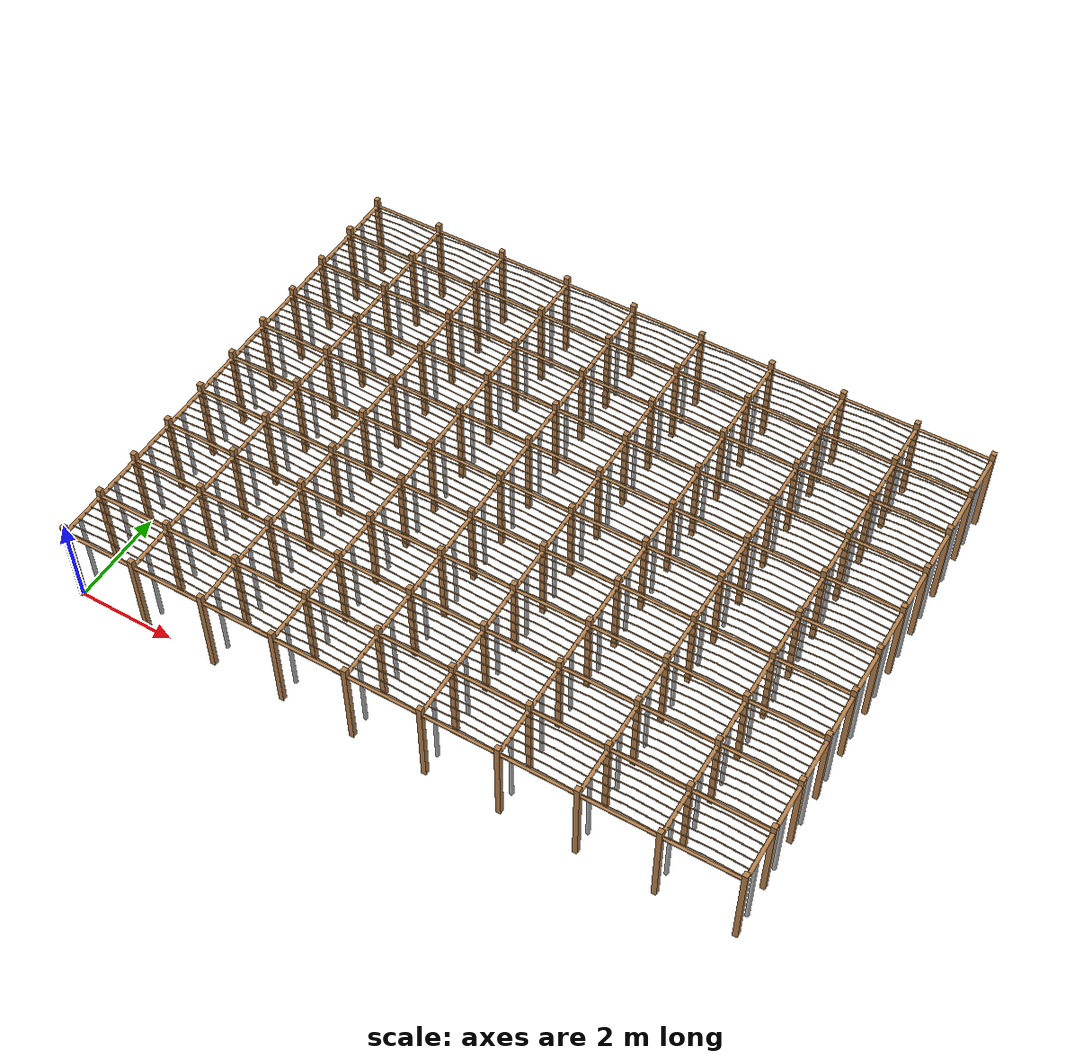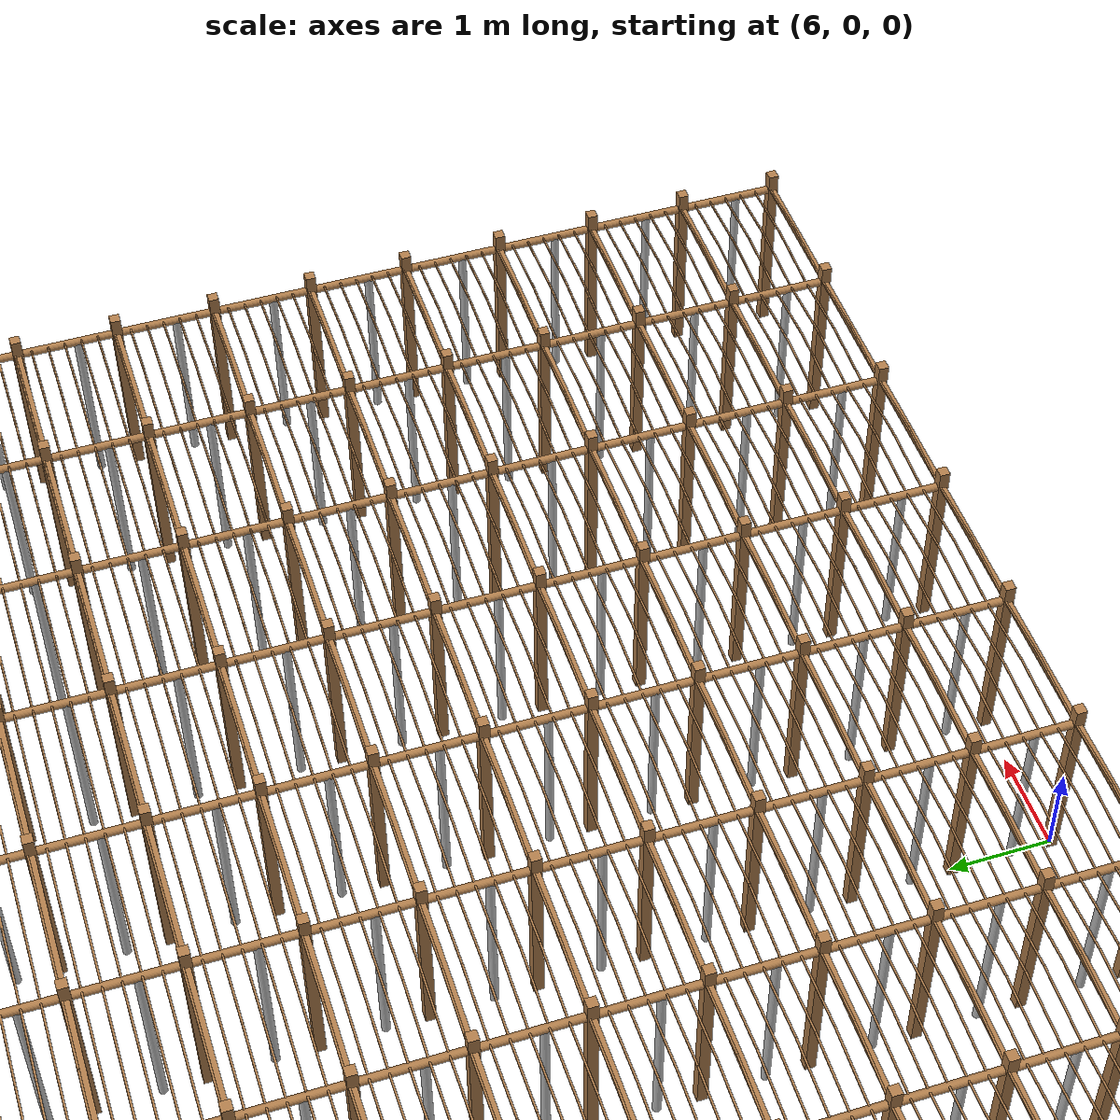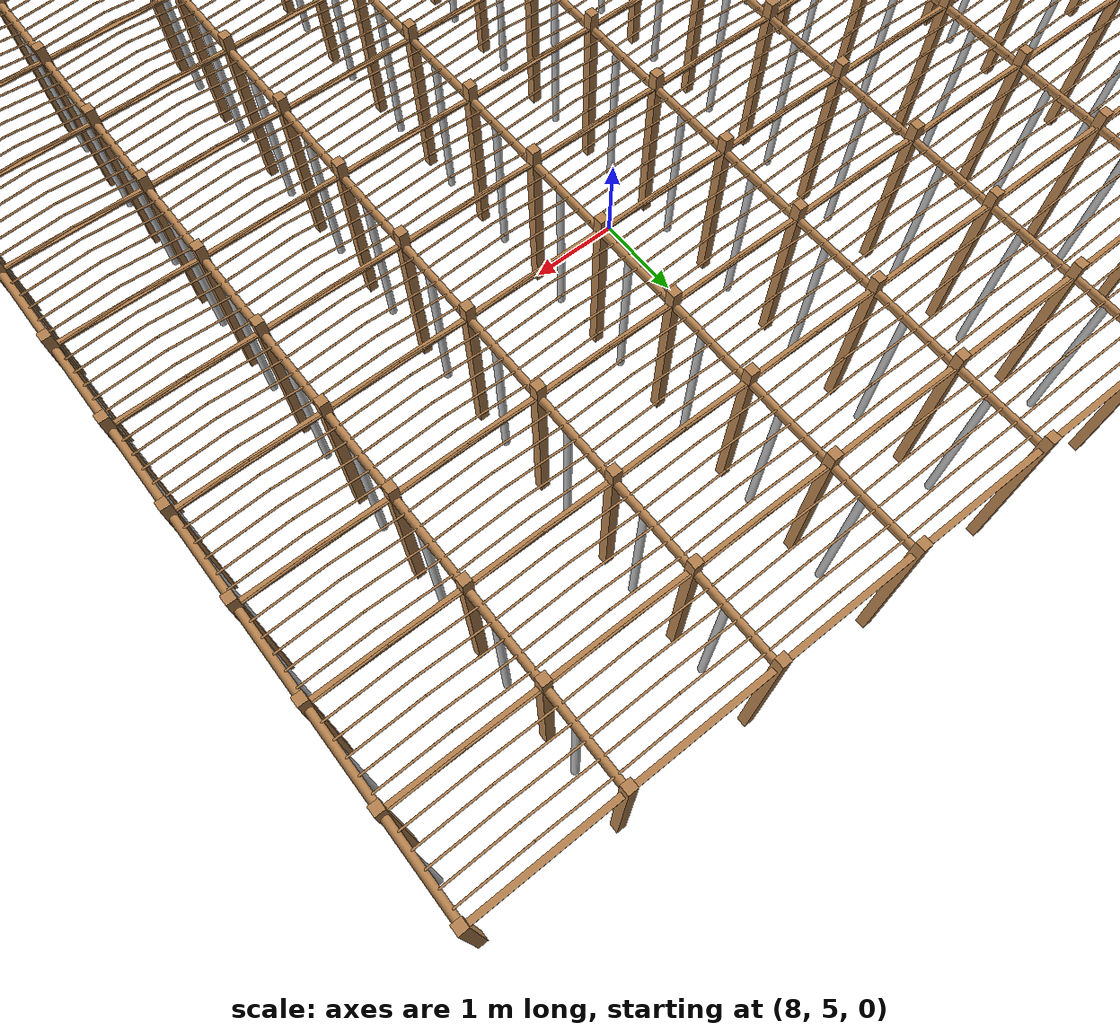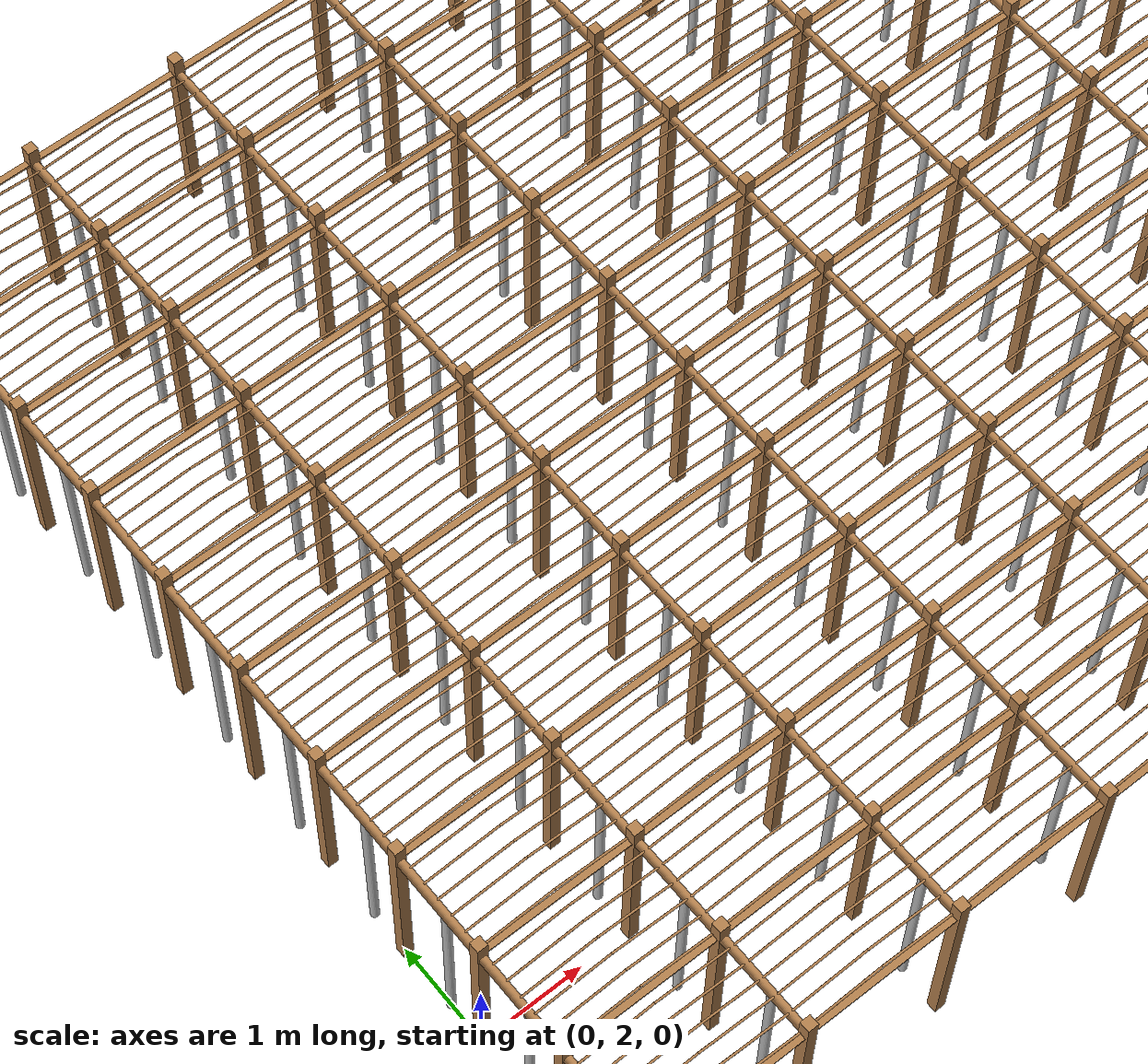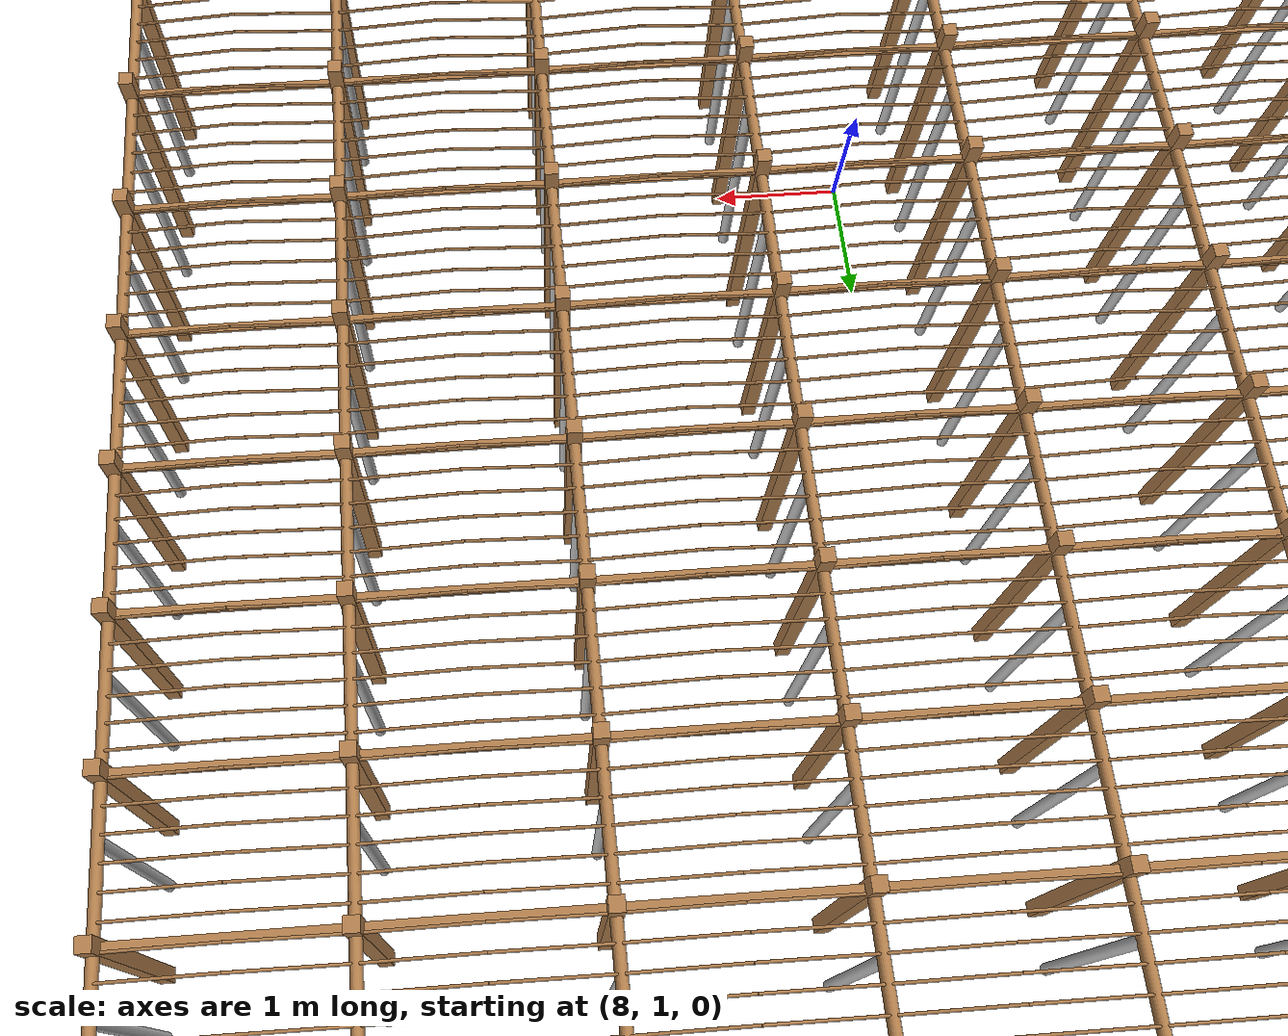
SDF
<?xml version='1.0'?>

<sdf version='1.4'>
  <model name="pergola">

		<include>
			<name>post_0</name>
			<pose>0.0 0.0 0 0 0 0</pose>
			<uri>model://post</uri>
		</include>

		<include>
			<name>post_1</name>
			<pose>0.0 1.0 0 0 0 0</pose>
			<uri>model://post</uri>
		</include>

		<include>
			<name>post_2</name>
			<pose>0.0 2.0 0 0 0 0</pose>
			<uri>model://post</uri>
		</include>

		<include>
			<name>post_3</name>
			<pose>0.0 3.0 0 0 0 0</pose>
			<uri>model://post</uri>
		</include>

		<include>
			<name>post_4</name>
			<pose>0.0 4.0 0 0 0 0</pose>
			<uri>model://post</uri>
		</include>

		<include>
			<name>post_5</name>
			<pose>0.0 5.0 0 0 0 0</pose>
			<uri>model://post</uri>
		</include>

		<include>
			<name>post_6</name>
			<pose>0.0 6.0 0 0 0 0</pose>
			<uri>model://post</uri>
		</include>

		<include>
			<name>post_7</name>
			<pose>0.0 7.0 0 0 0 0</pose>
			<uri>model://post</uri>
		</include>

		<include>
			<name>post_8</name>
			<pose>0.0 8.0 0 0 0 0</pose>
			<uri>model://post</uri>
		</include>

		<include>
			<name>post_9</name>
			<pose>0.0 9.0 0 0 0 0</pose>
			<uri>model://post</uri>
		</include>

		<include>
			<name>post_10</name>
			<pose>0.0 10.0 0 0 0 0</pose>
			<uri>model://post</uri>
		</include>

		<include>
			<name>post_11</name>
			<pose>1.5 0.0 0 0 0 0</pose>
			<uri>model://post</uri>
		</include>

		<include>
			<name>post_12</name>
			<pose>1.5 1.0 0 0 0 0</pose>
			<uri>model://post</uri>
		</include>

		<include>
			<name>post_13</name>
			<pose>1.5 2.0 0 0 0 0</pose>
			<uri>model://post</uri>
		</include>

		<include>
			<name>post_14</name>
			<pose>1.5 3.0 0 0 0 0</pose>
			<uri>model://post</uri>
		</include>

		<include>
			<name>post_15</name>
			<pose>1.5 4.0 0 0 0 0</pose>
			<uri>model://post</uri>
		</include>

		<include>
			<name>post_16</name>
			<pose>1.5 5.0 0 0 0 0</pose>
			<uri>model://post</uri>
		</include>

		<include>
			<name>post_17</name>
			<pose>1.5 6.0 0 0 0 0</pose>
			<uri>model://post</uri>
		</include>

		<include>
			<name>post_18</name>
			<pose>1.5 7.0 0 0 0 0</pose>
			<uri>model://post</uri>
		</include>

		<include>
			<name>post_19</name>
			<pose>1.5 8.0 0 0 0 0</pose>
			<uri>model://post</uri>
		</include>

		<include>
			<name>post_20</name>
			<pose>1.5 9.0 0 0 0 0</pose>
			<uri>model://post</uri>
		</include>

		<include>
			<name>post_21</name>
			<pose>1.5 10.0 0 0 0 0</pose>
			<uri>model://post</uri>
		</include>

		<include>
			<name>post_22</name>
			<pose>3.0 0.0 0 0 0 0</pose>
			<uri>model://post</uri>
		</include>

		<include>
			<name>post_23</name>
			<pose>3.0 1.0 0 0 0 0</pose>
			<uri>model://post</uri>
		</include>

		<include>
			<name>post_24</name>
			<pose>3.0 2.0 0 0 0 0</pose>
			<uri>model://post</uri>
		</include>

		<include>
			<name>post_25</name>
			<pose>3.0 3.0 0 0 0 0</pose>
			<uri>model://post</uri>
		</include>

		<include>
			<name>post_26</name>
			<pose>3.0 4.0 0 0 0 0</pose>
			<uri>model://post</uri>
		</include>

		<include>
			<name>post_27</name>
			<pose>3.0 5.0 0 0 0 0</pose>
			<uri>model://post</uri>
		</include>

		<include>
			<name>post_28</name>
			<pose>3.0 6.0 0 0 0 0</pose>
			<uri>model://post</uri>
		</include>

		<include>
			<name>post_29</name>
			<pose>3.0 7.0 0 0 0 0</pose>
			<uri>model://post</uri>
		</include>

		<include>
			<name>post_30</name>
			<pose>3.0 8.0 0 0 0 0</pose>
			<uri>model://post</uri>
		</include>

		<include>
			<name>post_31</name>
			<pose>3.0 9.0 0 0 0 0</pose>
			<uri>model://post</uri>
		</include>

		<include>
			<name>post_32</name>
			<pose>3.0 10.0 0 0 0 0</pose>
			<uri>model://post</uri>
		</include>

		<include>
			<name>post_33</name>
			<pose>4.5 0.0 0 0 0 0</pose>
			<uri>model://post</uri>
		</include>

		<include>
			<name>post_34</name>
			<pose>4.5 1.0 0 0 0 0</pose>
			<uri>model://post</uri>
		</include>

		<include>
			<name>post_35</name>
			<pose>4.5 2.0 0 0 0 0</pose>
			<uri>model://post</uri>
		</include>

		<include>
			<name>post_36</name>
			<pose>4.5 3.0 0 0 0 0</pose>
			<uri>model://post</uri>
		</include>

		<include>
			<name>post_37</name>
			<pose>4.5 4.0 0 0 0 0</pose>
			<uri>model://post</uri>
		</include>

		<include>
			<name>post_38</name>
			<pose>4.5 5.0 0 0 0 0</pose>
			<uri>model://post</uri>
		</include>

		<include>
			<name>post_39</name>
			<pose>4.5 6.0 0 0 0 0</pose>
			<uri>model://post</uri>
		</include>

		<include>
			<name>post_40</name>
			<pose>4.5 7.0 0 0 0 0</pose>
			<uri>model://post</uri>
		</include>

		<include>
			<name>post_41</name>
			<pose>4.5 8.0 0 0 0 0</pose>
			<uri>model://post</uri>
		</include>

		<include>
			<name>post_42</name>
			<pose>4.5 9.0 0 0 0 0</pose>
			<uri>model://post</uri>
		</include>

		<include>
			<name>post_43</name>
			<pose>4.5 10.0 0 0 0 0</pose>
			<uri>model://post</uri>
		</include>

		<include>
			<name>post_44</name>
			<pose>6.0 0.0 0 0 0 0</pose>
			<uri>model://post</uri>
		</include>

		<include>
			<name>post_45</name>
			<pose>6.0 1.0 0 0 0 0</pose>
			<uri>model://post</uri>
		</include>

		<include>
			<name>post_46</name>
			<pose>6.0 2.0 0 0 0 0</pose>
			<uri>model://post</uri>
		</include>

		<include>
			<name>post_47</name>
			<pose>6.0 3.0 0 0 0 0</pose>
			<uri>model://post</uri>
		</include>

		<include>
			<name>post_48</name>
			<pose>6.0 4.0 0 0 0 0</pose>
			<uri>model://post</uri>
		</include>

		<include>
			<name>post_49</name>
			<pose>6.0 5.0 0 0 0 0</pose>
			<uri>model://post</uri>
		</include>

		<include>
			<name>post_50</name>
			<pose>6.0 6.0 0 0 0 0</pose>
			<uri>model://post</uri>
		</include>

		<include>
			<name>post_51</name>
			<pose>6.0 7.0 0 0 0 0</pose>
			<uri>model://post</uri>
		</include>

		<include>
			<name>post_52</name>
			<pose>6.0 8.0 0 0 0 0</pose>
			<uri>model://post</uri>
		</include>

		<include>
			<name>post_53</name>
			<pose>6.0 9.0 0 0 0 0</pose>
			<uri>model://post</uri>
		</include>

		<include>
			<name>post_54</name>
			<pose>6.0 10.0 0 0 0 0</pose>
			<uri>model://post</uri>
		</include>

		<include>
			<name>post_55</name>
			<pose>7.5 0.0 0 0 0 0</pose>
			<uri>model://post</uri>
		</include>

		<include>
			<name>post_56</name>
			<pose>7.5 1.0 0 0 0 0</pose>
			<uri>model://post</uri>
		</include>

		<include>
			<name>post_57</name>
			<pose>7.5 2.0 0 0 0 0</pose>
			<uri>model://post</uri>
		</include>

		<include>
			<name>post_58</name>
			<pose>7.5 3.0 0 0 0 0</pose>
			<uri>model://post</uri>
		</include>

		<include>
			<name>post_59</name>
			<pose>7.5 4.0 0 0 0 0</pose>
			<uri>model://post</uri>
		</include>

		<include>
			<name>post_60</name>
			<pose>7.5 5.0 0 0 0 0</pose>
			<uri>model://post</uri>
		</include>

		<include>
			<name>post_61</name>
			<pose>7.5 6.0 0 0 0 0</pose>
			<uri>model://post</uri>
		</include>

		<include>
			<name>post_62</name>
			<pose>7.5 7.0 0 0 0 0</pose>
			<uri>model://post</uri>
		</include>

		<include>
			<name>post_63</name>
			<pose>7.5 8.0 0 0 0 0</pose>
			<uri>model://post</uri>
		</include>

		<include>
			<name>post_64</name>
			<pose>7.5 9.0 0 0 0 0</pose>
			<uri>model://post</uri>
		</include>

		<include>
			<name>post_65</name>
			<pose>7.5 10.0 0 0 0 0</pose>
			<uri>model://post</uri>
		</include>

		<include>
			<name>post_66</name>
			<pose>9.0 0.0 0 0 0 0</pose>
			<uri>model://post</uri>
		</include>

		<include>
			<name>post_67</name>
			<pose>9.0 1.0 0 0 0 0</pose>
			<uri>model://post</uri>
		</include>

		<include>
			<name>post_68</name>
			<pose>9.0 2.0 0 0 0 0</pose>
			<uri>model://post</uri>
		</include>

		<include>
			<name>post_69</name>
			<pose>9.0 3.0 0 0 0 0</pose>
			<uri>model://post</uri>
		</include>

		<include>
			<name>post_70</name>
			<pose>9.0 4.0 0 0 0 0</pose>
			<uri>model://post</uri>
		</include>

		<include>
			<name>post_71</name>
			<pose>9.0 5.0 0 0 0 0</pose>
			<uri>model://post</uri>
		</include>

		<include>
			<name>post_72</name>
			<pose>9.0 6.0 0 0 0 0</pose>
			<uri>model://post</uri>
		</include>

		<include>
			<name>post_73</name>
			<pose>9.0 7.0 0 0 0 0</pose>
			<uri>model://post</uri>
		</include>

		<include>
			<name>post_74</name>
			<pose>9.0 8.0 0 0 0 0</pose>
			<uri>model://post</uri>
		</include>

		<include>
			<name>post_75</name>
			<pose>9.0 9.0 0 0 0 0</pose>
			<uri>model://post</uri>
		</include>

		<include>
			<name>post_76</name>
			<pose>9.0 10.0 0 0 0 0</pose>
			<uri>model://post</uri>
		</include>

		<include>
			<name>post_77</name>
			<pose>10.5 0.0 0 0 0 0</pose>
			<uri>model://post</uri>
		</include>

		<include>
			<name>post_78</name>
			<pose>10.5 1.0 0 0 0 0</pose>
			<uri>model://post</uri>
		</include>

		<include>
			<name>post_79</name>
			<pose>10.5 2.0 0 0 0 0</pose>
			<uri>model://post</uri>
		</include>

		<include>
			<name>post_80</name>
			<pose>10.5 3.0 0 0 0 0</pose>
			<uri>model://post</uri>
		</include>

		<include>
			<name>post_81</name>
			<pose>10.5 4.0 0 0 0 0</pose>
			<uri>model://post</uri>
		</include>

		<include>
			<name>post_82</name>
			<pose>10.5 5.0 0 0 0 0</pose>
			<uri>model://post</uri>
		</include>

		<include>
			<name>post_83</name>
			<pose>10.5 6.0 0 0 0 0</pose>
			<uri>model://post</uri>
		</include>

		<include>
			<name>post_84</name>
			<pose>10.5 7.0 0 0 0 0</pose>
			<uri>model://post</uri>
		</include>

		<include>
			<name>post_85</name>
			<pose>10.5 8.0 0 0 0 0</pose>
			<uri>model://post</uri>
		</include>

		<include>
			<name>post_86</name>
			<pose>10.5 9.0 0 0 0 0</pose>
			<uri>model://post</uri>
		</include>

		<include>
			<name>post_87</name>
			<pose>10.5 10.0 0 0 0 0</pose>
			<uri>model://post</uri>
		</include>

		<include>
			<name>post_88</name>
			<pose>12.0 0.0 0 0 0 0</pose>
			<uri>model://post</uri>
		</include>

		<include>
			<name>post_89</name>
			<pose>12.0 1.0 0 0 0 0</pose>
			<uri>model://post</uri>
		</include>

		<include>
			<name>post_90</name>
			<pose>12.0 2.0 0 0 0 0</pose>
			<uri>model://post</uri>
		</include>

		<include>
			<name>post_91</name>
			<pose>12.0 3.0 0 0 0 0</pose>
			<uri>model://post</uri>
		</include>

		<include>
			<name>post_92</name>
			<pose>12.0 4.0 0 0 0 0</pose>
			<uri>model://post</uri>
		</include>

		<include>
			<name>post_93</name>
			<pose>12.0 5.0 0 0 0 0</pose>
			<uri>model://post</uri>
		</include>

		<include>
			<name>post_94</name>
			<pose>12.0 6.0 0 0 0 0</pose>
			<uri>model://post</uri>
		</include>

		<include>
			<name>post_95</name>
			<pose>12.0 7.0 0 0 0 0</pose>
			<uri>model://post</uri>
		</include>

		<include>
			<name>post_96</name>
			<pose>12.0 8.0 0 0 0 0</pose>
			<uri>model://post</uri>
		</include>

		<include>
			<name>post_97</name>
			<pose>12.0 9.0 0 0 0 0</pose>
			<uri>model://post</uri>
		</include>

		<include>
			<name>post_98</name>
			<pose>12.0 10.0 0 0 0 0</pose>
			<uri>model://post</uri>
		</include>

		<include>
			<name>post_99</name>
			<pose>13.5 0.0 0 0 0 0</pose>
			<uri>model://post</uri>
		</include>

		<include>
			<name>post_100</name>
			<pose>13.5 1.0 0 0 0 0</pose>
			<uri>model://post</uri>
		</include>

		<include>
			<name>post_101</name>
			<pose>13.5 2.0 0 0 0 0</pose>
			<uri>model://post</uri>
		</include>

		<include>
			<name>post_102</name>
			<pose>13.5 3.0 0 0 0 0</pose>
			<uri>model://post</uri>
		</include>

		<include>
			<name>post_103</name>
			<pose>13.5 4.0 0 0 0 0</pose>
			<uri>model://post</uri>
		</include>

		<include>
			<name>post_104</name>
			<pose>13.5 5.0 0 0 0 0</pose>
			<uri>model://post</uri>
		</include>

		<include>
			<name>post_105</name>
			<pose>13.5 6.0 0 0 0 0</pose>
			<uri>model://post</uri>
		</include>

		<include>
			<name>post_106</name>
			<pose>13.5 7.0 0 0 0 0</pose>
			<uri>model://post</uri>
		</include>

		<include>
			<name>post_107</name>
			<pose>13.5 8.0 0 0 0 0</pose>
			<uri>model://post</uri>
		</include>

		<include>
			<name>post_108</name>
			<pose>13.5 9.0 0 0 0 0</pose>
			<uri>model://post</uri>
		</include>

		<include>
			<name>post_109</name>
			<pose>13.5 10.0 0 0 0 0</pose>
			<uri>model://post</uri>
		</include>

    <link name="beam_0">
      <pose>0.75 0.0 1.81 0 0 0</pose>
      <collision name="collision">
        <geometry><box><size>1.5 0.06 0.02</size></box></geometry>
      </collision>
      <visual name="visual">
        <geometry><box><size>1.5 0.06 0.02</size></box></geometry>
        <material><script><name>Gazebo/Wood</name></script></material>
      </visual>
    <inertial>
      <pose>0 0 0 0 0 0</pose>
      <mass>5</mass>
      <inertia>
        <ixx>0.0016666666666666668</ixx><ixy>0.0</ixy><ixz>0.0</ixz><iyy>0.9390000000000001</iyy><iyz>0.0</iyz><izz>0.9376666666666665</izz>
      </inertia>
    </inertial>
    </link>

    <link name="beam_1">
      <pose>0.75 1.0 1.81 0 0 0</pose>
      <collision name="collision">
        <geometry><box><size>1.5 0.06 0.02</size></box></geometry>
      </collision>
      <visual name="visual">
        <geometry><box><size>1.5 0.06 0.02</size></box></geometry>
        <material><script><name>Gazebo/Wood</name></script></material>
      </visual>
    <inertial>
      <pose>0 0 0 0 0 0</pose>
      <mass>5</mass>
      <inertia>
        <ixx>0.0016666666666666668</ixx><ixy>0.0</ixy><ixz>0.0</ixz><iyy>0.9390000000000001</iyy><iyz>0.0</iyz><izz>0.9376666666666665</izz>
      </inertia>
    </inertial>
    </link>

    <link name="beam_2">
      <pose>0.75 2.0 1.81 0 0 0</pose>
      <collision name="collision">
        <geometry><box><size>1.5 0.06 0.02</size></box></geometry>
      </collision>
      <visual name="visual">
        <geometry><box><size>1.5 0.06 0.02</size></box></geometry>
        <material><script><name>Gazebo/Wood</name></script></material>
      </visual>
    <inertial>
      <pose>0 0 0 0 0 0</pose>
      <mass>5</mass>
      <inertia>
        <ixx>0.0016666666666666668</ixx><ixy>0.0</ixy><ixz>0.0</ixz><iyy>0.9390000000000001</iyy><iyz>0.0</iyz><izz>0.9376666666666665</izz>
      </inertia>
    </inertial>
    </link>

    <link name="beam_3">
      <pose>0.75 3.0 1.81 0 0 0</pose>
      <collision name="collision">
        <geometry><box><size>1.5 0.06 0.02</size></box></geometry>
      </collision>
      <visual name="visual">
        <geometry><box><size>1.5 0.06 0.02</size></box></geometry>
        <material><script><name>Gazebo/Wood</name></script></material>
      </visual>
    <inertial>
      <pose>0 0 0 0 0 0</pose>
      <mass>5</mass>
      <inertia>
        <ixx>0.0016666666666666668</ixx><ixy>0.0</ixy><ixz>0.0</ixz><iyy>0.9390000000000001</iyy><iyz>0.0</iyz><izz>0.9376666666666665</izz>
      </inertia>
    </inertial>
    </link>

    <link name="beam_4">
      <pose>0.75 4.0 1.81 0 0 0</pose>
      <collision name="collision">
        <geometry><box><size>1.5 0.06 0.02</size></box></geometry>
      </collision>
      <visual name="visual">
        <geometry><box><size>1.5 0.06 0.02</size></box></geometry>
        <material><script><name>Gazebo/Wood</name></script></material>
      </visual>
    <inertial>
      <pose>0 0 0 0 0 0</pose>
      <mass>5</mass>
      <inertia>
        <ixx>0.0016666666666666668</ixx><ixy>0.0</ixy><ixz>0.0</ixz><iyy>0.9390000000000001</iyy><iyz>0.0</iyz><izz>0.9376666666666665</izz>
      </inertia>
    </inertial>
    </link>

    <link name="beam_5">
      <pose>0.75 5.0 1.81 0 0 0</pose>
      <collision name="collision">
        <geometry><box><size>1.5 0.06 0.02</size></box></geometry>
      </collision>
      <visual name="visual">
        <geometry><box><size>1.5 0.06 0.02</size></box></geometry>
        <material><script><name>Gazebo/Wood</name></script></material>
      </visual>
    <inertial>
      <pose>0 0 0 0 0 0</pose>
      <mass>5</mass>
      <inertia>
        <ixx>0.0016666666666666668</ixx><ixy>0.0</ixy><ixz>0.0</ixz><iyy>0.9390000000000001</iyy><iyz>0.0</iyz><izz>0.9376666666666665</izz>
      </inertia>
    </inertial>
    </link>

    <link name="beam_6">
      <pose>0.75 6.0 1.81 0 0 0</pose>
      <collision name="collision">
        <geometry><box><size>1.5 0.06 0.02</size></box></geometry>
      </collision>
      <visual name="visual">
        <geometry><box><size>1.5 0.06 0.02</size></box></geometry>
        <material><script><name>Gazebo/Wood</name></script></material>
      </visual>
    <inertial>
      <pose>0 0 0 0 0 0</pose>
      <mass>5</mass>
      <inertia>
        <ixx>0.0016666666666666668</ixx><ixy>0.0</ixy><ixz>0.0</ixz><iyy>0.9390000000000001</iyy><iyz>0.0</iyz><izz>0.9376666666666665</izz>
      </inertia>
    </inertial>
    </link>

    <link name="beam_7">
      <pose>0.75 7.0 1.81 0 0 0</pose>
      <collision name="collision">
        <geometry><box><size>1.5 0.06 0.02</size></box></geometry>
      </collision>
      <visual name="visual">
        <geometry><box><size>1.5 0.06 0.02</size></box></geometry>
        <material><script><name>Gazebo/Wood</name></script></material>
      </visual>
    <inertial>
      <pose>0 0 0 0 0 0</pose>
      <mass>5</mass>
      <inertia>
        <ixx>0.0016666666666666668</ixx><ixy>0.0</ixy><ixz>0.0</ixz><iyy>0.9390000000000001</iyy><iyz>0.0</iyz><izz>0.9376666666666665</izz>
      </inertia>
    </inertial>
    </link>

    <link name="beam_8">
      <pose>0.75 8.0 1.81 0 0 0</pose>
      <collision name="collision">
        <geometry><box><size>1.5 0.06 0.02</size></box></geometry>
      </collision>
      <visual name="visual">
        <geometry><box><size>1.5 0.06 0.02</size></box></geometry>
        <material><script><name>Gazebo/Wood</name></script></material>
      </visual>
    <inertial>
      <pose>0 0 0 0 0 0</pose>
      <mass>5</mass>
      <inertia>
        <ixx>0.0016666666666666668</ixx><ixy>0.0</ixy><ixz>0.0</ixz><iyy>0.9390000000000001</iyy><iyz>0.0</iyz><izz>0.9376666666666665</izz>
      </inertia>
    </inertial>
    </link>

    <link name="beam_9">
      <pose>0.75 9.0 1.81 0 0 0</pose>
      <collision name="collision">
        <geometry><box><size>1.5 0.06 0.02</size></box></geometry>
      </collision>
      <visual name="visual">
        <geometry><box><size>1.5 0.06 0.02</size></box></geometry>
        <material><script><name>Gazebo/Wood</name></script></material>
      </visual>
    <inertial>
      <pose>0 0 0 0 0 0</pose>
      <mass>5</mass>
      <inertia>
        <ixx>0.0016666666666666668</ixx><ixy>0.0</ixy><ixz>0.0</ixz><iyy>0.9390000000000001</iyy><iyz>0.0</iyz><izz>0.9376666666666665</izz>
      </inertia>
    </inertial>
    </link>

    <link name="beam_10">
      <pose>0.75 10.0 1.81 0 0 0</pose>
      <collision name="collision">
        <geometry><box><size>1.5 0.06 0.02</size></box></geometry>
      </collision>
      <visual name="visual">
        <geometry><box><size>1.5 0.06 0.02</size></box></geometry>
        <material><script><name>Gazebo/Wood</name></script></material>
      </visual>
    <inertial>
      <pose>0 0 0 0 0 0</pose>
      <mass>5</mass>
      <inertia>
        <ixx>0.0016666666666666668</ixx><ixy>0.0</ixy><ixz>0.0</ixz><iyy>0.9390000000000001</iyy><iyz>0.0</iyz><izz>0.9376666666666665</izz>
      </inertia>
    </inertial>
    </link>

    <link name="beam_11">
      <pose>2.25 0.0 1.81 0 0 0</pose>
      <collision name="collision">
        <geometry><box><size>1.5 0.06 0.02</size></box></geometry>
      </collision>
      <visual name="visual">
        <geometry><box><size>1.5 0.06 0.02</size></box></geometry>
        <material><script><name>Gazebo/Wood</name></script></material>
      </visual>
    <inertial>
      <pose>0 0 0 0 0 0</pose>
      <mass>5</mass>
      <inertia>
        <ixx>0.0016666666666666668</ixx><ixy>0.0</ixy><ixz>0.0</ixz><iyy>0.9390000000000001</iyy><iyz>0.0</iyz><izz>0.9376666666666665</izz>
      </inertia>
    </inertial>
    </link>

    <link name="beam_12">
      <pose>2.25 1.0 1.81 0 0 0</pose>
      <collision name="collision">
        <geometry><box><size>1.5 0.06 0.02</size></box></geometry>
      </collision>
      <visual name="visual">
        <geometry><box><size>1.5 0.06 0.02</size></box></geometry>
        <material><script><name>Gazebo/Wood</name></script></material>
      </visual>
    <inertial>
      <pose>0 0 0 0 0 0</pose>
      <mass>5</mass>
      <inertia>
        <ixx>0.0016666666666666668</ixx><ixy>0.0</ixy><ixz>0.0</ixz><iyy>0.9390000000000001</iyy><iyz>0.0</iyz><izz>0.9376666666666665</izz>
      </inertia>
    </inertial>
    </link>

    <link name="beam_13">
      <pose>2.25 2.0 1.81 0 0 0</pose>
      <collision name="collision">
        <geometry><box><size>1.5 0.06 0.02</size></box></geometry>
      </collision>
      <visual name="visual">
        <geometry><box><size>1.5 0.06 0.02</size></box></geometry>
        <material><script><name>Gazebo/Wood</name></script></material>
      </visual>
    <inertial>
      <pose>0 0 0 0 0 0</pose>
      <mass>5</mass>
      <inertia>
        <ixx>0.0016666666666666668</ixx><ixy>0.0</ixy><ixz>0.0</ixz><iyy>0.9390000000000001</iyy><iyz>0.0</iyz><izz>0.9376666666666665</izz>
      </inertia>
    </inertial>
    </link>

    <link name="beam_14">
      <pose>2.25 3.0 1.81 0 0 0</pose>
      <collision name="collision">
        <geometry><box><size>1.5 0.06 0.02</size></box></geometry>
      </collision>
      <visual name="visual">
        <geometry><box><size>1.5 0.06 0.02</size></box></geometry>
        <material><script><name>Gazebo/Wood</name></script></material>
      </visual>
    <inertial>
      <pose>0 0 0 0 0 0</pose>
      <mass>5</mass>
      <inertia>
        <ixx>0.0016666666666666668</ixx><ixy>0.0</ixy><ixz>0.0</ixz><iyy>0.9390000000000001</iyy><iyz>0.0</iyz><izz>0.9376666666666665</izz>
      </inertia>
    </inertial>
    </link>

    <link name="beam_15">
      <pose>2.25 4.0 1.81 0 0 0</pose>
      <collision name="collision">
        <geometry><box><size>1.5 0.06 0.02</size></box></geometry>
      </collision>
      <visual name="visual">
        <geometry><box><size>1.5 0.06 0.02</size></box></geometry>
        <material><script><name>Gazebo/Wood</name></script></material>
      </visual>
    <inertial>
      <pose>0 0 0 0 0 0</pose>
      <mass>5</mass>
      <inertia>
        <ixx>0.0016666666666666668</ixx><ixy>0.0</ixy><ixz>0.0</ixz><iyy>0.9390000000000001</iyy><iyz>0.0</iyz><izz>0.9376666666666665</izz>
      </inertia>
    </inertial>
    </link>

    <link name="beam_16">
      <pose>2.25 5.0 1.81 0 0 0</pose>
      <collision name="collision">
        <geometry><box><size>1.5 0.06 0.02</size></box></geometry>
      </collision>
      <visual name="visual">
        <geometry><box><size>1.5 0.06 0.02</size></box></geometry>
        <material><script><name>Gazebo/Wood</name></script></material>
      </visual>
    <inertial>
      <pose>0 0 0 0 0 0</pose>
      <mass>5</mass>
      <inertia>
        <ixx>0.0016666666666666668</ixx><ixy>0.0</ixy><ixz>0.0</ixz><iyy>0.9390000000000001</iyy><iyz>0.0</iyz><izz>0.9376666666666665</izz>
      </inertia>
    </inertial>
    </link>

    <link name="beam_17">
      <pose>2.25 6.0 1.81 0 0 0</pose>
      <collision name="collision">
        <geometry><box><size>1.5 0.06 0.02</size></box></geometry>
      </collision>
      <visual name="visual">
        <geometry><box><size>1.5 0.06 0.02</size></box></geometry>
        <material><script><name>Gazebo/Wood</name></script></material>
      </visual>
    <inertial>
      <pose>0 0 0 0 0 0</pose>
      <mass>5</mass>
      <inertia>
        <ixx>0.0016666666666666668</ixx><ixy>0.0</ixy><ixz>0.0</ixz><iyy>0.9390000000000001</iyy><iyz>0.0</iyz><izz>0.9376666666666665</izz>
      </inertia>
    </inertial>
    </link>

    <link name="beam_18">
      <pose>2.25 7.0 1.81 0 0 0</pose>
      <collision name="collision">
        <geometry><box><size>1.5 0.06 0.02</size></box></geometry>
      </collision>
      <visual name="visual">
        <geometry><box><size>1.5 0.06 0.02</size></box></geometry>
        <material><script><name>Gazebo/Wood</name></script></material>
      </visual>
    <inertial>
      <pose>0 0 0 0 0 0</pose>
      <mass>5</mass>
      <inertia>
        <ixx>0.0016666666666666668</ixx><ixy>0.0</ixy><ixz>0.0</ixz><iyy>0.9390000000000001</iyy><iyz>0.0</iyz><izz>0.9376666666666665</izz>
      </inertia>
    </inertial>
    </link>

    <link name="beam_19">
      <pose>2.25 8.0 1.81 0 0 0</pose>
      <collision name="collision">
        <geometry><box><size>1.5 0.06 0.02</size></box></geometry>
      </collision>
      <visual name="visual">
        <geometry><box><size>1.5 0.06 0.02</size></box></geometry>
        <material><script><name>Gazebo/Wood</name></script></material>
      </visual>
    <inertial>
      <pose>0 0 0 0 0 0</pose>
      <mass>5</mass>
      <inertia>
        <ixx>0.0016666666666666668</ixx><ixy>0.0</ixy><ixz>0.0</ixz><iyy>0.9390000000000001</iyy><iyz>0.0</iyz><izz>0.9376666666666665</izz>
      </inertia>
    </inertial>
    </link>

    <link name="beam_20">
      <pose>2.25 9.0 1.81 0 0 0</pose>
      <collision name="collision">
        <geometry><box><size>1.5 0.06 0.02</size></box></geometry>
      </collision>
      <visual name="visual">
        <geometry><box><size>1.5 0.06 0.02</size></box></geometry>
        <material><script><name>Gazebo/Wood</name></script></material>
      </visual>
    <inertial>
      <pose>0 0 0 0 0 0</pose>
      <mass>5</mass>
      <inertia>
        <ixx>0.0016666666666666668</ixx><ixy>0.0</ixy><ixz>0.0</ixz><iyy>0.9390000000000001</iyy><iyz>0.0</iyz><izz>0.9376666666666665</izz>
      </inertia>
    </inertial>
    </link>

    <link name="beam_21">
      <pose>2.25 10.0 1.81 0 0 0</pose>
      <collision name="collision">
        <geometry><box><size>1.5 0.06 0.02</size></box></geometry>
      </collision>
      <visual name="visual">
        <geometry><box><size>1.5 0.06 0.02</size></box></geometry>
        <material><script><name>Gazebo/Wood</name></script></material>
      </visual>
    <inertial>
      <pose>0 0 0 0 0 0</pose>
      <mass>5</mass>
      <inertia>
        <ixx>0.0016666666666666668</ixx><ixy>0.0</ixy><ixz>0.0</ixz><iyy>0.9390000000000001</iyy><iyz>0.0</iyz><izz>0.9376666666666665</izz>
      </inertia>
    </inertial>
    </link>

    <link name="beam_22">
      <pose>3.75 0.0 1.81 0 0 0</pose>
      <collision name="collision">
        <geometry><box><size>1.5 0.06 0.02</size></box></geometry>
      </collision>
      <visual name="visual">
        <geometry><box><size>1.5 0.06 0.02</size></box></geometry>
        <material><script><name>Gazebo/Wood</name></script></material>
      </visual>
    <inertial>
      <pose>0 0 0 0 0 0</pose>
      <mass>5</mass>
      <inertia>
        <ixx>0.0016666666666666668</ixx><ixy>0.0</ixy><ixz>0.0</ixz><iyy>0.9390000000000001</iyy><iyz>0.0</iyz><izz>0.9376666666666665</izz>
      </inertia>
    </inertial>
    </link>

    <link name="beam_23">
      <pose>3.75 1.0 1.81 0 0 0</pose>
      <collision name="collision">
        <geometry><box><size>1.5 0.06 0.02</size></box></geometry>
      </collision>
      <visual name="visual">
        <geometry><box><size>1.5 0.06 0.02</size></box></geometry>
        <material><script><name>Gazebo/Wood</name></script></material>
      </visual>
    <inertial>
      <pose>0 0 0 0 0 0</pose>
      <mass>5</mass>
      <inertia>
        <ixx>0.0016666666666666668</ixx><ixy>0.0</ixy><ixz>0.0</ixz><iyy>0.9390000000000001</iyy><iyz>0.0</iyz><izz>0.9376666666666665</izz>
      </inertia>
    </inertial>
    </link>

    <link name="beam_24">
      <pose>3.75 2.0 1.81 0 0 0</pose>
      <collision name="collision">
        <geometry><box><size>1.5 0.06 0.02</size></box></geometry>
      </collision>
      <visual name="visual">
        <geometry><box><size>1.5 0.06 0.02</size></box></geometry>
        <material><script><name>Gazebo/Wood</name></script></material>
      </visual>
    <inertial>
      <pose>0 0 0 0 0 0</pose>
      <mass>5</mass>
      <inertia>
        <ixx>0.0016666666666666668</ixx><ixy>0.0</ixy><ixz>0.0</ixz><iyy>0.9390000000000001</iyy><iyz>0.0</iyz><izz>0.9376666666666665</izz>
      </inertia>
    </inertial>
    </link>

    <link name="beam_25">
      <pose>3.75 3.0 1.81 0 0 0</pose>
      <collision name="collision">
        <geometry><box><size>1.5 0.06 0.02</size></box></geometry>
      </collision>
      <visual name="visual">
        <geometry><box><size>1.5 0.06 0.02</size></box></geometry>
        <material><script><name>Gazebo/Wood</name></script></material>
      </visual>
    <inertial>
      <pose>0 0 0 0 0 0</pose>
      <mass>5</mass>
      <inertia>
        <ixx>0.0016666666666666668</ixx><ixy>0.0</ixy><ixz>0.0</ixz><iyy>0.9390000000000001</iyy><iyz>0.0</iyz><izz>0.9376666666666665</izz>
      </inertia>
    </inertial>
    </link>

    <link name="beam_26">
      <pose>3.75 4.0 1.81 0 0 0</pose>
      <collision name="collision">
        <geometry><box><size>1.5 0.06 0.02</size></box></geometry>
      </collision>
      <visual name="visual">
        <geometry><box><size>1.5 0.06 0.02</size></box></geometry>
        <material><script><name>Gazebo/Wood</name></script></material>
      </visual>
    <inertial>
      <pose>0 0 0 0 0 0</pose>
      <mass>5</mass>
      <inertia>
        <ixx>0.0016666666666666668</ixx><ixy>0.0</ixy><ixz>0.0</ixz><iyy>0.9390000000000001</iyy><iyz>0.0</iyz><izz>0.9376666666666665</izz>
      </inertia>
    </inertial>
    </link>

    <link name="beam_27">
      <pose>3.75 5.0 1.81 0 0 0</pose>
      <collision name="collision">
        <geometry><box><size>1.5 0.06 0.02</size></box></geometry>
      </collision>
      <visual name="visual">
        <geometry><box><size>1.5 0.06 0.02</size></box></geometry>
        <material><script><name>Gazebo/Wood</name></script></material>
      </visual>
    <inertial>
      <pose>0 0 0 0 0 0</pose>
      <mass>5</mass>
      <inertia>
        <ixx>0.0016666666666666668</ixx><ixy>0.0</ixy><ixz>0.0</ixz><iyy>0.9390000000000001</iyy><iyz>0.0</iyz><izz>0.9376666666666665</izz>
      </inertia>
    </inertial>
    </link>

    <link name="beam_28">
      <pose>3.75 6.0 1.81 0 0 0</pose>
      <collision name="collision">
        <geometry><box><size>1.5 0.06 0.02</size></box></geometry>
      </collision>
      <visual name="visual">
        <geometry><box><size>1.5 0.06 0.02</size></box></geometry>
        <material><script><name>Gazebo/Wood</name></script></material>
      </visual>
    <inertial>
      <pose>0 0 0 0 0 0</pose>
      <mass>5</mass>
      <inertia>
        <ixx>0.0016666666666666668</ixx><ixy>0.0</ixy><ixz>0.0</ixz><iyy>0.9390000000000001</iyy><iyz>0.0</iyz><izz>0.9376666666666665</izz>
      </inertia>
    </inertial>
    </link>

    <link name="beam_29">
      <pose>3.75 7.0 1.81 0 0 0</pose>
      <collision name="collision">
        <geometry><box><size>1.5 0.06 0.02</size></box></geometry>
      </collision>
      <visual name="visual">
        <geometry><box><size>1.5 0.06 0.02</size></box></geometry>
        <material><script><name>Gazebo/Wood</name></script></material>
      </visual>
    <inertial>
      <pose>0 0 0 0 0 0</pose>
      <mass>5</mass>
      <inertia>
        <ixx>0.0016666666666666668</ixx><ixy>0.0</ixy><ixz>0.0</ixz><iyy>0.9390000000000001</iyy><iyz>0.0</iyz><izz>0.9376666666666665</izz>
      </inertia>
    </inertial>
    </link>

    <link name="beam_30">
      <pose>3.75 8.0 1.81 0 0 0</pose>
      <collision name="collision">
        <geometry><box><size>1.5 0.06 0.02</size></box></geometry>
      </collision>
      <visual name="visual">
        <geometry><box><size>1.5 0.06 0.02</size></box></geometry>
        <material><script><name>Gazebo/Wood</name></script></material>
      </visual>
    <inertial>
      <pose>0 0 0 0 0 0</pose>
      <mass>5</mass>
      <inertia>
        <ixx>0.0016666666666666668</ixx><ixy>0.0</ixy><ixz>0.0</ixz><iyy>0.9390000000000001</iyy><iyz>0.0</iyz><izz>0.9376666666666665</izz>
      </inertia>
    </inertial>
    </link>

    <link name="beam_31">
      <pose>3.75 9.0 1.81 0 0 0</pose>
      <collision name="collision">
        <geometry><box><size>1.5 0.06 0.02</size></box></geometry>
      </collision>
      <visual name="visual">
        <geometry><box><size>1.5 0.06 0.02</size></box></geometry>
        <material><script><name>Gazebo/Wood</name></script></material>
      </visual>
    <inertial>
      <pose>0 0 0 0 0 0</pose>
      <mass>5</mass>
      <inertia>
        <ixx>0.0016666666666666668</ixx><ixy>0.0</ixy><ixz>0.0</ixz><iyy>0.9390000000000001</iyy><iyz>0.0</iyz><izz>0.9376666666666665</izz>
      </inertia>
    </inertial>
    </link>

    <link name="beam_32">
      <pose>3.75 10.0 1.81 0 0 0</pose>
      <collision name="collision">
        <geometry><box><size>1.5 0.06 0.02</size></box></geometry>
      </collision>
      <visual name="visual">
        <geometry><box><size>1.5 0.06 0.02</size></box></geometry>
        <material><script><name>Gazebo/Wood</name></script></material>
      </visual>
    <inertial>
      <pose>0 0 0 0 0 0</pose>
      <mass>5</mass>
      <inertia>
        <ixx>0.0016666666666666668</ixx><ixy>0.0</ixy><ixz>0.0</ixz><iyy>0.9390000000000001</iyy><iyz>0.0</iyz><izz>0.9376666666666665</izz>
      </inertia>
    </inertial>
    </link>

    <link name="beam_33">
      <pose>5.25 0.0 1.81 0 0 0</pose>
      <collision name="collision">
        <geometry><box><size>1.5 0.06 0.02</size></box></geometry>
      </collision>
      <visual name="visual">
        <geometry><box><size>1.5 0.06 0.02</size></box></geometry>
        <material><script><name>Gazebo/Wood</name></script></material>
      </visual>
    <inertial>
      <pose>0 0 0 0 0 0</pose>
      <mass>5</mass>
      <inertia>
        <ixx>0.0016666666666666668</ixx><ixy>0.0</ixy><ixz>0.0</ixz><iyy>0.9390000000000001</iyy><iyz>0.0</iyz><izz>0.9376666666666665</izz>
      </inertia>
    </inertial>
    </link>

    <link name="beam_34">
      <pose>5.25 1.0 1.81 0 0 0</pose>
      <collision name="collision">
        <geometry><box><size>1.5 0.06 0.02</size></box></geometry>
      </collision>
      <visual name="visual">
        <geometry><box><size>1.5 0.06 0.02</size></box></geometry>
        <material><script><name>Gazebo/Wood</name></script></material>
      </visual>
    <inertial>
      <pose>0 0 0 0 0 0</pose>
      <mass>5</mass>
      <inertia>
        <ixx>0.0016666666666666668</ixx><ixy>0.0</ixy><ixz>0.0</ixz><iyy>0.9390000000000001</iyy><iyz>0.0</iyz><izz>0.9376666666666665</izz>
      </inertia>
    </inertial>
    </link>

    <link name="beam_35">
      <pose>5.25 2.0 1.81 0 0 0</pose>
      <collision name="collision">
        <geometry><box><size>1.5 0.06 0.02</size></box></geometry>
      </collision>
      <visual name="visual">
        <geometry><box><size>1.5 0.06 0.02</size></box></geometry>
        <material><script><name>Gazebo/Wood</name></script></material>
      </visual>
    <inertial>
      <pose>0 0 0 0 0 0</pose>
      <mass>5</mass>
      <inertia>
        <ixx>0.0016666666666666668</ixx><ixy>0.0</ixy><ixz>0.0</ixz><iyy>0.9390000000000001</iyy><iyz>0.0</iyz><izz>0.9376666666666665</izz>
      </inertia>
    </inertial>
    </link>

    <link name="beam_36">
      <pose>5.25 3.0 1.81 0 0 0</pose>
      <collision name="collision">
        <geometry><box><size>1.5 0.06 0.02</size></box></geometry>
      </collision>
      <visual name="visual">
        <geometry><box><size>1.5 0.06 0.02</size></box></geometry>
        <material><script><name>Gazebo/Wood</name></script></material>
      </visual>
    <inertial>
      <pose>0 0 0 0 0 0</pose>
      <mass>5</mass>
      <inertia>
        <ixx>0.0016666666666666668</ixx><ixy>0.0</ixy><ixz>0.0</ixz><iyy>0.9390000000000001</iyy><iyz>0.0</iyz><izz>0.9376666666666665</izz>
      </inertia>
    </inertial>
    </link>

    <link name="beam_37">
      <pose>5.25 4.0 1.81 0 0 0</pose>
      <collision name="collision">
        <geometry><box><size>1.5 0.06 0.02</size></box></geometry>
      </collision>
      <visual name="visual">
        <geometry><box><size>1.5 0.06 0.02</size></box></geometry>
        <material><script><name>Gazebo/Wood</name></script></material>
      </visual>
    <inertial>
      <pose>0 0 0 0 0 0</pose>
      <mass>5</mass>
      <inertia>
        <ixx>0.0016666666666666668</ixx><ixy>0.0</ixy><ixz>0.0</ixz><iyy>0.9390000000000001</iyy><iyz>0.0</iyz><izz>0.9376666666666665</izz>
      </inertia>
    </inertial>
    </link>

    <link name="beam_38">
      <pose>5.25 5.0 1.81 0 0 0</pose>
      <collision name="collision">
        <geometry><box><size>1.5 0.06 0.02</size></box></geometry>
      </collision>
      <visual name="visual">
        <geometry><box><size>1.5 0.06 0.02</size></box></geometry>
        <material><script><name>Gazebo/Wood</name></script></material>
      </visual>
    <inertial>
      <pose>0 0 0 0 0 0</pose>
      <mass>5</mass>
      <inertia>
        <ixx>0.0016666666666666668</ixx><ixy>0.0</ixy><ixz>0.0</ixz><iyy>0.9390000000000001</iyy><iyz>0.0</iyz><izz>0.9376666666666665</izz>
      </inertia>
    </inertial>
    </link>

    <link name="beam_39">
      <pose>5.25 6.0 1.81 0 0 0</pose>
      <collision name="collision">
        <geometry><box><size>1.5 0.06 0.02</size></box></geometry>
      </collision>
      <visual name="visual">
        <geometry><box><size>1.5 0.06 0.02</size></box></geometry>
        <material><script><name>Gazebo/Wood</name></script></material>
      </visual>
    <inertial>
      <pose>0 0 0 0 0 0</pose>
      <mass>5</mass>
      <inertia>
        <ixx>0.0016666666666666668</ixx><ixy>0.0</ixy><ixz>0.0</ixz><iyy>0.9390000000000001</iyy><iyz>0.0</iyz><izz>0.9376666666666665</izz>
      </inertia>
    </inertial>
    </link>

    <link name="beam_40">
      <pose>5.25 7.0 1.81 0 0 0</pose>
      <collision name="collision">
        <geometry><box><size>1.5 0.06 0.02</size></box></geometry>
      </collision>
      <visual name="visual">
        <geometry><box><size>1.5 0.06 0.02</size></box></geometry>
        <material><script><name>Gazebo/Wood</name></script></material>
      </visual>
    <inertial>
      <pose>0 0 0 0 0 0</pose>
      <mass>5</mass>
      <inertia>
        <ixx>0.0016666666666666668</ixx><ixy>0.0</ixy><ixz>0.0</ixz><iyy>0.9390000000000001</iyy><iyz>0.0</iyz><izz>0.9376666666666665</izz>
      </inertia>
    </inertial>
    </link>

    <link name="beam_41">
      <pose>5.25 8.0 1.81 0 0 0</pose>
      <collision name="collision">
        <geometry><box><size>1.5 0.06 0.02</size></box></geometry>
      </collision>
      <visual name="visual">
        <geometry><box><size>1.5 0.06 0.02</size></box></geometry>
        <material><script><name>Gazebo/Wood</name></script></material>
      </visual>
    <inertial>
      <pose>0 0 0 0 0 0</pose>
      <mass>5</mass>
      <inertia>
        <ixx>0.0016666666666666668</ixx><ixy>0.0</ixy><ixz>0.0</ixz><iyy>0.9390000000000001</iyy><iyz>0.0</iyz><izz>0.9376666666666665</izz>
      </inertia>
    </inertial>
    </link>

    <link name="beam_42">
      <pose>5.25 9.0 1.81 0 0 0</pose>
      <collision name="collision">
        <geometry><box><size>1.5 0.06 0.02</size></box></geometry>
      </collision>
      <visual name="visual">
        <geometry><box><size>1.5 0.06 0.02</size></box></geometry>
        <material><script><name>Gazebo/Wood</name></script></material>
      </visual>
    <inertial>
      <pose>0 0 0 0 0 0</pose>
      <mass>5</mass>
      <inertia>
        <ixx>0.0016666666666666668</ixx><ixy>0.0</ixy><ixz>0.0</ixz><iyy>0.9390000000000001</iyy><iyz>0.0</iyz><izz>0.9376666666666665</izz>
      </inertia>
    </inertial>
    </link>

    <link name="beam_43">
      <pose>5.25 10.0 1.81 0 0 0</pose>
      <collision name="collision">
        <geometry><box><size>1.5 0.06 0.02</size></box></geometry>
      </collision>
      <visual name="visual">
        <geometry><box><size>1.5 0.06 0.02</size></box></geometry>
        <material><script><name>Gazebo/Wood</name></script></material>
      </visual>
    <inertial>
      <pose>0 0 0 0 0 0</pose>
      <mass>5</mass>
      <inertia>
        <ixx>0.0016666666666666668</ixx><ixy>0.0</ixy><ixz>0.0</ixz><iyy>0.9390000000000001</iyy><iyz>0.0</iyz><izz>0.9376666666666665</izz>
      </inertia>
    </inertial>
    </link>

    <link name="beam_44">
      <pose>6.75 0.0 1.81 0 0 0</pose>
      <collision name="collision">
        <geometry><box><size>1.5 0.06 0.02</size></box></geometry>
      </collision>
      <visual name="visual">
        <geometry><box><size>1.5 0.06 0.02</size></box></geometry>
        <material><script><name>Gazebo/Wood</name></script></material>
      </visual>
    <inertial>
      <pose>0 0 0 0 0 0</pose>
      <mass>5</mass>
      <inertia>
        <ixx>0.0016666666666666668</ixx><ixy>0.0</ixy><ixz>0.0</ixz><iyy>0.9390000000000001</iyy><iyz>0.0</iyz><izz>0.9376666666666665</izz>
      </inertia>
    </inertial>
    </link>

    <link name="beam_45">
      <pose>6.75 1.0 1.81 0 0 0</pose>
      <collision name="collision">
        <geometry><box><size>1.5 0.06 0.02</size></box></geometry>
      </collision>
      <visual name="visual">
        <geometry><box><size>1.5 0.06 0.02</size></box></geometry>
        <material><script><name>Gazebo/Wood</name></script></material>
      </visual>
    <inertial>
      <pose>0 0 0 0 0 0</pose>
      <mass>5</mass>
      <inertia>
        <ixx>0.0016666666666666668</ixx><ixy>0.0</ixy><ixz>0.0</ixz><iyy>0.9390000000000001</iyy><iyz>0.0</iyz><izz>0.9376666666666665</izz>
      </inertia>
    </inertial>
    </link>

    <link name="beam_46">
      <pose>6.75 2.0 1.81 0 0 0</pose>
      <collision name="collision">
        <geometry><box><size>1.5 0.06 0.02</size></box></geometry>
      </collision>
      <visual name="visual">
        <geometry><box><size>1.5 0.06 0.02</size></box></geometry>
        <material><script><name>Gazebo/Wood</name></script></material>
      </visual>
    <inertial>
      <pose>0 0 0 0 0 0</pose>
      <mass>5</mass>
      <inertia>
        <ixx>0.0016666666666666668</ixx><ixy>0.0</ixy><ixz>0.0</ixz><iyy>0.9390000000000001</iyy><iyz>0.0</iyz><izz>0.9376666666666665</izz>
      </inertia>
    </inertial>
    </link>

    <link name="beam_47">
      <pose>6.75 3.0 1.81 0 0 0</pose>
      <collision name="collision">
        <geometry><box><size>1.5 0.06 0.02</size></box></geometry>
      </collision>
      <visual name="visual">
        <geometry><box><size>1.5 0.06 0.02</size></box></geometry>
        <material><script><name>Gazebo/Wood</name></script></material>
      </visual>
    <inertial>
      <pose>0 0 0 0 0 0</pose>
      <mass>5</mass>
      <inertia>
        <ixx>0.0016666666666666668</ixx><ixy>0.0</ixy><ixz>0.0</ixz><iyy>0.9390000000000001</iyy><iyz>0.0</iyz><izz>0.9376666666666665</izz>
      </inertia>
    </inertial>
    </link>

    <link name="beam_48">
      <pose>6.75 4.0 1.81 0 0 0</pose>
      <collision name="collision">
        <geometry><box><size>1.5 0.06 0.02</size></box></geometry>
      </collision>
      <visual name="visual">
        <geometry><box><size>1.5 0.06 0.02</size></box></geometry>
        <material><script><name>Gazebo/Wood</name></script></material>
      </visual>
    <inertial>
      <pose>0 0 0 0 0 0</pose>
      <mass>5</mass>
      <inertia>
        <ixx>0.0016666666666666668</ixx><ixy>0.0</ixy><ixz>0.0</ixz><iyy>0.9390000000000001</iyy><iyz>0.0</iyz><izz>0.9376666666666665</izz>
      </inertia>
    </inertial>
    </link>

    <link name="beam_49">
      <pose>6.75 5.0 1.81 0 0 0</pose>
      <collision name="collision">
        <geometry><box><size>1.5 0.06 0.02</size></box></geometry>
      </collision>
      <visual name="visual">
        <geometry><box><size>1.5 0.06 0.02</size></box></geometry>
        <material><script><name>Gazebo/Wood</name></script></material>
      </visual>
    <inertial>
      <pose>0 0 0 0 0 0</pose>
      <mass>5</mass>
      <inertia>
        <ixx>0.0016666666666666668</ixx><ixy>0.0</ixy><ixz>0.0</ixz><iyy>0.9390000000000001</iyy><iyz>0.0</iyz><izz>0.9376666666666665</izz>
      </inertia>
    </inertial>
    </link>

    <link name="beam_50">
      <pose>6.75 6.0 1.81 0 0 0</pose>
      <collision name="collision">
        <geometry><box><size>1.5 0.06 0.02</size></box></geometry>
      </collision>
      <visual name="visual">
        <geometry><box><size>1.5 0.06 0.02</size></box></geometry>
        <material><script><name>Gazebo/Wood</name></script></material>
      </visual>
    <inertial>
      <pose>0 0 0 0 0 0</pose>
      <mass>5</mass>
      <inertia>
        <ixx>0.0016666666666666668</ixx><ixy>0.0</ixy><ixz>0.0</ixz><iyy>0.9390000000000001</iyy><iyz>0.0</iyz><izz>0.9376666666666665</izz>
      </inertia>
    </inertial>
    </link>

    <link name="beam_51">
      <pose>6.75 7.0 1.81 0 0 0</pose>
      <collision name="collision">
        <geometry><box><size>1.5 0.06 0.02</size></box></geometry>
      </collision>
      <visual name="visual">
        <geometry><box><size>1.5 0.06 0.02</size></box></geometry>
        <material><script><name>Gazebo/Wood</name></script></material>
      </visual>
    <inertial>
      <pose>0 0 0 0 0 0</pose>
      <mass>5</mass>
      <inertia>
        <ixx>0.0016666666666666668</ixx><ixy>0.0</ixy><ixz>0.0</ixz><iyy>0.9390000000000001</iyy><iyz>0.0</iyz><izz>0.9376666666666665</izz>
      </inertia>
    </inertial>
    </link>

    <link name="beam_52">
      <pose>6.75 8.0 1.81 0 0 0</pose>
      <collision name="collision">
        <geometry><box><size>1.5 0.06 0.02</size></box></geometry>
      </collision>
      <visual name="visual">
        <geometry><box><size>1.5 0.06 0.02</size></box></geometry>
        <material><script><name>Gazebo/Wood</name></script></material>
      </visual>
    <inertial>
      <pose>0 0 0 0 0 0</pose>
      <mass>5</mass>
      <inertia>
        <ixx>0.0016666666666666668</ixx><ixy>0.0</ixy><ixz>0.0</ixz><iyy>0.9390000000000001</iyy><iyz>0.0</iyz><izz>0.9376666666666665</izz>
      </inertia>
    </inertial>
    </link>

    <link name="beam_53">
      <pose>6.75 9.0 1.81 0 0 0</pose>
      <collision name="collision">
        <geometry><box><size>1.5 0.06 0.02</size></box></geometry>
      </collision>
      <visual name="visual">
        <geometry><box><size>1.5 0.06 0.02</size></box></geometry>
        <material><script><name>Gazebo/Wood</name></script></material>
      </visual>
    <inertial>
      <pose>0 0 0 0 0 0</pose>
      <mass>5</mass>
      <inertia>
        <ixx>0.0016666666666666668</ixx><ixy>0.0</ixy><ixz>0.0</ixz><iyy>0.9390000000000001</iyy><iyz>0.0</iyz><izz>0.9376666666666665</izz>
      </inertia>
    </inertial>
    </link>

    <link name="beam_54">
      <pose>6.75 10.0 1.81 0 0 0</pose>
      <collision name="collision">
        <geometry><box><size>1.5 0.06 0.02</size></box></geometry>
      </collision>
      <visual name="visual">
        <geometry><box><size>1.5 0.06 0.02</size></box></geometry>
        <material><script><name>Gazebo/Wood</name></script></material>
      </visual>
    <inertial>
      <pose>0 0 0 0 0 0</pose>
      <mass>5</mass>
      <inertia>
        <ixx>0.0016666666666666668</ixx><ixy>0.0</ixy><ixz>0.0</ixz><iyy>0.9390000000000001</iyy><iyz>0.0</iyz><izz>0.9376666666666665</izz>
      </inertia>
    </inertial>
    </link>

    <link name="beam_55">
      <pose>8.25 0.0 1.81 0 0 0</pose>
      <collision name="collision">
        <geometry><box><size>1.5 0.06 0.02</size></box></geometry>
      </collision>
      <visual name="visual">
        <geometry><box><size>1.5 0.06 0.02</size></box></geometry>
        <material><script><name>Gazebo/Wood</name></script></material>
      </visual>
    <inertial>
      <pose>0 0 0 0 0 0</pose>
      <mass>5</mass>
      <inertia>
        <ixx>0.0016666666666666668</ixx><ixy>0.0</ixy><ixz>0.0</ixz><iyy>0.9390000000000001</iyy><iyz>0.0</iyz><izz>0.9376666666666665</izz>
      </inertia>
    </inertial>
    </link>

    <link name="beam_56">
      <pose>8.25 1.0 1.81 0 0 0</pose>
      <collision name="collision">
        <geometry><box><size>1.5 0.06 0.02</size></box></geometry>
      </collision>
      <visual name="visual">
        <geometry><box><size>1.5 0.06 0.02</size></box></geometry>
        <material><script><name>Gazebo/Wood</name></script></material>
      </visual>
    <inertial>
      <pose>0 0 0 0 0 0</pose>
      <mass>5</mass>
      <inertia>
        <ixx>0.0016666666666666668</ixx><ixy>0.0</ixy><ixz>0.0</ixz><iyy>0.9390000000000001</iyy><iyz>0.0</iyz><izz>0.9376666666666665</izz>
      </inertia>
    </inertial>
    </link>

    <link name="beam_57">
      <pose>8.25 2.0 1.81 0 0 0</pose>
      <collision name="collision">
        <geometry><box><size>1.5 0.06 0.02</size></box></geometry>
      </collision>
      <visual name="visual">
        <geometry><box><size>1.5 0.06 0.02</size></box></geometry>
        <material><script><name>Gazebo/Wood</name></script></material>
      </visual>
    <inertial>
      <pose>0 0 0 0 0 0</pose>
      <mass>5</mass>
      <inertia>
        <ixx>0.0016666666666666668</ixx><ixy>0.0</ixy><ixz>0.0</ixz><iyy>0.9390000000000001</iyy><iyz>0.0</iyz><izz>0.9376666666666665</izz>
      </inertia>
    </inertial>
    </link>

    <link name="beam_58">
      <pose>8.25 3.0 1.81 0 0 0</pose>
      <collision name="collision">
        <geometry><box><size>1.5 0.06 0.02</size></box></geometry>
      </collision>
      <visual name="visual">
        <geometry><box><size>1.5 0.06 0.02</size></box></geometry>
        <material><script><name>Gazebo/Wood</name></script></material>
      </visual>
    <inertial>
      <pose>0 0 0 0 0 0</pose>
      <mass>5</mass>
      <inertia>
        <ixx>0.0016666666666666668</ixx><ixy>0.0</ixy><ixz>0.0</ixz><iyy>0.9390000000000001</iyy><iyz>0.0</iyz><izz>0.9376666666666665</izz>
      </inertia>
    </inertial>
    </link>

    <link name="beam_59">
      <pose>8.25 4.0 1.81 0 0 0</pose>
      <collision name="collision">
        <geometry><box><size>1.5 0.06 0.02</size></box></geometry>
      </collision>
      <visual name="visual">
        <geometry><box><size>1.5 0.06 0.02</size></box></geometry>
        <material><script><name>Gazebo/Wood</name></script></material>
      </visual>
    <inertial>
      <pose>0 0 0 0 0 0</pose>
      <mass>5</mass>
      <inertia>
        <ixx>0.0016666666666666668</ixx><ixy>0.0</ixy><ixz>0.0</ixz><iyy>0.9390000000000001</iyy><iyz>0.0</iyz><izz>0.9376666666666665</izz>
      </inertia>
    </inertial>
    </link>

    <link name="beam_60">
      <pose>8.25 5.0 1.81 0 0 0</pose>
      <collision name="collision">
        <geometry><box><size>1.5 0.06 0.02</size></box></geometry>
      </collision>
      <visual name="visual">
        <geometry><box><size>1.5 0.06 0.02</size></box></geometry>
        <material><script><name>Gazebo/Wood</name></script></material>
      </visual>
    <inertial>
      <pose>0 0 0 0 0 0</pose>
      <mass>5</mass>
      <inertia>
        <ixx>0.0016666666666666668</ixx><ixy>0.0</ixy><ixz>0.0</ixz><iyy>0.9390000000000001</iyy><iyz>0.0</iyz><izz>0.9376666666666665</izz>
      </inertia>
    </inertial>
    </link>

    <link name="beam_61">
      <pose>8.25 6.0 1.81 0 0 0</pose>
      <collision name="collision">
        <geometry><box><size>1.5 0.06 0.02</size></box></geometry>
      </collision>
      <visual name="visual">
        <geometry><box><size>1.5 0.06 0.02</size></box></geometry>
        <material><script><name>Gazebo/Wood</name></script></material>
      </visual>
    <inertial>
      <pose>0 0 0 0 0 0</pose>
      <mass>5</mass>
      <inertia>
        <ixx>0.0016666666666666668</ixx><ixy>0.0</ixy><ixz>0.0</ixz><iyy>0.9390000000000001</iyy><iyz>0.0</iyz><izz>0.9376666666666665</izz>
      </inertia>
    </inertial>
    </link>

    <link name="beam_62">
      <pose>8.25 7.0 1.81 0 0 0</pose>
      <collision name="collision">
        <geometry><box><size>1.5 0.06 0.02</size></box></geometry>
      </collision>
      <visual name="visual">
        <geometry><box><size>1.5 0.06 0.02</size></box></geometry>
        <material><script><name>Gazebo/Wood</name></script></material>
      </visual>
    <inertial>
      <pose>0 0 0 0 0 0</pose>
      <mass>5</mass>
      <inertia>
        <ixx>0.0016666666666666668</ixx><ixy>0.0</ixy><ixz>0.0</ixz><iyy>0.9390000000000001</iyy><iyz>0.0</iyz><izz>0.9376666666666665</izz>
      </inertia>
    </inertial>
    </link>

    <link name="beam_63">
      <pose>8.25 8.0 1.81 0 0 0</pose>
      <collision name="collision">
        <geometry><box><size>1.5 0.06 0.02</size></box></geometry>
      </collision>
      <visual name="visual">
        <geometry><box><size>1.5 0.06 0.02</size></box></geometry>
        <material><script><name>Gazebo/Wood</name></script></material>
      </visual>
    <inertial>
      <pose>0 0 0 0 0 0</pose>
      <mass>5</mass>
      <inertia>
        <ixx>0.0016666666666666668</ixx><ixy>0.0</ixy><ixz>0.0</ixz><iyy>0.9390000000000001</iyy><iyz>0.0</iyz><izz>0.9376666666666665</izz>
      </inertia>
    </inertial>
    </link>

    <link name="beam_64">
      <pose>8.25 9.0 1.81 0 0 0</pose>
      <collision name="collision">
        <geometry><box><size>1.5 0.06 0.02</size></box></geometry>
      </collision>
      <visual name="visual">
        <geometry><box><size>1.5 0.06 0.02</size></box></geometry>
        <material><script><name>Gazebo/Wood</name></script></material>
      </visual>
    <inertial>
      <pose>0 0 0 0 0 0</pose>
      <mass>5</mass>
      <inertia>
        <ixx>0.0016666666666666668</ixx><ixy>0.0</ixy><ixz>0.0</ixz><iyy>0.9390000000000001</iyy><iyz>0.0</iyz><izz>0.9376666666666665</izz>
      </inertia>
    </inertial>
    </link>

    <link name="beam_65">
      <pose>8.25 10.0 1.81 0 0 0</pose>
      <collision name="collision">
        <geometry><box><size>1.5 0.06 0.02</size></box></geometry>
      </collision>
      <visual name="visual">
        <geometry><box><size>1.5 0.06 0.02</size></box></geometry>
        <material><script><name>Gazebo/Wood</name></script></material>
      </visual>
    <inertial>
      <pose>0 0 0 0 0 0</pose>
      <mass>5</mass>
      <inertia>
        <ixx>0.0016666666666666668</ixx><ixy>0.0</ixy><ixz>0.0</ixz><iyy>0.9390000000000001</iyy><iyz>0.0</iyz><izz>0.9376666666666665</izz>
      </inertia>
    </inertial>
    </link>

    <link name="beam_66">
      <pose>9.75 0.0 1.81 0 0 0</pose>
      <collision name="collision">
        <geometry><box><size>1.5 0.06 0.02</size></box></geometry>
      </collision>
      <visual name="visual">
        <geometry><box><size>1.5 0.06 0.02</size></box></geometry>
        <material><script><name>Gazebo/Wood</name></script></material>
      </visual>
    <inertial>
      <pose>0 0 0 0 0 0</pose>
      <mass>5</mass>
      <inertia>
        <ixx>0.0016666666666666668</ixx><ixy>0.0</ixy><ixz>0.0</ixz><iyy>0.9390000000000001</iyy><iyz>0.0</iyz><izz>0.9376666666666665</izz>
      </inertia>
    </inertial>
    </link>

    <link name="beam_67">
      <pose>9.75 1.0 1.81 0 0 0</pose>
      <collision name="collision">
        <geometry><box><size>1.5 0.06 0.02</size></box></geometry>
      </collision>
      <visual name="visual">
        <geometry><box><size>1.5 0.06 0.02</size></box></geometry>
        <material><script><name>Gazebo/Wood</name></script></material>
      </visual>
    <inertial>
      <pose>0 0 0 0 0 0</pose>
      <mass>5</mass>
      <inertia>
        <ixx>0.0016666666666666668</ixx><ixy>0.0</ixy><ixz>0.0</ixz><iyy>0.9390000000000001</iyy><iyz>0.0</iyz><izz>0.9376666666666665</izz>
      </inertia>
    </inertial>
    </link>

    <link name="beam_68">
      <pose>9.75 2.0 1.81 0 0 0</pose>
      <collision name="collision">
        <geometry><box><size>1.5 0.06 0.02</size></box></geometry>
      </collision>
      <visual name="visual">
        <geometry><box><size>1.5 0.06 0.02</size></box></geometry>
        <material><script><name>Gazebo/Wood</name></script></material>
      </visual>
    <inertial>
      <pose>0 0 0 0 0 0</pose>
      <mass>5</mass>
      <inertia>
        <ixx>0.0016666666666666668</ixx><ixy>0.0</ixy><ixz>0.0</ixz><iyy>0.9390000000000001</iyy><iyz>0.0</iyz><izz>0.9376666666666665</izz>
      </inertia>
    </inertial>
    </link>

    <link name="beam_69">
      <pose>9.75 3.0 1.81 0 0 0</pose>
      <collision name="collision">
        <geometry><box><size>1.5 0.06 0.02</size></box></geometry>
      </collision>
      <visual name="visual">
        <geometry><box><size>1.5 0.06 0.02</size></box></geometry>
        <material><script><name>Gazebo/Wood</name></script></material>
      </visual>
    <inertial>
      <pose>0 0 0 0 0 0</pose>
      <mass>5</mass>
      <inertia>
        <ixx>0.0016666666666666668</ixx><ixy>0.0</ixy><ixz>0.0</ixz><iyy>0.9390000000000001</iyy><iyz>0.0</iyz><izz>0.9376666666666665</izz>
      </inertia>
    </inertial>
    </link>

    <link name="beam_70">
      <pose>9.75 4.0 1.81 0 0 0</pose>
      <collision name="collision">
        <geometry><box><size>1.5 0.06 0.02</size></box></geometry>
      </collision>
      <visual name="visual">
        <geometry><box><size>1.5 0.06 0.02</size></box></geometry>
        <material><script><name>Gazebo/Wood</name></script></material>
      </visual>
    <inertial>
      <pose>0 0 0 0 0 0</pose>
      <mass>5</mass>
      <inertia>
        <ixx>0.0016666666666666668</ixx><ixy>0.0</ixy><ixz>0.0</ixz><iyy>0.9390000000000001</iyy><iyz>0.0</iyz><izz>0.9376666666666665</izz>
      </inertia>
    </inertial>
    </link>

    <link name="beam_71">
      <pose>9.75 5.0 1.81 0 0 0</pose>
      <collision name="collision">
        <geometry><box><size>1.5 0.06 0.02</size></box></geometry>
      </collision>
      <visual name="visual">
        <geometry><box><size>1.5 0.06 0.02</size></box></geometry>
        <material><script><name>Gazebo/Wood</name></script></material>
      </visual>
    <inertial>
      <pose>0 0 0 0 0 0</pose>
      <mass>5</mass>
      <inertia>
        <ixx>0.0016666666666666668</ixx><ixy>0.0</ixy><ixz>0.0</ixz><iyy>0.9390000000000001</iyy><iyz>0.0</iyz><izz>0.9376666666666665</izz>
      </inertia>
    </inertial>
    </link>

    <link name="beam_72">
      <pose>9.75 6.0 1.81 0 0 0</pose>
      <collision name="collision">
        <geometry><box><size>1.5 0.06 0.02</size></box></geometry>
      </collision>
      <visual name="visual">
        <geometry><box><size>1.5 0.06 0.02</size></box></geometry>
        <material><script><name>Gazebo/Wood</name></script></material>
      </visual>
    <inertial>
      <pose>0 0 0 0 0 0</pose>
      <mass>5</mass>
      <inertia>
        <ixx>0.0016666666666666668</ixx><ixy>0.0</ixy><ixz>0.0</ixz><iyy>0.9390000000000001</iyy><iyz>0.0</iyz><izz>0.9376666666666665</izz>
      </inertia>
    </inertial>
    </link>

    <link name="beam_73">
      <pose>9.75 7.0 1.81 0 0 0</pose>
      <collision name="collision">
        <geometry><box><size>1.5 0.06 0.02</size></box></geometry>
      </collision>
      <visual name="visual">
        <geometry><box><size>1.5 0.06 0.02</size></box></geometry>
        <material><script><name>Gazebo/Wood</name></script></material>
      </visual>
    <inertial>
      <pose>0 0 0 0 0 0</pose>
      <mass>5</mass>
      <inertia>
        <ixx>0.0016666666666666668</ixx><ixy>0.0</ixy><ixz>0.0</ixz><iyy>0.9390000000000001</iyy><iyz>0.0</iyz><izz>0.9376666666666665</izz>
      </inertia>
    </inertial>
    </link>

    <link name="beam_74">
      <pose>9.75 8.0 1.81 0 0 0</pose>
      <collision name="collision">
        <geometry><box><size>1.5 0.06 0.02</size></box></geometry>
      </collision>
      <visual name="visual">
        <geometry><box><size>1.5 0.06 0.02</size></box></geometry>
        <material><script><name>Gazebo/Wood</name></script></material>
      </visual>
    <inertial>
      <pose>0 0 0 0 0 0</pose>
      <mass>5</mass>
      <inertia>
        <ixx>0.0016666666666666668</ixx><ixy>0.0</ixy><ixz>0.0</ixz><iyy>0.9390000000000001</iyy><iyz>0.0</iyz><izz>0.9376666666666665</izz>
      </inertia>
    </inertial>
    </link>

    <link name="beam_75">
      <pose>9.75 9.0 1.81 0 0 0</pose>
      <collision name="collision">
        <geometry><box><size>1.5 0.06 0.02</size></box></geometry>
      </collision>
      <visual name="visual">
        <geometry><box><size>1.5 0.06 0.02</size></box></geometry>
        <material><script><name>Gazebo/Wood</name></script></material>
      </visual>
    <inertial>
      <pose>0 0 0 0 0 0</pose>
      <mass>5</mass>
      <inertia>
        <ixx>0.0016666666666666668</ixx><ixy>0.0</ixy><ixz>0.0</ixz><iyy>0.9390000000000001</iyy><iyz>0.0</iyz><izz>0.9376666666666665</izz>
      </inertia>
    </inertial>
    </link>

    <link name="beam_76">
      <pose>9.75 10.0 1.81 0 0 0</pose>
      <collision name="collision">
        <geometry><box><size>1.5 0.06 0.02</size></box></geometry>
      </collision>
      <visual name="visual">
        <geometry><box><size>1.5 0.06 0.02</size></box></geometry>
        <material><script><name>Gazebo/Wood</name></script></material>
      </visual>
    <inertial>
      <pose>0 0 0 0 0 0</pose>
      <mass>5</mass>
      <inertia>
        <ixx>0.0016666666666666668</ixx><ixy>0.0</ixy><ixz>0.0</ixz><iyy>0.9390000000000001</iyy><iyz>0.0</iyz><izz>0.9376666666666665</izz>
      </inertia>
    </inertial>
    </link>

    <link name="beam_77">
      <pose>11.25 0.0 1.81 0 0 0</pose>
      <collision name="collision">
        <geometry><box><size>1.5 0.06 0.02</size></box></geometry>
      </collision>
      <visual name="visual">
        <geometry><box><size>1.5 0.06 0.02</size></box></geometry>
        <material><script><name>Gazebo/Wood</name></script></material>
      </visual>
    <inertial>
      <pose>0 0 0 0 0 0</pose>
      <mass>5</mass>
      <inertia>
        <ixx>0.0016666666666666668</ixx><ixy>0.0</ixy><ixz>0.0</ixz><iyy>0.9390000000000001</iyy><iyz>0.0</iyz><izz>0.9376666666666665</izz>
      </inertia>
    </inertial>
    </link>

    <link name="beam_78">
      <pose>11.25 1.0 1.81 0 0 0</pose>
      <collision name="collision">
        <geometry><box><size>1.5 0.06 0.02</size></box></geometry>
      </collision>
      <visual name="visual">
        <geometry><box><size>1.5 0.06 0.02</size></box></geometry>
        <material><script><name>Gazebo/Wood</name></script></material>
      </visual>
    <inertial>
      <pose>0 0 0 0 0 0</pose>
      <mass>5</mass>
      <inertia>
        <ixx>0.0016666666666666668</ixx><ixy>0.0</ixy><ixz>0.0</ixz><iyy>0.9390000000000001</iyy><iyz>0.0</iyz><izz>0.9376666666666665</izz>
      </inertia>
    </inertial>
    </link>

    <link name="beam_79">
      <pose>11.25 2.0 1.81 0 0 0</pose>
      <collision name="collision">
        <geometry><box><size>1.5 0.06 0.02</size></box></geometry>
      </collision>
      <visual name="visual">
        <geometry><box><size>1.5 0.06 0.02</size></box></geometry>
        <material><script><name>Gazebo/Wood</name></script></material>
      </visual>
    <inertial>
      <pose>0 0 0 0 0 0</pose>
      <mass>5</mass>
      <inertia>
        <ixx>0.0016666666666666668</ixx><ixy>0.0</ixy><ixz>0.0</ixz><iyy>0.9390000000000001</iyy><iyz>0.0</iyz><izz>0.9376666666666665</izz>
      </inertia>
    </inertial>
    </link>

    <link name="beam_80">
      <pose>11.25 3.0 1.81 0 0 0</pose>
      <collision name="collision">
        <geometry><box><size>1.5 0.06 0.02</size></box></geometry>
      </collision>
      <visual name="visual">
        <geometry><box><size>1.5 0.06 0.02</size></box></geometry>
        <material><script><name>Gazebo/Wood</name></script></material>
      </visual>
    <inertial>
      <pose>0 0 0 0 0 0</pose>
      <mass>5</mass>
      <inertia>
        <ixx>0.0016666666666666668</ixx><ixy>0.0</ixy><ixz>0.0</ixz><iyy>0.9390000000000001</iyy><iyz>0.0</iyz><izz>0.9376666666666665</izz>
      </inertia>
    </inertial>
    </link>

    <link name="beam_81">
      <pose>11.25 4.0 1.81 0 0 0</pose>
      <collision name="collision">
        <geometry><box><size>1.5 0.06 0.02</size></box></geometry>
      </collision>
      <visual name="visual">
        <geometry><box><size>1.5 0.06 0.02</size></box></geometry>
        <material><script><name>Gazebo/Wood</name></script></material>
      </visual>
    <inertial>
      <pose>0 0 0 0 0 0</pose>
      <mass>5</mass>
      <inertia>
        <ixx>0.0016666666666666668</ixx><ixy>0.0</ixy><ixz>0.0</ixz><iyy>0.9390000000000001</iyy><iyz>0.0</iyz><izz>0.9376666666666665</izz>
      </inertia>
    </inertial>
    </link>

    <link name="beam_82">
      <pose>11.25 5.0 1.81 0 0 0</pose>
      <collision name="collision">
        <geometry><box><size>1.5 0.06 0.02</size></box></geometry>
      </collision>
      <visual name="visual">
        <geometry><box><size>1.5 0.06 0.02</size></box></geometry>
        <material><script><name>Gazebo/Wood</name></script></material>
      </visual>
    <inertial>
      <pose>0 0 0 0 0 0</pose>
      <mass>5</mass>
      <inertia>
        <ixx>0.0016666666666666668</ixx><ixy>0.0</ixy><ixz>0.0</ixz><iyy>0.9390000000000001</iyy><iyz>0.0</iyz><izz>0.9376666666666665</izz>
      </inertia>
    </inertial>
    </link>

    <link name="beam_83">
      <pose>11.25 6.0 1.81 0 0 0</pose>
      <collision name="collision">
        <geometry><box><size>1.5 0.06 0.02</size></box></geometry>
      </collision>
      <visual name="visual">
        <geometry><box><size>1.5 0.06 0.02</size></box></geometry>
        <material><script><name>Gazebo/Wood</name></script></material>
      </visual>
    <inertial>
      <pose>0 0 0 0 0 0</pose>
      <mass>5</mass>
      <inertia>
        <ixx>0.0016666666666666668</ixx><ixy>0.0</ixy><ixz>0.0</ixz><iyy>0.9390000000000001</iyy><iyz>0.0</iyz><izz>0.9376666666666665</izz>
      </inertia>
    </inertial>
    </link>

    <link name="beam_84">
      <pose>11.25 7.0 1.81 0 0 0</pose>
      <collision name="collision">
        <geometry><box><size>1.5 0.06 0.02</size></box></geometry>
      </collision>
      <visual name="visual">
        <geometry><box><size>1.5 0.06 0.02</size></box></geometry>
        <material><script><name>Gazebo/Wood</name></script></material>
      </visual>
    <inertial>
      <pose>0 0 0 0 0 0</pose>
      <mass>5</mass>
      <inertia>
        <ixx>0.0016666666666666668</ixx><ixy>0.0</ixy><ixz>0.0</ixz><iyy>0.9390000000000001</iyy><iyz>0.0</iyz><izz>0.9376666666666665</izz>
      </inertia>
    </inertial>
    </link>

    <link name="beam_85">
      <pose>11.25 8.0 1.81 0 0 0</pose>
      <collision name="collision">
        <geometry><box><size>1.5 0.06 0.02</size></box></geometry>
      </collision>
      <visual name="visual">
        <geometry><box><size>1.5 0.06 0.02</size></box></geometry>
        <material><script><name>Gazebo/Wood</name></script></material>
      </visual>
    <inertial>
      <pose>0 0 0 0 0 0</pose>
      <mass>5</mass>
      <inertia>
        <ixx>0.0016666666666666668</ixx><ixy>0.0</ixy><ixz>0.0</ixz><iyy>0.9390000000000001</iyy><iyz>0.0</iyz><izz>0.9376666666666665</izz>
      </inertia>
    </inertial>
    </link>

    <link name="beam_86">
      <pose>11.25 9.0 1.81 0 0 0</pose>
      <collision name="collision">
        <geometry><box><size>1.5 0.06 0.02</size></box></geometry>
      </collision>
      <visual name="visual">
        <geometry><box><size>1.5 0.06 0.02</size></box></geometry>
        <material><script><name>Gazebo/Wood</name></script></material>
      </visual>
    <inertial>
      <pose>0 0 0 0 0 0</pose>
      <mass>5</mass>
      <inertia>
        <ixx>0.0016666666666666668</ixx><ixy>0.0</ixy><ixz>0.0</ixz><iyy>0.9390000000000001</iyy><iyz>0.0</iyz><izz>0.9376666666666665</izz>
      </inertia>
    </inertial>
    </link>

    <link name="beam_87">
      <pose>11.25 10.0 1.81 0 0 0</pose>
      <collision name="collision">
        <geometry><box><size>1.5 0.06 0.02</size></box></geometry>
      </collision>
      <visual name="visual">
        <geometry><box><size>1.5 0.06 0.02</size></box></geometry>
        <material><script><name>Gazebo/Wood</name></script></material>
      </visual>
    <inertial>
      <pose>0 0 0 0 0 0</pose>
      <mass>5</mass>
      <inertia>
        <ixx>0.0016666666666666668</ixx><ixy>0.0</ixy><ixz>0.0</ixz><iyy>0.9390000000000001</iyy><iyz>0.0</iyz><izz>0.9376666666666665</izz>
      </inertia>
    </inertial>
    </link>

    <link name="beam_88">
      <pose>12.75 0.0 1.81 0 0 0</pose>
      <collision name="collision">
        <geometry><box><size>1.5 0.06 0.02</size></box></geometry>
      </collision>
      <visual name="visual">
        <geometry><box><size>1.5 0.06 0.02</size></box></geometry>
        <material><script><name>Gazebo/Wood</name></script></material>
      </visual>
    <inertial>
      <pose>0 0 0 0 0 0</pose>
      <mass>5</mass>
      <inertia>
        <ixx>0.0016666666666666668</ixx><ixy>0.0</ixy><ixz>0.0</ixz><iyy>0.9390000000000001</iyy><iyz>0.0</iyz><izz>0.9376666666666665</izz>
      </inertia>
    </inertial>
    </link>

    <link name="beam_89">
      <pose>12.75 1.0 1.81 0 0 0</pose>
      <collision name="collision">
        <geometry><box><size>1.5 0.06 0.02</size></box></geometry>
      </collision>
      <visual name="visual">
        <geometry><box><size>1.5 0.06 0.02</size></box></geometry>
        <material><script><name>Gazebo/Wood</name></script></material>
      </visual>
    <inertial>
      <pose>0 0 0 0 0 0</pose>
      <mass>5</mass>
      <inertia>
        <ixx>0.0016666666666666668</ixx><ixy>0.0</ixy><ixz>0.0</ixz><iyy>0.9390000000000001</iyy><iyz>0.0</iyz><izz>0.9376666666666665</izz>
      </inertia>
    </inertial>
    </link>

    <link name="beam_90">
      <pose>12.75 2.0 1.81 0 0 0</pose>
      <collision name="collision">
        <geometry><box><size>1.5 0.06 0.02</size></box></geometry>
      </collision>
      <visual name="visual">
        <geometry><box><size>1.5 0.06 0.02</size></box></geometry>
        <material><script><name>Gazebo/Wood</name></script></material>
      </visual>
    <inertial>
      <pose>0 0 0 0 0 0</pose>
      <mass>5</mass>
      <inertia>
        <ixx>0.0016666666666666668</ixx><ixy>0.0</ixy><ixz>0.0</ixz><iyy>0.9390000000000001</iyy><iyz>0.0</iyz><izz>0.9376666666666665</izz>
      </inertia>
    </inertial>
    </link>

    <link name="beam_91">
      <pose>12.75 3.0 1.81 0 0 0</pose>
      <collision name="collision">
        <geometry><box><size>1.5 0.06 0.02</size></box></geometry>
      </collision>
      <visual name="visual">
        <geometry><box><size>1.5 0.06 0.02</size></box></geometry>
        <material><script><name>Gazebo/Wood</name></script></material>
      </visual>
    <inertial>
      <pose>0 0 0 0 0 0</pose>
      <mass>5</mass>
      <inertia>
        <ixx>0.0016666666666666668</ixx><ixy>0.0</ixy><ixz>0.0</ixz><iyy>0.9390000000000001</iyy><iyz>0.0</iyz><izz>0.9376666666666665</izz>
      </inertia>
    </inertial>
    </link>

    <link name="beam_92">
      <pose>12.75 4.0 1.81 0 0 0</pose>
      <collision name="collision">
        <geometry><box><size>1.5 0.06 0.02</size></box></geometry>
      </collision>
      <visual name="visual">
        <geometry><box><size>1.5 0.06 0.02</size></box></geometry>
        <material><script><name>Gazebo/Wood</name></script></material>
      </visual>
    <inertial>
      <pose>0 0 0 0 0 0</pose>
      <mass>5</mass>
      <inertia>
        <ixx>0.0016666666666666668</ixx><ixy>0.0</ixy><ixz>0.0</ixz><iyy>0.9390000000000001</iyy><iyz>0.0</iyz><izz>0.9376666666666665</izz>
      </inertia>
    </inertial>
    </link>

    <link name="beam_93">
      <pose>12.75 5.0 1.81 0 0 0</pose>
      <collision name="collision">
        <geometry><box><size>1.5 0.06 0.02</size></box></geometry>
      </collision>
      <visual name="visual">
        <geometry><box><size>1.5 0.06 0.02</size></box></geometry>
        <material><script><name>Gazebo/Wood</name></script></material>
      </visual>
    <inertial>
      <pose>0 0 0 0 0 0</pose>
      <mass>5</mass>
      <inertia>
        <ixx>0.0016666666666666668</ixx><ixy>0.0</ixy><ixz>0.0</ixz><iyy>0.9390000000000001</iyy><iyz>0.0</iyz><izz>0.9376666666666665</izz>
      </inertia>
    </inertial>
    </link>

    <link name="beam_94">
      <pose>12.75 6.0 1.81 0 0 0</pose>
      <collision name="collision">
        <geometry><box><size>1.5 0.06 0.02</size></box></geometry>
      </collision>
      <visual name="visual">
        <geometry><box><size>1.5 0.06 0.02</size></box></geometry>
        <material><script><name>Gazebo/Wood</name></script></material>
      </visual>
    <inertial>
      <pose>0 0 0 0 0 0</pose>
      <mass>5</mass>
      <inertia>
        <ixx>0.0016666666666666668</ixx><ixy>0.0</ixy><ixz>0.0</ixz><iyy>0.9390000000000001</iyy><iyz>0.0</iyz><izz>0.9376666666666665</izz>
      </inertia>
    </inertial>
    </link>

    <link name="beam_95">
      <pose>12.75 7.0 1.81 0 0 0</pose>
      <collision name="collision">
        <geometry><box><size>1.5 0.06 0.02</size></box></geometry>
      </collision>
      <visual name="visual">
        <geometry><box><size>1.5 0.06 0.02</size></box></geometry>
        <material><script><name>Gazebo/Wood</name></script></material>
      </visual>
    <inertial>
      <pose>0 0 0 0 0 0</pose>
      <mass>5</mass>
      <inertia>
        <ixx>0.0016666666666666668</ixx><ixy>0.0</ixy><ixz>0.0</ixz><iyy>0.9390000000000001</iyy><iyz>0.0</iyz><izz>0.9376666666666665</izz>
      </inertia>
    </inertial>
    </link>

    <link name="beam_96">
      <pose>12.75 8.0 1.81 0 0 0</pose>
      <collision name="collision">
        <geometry><box><size>1.5 0.06 0.02</size></box></geometry>
      </collision>
      <visual name="visual">
        <geometry><box><size>1.5 0.06 0.02</size></box></geometry>
        <material><script><name>Gazebo/Wood</name></script></material>
      </visual>
    <inertial>
      <pose>0 0 0 0 0 0</pose>
      <mass>5</mass>
      <inertia>
        <ixx>0.0016666666666666668</ixx><ixy>0.0</ixy><ixz>0.0</ixz><iyy>0.9390000000000001</iyy><iyz>0.0</iyz><izz>0.9376666666666665</izz>
      </inertia>
    </inertial>
    </link>

    <link name="beam_97">
      <pose>12.75 9.0 1.81 0 0 0</pose>
      <collision name="collision">
        <geometry><box><size>1.5 0.06 0.02</size></box></geometry>
      </collision>
      <visual name="visual">
        <geometry><box><size>1.5 0.06 0.02</size></box></geometry>
        <material><script><name>Gazebo/Wood</name></script></material>
      </visual>
    <inertial>
      <pose>0 0 0 0 0 0</pose>
      <mass>5</mass>
      <inertia>
        <ixx>0.0016666666666666668</ixx><ixy>0.0</ixy><ixz>0.0</ixz><iyy>0.9390000000000001</iyy><iyz>0.0</iyz><izz>0.9376666666666665</izz>
      </inertia>
    </inertial>
    </link>

    <link name="beam_98">
      <pose>12.75 10.0 1.81 0 0 0</pose>
      <collision name="collision">
        <geometry><box><size>1.5 0.06 0.02</size></box></geometry>
      </collision>
      <visual name="visual">
        <geometry><box><size>1.5 0.06 0.02</size></box></geometry>
        <material><script><name>Gazebo/Wood</name></script></material>
      </visual>
    <inertial>
      <pose>0 0 0 0 0 0</pose>
      <mass>5</mass>
      <inertia>
        <ixx>0.0016666666666666668</ixx><ixy>0.0</ixy><ixz>0.0</ixz><iyy>0.9390000000000001</iyy><iyz>0.0</iyz><izz>0.9376666666666665</izz>
      </inertia>
    </inertial>
    </link>

		<include>
			<name>tree_0</name>
			<pose>0.0 0.4 0 0 0 0</pose>
			<uri>model://tree_trunk</uri>
		</include>

		<include>
			<name>tree_1</name>
			<pose>0.0 1.4 0 0 0 0</pose>
			<uri>model://tree_trunk</uri>
		</include>

		<include>
			<name>tree_2</name>
			<pose>0.0 2.4 0 0 0 0</pose>
			<uri>model://tree_trunk</uri>
		</include>

		<include>
			<name>tree_3</name>
			<pose>0.0 3.4 0 0 0 0</pose>
			<uri>model://tree_trunk</uri>
		</include>

		<include>
			<name>tree_4</name>
			<pose>0.0 4.4 0 0 0 0</pose>
			<uri>model://tree_trunk</uri>
		</include>

		<include>
			<name>tree_5</name>
			<pose>0.0 5.4 0 0 0 0</pose>
			<uri>model://tree_trunk</uri>
		</include>

		<include>
			<name>tree_6</name>
			<pose>0.0 6.4 0 0 0 0</pose>
			<uri>model://tree_trunk</uri>
		</include>

		<include>
			<name>tree_7</name>
			<pose>0.0 7.4 0 0 0 0</pose>
			<uri>model://tree_trunk</uri>
		</include>

		<include>
			<name>tree_8</name>
			<pose>0.0 8.4 0 0 0 0</pose>
			<uri>model://tree_trunk</uri>
		</include>

		<include>
			<name>tree_9</name>
			<pose>0.0 9.4 0 0 0 0</pose>
			<uri>model://tree_trunk</uri>
		</include>

		<include>
			<name>tree_10</name>
			<pose>1.5 0.4 0 0 0 0</pose>
			<uri>model://tree_trunk</uri>
		</include>

		<include>
			<name>tree_11</name>
			<pose>1.5 1.4 0 0 0 0</pose>
			<uri>model://tree_trunk</uri>
		</include>

		<include>
			<name>tree_12</name>
			<pose>1.5 2.4 0 0 0 0</pose>
			<uri>model://tree_trunk</uri>
		</include>

		<include>
			<name>tree_13</name>
			<pose>1.5 3.4 0 0 0 0</pose>
			<uri>model://tree_trunk</uri>
		</include>

		<include>
			<name>tree_14</name>
			<pose>1.5 4.4 0 0 0 0</pose>
			<uri>model://tree_trunk</uri>
		</include>

		<include>
			<name>tree_15</name>
			<pose>1.5 5.4 0 0 0 0</pose>
			<uri>model://tree_trunk</uri>
		</include>

		<include>
			<name>tree_16</name>
			<pose>1.5 6.4 0 0 0 0</pose>
			<uri>model://tree_trunk</uri>
		</include>

		<include>
			<name>tree_17</name>
			<pose>1.5 7.4 0 0 0 0</pose>
			<uri>model://tree_trunk</uri>
		</include>

		<include>
			<name>tree_18</name>
			<pose>1.5 8.4 0 0 0 0</pose>
			<uri>model://tree_trunk</uri>
		</include>

		<include>
			<name>tree_19</name>
			<pose>1.5 9.4 0 0 0 0</pose>
			<uri>model://tree_trunk</uri>
		</include>

		<include>
			<name>tree_20</name>
			<pose>3.0 0.4 0 0 0 0</pose>
			<uri>model://tree_trunk</uri>
		</include>

		<include>
			<name>tree_21</name>
			<pose>3.0 1.4 0 0 0 0</pose>
			<uri>model://tree_trunk</uri>
		</include>

		<include>
			<name>tree_22</name>
			<pose>3.0 2.4 0 0 0 0</pose>
			<uri>model://tree_trunk</uri>
		</include>

		<include>
			<name>tree_23</name>
			<pose>3.0 3.4 0 0 0 0</pose>
			<uri>model://tree_trunk</uri>
		</include>

		<include>
			<name>tree_24</name>
			<pose>3.0 4.4 0 0 0 0</pose>
			<uri>model://tree_trunk</uri>
		</include>

		<include>
			<name>tree_25</name>
			<pose>3.0 5.4 0 0 0 0</pose>
			<uri>model://tree_trunk</uri>
		</include>

		<include>
			<name>tree_26</name>
			<pose>3.0 6.4 0 0 0 0</pose>
			<uri>model://tree_trunk</uri>
		</include>

		<include>
			<name>tree_27</name>
			<pose>3.0 7.4 0 0 0 0</pose>
			<uri>model://tree_trunk</uri>
		</include>

		<include>
			<name>tree_28</name>
			<pose>3.0 8.4 0 0 0 0</pose>
			<uri>model://tree_trunk</uri>
		</include>

		<include>
			<name>tree_29</name>
			<pose>3.0 9.4 0 0 0 0</pose>
			<uri>model://tree_trunk</uri>
		</include>

		<include>
			<name>tree_30</name>
			<pose>4.5 0.4 0 0 0 0</pose>
			<uri>model://tree_trunk</uri>
		</include>

		<include>
			<name>tree_31</name>
			<pose>4.5 1.4 0 0 0 0</pose>
			<uri>model://tree_trunk</uri>
		</include>

		<include>
			<name>tree_32</name>
			<pose>4.5 2.4 0 0 0 0</pose>
			<uri>model://tree_trunk</uri>
		</include>

		<include>
			<name>tree_33</name>
			<pose>4.5 3.4 0 0 0 0</pose>
			<uri>model://tree_trunk</uri>
		</include>

		<include>
			<name>tree_34</name>
			<pose>4.5 4.4 0 0 0 0</pose>
			<uri>model://tree_trunk</uri>
		</include>

		<include>
			<name>tree_35</name>
			<pose>4.5 5.4 0 0 0 0</pose>
			<uri>model://tree_trunk</uri>
		</include>

		<include>
			<name>tree_36</name>
			<pose>4.5 6.4 0 0 0 0</pose>
			<uri>model://tree_trunk</uri>
		</include>

		<include>
			<name>tree_37</name>
			<pose>4.5 7.4 0 0 0 0</pose>
			<uri>model://tree_trunk</uri>
		</include>

		<include>
			<name>tree_38</name>
			<pose>4.5 8.4 0 0 0 0</pose>
			<uri>model://tree_trunk</uri>
		</include>

		<include>
			<name>tree_39</name>
			<pose>4.5 9.4 0 0 0 0</pose>
			<uri>model://tree_trunk</uri>
		</include>

		<include>
			<name>tree_40</name>
			<pose>6.0 0.4 0 0 0 0</pose>
			<uri>model://tree_trunk</uri>
		</include>

		<include>
			<name>tree_41</name>
			<pose>6.0 1.4 0 0 0 0</pose>
			<uri>model://tree_trunk</uri>
		</include>

		<include>
			<name>tree_42</name>
			<pose>6.0 2.4 0 0 0 0</pose>
			<uri>model://tree_trunk</uri>
		</include>

		<include>
			<name>tree_43</name>
			<pose>6.0 3.4 0 0 0 0</pose>
			<uri>model://tree_trunk</uri>
		</include>

		<include>
			<name>tree_44</name>
			<pose>6.0 4.4 0 0 0 0</pose>
			<uri>model://tree_trunk</uri>
		</include>

		<include>
			<name>tree_45</name>
			<pose>6.0 5.4 0 0 0 0</pose>
			<uri>model://tree_trunk</uri>
		</include>

		<include>
			<name>tree_46</name>
			<pose>6.0 6.4 0 0 0 0</pose>
			<uri>model://tree_trunk</uri>
		</include>

		<include>
			<name>tree_47</name>
			<pose>6.0 7.4 0 0 0 0</pose>
			<uri>model://tree_trunk</uri>
		</include>

		<include>
			<name>tree_48</name>
			<pose>6.0 8.4 0 0 0 0</pose>
			<uri>model://tree_trunk</uri>
		</include>

		<include>
			<name>tree_49</name>
			<pose>6.0 9.4 0 0 0 0</pose>
			<uri>model://tree_trunk</uri>
		</include>

		<include>
			<name>tree_50</name>
			<pose>7.5 0.4 0 0 0 0</pose>
			<uri>model://tree_trunk</uri>
		</include>

		<include>
			<name>tree_51</name>
			<pose>7.5 1.4 0 0 0 0</pose>
			<uri>model://tree_trunk</uri>
		</include>

		<include>
			<name>tree_52</name>
			<pose>7.5 2.4 0 0 0 0</pose>
			<uri>model://tree_trunk</uri>
		</include>

		<include>
			<name>tree_53</name>
			<pose>7.5 3.4 0 0 0 0</pose>
			<uri>model://tree_trunk</uri>
		</include>

		<include>
			<name>tree_54</name>
			<pose>7.5 4.4 0 0 0 0</pose>
			<uri>model://tree_trunk</uri>
		</include>

		<include>
			<name>tree_55</name>
			<pose>7.5 5.4 0 0 0 0</pose>
			<uri>model://tree_trunk</uri>
		</include>

		<include>
			<name>tree_56</name>
			<pose>7.5 6.4 0 0 0 0</pose>
			<uri>model://tree_trunk</uri>
		</include>

		<include>
			<name>tree_57</name>
			<pose>7.5 7.4 0 0 0 0</pose>
			<uri>model://tree_trunk</uri>
		</include>

		<include>
			<name>tree_58</name>
			<pose>7.5 8.4 0 0 0 0</pose>
			<uri>model://tree_trunk</uri>
		</include>

		<include>
			<name>tree_59</name>
			<pose>7.5 9.4 0 0 0 0</pose>
			<uri>model://tree_trunk</uri>
		</include>

		<include>
			<name>tree_60</name>
			<pose>9.0 0.4 0 0 0 0</pose>
			<uri>model://tree_trunk</uri>
		</include>

		<include>
			<name>tree_61</name>
			<pose>9.0 1.4 0 0 0 0</pose>
			<uri>model://tree_trunk</uri>
		</include>

		<include>
			<name>tree_62</name>
			<pose>9.0 2.4 0 0 0 0</pose>
			<uri>model://tree_trunk</uri>
		</include>

		<include>
			<name>tree_63</name>
			<pose>9.0 3.4 0 0 0 0</pose>
			<uri>model://tree_trunk</uri>
		</include>

		<include>
			<name>tree_64</name>
			<pose>9.0 4.4 0 0 0 0</pose>
			<uri>model://tree_trunk</uri>
		</include>

		<include>
			<name>tree_65</name>
			<pose>9.0 5.4 0 0 0 0</pose>
			<uri>model://tree_trunk</uri>
		</include>

		<include>
			<name>tree_66</name>
			<pose>9.0 6.4 0 0 0 0</pose>
			<uri>model://tree_trunk</uri>
		</include>

		<include>
			<name>tree_67</name>
			<pose>9.0 7.4 0 0 0 0</pose>
			<uri>model://tree_trunk</uri>
		</include>

		<include>
			<name>tree_68</name>
			<pose>9.0 8.4 0 0 0 0</pose>
			<uri>model://tree_trunk</uri>
		</include>

		<include>
			<name>tree_69</name>
			<pose>9.0 9.4 0 0 0 0</pose>
			<uri>model://tree_trunk</uri>
		</include>

		<include>
			<name>tree_70</name>
			<pose>10.5 0.4 0 0 0 0</pose>
			<uri>model://tree_trunk</uri>
		</include>

		<include>
			<name>tree_71</name>
			<pose>10.5 1.4 0 0 0 0</pose>
			<uri>model://tree_trunk</uri>
		</include>

		<include>
			<name>tree_72</name>
			<pose>10.5 2.4 0 0 0 0</pose>
			<uri>model://tree_trunk</uri>
		</include>

		<include>
			<name>tree_73</name>
			<pose>10.5 3.4 0 0 0 0</pose>
			<uri>model://tree_trunk</uri>
		</include>

		<include>
			<name>tree_74</name>
			<pose>10.5 4.4 0 0 0 0</pose>
			<uri>model://tree_trunk</uri>
		</include>

		<include>
			<name>tree_75</name>
			<pose>10.5 5.4 0 0 0 0</pose>
			<uri>model://tree_trunk</uri>
		</include>

		<include>
			<name>tree_76</name>
			<pose>10.5 6.4 0 0 0 0</pose>
			<uri>model://tree_trunk</uri>
		</include>

		<include>
			<name>tree_77</name>
			<pose>10.5 7.4 0 0 0 0</pose>
			<uri>model://tree_trunk</uri>
		</include>

		<include>
			<name>tree_78</name>
			<pose>10.5 8.4 0 0 0 0</pose>
			<uri>model://tree_trunk</uri>
		</include>

		<include>
			<name>tree_79</name>
			<pose>10.5 9.4 0 0 0 0</pose>
			<uri>model://tree_trunk</uri>
		</include>

		<include>
			<name>tree_80</name>
			<pose>12.0 0.4 0 0 0 0</pose>
			<uri>model://tree_trunk</uri>
		</include>

		<include>
			<name>tree_81</name>
			<pose>12.0 1.4 0 0 0 0</pose>
			<uri>model://tree_trunk</uri>
		</include>

		<include>
			<name>tree_82</name>
			<pose>12.0 2.4 0 0 0 0</pose>
			<uri>model://tree_trunk</uri>
		</include>

		<include>
			<name>tree_83</name>
			<pose>12.0 3.4 0 0 0 0</pose>
			<uri>model://tree_trunk</uri>
		</include>

		<include>
			<name>tree_84</name>
			<pose>12.0 4.4 0 0 0 0</pose>
			<uri>model://tree_trunk</uri>
		</include>

		<include>
			<name>tree_85</name>
			<pose>12.0 5.4 0 0 0 0</pose>
			<uri>model://tree_trunk</uri>
		</include>

		<include>
			<name>tree_86</name>
			<pose>12.0 6.4 0 0 0 0</pose>
			<uri>model://tree_trunk</uri>
		</include>

		<include>
			<name>tree_87</name>
			<pose>12.0 7.4 0 0 0 0</pose>
			<uri>model://tree_trunk</uri>
		</include>

		<include>
			<name>tree_88</name>
			<pose>12.0 8.4 0 0 0 0</pose>
			<uri>model://tree_trunk</uri>
		</include>

		<include>
			<name>tree_89</name>
			<pose>12.0 9.4 0 0 0 0</pose>
			<uri>model://tree_trunk</uri>
		</include>

		<include>
			<name>tree_90</name>
			<pose>13.5 0.4 0 0 0 0</pose>
			<uri>model://tree_trunk</uri>
		</include>

		<include>
			<name>tree_91</name>
			<pose>13.5 1.4 0 0 0 0</pose>
			<uri>model://tree_trunk</uri>
		</include>

		<include>
			<name>tree_92</name>
			<pose>13.5 2.4 0 0 0 0</pose>
			<uri>model://tree_trunk</uri>
		</include>

		<include>
			<name>tree_93</name>
			<pose>13.5 3.4 0 0 0 0</pose>
			<uri>model://tree_trunk</uri>
		</include>

		<include>
			<name>tree_94</name>
			<pose>13.5 4.4 0 0 0 0</pose>
			<uri>model://tree_trunk</uri>
		</include>

		<include>
			<name>tree_95</name>
			<pose>13.5 5.4 0 0 0 0</pose>
			<uri>model://tree_trunk</uri>
		</include>

		<include>
			<name>tree_96</name>
			<pose>13.5 6.4 0 0 0 0</pose>
			<uri>model://tree_trunk</uri>
		</include>

		<include>
			<name>tree_97</name>
			<pose>13.5 7.4 0 0 0 0</pose>
			<uri>model://tree_trunk</uri>
		</include>

		<include>
			<name>tree_98</name>
			<pose>13.5 8.4 0 0 0 0</pose>
			<uri>model://tree_trunk</uri>
		</include>

		<include>
			<name>tree_99</name>
			<pose>13.5 9.4 0 0 0 0</pose>
			<uri>model://tree_trunk</uri>
		</include>

    <link name="baseBranch_0">
      <pose>0.0 0.5 1.8 1.5707963267948966 0 0</pose>
      <collision name="collision">
        <geometry><cylinder><radius>0.04</radius> <length>0.94</length></cylinder></geometry>
      </collision>
      <visual name="visual">
        <geometry><cylinder><radius>0.04</radius> <length>0.94</length></cylinder></geometry>
        <material><script><name>Gazebo/WoodFloor</name></script></material>
      </visual>
    <inertial>
      <pose>0 0 0 0 0 0</pose>
      <mass>10</mass>
      <inertia>
        <ixx>0.7403333333333334</ixx><ixy>0.0</ixy><ixz>0.0</ixz><iyy>0.7403333333333334</iyy><iyz>0.0</iyz><izz>0.008</izz>
      </inertia>
    </inertial>
    </link>

    <link name="baseBranch_1">
      <pose>0.0 1.5 1.8 1.5707963267948966 0 0</pose>
      <collision name="collision">
        <geometry><cylinder><radius>0.04</radius> <length>0.94</length></cylinder></geometry>
      </collision>
      <visual name="visual">
        <geometry><cylinder><radius>0.04</radius> <length>0.94</length></cylinder></geometry>
        <material><script><name>Gazebo/WoodFloor</name></script></material>
      </visual>
    <inertial>
      <pose>0 0 0 0 0 0</pose>
      <mass>10</mass>
      <inertia>
        <ixx>0.7403333333333334</ixx><ixy>0.0</ixy><ixz>0.0</ixz><iyy>0.7403333333333334</iyy><iyz>0.0</iyz><izz>0.008</izz>
      </inertia>
    </inertial>
    </link>

    <link name="baseBranch_2">
      <pose>0.0 2.5 1.8 1.5707963267948966 0 0</pose>
      <collision name="collision">
        <geometry><cylinder><radius>0.04</radius> <length>0.94</length></cylinder></geometry>
      </collision>
      <visual name="visual">
        <geometry><cylinder><radius>0.04</radius> <length>0.94</length></cylinder></geometry>
        <material><script><name>Gazebo/WoodFloor</name></script></material>
      </visual>
    <inertial>
      <pose>0 0 0 0 0 0</pose>
      <mass>10</mass>
      <inertia>
        <ixx>0.7403333333333334</ixx><ixy>0.0</ixy><ixz>0.0</ixz><iyy>0.7403333333333334</iyy><iyz>0.0</iyz><izz>0.008</izz>
      </inertia>
    </inertial>
    </link>

    <link name="baseBranch_3">
      <pose>0.0 3.5 1.8 1.5707963267948966 0 0</pose>
      <collision name="collision">
        <geometry><cylinder><radius>0.04</radius> <length>0.94</length></cylinder></geometry>
      </collision>
      <visual name="visual">
        <geometry><cylinder><radius>0.04</radius> <length>0.94</length></cylinder></geometry>
        <material><script><name>Gazebo/WoodFloor</name></script></material>
      </visual>
    <inertial>
      <pose>0 0 0 0 0 0</pose>
      <mass>10</mass>
      <inertia>
        <ixx>0.7403333333333334</ixx><ixy>0.0</ixy><ixz>0.0</ixz><iyy>0.7403333333333334</iyy><iyz>0.0</iyz><izz>0.008</izz>
      </inertia>
    </inertial>
    </link>

    <link name="baseBranch_4">
      <pose>0.0 4.5 1.8 1.5707963267948966 0 0</pose>
      <collision name="collision">
        <geometry><cylinder><radius>0.04</radius> <length>0.94</length></cylinder></geometry>
      </collision>
      <visual name="visual">
        <geometry><cylinder><radius>0.04</radius> <length>0.94</length></cylinder></geometry>
        <material><script><name>Gazebo/WoodFloor</name></script></material>
      </visual>
    <inertial>
      <pose>0 0 0 0 0 0</pose>
      <mass>10</mass>
      <inertia>
        <ixx>0.7403333333333334</ixx><ixy>0.0</ixy><ixz>0.0</ixz><iyy>0.7403333333333334</iyy><iyz>0.0</iyz><izz>0.008</izz>
      </inertia>
    </inertial>
    </link>

    <link name="baseBranch_5">
      <pose>0.0 5.5 1.8 1.5707963267948966 0 0</pose>
      <collision name="collision">
        <geometry><cylinder><radius>0.04</radius> <length>0.94</length></cylinder></geometry>
      </collision>
      <visual name="visual">
        <geometry><cylinder><radius>0.04</radius> <length>0.94</length></cylinder></geometry>
        <material><script><name>Gazebo/WoodFloor</name></script></material>
      </visual>
    <inertial>
      <pose>0 0 0 0 0 0</pose>
      <mass>10</mass>
      <inertia>
        <ixx>0.7403333333333334</ixx><ixy>0.0</ixy><ixz>0.0</ixz><iyy>0.7403333333333334</iyy><iyz>0.0</iyz><izz>0.008</izz>
      </inertia>
    </inertial>
    </link>

    <link name="baseBranch_6">
      <pose>0.0 6.5 1.8 1.5707963267948966 0 0</pose>
      <collision name="collision">
        <geometry><cylinder><radius>0.04</radius> <length>0.94</length></cylinder></geometry>
      </collision>
      <visual name="visual">
        <geometry><cylinder><radius>0.04</radius> <length>0.94</length></cylinder></geometry>
        <material><script><name>Gazebo/WoodFloor</name></script></material>
      </visual>
    <inertial>
      <pose>0 0 0 0 0 0</pose>
      <mass>10</mass>
      <inertia>
        <ixx>0.7403333333333334</ixx><ixy>0.0</ixy><ixz>0.0</ixz><iyy>0.7403333333333334</iyy><iyz>0.0</iyz><izz>0.008</izz>
      </inertia>
    </inertial>
    </link>

    <link name="baseBranch_7">
      <pose>0.0 7.5 1.8 1.5707963267948966 0 0</pose>
      <collision name="collision">
        <geometry><cylinder><radius>0.04</radius> <length>0.94</length></cylinder></geometry>
      </collision>
      <visual name="visual">
        <geometry><cylinder><radius>0.04</radius> <length>0.94</length></cylinder></geometry>
        <material><script><name>Gazebo/WoodFloor</name></script></material>
      </visual>
    <inertial>
      <pose>0 0 0 0 0 0</pose>
      <mass>10</mass>
      <inertia>
        <ixx>0.7403333333333334</ixx><ixy>0.0</ixy><ixz>0.0</ixz><iyy>0.7403333333333334</iyy><iyz>0.0</iyz><izz>0.008</izz>
      </inertia>
    </inertial>
    </link>

    <link name="baseBranch_8">
      <pose>0.0 8.5 1.8 1.5707963267948966 0 0</pose>
      <collision name="collision">
        <geometry><cylinder><radius>0.04</radius> <length>0.94</length></cylinder></geometry>
      </collision>
      <visual name="visual">
        <geometry><cylinder><radius>0.04</radius> <length>0.94</length></cylinder></geometry>
        <material><script><name>Gazebo/WoodFloor</name></script></material>
      </visual>
    <inertial>
      <pose>0 0 0 0 0 0</pose>
      <mass>10</mass>
      <inertia>
        <ixx>0.7403333333333334</ixx><ixy>0.0</ixy><ixz>0.0</ixz><iyy>0.7403333333333334</iyy><iyz>0.0</iyz><izz>0.008</izz>
      </inertia>
    </inertial>
    </link>

    <link name="baseBranch_9">
      <pose>0.0 9.5 1.8 1.5707963267948966 0 0</pose>
      <collision name="collision">
        <geometry><cylinder><radius>0.04</radius> <length>0.94</length></cylinder></geometry>
      </collision>
      <visual name="visual">
        <geometry><cylinder><radius>0.04</radius> <length>0.94</length></cylinder></geometry>
        <material><script><name>Gazebo/WoodFloor</name></script></material>
      </visual>
    <inertial>
      <pose>0 0 0 0 0 0</pose>
      <mass>10</mass>
      <inertia>
        <ixx>0.7403333333333334</ixx><ixy>0.0</ixy><ixz>0.0</ixz><iyy>0.7403333333333334</iyy><iyz>0.0</iyz><izz>0.008</izz>
      </inertia>
    </inertial>
    </link>

    <link name="baseBranch_10">
      <pose>1.5 0.5 1.8 1.5707963267948966 0 0</pose>
      <collision name="collision">
        <geometry><cylinder><radius>0.04</radius> <length>0.94</length></cylinder></geometry>
      </collision>
      <visual name="visual">
        <geometry><cylinder><radius>0.04</radius> <length>0.94</length></cylinder></geometry>
        <material><script><name>Gazebo/WoodFloor</name></script></material>
      </visual>
    <inertial>
      <pose>0 0 0 0 0 0</pose>
      <mass>10</mass>
      <inertia>
        <ixx>0.7403333333333334</ixx><ixy>0.0</ixy><ixz>0.0</ixz><iyy>0.7403333333333334</iyy><iyz>0.0</iyz><izz>0.008</izz>
      </inertia>
    </inertial>
    </link>

    <link name="baseBranch_11">
      <pose>1.5 1.5 1.8 1.5707963267948966 0 0</pose>
      <collision name="collision">
        <geometry><cylinder><radius>0.04</radius> <length>0.94</length></cylinder></geometry>
      </collision>
      <visual name="visual">
        <geometry><cylinder><radius>0.04</radius> <length>0.94</length></cylinder></geometry>
        <material><script><name>Gazebo/WoodFloor</name></script></material>
      </visual>
    <inertial>
      <pose>0 0 0 0 0 0</pose>
      <mass>10</mass>
      <inertia>
        <ixx>0.7403333333333334</ixx><ixy>0.0</ixy><ixz>0.0</ixz><iyy>0.7403333333333334</iyy><iyz>0.0</iyz><izz>0.008</izz>
      </inertia>
    </inertial>
    </link>

    <link name="baseBranch_12">
      <pose>1.5 2.5 1.8 1.5707963267948966 0 0</pose>
      <collision name="collision">
        <geometry><cylinder><radius>0.04</radius> <length>0.94</length></cylinder></geometry>
      </collision>
      <visual name="visual">
        <geometry><cylinder><radius>0.04</radius> <length>0.94</length></cylinder></geometry>
        <material><script><name>Gazebo/WoodFloor</name></script></material>
      </visual>
    <inertial>
      <pose>0 0 0 0 0 0</pose>
      <mass>10</mass>
      <inertia>
        <ixx>0.7403333333333334</ixx><ixy>0.0</ixy><ixz>0.0</ixz><iyy>0.7403333333333334</iyy><iyz>0.0</iyz><izz>0.008</izz>
      </inertia>
    </inertial>
    </link>

    <link name="baseBranch_13">
      <pose>1.5 3.5 1.8 1.5707963267948966 0 0</pose>
      <collision name="collision">
        <geometry><cylinder><radius>0.04</radius> <length>0.94</length></cylinder></geometry>
      </collision>
      <visual name="visual">
        <geometry><cylinder><radius>0.04</radius> <length>0.94</length></cylinder></geometry>
        <material><script><name>Gazebo/WoodFloor</name></script></material>
      </visual>
    <inertial>
      <pose>0 0 0 0 0 0</pose>
      <mass>10</mass>
      <inertia>
        <ixx>0.7403333333333334</ixx><ixy>0.0</ixy><ixz>0.0</ixz><iyy>0.7403333333333334</iyy><iyz>0.0</iyz><izz>0.008</izz>
      </inertia>
    </inertial>
    </link>

    <link name="baseBranch_14">
      <pose>1.5 4.5 1.8 1.5707963267948966 0 0</pose>
      <collision name="collision">
        <geometry><cylinder><radius>0.04</radius> <length>0.94</length></cylinder></geometry>
      </collision>
      <visual name="visual">
        <geometry><cylinder><radius>0.04</radius> <length>0.94</length></cylinder></geometry>
        <material><script><name>Gazebo/WoodFloor</name></script></material>
      </visual>
    <inertial>
      <pose>0 0 0 0 0 0</pose>
      <mass>10</mass>
      <inertia>
        <ixx>0.7403333333333334</ixx><ixy>0.0</ixy><ixz>0.0</ixz><iyy>0.7403333333333334</iyy><iyz>0.0</iyz><izz>0.008</izz>
      </inertia>
    </inertial>
    </link>

    <link name="baseBranch_15">
      <pose>1.5 5.5 1.8 1.5707963267948966 0 0</pose>
      <collision name="collision">
        <geometry><cylinder><radius>0.04</radius> <length>0.94</length></cylinder></geometry>
      </collision>
      <visual name="visual">
        <geometry><cylinder><radius>0.04</radius> <length>0.94</length></cylinder></geometry>
        <material><script><name>Gazebo/WoodFloor</name></script></material>
      </visual>
    <inertial>
      <pose>0 0 0 0 0 0</pose>
      <mass>10</mass>
      <inertia>
        <ixx>0.7403333333333334</ixx><ixy>0.0</ixy><ixz>0.0</ixz><iyy>0.7403333333333334</iyy><iyz>0.0</iyz><izz>0.008</izz>
      </inertia>
    </inertial>
    </link>

    <link name="baseBranch_16">
      <pose>1.5 6.5 1.8 1.5707963267948966 0 0</pose>
      <collision name="collision">
        <geometry><cylinder><radius>0.04</radius> <length>0.94</length></cylinder></geometry>
      </collision>
      <visual name="visual">
        <geometry><cylinder><radius>0.04</radius> <length>0.94</length></cylinder></geometry>
        <material><script><name>Gazebo/WoodFloor</name></script></material>
      </visual>
    <inertial>
      <pose>0 0 0 0 0 0</pose>
      <mass>10</mass>
      <inertia>
        <ixx>0.7403333333333334</ixx><ixy>0.0</ixy><ixz>0.0</ixz><iyy>0.7403333333333334</iyy><iyz>0.0</iyz><izz>0.008</izz>
      </inertia>
    </inertial>
    </link>

    <link name="baseBranch_17">
      <pose>1.5 7.5 1.8 1.5707963267948966 0 0</pose>
      <collision name="collision">
        <geometry><cylinder><radius>0.04</radius> <length>0.94</length></cylinder></geometry>
      </collision>
      <visual name="visual">
        <geometry><cylinder><radius>0.04</radius> <length>0.94</length></cylinder></geometry>
        <material><script><name>Gazebo/WoodFloor</name></script></material>
      </visual>
    <inertial>
      <pose>0 0 0 0 0 0</pose>
      <mass>10</mass>
      <inertia>
        <ixx>0.7403333333333334</ixx><ixy>0.0</ixy><ixz>0.0</ixz><iyy>0.7403333333333334</iyy><iyz>0.0</iyz><izz>0.008</izz>
      </inertia>
    </inertial>
    </link>

    <link name="baseBranch_18">
      <pose>1.5 8.5 1.8 1.5707963267948966 0 0</pose>
      <collision name="collision">
        <geometry><cylinder><radius>0.04</radius> <length>0.94</length></cylinder></geometry>
      </collision>
      <visual name="visual">
        <geometry><cylinder><radius>0.04</radius> <length>0.94</length></cylinder></geometry>
        <material><script><name>Gazebo/WoodFloor</name></script></material>
      </visual>
    <inertial>
      <pose>0 0 0 0 0 0</pose>
      <mass>10</mass>
      <inertia>
        <ixx>0.7403333333333334</ixx><ixy>0.0</ixy><ixz>0.0</ixz><iyy>0.7403333333333334</iyy><iyz>0.0</iyz><izz>0.008</izz>
      </inertia>
    </inertial>
    </link>

    <link name="baseBranch_19">
      <pose>1.5 9.5 1.8 1.5707963267948966 0 0</pose>
      <collision name="collision">
        <geometry><cylinder><radius>0.04</radius> <length>0.94</length></cylinder></geometry>
      </collision>
      <visual name="visual">
        <geometry><cylinder><radius>0.04</radius> <length>0.94</length></cylinder></geometry>
        <material><script><name>Gazebo/WoodFloor</name></script></material>
      </visual>
    <inertial>
      <pose>0 0 0 0 0 0</pose>
      <mass>10</mass>
      <inertia>
        <ixx>0.7403333333333334</ixx><ixy>0.0</ixy><ixz>0.0</ixz><iyy>0.7403333333333334</iyy><iyz>0.0</iyz><izz>0.008</izz>
      </inertia>
    </inertial>
    </link>

    <link name="baseBranch_20">
      <pose>3.0 0.5 1.8 1.5707963267948966 0 0</pose>
      <collision name="collision">
        <geometry><cylinder><radius>0.04</radius> <length>0.94</length></cylinder></geometry>
      </collision>
      <visual name="visual">
        <geometry><cylinder><radius>0.04</radius> <length>0.94</length></cylinder></geometry>
        <material><script><name>Gazebo/WoodFloor</name></script></material>
      </visual>
    <inertial>
      <pose>0 0 0 0 0 0</pose>
      <mass>10</mass>
      <inertia>
        <ixx>0.7403333333333334</ixx><ixy>0.0</ixy><ixz>0.0</ixz><iyy>0.7403333333333334</iyy><iyz>0.0</iyz><izz>0.008</izz>
      </inertia>
    </inertial>
    </link>

    <link name="baseBranch_21">
      <pose>3.0 1.5 1.8 1.5707963267948966 0 0</pose>
      <collision name="collision">
        <geometry><cylinder><radius>0.04</radius> <length>0.94</length></cylinder></geometry>
      </collision>
      <visual name="visual">
        <geometry><cylinder><radius>0.04</radius> <length>0.94</length></cylinder></geometry>
        <material><script><name>Gazebo/WoodFloor</name></script></material>
      </visual>
    <inertial>
      <pose>0 0 0 0 0 0</pose>
      <mass>10</mass>
      <inertia>
        <ixx>0.7403333333333334</ixx><ixy>0.0</ixy><ixz>0.0</ixz><iyy>0.7403333333333334</iyy><iyz>0.0</iyz><izz>0.008</izz>
      </inertia>
    </inertial>
    </link>

    <link name="baseBranch_22">
      <pose>3.0 2.5 1.8 1.5707963267948966 0 0</pose>
      <collision name="collision">
        <geometry><cylinder><radius>0.04</radius> <length>0.94</length></cylinder></geometry>
      </collision>
      <visual name="visual">
        <geometry><cylinder><radius>0.04</radius> <length>0.94</length></cylinder></geometry>
        <material><script><name>Gazebo/WoodFloor</name></script></material>
      </visual>
    <inertial>
      <pose>0 0 0 0 0 0</pose>
      <mass>10</mass>
      <inertia>
        <ixx>0.7403333333333334</ixx><ixy>0.0</ixy><ixz>0.0</ixz><iyy>0.7403333333333334</iyy><iyz>0.0</iyz><izz>0.008</izz>
      </inertia>
    </inertial>
    </link>

    <link name="baseBranch_23">
      <pose>3.0 3.5 1.8 1.5707963267948966 0 0</pose>
      <collision name="collision">
        <geometry><cylinder><radius>0.04</radius> <length>0.94</length></cylinder></geometry>
      </collision>
      <visual name="visual">
        <geometry><cylinder><radius>0.04</radius> <length>0.94</length></cylinder></geometry>
        <material><script><name>Gazebo/WoodFloor</name></script></material>
      </visual>
    <inertial>
      <pose>0 0 0 0 0 0</pose>
      <mass>10</mass>
      <inertia>
        <ixx>0.7403333333333334</ixx><ixy>0.0</ixy><ixz>0.0</ixz><iyy>0.7403333333333334</iyy><iyz>0.0</iyz><izz>0.008</izz>
      </inertia>
    </inertial>
    </link>

    <link name="baseBranch_24">
      <pose>3.0 4.5 1.8 1.5707963267948966 0 0</pose>
      <collision name="collision">
        <geometry><cylinder><radius>0.04</radius> <length>0.94</length></cylinder></geometry>
      </collision>
      <visual name="visual">
        <geometry><cylinder><radius>0.04</radius> <length>0.94</length></cylinder></geometry>
        <material><script><name>Gazebo/WoodFloor</name></script></material>
      </visual>
    <inertial>
      <pose>0 0 0 0 0 0</pose>
      <mass>10</mass>
      <inertia>
        <ixx>0.7403333333333334</ixx><ixy>0.0</ixy><ixz>0.0</ixz><iyy>0.7403333333333334</iyy><iyz>0.0</iyz><izz>0.008</izz>
      </inertia>
    </inertial>
    </link>

    <link name="baseBranch_25">
      <pose>3.0 5.5 1.8 1.5707963267948966 0 0</pose>
      <collision name="collision">
        <geometry><cylinder><radius>0.04</radius> <length>0.94</length></cylinder></geometry>
      </collision>
      <visual name="visual">
        <geometry><cylinder><radius>0.04</radius> <length>0.94</length></cylinder></geometry>
        <material><script><name>Gazebo/WoodFloor</name></script></material>
      </visual>
    <inertial>
      <pose>0 0 0 0 0 0</pose>
      <mass>10</mass>
      <inertia>
        <ixx>0.7403333333333334</ixx><ixy>0.0</ixy><ixz>0.0</ixz><iyy>0.7403333333333334</iyy><iyz>0.0</iyz><izz>0.008</izz>
      </inertia>
    </inertial>
    </link>

    <link name="baseBranch_26">
      <pose>3.0 6.5 1.8 1.5707963267948966 0 0</pose>
      <collision name="collision">
        <geometry><cylinder><radius>0.04</radius> <length>0.94</length></cylinder></geometry>
      </collision>
      <visual name="visual">
        <geometry><cylinder><radius>0.04</radius> <length>0.94</length></cylinder></geometry>
        <material><script><name>Gazebo/WoodFloor</name></script></material>
      </visual>
    <inertial>
      <pose>0 0 0 0 0 0</pose>
      <mass>10</mass>
      <inertia>
        <ixx>0.7403333333333334</ixx><ixy>0.0</ixy><ixz>0.0</ixz><iyy>0.7403333333333334</iyy><iyz>0.0</iyz><izz>0.008</izz>
      </inertia>
    </inertial>
    </link>

    <link name="baseBranch_27">
      <pose>3.0 7.5 1.8 1.5707963267948966 0 0</pose>
      <collision name="collision">
        <geometry><cylinder><radius>0.04</radius> <length>0.94</length></cylinder></geometry>
      </collision>
      <visual name="visual">
        <geometry><cylinder><radius>0.04</radius> <length>0.94</length></cylinder></geometry>
        <material><script><name>Gazebo/WoodFloor</name></script></material>
      </visual>
    <inertial>
      <pose>0 0 0 0 0 0</pose>
      <mass>10</mass>
      <inertia>
        <ixx>0.7403333333333334</ixx><ixy>0.0</ixy><ixz>0.0</ixz><iyy>0.7403333333333334</iyy><iyz>0.0</iyz><izz>0.008</izz>
      </inertia>
    </inertial>
    </link>

    <link name="baseBranch_28">
      <pose>3.0 8.5 1.8 1.5707963267948966 0 0</pose>
      <collision name="collision">
        <geometry><cylinder><radius>0.04</radius> <length>0.94</length></cylinder></geometry>
      </collision>
      <visual name="visual">
        <geometry><cylinder><radius>0.04</radius> <length>0.94</length></cylinder></geometry>
        <material><script><name>Gazebo/WoodFloor</name></script></material>
      </visual>
    <inertial>
      <pose>0 0 0 0 0 0</pose>
      <mass>10</mass>
      <inertia>
        <ixx>0.7403333333333334</ixx><ixy>0.0</ixy><ixz>0.0</ixz><iyy>0.7403333333333334</iyy><iyz>0.0</iyz><izz>0.008</izz>
      </inertia>
    </inertial>
    </link>

    <link name="baseBranch_29">
      <pose>3.0 9.5 1.8 1.5707963267948966 0 0</pose>
      <collision name="collision">
        <geometry><cylinder><radius>0.04</radius> <length>0.94</length></cylinder></geometry>
      </collision>
      <visual name="visual">
        <geometry><cylinder><radius>0.04</radius> <length>0.94</length></cylinder></geometry>
        <material><script><name>Gazebo/WoodFloor</name></script></material>
      </visual>
    <inertial>
      <pose>0 0 0 0 0 0</pose>
      <mass>10</mass>
      <inertia>
        <ixx>0.7403333333333334</ixx><ixy>0.0</ixy><ixz>0.0</ixz><iyy>0.7403333333333334</iyy><iyz>0.0</iyz><izz>0.008</izz>
      </inertia>
    </inertial>
    </link>

    <link name="baseBranch_30">
      <pose>4.5 0.5 1.8 1.5707963267948966 0 0</pose>
      <collision name="collision">
        <geometry><cylinder><radius>0.04</radius> <length>0.94</length></cylinder></geometry>
      </collision>
      <visual name="visual">
        <geometry><cylinder><radius>0.04</radius> <length>0.94</length></cylinder></geometry>
        <material><script><name>Gazebo/WoodFloor</name></script></material>
      </visual>
    <inertial>
      <pose>0 0 0 0 0 0</pose>
      <mass>10</mass>
      <inertia>
        <ixx>0.7403333333333334</ixx><ixy>0.0</ixy><ixz>0.0</ixz><iyy>0.7403333333333334</iyy><iyz>0.0</iyz><izz>0.008</izz>
      </inertia>
    </inertial>
    </link>

    <link name="baseBranch_31">
      <pose>4.5 1.5 1.8 1.5707963267948966 0 0</pose>
      <collision name="collision">
        <geometry><cylinder><radius>0.04</radius> <length>0.94</length></cylinder></geometry>
      </collision>
      <visual name="visual">
        <geometry><cylinder><radius>0.04</radius> <length>0.94</length></cylinder></geometry>
        <material><script><name>Gazebo/WoodFloor</name></script></material>
      </visual>
    <inertial>
      <pose>0 0 0 0 0 0</pose>
      <mass>10</mass>
      <inertia>
        <ixx>0.7403333333333334</ixx><ixy>0.0</ixy><ixz>0.0</ixz><iyy>0.7403333333333334</iyy><iyz>0.0</iyz><izz>0.008</izz>
      </inertia>
    </inertial>
    </link>

    <link name="baseBranch_32">
      <pose>4.5 2.5 1.8 1.5707963267948966 0 0</pose>
      <collision name="collision">
        <geometry><cylinder><radius>0.04</radius> <length>0.94</length></cylinder></geometry>
      </collision>
      <visual name="visual">
        <geometry><cylinder><radius>0.04</radius> <length>0.94</length></cylinder></geometry>
        <material><script><name>Gazebo/WoodFloor</name></script></material>
      </visual>
    <inertial>
      <pose>0 0 0 0 0 0</pose>
      <mass>10</mass>
      <inertia>
        <ixx>0.7403333333333334</ixx><ixy>0.0</ixy><ixz>0.0</ixz><iyy>0.7403333333333334</iyy><iyz>0.0</iyz><izz>0.008</izz>
      </inertia>
    </inertial>
    </link>

    <link name="baseBranch_33">
      <pose>4.5 3.5 1.8 1.5707963267948966 0 0</pose>
      <collision name="collision">
        <geometry><cylinder><radius>0.04</radius> <length>0.94</length></cylinder></geometry>
      </collision>
      <visual name="visual">
        <geometry><cylinder><radius>0.04</radius> <length>0.94</length></cylinder></geometry>
        <material><script><name>Gazebo/WoodFloor</name></script></material>
      </visual>
    <inertial>
      <pose>0 0 0 0 0 0</pose>
      <mass>10</mass>
      <inertia>
        <ixx>0.7403333333333334</ixx><ixy>0.0</ixy><ixz>0.0</ixz><iyy>0.7403333333333334</iyy><iyz>0.0</iyz><izz>0.008</izz>
      </inertia>
    </inertial>
    </link>

    <link name="baseBranch_34">
      <pose>4.5 4.5 1.8 1.5707963267948966 0 0</pose>
      <collision name="collision">
        <geometry><cylinder><radius>0.04</radius> <length>0.94</length></cylinder></geometry>
      </collision>
      <visual name="visual">
        <geometry><cylinder><radius>0.04</radius> <length>0.94</length></cylinder></geometry>
        <material><script><name>Gazebo/WoodFloor</name></script></material>
      </visual>
    <inertial>
      <pose>0 0 0 0 0 0</pose>
      <mass>10</mass>
      <inertia>
        <ixx>0.7403333333333334</ixx><ixy>0.0</ixy><ixz>0.0</ixz><iyy>0.7403333333333334</iyy><iyz>0.0</iyz><izz>0.008</izz>
      </inertia>
    </inertial>
    </link>

    <link name="baseBranch_35">
      <pose>4.5 5.5 1.8 1.5707963267948966 0 0</pose>
      <collision name="collision">
        <geometry><cylinder><radius>0.04</radius> <length>0.94</length></cylinder></geometry>
      </collision>
      <visual name="visual">
        <geometry><cylinder><radius>0.04</radius> <length>0.94</length></cylinder></geometry>
        <material><script><name>Gazebo/WoodFloor</name></script></material>
      </visual>
    <inertial>
      <pose>0 0 0 0 0 0</pose>
      <mass>10</mass>
      <inertia>
        <ixx>0.7403333333333334</ixx><ixy>0.0</ixy><ixz>0.0</ixz><iyy>0.7403333333333334</iyy><iyz>0.0</iyz><izz>0.008</izz>
      </inertia>
    </inertial>
    </link>

    <link name="baseBranch_36">
      <pose>4.5 6.5 1.8 1.5707963267948966 0 0</pose>
      <collision name="collision">
        <geometry><cylinder><radius>0.04</radius> <length>0.94</length></cylinder></geometry>
      </collision>
      <visual name="visual">
        <geometry><cylinder><radius>0.04</radius> <length>0.94</length></cylinder></geometry>
        <material><script><name>Gazebo/WoodFloor</name></script></material>
      </visual>
    <inertial>
      <pose>0 0 0 0 0 0</pose>
      <mass>10</mass>
      <inertia>
        <ixx>0.7403333333333334</ixx><ixy>0.0</ixy><ixz>0.0</ixz><iyy>0.7403333333333334</iyy><iyz>0.0</iyz><izz>0.008</izz>
      </inertia>
    </inertial>
    </link>

    <link name="baseBranch_37">
      <pose>4.5 7.5 1.8 1.5707963267948966 0 0</pose>
      <collision name="collision">
        <geometry><cylinder><radius>0.04</radius> <length>0.94</length></cylinder></geometry>
      </collision>
      <visual name="visual">
        <geometry><cylinder><radius>0.04</radius> <length>0.94</length></cylinder></geometry>
        <material><script><name>Gazebo/WoodFloor</name></script></material>
      </visual>
    <inertial>
      <pose>0 0 0 0 0 0</pose>
      <mass>10</mass>
      <inertia>
        <ixx>0.7403333333333334</ixx><ixy>0.0</ixy><ixz>0.0</ixz><iyy>0.7403333333333334</iyy><iyz>0.0</iyz><izz>0.008</izz>
      </inertia>
    </inertial>
    </link>

    <link name="baseBranch_38">
      <pose>4.5 8.5 1.8 1.5707963267948966 0 0</pose>
      <collision name="collision">
        <geometry><cylinder><radius>0.04</radius> <length>0.94</length></cylinder></geometry>
      </collision>
      <visual name="visual">
        <geometry><cylinder><radius>0.04</radius> <length>0.94</length></cylinder></geometry>
        <material><script><name>Gazebo/WoodFloor</name></script></material>
      </visual>
    <inertial>
      <pose>0 0 0 0 0 0</pose>
      <mass>10</mass>
      <inertia>
        <ixx>0.7403333333333334</ixx><ixy>0.0</ixy><ixz>0.0</ixz><iyy>0.7403333333333334</iyy><iyz>0.0</iyz><izz>0.008</izz>
      </inertia>
    </inertial>
    </link>

    <link name="baseBranch_39">
      <pose>4.5 9.5 1.8 1.5707963267948966 0 0</pose>
      <collision name="collision">
        <geometry><cylinder><radius>0.04</radius> <length>0.94</length></cylinder></geometry>
      </collision>
      <visual name="visual">
        <geometry><cylinder><radius>0.04</radius> <length>0.94</length></cylinder></geometry>
        <material><script><name>Gazebo/WoodFloor</name></script></material>
      </visual>
    <inertial>
      <pose>0 0 0 0 0 0</pose>
      <mass>10</mass>
      <inertia>
        <ixx>0.7403333333333334</ixx><ixy>0.0</ixy><ixz>0.0</ixz><iyy>0.7403333333333334</iyy><iyz>0.0</iyz><izz>0.008</izz>
      </inertia>
    </inertial>
    </link>

    <link name="baseBranch_40">
      <pose>6.0 0.5 1.8 1.5707963267948966 0 0</pose>
      <collision name="collision">
        <geometry><cylinder><radius>0.04</radius> <length>0.94</length></cylinder></geometry>
      </collision>
      <visual name="visual">
        <geometry><cylinder><radius>0.04</radius> <length>0.94</length></cylinder></geometry>
        <material><script><name>Gazebo/WoodFloor</name></script></material>
      </visual>
    <inertial>
      <pose>0 0 0 0 0 0</pose>
      <mass>10</mass>
      <inertia>
        <ixx>0.7403333333333334</ixx><ixy>0.0</ixy><ixz>0.0</ixz><iyy>0.7403333333333334</iyy><iyz>0.0</iyz><izz>0.008</izz>
      </inertia>
    </inertial>
    </link>

    <link name="baseBranch_41">
      <pose>6.0 1.5 1.8 1.5707963267948966 0 0</pose>
      <collision name="collision">
        <geometry><cylinder><radius>0.04</radius> <length>0.94</length></cylinder></geometry>
      </collision>
      <visual name="visual">
        <geometry><cylinder><radius>0.04</radius> <length>0.94</length></cylinder></geometry>
        <material><script><name>Gazebo/WoodFloor</name></script></material>
      </visual>
    <inertial>
      <pose>0 0 0 0 0 0</pose>
      <mass>10</mass>
      <inertia>
        <ixx>0.7403333333333334</ixx><ixy>0.0</ixy><ixz>0.0</ixz><iyy>0.7403333333333334</iyy><iyz>0.0</iyz><izz>0.008</izz>
      </inertia>
    </inertial>
    </link>

    <link name="baseBranch_42">
      <pose>6.0 2.5 1.8 1.5707963267948966 0 0</pose>
      <collision name="collision">
        <geometry><cylinder><radius>0.04</radius> <length>0.94</length></cylinder></geometry>
      </collision>
      <visual name="visual">
        <geometry><cylinder><radius>0.04</radius> <length>0.94</length></cylinder></geometry>
        <material><script><name>Gazebo/WoodFloor</name></script></material>
      </visual>
    <inertial>
      <pose>0 0 0 0 0 0</pose>
      <mass>10</mass>
      <inertia>
        <ixx>0.7403333333333334</ixx><ixy>0.0</ixy><ixz>0.0</ixz><iyy>0.7403333333333334</iyy><iyz>0.0</iyz><izz>0.008</izz>
      </inertia>
    </inertial>
    </link>

    <link name="baseBranch_43">
      <pose>6.0 3.5 1.8 1.5707963267948966 0 0</pose>
      <collision name="collision">
        <geometry><cylinder><radius>0.04</radius> <length>0.94</length></cylinder></geometry>
      </collision>
      <visual name="visual">
        <geometry><cylinder><radius>0.04</radius> <length>0.94</length></cylinder></geometry>
        <material><script><name>Gazebo/WoodFloor</name></script></material>
      </visual>
    <inertial>
      <pose>0 0 0 0 0 0</pose>
      <mass>10</mass>
      <inertia>
        <ixx>0.7403333333333334</ixx><ixy>0.0</ixy><ixz>0.0</ixz><iyy>0.7403333333333334</iyy><iyz>0.0</iyz><izz>0.008</izz>
      </inertia>
    </inertial>
    </link>

    <link name="baseBranch_44">
      <pose>6.0 4.5 1.8 1.5707963267948966 0 0</pose>
      <collision name="collision">
        <geometry><cylinder><radius>0.04</radius> <length>0.94</length></cylinder></geometry>
      </collision>
      <visual name="visual">
        <geometry><cylinder><radius>0.04</radius> <length>0.94</length></cylinder></geometry>
        <material><script><name>Gazebo/WoodFloor</name></script></material>
      </visual>
    <inertial>
      <pose>0 0 0 0 0 0</pose>
      <mass>10</mass>
      <inertia>
        <ixx>0.7403333333333334</ixx><ixy>0.0</ixy><ixz>0.0</ixz><iyy>0.7403333333333334</iyy><iyz>0.0</iyz><izz>0.008</izz>
      </inertia>
    </inertial>
    </link>

    <link name="baseBranch_45">
      <pose>6.0 5.5 1.8 1.5707963267948966 0 0</pose>
      <collision name="collision">
        <geometry><cylinder><radius>0.04</radius> <length>0.94</length></cylinder></geometry>
      </collision>
      <visual name="visual">
        <geometry><cylinder><radius>0.04</radius> <length>0.94</length></cylinder></geometry>
        <material><script><name>Gazebo/WoodFloor</name></script></material>
      </visual>
    <inertial>
      <pose>0 0 0 0 0 0</pose>
      <mass>10</mass>
      <inertia>
        <ixx>0.7403333333333334</ixx><ixy>0.0</ixy><ixz>0.0</ixz><iyy>0.7403333333333334</iyy><iyz>0.0</iyz><izz>0.008</izz>
      </inertia>
    </inertial>
    </link>

    <link name="baseBranch_46">
      <pose>6.0 6.5 1.8 1.5707963267948966 0 0</pose>
      <collision name="collision">
        <geometry><cylinder><radius>0.04</radius> <length>0.94</length></cylinder></geometry>
      </collision>
      <visual name="visual">
        <geometry><cylinder><radius>0.04</radius> <length>0.94</length></cylinder></geometry>
        <material><script><name>Gazebo/WoodFloor</name></script></material>
      </visual>
    <inertial>
      <pose>0 0 0 0 0 0</pose>
      <mass>10</mass>
      <inertia>
        <ixx>0.7403333333333334</ixx><ixy>0.0</ixy><ixz>0.0</ixz><iyy>0.7403333333333334</iyy><iyz>0.0</iyz><izz>0.008</izz>
      </inertia>
    </inertial>
    </link>

    <link name="baseBranch_47">
      <pose>6.0 7.5 1.8 1.5707963267948966 0 0</pose>
      <collision name="collision">
        <geometry><cylinder><radius>0.04</radius> <length>0.94</length></cylinder></geometry>
      </collision>
      <visual name="visual">
        <geometry><cylinder><radius>0.04</radius> <length>0.94</length></cylinder></geometry>
        <material><script><name>Gazebo/WoodFloor</name></script></material>
      </visual>
    <inertial>
      <pose>0 0 0 0 0 0</pose>
      <mass>10</mass>
      <inertia>
        <ixx>0.7403333333333334</ixx><ixy>0.0</ixy><ixz>0.0</ixz><iyy>0.7403333333333334</iyy><iyz>0.0</iyz><izz>0.008</izz>
      </inertia>
    </inertial>
    </link>

    <link name="baseBranch_48">
      <pose>6.0 8.5 1.8 1.5707963267948966 0 0</pose>
      <collision name="collision">
        <geometry><cylinder><radius>0.04</radius> <length>0.94</length></cylinder></geometry>
      </collision>
      <visual name="visual">
        <geometry><cylinder><radius>0.04</radius> <length>0.94</length></cylinder></geometry>
        <material><script><name>Gazebo/WoodFloor</name></script></material>
      </visual>
    <inertial>
      <pose>0 0 0 0 0 0</pose>
      <mass>10</mass>
      <inertia>
        <ixx>0.7403333333333334</ixx><ixy>0.0</ixy><ixz>0.0</ixz><iyy>0.7403333333333334</iyy><iyz>0.0</iyz><izz>0.008</izz>
      </inertia>
    </inertial>
    </link>

    <link name="baseBranch_49">
      <pose>6.0 9.5 1.8 1.5707963267948966 0 0</pose>
      <collision name="collision">
        <geometry><cylinder><radius>0.04</radius> <length>0.94</length></cylinder></geometry>
      </collision>
      <visual name="visual">
        <geometry><cylinder><radius>0.04</radius> <length>0.94</length></cylinder></geometry>
        <material><script><name>Gazebo/WoodFloor</name></script></material>
      </visual>
    <inertial>
      <pose>0 0 0 0 0 0</pose>
      <mass>10</mass>
      <inertia>
        <ixx>0.7403333333333334</ixx><ixy>0.0</ixy><ixz>0.0</ixz><iyy>0.7403333333333334</iyy><iyz>0.0</iyz><izz>0.008</izz>
      </inertia>
    </inertial>
    </link>

    <link name="baseBranch_50">
      <pose>7.5 0.5 1.8 1.5707963267948966 0 0</pose>
      <collision name="collision">
        <geometry><cylinder><radius>0.04</radius> <length>0.94</length></cylinder></geometry>
      </collision>
      <visual name="visual">
        <geometry><cylinder><radius>0.04</radius> <length>0.94</length></cylinder></geometry>
        <material><script><name>Gazebo/WoodFloor</name></script></material>
      </visual>
    <inertial>
      <pose>0 0 0 0 0 0</pose>
      <mass>10</mass>
      <inertia>
        <ixx>0.7403333333333334</ixx><ixy>0.0</ixy><ixz>0.0</ixz><iyy>0.7403333333333334</iyy><iyz>0.0</iyz><izz>0.008</izz>
      </inertia>
    </inertial>
    </link>

    <link name="baseBranch_51">
      <pose>7.5 1.5 1.8 1.5707963267948966 0 0</pose>
      <collision name="collision">
        <geometry><cylinder><radius>0.04</radius> <length>0.94</length></cylinder></geometry>
      </collision>
      <visual name="visual">
        <geometry><cylinder><radius>0.04</radius> <length>0.94</length></cylinder></geometry>
        <material><script><name>Gazebo/WoodFloor</name></script></material>
      </visual>
    <inertial>
      <pose>0 0 0 0 0 0</pose>
      <mass>10</mass>
      <inertia>
        <ixx>0.7403333333333334</ixx><ixy>0.0</ixy><ixz>0.0</ixz><iyy>0.7403333333333334</iyy><iyz>0.0</iyz><izz>0.008</izz>
      </inertia>
    </inertial>
    </link>

    <link name="baseBranch_52">
      <pose>7.5 2.5 1.8 1.5707963267948966 0 0</pose>
      <collision name="collision">
        <geometry><cylinder><radius>0.04</radius> <length>0.94</length></cylinder></geometry>
      </collision>
      <visual name="visual">
        <geometry><cylinder><radius>0.04</radius> <length>0.94</length></cylinder></geometry>
        <material><script><name>Gazebo/WoodFloor</name></script></material>
      </visual>
    <inertial>
      <pose>0 0 0 0 0 0</pose>
      <mass>10</mass>
      <inertia>
        <ixx>0.7403333333333334</ixx><ixy>0.0</ixy><ixz>0.0</ixz><iyy>0.7403333333333334</iyy><iyz>0.0</iyz><izz>0.008</izz>
      </inertia>
    </inertial>
    </link>

    <link name="baseBranch_53">
      <pose>7.5 3.5 1.8 1.5707963267948966 0 0</pose>
      <collision name="collision">
        <geometry><cylinder><radius>0.04</radius> <length>0.94</length></cylinder></geometry>
      </collision>
      <visual name="visual">
        <geometry><cylinder><radius>0.04</radius> <length>0.94</length></cylinder></geometry>
        <material><script><name>Gazebo/WoodFloor</name></script></material>
      </visual>
    <inertial>
      <pose>0 0 0 0 0 0</pose>
      <mass>10</mass>
      <inertia>
        <ixx>0.7403333333333334</ixx><ixy>0.0</ixy><ixz>0.0</ixz><iyy>0.7403333333333334</iyy><iyz>0.0</iyz><izz>0.008</izz>
      </inertia>
    </inertial>
    </link>

    <link name="baseBranch_54">
      <pose>7.5 4.5 1.8 1.5707963267948966 0 0</pose>
      <collision name="collision">
        <geometry><cylinder><radius>0.04</radius> <length>0.94</length></cylinder></geometry>
      </collision>
      <visual name="visual">
        <geometry><cylinder><radius>0.04</radius> <length>0.94</length></cylinder></geometry>
        <material><script><name>Gazebo/WoodFloor</name></script></material>
      </visual>
    <inertial>
      <pose>0 0 0 0 0 0</pose>
      <mass>10</mass>
      <inertia>
        <ixx>0.7403333333333334</ixx><ixy>0.0</ixy><ixz>0.0</ixz><iyy>0.7403333333333334</iyy><iyz>0.0</iyz><izz>0.008</izz>
      </inertia>
    </inertial>
    </link>

    <link name="baseBranch_55">
      <pose>7.5 5.5 1.8 1.5707963267948966 0 0</pose>
      <collision name="collision">
        <geometry><cylinder><radius>0.04</radius> <length>0.94</length></cylinder></geometry>
      </collision>
      <visual name="visual">
        <geometry><cylinder><radius>0.04</radius> <length>0.94</length></cylinder></geometry>
        <material><script><name>Gazebo/WoodFloor</name></script></material>
      </visual>
    <inertial>
      <pose>0 0 0 0 0 0</pose>
      <mass>10</mass>
      <inertia>
        <ixx>0.7403333333333334</ixx><ixy>0.0</ixy><ixz>0.0</ixz><iyy>0.7403333333333334</iyy><iyz>0.0</iyz><izz>0.008</izz>
      </inertia>
    </inertial>
    </link>

    <link name="baseBranch_56">
      <pose>7.5 6.5 1.8 1.5707963267948966 0 0</pose>
      <collision name="collision">
        <geometry><cylinder><radius>0.04</radius> <length>0.94</length></cylinder></geometry>
      </collision>
      <visual name="visual">
        <geometry><cylinder><radius>0.04</radius> <length>0.94</length></cylinder></geometry>
        <material><script><name>Gazebo/WoodFloor</name></script></material>
      </visual>
    <inertial>
      <pose>0 0 0 0 0 0</pose>
      <mass>10</mass>
      <inertia>
        <ixx>0.7403333333333334</ixx><ixy>0.0</ixy><ixz>0.0</ixz><iyy>0.7403333333333334</iyy><iyz>0.0</iyz><izz>0.008</izz>
      </inertia>
    </inertial>
    </link>

    <link name="baseBranch_57">
      <pose>7.5 7.5 1.8 1.5707963267948966 0 0</pose>
      <collision name="collision">
        <geometry><cylinder><radius>0.04</radius> <length>0.94</length></cylinder></geometry>
      </collision>
      <visual name="visual">
        <geometry><cylinder><radius>0.04</radius> <length>0.94</length></cylinder></geometry>
        <material><script><name>Gazebo/WoodFloor</name></script></material>
      </visual>
    <inertial>
      <pose>0 0 0 0 0 0</pose>
      <mass>10</mass>
      <inertia>
        <ixx>0.7403333333333334</ixx><ixy>0.0</ixy><ixz>0.0</ixz><iyy>0.7403333333333334</iyy><iyz>0.0</iyz><izz>0.008</izz>
      </inertia>
    </inertial>
    </link>

    <link name="baseBranch_58">
      <pose>7.5 8.5 1.8 1.5707963267948966 0 0</pose>
      <collision name="collision">
        <geometry><cylinder><radius>0.04</radius> <length>0.94</length></cylinder></geometry>
      </collision>
      <visual name="visual">
        <geometry><cylinder><radius>0.04</radius> <length>0.94</length></cylinder></geometry>
        <material><script><name>Gazebo/WoodFloor</name></script></material>
      </visual>
    <inertial>
      <pose>0 0 0 0 0 0</pose>
      <mass>10</mass>
      <inertia>
        <ixx>0.7403333333333334</ixx><ixy>0.0</ixy><ixz>0.0</ixz><iyy>0.7403333333333334</iyy><iyz>0.0</iyz><izz>0.008</izz>
      </inertia>
    </inertial>
    </link>

    <link name="baseBranch_59">
      <pose>7.5 9.5 1.8 1.5707963267948966 0 0</pose>
      <collision name="collision">
        <geometry><cylinder><radius>0.04</radius> <length>0.94</length></cylinder></geometry>
      </collision>
      <visual name="visual">
        <geometry><cylinder><radius>0.04</radius> <length>0.94</length></cylinder></geometry>
        <material><script><name>Gazebo/WoodFloor</name></script></material>
      </visual>
    <inertial>
      <pose>0 0 0 0 0 0</pose>
      <mass>10</mass>
      <inertia>
        <ixx>0.7403333333333334</ixx><ixy>0.0</ixy><ixz>0.0</ixz><iyy>0.7403333333333334</iyy><iyz>0.0</iyz><izz>0.008</izz>
      </inertia>
    </inertial>
    </link>

    <link name="baseBranch_60">
      <pose>9.0 0.5 1.8 1.5707963267948966 0 0</pose>
      <collision name="collision">
        <geometry><cylinder><radius>0.04</radius> <length>0.94</length></cylinder></geometry>
      </collision>
      <visual name="visual">
        <geometry><cylinder><radius>0.04</radius> <length>0.94</length></cylinder></geometry>
        <material><script><name>Gazebo/WoodFloor</name></script></material>
      </visual>
    <inertial>
      <pose>0 0 0 0 0 0</pose>
      <mass>10</mass>
      <inertia>
        <ixx>0.7403333333333334</ixx><ixy>0.0</ixy><ixz>0.0</ixz><iyy>0.7403333333333334</iyy><iyz>0.0</iyz><izz>0.008</izz>
      </inertia>
    </inertial>
    </link>

    <link name="baseBranch_61">
      <pose>9.0 1.5 1.8 1.5707963267948966 0 0</pose>
      <collision name="collision">
        <geometry><cylinder><radius>0.04</radius> <length>0.94</length></cylinder></geometry>
      </collision>
      <visual name="visual">
        <geometry><cylinder><radius>0.04</radius> <length>0.94</length></cylinder></geometry>
        <material><script><name>Gazebo/WoodFloor</name></script></material>
      </visual>
    <inertial>
      <pose>0 0 0 0 0 0</pose>
      <mass>10</mass>
      <inertia>
        <ixx>0.7403333333333334</ixx><ixy>0.0</ixy><ixz>0.0</ixz><iyy>0.7403333333333334</iyy><iyz>0.0</iyz><izz>0.008</izz>
      </inertia>
    </inertial>
    </link>

    <link name="baseBranch_62">
      <pose>9.0 2.5 1.8 1.5707963267948966 0 0</pose>
      <collision name="collision">
        <geometry><cylinder><radius>0.04</radius> <length>0.94</length></cylinder></geometry>
      </collision>
      <visual name="visual">
        <geometry><cylinder><radius>0.04</radius> <length>0.94</length></cylinder></geometry>
        <material><script><name>Gazebo/WoodFloor</name></script></material>
      </visual>
    <inertial>
      <pose>0 0 0 0 0 0</pose>
      <mass>10</mass>
      <inertia>
        <ixx>0.7403333333333334</ixx><ixy>0.0</ixy><ixz>0.0</ixz><iyy>0.7403333333333334</iyy><iyz>0.0</iyz><izz>0.008</izz>
      </inertia>
    </inertial>
    </link>

    <link name="baseBranch_63">
      <pose>9.0 3.5 1.8 1.5707963267948966 0 0</pose>
      <collision name="collision">
        <geometry><cylinder><radius>0.04</radius> <length>0.94</length></cylinder></geometry>
      </collision>
      <visual name="visual">
        <geometry><cylinder><radius>0.04</radius> <length>0.94</length></cylinder></geometry>
        <material><script><name>Gazebo/WoodFloor</name></script></material>
      </visual>
    <inertial>
      <pose>0 0 0 0 0 0</pose>
      <mass>10</mass>
      <inertia>
        <ixx>0.7403333333333334</ixx><ixy>0.0</ixy><ixz>0.0</ixz><iyy>0.7403333333333334</iyy><iyz>0.0</iyz><izz>0.008</izz>
      </inertia>
    </inertial>
    </link>

    <link name="baseBranch_64">
      <pose>9.0 4.5 1.8 1.5707963267948966 0 0</pose>
      <collision name="collision">
        <geometry><cylinder><radius>0.04</radius> <length>0.94</length></cylinder></geometry>
      </collision>
      <visual name="visual">
        <geometry><cylinder><radius>0.04</radius> <length>0.94</length></cylinder></geometry>
        <material><script><name>Gazebo/WoodFloor</name></script></material>
      </visual>
    <inertial>
      <pose>0 0 0 0 0 0</pose>
      <mass>10</mass>
      <inertia>
        <ixx>0.7403333333333334</ixx><ixy>0.0</ixy><ixz>0.0</ixz><iyy>0.7403333333333334</iyy><iyz>0.0</iyz><izz>0.008</izz>
      </inertia>
    </inertial>
    </link>

    <link name="baseBranch_65">
      <pose>9.0 5.5 1.8 1.5707963267948966 0 0</pose>
      <collision name="collision">
        <geometry><cylinder><radius>0.04</radius> <length>0.94</length></cylinder></geometry>
      </collision>
      <visual name="visual">
        <geometry><cylinder><radius>0.04</radius> <length>0.94</length></cylinder></geometry>
        <material><script><name>Gazebo/WoodFloor</name></script></material>
      </visual>
    <inertial>
      <pose>0 0 0 0 0 0</pose>
      <mass>10</mass>
      <inertia>
        <ixx>0.7403333333333334</ixx><ixy>0.0</ixy><ixz>0.0</ixz><iyy>0.7403333333333334</iyy><iyz>0.0</iyz><izz>0.008</izz>
      </inertia>
    </inertial>
    </link>

    <link name="baseBranch_66">
      <pose>9.0 6.5 1.8 1.5707963267948966 0 0</pose>
      <collision name="collision">
        <geometry><cylinder><radius>0.04</radius> <length>0.94</length></cylinder></geometry>
      </collision>
      <visual name="visual">
        <geometry><cylinder><radius>0.04</radius> <length>0.94</length></cylinder></geometry>
        <material><script><name>Gazebo/WoodFloor</name></script></material>
      </visual>
    <inertial>
      <pose>0 0 0 0 0 0</pose>
      <mass>10</mass>
      <inertia>
        <ixx>0.7403333333333334</ixx><ixy>0.0</ixy><ixz>0.0</ixz><iyy>0.7403333333333334</iyy><iyz>0.0</iyz><izz>0.008</izz>
      </inertia>
    </inertial>
    </link>

    <link name="baseBranch_67">
      <pose>9.0 7.5 1.8 1.5707963267948966 0 0</pose>
      <collision name="collision">
        <geometry><cylinder><radius>0.04</radius> <length>0.94</length></cylinder></geometry>
      </collision>
      <visual name="visual">
        <geometry><cylinder><radius>0.04</radius> <length>0.94</length></cylinder></geometry>
        <material><script><name>Gazebo/WoodFloor</name></script></material>
      </visual>
    <inertial>
      <pose>0 0 0 0 0 0</pose>
      <mass>10</mass>
      <inertia>
        <ixx>0.7403333333333334</ixx><ixy>0.0</ixy><ixz>0.0</ixz><iyy>0.7403333333333334</iyy><iyz>0.0</iyz><izz>0.008</izz>
      </inertia>
    </inertial>
    </link>

    <link name="baseBranch_68">
      <pose>9.0 8.5 1.8 1.5707963267948966 0 0</pose>
      <collision name="collision">
        <geometry><cylinder><radius>0.04</radius> <length>0.94</length></cylinder></geometry>
      </collision>
      <visual name="visual">
        <geometry><cylinder><radius>0.04</radius> <length>0.94</length></cylinder></geometry>
        <material><script><name>Gazebo/WoodFloor</name></script></material>
      </visual>
    <inertial>
      <pose>0 0 0 0 0 0</pose>
      <mass>10</mass>
      <inertia>
        <ixx>0.7403333333333334</ixx><ixy>0.0</ixy><ixz>0.0</ixz><iyy>0.7403333333333334</iyy><iyz>0.0</iyz><izz>0.008</izz>
      </inertia>
    </inertial>
    </link>

    <link name="baseBranch_69">
      <pose>9.0 9.5 1.8 1.5707963267948966 0 0</pose>
      <collision name="collision">
        <geometry><cylinder><radius>0.04</radius> <length>0.94</length></cylinder></geometry>
      </collision>
      <visual name="visual">
        <geometry><cylinder><radius>0.04</radius> <length>0.94</length></cylinder></geometry>
        <material><script><name>Gazebo/WoodFloor</name></script></material>
      </visual>
    <inertial>
      <pose>0 0 0 0 0 0</pose>
      <mass>10</mass>
      <inertia>
        <ixx>0.7403333333333334</ixx><ixy>0.0</ixy><ixz>0.0</ixz><iyy>0.7403333333333334</iyy><iyz>0.0</iyz><izz>0.008</izz>
      </inertia>
    </inertial>
    </link>

    <link name="baseBranch_70">
      <pose>10.5 0.5 1.8 1.5707963267948966 0 0</pose>
      <collision name="collision">
        <geometry><cylinder><radius>0.04</radius> <length>0.94</length></cylinder></geometry>
      </collision>
      <visual name="visual">
        <geometry><cylinder><radius>0.04</radius> <length>0.94</length></cylinder></geometry>
        <material><script><name>Gazebo/WoodFloor</name></script></material>
      </visual>
    <inertial>
      <pose>0 0 0 0 0 0</pose>
      <mass>10</mass>
      <inertia>
        <ixx>0.7403333333333334</ixx><ixy>0.0</ixy><ixz>0.0</ixz><iyy>0.7403333333333334</iyy><iyz>0.0</iyz><izz>0.008</izz>
      </inertia>
    </inertial>
    </link>

    <link name="baseBranch_71">
      <pose>10.5 1.5 1.8 1.5707963267948966 0 0</pose>
      <collision name="collision">
        <geometry><cylinder><radius>0.04</radius> <length>0.94</length></cylinder></geometry>
      </collision>
      <visual name="visual">
        <geometry><cylinder><radius>0.04</radius> <length>0.94</length></cylinder></geometry>
        <material><script><name>Gazebo/WoodFloor</name></script></material>
      </visual>
    <inertial>
      <pose>0 0 0 0 0 0</pose>
      <mass>10</mass>
      <inertia>
        <ixx>0.7403333333333334</ixx><ixy>0.0</ixy><ixz>0.0</ixz><iyy>0.7403333333333334</iyy><iyz>0.0</iyz><izz>0.008</izz>
      </inertia>
    </inertial>
    </link>

    <link name="baseBranch_72">
      <pose>10.5 2.5 1.8 1.5707963267948966 0 0</pose>
      <collision name="collision">
        <geometry><cylinder><radius>0.04</radius> <length>0.94</length></cylinder></geometry>
      </collision>
      <visual name="visual">
        <geometry><cylinder><radius>0.04</radius> <length>0.94</length></cylinder></geometry>
        <material><script><name>Gazebo/WoodFloor</name></script></material>
      </visual>
    <inertial>
      <pose>0 0 0 0 0 0</pose>
      <mass>10</mass>
      <inertia>
        <ixx>0.7403333333333334</ixx><ixy>0.0</ixy><ixz>0.0</ixz><iyy>0.7403333333333334</iyy><iyz>0.0</iyz><izz>0.008</izz>
      </inertia>
    </inertial>
    </link>

    <link name="baseBranch_73">
      <pose>10.5 3.5 1.8 1.5707963267948966 0 0</pose>
      <collision name="collision">
        <geometry><cylinder><radius>0.04</radius> <length>0.94</length></cylinder></geometry>
      </collision>
      <visual name="visual">
        <geometry><cylinder><radius>0.04</radius> <length>0.94</length></cylinder></geometry>
        <material><script><name>Gazebo/WoodFloor</name></script></material>
      </visual>
    <inertial>
      <pose>0 0 0 0 0 0</pose>
      <mass>10</mass>
      <inertia>
        <ixx>0.7403333333333334</ixx><ixy>0.0</ixy><ixz>0.0</ixz><iyy>0.7403333333333334</iyy><iyz>0.0</iyz><izz>0.008</izz>
      </inertia>
    </inertial>
    </link>

    <link name="baseBranch_74">
      <pose>10.5 4.5 1.8 1.5707963267948966 0 0</pose>
      <collision name="collision">
        <geometry><cylinder><radius>0.04</radius> <length>0.94</length></cylinder></geometry>
      </collision>
      <visual name="visual">
        <geometry><cylinder><radius>0.04</radius> <length>0.94</length></cylinder></geometry>
        <material><script><name>Gazebo/WoodFloor</name></script></material>
      </visual>
    <inertial>
      <pose>0 0 0 0 0 0</pose>
      <mass>10</mass>
      <inertia>
        <ixx>0.7403333333333334</ixx><ixy>0.0</ixy><ixz>0.0</ixz><iyy>0.7403333333333334</iyy><iyz>0.0</iyz><izz>0.008</izz>
      </inertia>
    </inertial>
    </link>

    <link name="baseBranch_75">
      <pose>10.5 5.5 1.8 1.5707963267948966 0 0</pose>
      <collision name="collision">
        <geometry><cylinder><radius>0.04</radius> <length>0.94</length></cylinder></geometry>
      </collision>
      <visual name="visual">
        <geometry><cylinder><radius>0.04</radius> <length>0.94</length></cylinder></geometry>
        <material><script><name>Gazebo/WoodFloor</name></script></material>
      </visual>
    <inertial>
      <pose>0 0 0 0 0 0</pose>
      <mass>10</mass>
      <inertia>
        <ixx>0.7403333333333334</ixx><ixy>0.0</ixy><ixz>0.0</ixz><iyy>0.7403333333333334</iyy><iyz>0.0</iyz><izz>0.008</izz>
      </inertia>
    </inertial>
    </link>

    <link name="baseBranch_76">
      <pose>10.5 6.5 1.8 1.5707963267948966 0 0</pose>
      <collision name="collision">
        <geometry><cylinder><radius>0.04</radius> <length>0.94</length></cylinder></geometry>
      </collision>
      <visual name="visual">
        <geometry><cylinder><radius>0.04</radius> <length>0.94</length></cylinder></geometry>
        <material><script><name>Gazebo/WoodFloor</name></script></material>
      </visual>
    <inertial>
      <pose>0 0 0 0 0 0</pose>
      <mass>10</mass>
      <inertia>
        <ixx>0.7403333333333334</ixx><ixy>0.0</ixy><ixz>0.0</ixz><iyy>0.7403333333333334</iyy><iyz>0.0</iyz><izz>0.008</izz>
      </inertia>
    </inertial>
    </link>

    <link name="baseBranch_77">
      <pose>10.5 7.5 1.8 1.5707963267948966 0 0</pose>
      <collision name="collision">
        <geometry><cylinder><radius>0.04</radius> <length>0.94</length></cylinder></geometry>
      </collision>
      <visual name="visual">
        <geometry><cylinder><radius>0.04</radius> <length>0.94</length></cylinder></geometry>
        <material><script><name>Gazebo/WoodFloor</name></script></material>
      </visual>
    <inertial>
      <pose>0 0 0 0 0 0</pose>
      <mass>10</mass>
      <inertia>
        <ixx>0.7403333333333334</ixx><ixy>0.0</ixy><ixz>0.0</ixz><iyy>0.7403333333333334</iyy><iyz>0.0</iyz><izz>0.008</izz>
      </inertia>
    </inertial>
    </link>

    <link name="baseBranch_78">
      <pose>10.5 8.5 1.8 1.5707963267948966 0 0</pose>
      <collision name="collision">
        <geometry><cylinder><radius>0.04</radius> <length>0.94</length></cylinder></geometry>
      </collision>
      <visual name="visual">
        <geometry><cylinder><radius>0.04</radius> <length>0.94</length></cylinder></geometry>
        <material><script><name>Gazebo/WoodFloor</name></script></material>
      </visual>
    <inertial>
      <pose>0 0 0 0 0 0</pose>
      <mass>10</mass>
      <inertia>
        <ixx>0.7403333333333334</ixx><ixy>0.0</ixy><ixz>0.0</ixz><iyy>0.7403333333333334</iyy><iyz>0.0</iyz><izz>0.008</izz>
      </inertia>
    </inertial>
    </link>

    <link name="baseBranch_79">
      <pose>10.5 9.5 1.8 1.5707963267948966 0 0</pose>
      <collision name="collision">
        <geometry><cylinder><radius>0.04</radius> <length>0.94</length></cylinder></geometry>
      </collision>
      <visual name="visual">
        <geometry><cylinder><radius>0.04</radius> <length>0.94</length></cylinder></geometry>
        <material><script><name>Gazebo/WoodFloor</name></script></material>
      </visual>
    <inertial>
      <pose>0 0 0 0 0 0</pose>
      <mass>10</mass>
      <inertia>
        <ixx>0.7403333333333334</ixx><ixy>0.0</ixy><ixz>0.0</ixz><iyy>0.7403333333333334</iyy><iyz>0.0</iyz><izz>0.008</izz>
      </inertia>
    </inertial>
    </link>

    <link name="baseBranch_80">
      <pose>12.0 0.5 1.8 1.5707963267948966 0 0</pose>
      <collision name="collision">
        <geometry><cylinder><radius>0.04</radius> <length>0.94</length></cylinder></geometry>
      </collision>
      <visual name="visual">
        <geometry><cylinder><radius>0.04</radius> <length>0.94</length></cylinder></geometry>
        <material><script><name>Gazebo/WoodFloor</name></script></material>
      </visual>
    <inertial>
      <pose>0 0 0 0 0 0</pose>
      <mass>10</mass>
      <inertia>
        <ixx>0.7403333333333334</ixx><ixy>0.0</ixy><ixz>0.0</ixz><iyy>0.7403333333333334</iyy><iyz>0.0</iyz><izz>0.008</izz>
      </inertia>
    </inertial>
    </link>

    <link name="baseBranch_81">
      <pose>12.0 1.5 1.8 1.5707963267948966 0 0</pose>
      <collision name="collision">
        <geometry><cylinder><radius>0.04</radius> <length>0.94</length></cylinder></geometry>
      </collision>
      <visual name="visual">
        <geometry><cylinder><radius>0.04</radius> <length>0.94</length></cylinder></geometry>
        <material><script><name>Gazebo/WoodFloor</name></script></material>
      </visual>
    <inertial>
      <pose>0 0 0 0 0 0</pose>
      <mass>10</mass>
      <inertia>
        <ixx>0.7403333333333334</ixx><ixy>0.0</ixy><ixz>0.0</ixz><iyy>0.7403333333333334</iyy><iyz>0.0</iyz><izz>0.008</izz>
      </inertia>
    </inertial>
    </link>

    <link name="baseBranch_82">
      <pose>12.0 2.5 1.8 1.5707963267948966 0 0</pose>
      <collision name="collision">
        <geometry><cylinder><radius>0.04</radius> <length>0.94</length></cylinder></geometry>
      </collision>
      <visual name="visual">
        <geometry><cylinder><radius>0.04</radius> <length>0.94</length></cylinder></geometry>
        <material><script><name>Gazebo/WoodFloor</name></script></material>
      </visual>
    <inertial>
      <pose>0 0 0 0 0 0</pose>
      <mass>10</mass>
      <inertia>
        <ixx>0.7403333333333334</ixx><ixy>0.0</ixy><ixz>0.0</ixz><iyy>0.7403333333333334</iyy><iyz>0.0</iyz><izz>0.008</izz>
      </inertia>
    </inertial>
    </link>

    <link name="baseBranch_83">
      <pose>12.0 3.5 1.8 1.5707963267948966 0 0</pose>
      <collision name="collision">
        <geometry><cylinder><radius>0.04</radius> <length>0.94</length></cylinder></geometry>
      </collision>
      <visual name="visual">
        <geometry><cylinder><radius>0.04</radius> <length>0.94</length></cylinder></geometry>
        <material><script><name>Gazebo/WoodFloor</name></script></material>
      </visual>
    <inertial>
      <pose>0 0 0 0 0 0</pose>
      <mass>10</mass>
      <inertia>
        <ixx>0.7403333333333334</ixx><ixy>0.0</ixy><ixz>0.0</ixz><iyy>0.7403333333333334</iyy><iyz>0.0</iyz><izz>0.008</izz>
      </inertia>
    </inertial>
    </link>

    <link name="baseBranch_84">
      <pose>12.0 4.5 1.8 1.5707963267948966 0 0</pose>
      <collision name="collision">
        <geometry><cylinder><radius>0.04</radius> <length>0.94</length></cylinder></geometry>
      </collision>
      <visual name="visual">
        <geometry><cylinder><radius>0.04</radius> <length>0.94</length></cylinder></geometry>
        <material><script><name>Gazebo/WoodFloor</name></script></material>
      </visual>
    <inertial>
      <pose>0 0 0 0 0 0</pose>
      <mass>10</mass>
      <inertia>
        <ixx>0.7403333333333334</ixx><ixy>0.0</ixy><ixz>0.0</ixz><iyy>0.7403333333333334</iyy><iyz>0.0</iyz><izz>0.008</izz>
      </inertia>
    </inertial>
    </link>

    <link name="baseBranch_85">
      <pose>12.0 5.5 1.8 1.5707963267948966 0 0</pose>
      <collision name="collision">
        <geometry><cylinder><radius>0.04</radius> <length>0.94</length></cylinder></geometry>
      </collision>
      <visual name="visual">
        <geometry><cylinder><radius>0.04</radius> <length>0.94</length></cylinder></geometry>
        <material><script><name>Gazebo/WoodFloor</name></script></material>
      </visual>
    <inertial>
      <pose>0 0 0 0 0 0</pose>
      <mass>10</mass>
      <inertia>
        <ixx>0.7403333333333334</ixx><ixy>0.0</ixy><ixz>0.0</ixz><iyy>0.7403333333333334</iyy><iyz>0.0</iyz><izz>0.008</izz>
      </inertia>
    </inertial>
    </link>

    <link name="baseBranch_86">
      <pose>12.0 6.5 1.8 1.5707963267948966 0 0</pose>
      <collision name="collision">
        <geometry><cylinder><radius>0.04</radius> <length>0.94</length></cylinder></geometry>
      </collision>
      <visual name="visual">
        <geometry><cylinder><radius>0.04</radius> <length>0.94</length></cylinder></geometry>
        <material><script><name>Gazebo/WoodFloor</name></script></material>
      </visual>
    <inertial>
      <pose>0 0 0 0 0 0</pose>
      <mass>10</mass>
      <inertia>
        <ixx>0.7403333333333334</ixx><ixy>0.0</ixy><ixz>0.0</ixz><iyy>0.7403333333333334</iyy><iyz>0.0</iyz><izz>0.008</izz>
      </inertia>
    </inertial>
    </link>

    <link name="baseBranch_87">
      <pose>12.0 7.5 1.8 1.5707963267948966 0 0</pose>
      <collision name="collision">
        <geometry><cylinder><radius>0.04</radius> <length>0.94</length></cylinder></geometry>
      </collision>
      <visual name="visual">
        <geometry><cylinder><radius>0.04</radius> <length>0.94</length></cylinder></geometry>
        <material><script><name>Gazebo/WoodFloor</name></script></material>
      </visual>
    <inertial>
      <pose>0 0 0 0 0 0</pose>
      <mass>10</mass>
      <inertia>
        <ixx>0.7403333333333334</ixx><ixy>0.0</ixy><ixz>0.0</ixz><iyy>0.7403333333333334</iyy><iyz>0.0</iyz><izz>0.008</izz>
      </inertia>
    </inertial>
    </link>

    <link name="baseBranch_88">
      <pose>12.0 8.5 1.8 1.5707963267948966 0 0</pose>
      <collision name="collision">
        <geometry><cylinder><radius>0.04</radius> <length>0.94</length></cylinder></geometry>
      </collision>
      <visual name="visual">
        <geometry><cylinder><radius>0.04</radius> <length>0.94</length></cylinder></geometry>
        <material><script><name>Gazebo/WoodFloor</name></script></material>
      </visual>
    <inertial>
      <pose>0 0 0 0 0 0</pose>
      <mass>10</mass>
      <inertia>
        <ixx>0.7403333333333334</ixx><ixy>0.0</ixy><ixz>0.0</ixz><iyy>0.7403333333333334</iyy><iyz>0.0</iyz><izz>0.008</izz>
      </inertia>
    </inertial>
    </link>

    <link name="baseBranch_89">
      <pose>12.0 9.5 1.8 1.5707963267948966 0 0</pose>
      <collision name="collision">
        <geometry><cylinder><radius>0.04</radius> <length>0.94</length></cylinder></geometry>
      </collision>
      <visual name="visual">
        <geometry><cylinder><radius>0.04</radius> <length>0.94</length></cylinder></geometry>
        <material><script><name>Gazebo/WoodFloor</name></script></material>
      </visual>
    <inertial>
      <pose>0 0 0 0 0 0</pose>
      <mass>10</mass>
      <inertia>
        <ixx>0.7403333333333334</ixx><ixy>0.0</ixy><ixz>0.0</ixz><iyy>0.7403333333333334</iyy><iyz>0.0</iyz><izz>0.008</izz>
      </inertia>
    </inertial>
    </link>

    <link name="baseBranch_90">
      <pose>13.5 0.5 1.8 1.5707963267948966 0 0</pose>
      <collision name="collision">
        <geometry><cylinder><radius>0.04</radius> <length>0.94</length></cylinder></geometry>
      </collision>
      <visual name="visual">
        <geometry><cylinder><radius>0.04</radius> <length>0.94</length></cylinder></geometry>
        <material><script><name>Gazebo/WoodFloor</name></script></material>
      </visual>
    <inertial>
      <pose>0 0 0 0 0 0</pose>
      <mass>10</mass>
      <inertia>
        <ixx>0.7403333333333334</ixx><ixy>0.0</ixy><ixz>0.0</ixz><iyy>0.7403333333333334</iyy><iyz>0.0</iyz><izz>0.008</izz>
      </inertia>
    </inertial>
    </link>

    <link name="baseBranch_91">
      <pose>13.5 1.5 1.8 1.5707963267948966 0 0</pose>
      <collision name="collision">
        <geometry><cylinder><radius>0.04</radius> <length>0.94</length></cylinder></geometry>
      </collision>
      <visual name="visual">
        <geometry><cylinder><radius>0.04</radius> <length>0.94</length></cylinder></geometry>
        <material><script><name>Gazebo/WoodFloor</name></script></material>
      </visual>
    <inertial>
      <pose>0 0 0 0 0 0</pose>
      <mass>10</mass>
      <inertia>
        <ixx>0.7403333333333334</ixx><ixy>0.0</ixy><ixz>0.0</ixz><iyy>0.7403333333333334</iyy><iyz>0.0</iyz><izz>0.008</izz>
      </inertia>
    </inertial>
    </link>

    <link name="baseBranch_92">
      <pose>13.5 2.5 1.8 1.5707963267948966 0 0</pose>
      <collision name="collision">
        <geometry><cylinder><radius>0.04</radius> <length>0.94</length></cylinder></geometry>
      </collision>
      <visual name="visual">
        <geometry><cylinder><radius>0.04</radius> <length>0.94</length></cylinder></geometry>
        <material><script><name>Gazebo/WoodFloor</name></script></material>
      </visual>
    <inertial>
      <pose>0 0 0 0 0 0</pose>
      <mass>10</mass>
      <inertia>
        <ixx>0.7403333333333334</ixx><ixy>0.0</ixy><ixz>0.0</ixz><iyy>0.7403333333333334</iyy><iyz>0.0</iyz><izz>0.008</izz>
      </inertia>
    </inertial>
    </link>

    <link name="baseBranch_93">
      <pose>13.5 3.5 1.8 1.5707963267948966 0 0</pose>
      <collision name="collision">
        <geometry><cylinder><radius>0.04</radius> <length>0.94</length></cylinder></geometry>
      </collision>
      <visual name="visual">
        <geometry><cylinder><radius>0.04</radius> <length>0.94</length></cylinder></geometry>
        <material><script><name>Gazebo/WoodFloor</name></script></material>
      </visual>
    <inertial>
      <pose>0 0 0 0 0 0</pose>
      <mass>10</mass>
      <inertia>
        <ixx>0.7403333333333334</ixx><ixy>0.0</ixy><ixz>0.0</ixz><iyy>0.7403333333333334</iyy><iyz>0.0</iyz><izz>0.008</izz>
      </inertia>
    </inertial>
    </link>

    <link name="baseBranch_94">
      <pose>13.5 4.5 1.8 1.5707963267948966 0 0</pose>
      <collision name="collision">
        <geometry><cylinder><radius>0.04</radius> <length>0.94</length></cylinder></geometry>
      </collision>
      <visual name="visual">
        <geometry><cylinder><radius>0.04</radius> <length>0.94</length></cylinder></geometry>
        <material><script><name>Gazebo/WoodFloor</name></script></material>
      </visual>
    <inertial>
      <pose>0 0 0 0 0 0</pose>
      <mass>10</mass>
      <inertia>
        <ixx>0.7403333333333334</ixx><ixy>0.0</ixy><ixz>0.0</ixz><iyy>0.7403333333333334</iyy><iyz>0.0</iyz><izz>0.008</izz>
      </inertia>
    </inertial>
    </link>

    <link name="baseBranch_95">
      <pose>13.5 5.5 1.8 1.5707963267948966 0 0</pose>
      <collision name="collision">
        <geometry><cylinder><radius>0.04</radius> <length>0.94</length></cylinder></geometry>
      </collision>
      <visual name="visual">
        <geometry><cylinder><radius>0.04</radius> <length>0.94</length></cylinder></geometry>
        <material><script><name>Gazebo/WoodFloor</name></script></material>
      </visual>
    <inertial>
      <pose>0 0 0 0 0 0</pose>
      <mass>10</mass>
      <inertia>
        <ixx>0.7403333333333334</ixx><ixy>0.0</ixy><ixz>0.0</ixz><iyy>0.7403333333333334</iyy><iyz>0.0</iyz><izz>0.008</izz>
      </inertia>
    </inertial>
    </link>

    <link name="baseBranch_96">
      <pose>13.5 6.5 1.8 1.5707963267948966 0 0</pose>
      <collision name="collision">
        <geometry><cylinder><radius>0.04</radius> <length>0.94</length></cylinder></geometry>
      </collision>
      <visual name="visual">
        <geometry><cylinder><radius>0.04</radius> <length>0.94</length></cylinder></geometry>
        <material><script><name>Gazebo/WoodFloor</name></script></material>
      </visual>
    <inertial>
      <pose>0 0 0 0 0 0</pose>
      <mass>10</mass>
      <inertia>
        <ixx>0.7403333333333334</ixx><ixy>0.0</ixy><ixz>0.0</ixz><iyy>0.7403333333333334</iyy><iyz>0.0</iyz><izz>0.008</izz>
      </inertia>
    </inertial>
    </link>

    <link name="baseBranch_97">
      <pose>13.5 7.5 1.8 1.5707963267948966 0 0</pose>
      <collision name="collision">
        <geometry><cylinder><radius>0.04</radius> <length>0.94</length></cylinder></geometry>
      </collision>
      <visual name="visual">
        <geometry><cylinder><radius>0.04</radius> <length>0.94</length></cylinder></geometry>
        <material><script><name>Gazebo/WoodFloor</name></script></material>
      </visual>
    <inertial>
      <pose>0 0 0 0 0 0</pose>
      <mass>10</mass>
      <inertia>
        <ixx>0.7403333333333334</ixx><ixy>0.0</ixy><ixz>0.0</ixz><iyy>0.7403333333333334</iyy><iyz>0.0</iyz><izz>0.008</izz>
      </inertia>
    </inertial>
    </link>

    <link name="baseBranch_98">
      <pose>13.5 8.5 1.8 1.5707963267948966 0 0</pose>
      <collision name="collision">
        <geometry><cylinder><radius>0.04</radius> <length>0.94</length></cylinder></geometry>
      </collision>
      <visual name="visual">
        <geometry><cylinder><radius>0.04</radius> <length>0.94</length></cylinder></geometry>
        <material><script><name>Gazebo/WoodFloor</name></script></material>
      </visual>
    <inertial>
      <pose>0 0 0 0 0 0</pose>
      <mass>10</mass>
      <inertia>
        <ixx>0.7403333333333334</ixx><ixy>0.0</ixy><ixz>0.0</ixz><iyy>0.7403333333333334</iyy><iyz>0.0</iyz><izz>0.008</izz>
      </inertia>
    </inertial>
    </link>

    <link name="baseBranch_99">
      <pose>13.5 9.5 1.8 1.5707963267948966 0 0</pose>
      <collision name="collision">
        <geometry><cylinder><radius>0.04</radius> <length>0.94</length></cylinder></geometry>
      </collision>
      <visual name="visual">
        <geometry><cylinder><radius>0.04</radius> <length>0.94</length></cylinder></geometry>
        <material><script><name>Gazebo/WoodFloor</name></script></material>
      </visual>
    <inertial>
      <pose>0 0 0 0 0 0</pose>
      <mass>10</mass>
      <inertia>
        <ixx>0.7403333333333334</ixx><ixy>0.0</ixy><ixz>0.0</ixz><iyy>0.7403333333333334</iyy><iyz>0.0</iyz><izz>0.008</izz>
      </inertia>
    </inertial>
    </link>

    <link name="vine_0">
      <pose>0.375 0.03 1.85 0 1.5042281630190728 0</pose>
      <collision name="collision">
        <geometry><cylinder><radius>0.01</radius> <length>0.7516648189186453</length></cylinder></geometry>
      </collision>
      <visual name="visual">
        <geometry><cylinder><radius>0.01</radius> <length>0.7516648189186453</length></cylinder></geometry>
        <material><script><name>Gazebo/WoodFloor</name></script></material>
      </visual>
    <inertial>
      <pose>0 0 0 0 0 0</pose>
      <mass>5</mass>
      <inertia>
        <ixx>0.23554166666666657</ixx><ixy>0.0</ixy><ixz>0.0</ixz><iyy>0.23554166666666657</iyy><iyz>0.0</iyz><izz>0.00025</izz>
      </inertia>
    </inertial>
    </link>

    <link name="vine_1">
      <pose>1.125 0.03 1.85 0 -1.5042281630190728 0</pose>
      <collision name="collision">
        <geometry><cylinder><radius>0.01</radius> <length>0.7516648189186453</length></cylinder></geometry>
      </collision>
      <visual name="visual">
        <geometry><cylinder><radius>0.01</radius> <length>0.7516648189186453</length></cylinder></geometry>
        <material><script><name>Gazebo/WoodFloor</name></script></material>
      </visual>
    <inertial>
      <pose>0 0 0 0 0 0</pose>
      <mass>5</mass>
      <inertia>
        <ixx>0.23554166666666657</ixx><ixy>0.0</ixy><ixz>0.0</ixz><iyy>0.23554166666666657</iyy><iyz>0.0</iyz><izz>0.00025</izz>
      </inertia>
    </inertial>
    </link>

    <link name="vine_2">
      <pose>0.375 0.19666666666666666 1.85 0 1.5042281630190728 0</pose>
      <collision name="collision">
        <geometry><cylinder><radius>0.01</radius> <length>0.7516648189186453</length></cylinder></geometry>
      </collision>
      <visual name="visual">
        <geometry><cylinder><radius>0.01</radius> <length>0.7516648189186453</length></cylinder></geometry>
        <material><script><name>Gazebo/WoodFloor</name></script></material>
      </visual>
    <inertial>
      <pose>0 0 0 0 0 0</pose>
      <mass>5</mass>
      <inertia>
        <ixx>0.23554166666666657</ixx><ixy>0.0</ixy><ixz>0.0</ixz><iyy>0.23554166666666657</iyy><iyz>0.0</iyz><izz>0.00025</izz>
      </inertia>
    </inertial>
    </link>

    <link name="vine_3">
      <pose>1.125 0.19666666666666666 1.85 0 -1.5042281630190728 0</pose>
      <collision name="collision">
        <geometry><cylinder><radius>0.01</radius> <length>0.7516648189186453</length></cylinder></geometry>
      </collision>
      <visual name="visual">
        <geometry><cylinder><radius>0.01</radius> <length>0.7516648189186453</length></cylinder></geometry>
        <material><script><name>Gazebo/WoodFloor</name></script></material>
      </visual>
    <inertial>
      <pose>0 0 0 0 0 0</pose>
      <mass>5</mass>
      <inertia>
        <ixx>0.23554166666666657</ixx><ixy>0.0</ixy><ixz>0.0</ixz><iyy>0.23554166666666657</iyy><iyz>0.0</iyz><izz>0.00025</izz>
      </inertia>
    </inertial>
    </link>

    <link name="vine_4">
      <pose>0.375 0.3633333333333333 1.85 0 1.5042281630190728 0</pose>
      <collision name="collision">
        <geometry><cylinder><radius>0.01</radius> <length>0.7516648189186453</length></cylinder></geometry>
      </collision>
      <visual name="visual">
        <geometry><cylinder><radius>0.01</radius> <length>0.7516648189186453</length></cylinder></geometry>
        <material><script><name>Gazebo/WoodFloor</name></script></material>
      </visual>
    <inertial>
      <pose>0 0 0 0 0 0</pose>
      <mass>5</mass>
      <inertia>
        <ixx>0.23554166666666657</ixx><ixy>0.0</ixy><ixz>0.0</ixz><iyy>0.23554166666666657</iyy><iyz>0.0</iyz><izz>0.00025</izz>
      </inertia>
    </inertial>
    </link>

    <link name="vine_5">
      <pose>1.125 0.3633333333333333 1.85 0 -1.5042281630190728 0</pose>
      <collision name="collision">
        <geometry><cylinder><radius>0.01</radius> <length>0.7516648189186453</length></cylinder></geometry>
      </collision>
      <visual name="visual">
        <geometry><cylinder><radius>0.01</radius> <length>0.7516648189186453</length></cylinder></geometry>
        <material><script><name>Gazebo/WoodFloor</name></script></material>
      </visual>
    <inertial>
      <pose>0 0 0 0 0 0</pose>
      <mass>5</mass>
      <inertia>
        <ixx>0.23554166666666657</ixx><ixy>0.0</ixy><ixz>0.0</ixz><iyy>0.23554166666666657</iyy><iyz>0.0</iyz><izz>0.00025</izz>
      </inertia>
    </inertial>
    </link>

    <link name="vine_6">
      <pose>0.375 0.53 1.85 0 1.5042281630190728 0</pose>
      <collision name="collision">
        <geometry><cylinder><radius>0.01</radius> <length>0.7516648189186453</length></cylinder></geometry>
      </collision>
      <visual name="visual">
        <geometry><cylinder><radius>0.01</radius> <length>0.7516648189186453</length></cylinder></geometry>
        <material><script><name>Gazebo/WoodFloor</name></script></material>
      </visual>
    <inertial>
      <pose>0 0 0 0 0 0</pose>
      <mass>5</mass>
      <inertia>
        <ixx>0.23554166666666657</ixx><ixy>0.0</ixy><ixz>0.0</ixz><iyy>0.23554166666666657</iyy><iyz>0.0</iyz><izz>0.00025</izz>
      </inertia>
    </inertial>
    </link>

    <link name="vine_7">
      <pose>1.125 0.53 1.85 0 -1.5042281630190728 0</pose>
      <collision name="collision">
        <geometry><cylinder><radius>0.01</radius> <length>0.7516648189186453</length></cylinder></geometry>
      </collision>
      <visual name="visual">
        <geometry><cylinder><radius>0.01</radius> <length>0.7516648189186453</length></cylinder></geometry>
        <material><script><name>Gazebo/WoodFloor</name></script></material>
      </visual>
    <inertial>
      <pose>0 0 0 0 0 0</pose>
      <mass>5</mass>
      <inertia>
        <ixx>0.23554166666666657</ixx><ixy>0.0</ixy><ixz>0.0</ixz><iyy>0.23554166666666657</iyy><iyz>0.0</iyz><izz>0.00025</izz>
      </inertia>
    </inertial>
    </link>

    <link name="vine_8">
      <pose>0.375 0.6966666666666667 1.85 0 1.5042281630190728 0</pose>
      <collision name="collision">
        <geometry><cylinder><radius>0.01</radius> <length>0.7516648189186453</length></cylinder></geometry>
      </collision>
      <visual name="visual">
        <geometry><cylinder><radius>0.01</radius> <length>0.7516648189186453</length></cylinder></geometry>
        <material><script><name>Gazebo/WoodFloor</name></script></material>
      </visual>
    <inertial>
      <pose>0 0 0 0 0 0</pose>
      <mass>5</mass>
      <inertia>
        <ixx>0.23554166666666657</ixx><ixy>0.0</ixy><ixz>0.0</ixz><iyy>0.23554166666666657</iyy><iyz>0.0</iyz><izz>0.00025</izz>
      </inertia>
    </inertial>
    </link>

    <link name="vine_9">
      <pose>1.125 0.6966666666666667 1.85 0 -1.5042281630190728 0</pose>
      <collision name="collision">
        <geometry><cylinder><radius>0.01</radius> <length>0.7516648189186453</length></cylinder></geometry>
      </collision>
      <visual name="visual">
        <geometry><cylinder><radius>0.01</radius> <length>0.7516648189186453</length></cylinder></geometry>
        <material><script><name>Gazebo/WoodFloor</name></script></material>
      </visual>
    <inertial>
      <pose>0 0 0 0 0 0</pose>
      <mass>5</mass>
      <inertia>
        <ixx>0.23554166666666657</ixx><ixy>0.0</ixy><ixz>0.0</ixz><iyy>0.23554166666666657</iyy><iyz>0.0</iyz><izz>0.00025</izz>
      </inertia>
    </inertial>
    </link>

    <link name="vine_10">
      <pose>0.375 0.8633333333333333 1.85 0 1.5042281630190728 0</pose>
      <collision name="collision">
        <geometry><cylinder><radius>0.01</radius> <length>0.7516648189186453</length></cylinder></geometry>
      </collision>
      <visual name="visual">
        <geometry><cylinder><radius>0.01</radius> <length>0.7516648189186453</length></cylinder></geometry>
        <material><script><name>Gazebo/WoodFloor</name></script></material>
      </visual>
    <inertial>
      <pose>0 0 0 0 0 0</pose>
      <mass>5</mass>
      <inertia>
        <ixx>0.23554166666666657</ixx><ixy>0.0</ixy><ixz>0.0</ixz><iyy>0.23554166666666657</iyy><iyz>0.0</iyz><izz>0.00025</izz>
      </inertia>
    </inertial>
    </link>

    <link name="vine_11">
      <pose>1.125 0.8633333333333333 1.85 0 -1.5042281630190728 0</pose>
      <collision name="collision">
        <geometry><cylinder><radius>0.01</radius> <length>0.7516648189186453</length></cylinder></geometry>
      </collision>
      <visual name="visual">
        <geometry><cylinder><radius>0.01</radius> <length>0.7516648189186453</length></cylinder></geometry>
        <material><script><name>Gazebo/WoodFloor</name></script></material>
      </visual>
    <inertial>
      <pose>0 0 0 0 0 0</pose>
      <mass>5</mass>
      <inertia>
        <ixx>0.23554166666666657</ixx><ixy>0.0</ixy><ixz>0.0</ixz><iyy>0.23554166666666657</iyy><iyz>0.0</iyz><izz>0.00025</izz>
      </inertia>
    </inertial>
    </link>

    <link name="vine_12">
      <pose>0.375 1.03 1.85 0 1.5042281630190728 0</pose>
      <collision name="collision">
        <geometry><cylinder><radius>0.01</radius> <length>0.7516648189186453</length></cylinder></geometry>
      </collision>
      <visual name="visual">
        <geometry><cylinder><radius>0.01</radius> <length>0.7516648189186453</length></cylinder></geometry>
        <material><script><name>Gazebo/WoodFloor</name></script></material>
      </visual>
    <inertial>
      <pose>0 0 0 0 0 0</pose>
      <mass>5</mass>
      <inertia>
        <ixx>0.23554166666666657</ixx><ixy>0.0</ixy><ixz>0.0</ixz><iyy>0.23554166666666657</iyy><iyz>0.0</iyz><izz>0.00025</izz>
      </inertia>
    </inertial>
    </link>

    <link name="vine_13">
      <pose>1.125 1.03 1.85 0 -1.5042281630190728 0</pose>
      <collision name="collision">
        <geometry><cylinder><radius>0.01</radius> <length>0.7516648189186453</length></cylinder></geometry>
      </collision>
      <visual name="visual">
        <geometry><cylinder><radius>0.01</radius> <length>0.7516648189186453</length></cylinder></geometry>
        <material><script><name>Gazebo/WoodFloor</name></script></material>
      </visual>
    <inertial>
      <pose>0 0 0 0 0 0</pose>
      <mass>5</mass>
      <inertia>
        <ixx>0.23554166666666657</ixx><ixy>0.0</ixy><ixz>0.0</ixz><iyy>0.23554166666666657</iyy><iyz>0.0</iyz><izz>0.00025</izz>
      </inertia>
    </inertial>
    </link>

    <link name="vine_14">
      <pose>0.375 1.1966666666666665 1.85 0 1.5042281630190728 0</pose>
      <collision name="collision">
        <geometry><cylinder><radius>0.01</radius> <length>0.7516648189186453</length></cylinder></geometry>
      </collision>
      <visual name="visual">
        <geometry><cylinder><radius>0.01</radius> <length>0.7516648189186453</length></cylinder></geometry>
        <material><script><name>Gazebo/WoodFloor</name></script></material>
      </visual>
    <inertial>
      <pose>0 0 0 0 0 0</pose>
      <mass>5</mass>
      <inertia>
        <ixx>0.23554166666666657</ixx><ixy>0.0</ixy><ixz>0.0</ixz><iyy>0.23554166666666657</iyy><iyz>0.0</iyz><izz>0.00025</izz>
      </inertia>
    </inertial>
    </link>

    <link name="vine_15">
      <pose>1.125 1.1966666666666665 1.85 0 -1.5042281630190728 0</pose>
      <collision name="collision">
        <geometry><cylinder><radius>0.01</radius> <length>0.7516648189186453</length></cylinder></geometry>
      </collision>
      <visual name="visual">
        <geometry><cylinder><radius>0.01</radius> <length>0.7516648189186453</length></cylinder></geometry>
        <material><script><name>Gazebo/WoodFloor</name></script></material>
      </visual>
    <inertial>
      <pose>0 0 0 0 0 0</pose>
      <mass>5</mass>
      <inertia>
        <ixx>0.23554166666666657</ixx><ixy>0.0</ixy><ixz>0.0</ixz><iyy>0.23554166666666657</iyy><iyz>0.0</iyz><izz>0.00025</izz>
      </inertia>
    </inertial>
    </link>

    <link name="vine_16">
      <pose>0.375 1.3633333333333333 1.85 0 1.5042281630190728 0</pose>
      <collision name="collision">
        <geometry><cylinder><radius>0.01</radius> <length>0.7516648189186453</length></cylinder></geometry>
      </collision>
      <visual name="visual">
        <geometry><cylinder><radius>0.01</radius> <length>0.7516648189186453</length></cylinder></geometry>
        <material><script><name>Gazebo/WoodFloor</name></script></material>
      </visual>
    <inertial>
      <pose>0 0 0 0 0 0</pose>
      <mass>5</mass>
      <inertia>
        <ixx>0.23554166666666657</ixx><ixy>0.0</ixy><ixz>0.0</ixz><iyy>0.23554166666666657</iyy><iyz>0.0</iyz><izz>0.00025</izz>
      </inertia>
    </inertial>
    </link>

    <link name="vine_17">
      <pose>1.125 1.3633333333333333 1.85 0 -1.5042281630190728 0</pose>
      <collision name="collision">
        <geometry><cylinder><radius>0.01</radius> <length>0.7516648189186453</length></cylinder></geometry>
      </collision>
      <visual name="visual">
        <geometry><cylinder><radius>0.01</radius> <length>0.7516648189186453</length></cylinder></geometry>
        <material><script><name>Gazebo/WoodFloor</name></script></material>
      </visual>
    <inertial>
      <pose>0 0 0 0 0 0</pose>
      <mass>5</mass>
      <inertia>
        <ixx>0.23554166666666657</ixx><ixy>0.0</ixy><ixz>0.0</ixz><iyy>0.23554166666666657</iyy><iyz>0.0</iyz><izz>0.00025</izz>
      </inertia>
    </inertial>
    </link>

    <link name="vine_18">
      <pose>0.375 1.53 1.85 0 1.5042281630190728 0</pose>
      <collision name="collision">
        <geometry><cylinder><radius>0.01</radius> <length>0.7516648189186453</length></cylinder></geometry>
      </collision>
      <visual name="visual">
        <geometry><cylinder><radius>0.01</radius> <length>0.7516648189186453</length></cylinder></geometry>
        <material><script><name>Gazebo/WoodFloor</name></script></material>
      </visual>
    <inertial>
      <pose>0 0 0 0 0 0</pose>
      <mass>5</mass>
      <inertia>
        <ixx>0.23554166666666657</ixx><ixy>0.0</ixy><ixz>0.0</ixz><iyy>0.23554166666666657</iyy><iyz>0.0</iyz><izz>0.00025</izz>
      </inertia>
    </inertial>
    </link>

    <link name="vine_19">
      <pose>1.125 1.53 1.85 0 -1.5042281630190728 0</pose>
      <collision name="collision">
        <geometry><cylinder><radius>0.01</radius> <length>0.7516648189186453</length></cylinder></geometry>
      </collision>
      <visual name="visual">
        <geometry><cylinder><radius>0.01</radius> <length>0.7516648189186453</length></cylinder></geometry>
        <material><script><name>Gazebo/WoodFloor</name></script></material>
      </visual>
    <inertial>
      <pose>0 0 0 0 0 0</pose>
      <mass>5</mass>
      <inertia>
        <ixx>0.23554166666666657</ixx><ixy>0.0</ixy><ixz>0.0</ixz><iyy>0.23554166666666657</iyy><iyz>0.0</iyz><izz>0.00025</izz>
      </inertia>
    </inertial>
    </link>

    <link name="vine_20">
      <pose>0.375 1.6966666666666665 1.85 0 1.5042281630190728 0</pose>
      <collision name="collision">
        <geometry><cylinder><radius>0.01</radius> <length>0.7516648189186453</length></cylinder></geometry>
      </collision>
      <visual name="visual">
        <geometry><cylinder><radius>0.01</radius> <length>0.7516648189186453</length></cylinder></geometry>
        <material><script><name>Gazebo/WoodFloor</name></script></material>
      </visual>
    <inertial>
      <pose>0 0 0 0 0 0</pose>
      <mass>5</mass>
      <inertia>
        <ixx>0.23554166666666657</ixx><ixy>0.0</ixy><ixz>0.0</ixz><iyy>0.23554166666666657</iyy><iyz>0.0</iyz><izz>0.00025</izz>
      </inertia>
    </inertial>
    </link>

    <link name="vine_21">
      <pose>1.125 1.6966666666666665 1.85 0 -1.5042281630190728 0</pose>
      <collision name="collision">
        <geometry><cylinder><radius>0.01</radius> <length>0.7516648189186453</length></cylinder></geometry>
      </collision>
      <visual name="visual">
        <geometry><cylinder><radius>0.01</radius> <length>0.7516648189186453</length></cylinder></geometry>
        <material><script><name>Gazebo/WoodFloor</name></script></material>
      </visual>
    <inertial>
      <pose>0 0 0 0 0 0</pose>
      <mass>5</mass>
      <inertia>
        <ixx>0.23554166666666657</ixx><ixy>0.0</ixy><ixz>0.0</ixz><iyy>0.23554166666666657</iyy><iyz>0.0</iyz><izz>0.00025</izz>
      </inertia>
    </inertial>
    </link>

    <link name="vine_22">
      <pose>0.375 1.8633333333333333 1.85 0 1.5042281630190728 0</pose>
      <collision name="collision">
        <geometry><cylinder><radius>0.01</radius> <length>0.7516648189186453</length></cylinder></geometry>
      </collision>
      <visual name="visual">
        <geometry><cylinder><radius>0.01</radius> <length>0.7516648189186453</length></cylinder></geometry>
        <material><script><name>Gazebo/WoodFloor</name></script></material>
      </visual>
    <inertial>
      <pose>0 0 0 0 0 0</pose>
      <mass>5</mass>
      <inertia>
        <ixx>0.23554166666666657</ixx><ixy>0.0</ixy><ixz>0.0</ixz><iyy>0.23554166666666657</iyy><iyz>0.0</iyz><izz>0.00025</izz>
      </inertia>
    </inertial>
    </link>

    <link name="vine_23">
      <pose>1.125 1.8633333333333333 1.85 0 -1.5042281630190728 0</pose>
      <collision name="collision">
        <geometry><cylinder><radius>0.01</radius> <length>0.7516648189186453</length></cylinder></geometry>
      </collision>
      <visual name="visual">
        <geometry><cylinder><radius>0.01</radius> <length>0.7516648189186453</length></cylinder></geometry>
        <material><script><name>Gazebo/WoodFloor</name></script></material>
      </visual>
    <inertial>
      <pose>0 0 0 0 0 0</pose>
      <mass>5</mass>
      <inertia>
        <ixx>0.23554166666666657</ixx><ixy>0.0</ixy><ixz>0.0</ixz><iyy>0.23554166666666657</iyy><iyz>0.0</iyz><izz>0.00025</izz>
      </inertia>
    </inertial>
    </link>

    <link name="vine_24">
      <pose>0.375 2.03 1.85 0 1.5042281630190728 0</pose>
      <collision name="collision">
        <geometry><cylinder><radius>0.01</radius> <length>0.7516648189186453</length></cylinder></geometry>
      </collision>
      <visual name="visual">
        <geometry><cylinder><radius>0.01</radius> <length>0.7516648189186453</length></cylinder></geometry>
        <material><script><name>Gazebo/WoodFloor</name></script></material>
      </visual>
    <inertial>
      <pose>0 0 0 0 0 0</pose>
      <mass>5</mass>
      <inertia>
        <ixx>0.23554166666666657</ixx><ixy>0.0</ixy><ixz>0.0</ixz><iyy>0.23554166666666657</iyy><iyz>0.0</iyz><izz>0.00025</izz>
      </inertia>
    </inertial>
    </link>

    <link name="vine_25">
      <pose>1.125 2.03 1.85 0 -1.5042281630190728 0</pose>
      <collision name="collision">
        <geometry><cylinder><radius>0.01</radius> <length>0.7516648189186453</length></cylinder></geometry>
      </collision>
      <visual name="visual">
        <geometry><cylinder><radius>0.01</radius> <length>0.7516648189186453</length></cylinder></geometry>
        <material><script><name>Gazebo/WoodFloor</name></script></material>
      </visual>
    <inertial>
      <pose>0 0 0 0 0 0</pose>
      <mass>5</mass>
      <inertia>
        <ixx>0.23554166666666657</ixx><ixy>0.0</ixy><ixz>0.0</ixz><iyy>0.23554166666666657</iyy><iyz>0.0</iyz><izz>0.00025</izz>
      </inertia>
    </inertial>
    </link>

    <link name="vine_26">
      <pose>0.375 2.1966666666666663 1.85 0 1.5042281630190728 0</pose>
      <collision name="collision">
        <geometry><cylinder><radius>0.01</radius> <length>0.7516648189186453</length></cylinder></geometry>
      </collision>
      <visual name="visual">
        <geometry><cylinder><radius>0.01</radius> <length>0.7516648189186453</length></cylinder></geometry>
        <material><script><name>Gazebo/WoodFloor</name></script></material>
      </visual>
    <inertial>
      <pose>0 0 0 0 0 0</pose>
      <mass>5</mass>
      <inertia>
        <ixx>0.23554166666666657</ixx><ixy>0.0</ixy><ixz>0.0</ixz><iyy>0.23554166666666657</iyy><iyz>0.0</iyz><izz>0.00025</izz>
      </inertia>
    </inertial>
    </link>

    <link name="vine_27">
      <pose>1.125 2.1966666666666663 1.85 0 -1.5042281630190728 0</pose>
      <collision name="collision">
        <geometry><cylinder><radius>0.01</radius> <length>0.7516648189186453</length></cylinder></geometry>
      </collision>
      <visual name="visual">
        <geometry><cylinder><radius>0.01</radius> <length>0.7516648189186453</length></cylinder></geometry>
        <material><script><name>Gazebo/WoodFloor</name></script></material>
      </visual>
    <inertial>
      <pose>0 0 0 0 0 0</pose>
      <mass>5</mass>
      <inertia>
        <ixx>0.23554166666666657</ixx><ixy>0.0</ixy><ixz>0.0</ixz><iyy>0.23554166666666657</iyy><iyz>0.0</iyz><izz>0.00025</izz>
      </inertia>
    </inertial>
    </link>

    <link name="vine_28">
      <pose>0.375 2.363333333333333 1.85 0 1.5042281630190728 0</pose>
      <collision name="collision">
        <geometry><cylinder><radius>0.01</radius> <length>0.7516648189186453</length></cylinder></geometry>
      </collision>
      <visual name="visual">
        <geometry><cylinder><radius>0.01</radius> <length>0.7516648189186453</length></cylinder></geometry>
        <material><script><name>Gazebo/WoodFloor</name></script></material>
      </visual>
    <inertial>
      <pose>0 0 0 0 0 0</pose>
      <mass>5</mass>
      <inertia>
        <ixx>0.23554166666666657</ixx><ixy>0.0</ixy><ixz>0.0</ixz><iyy>0.23554166666666657</iyy><iyz>0.0</iyz><izz>0.00025</izz>
      </inertia>
    </inertial>
    </link>

    <link name="vine_29">
      <pose>1.125 2.363333333333333 1.85 0 -1.5042281630190728 0</pose>
      <collision name="collision">
        <geometry><cylinder><radius>0.01</radius> <length>0.7516648189186453</length></cylinder></geometry>
      </collision>
      <visual name="visual">
        <geometry><cylinder><radius>0.01</radius> <length>0.7516648189186453</length></cylinder></geometry>
        <material><script><name>Gazebo/WoodFloor</name></script></material>
      </visual>
    <inertial>
      <pose>0 0 0 0 0 0</pose>
      <mass>5</mass>
      <inertia>
        <ixx>0.23554166666666657</ixx><ixy>0.0</ixy><ixz>0.0</ixz><iyy>0.23554166666666657</iyy><iyz>0.0</iyz><izz>0.00025</izz>
      </inertia>
    </inertial>
    </link>

    <link name="vine_30">
      <pose>0.375 2.53 1.85 0 1.5042281630190728 0</pose>
      <collision name="collision">
        <geometry><cylinder><radius>0.01</radius> <length>0.7516648189186453</length></cylinder></geometry>
      </collision>
      <visual name="visual">
        <geometry><cylinder><radius>0.01</radius> <length>0.7516648189186453</length></cylinder></geometry>
        <material><script><name>Gazebo/WoodFloor</name></script></material>
      </visual>
    <inertial>
      <pose>0 0 0 0 0 0</pose>
      <mass>5</mass>
      <inertia>
        <ixx>0.23554166666666657</ixx><ixy>0.0</ixy><ixz>0.0</ixz><iyy>0.23554166666666657</iyy><iyz>0.0</iyz><izz>0.00025</izz>
      </inertia>
    </inertial>
    </link>

    <link name="vine_31">
      <pose>1.125 2.53 1.85 0 -1.5042281630190728 0</pose>
      <collision name="collision">
        <geometry><cylinder><radius>0.01</radius> <length>0.7516648189186453</length></cylinder></geometry>
      </collision>
      <visual name="visual">
        <geometry><cylinder><radius>0.01</radius> <length>0.7516648189186453</length></cylinder></geometry>
        <material><script><name>Gazebo/WoodFloor</name></script></material>
      </visual>
    <inertial>
      <pose>0 0 0 0 0 0</pose>
      <mass>5</mass>
      <inertia>
        <ixx>0.23554166666666657</ixx><ixy>0.0</ixy><ixz>0.0</ixz><iyy>0.23554166666666657</iyy><iyz>0.0</iyz><izz>0.00025</izz>
      </inertia>
    </inertial>
    </link>

    <link name="vine_32">
      <pose>0.375 2.6966666666666663 1.85 0 1.5042281630190728 0</pose>
      <collision name="collision">
        <geometry><cylinder><radius>0.01</radius> <length>0.7516648189186453</length></cylinder></geometry>
      </collision>
      <visual name="visual">
        <geometry><cylinder><radius>0.01</radius> <length>0.7516648189186453</length></cylinder></geometry>
        <material><script><name>Gazebo/WoodFloor</name></script></material>
      </visual>
    <inertial>
      <pose>0 0 0 0 0 0</pose>
      <mass>5</mass>
      <inertia>
        <ixx>0.23554166666666657</ixx><ixy>0.0</ixy><ixz>0.0</ixz><iyy>0.23554166666666657</iyy><iyz>0.0</iyz><izz>0.00025</izz>
      </inertia>
    </inertial>
    </link>

    <link name="vine_33">
      <pose>1.125 2.6966666666666663 1.85 0 -1.5042281630190728 0</pose>
      <collision name="collision">
        <geometry><cylinder><radius>0.01</radius> <length>0.7516648189186453</length></cylinder></geometry>
      </collision>
      <visual name="visual">
        <geometry><cylinder><radius>0.01</radius> <length>0.7516648189186453</length></cylinder></geometry>
        <material><script><name>Gazebo/WoodFloor</name></script></material>
      </visual>
    <inertial>
      <pose>0 0 0 0 0 0</pose>
      <mass>5</mass>
      <inertia>
        <ixx>0.23554166666666657</ixx><ixy>0.0</ixy><ixz>0.0</ixz><iyy>0.23554166666666657</iyy><iyz>0.0</iyz><izz>0.00025</izz>
      </inertia>
    </inertial>
    </link>

    <link name="vine_34">
      <pose>0.375 2.863333333333333 1.85 0 1.5042281630190728 0</pose>
      <collision name="collision">
        <geometry><cylinder><radius>0.01</radius> <length>0.7516648189186453</length></cylinder></geometry>
      </collision>
      <visual name="visual">
        <geometry><cylinder><radius>0.01</radius> <length>0.7516648189186453</length></cylinder></geometry>
        <material><script><name>Gazebo/WoodFloor</name></script></material>
      </visual>
    <inertial>
      <pose>0 0 0 0 0 0</pose>
      <mass>5</mass>
      <inertia>
        <ixx>0.23554166666666657</ixx><ixy>0.0</ixy><ixz>0.0</ixz><iyy>0.23554166666666657</iyy><iyz>0.0</iyz><izz>0.00025</izz>
      </inertia>
    </inertial>
    </link>

    <link name="vine_35">
      <pose>1.125 2.863333333333333 1.85 0 -1.5042281630190728 0</pose>
      <collision name="collision">
        <geometry><cylinder><radius>0.01</radius> <length>0.7516648189186453</length></cylinder></geometry>
      </collision>
      <visual name="visual">
        <geometry><cylinder><radius>0.01</radius> <length>0.7516648189186453</length></cylinder></geometry>
        <material><script><name>Gazebo/WoodFloor</name></script></material>
      </visual>
    <inertial>
      <pose>0 0 0 0 0 0</pose>
      <mass>5</mass>
      <inertia>
        <ixx>0.23554166666666657</ixx><ixy>0.0</ixy><ixz>0.0</ixz><iyy>0.23554166666666657</iyy><iyz>0.0</iyz><izz>0.00025</izz>
      </inertia>
    </inertial>
    </link>

    <link name="vine_36">
      <pose>0.375 3.03 1.85 0 1.5042281630190728 0</pose>
      <collision name="collision">
        <geometry><cylinder><radius>0.01</radius> <length>0.7516648189186453</length></cylinder></geometry>
      </collision>
      <visual name="visual">
        <geometry><cylinder><radius>0.01</radius> <length>0.7516648189186453</length></cylinder></geometry>
        <material><script><name>Gazebo/WoodFloor</name></script></material>
      </visual>
    <inertial>
      <pose>0 0 0 0 0 0</pose>
      <mass>5</mass>
      <inertia>
        <ixx>0.23554166666666657</ixx><ixy>0.0</ixy><ixz>0.0</ixz><iyy>0.23554166666666657</iyy><iyz>0.0</iyz><izz>0.00025</izz>
      </inertia>
    </inertial>
    </link>

    <link name="vine_37">
      <pose>1.125 3.03 1.85 0 -1.5042281630190728 0</pose>
      <collision name="collision">
        <geometry><cylinder><radius>0.01</radius> <length>0.7516648189186453</length></cylinder></geometry>
      </collision>
      <visual name="visual">
        <geometry><cylinder><radius>0.01</radius> <length>0.7516648189186453</length></cylinder></geometry>
        <material><script><name>Gazebo/WoodFloor</name></script></material>
      </visual>
    <inertial>
      <pose>0 0 0 0 0 0</pose>
      <mass>5</mass>
      <inertia>
        <ixx>0.23554166666666657</ixx><ixy>0.0</ixy><ixz>0.0</ixz><iyy>0.23554166666666657</iyy><iyz>0.0</iyz><izz>0.00025</izz>
      </inertia>
    </inertial>
    </link>

    <link name="vine_38">
      <pose>0.375 3.1966666666666663 1.85 0 1.5042281630190728 0</pose>
      <collision name="collision">
        <geometry><cylinder><radius>0.01</radius> <length>0.7516648189186453</length></cylinder></geometry>
      </collision>
      <visual name="visual">
        <geometry><cylinder><radius>0.01</radius> <length>0.7516648189186453</length></cylinder></geometry>
        <material><script><name>Gazebo/WoodFloor</name></script></material>
      </visual>
    <inertial>
      <pose>0 0 0 0 0 0</pose>
      <mass>5</mass>
      <inertia>
        <ixx>0.23554166666666657</ixx><ixy>0.0</ixy><ixz>0.0</ixz><iyy>0.23554166666666657</iyy><iyz>0.0</iyz><izz>0.00025</izz>
      </inertia>
    </inertial>
    </link>

    <link name="vine_39">
      <pose>1.125 3.1966666666666663 1.85 0 -1.5042281630190728 0</pose>
      <collision name="collision">
        <geometry><cylinder><radius>0.01</radius> <length>0.7516648189186453</length></cylinder></geometry>
      </collision>
      <visual name="visual">
        <geometry><cylinder><radius>0.01</radius> <length>0.7516648189186453</length></cylinder></geometry>
        <material><script><name>Gazebo/WoodFloor</name></script></material>
      </visual>
    <inertial>
      <pose>0 0 0 0 0 0</pose>
      <mass>5</mass>
      <inertia>
        <ixx>0.23554166666666657</ixx><ixy>0.0</ixy><ixz>0.0</ixz><iyy>0.23554166666666657</iyy><iyz>0.0</iyz><izz>0.00025</izz>
      </inertia>
    </inertial>
    </link>

    <link name="vine_40">
      <pose>0.375 3.363333333333333 1.85 0 1.5042281630190728 0</pose>
      <collision name="collision">
        <geometry><cylinder><radius>0.01</radius> <length>0.7516648189186453</length></cylinder></geometry>
      </collision>
      <visual name="visual">
        <geometry><cylinder><radius>0.01</radius> <length>0.7516648189186453</length></cylinder></geometry>
        <material><script><name>Gazebo/WoodFloor</name></script></material>
      </visual>
    <inertial>
      <pose>0 0 0 0 0 0</pose>
      <mass>5</mass>
      <inertia>
        <ixx>0.23554166666666657</ixx><ixy>0.0</ixy><ixz>0.0</ixz><iyy>0.23554166666666657</iyy><iyz>0.0</iyz><izz>0.00025</izz>
      </inertia>
    </inertial>
    </link>

    <link name="vine_41">
      <pose>1.125 3.363333333333333 1.85 0 -1.5042281630190728 0</pose>
      <collision name="collision">
        <geometry><cylinder><radius>0.01</radius> <length>0.7516648189186453</length></cylinder></geometry>
      </collision>
      <visual name="visual">
        <geometry><cylinder><radius>0.01</radius> <length>0.7516648189186453</length></cylinder></geometry>
        <material><script><name>Gazebo/WoodFloor</name></script></material>
      </visual>
    <inertial>
      <pose>0 0 0 0 0 0</pose>
      <mass>5</mass>
      <inertia>
        <ixx>0.23554166666666657</ixx><ixy>0.0</ixy><ixz>0.0</ixz><iyy>0.23554166666666657</iyy><iyz>0.0</iyz><izz>0.00025</izz>
      </inertia>
    </inertial>
    </link>

    <link name="vine_42">
      <pose>0.375 3.53 1.85 0 1.5042281630190728 0</pose>
      <collision name="collision">
        <geometry><cylinder><radius>0.01</radius> <length>0.7516648189186453</length></cylinder></geometry>
      </collision>
      <visual name="visual">
        <geometry><cylinder><radius>0.01</radius> <length>0.7516648189186453</length></cylinder></geometry>
        <material><script><name>Gazebo/WoodFloor</name></script></material>
      </visual>
    <inertial>
      <pose>0 0 0 0 0 0</pose>
      <mass>5</mass>
      <inertia>
        <ixx>0.23554166666666657</ixx><ixy>0.0</ixy><ixz>0.0</ixz><iyy>0.23554166666666657</iyy><iyz>0.0</iyz><izz>0.00025</izz>
      </inertia>
    </inertial>
    </link>

    <link name="vine_43">
      <pose>1.125 3.53 1.85 0 -1.5042281630190728 0</pose>
      <collision name="collision">
        <geometry><cylinder><radius>0.01</radius> <length>0.7516648189186453</length></cylinder></geometry>
      </collision>
      <visual name="visual">
        <geometry><cylinder><radius>0.01</radius> <length>0.7516648189186453</length></cylinder></geometry>
        <material><script><name>Gazebo/WoodFloor</name></script></material>
      </visual>
    <inertial>
      <pose>0 0 0 0 0 0</pose>
      <mass>5</mass>
      <inertia>
        <ixx>0.23554166666666657</ixx><ixy>0.0</ixy><ixz>0.0</ixz><iyy>0.23554166666666657</iyy><iyz>0.0</iyz><izz>0.00025</izz>
      </inertia>
    </inertial>
    </link>

    <link name="vine_44">
      <pose>0.375 3.6966666666666663 1.85 0 1.5042281630190728 0</pose>
      <collision name="collision">
        <geometry><cylinder><radius>0.01</radius> <length>0.7516648189186453</length></cylinder></geometry>
      </collision>
      <visual name="visual">
        <geometry><cylinder><radius>0.01</radius> <length>0.7516648189186453</length></cylinder></geometry>
        <material><script><name>Gazebo/WoodFloor</name></script></material>
      </visual>
    <inertial>
      <pose>0 0 0 0 0 0</pose>
      <mass>5</mass>
      <inertia>
        <ixx>0.23554166666666657</ixx><ixy>0.0</ixy><ixz>0.0</ixz><iyy>0.23554166666666657</iyy><iyz>0.0</iyz><izz>0.00025</izz>
      </inertia>
    </inertial>
    </link>

    <link name="vine_45">
      <pose>1.125 3.6966666666666663 1.85 0 -1.5042281630190728 0</pose>
      <collision name="collision">
        <geometry><cylinder><radius>0.01</radius> <length>0.7516648189186453</length></cylinder></geometry>
      </collision>
      <visual name="visual">
        <geometry><cylinder><radius>0.01</radius> <length>0.7516648189186453</length></cylinder></geometry>
        <material><script><name>Gazebo/WoodFloor</name></script></material>
      </visual>
    <inertial>
      <pose>0 0 0 0 0 0</pose>
      <mass>5</mass>
      <inertia>
        <ixx>0.23554166666666657</ixx><ixy>0.0</ixy><ixz>0.0</ixz><iyy>0.23554166666666657</iyy><iyz>0.0</iyz><izz>0.00025</izz>
      </inertia>
    </inertial>
    </link>

    <link name="vine_46">
      <pose>0.375 3.863333333333333 1.85 0 1.5042281630190728 0</pose>
      <collision name="collision">
        <geometry><cylinder><radius>0.01</radius> <length>0.7516648189186453</length></cylinder></geometry>
      </collision>
      <visual name="visual">
        <geometry><cylinder><radius>0.01</radius> <length>0.7516648189186453</length></cylinder></geometry>
        <material><script><name>Gazebo/WoodFloor</name></script></material>
      </visual>
    <inertial>
      <pose>0 0 0 0 0 0</pose>
      <mass>5</mass>
      <inertia>
        <ixx>0.23554166666666657</ixx><ixy>0.0</ixy><ixz>0.0</ixz><iyy>0.23554166666666657</iyy><iyz>0.0</iyz><izz>0.00025</izz>
      </inertia>
    </inertial>
    </link>

    <link name="vine_47">
      <pose>1.125 3.863333333333333 1.85 0 -1.5042281630190728 0</pose>
      <collision name="collision">
        <geometry><cylinder><radius>0.01</radius> <length>0.7516648189186453</length></cylinder></geometry>
      </collision>
      <visual name="visual">
        <geometry><cylinder><radius>0.01</radius> <length>0.7516648189186453</length></cylinder></geometry>
        <material><script><name>Gazebo/WoodFloor</name></script></material>
      </visual>
    <inertial>
      <pose>0 0 0 0 0 0</pose>
      <mass>5</mass>
      <inertia>
        <ixx>0.23554166666666657</ixx><ixy>0.0</ixy><ixz>0.0</ixz><iyy>0.23554166666666657</iyy><iyz>0.0</iyz><izz>0.00025</izz>
      </inertia>
    </inertial>
    </link>

    <link name="vine_48">
      <pose>0.375 4.03 1.85 0 1.5042281630190728 0</pose>
      <collision name="collision">
        <geometry><cylinder><radius>0.01</radius> <length>0.7516648189186453</length></cylinder></geometry>
      </collision>
      <visual name="visual">
        <geometry><cylinder><radius>0.01</radius> <length>0.7516648189186453</length></cylinder></geometry>
        <material><script><name>Gazebo/WoodFloor</name></script></material>
      </visual>
    <inertial>
      <pose>0 0 0 0 0 0</pose>
      <mass>5</mass>
      <inertia>
        <ixx>0.23554166666666657</ixx><ixy>0.0</ixy><ixz>0.0</ixz><iyy>0.23554166666666657</iyy><iyz>0.0</iyz><izz>0.00025</izz>
      </inertia>
    </inertial>
    </link>

    <link name="vine_49">
      <pose>1.125 4.03 1.85 0 -1.5042281630190728 0</pose>
      <collision name="collision">
        <geometry><cylinder><radius>0.01</radius> <length>0.7516648189186453</length></cylinder></geometry>
      </collision>
      <visual name="visual">
        <geometry><cylinder><radius>0.01</radius> <length>0.7516648189186453</length></cylinder></geometry>
        <material><script><name>Gazebo/WoodFloor</name></script></material>
      </visual>
    <inertial>
      <pose>0 0 0 0 0 0</pose>
      <mass>5</mass>
      <inertia>
        <ixx>0.23554166666666657</ixx><ixy>0.0</ixy><ixz>0.0</ixz><iyy>0.23554166666666657</iyy><iyz>0.0</iyz><izz>0.00025</izz>
      </inertia>
    </inertial>
    </link>

    <link name="vine_50">
      <pose>0.375 4.196666666666666 1.85 0 1.5042281630190728 0</pose>
      <collision name="collision">
        <geometry><cylinder><radius>0.01</radius> <length>0.7516648189186453</length></cylinder></geometry>
      </collision>
      <visual name="visual">
        <geometry><cylinder><radius>0.01</radius> <length>0.7516648189186453</length></cylinder></geometry>
        <material><script><name>Gazebo/WoodFloor</name></script></material>
      </visual>
    <inertial>
      <pose>0 0 0 0 0 0</pose>
      <mass>5</mass>
      <inertia>
        <ixx>0.23554166666666657</ixx><ixy>0.0</ixy><ixz>0.0</ixz><iyy>0.23554166666666657</iyy><iyz>0.0</iyz><izz>0.00025</izz>
      </inertia>
    </inertial>
    </link>

    <link name="vine_51">
      <pose>1.125 4.196666666666666 1.85 0 -1.5042281630190728 0</pose>
      <collision name="collision">
        <geometry><cylinder><radius>0.01</radius> <length>0.7516648189186453</length></cylinder></geometry>
      </collision>
      <visual name="visual">
        <geometry><cylinder><radius>0.01</radius> <length>0.7516648189186453</length></cylinder></geometry>
        <material><script><name>Gazebo/WoodFloor</name></script></material>
      </visual>
    <inertial>
      <pose>0 0 0 0 0 0</pose>
      <mass>5</mass>
      <inertia>
        <ixx>0.23554166666666657</ixx><ixy>0.0</ixy><ixz>0.0</ixz><iyy>0.23554166666666657</iyy><iyz>0.0</iyz><izz>0.00025</izz>
      </inertia>
    </inertial>
    </link>

    <link name="vine_52">
      <pose>0.375 4.363333333333333 1.85 0 1.5042281630190728 0</pose>
      <collision name="collision">
        <geometry><cylinder><radius>0.01</radius> <length>0.7516648189186453</length></cylinder></geometry>
      </collision>
      <visual name="visual">
        <geometry><cylinder><radius>0.01</radius> <length>0.7516648189186453</length></cylinder></geometry>
        <material><script><name>Gazebo/WoodFloor</name></script></material>
      </visual>
    <inertial>
      <pose>0 0 0 0 0 0</pose>
      <mass>5</mass>
      <inertia>
        <ixx>0.23554166666666657</ixx><ixy>0.0</ixy><ixz>0.0</ixz><iyy>0.23554166666666657</iyy><iyz>0.0</iyz><izz>0.00025</izz>
      </inertia>
    </inertial>
    </link>

    <link name="vine_53">
      <pose>1.125 4.363333333333333 1.85 0 -1.5042281630190728 0</pose>
      <collision name="collision">
        <geometry><cylinder><radius>0.01</radius> <length>0.7516648189186453</length></cylinder></geometry>
      </collision>
      <visual name="visual">
        <geometry><cylinder><radius>0.01</radius> <length>0.7516648189186453</length></cylinder></geometry>
        <material><script><name>Gazebo/WoodFloor</name></script></material>
      </visual>
    <inertial>
      <pose>0 0 0 0 0 0</pose>
      <mass>5</mass>
      <inertia>
        <ixx>0.23554166666666657</ixx><ixy>0.0</ixy><ixz>0.0</ixz><iyy>0.23554166666666657</iyy><iyz>0.0</iyz><izz>0.00025</izz>
      </inertia>
    </inertial>
    </link>

    <link name="vine_54">
      <pose>0.375 4.53 1.85 0 1.5042281630190728 0</pose>
      <collision name="collision">
        <geometry><cylinder><radius>0.01</radius> <length>0.7516648189186453</length></cylinder></geometry>
      </collision>
      <visual name="visual">
        <geometry><cylinder><radius>0.01</radius> <length>0.7516648189186453</length></cylinder></geometry>
        <material><script><name>Gazebo/WoodFloor</name></script></material>
      </visual>
    <inertial>
      <pose>0 0 0 0 0 0</pose>
      <mass>5</mass>
      <inertia>
        <ixx>0.23554166666666657</ixx><ixy>0.0</ixy><ixz>0.0</ixz><iyy>0.23554166666666657</iyy><iyz>0.0</iyz><izz>0.00025</izz>
      </inertia>
    </inertial>
    </link>

    <link name="vine_55">
      <pose>1.125 4.53 1.85 0 -1.5042281630190728 0</pose>
      <collision name="collision">
        <geometry><cylinder><radius>0.01</radius> <length>0.7516648189186453</length></cylinder></geometry>
      </collision>
      <visual name="visual">
        <geometry><cylinder><radius>0.01</radius> <length>0.7516648189186453</length></cylinder></geometry>
        <material><script><name>Gazebo/WoodFloor</name></script></material>
      </visual>
    <inertial>
      <pose>0 0 0 0 0 0</pose>
      <mass>5</mass>
      <inertia>
        <ixx>0.23554166666666657</ixx><ixy>0.0</ixy><ixz>0.0</ixz><iyy>0.23554166666666657</iyy><iyz>0.0</iyz><izz>0.00025</izz>
      </inertia>
    </inertial>
    </link>

    <link name="vine_56">
      <pose>0.375 4.696666666666666 1.85 0 1.5042281630190728 0</pose>
      <collision name="collision">
        <geometry><cylinder><radius>0.01</radius> <length>0.7516648189186453</length></cylinder></geometry>
      </collision>
      <visual name="visual">
        <geometry><cylinder><radius>0.01</radius> <length>0.7516648189186453</length></cylinder></geometry>
        <material><script><name>Gazebo/WoodFloor</name></script></material>
      </visual>
    <inertial>
      <pose>0 0 0 0 0 0</pose>
      <mass>5</mass>
      <inertia>
        <ixx>0.23554166666666657</ixx><ixy>0.0</ixy><ixz>0.0</ixz><iyy>0.23554166666666657</iyy><iyz>0.0</iyz><izz>0.00025</izz>
      </inertia>
    </inertial>
    </link>

    <link name="vine_57">
      <pose>1.125 4.696666666666666 1.85 0 -1.5042281630190728 0</pose>
      <collision name="collision">
        <geometry><cylinder><radius>0.01</radius> <length>0.7516648189186453</length></cylinder></geometry>
      </collision>
      <visual name="visual">
        <geometry><cylinder><radius>0.01</radius> <length>0.7516648189186453</length></cylinder></geometry>
        <material><script><name>Gazebo/WoodFloor</name></script></material>
      </visual>
    <inertial>
      <pose>0 0 0 0 0 0</pose>
      <mass>5</mass>
      <inertia>
        <ixx>0.23554166666666657</ixx><ixy>0.0</ixy><ixz>0.0</ixz><iyy>0.23554166666666657</iyy><iyz>0.0</iyz><izz>0.00025</izz>
      </inertia>
    </inertial>
    </link>

    <link name="vine_58">
      <pose>0.375 4.863333333333333 1.85 0 1.5042281630190728 0</pose>
      <collision name="collision">
        <geometry><cylinder><radius>0.01</radius> <length>0.7516648189186453</length></cylinder></geometry>
      </collision>
      <visual name="visual">
        <geometry><cylinder><radius>0.01</radius> <length>0.7516648189186453</length></cylinder></geometry>
        <material><script><name>Gazebo/WoodFloor</name></script></material>
      </visual>
    <inertial>
      <pose>0 0 0 0 0 0</pose>
      <mass>5</mass>
      <inertia>
        <ixx>0.23554166666666657</ixx><ixy>0.0</ixy><ixz>0.0</ixz><iyy>0.23554166666666657</iyy><iyz>0.0</iyz><izz>0.00025</izz>
      </inertia>
    </inertial>
    </link>

    <link name="vine_59">
      <pose>1.125 4.863333333333333 1.85 0 -1.5042281630190728 0</pose>
      <collision name="collision">
        <geometry><cylinder><radius>0.01</radius> <length>0.7516648189186453</length></cylinder></geometry>
      </collision>
      <visual name="visual">
        <geometry><cylinder><radius>0.01</radius> <length>0.7516648189186453</length></cylinder></geometry>
        <material><script><name>Gazebo/WoodFloor</name></script></material>
      </visual>
    <inertial>
      <pose>0 0 0 0 0 0</pose>
      <mass>5</mass>
      <inertia>
        <ixx>0.23554166666666657</ixx><ixy>0.0</ixy><ixz>0.0</ixz><iyy>0.23554166666666657</iyy><iyz>0.0</iyz><izz>0.00025</izz>
      </inertia>
    </inertial>
    </link>

    <link name="vine_60">
      <pose>0.375 5.03 1.85 0 1.5042281630190728 0</pose>
      <collision name="collision">
        <geometry><cylinder><radius>0.01</radius> <length>0.7516648189186453</length></cylinder></geometry>
      </collision>
      <visual name="visual">
        <geometry><cylinder><radius>0.01</radius> <length>0.7516648189186453</length></cylinder></geometry>
        <material><script><name>Gazebo/WoodFloor</name></script></material>
      </visual>
    <inertial>
      <pose>0 0 0 0 0 0</pose>
      <mass>5</mass>
      <inertia>
        <ixx>0.23554166666666657</ixx><ixy>0.0</ixy><ixz>0.0</ixz><iyy>0.23554166666666657</iyy><iyz>0.0</iyz><izz>0.00025</izz>
      </inertia>
    </inertial>
    </link>

    <link name="vine_61">
      <pose>1.125 5.03 1.85 0 -1.5042281630190728 0</pose>
      <collision name="collision">
        <geometry><cylinder><radius>0.01</radius> <length>0.7516648189186453</length></cylinder></geometry>
      </collision>
      <visual name="visual">
        <geometry><cylinder><radius>0.01</radius> <length>0.7516648189186453</length></cylinder></geometry>
        <material><script><name>Gazebo/WoodFloor</name></script></material>
      </visual>
    <inertial>
      <pose>0 0 0 0 0 0</pose>
      <mass>5</mass>
      <inertia>
        <ixx>0.23554166666666657</ixx><ixy>0.0</ixy><ixz>0.0</ixz><iyy>0.23554166666666657</iyy><iyz>0.0</iyz><izz>0.00025</izz>
      </inertia>
    </inertial>
    </link>

    <link name="vine_62">
      <pose>0.375 5.196666666666666 1.85 0 1.5042281630190728 0</pose>
      <collision name="collision">
        <geometry><cylinder><radius>0.01</radius> <length>0.7516648189186453</length></cylinder></geometry>
      </collision>
      <visual name="visual">
        <geometry><cylinder><radius>0.01</radius> <length>0.7516648189186453</length></cylinder></geometry>
        <material><script><name>Gazebo/WoodFloor</name></script></material>
      </visual>
    <inertial>
      <pose>0 0 0 0 0 0</pose>
      <mass>5</mass>
      <inertia>
        <ixx>0.23554166666666657</ixx><ixy>0.0</ixy><ixz>0.0</ixz><iyy>0.23554166666666657</iyy><iyz>0.0</iyz><izz>0.00025</izz>
      </inertia>
    </inertial>
    </link>

    <link name="vine_63">
      <pose>1.125 5.196666666666666 1.85 0 -1.5042281630190728 0</pose>
      <collision name="collision">
        <geometry><cylinder><radius>0.01</radius> <length>0.7516648189186453</length></cylinder></geometry>
      </collision>
      <visual name="visual">
        <geometry><cylinder><radius>0.01</radius> <length>0.7516648189186453</length></cylinder></geometry>
        <material><script><name>Gazebo/WoodFloor</name></script></material>
      </visual>
    <inertial>
      <pose>0 0 0 0 0 0</pose>
      <mass>5</mass>
      <inertia>
        <ixx>0.23554166666666657</ixx><ixy>0.0</ixy><ixz>0.0</ixz><iyy>0.23554166666666657</iyy><iyz>0.0</iyz><izz>0.00025</izz>
      </inertia>
    </inertial>
    </link>

    <link name="vine_64">
      <pose>0.375 5.363333333333333 1.85 0 1.5042281630190728 0</pose>
      <collision name="collision">
        <geometry><cylinder><radius>0.01</radius> <length>0.7516648189186453</length></cylinder></geometry>
      </collision>
      <visual name="visual">
        <geometry><cylinder><radius>0.01</radius> <length>0.7516648189186453</length></cylinder></geometry>
        <material><script><name>Gazebo/WoodFloor</name></script></material>
      </visual>
    <inertial>
      <pose>0 0 0 0 0 0</pose>
      <mass>5</mass>
      <inertia>
        <ixx>0.23554166666666657</ixx><ixy>0.0</ixy><ixz>0.0</ixz><iyy>0.23554166666666657</iyy><iyz>0.0</iyz><izz>0.00025</izz>
      </inertia>
    </inertial>
    </link>

    <link name="vine_65">
      <pose>1.125 5.363333333333333 1.85 0 -1.5042281630190728 0</pose>
      <collision name="collision">
        <geometry><cylinder><radius>0.01</radius> <length>0.7516648189186453</length></cylinder></geometry>
      </collision>
      <visual name="visual">
        <geometry><cylinder><radius>0.01</radius> <length>0.7516648189186453</length></cylinder></geometry>
        <material><script><name>Gazebo/WoodFloor</name></script></material>
      </visual>
    <inertial>
      <pose>0 0 0 0 0 0</pose>
      <mass>5</mass>
      <inertia>
        <ixx>0.23554166666666657</ixx><ixy>0.0</ixy><ixz>0.0</ixz><iyy>0.23554166666666657</iyy><iyz>0.0</iyz><izz>0.00025</izz>
      </inertia>
    </inertial>
    </link>

    <link name="vine_66">
      <pose>0.375 5.53 1.85 0 1.5042281630190728 0</pose>
      <collision name="collision">
        <geometry><cylinder><radius>0.01</radius> <length>0.7516648189186453</length></cylinder></geometry>
      </collision>
      <visual name="visual">
        <geometry><cylinder><radius>0.01</radius> <length>0.7516648189186453</length></cylinder></geometry>
        <material><script><name>Gazebo/WoodFloor</name></script></material>
      </visual>
    <inertial>
      <pose>0 0 0 0 0 0</pose>
      <mass>5</mass>
      <inertia>
        <ixx>0.23554166666666657</ixx><ixy>0.0</ixy><ixz>0.0</ixz><iyy>0.23554166666666657</iyy><iyz>0.0</iyz><izz>0.00025</izz>
      </inertia>
    </inertial>
    </link>

    <link name="vine_67">
      <pose>1.125 5.53 1.85 0 -1.5042281630190728 0</pose>
      <collision name="collision">
        <geometry><cylinder><radius>0.01</radius> <length>0.7516648189186453</length></cylinder></geometry>
      </collision>
      <visual name="visual">
        <geometry><cylinder><radius>0.01</radius> <length>0.7516648189186453</length></cylinder></geometry>
        <material><script><name>Gazebo/WoodFloor</name></script></material>
      </visual>
    <inertial>
      <pose>0 0 0 0 0 0</pose>
      <mass>5</mass>
      <inertia>
        <ixx>0.23554166666666657</ixx><ixy>0.0</ixy><ixz>0.0</ixz><iyy>0.23554166666666657</iyy><iyz>0.0</iyz><izz>0.00025</izz>
      </inertia>
    </inertial>
    </link>

    <link name="vine_68">
      <pose>0.375 5.696666666666666 1.85 0 1.5042281630190728 0</pose>
      <collision name="collision">
        <geometry><cylinder><radius>0.01</radius> <length>0.7516648189186453</length></cylinder></geometry>
      </collision>
      <visual name="visual">
        <geometry><cylinder><radius>0.01</radius> <length>0.7516648189186453</length></cylinder></geometry>
        <material><script><name>Gazebo/WoodFloor</name></script></material>
      </visual>
    <inertial>
      <pose>0 0 0 0 0 0</pose>
      <mass>5</mass>
      <inertia>
        <ixx>0.23554166666666657</ixx><ixy>0.0</ixy><ixz>0.0</ixz><iyy>0.23554166666666657</iyy><iyz>0.0</iyz><izz>0.00025</izz>
      </inertia>
    </inertial>
    </link>

    <link name="vine_69">
      <pose>1.125 5.696666666666666 1.85 0 -1.5042281630190728 0</pose>
      <collision name="collision">
        <geometry><cylinder><radius>0.01</radius> <length>0.7516648189186453</length></cylinder></geometry>
      </collision>
      <visual name="visual">
        <geometry><cylinder><radius>0.01</radius> <length>0.7516648189186453</length></cylinder></geometry>
        <material><script><name>Gazebo/WoodFloor</name></script></material>
      </visual>
    <inertial>
      <pose>0 0 0 0 0 0</pose>
      <mass>5</mass>
      <inertia>
        <ixx>0.23554166666666657</ixx><ixy>0.0</ixy><ixz>0.0</ixz><iyy>0.23554166666666657</iyy><iyz>0.0</iyz><izz>0.00025</izz>
      </inertia>
    </inertial>
    </link>

    <link name="vine_70">
      <pose>0.375 5.863333333333333 1.85 0 1.5042281630190728 0</pose>
      <collision name="collision">
        <geometry><cylinder><radius>0.01</radius> <length>0.7516648189186453</length></cylinder></geometry>
      </collision>
      <visual name="visual">
        <geometry><cylinder><radius>0.01</radius> <length>0.7516648189186453</length></cylinder></geometry>
        <material><script><name>Gazebo/WoodFloor</name></script></material>
      </visual>
    <inertial>
      <pose>0 0 0 0 0 0</pose>
      <mass>5</mass>
      <inertia>
        <ixx>0.23554166666666657</ixx><ixy>0.0</ixy><ixz>0.0</ixz><iyy>0.23554166666666657</iyy><iyz>0.0</iyz><izz>0.00025</izz>
      </inertia>
    </inertial>
    </link>

    <link name="vine_71">
      <pose>1.125 5.863333333333333 1.85 0 -1.5042281630190728 0</pose>
      <collision name="collision">
        <geometry><cylinder><radius>0.01</radius> <length>0.7516648189186453</length></cylinder></geometry>
      </collision>
      <visual name="visual">
        <geometry><cylinder><radius>0.01</radius> <length>0.7516648189186453</length></cylinder></geometry>
        <material><script><name>Gazebo/WoodFloor</name></script></material>
      </visual>
    <inertial>
      <pose>0 0 0 0 0 0</pose>
      <mass>5</mass>
      <inertia>
        <ixx>0.23554166666666657</ixx><ixy>0.0</ixy><ixz>0.0</ixz><iyy>0.23554166666666657</iyy><iyz>0.0</iyz><izz>0.00025</izz>
      </inertia>
    </inertial>
    </link>

    <link name="vine_72">
      <pose>0.375 6.03 1.85 0 1.5042281630190728 0</pose>
      <collision name="collision">
        <geometry><cylinder><radius>0.01</radius> <length>0.7516648189186453</length></cylinder></geometry>
      </collision>
      <visual name="visual">
        <geometry><cylinder><radius>0.01</radius> <length>0.7516648189186453</length></cylinder></geometry>
        <material><script><name>Gazebo/WoodFloor</name></script></material>
      </visual>
    <inertial>
      <pose>0 0 0 0 0 0</pose>
      <mass>5</mass>
      <inertia>
        <ixx>0.23554166666666657</ixx><ixy>0.0</ixy><ixz>0.0</ixz><iyy>0.23554166666666657</iyy><iyz>0.0</iyz><izz>0.00025</izz>
      </inertia>
    </inertial>
    </link>

    <link name="vine_73">
      <pose>1.125 6.03 1.85 0 -1.5042281630190728 0</pose>
      <collision name="collision">
        <geometry><cylinder><radius>0.01</radius> <length>0.7516648189186453</length></cylinder></geometry>
      </collision>
      <visual name="visual">
        <geometry><cylinder><radius>0.01</radius> <length>0.7516648189186453</length></cylinder></geometry>
        <material><script><name>Gazebo/WoodFloor</name></script></material>
      </visual>
    <inertial>
      <pose>0 0 0 0 0 0</pose>
      <mass>5</mass>
      <inertia>
        <ixx>0.23554166666666657</ixx><ixy>0.0</ixy><ixz>0.0</ixz><iyy>0.23554166666666657</iyy><iyz>0.0</iyz><izz>0.00025</izz>
      </inertia>
    </inertial>
    </link>

    <link name="vine_74">
      <pose>0.375 6.196666666666666 1.85 0 1.5042281630190728 0</pose>
      <collision name="collision">
        <geometry><cylinder><radius>0.01</radius> <length>0.7516648189186453</length></cylinder></geometry>
      </collision>
      <visual name="visual">
        <geometry><cylinder><radius>0.01</radius> <length>0.7516648189186453</length></cylinder></geometry>
        <material><script><name>Gazebo/WoodFloor</name></script></material>
      </visual>
    <inertial>
      <pose>0 0 0 0 0 0</pose>
      <mass>5</mass>
      <inertia>
        <ixx>0.23554166666666657</ixx><ixy>0.0</ixy><ixz>0.0</ixz><iyy>0.23554166666666657</iyy><iyz>0.0</iyz><izz>0.00025</izz>
      </inertia>
    </inertial>
    </link>

    <link name="vine_75">
      <pose>1.125 6.196666666666666 1.85 0 -1.5042281630190728 0</pose>
      <collision name="collision">
        <geometry><cylinder><radius>0.01</radius> <length>0.7516648189186453</length></cylinder></geometry>
      </collision>
      <visual name="visual">
        <geometry><cylinder><radius>0.01</radius> <length>0.7516648189186453</length></cylinder></geometry>
        <material><script><name>Gazebo/WoodFloor</name></script></material>
      </visual>
    <inertial>
      <pose>0 0 0 0 0 0</pose>
      <mass>5</mass>
      <inertia>
        <ixx>0.23554166666666657</ixx><ixy>0.0</ixy><ixz>0.0</ixz><iyy>0.23554166666666657</iyy><iyz>0.0</iyz><izz>0.00025</izz>
      </inertia>
    </inertial>
    </link>

    <link name="vine_76">
      <pose>0.375 6.363333333333333 1.85 0 1.5042281630190728 0</pose>
      <collision name="collision">
        <geometry><cylinder><radius>0.01</radius> <length>0.7516648189186453</length></cylinder></geometry>
      </collision>
      <visual name="visual">
        <geometry><cylinder><radius>0.01</radius> <length>0.7516648189186453</length></cylinder></geometry>
        <material><script><name>Gazebo/WoodFloor</name></script></material>
      </visual>
    <inertial>
      <pose>0 0 0 0 0 0</pose>
      <mass>5</mass>
      <inertia>
        <ixx>0.23554166666666657</ixx><ixy>0.0</ixy><ixz>0.0</ixz><iyy>0.23554166666666657</iyy><iyz>0.0</iyz><izz>0.00025</izz>
      </inertia>
    </inertial>
    </link>

    <link name="vine_77">
      <pose>1.125 6.363333333333333 1.85 0 -1.5042281630190728 0</pose>
      <collision name="collision">
        <geometry><cylinder><radius>0.01</radius> <length>0.7516648189186453</length></cylinder></geometry>
      </collision>
      <visual name="visual">
        <geometry><cylinder><radius>0.01</radius> <length>0.7516648189186453</length></cylinder></geometry>
        <material><script><name>Gazebo/WoodFloor</name></script></material>
      </visual>
    <inertial>
      <pose>0 0 0 0 0 0</pose>
      <mass>5</mass>
      <inertia>
        <ixx>0.23554166666666657</ixx><ixy>0.0</ixy><ixz>0.0</ixz><iyy>0.23554166666666657</iyy><iyz>0.0</iyz><izz>0.00025</izz>
      </inertia>
    </inertial>
    </link>

    <link name="vine_78">
      <pose>0.375 6.53 1.85 0 1.5042281630190728 0</pose>
      <collision name="collision">
        <geometry><cylinder><radius>0.01</radius> <length>0.7516648189186453</length></cylinder></geometry>
      </collision>
      <visual name="visual">
        <geometry><cylinder><radius>0.01</radius> <length>0.7516648189186453</length></cylinder></geometry>
        <material><script><name>Gazebo/WoodFloor</name></script></material>
      </visual>
    <inertial>
      <pose>0 0 0 0 0 0</pose>
      <mass>5</mass>
      <inertia>
        <ixx>0.23554166666666657</ixx><ixy>0.0</ixy><ixz>0.0</ixz><iyy>0.23554166666666657</iyy><iyz>0.0</iyz><izz>0.00025</izz>
      </inertia>
    </inertial>
    </link>

    <link name="vine_79">
      <pose>1.125 6.53 1.85 0 -1.5042281630190728 0</pose>
      <collision name="collision">
        <geometry><cylinder><radius>0.01</radius> <length>0.7516648189186453</length></cylinder></geometry>
      </collision>
      <visual name="visual">
        <geometry><cylinder><radius>0.01</radius> <length>0.7516648189186453</length></cylinder></geometry>
        <material><script><name>Gazebo/WoodFloor</name></script></material>
      </visual>
    <inertial>
      <pose>0 0 0 0 0 0</pose>
      <mass>5</mass>
      <inertia>
        <ixx>0.23554166666666657</ixx><ixy>0.0</ixy><ixz>0.0</ixz><iyy>0.23554166666666657</iyy><iyz>0.0</iyz><izz>0.00025</izz>
      </inertia>
    </inertial>
    </link>

    <link name="vine_80">
      <pose>0.375 6.696666666666666 1.85 0 1.5042281630190728 0</pose>
      <collision name="collision">
        <geometry><cylinder><radius>0.01</radius> <length>0.7516648189186453</length></cylinder></geometry>
      </collision>
      <visual name="visual">
        <geometry><cylinder><radius>0.01</radius> <length>0.7516648189186453</length></cylinder></geometry>
        <material><script><name>Gazebo/WoodFloor</name></script></material>
      </visual>
    <inertial>
      <pose>0 0 0 0 0 0</pose>
      <mass>5</mass>
      <inertia>
        <ixx>0.23554166666666657</ixx><ixy>0.0</ixy><ixz>0.0</ixz><iyy>0.23554166666666657</iyy><iyz>0.0</iyz><izz>0.00025</izz>
      </inertia>
    </inertial>
    </link>

    <link name="vine_81">
      <pose>1.125 6.696666666666666 1.85 0 -1.5042281630190728 0</pose>
      <collision name="collision">
        <geometry><cylinder><radius>0.01</radius> <length>0.7516648189186453</length></cylinder></geometry>
      </collision>
      <visual name="visual">
        <geometry><cylinder><radius>0.01</radius> <length>0.7516648189186453</length></cylinder></geometry>
        <material><script><name>Gazebo/WoodFloor</name></script></material>
      </visual>
    <inertial>
      <pose>0 0 0 0 0 0</pose>
      <mass>5</mass>
      <inertia>
        <ixx>0.23554166666666657</ixx><ixy>0.0</ixy><ixz>0.0</ixz><iyy>0.23554166666666657</iyy><iyz>0.0</iyz><izz>0.00025</izz>
      </inertia>
    </inertial>
    </link>

    <link name="vine_82">
      <pose>0.375 6.863333333333333 1.85 0 1.5042281630190728 0</pose>
      <collision name="collision">
        <geometry><cylinder><radius>0.01</radius> <length>0.7516648189186453</length></cylinder></geometry>
      </collision>
      <visual name="visual">
        <geometry><cylinder><radius>0.01</radius> <length>0.7516648189186453</length></cylinder></geometry>
        <material><script><name>Gazebo/WoodFloor</name></script></material>
      </visual>
    <inertial>
      <pose>0 0 0 0 0 0</pose>
      <mass>5</mass>
      <inertia>
        <ixx>0.23554166666666657</ixx><ixy>0.0</ixy><ixz>0.0</ixz><iyy>0.23554166666666657</iyy><iyz>0.0</iyz><izz>0.00025</izz>
      </inertia>
    </inertial>
    </link>

    <link name="vine_83">
      <pose>1.125 6.863333333333333 1.85 0 -1.5042281630190728 0</pose>
      <collision name="collision">
        <geometry><cylinder><radius>0.01</radius> <length>0.7516648189186453</length></cylinder></geometry>
      </collision>
      <visual name="visual">
        <geometry><cylinder><radius>0.01</radius> <length>0.7516648189186453</length></cylinder></geometry>
        <material><script><name>Gazebo/WoodFloor</name></script></material>
      </visual>
    <inertial>
      <pose>0 0 0 0 0 0</pose>
      <mass>5</mass>
      <inertia>
        <ixx>0.23554166666666657</ixx><ixy>0.0</ixy><ixz>0.0</ixz><iyy>0.23554166666666657</iyy><iyz>0.0</iyz><izz>0.00025</izz>
      </inertia>
    </inertial>
    </link>

    <link name="vine_84">
      <pose>0.375 7.03 1.85 0 1.5042281630190728 0</pose>
      <collision name="collision">
        <geometry><cylinder><radius>0.01</radius> <length>0.7516648189186453</length></cylinder></geometry>
      </collision>
      <visual name="visual">
        <geometry><cylinder><radius>0.01</radius> <length>0.7516648189186453</length></cylinder></geometry>
        <material><script><name>Gazebo/WoodFloor</name></script></material>
      </visual>
    <inertial>
      <pose>0 0 0 0 0 0</pose>
      <mass>5</mass>
      <inertia>
        <ixx>0.23554166666666657</ixx><ixy>0.0</ixy><ixz>0.0</ixz><iyy>0.23554166666666657</iyy><iyz>0.0</iyz><izz>0.00025</izz>
      </inertia>
    </inertial>
    </link>

    <link name="vine_85">
      <pose>1.125 7.03 1.85 0 -1.5042281630190728 0</pose>
      <collision name="collision">
        <geometry><cylinder><radius>0.01</radius> <length>0.7516648189186453</length></cylinder></geometry>
      </collision>
      <visual name="visual">
        <geometry><cylinder><radius>0.01</radius> <length>0.7516648189186453</length></cylinder></geometry>
        <material><script><name>Gazebo/WoodFloor</name></script></material>
      </visual>
    <inertial>
      <pose>0 0 0 0 0 0</pose>
      <mass>5</mass>
      <inertia>
        <ixx>0.23554166666666657</ixx><ixy>0.0</ixy><ixz>0.0</ixz><iyy>0.23554166666666657</iyy><iyz>0.0</iyz><izz>0.00025</izz>
      </inertia>
    </inertial>
    </link>

    <link name="vine_86">
      <pose>0.375 7.196666666666666 1.85 0 1.5042281630190728 0</pose>
      <collision name="collision">
        <geometry><cylinder><radius>0.01</radius> <length>0.7516648189186453</length></cylinder></geometry>
      </collision>
      <visual name="visual">
        <geometry><cylinder><radius>0.01</radius> <length>0.7516648189186453</length></cylinder></geometry>
        <material><script><name>Gazebo/WoodFloor</name></script></material>
      </visual>
    <inertial>
      <pose>0 0 0 0 0 0</pose>
      <mass>5</mass>
      <inertia>
        <ixx>0.23554166666666657</ixx><ixy>0.0</ixy><ixz>0.0</ixz><iyy>0.23554166666666657</iyy><iyz>0.0</iyz><izz>0.00025</izz>
      </inertia>
    </inertial>
    </link>

    <link name="vine_87">
      <pose>1.125 7.196666666666666 1.85 0 -1.5042281630190728 0</pose>
      <collision name="collision">
        <geometry><cylinder><radius>0.01</radius> <length>0.7516648189186453</length></cylinder></geometry>
      </collision>
      <visual name="visual">
        <geometry><cylinder><radius>0.01</radius> <length>0.7516648189186453</length></cylinder></geometry>
        <material><script><name>Gazebo/WoodFloor</name></script></material>
      </visual>
    <inertial>
      <pose>0 0 0 0 0 0</pose>
      <mass>5</mass>
      <inertia>
        <ixx>0.23554166666666657</ixx><ixy>0.0</ixy><ixz>0.0</ixz><iyy>0.23554166666666657</iyy><iyz>0.0</iyz><izz>0.00025</izz>
      </inertia>
    </inertial>
    </link>

    <link name="vine_88">
      <pose>0.375 7.363333333333333 1.85 0 1.5042281630190728 0</pose>
      <collision name="collision">
        <geometry><cylinder><radius>0.01</radius> <length>0.7516648189186453</length></cylinder></geometry>
      </collision>
      <visual name="visual">
        <geometry><cylinder><radius>0.01</radius> <length>0.7516648189186453</length></cylinder></geometry>
        <material><script><name>Gazebo/WoodFloor</name></script></material>
      </visual>
    <inertial>
      <pose>0 0 0 0 0 0</pose>
      <mass>5</mass>
      <inertia>
        <ixx>0.23554166666666657</ixx><ixy>0.0</ixy><ixz>0.0</ixz><iyy>0.23554166666666657</iyy><iyz>0.0</iyz><izz>0.00025</izz>
      </inertia>
    </inertial>
    </link>

    <link name="vine_89">
      <pose>1.125 7.363333333333333 1.85 0 -1.5042281630190728 0</pose>
      <collision name="collision">
        <geometry><cylinder><radius>0.01</radius> <length>0.7516648189186453</length></cylinder></geometry>
      </collision>
      <visual name="visual">
        <geometry><cylinder><radius>0.01</radius> <length>0.7516648189186453</length></cylinder></geometry>
        <material><script><name>Gazebo/WoodFloor</name></script></material>
      </visual>
    <inertial>
      <pose>0 0 0 0 0 0</pose>
      <mass>5</mass>
      <inertia>
        <ixx>0.23554166666666657</ixx><ixy>0.0</ixy><ixz>0.0</ixz><iyy>0.23554166666666657</iyy><iyz>0.0</iyz><izz>0.00025</izz>
      </inertia>
    </inertial>
    </link>

    <link name="vine_90">
      <pose>0.375 7.53 1.85 0 1.5042281630190728 0</pose>
      <collision name="collision">
        <geometry><cylinder><radius>0.01</radius> <length>0.7516648189186453</length></cylinder></geometry>
      </collision>
      <visual name="visual">
        <geometry><cylinder><radius>0.01</radius> <length>0.7516648189186453</length></cylinder></geometry>
        <material><script><name>Gazebo/WoodFloor</name></script></material>
      </visual>
    <inertial>
      <pose>0 0 0 0 0 0</pose>
      <mass>5</mass>
      <inertia>
        <ixx>0.23554166666666657</ixx><ixy>0.0</ixy><ixz>0.0</ixz><iyy>0.23554166666666657</iyy><iyz>0.0</iyz><izz>0.00025</izz>
      </inertia>
    </inertial>
    </link>

    <link name="vine_91">
      <pose>1.125 7.53 1.85 0 -1.5042281630190728 0</pose>
      <collision name="collision">
        <geometry><cylinder><radius>0.01</radius> <length>0.7516648189186453</length></cylinder></geometry>
      </collision>
      <visual name="visual">
        <geometry><cylinder><radius>0.01</radius> <length>0.7516648189186453</length></cylinder></geometry>
        <material><script><name>Gazebo/WoodFloor</name></script></material>
      </visual>
    <inertial>
      <pose>0 0 0 0 0 0</pose>
      <mass>5</mass>
      <inertia>
        <ixx>0.23554166666666657</ixx><ixy>0.0</ixy><ixz>0.0</ixz><iyy>0.23554166666666657</iyy><iyz>0.0</iyz><izz>0.00025</izz>
      </inertia>
    </inertial>
    </link>

    <link name="vine_92">
      <pose>0.375 7.696666666666666 1.85 0 1.5042281630190728 0</pose>
      <collision name="collision">
        <geometry><cylinder><radius>0.01</radius> <length>0.7516648189186453</length></cylinder></geometry>
      </collision>
      <visual name="visual">
        <geometry><cylinder><radius>0.01</radius> <length>0.7516648189186453</length></cylinder></geometry>
        <material><script><name>Gazebo/WoodFloor</name></script></material>
      </visual>
    <inertial>
      <pose>0 0 0 0 0 0</pose>
      <mass>5</mass>
      <inertia>
        <ixx>0.23554166666666657</ixx><ixy>0.0</ixy><ixz>0.0</ixz><iyy>0.23554166666666657</iyy><iyz>0.0</iyz><izz>0.00025</izz>
      </inertia>
    </inertial>
    </link>

    <link name="vine_93">
      <pose>1.125 7.696666666666666 1.85 0 -1.5042281630190728 0</pose>
      <collision name="collision">
        <geometry><cylinder><radius>0.01</radius> <length>0.7516648189186453</length></cylinder></geometry>
      </collision>
      <visual name="visual">
        <geometry><cylinder><radius>0.01</radius> <length>0.7516648189186453</length></cylinder></geometry>
        <material><script><name>Gazebo/WoodFloor</name></script></material>
      </visual>
    <inertial>
      <pose>0 0 0 0 0 0</pose>
      <mass>5</mass>
      <inertia>
        <ixx>0.23554166666666657</ixx><ixy>0.0</ixy><ixz>0.0</ixz><iyy>0.23554166666666657</iyy><iyz>0.0</iyz><izz>0.00025</izz>
      </inertia>
    </inertial>
    </link>

    <link name="vine_94">
      <pose>0.375 7.863333333333333 1.85 0 1.5042281630190728 0</pose>
      <collision name="collision">
        <geometry><cylinder><radius>0.01</radius> <length>0.7516648189186453</length></cylinder></geometry>
      </collision>
      <visual name="visual">
        <geometry><cylinder><radius>0.01</radius> <length>0.7516648189186453</length></cylinder></geometry>
        <material><script><name>Gazebo/WoodFloor</name></script></material>
      </visual>
    <inertial>
      <pose>0 0 0 0 0 0</pose>
      <mass>5</mass>
      <inertia>
        <ixx>0.23554166666666657</ixx><ixy>0.0</ixy><ixz>0.0</ixz><iyy>0.23554166666666657</iyy><iyz>0.0</iyz><izz>0.00025</izz>
      </inertia>
    </inertial>
    </link>

    <link name="vine_95">
      <pose>1.125 7.863333333333333 1.85 0 -1.5042281630190728 0</pose>
      <collision name="collision">
        <geometry><cylinder><radius>0.01</radius> <length>0.7516648189186453</length></cylinder></geometry>
      </collision>
      <visual name="visual">
        <geometry><cylinder><radius>0.01</radius> <length>0.7516648189186453</length></cylinder></geometry>
        <material><script><name>Gazebo/WoodFloor</name></script></material>
      </visual>
    <inertial>
      <pose>0 0 0 0 0 0</pose>
      <mass>5</mass>
      <inertia>
        <ixx>0.23554166666666657</ixx><ixy>0.0</ixy><ixz>0.0</ixz><iyy>0.23554166666666657</iyy><iyz>0.0</iyz><izz>0.00025</izz>
      </inertia>
    </inertial>
    </link>

    <link name="vine_96">
      <pose>0.375 8.03 1.85 0 1.5042281630190728 0</pose>
      <collision name="collision">
        <geometry><cylinder><radius>0.01</radius> <length>0.7516648189186453</length></cylinder></geometry>
      </collision>
      <visual name="visual">
        <geometry><cylinder><radius>0.01</radius> <length>0.7516648189186453</length></cylinder></geometry>
        <material><script><name>Gazebo/WoodFloor</name></script></material>
      </visual>
    <inertial>
      <pose>0 0 0 0 0 0</pose>
      <mass>5</mass>
      <inertia>
        <ixx>0.23554166666666657</ixx><ixy>0.0</ixy><ixz>0.0</ixz><iyy>0.23554166666666657</iyy><iyz>0.0</iyz><izz>0.00025</izz>
      </inertia>
    </inertial>
    </link>

    <link name="vine_97">
      <pose>1.125 8.03 1.85 0 -1.5042281630190728 0</pose>
      <collision name="collision">
        <geometry><cylinder><radius>0.01</radius> <length>0.7516648189186453</length></cylinder></geometry>
      </collision>
      <visual name="visual">
        <geometry><cylinder><radius>0.01</radius> <length>0.7516648189186453</length></cylinder></geometry>
        <material><script><name>Gazebo/WoodFloor</name></script></material>
      </visual>
    <inertial>
      <pose>0 0 0 0 0 0</pose>
      <mass>5</mass>
      <inertia>
        <ixx>0.23554166666666657</ixx><ixy>0.0</ixy><ixz>0.0</ixz><iyy>0.23554166666666657</iyy><iyz>0.0</iyz><izz>0.00025</izz>
      </inertia>
    </inertial>
    </link>

    <link name="vine_98">
      <pose>0.375 8.196666666666665 1.85 0 1.5042281630190728 0</pose>
      <collision name="collision">
        <geometry><cylinder><radius>0.01</radius> <length>0.7516648189186453</length></cylinder></geometry>
      </collision>
      <visual name="visual">
        <geometry><cylinder><radius>0.01</radius> <length>0.7516648189186453</length></cylinder></geometry>
        <material><script><name>Gazebo/WoodFloor</name></script></material>
      </visual>
    <inertial>
      <pose>0 0 0 0 0 0</pose>
      <mass>5</mass>
      <inertia>
        <ixx>0.23554166666666657</ixx><ixy>0.0</ixy><ixz>0.0</ixz><iyy>0.23554166666666657</iyy><iyz>0.0</iyz><izz>0.00025</izz>
      </inertia>
    </inertial>
    </link>

    <link name="vine_99">
      <pose>1.125 8.196666666666665 1.85 0 -1.5042281630190728 0</pose>
      <collision name="collision">
        <geometry><cylinder><radius>0.01</radius> <length>0.7516648189186453</length></cylinder></geometry>
      </collision>
      <visual name="visual">
        <geometry><cylinder><radius>0.01</radius> <length>0.7516648189186453</length></cylinder></geometry>
        <material><script><name>Gazebo/WoodFloor</name></script></material>
      </visual>
    <inertial>
      <pose>0 0 0 0 0 0</pose>
      <mass>5</mass>
      <inertia>
        <ixx>0.23554166666666657</ixx><ixy>0.0</ixy><ixz>0.0</ixz><iyy>0.23554166666666657</iyy><iyz>0.0</iyz><izz>0.00025</izz>
      </inertia>
    </inertial>
    </link>

    <link name="vine_100">
      <pose>0.375 8.363333333333332 1.85 0 1.5042281630190728 0</pose>
      <collision name="collision">
        <geometry><cylinder><radius>0.01</radius> <length>0.7516648189186453</length></cylinder></geometry>
      </collision>
      <visual name="visual">
        <geometry><cylinder><radius>0.01</radius> <length>0.7516648189186453</length></cylinder></geometry>
        <material><script><name>Gazebo/WoodFloor</name></script></material>
      </visual>
    <inertial>
      <pose>0 0 0 0 0 0</pose>
      <mass>5</mass>
      <inertia>
        <ixx>0.23554166666666657</ixx><ixy>0.0</ixy><ixz>0.0</ixz><iyy>0.23554166666666657</iyy><iyz>0.0</iyz><izz>0.00025</izz>
      </inertia>
    </inertial>
    </link>

    <link name="vine_101">
      <pose>1.125 8.363333333333332 1.85 0 -1.5042281630190728 0</pose>
      <collision name="collision">
        <geometry><cylinder><radius>0.01</radius> <length>0.7516648189186453</length></cylinder></geometry>
      </collision>
      <visual name="visual">
        <geometry><cylinder><radius>0.01</radius> <length>0.7516648189186453</length></cylinder></geometry>
        <material><script><name>Gazebo/WoodFloor</name></script></material>
      </visual>
    <inertial>
      <pose>0 0 0 0 0 0</pose>
      <mass>5</mass>
      <inertia>
        <ixx>0.23554166666666657</ixx><ixy>0.0</ixy><ixz>0.0</ixz><iyy>0.23554166666666657</iyy><iyz>0.0</iyz><izz>0.00025</izz>
      </inertia>
    </inertial>
    </link>

    <link name="vine_102">
      <pose>0.375 8.53 1.85 0 1.5042281630190728 0</pose>
      <collision name="collision">
        <geometry><cylinder><radius>0.01</radius> <length>0.7516648189186453</length></cylinder></geometry>
      </collision>
      <visual name="visual">
        <geometry><cylinder><radius>0.01</radius> <length>0.7516648189186453</length></cylinder></geometry>
        <material><script><name>Gazebo/WoodFloor</name></script></material>
      </visual>
    <inertial>
      <pose>0 0 0 0 0 0</pose>
      <mass>5</mass>
      <inertia>
        <ixx>0.23554166666666657</ixx><ixy>0.0</ixy><ixz>0.0</ixz><iyy>0.23554166666666657</iyy><iyz>0.0</iyz><izz>0.00025</izz>
      </inertia>
    </inertial>
    </link>

    <link name="vine_103">
      <pose>1.125 8.53 1.85 0 -1.5042281630190728 0</pose>
      <collision name="collision">
        <geometry><cylinder><radius>0.01</radius> <length>0.7516648189186453</length></cylinder></geometry>
      </collision>
      <visual name="visual">
        <geometry><cylinder><radius>0.01</radius> <length>0.7516648189186453</length></cylinder></geometry>
        <material><script><name>Gazebo/WoodFloor</name></script></material>
      </visual>
    <inertial>
      <pose>0 0 0 0 0 0</pose>
      <mass>5</mass>
      <inertia>
        <ixx>0.23554166666666657</ixx><ixy>0.0</ixy><ixz>0.0</ixz><iyy>0.23554166666666657</iyy><iyz>0.0</iyz><izz>0.00025</izz>
      </inertia>
    </inertial>
    </link>

    <link name="vine_104">
      <pose>0.375 8.696666666666665 1.85 0 1.5042281630190728 0</pose>
      <collision name="collision">
        <geometry><cylinder><radius>0.01</radius> <length>0.7516648189186453</length></cylinder></geometry>
      </collision>
      <visual name="visual">
        <geometry><cylinder><radius>0.01</radius> <length>0.7516648189186453</length></cylinder></geometry>
        <material><script><name>Gazebo/WoodFloor</name></script></material>
      </visual>
    <inertial>
      <pose>0 0 0 0 0 0</pose>
      <mass>5</mass>
      <inertia>
        <ixx>0.23554166666666657</ixx><ixy>0.0</ixy><ixz>0.0</ixz><iyy>0.23554166666666657</iyy><iyz>0.0</iyz><izz>0.00025</izz>
      </inertia>
    </inertial>
    </link>

    <link name="vine_105">
      <pose>1.125 8.696666666666665 1.85 0 -1.5042281630190728 0</pose>
      <collision name="collision">
        <geometry><cylinder><radius>0.01</radius> <length>0.7516648189186453</length></cylinder></geometry>
      </collision>
      <visual name="visual">
        <geometry><cylinder><radius>0.01</radius> <length>0.7516648189186453</length></cylinder></geometry>
        <material><script><name>Gazebo/WoodFloor</name></script></material>
      </visual>
    <inertial>
      <pose>0 0 0 0 0 0</pose>
      <mass>5</mass>
      <inertia>
        <ixx>0.23554166666666657</ixx><ixy>0.0</ixy><ixz>0.0</ixz><iyy>0.23554166666666657</iyy><iyz>0.0</iyz><izz>0.00025</izz>
      </inertia>
    </inertial>
    </link>

    <link name="vine_106">
      <pose>0.375 8.863333333333332 1.85 0 1.5042281630190728 0</pose>
      <collision name="collision">
        <geometry><cylinder><radius>0.01</radius> <length>0.7516648189186453</length></cylinder></geometry>
      </collision>
      <visual name="visual">
        <geometry><cylinder><radius>0.01</radius> <length>0.7516648189186453</length></cylinder></geometry>
        <material><script><name>Gazebo/WoodFloor</name></script></material>
      </visual>
    <inertial>
      <pose>0 0 0 0 0 0</pose>
      <mass>5</mass>
      <inertia>
        <ixx>0.23554166666666657</ixx><ixy>0.0</ixy><ixz>0.0</ixz><iyy>0.23554166666666657</iyy><iyz>0.0</iyz><izz>0.00025</izz>
      </inertia>
    </inertial>
    </link>

    <link name="vine_107">
      <pose>1.125 8.863333333333332 1.85 0 -1.5042281630190728 0</pose>
      <collision name="collision">
        <geometry><cylinder><radius>0.01</radius> <length>0.7516648189186453</length></cylinder></geometry>
      </collision>
      <visual name="visual">
        <geometry><cylinder><radius>0.01</radius> <length>0.7516648189186453</length></cylinder></geometry>
        <material><script><name>Gazebo/WoodFloor</name></script></material>
      </visual>
    <inertial>
      <pose>0 0 0 0 0 0</pose>
      <mass>5</mass>
      <inertia>
        <ixx>0.23554166666666657</ixx><ixy>0.0</ixy><ixz>0.0</ixz><iyy>0.23554166666666657</iyy><iyz>0.0</iyz><izz>0.00025</izz>
      </inertia>
    </inertial>
    </link>

    <link name="vine_108">
      <pose>0.375 9.03 1.85 0 1.5042281630190728 0</pose>
      <collision name="collision">
        <geometry><cylinder><radius>0.01</radius> <length>0.7516648189186453</length></cylinder></geometry>
      </collision>
      <visual name="visual">
        <geometry><cylinder><radius>0.01</radius> <length>0.7516648189186453</length></cylinder></geometry>
        <material><script><name>Gazebo/WoodFloor</name></script></material>
      </visual>
    <inertial>
      <pose>0 0 0 0 0 0</pose>
      <mass>5</mass>
      <inertia>
        <ixx>0.23554166666666657</ixx><ixy>0.0</ixy><ixz>0.0</ixz><iyy>0.23554166666666657</iyy><iyz>0.0</iyz><izz>0.00025</izz>
      </inertia>
    </inertial>
    </link>

    <link name="vine_109">
      <pose>1.125 9.03 1.85 0 -1.5042281630190728 0</pose>
      <collision name="collision">
        <geometry><cylinder><radius>0.01</radius> <length>0.7516648189186453</length></cylinder></geometry>
      </collision>
      <visual name="visual">
        <geometry><cylinder><radius>0.01</radius> <length>0.7516648189186453</length></cylinder></geometry>
        <material><script><name>Gazebo/WoodFloor</name></script></material>
      </visual>
    <inertial>
      <pose>0 0 0 0 0 0</pose>
      <mass>5</mass>
      <inertia>
        <ixx>0.23554166666666657</ixx><ixy>0.0</ixy><ixz>0.0</ixz><iyy>0.23554166666666657</iyy><iyz>0.0</iyz><izz>0.00025</izz>
      </inertia>
    </inertial>
    </link>

    <link name="vine_110">
      <pose>0.375 9.196666666666665 1.85 0 1.5042281630190728 0</pose>
      <collision name="collision">
        <geometry><cylinder><radius>0.01</radius> <length>0.7516648189186453</length></cylinder></geometry>
      </collision>
      <visual name="visual">
        <geometry><cylinder><radius>0.01</radius> <length>0.7516648189186453</length></cylinder></geometry>
        <material><script><name>Gazebo/WoodFloor</name></script></material>
      </visual>
    <inertial>
      <pose>0 0 0 0 0 0</pose>
      <mass>5</mass>
      <inertia>
        <ixx>0.23554166666666657</ixx><ixy>0.0</ixy><ixz>0.0</ixz><iyy>0.23554166666666657</iyy><iyz>0.0</iyz><izz>0.00025</izz>
      </inertia>
    </inertial>
    </link>

    <link name="vine_111">
      <pose>1.125 9.196666666666665 1.85 0 -1.5042281630190728 0</pose>
      <collision name="collision">
        <geometry><cylinder><radius>0.01</radius> <length>0.7516648189186453</length></cylinder></geometry>
      </collision>
      <visual name="visual">
        <geometry><cylinder><radius>0.01</radius> <length>0.7516648189186453</length></cylinder></geometry>
        <material><script><name>Gazebo/WoodFloor</name></script></material>
      </visual>
    <inertial>
      <pose>0 0 0 0 0 0</pose>
      <mass>5</mass>
      <inertia>
        <ixx>0.23554166666666657</ixx><ixy>0.0</ixy><ixz>0.0</ixz><iyy>0.23554166666666657</iyy><iyz>0.0</iyz><izz>0.00025</izz>
      </inertia>
    </inertial>
    </link>

    <link name="vine_112">
      <pose>0.375 9.363333333333332 1.85 0 1.5042281630190728 0</pose>
      <collision name="collision">
        <geometry><cylinder><radius>0.01</radius> <length>0.7516648189186453</length></cylinder></geometry>
      </collision>
      <visual name="visual">
        <geometry><cylinder><radius>0.01</radius> <length>0.7516648189186453</length></cylinder></geometry>
        <material><script><name>Gazebo/WoodFloor</name></script></material>
      </visual>
    <inertial>
      <pose>0 0 0 0 0 0</pose>
      <mass>5</mass>
      <inertia>
        <ixx>0.23554166666666657</ixx><ixy>0.0</ixy><ixz>0.0</ixz><iyy>0.23554166666666657</iyy><iyz>0.0</iyz><izz>0.00025</izz>
      </inertia>
    </inertial>
    </link>

    <link name="vine_113">
      <pose>1.125 9.363333333333332 1.85 0 -1.5042281630190728 0</pose>
      <collision name="collision">
        <geometry><cylinder><radius>0.01</radius> <length>0.7516648189186453</length></cylinder></geometry>
      </collision>
      <visual name="visual">
        <geometry><cylinder><radius>0.01</radius> <length>0.7516648189186453</length></cylinder></geometry>
        <material><script><name>Gazebo/WoodFloor</name></script></material>
      </visual>
    <inertial>
      <pose>0 0 0 0 0 0</pose>
      <mass>5</mass>
      <inertia>
        <ixx>0.23554166666666657</ixx><ixy>0.0</ixy><ixz>0.0</ixz><iyy>0.23554166666666657</iyy><iyz>0.0</iyz><izz>0.00025</izz>
      </inertia>
    </inertial>
    </link>

    <link name="vine_114">
      <pose>0.375 9.53 1.85 0 1.5042281630190728 0</pose>
      <collision name="collision">
        <geometry><cylinder><radius>0.01</radius> <length>0.7516648189186453</length></cylinder></geometry>
      </collision>
      <visual name="visual">
        <geometry><cylinder><radius>0.01</radius> <length>0.7516648189186453</length></cylinder></geometry>
        <material><script><name>Gazebo/WoodFloor</name></script></material>
      </visual>
    <inertial>
      <pose>0 0 0 0 0 0</pose>
      <mass>5</mass>
      <inertia>
        <ixx>0.23554166666666657</ixx><ixy>0.0</ixy><ixz>0.0</ixz><iyy>0.23554166666666657</iyy><iyz>0.0</iyz><izz>0.00025</izz>
      </inertia>
    </inertial>
    </link>

    <link name="vine_115">
      <pose>1.125 9.53 1.85 0 -1.5042281630190728 0</pose>
      <collision name="collision">
        <geometry><cylinder><radius>0.01</radius> <length>0.7516648189186453</length></cylinder></geometry>
      </collision>
      <visual name="visual">
        <geometry><cylinder><radius>0.01</radius> <length>0.7516648189186453</length></cylinder></geometry>
        <material><script><name>Gazebo/WoodFloor</name></script></material>
      </visual>
    <inertial>
      <pose>0 0 0 0 0 0</pose>
      <mass>5</mass>
      <inertia>
        <ixx>0.23554166666666657</ixx><ixy>0.0</ixy><ixz>0.0</ixz><iyy>0.23554166666666657</iyy><iyz>0.0</iyz><izz>0.00025</izz>
      </inertia>
    </inertial>
    </link>

    <link name="vine_116">
      <pose>0.375 9.696666666666665 1.85 0 1.5042281630190728 0</pose>
      <collision name="collision">
        <geometry><cylinder><radius>0.01</radius> <length>0.7516648189186453</length></cylinder></geometry>
      </collision>
      <visual name="visual">
        <geometry><cylinder><radius>0.01</radius> <length>0.7516648189186453</length></cylinder></geometry>
        <material><script><name>Gazebo/WoodFloor</name></script></material>
      </visual>
    <inertial>
      <pose>0 0 0 0 0 0</pose>
      <mass>5</mass>
      <inertia>
        <ixx>0.23554166666666657</ixx><ixy>0.0</ixy><ixz>0.0</ixz><iyy>0.23554166666666657</iyy><iyz>0.0</iyz><izz>0.00025</izz>
      </inertia>
    </inertial>
    </link>

    <link name="vine_117">
      <pose>1.125 9.696666666666665 1.85 0 -1.5042281630190728 0</pose>
      <collision name="collision">
        <geometry><cylinder><radius>0.01</radius> <length>0.7516648189186453</length></cylinder></geometry>
      </collision>
      <visual name="visual">
        <geometry><cylinder><radius>0.01</radius> <length>0.7516648189186453</length></cylinder></geometry>
        <material><script><name>Gazebo/WoodFloor</name></script></material>
      </visual>
    <inertial>
      <pose>0 0 0 0 0 0</pose>
      <mass>5</mass>
      <inertia>
        <ixx>0.23554166666666657</ixx><ixy>0.0</ixy><ixz>0.0</ixz><iyy>0.23554166666666657</iyy><iyz>0.0</iyz><izz>0.00025</izz>
      </inertia>
    </inertial>
    </link>

    <link name="vine_118">
      <pose>0.375 9.863333333333332 1.85 0 1.5042281630190728 0</pose>
      <collision name="collision">
        <geometry><cylinder><radius>0.01</radius> <length>0.7516648189186453</length></cylinder></geometry>
      </collision>
      <visual name="visual">
        <geometry><cylinder><radius>0.01</radius> <length>0.7516648189186453</length></cylinder></geometry>
        <material><script><name>Gazebo/WoodFloor</name></script></material>
      </visual>
    <inertial>
      <pose>0 0 0 0 0 0</pose>
      <mass>5</mass>
      <inertia>
        <ixx>0.23554166666666657</ixx><ixy>0.0</ixy><ixz>0.0</ixz><iyy>0.23554166666666657</iyy><iyz>0.0</iyz><izz>0.00025</izz>
      </inertia>
    </inertial>
    </link>

    <link name="vine_119">
      <pose>1.125 9.863333333333332 1.85 0 -1.5042281630190728 0</pose>
      <collision name="collision">
        <geometry><cylinder><radius>0.01</radius> <length>0.7516648189186453</length></cylinder></geometry>
      </collision>
      <visual name="visual">
        <geometry><cylinder><radius>0.01</radius> <length>0.7516648189186453</length></cylinder></geometry>
        <material><script><name>Gazebo/WoodFloor</name></script></material>
      </visual>
    <inertial>
      <pose>0 0 0 0 0 0</pose>
      <mass>5</mass>
      <inertia>
        <ixx>0.23554166666666657</ixx><ixy>0.0</ixy><ixz>0.0</ixz><iyy>0.23554166666666657</iyy><iyz>0.0</iyz><izz>0.00025</izz>
      </inertia>
    </inertial>
    </link>

    <link name="vine_120">
      <pose>1.875 0.03 1.85 0 1.5042281630190728 0</pose>
      <collision name="collision">
        <geometry><cylinder><radius>0.01</radius> <length>0.7516648189186453</length></cylinder></geometry>
      </collision>
      <visual name="visual">
        <geometry><cylinder><radius>0.01</radius> <length>0.7516648189186453</length></cylinder></geometry>
        <material><script><name>Gazebo/WoodFloor</name></script></material>
      </visual>
    <inertial>
      <pose>0 0 0 0 0 0</pose>
      <mass>5</mass>
      <inertia>
        <ixx>0.23554166666666657</ixx><ixy>0.0</ixy><ixz>0.0</ixz><iyy>0.23554166666666657</iyy><iyz>0.0</iyz><izz>0.00025</izz>
      </inertia>
    </inertial>
    </link>

    <link name="vine_121">
      <pose>2.625 0.03 1.85 0 -1.5042281630190728 0</pose>
      <collision name="collision">
        <geometry><cylinder><radius>0.01</radius> <length>0.7516648189186453</length></cylinder></geometry>
      </collision>
      <visual name="visual">
        <geometry><cylinder><radius>0.01</radius> <length>0.7516648189186453</length></cylinder></geometry>
        <material><script><name>Gazebo/WoodFloor</name></script></material>
      </visual>
    <inertial>
      <pose>0 0 0 0 0 0</pose>
      <mass>5</mass>
      <inertia>
        <ixx>0.23554166666666657</ixx><ixy>0.0</ixy><ixz>0.0</ixz><iyy>0.23554166666666657</iyy><iyz>0.0</iyz><izz>0.00025</izz>
      </inertia>
    </inertial>
    </link>

    <link name="vine_122">
      <pose>1.875 0.19666666666666666 1.85 0 1.5042281630190728 0</pose>
      <collision name="collision">
        <geometry><cylinder><radius>0.01</radius> <length>0.7516648189186453</length></cylinder></geometry>
      </collision>
      <visual name="visual">
        <geometry><cylinder><radius>0.01</radius> <length>0.7516648189186453</length></cylinder></geometry>
        <material><script><name>Gazebo/WoodFloor</name></script></material>
      </visual>
    <inertial>
      <pose>0 0 0 0 0 0</pose>
      <mass>5</mass>
      <inertia>
        <ixx>0.23554166666666657</ixx><ixy>0.0</ixy><ixz>0.0</ixz><iyy>0.23554166666666657</iyy><iyz>0.0</iyz><izz>0.00025</izz>
      </inertia>
    </inertial>
    </link>

    <link name="vine_123">
      <pose>2.625 0.19666666666666666 1.85 0 -1.5042281630190728 0</pose>
      <collision name="collision">
        <geometry><cylinder><radius>0.01</radius> <length>0.7516648189186453</length></cylinder></geometry>
      </collision>
      <visual name="visual">
        <geometry><cylinder><radius>0.01</radius> <length>0.7516648189186453</length></cylinder></geometry>
        <material><script><name>Gazebo/WoodFloor</name></script></material>
      </visual>
    <inertial>
      <pose>0 0 0 0 0 0</pose>
      <mass>5</mass>
      <inertia>
        <ixx>0.23554166666666657</ixx><ixy>0.0</ixy><ixz>0.0</ixz><iyy>0.23554166666666657</iyy><iyz>0.0</iyz><izz>0.00025</izz>
      </inertia>
    </inertial>
    </link>

    <link name="vine_124">
      <pose>1.875 0.3633333333333333 1.85 0 1.5042281630190728 0</pose>
      <collision name="collision">
        <geometry><cylinder><radius>0.01</radius> <length>0.7516648189186453</length></cylinder></geometry>
      </collision>
      <visual name="visual">
        <geometry><cylinder><radius>0.01</radius> <length>0.7516648189186453</length></cylinder></geometry>
        <material><script><name>Gazebo/WoodFloor</name></script></material>
      </visual>
    <inertial>
      <pose>0 0 0 0 0 0</pose>
      <mass>5</mass>
      <inertia>
        <ixx>0.23554166666666657</ixx><ixy>0.0</ixy><ixz>0.0</ixz><iyy>0.23554166666666657</iyy><iyz>0.0</iyz><izz>0.00025</izz>
      </inertia>
    </inertial>
    </link>

    <link name="vine_125">
      <pose>2.625 0.3633333333333333 1.85 0 -1.5042281630190728 0</pose>
      <collision name="collision">
        <geometry><cylinder><radius>0.01</radius> <length>0.7516648189186453</length></cylinder></geometry>
      </collision>
      <visual name="visual">
        <geometry><cylinder><radius>0.01</radius> <length>0.7516648189186453</length></cylinder></geometry>
        <material><script><name>Gazebo/WoodFloor</name></script></material>
      </visual>
    <inertial>
      <pose>0 0 0 0 0 0</pose>
      <mass>5</mass>
      <inertia>
        <ixx>0.23554166666666657</ixx><ixy>0.0</ixy><ixz>0.0</ixz><iyy>0.23554166666666657</iyy><iyz>0.0</iyz><izz>0.00025</izz>
      </inertia>
    </inertial>
    </link>

    <link name="vine_126">
      <pose>1.875 0.53 1.85 0 1.5042281630190728 0</pose>
      <collision name="collision">
        <geometry><cylinder><radius>0.01</radius> <length>0.7516648189186453</length></cylinder></geometry>
      </collision>
      <visual name="visual">
        <geometry><cylinder><radius>0.01</radius> <length>0.7516648189186453</length></cylinder></geometry>
        <material><script><name>Gazebo/WoodFloor</name></script></material>
      </visual>
    <inertial>
      <pose>0 0 0 0 0 0</pose>
      <mass>5</mass>
      <inertia>
        <ixx>0.23554166666666657</ixx><ixy>0.0</ixy><ixz>0.0</ixz><iyy>0.23554166666666657</iyy><iyz>0.0</iyz><izz>0.00025</izz>
      </inertia>
    </inertial>
    </link>

    <link name="vine_127">
      <pose>2.625 0.53 1.85 0 -1.5042281630190728 0</pose>
      <collision name="collision">
        <geometry><cylinder><radius>0.01</radius> <length>0.7516648189186453</length></cylinder></geometry>
      </collision>
      <visual name="visual">
        <geometry><cylinder><radius>0.01</radius> <length>0.7516648189186453</length></cylinder></geometry>
        <material><script><name>Gazebo/WoodFloor</name></script></material>
      </visual>
    <inertial>
      <pose>0 0 0 0 0 0</pose>
      <mass>5</mass>
      <inertia>
        <ixx>0.23554166666666657</ixx><ixy>0.0</ixy><ixz>0.0</ixz><iyy>0.23554166666666657</iyy><iyz>0.0</iyz><izz>0.00025</izz>
      </inertia>
    </inertial>
    </link>

    <link name="vine_128">
      <pose>1.875 0.6966666666666667 1.85 0 1.5042281630190728 0</pose>
      <collision name="collision">
        <geometry><cylinder><radius>0.01</radius> <length>0.7516648189186453</length></cylinder></geometry>
      </collision>
      <visual name="visual">
        <geometry><cylinder><radius>0.01</radius> <length>0.7516648189186453</length></cylinder></geometry>
        <material><script><name>Gazebo/WoodFloor</name></script></material>
      </visual>
    <inertial>
      <pose>0 0 0 0 0 0</pose>
      <mass>5</mass>
      <inertia>
        <ixx>0.23554166666666657</ixx><ixy>0.0</ixy><ixz>0.0</ixz><iyy>0.23554166666666657</iyy><iyz>0.0</iyz><izz>0.00025</izz>
      </inertia>
    </inertial>
    </link>

    <link name="vine_129">
      <pose>2.625 0.6966666666666667 1.85 0 -1.5042281630190728 0</pose>
      <collision name="collision">
        <geometry><cylinder><radius>0.01</radius> <length>0.7516648189186453</length></cylinder></geometry>
      </collision>
      <visual name="visual">
        <geometry><cylinder><radius>0.01</radius> <length>0.7516648189186453</length></cylinder></geometry>
        <material><script><name>Gazebo/WoodFloor</name></script></material>
      </visual>
    <inertial>
      <pose>0 0 0 0 0 0</pose>
      <mass>5</mass>
      <inertia>
        <ixx>0.23554166666666657</ixx><ixy>0.0</ixy><ixz>0.0</ixz><iyy>0.23554166666666657</iyy><iyz>0.0</iyz><izz>0.00025</izz>
      </inertia>
    </inertial>
    </link>

    <link name="vine_130">
      <pose>1.875 0.8633333333333333 1.85 0 1.5042281630190728 0</pose>
      <collision name="collision">
        <geometry><cylinder><radius>0.01</radius> <length>0.7516648189186453</length></cylinder></geometry>
      </collision>
      <visual name="visual">
        <geometry><cylinder><radius>0.01</radius> <length>0.7516648189186453</length></cylinder></geometry>
        <material><script><name>Gazebo/WoodFloor</name></script></material>
      </visual>
    <inertial>
      <pose>0 0 0 0 0 0</pose>
      <mass>5</mass>
      <inertia>
        <ixx>0.23554166666666657</ixx><ixy>0.0</ixy><ixz>0.0</ixz><iyy>0.23554166666666657</iyy><iyz>0.0</iyz><izz>0.00025</izz>
      </inertia>
    </inertial>
    </link>

    <link name="vine_131">
      <pose>2.625 0.8633333333333333 1.85 0 -1.5042281630190728 0</pose>
      <collision name="collision">
        <geometry><cylinder><radius>0.01</radius> <length>0.7516648189186453</length></cylinder></geometry>
      </collision>
      <visual name="visual">
        <geometry><cylinder><radius>0.01</radius> <length>0.7516648189186453</length></cylinder></geometry>
        <material><script><name>Gazebo/WoodFloor</name></script></material>
      </visual>
    <inertial>
      <pose>0 0 0 0 0 0</pose>
      <mass>5</mass>
      <inertia>
        <ixx>0.23554166666666657</ixx><ixy>0.0</ixy><ixz>0.0</ixz><iyy>0.23554166666666657</iyy><iyz>0.0</iyz><izz>0.00025</izz>
      </inertia>
    </inertial>
    </link>

    <link name="vine_132">
      <pose>1.875 1.03 1.85 0 1.5042281630190728 0</pose>
      <collision name="collision">
        <geometry><cylinder><radius>0.01</radius> <length>0.7516648189186453</length></cylinder></geometry>
      </collision>
      <visual name="visual">
        <geometry><cylinder><radius>0.01</radius> <length>0.7516648189186453</length></cylinder></geometry>
        <material><script><name>Gazebo/WoodFloor</name></script></material>
      </visual>
    <inertial>
      <pose>0 0 0 0 0 0</pose>
      <mass>5</mass>
      <inertia>
        <ixx>0.23554166666666657</ixx><ixy>0.0</ixy><ixz>0.0</ixz><iyy>0.23554166666666657</iyy><iyz>0.0</iyz><izz>0.00025</izz>
      </inertia>
    </inertial>
    </link>

    <link name="vine_133">
      <pose>2.625 1.03 1.85 0 -1.5042281630190728 0</pose>
      <collision name="collision">
        <geometry><cylinder><radius>0.01</radius> <length>0.7516648189186453</length></cylinder></geometry>
      </collision>
      <visual name="visual">
        <geometry><cylinder><radius>0.01</radius> <length>0.7516648189186453</length></cylinder></geometry>
        <material><script><name>Gazebo/WoodFloor</name></script></material>
      </visual>
    <inertial>
      <pose>0 0 0 0 0 0</pose>
      <mass>5</mass>
      <inertia>
        <ixx>0.23554166666666657</ixx><ixy>0.0</ixy><ixz>0.0</ixz><iyy>0.23554166666666657</iyy><iyz>0.0</iyz><izz>0.00025</izz>
      </inertia>
    </inertial>
    </link>

    <link name="vine_134">
      <pose>1.875 1.1966666666666665 1.85 0 1.5042281630190728 0</pose>
      <collision name="collision">
        <geometry><cylinder><radius>0.01</radius> <length>0.7516648189186453</length></cylinder></geometry>
      </collision>
      <visual name="visual">
        <geometry><cylinder><radius>0.01</radius> <length>0.7516648189186453</length></cylinder></geometry>
        <material><script><name>Gazebo/WoodFloor</name></script></material>
      </visual>
    <inertial>
      <pose>0 0 0 0 0 0</pose>
      <mass>5</mass>
      <inertia>
        <ixx>0.23554166666666657</ixx><ixy>0.0</ixy><ixz>0.0</ixz><iyy>0.23554166666666657</iyy><iyz>0.0</iyz><izz>0.00025</izz>
      </inertia>
    </inertial>
    </link>

    <link name="vine_135">
      <pose>2.625 1.1966666666666665 1.85 0 -1.5042281630190728 0</pose>
      <collision name="collision">
        <geometry><cylinder><radius>0.01</radius> <length>0.7516648189186453</length></cylinder></geometry>
      </collision>
      <visual name="visual">
        <geometry><cylinder><radius>0.01</radius> <length>0.7516648189186453</length></cylinder></geometry>
        <material><script><name>Gazebo/WoodFloor</name></script></material>
      </visual>
    <inertial>
      <pose>0 0 0 0 0 0</pose>
      <mass>5</mass>
      <inertia>
        <ixx>0.23554166666666657</ixx><ixy>0.0</ixy><ixz>0.0</ixz><iyy>0.23554166666666657</iyy><iyz>0.0</iyz><izz>0.00025</izz>
      </inertia>
    </inertial>
    </link>

    <link name="vine_136">
      <pose>1.875 1.3633333333333333 1.85 0 1.5042281630190728 0</pose>
      <collision name="collision">
        <geometry><cylinder><radius>0.01</radius> <length>0.7516648189186453</length></cylinder></geometry>
      </collision>
      <visual name="visual">
        <geometry><cylinder><radius>0.01</radius> <length>0.7516648189186453</length></cylinder></geometry>
        <material><script><name>Gazebo/WoodFloor</name></script></material>
      </visual>
    <inertial>
      <pose>0 0 0 0 0 0</pose>
      <mass>5</mass>
      <inertia>
        <ixx>0.23554166666666657</ixx><ixy>0.0</ixy><ixz>0.0</ixz><iyy>0.23554166666666657</iyy><iyz>0.0</iyz><izz>0.00025</izz>
      </inertia>
    </inertial>
    </link>

    <link name="vine_137">
      <pose>2.625 1.3633333333333333 1.85 0 -1.5042281630190728 0</pose>
      <collision name="collision">
        <geometry><cylinder><radius>0.01</radius> <length>0.7516648189186453</length></cylinder></geometry>
      </collision>
      <visual name="visual">
        <geometry><cylinder><radius>0.01</radius> <length>0.7516648189186453</length></cylinder></geometry>
        <material><script><name>Gazebo/WoodFloor</name></script></material>
      </visual>
    <inertial>
      <pose>0 0 0 0 0 0</pose>
      <mass>5</mass>
      <inertia>
        <ixx>0.23554166666666657</ixx><ixy>0.0</ixy><ixz>0.0</ixz><iyy>0.23554166666666657</iyy><iyz>0.0</iyz><izz>0.00025</izz>
      </inertia>
    </inertial>
    </link>

    <link name="vine_138">
      <pose>1.875 1.53 1.85 0 1.5042281630190728 0</pose>
      <collision name="collision">
        <geometry><cylinder><radius>0.01</radius> <length>0.7516648189186453</length></cylinder></geometry>
      </collision>
      <visual name="visual">
        <geometry><cylinder><radius>0.01</radius> <length>0.7516648189186453</length></cylinder></geometry>
        <material><script><name>Gazebo/WoodFloor</name></script></material>
      </visual>
    <inertial>
      <pose>0 0 0 0 0 0</pose>
      <mass>5</mass>
      <inertia>
        <ixx>0.23554166666666657</ixx><ixy>0.0</ixy><ixz>0.0</ixz><iyy>0.23554166666666657</iyy><iyz>0.0</iyz><izz>0.00025</izz>
      </inertia>
    </inertial>
    </link>

    <link name="vine_139">
      <pose>2.625 1.53 1.85 0 -1.5042281630190728 0</pose>
      <collision name="collision">
        <geometry><cylinder><radius>0.01</radius> <length>0.7516648189186453</length></cylinder></geometry>
      </collision>
      <visual name="visual">
        <geometry><cylinder><radius>0.01</radius> <length>0.7516648189186453</length></cylinder></geometry>
        <material><script><name>Gazebo/WoodFloor</name></script></material>
      </visual>
    <inertial>
      <pose>0 0 0 0 0 0</pose>
      <mass>5</mass>
      <inertia>
        <ixx>0.23554166666666657</ixx><ixy>0.0</ixy><ixz>0.0</ixz><iyy>0.23554166666666657</iyy><iyz>0.0</iyz><izz>0.00025</izz>
      </inertia>
    </inertial>
    </link>

    <link name="vine_140">
      <pose>1.875 1.6966666666666665 1.85 0 1.5042281630190728 0</pose>
      <collision name="collision">
        <geometry><cylinder><radius>0.01</radius> <length>0.7516648189186453</length></cylinder></geometry>
      </collision>
      <visual name="visual">
        <geometry><cylinder><radius>0.01</radius> <length>0.7516648189186453</length></cylinder></geometry>
        <material><script><name>Gazebo/WoodFloor</name></script></material>
      </visual>
    <inertial>
      <pose>0 0 0 0 0 0</pose>
      <mass>5</mass>
      <inertia>
        <ixx>0.23554166666666657</ixx><ixy>0.0</ixy><ixz>0.0</ixz><iyy>0.23554166666666657</iyy><iyz>0.0</iyz><izz>0.00025</izz>
      </inertia>
    </inertial>
    </link>

    <link name="vine_141">
      <pose>2.625 1.6966666666666665 1.85 0 -1.5042281630190728 0</pose>
      <collision name="collision">
        <geometry><cylinder><radius>0.01</radius> <length>0.7516648189186453</length></cylinder></geometry>
      </collision>
      <visual name="visual">
        <geometry><cylinder><radius>0.01</radius> <length>0.7516648189186453</length></cylinder></geometry>
        <material><script><name>Gazebo/WoodFloor</name></script></material>
      </visual>
    <inertial>
      <pose>0 0 0 0 0 0</pose>
      <mass>5</mass>
      <inertia>
        <ixx>0.23554166666666657</ixx><ixy>0.0</ixy><ixz>0.0</ixz><iyy>0.23554166666666657</iyy><iyz>0.0</iyz><izz>0.00025</izz>
      </inertia>
    </inertial>
    </link>

    <link name="vine_142">
      <pose>1.875 1.8633333333333333 1.85 0 1.5042281630190728 0</pose>
      <collision name="collision">
        <geometry><cylinder><radius>0.01</radius> <length>0.7516648189186453</length></cylinder></geometry>
      </collision>
      <visual name="visual">
        <geometry><cylinder><radius>0.01</radius> <length>0.7516648189186453</length></cylinder></geometry>
        <material><script><name>Gazebo/WoodFloor</name></script></material>
      </visual>
    <inertial>
      <pose>0 0 0 0 0 0</pose>
      <mass>5</mass>
      <inertia>
        <ixx>0.23554166666666657</ixx><ixy>0.0</ixy><ixz>0.0</ixz><iyy>0.23554166666666657</iyy><iyz>0.0</iyz><izz>0.00025</izz>
      </inertia>
    </inertial>
    </link>

    <link name="vine_143">
      <pose>2.625 1.8633333333333333 1.85 0 -1.5042281630190728 0</pose>
      <collision name="collision">
        <geometry><cylinder><radius>0.01</radius> <length>0.7516648189186453</length></cylinder></geometry>
      </collision>
      <visual name="visual">
        <geometry><cylinder><radius>0.01</radius> <length>0.7516648189186453</length></cylinder></geometry>
        <material><script><name>Gazebo/WoodFloor</name></script></material>
      </visual>
    <inertial>
      <pose>0 0 0 0 0 0</pose>
      <mass>5</mass>
      <inertia>
        <ixx>0.23554166666666657</ixx><ixy>0.0</ixy><ixz>0.0</ixz><iyy>0.23554166666666657</iyy><iyz>0.0</iyz><izz>0.00025</izz>
      </inertia>
    </inertial>
    </link>

    <link name="vine_144">
      <pose>1.875 2.03 1.85 0 1.5042281630190728 0</pose>
      <collision name="collision">
        <geometry><cylinder><radius>0.01</radius> <length>0.7516648189186453</length></cylinder></geometry>
      </collision>
      <visual name="visual">
        <geometry><cylinder><radius>0.01</radius> <length>0.7516648189186453</length></cylinder></geometry>
        <material><script><name>Gazebo/WoodFloor</name></script></material>
      </visual>
    <inertial>
      <pose>0 0 0 0 0 0</pose>
      <mass>5</mass>
      <inertia>
        <ixx>0.23554166666666657</ixx><ixy>0.0</ixy><ixz>0.0</ixz><iyy>0.23554166666666657</iyy><iyz>0.0</iyz><izz>0.00025</izz>
      </inertia>
    </inertial>
    </link>

    <link name="vine_145">
      <pose>2.625 2.03 1.85 0 -1.5042281630190728 0</pose>
      <collision name="collision">
        <geometry><cylinder><radius>0.01</radius> <length>0.7516648189186453</length></cylinder></geometry>
      </collision>
      <visual name="visual">
        <geometry><cylinder><radius>0.01</radius> <length>0.7516648189186453</length></cylinder></geometry>
        <material><script><name>Gazebo/WoodFloor</name></script></material>
      </visual>
    <inertial>
      <pose>0 0 0 0 0 0</pose>
      <mass>5</mass>
      <inertia>
        <ixx>0.23554166666666657</ixx><ixy>0.0</ixy><ixz>0.0</ixz><iyy>0.23554166666666657</iyy><iyz>0.0</iyz><izz>0.00025</izz>
      </inertia>
    </inertial>
    </link>

    <link name="vine_146">
      <pose>1.875 2.1966666666666663 1.85 0 1.5042281630190728 0</pose>
      <collision name="collision">
        <geometry><cylinder><radius>0.01</radius> <length>0.7516648189186453</length></cylinder></geometry>
      </collision>
      <visual name="visual">
        <geometry><cylinder><radius>0.01</radius> <length>0.7516648189186453</length></cylinder></geometry>
        <material><script><name>Gazebo/WoodFloor</name></script></material>
      </visual>
    <inertial>
      <pose>0 0 0 0 0 0</pose>
      <mass>5</mass>
      <inertia>
        <ixx>0.23554166666666657</ixx><ixy>0.0</ixy><ixz>0.0</ixz><iyy>0.23554166666666657</iyy><iyz>0.0</iyz><izz>0.00025</izz>
      </inertia>
    </inertial>
    </link>

    <link name="vine_147">
      <pose>2.625 2.1966666666666663 1.85 0 -1.5042281630190728 0</pose>
      <collision name="collision">
        <geometry><cylinder><radius>0.01</radius> <length>0.7516648189186453</length></cylinder></geometry>
      </collision>
      <visual name="visual">
        <geometry><cylinder><radius>0.01</radius> <length>0.7516648189186453</length></cylinder></geometry>
        <material><script><name>Gazebo/WoodFloor</name></script></material>
      </visual>
    <inertial>
      <pose>0 0 0 0 0 0</pose>
      <mass>5</mass>
      <inertia>
        <ixx>0.23554166666666657</ixx><ixy>0.0</ixy><ixz>0.0</ixz><iyy>0.23554166666666657</iyy><iyz>0.0</iyz><izz>0.00025</izz>
      </inertia>
    </inertial>
    </link>

    <link name="vine_148">
      <pose>1.875 2.363333333333333 1.85 0 1.5042281630190728 0</pose>
      <collision name="collision">
        <geometry><cylinder><radius>0.01</radius> <length>0.7516648189186453</length></cylinder></geometry>
      </collision>
      <visual name="visual">
        <geometry><cylinder><radius>0.01</radius> <length>0.7516648189186453</length></cylinder></geometry>
        <material><script><name>Gazebo/WoodFloor</name></script></material>
      </visual>
    <inertial>
      <pose>0 0 0 0 0 0</pose>
      <mass>5</mass>
      <inertia>
        <ixx>0.23554166666666657</ixx><ixy>0.0</ixy><ixz>0.0</ixz><iyy>0.23554166666666657</iyy><iyz>0.0</iyz><izz>0.00025</izz>
      </inertia>
    </inertial>
    </link>

    <link name="vine_149">
      <pose>2.625 2.363333333333333 1.85 0 -1.5042281630190728 0</pose>
      <collision name="collision">
        <geometry><cylinder><radius>0.01</radius> <length>0.7516648189186453</length></cylinder></geometry>
      </collision>
      <visual name="visual">
        <geometry><cylinder><radius>0.01</radius> <length>0.7516648189186453</length></cylinder></geometry>
        <material><script><name>Gazebo/WoodFloor</name></script></material>
      </visual>
    <inertial>
      <pose>0 0 0 0 0 0</pose>
      <mass>5</mass>
      <inertia>
        <ixx>0.23554166666666657</ixx><ixy>0.0</ixy><ixz>0.0</ixz><iyy>0.23554166666666657</iyy><iyz>0.0</iyz><izz>0.00025</izz>
      </inertia>
    </inertial>
    </link>

    <link name="vine_150">
      <pose>1.875 2.53 1.85 0 1.5042281630190728 0</pose>
      <collision name="collision">
        <geometry><cylinder><radius>0.01</radius> <length>0.7516648189186453</length></cylinder></geometry>
      </collision>
      <visual name="visual">
        <geometry><cylinder><radius>0.01</radius> <length>0.7516648189186453</length></cylinder></geometry>
        <material><script><name>Gazebo/WoodFloor</name></script></material>
      </visual>
    <inertial>
      <pose>0 0 0 0 0 0</pose>
      <mass>5</mass>
      <inertia>
        <ixx>0.23554166666666657</ixx><ixy>0.0</ixy><ixz>0.0</ixz><iyy>0.23554166666666657</iyy><iyz>0.0</iyz><izz>0.00025</izz>
      </inertia>
    </inertial>
    </link>

    <link name="vine_151">
      <pose>2.625 2.53 1.85 0 -1.5042281630190728 0</pose>
      <collision name="collision">
        <geometry><cylinder><radius>0.01</radius> <length>0.7516648189186453</length></cylinder></geometry>
      </collision>
      <visual name="visual">
        <geometry><cylinder><radius>0.01</radius> <length>0.7516648189186453</length></cylinder></geometry>
        <material><script><name>Gazebo/WoodFloor</name></script></material>
      </visual>
    <inertial>
      <pose>0 0 0 0 0 0</pose>
      <mass>5</mass>
      <inertia>
        <ixx>0.23554166666666657</ixx><ixy>0.0</ixy><ixz>0.0</ixz><iyy>0.23554166666666657</iyy><iyz>0.0</iyz><izz>0.00025</izz>
      </inertia>
    </inertial>
    </link>

    <link name="vine_152">
      <pose>1.875 2.6966666666666663 1.85 0 1.5042281630190728 0</pose>
      <collision name="collision">
        <geometry><cylinder><radius>0.01</radius> <length>0.7516648189186453</length></cylinder></geometry>
      </collision>
      <visual name="visual">
        <geometry><cylinder><radius>0.01</radius> <length>0.7516648189186453</length></cylinder></geometry>
        <material><script><name>Gazebo/WoodFloor</name></script></material>
      </visual>
    <inertial>
      <pose>0 0 0 0 0 0</pose>
      <mass>5</mass>
      <inertia>
        <ixx>0.23554166666666657</ixx><ixy>0.0</ixy><ixz>0.0</ixz><iyy>0.23554166666666657</iyy><iyz>0.0</iyz><izz>0.00025</izz>
      </inertia>
    </inertial>
    </link>

    <link name="vine_153">
      <pose>2.625 2.6966666666666663 1.85 0 -1.5042281630190728 0</pose>
      <collision name="collision">
        <geometry><cylinder><radius>0.01</radius> <length>0.7516648189186453</length></cylinder></geometry>
      </collision>
      <visual name="visual">
        <geometry><cylinder><radius>0.01</radius> <length>0.7516648189186453</length></cylinder></geometry>
        <material><script><name>Gazebo/WoodFloor</name></script></material>
      </visual>
    <inertial>
      <pose>0 0 0 0 0 0</pose>
      <mass>5</mass>
      <inertia>
        <ixx>0.23554166666666657</ixx><ixy>0.0</ixy><ixz>0.0</ixz><iyy>0.23554166666666657</iyy><iyz>0.0</iyz><izz>0.00025</izz>
      </inertia>
    </inertial>
    </link>

    <link name="vine_154">
      <pose>1.875 2.863333333333333 1.85 0 1.5042281630190728 0</pose>
      <collision name="collision">
        <geometry><cylinder><radius>0.01</radius> <length>0.7516648189186453</length></cylinder></geometry>
      </collision>
      <visual name="visual">
        <geometry><cylinder><radius>0.01</radius> <length>0.7516648189186453</length></cylinder></geometry>
        <material><script><name>Gazebo/WoodFloor</name></script></material>
      </visual>
    <inertial>
      <pose>0 0 0 0 0 0</pose>
      <mass>5</mass>
      <inertia>
        <ixx>0.23554166666666657</ixx><ixy>0.0</ixy><ixz>0.0</ixz><iyy>0.23554166666666657</iyy><iyz>0.0</iyz><izz>0.00025</izz>
      </inertia>
    </inertial>
    </link>

    <link name="vine_155">
      <pose>2.625 2.863333333333333 1.85 0 -1.5042281630190728 0</pose>
      <collision name="collision">
        <geometry><cylinder><radius>0.01</radius> <length>0.7516648189186453</length></cylinder></geometry>
      </collision>
      <visual name="visual">
        <geometry><cylinder><radius>0.01</radius> <length>0.7516648189186453</length></cylinder></geometry>
        <material><script><name>Gazebo/WoodFloor</name></script></material>
      </visual>
    <inertial>
      <pose>0 0 0 0 0 0</pose>
      <mass>5</mass>
      <inertia>
        <ixx>0.23554166666666657</ixx><ixy>0.0</ixy><ixz>0.0</ixz><iyy>0.23554166666666657</iyy><iyz>0.0</iyz><izz>0.00025</izz>
      </inertia>
    </inertial>
    </link>

    <link name="vine_156">
      <pose>1.875 3.03 1.85 0 1.5042281630190728 0</pose>
      <collision name="collision">
        <geometry><cylinder><radius>0.01</radius> <length>0.7516648189186453</length></cylinder></geometry>
      </collision>
      <visual name="visual">
        <geometry><cylinder><radius>0.01</radius> <length>0.7516648189186453</length></cylinder></geometry>
        <material><script><name>Gazebo/WoodFloor</name></script></material>
      </visual>
    <inertial>
      <pose>0 0 0 0 0 0</pose>
      <mass>5</mass>
      <inertia>
        <ixx>0.23554166666666657</ixx><ixy>0.0</ixy><ixz>0.0</ixz><iyy>0.23554166666666657</iyy><iyz>0.0</iyz><izz>0.00025</izz>
      </inertia>
    </inertial>
    </link>

    <link name="vine_157">
      <pose>2.625 3.03 1.85 0 -1.5042281630190728 0</pose>
      <collision name="collision">
        <geometry><cylinder><radius>0.01</radius> <length>0.7516648189186453</length></cylinder></geometry>
      </collision>
      <visual name="visual">
        <geometry><cylinder><radius>0.01</radius> <length>0.7516648189186453</length></cylinder></geometry>
        <material><script><name>Gazebo/WoodFloor</name></script></material>
      </visual>
    <inertial>
      <pose>0 0 0 0 0 0</pose>
      <mass>5</mass>
      <inertia>
        <ixx>0.23554166666666657</ixx><ixy>0.0</ixy><ixz>0.0</ixz><iyy>0.23554166666666657</iyy><iyz>0.0</iyz><izz>0.00025</izz>
      </inertia>
    </inertial>
    </link>

    <link name="vine_158">
      <pose>1.875 3.1966666666666663 1.85 0 1.5042281630190728 0</pose>
      <collision name="collision">
        <geometry><cylinder><radius>0.01</radius> <length>0.7516648189186453</length></cylinder></geometry>
      </collision>
      <visual name="visual">
        <geometry><cylinder><radius>0.01</radius> <length>0.7516648189186453</length></cylinder></geometry>
        <material><script><name>Gazebo/WoodFloor</name></script></material>
      </visual>
    <inertial>
      <pose>0 0 0 0 0 0</pose>
      <mass>5</mass>
      <inertia>
        <ixx>0.23554166666666657</ixx><ixy>0.0</ixy><ixz>0.0</ixz><iyy>0.23554166666666657</iyy><iyz>0.0</iyz><izz>0.00025</izz>
      </inertia>
    </inertial>
    </link>

    <link name="vine_159">
      <pose>2.625 3.1966666666666663 1.85 0 -1.5042281630190728 0</pose>
      <collision name="collision">
        <geometry><cylinder><radius>0.01</radius> <length>0.7516648189186453</length></cylinder></geometry>
      </collision>
      <visual name="visual">
        <geometry><cylinder><radius>0.01</radius> <length>0.7516648189186453</length></cylinder></geometry>
        <material><script><name>Gazebo/WoodFloor</name></script></material>
      </visual>
    <inertial>
      <pose>0 0 0 0 0 0</pose>
      <mass>5</mass>
      <inertia>
        <ixx>0.23554166666666657</ixx><ixy>0.0</ixy><ixz>0.0</ixz><iyy>0.23554166666666657</iyy><iyz>0.0</iyz><izz>0.00025</izz>
      </inertia>
    </inertial>
    </link>

    <link name="vine_160">
      <pose>1.875 3.363333333333333 1.85 0 1.5042281630190728 0</pose>
      <collision name="collision">
        <geometry><cylinder><radius>0.01</radius> <length>0.7516648189186453</length></cylinder></geometry>
      </collision>
      <visual name="visual">
        <geometry><cylinder><radius>0.01</radius> <length>0.7516648189186453</length></cylinder></geometry>
        <material><script><name>Gazebo/WoodFloor</name></script></material>
      </visual>
    <inertial>
      <pose>0 0 0 0 0 0</pose>
      <mass>5</mass>
      <inertia>
        <ixx>0.23554166666666657</ixx><ixy>0.0</ixy><ixz>0.0</ixz><iyy>0.23554166666666657</iyy><iyz>0.0</iyz><izz>0.00025</izz>
      </inertia>
    </inertial>
    </link>

    <link name="vine_161">
      <pose>2.625 3.363333333333333 1.85 0 -1.5042281630190728 0</pose>
      <collision name="collision">
        <geometry><cylinder><radius>0.01</radius> <length>0.7516648189186453</length></cylinder></geometry>
      </collision>
      <visual name="visual">
        <geometry><cylinder><radius>0.01</radius> <length>0.7516648189186453</length></cylinder></geometry>
        <material><script><name>Gazebo/WoodFloor</name></script></material>
      </visual>
    <inertial>
      <pose>0 0 0 0 0 0</pose>
      <mass>5</mass>
      <inertia>
        <ixx>0.23554166666666657</ixx><ixy>0.0</ixy><ixz>0.0</ixz><iyy>0.23554166666666657</iyy><iyz>0.0</iyz><izz>0.00025</izz>
      </inertia>
    </inertial>
    </link>

    <link name="vine_162">
      <pose>1.875 3.53 1.85 0 1.5042281630190728 0</pose>
      <collision name="collision">
        <geometry><cylinder><radius>0.01</radius> <length>0.7516648189186453</length></cylinder></geometry>
      </collision>
      <visual name="visual">
        <geometry><cylinder><radius>0.01</radius> <length>0.7516648189186453</length></cylinder></geometry>
        <material><script><name>Gazebo/WoodFloor</name></script></material>
      </visual>
    <inertial>
      <pose>0 0 0 0 0 0</pose>
      <mass>5</mass>
      <inertia>
        <ixx>0.23554166666666657</ixx><ixy>0.0</ixy><ixz>0.0</ixz><iyy>0.23554166666666657</iyy><iyz>0.0</iyz><izz>0.00025</izz>
      </inertia>
    </inertial>
    </link>

    <link name="vine_163">
      <pose>2.625 3.53 1.85 0 -1.5042281630190728 0</pose>
      <collision name="collision">
        <geometry><cylinder><radius>0.01</radius> <length>0.7516648189186453</length></cylinder></geometry>
      </collision>
      <visual name="visual">
        <geometry><cylinder><radius>0.01</radius> <length>0.7516648189186453</length></cylinder></geometry>
        <material><script><name>Gazebo/WoodFloor</name></script></material>
      </visual>
    <inertial>
      <pose>0 0 0 0 0 0</pose>
      <mass>5</mass>
      <inertia>
        <ixx>0.23554166666666657</ixx><ixy>0.0</ixy><ixz>0.0</ixz><iyy>0.23554166666666657</iyy><iyz>0.0</iyz><izz>0.00025</izz>
      </inertia>
    </inertial>
    </link>

    <link name="vine_164">
      <pose>1.875 3.6966666666666663 1.85 0 1.5042281630190728 0</pose>
      <collision name="collision">
        <geometry><cylinder><radius>0.01</radius> <length>0.7516648189186453</length></cylinder></geometry>
      </collision>
      <visual name="visual">
        <geometry><cylinder><radius>0.01</radius> <length>0.7516648189186453</length></cylinder></geometry>
        <material><script><name>Gazebo/WoodFloor</name></script></material>
      </visual>
    <inertial>
      <pose>0 0 0 0 0 0</pose>
      <mass>5</mass>
      <inertia>
        <ixx>0.23554166666666657</ixx><ixy>0.0</ixy><ixz>0.0</ixz><iyy>0.23554166666666657</iyy><iyz>0.0</iyz><izz>0.00025</izz>
      </inertia>
    </inertial>
    </link>

    <link name="vine_165">
      <pose>2.625 3.6966666666666663 1.85 0 -1.5042281630190728 0</pose>
      <collision name="collision">
        <geometry><cylinder><radius>0.01</radius> <length>0.7516648189186453</length></cylinder></geometry>
      </collision>
      <visual name="visual">
        <geometry><cylinder><radius>0.01</radius> <length>0.7516648189186453</length></cylinder></geometry>
        <material><script><name>Gazebo/WoodFloor</name></script></material>
      </visual>
    <inertial>
      <pose>0 0 0 0 0 0</pose>
      <mass>5</mass>
      <inertia>
        <ixx>0.23554166666666657</ixx><ixy>0.0</ixy><ixz>0.0</ixz><iyy>0.23554166666666657</iyy><iyz>0.0</iyz><izz>0.00025</izz>
      </inertia>
    </inertial>
    </link>

    <link name="vine_166">
      <pose>1.875 3.863333333333333 1.85 0 1.5042281630190728 0</pose>
      <collision name="collision">
        <geometry><cylinder><radius>0.01</radius> <length>0.7516648189186453</length></cylinder></geometry>
      </collision>
      <visual name="visual">
        <geometry><cylinder><radius>0.01</radius> <length>0.7516648189186453</length></cylinder></geometry>
        <material><script><name>Gazebo/WoodFloor</name></script></material>
      </visual>
    <inertial>
      <pose>0 0 0 0 0 0</pose>
      <mass>5</mass>
      <inertia>
        <ixx>0.23554166666666657</ixx><ixy>0.0</ixy><ixz>0.0</ixz><iyy>0.23554166666666657</iyy><iyz>0.0</iyz><izz>0.00025</izz>
      </inertia>
    </inertial>
    </link>

    <link name="vine_167">
      <pose>2.625 3.863333333333333 1.85 0 -1.5042281630190728 0</pose>
      <collision name="collision">
        <geometry><cylinder><radius>0.01</radius> <length>0.7516648189186453</length></cylinder></geometry>
      </collision>
      <visual name="visual">
        <geometry><cylinder><radius>0.01</radius> <length>0.7516648189186453</length></cylinder></geometry>
        <material><script><name>Gazebo/WoodFloor</name></script></material>
      </visual>
    <inertial>
      <pose>0 0 0 0 0 0</pose>
      <mass>5</mass>
      <inertia>
        <ixx>0.23554166666666657</ixx><ixy>0.0</ixy><ixz>0.0</ixz><iyy>0.23554166666666657</iyy><iyz>0.0</iyz><izz>0.00025</izz>
      </inertia>
    </inertial>
    </link>

    <link name="vine_168">
      <pose>1.875 4.03 1.85 0 1.5042281630190728 0</pose>
      <collision name="collision">
        <geometry><cylinder><radius>0.01</radius> <length>0.7516648189186453</length></cylinder></geometry>
      </collision>
      <visual name="visual">
        <geometry><cylinder><radius>0.01</radius> <length>0.7516648189186453</length></cylinder></geometry>
        <material><script><name>Gazebo/WoodFloor</name></script></material>
      </visual>
    <inertial>
      <pose>0 0 0 0 0 0</pose>
      <mass>5</mass>
      <inertia>
        <ixx>0.23554166666666657</ixx><ixy>0.0</ixy><ixz>0.0</ixz><iyy>0.23554166666666657</iyy><iyz>0.0</iyz><izz>0.00025</izz>
      </inertia>
    </inertial>
    </link>

    <link name="vine_169">
      <pose>2.625 4.03 1.85 0 -1.5042281630190728 0</pose>
      <collision name="collision">
        <geometry><cylinder><radius>0.01</radius> <length>0.7516648189186453</length></cylinder></geometry>
      </collision>
      <visual name="visual">
        <geometry><cylinder><radius>0.01</radius> <length>0.7516648189186453</length></cylinder></geometry>
        <material><script><name>Gazebo/WoodFloor</name></script></material>
      </visual>
    <inertial>
      <pose>0 0 0 0 0 0</pose>
      <mass>5</mass>
      <inertia>
        <ixx>0.23554166666666657</ixx><ixy>0.0</ixy><ixz>0.0</ixz><iyy>0.23554166666666657</iyy><iyz>0.0</iyz><izz>0.00025</izz>
      </inertia>
    </inertial>
    </link>

    <link name="vine_170">
      <pose>1.875 4.196666666666666 1.85 0 1.5042281630190728 0</pose>
      <collision name="collision">
        <geometry><cylinder><radius>0.01</radius> <length>0.7516648189186453</length></cylinder></geometry>
      </collision>
      <visual name="visual">
        <geometry><cylinder><radius>0.01</radius> <length>0.7516648189186453</length></cylinder></geometry>
        <material><script><name>Gazebo/WoodFloor</name></script></material>
      </visual>
    <inertial>
      <pose>0 0 0 0 0 0</pose>
      <mass>5</mass>
      <inertia>
        <ixx>0.23554166666666657</ixx><ixy>0.0</ixy><ixz>0.0</ixz><iyy>0.23554166666666657</iyy><iyz>0.0</iyz><izz>0.00025</izz>
      </inertia>
    </inertial>
    </link>

    <link name="vine_171">
      <pose>2.625 4.196666666666666 1.85 0 -1.5042281630190728 0</pose>
      <collision name="collision">
        <geometry><cylinder><radius>0.01</radius> <length>0.7516648189186453</length></cylinder></geometry>
      </collision>
      <visual name="visual">
        <geometry><cylinder><radius>0.01</radius> <length>0.7516648189186453</length></cylinder></geometry>
        <material><script><name>Gazebo/WoodFloor</name></script></material>
      </visual>
    <inertial>
      <pose>0 0 0 0 0 0</pose>
      <mass>5</mass>
      <inertia>
        <ixx>0.23554166666666657</ixx><ixy>0.0</ixy><ixz>0.0</ixz><iyy>0.23554166666666657</iyy><iyz>0.0</iyz><izz>0.00025</izz>
      </inertia>
    </inertial>
    </link>

    <link name="vine_172">
      <pose>1.875 4.363333333333333 1.85 0 1.5042281630190728 0</pose>
      <collision name="collision">
        <geometry><cylinder><radius>0.01</radius> <length>0.7516648189186453</length></cylinder></geometry>
      </collision>
      <visual name="visual">
        <geometry><cylinder><radius>0.01</radius> <length>0.7516648189186453</length></cylinder></geometry>
        <material><script><name>Gazebo/WoodFloor</name></script></material>
      </visual>
    <inertial>
      <pose>0 0 0 0 0 0</pose>
      <mass>5</mass>
      <inertia>
        <ixx>0.23554166666666657</ixx><ixy>0.0</ixy><ixz>0.0</ixz><iyy>0.23554166666666657</iyy><iyz>0.0</iyz><izz>0.00025</izz>
      </inertia>
    </inertial>
    </link>

    <link name="vine_173">
      <pose>2.625 4.363333333333333 1.85 0 -1.5042281630190728 0</pose>
      <collision name="collision">
        <geometry><cylinder><radius>0.01</radius> <length>0.7516648189186453</length></cylinder></geometry>
      </collision>
      <visual name="visual">
        <geometry><cylinder><radius>0.01</radius> <length>0.7516648189186453</length></cylinder></geometry>
        <material><script><name>Gazebo/WoodFloor</name></script></material>
      </visual>
    <inertial>
      <pose>0 0 0 0 0 0</pose>
      <mass>5</mass>
      <inertia>
        <ixx>0.23554166666666657</ixx><ixy>0.0</ixy><ixz>0.0</ixz><iyy>0.23554166666666657</iyy><iyz>0.0</iyz><izz>0.00025</izz>
      </inertia>
    </inertial>
    </link>

    <link name="vine_174">
      <pose>1.875 4.53 1.85 0 1.5042281630190728 0</pose>
      <collision name="collision">
        <geometry><cylinder><radius>0.01</radius> <length>0.7516648189186453</length></cylinder></geometry>
      </collision>
      <visual name="visual">
        <geometry><cylinder><radius>0.01</radius> <length>0.7516648189186453</length></cylinder></geometry>
        <material><script><name>Gazebo/WoodFloor</name></script></material>
      </visual>
    <inertial>
      <pose>0 0 0 0 0 0</pose>
      <mass>5</mass>
      <inertia>
        <ixx>0.23554166666666657</ixx><ixy>0.0</ixy><ixz>0.0</ixz><iyy>0.23554166666666657</iyy><iyz>0.0</iyz><izz>0.00025</izz>
      </inertia>
    </inertial>
    </link>

    <link name="vine_175">
      <pose>2.625 4.53 1.85 0 -1.5042281630190728 0</pose>
      <collision name="collision">
        <geometry><cylinder><radius>0.01</radius> <length>0.7516648189186453</length></cylinder></geometry>
      </collision>
      <visual name="visual">
        <geometry><cylinder><radius>0.01</radius> <length>0.7516648189186453</length></cylinder></geometry>
        <material><script><name>Gazebo/WoodFloor</name></script></material>
      </visual>
    <inertial>
      <pose>0 0 0 0 0 0</pose>
      <mass>5</mass>
      <inertia>
        <ixx>0.23554166666666657</ixx><ixy>0.0</ixy><ixz>0.0</ixz><iyy>0.23554166666666657</iyy><iyz>0.0</iyz><izz>0.00025</izz>
      </inertia>
    </inertial>
    </link>

    <link name="vine_176">
      <pose>1.875 4.696666666666666 1.85 0 1.5042281630190728 0</pose>
      <collision name="collision">
        <geometry><cylinder><radius>0.01</radius> <length>0.7516648189186453</length></cylinder></geometry>
      </collision>
      <visual name="visual">
        <geometry><cylinder><radius>0.01</radius> <length>0.7516648189186453</length></cylinder></geometry>
        <material><script><name>Gazebo/WoodFloor</name></script></material>
      </visual>
    <inertial>
      <pose>0 0 0 0 0 0</pose>
      <mass>5</mass>
      <inertia>
        <ixx>0.23554166666666657</ixx><ixy>0.0</ixy><ixz>0.0</ixz><iyy>0.23554166666666657</iyy><iyz>0.0</iyz><izz>0.00025</izz>
      </inertia>
    </inertial>
    </link>

    <link name="vine_177">
      <pose>2.625 4.696666666666666 1.85 0 -1.5042281630190728 0</pose>
      <collision name="collision">
        <geometry><cylinder><radius>0.01</radius> <length>0.7516648189186453</length></cylinder></geometry>
      </collision>
      <visual name="visual">
        <geometry><cylinder><radius>0.01</radius> <length>0.7516648189186453</length></cylinder></geometry>
        <material><script><name>Gazebo/WoodFloor</name></script></material>
      </visual>
    <inertial>
      <pose>0 0 0 0 0 0</pose>
      <mass>5</mass>
      <inertia>
        <ixx>0.23554166666666657</ixx><ixy>0.0</ixy><ixz>0.0</ixz><iyy>0.23554166666666657</iyy><iyz>0.0</iyz><izz>0.00025</izz>
      </inertia>
    </inertial>
    </link>

    <link name="vine_178">
      <pose>1.875 4.863333333333333 1.85 0 1.5042281630190728 0</pose>
      <collision name="collision">
        <geometry><cylinder><radius>0.01</radius> <length>0.7516648189186453</length></cylinder></geometry>
      </collision>
      <visual name="visual">
        <geometry><cylinder><radius>0.01</radius> <length>0.7516648189186453</length></cylinder></geometry>
        <material><script><name>Gazebo/WoodFloor</name></script></material>
      </visual>
    <inertial>
      <pose>0 0 0 0 0 0</pose>
      <mass>5</mass>
      <inertia>
        <ixx>0.23554166666666657</ixx><ixy>0.0</ixy><ixz>0.0</ixz><iyy>0.23554166666666657</iyy><iyz>0.0</iyz><izz>0.00025</izz>
      </inertia>
    </inertial>
    </link>

    <link name="vine_179">
      <pose>2.625 4.863333333333333 1.85 0 -1.5042281630190728 0</pose>
      <collision name="collision">
        <geometry><cylinder><radius>0.01</radius> <length>0.7516648189186453</length></cylinder></geometry>
      </collision>
      <visual name="visual">
        <geometry><cylinder><radius>0.01</radius> <length>0.7516648189186453</length></cylinder></geometry>
        <material><script><name>Gazebo/WoodFloor</name></script></material>
      </visual>
    <inertial>
      <pose>0 0 0 0 0 0</pose>
      <mass>5</mass>
      <inertia>
        <ixx>0.23554166666666657</ixx><ixy>0.0</ixy><ixz>0.0</ixz><iyy>0.23554166666666657</iyy><iyz>0.0</iyz><izz>0.00025</izz>
      </inertia>
    </inertial>
    </link>

    <link name="vine_180">
      <pose>1.875 5.03 1.85 0 1.5042281630190728 0</pose>
      <collision name="collision">
        <geometry><cylinder><radius>0.01</radius> <length>0.7516648189186453</length></cylinder></geometry>
      </collision>
      <visual name="visual">
        <geometry><cylinder><radius>0.01</radius> <length>0.7516648189186453</length></cylinder></geometry>
        <material><script><name>Gazebo/WoodFloor</name></script></material>
      </visual>
    <inertial>
      <pose>0 0 0 0 0 0</pose>
      <mass>5</mass>
      <inertia>
        <ixx>0.23554166666666657</ixx><ixy>0.0</ixy><ixz>0.0</ixz><iyy>0.23554166666666657</iyy><iyz>0.0</iyz><izz>0.00025</izz>
      </inertia>
    </inertial>
    </link>

    <link name="vine_181">
      <pose>2.625 5.03 1.85 0 -1.5042281630190728 0</pose>
      <collision name="collision">
        <geometry><cylinder><radius>0.01</radius> <length>0.7516648189186453</length></cylinder></geometry>
      </collision>
      <visual name="visual">
        <geometry><cylinder><radius>0.01</radius> <length>0.7516648189186453</length></cylinder></geometry>
        <material><script><name>Gazebo/WoodFloor</name></script></material>
      </visual>
    <inertial>
      <pose>0 0 0 0 0 0</pose>
      <mass>5</mass>
      <inertia>
        <ixx>0.23554166666666657</ixx><ixy>0.0</ixy><ixz>0.0</ixz><iyy>0.23554166666666657</iyy><iyz>0.0</iyz><izz>0.00025</izz>
      </inertia>
    </inertial>
    </link>

    <link name="vine_182">
      <pose>1.875 5.196666666666666 1.85 0 1.5042281630190728 0</pose>
      <collision name="collision">
        <geometry><cylinder><radius>0.01</radius> <length>0.7516648189186453</length></cylinder></geometry>
      </collision>
      <visual name="visual">
        <geometry><cylinder><radius>0.01</radius> <length>0.7516648189186453</length></cylinder></geometry>
        <material><script><name>Gazebo/WoodFloor</name></script></material>
      </visual>
    <inertial>
      <pose>0 0 0 0 0 0</pose>
      <mass>5</mass>
      <inertia>
        <ixx>0.23554166666666657</ixx><ixy>0.0</ixy><ixz>0.0</ixz><iyy>0.23554166666666657</iyy><iyz>0.0</iyz><izz>0.00025</izz>
      </inertia>
    </inertial>
    </link>

    <link name="vine_183">
      <pose>2.625 5.196666666666666 1.85 0 -1.5042281630190728 0</pose>
      <collision name="collision">
        <geometry><cylinder><radius>0.01</radius> <length>0.7516648189186453</length></cylinder></geometry>
      </collision>
      <visual name="visual">
        <geometry><cylinder><radius>0.01</radius> <length>0.7516648189186453</length></cylinder></geometry>
        <material><script><name>Gazebo/WoodFloor</name></script></material>
      </visual>
    <inertial>
      <pose>0 0 0 0 0 0</pose>
      <mass>5</mass>
      <inertia>
        <ixx>0.23554166666666657</ixx><ixy>0.0</ixy><ixz>0.0</ixz><iyy>0.23554166666666657</iyy><iyz>0.0</iyz><izz>0.00025</izz>
      </inertia>
    </inertial>
    </link>

    <link name="vine_184">
      <pose>1.875 5.363333333333333 1.85 0 1.5042281630190728 0</pose>
      <collision name="collision">
        <geometry><cylinder><radius>0.01</radius> <length>0.7516648189186453</length></cylinder></geometry>
      </collision>
      <visual name="visual">
        <geometry><cylinder><radius>0.01</radius> <length>0.7516648189186453</length></cylinder></geometry>
        <material><script><name>Gazebo/WoodFloor</name></script></material>
      </visual>
    <inertial>
      <pose>0 0 0 0 0 0</pose>
      <mass>5</mass>
      <inertia>
        <ixx>0.23554166666666657</ixx><ixy>0.0</ixy><ixz>0.0</ixz><iyy>0.23554166666666657</iyy><iyz>0.0</iyz><izz>0.00025</izz>
      </inertia>
    </inertial>
    </link>

    <link name="vine_185">
      <pose>2.625 5.363333333333333 1.85 0 -1.5042281630190728 0</pose>
      <collision name="collision">
        <geometry><cylinder><radius>0.01</radius> <length>0.7516648189186453</length></cylinder></geometry>
      </collision>
      <visual name="visual">
        <geometry><cylinder><radius>0.01</radius> <length>0.7516648189186453</length></cylinder></geometry>
        <material><script><name>Gazebo/WoodFloor</name></script></material>
      </visual>
    <inertial>
      <pose>0 0 0 0 0 0</pose>
      <mass>5</mass>
      <inertia>
        <ixx>0.23554166666666657</ixx><ixy>0.0</ixy><ixz>0.0</ixz><iyy>0.23554166666666657</iyy><iyz>0.0</iyz><izz>0.00025</izz>
      </inertia>
    </inertial>
    </link>

    <link name="vine_186">
      <pose>1.875 5.53 1.85 0 1.5042281630190728 0</pose>
      <collision name="collision">
        <geometry><cylinder><radius>0.01</radius> <length>0.7516648189186453</length></cylinder></geometry>
      </collision>
      <visual name="visual">
        <geometry><cylinder><radius>0.01</radius> <length>0.7516648189186453</length></cylinder></geometry>
        <material><script><name>Gazebo/WoodFloor</name></script></material>
      </visual>
    <inertial>
      <pose>0 0 0 0 0 0</pose>
      <mass>5</mass>
      <inertia>
        <ixx>0.23554166666666657</ixx><ixy>0.0</ixy><ixz>0.0</ixz><iyy>0.23554166666666657</iyy><iyz>0.0</iyz><izz>0.00025</izz>
      </inertia>
    </inertial>
    </link>

    <link name="vine_187">
      <pose>2.625 5.53 1.85 0 -1.5042281630190728 0</pose>
      <collision name="collision">
        <geometry><cylinder><radius>0.01</radius> <length>0.7516648189186453</length></cylinder></geometry>
      </collision>
      <visual name="visual">
        <geometry><cylinder><radius>0.01</radius> <length>0.7516648189186453</length></cylinder></geometry>
        <material><script><name>Gazebo/WoodFloor</name></script></material>
      </visual>
    <inertial>
      <pose>0 0 0 0 0 0</pose>
      <mass>5</mass>
      <inertia>
        <ixx>0.23554166666666657</ixx><ixy>0.0</ixy><ixz>0.0</ixz><iyy>0.23554166666666657</iyy><iyz>0.0</iyz><izz>0.00025</izz>
      </inertia>
    </inertial>
    </link>

    <link name="vine_188">
      <pose>1.875 5.696666666666666 1.85 0 1.5042281630190728 0</pose>
      <collision name="collision">
        <geometry><cylinder><radius>0.01</radius> <length>0.7516648189186453</length></cylinder></geometry>
      </collision>
      <visual name="visual">
        <geometry><cylinder><radius>0.01</radius> <length>0.7516648189186453</length></cylinder></geometry>
        <material><script><name>Gazebo/WoodFloor</name></script></material>
      </visual>
    <inertial>
      <pose>0 0 0 0 0 0</pose>
      <mass>5</mass>
      <inertia>
        <ixx>0.23554166666666657</ixx><ixy>0.0</ixy><ixz>0.0</ixz><iyy>0.23554166666666657</iyy><iyz>0.0</iyz><izz>0.00025</izz>
      </inertia>
    </inertial>
    </link>

    <link name="vine_189">
      <pose>2.625 5.696666666666666 1.85 0 -1.5042281630190728 0</pose>
      <collision name="collision">
        <geometry><cylinder><radius>0.01</radius> <length>0.7516648189186453</length></cylinder></geometry>
      </collision>
      <visual name="visual">
        <geometry><cylinder><radius>0.01</radius> <length>0.7516648189186453</length></cylinder></geometry>
        <material><script><name>Gazebo/WoodFloor</name></script></material>
      </visual>
    <inertial>
      <pose>0 0 0 0 0 0</pose>
      <mass>5</mass>
      <inertia>
        <ixx>0.23554166666666657</ixx><ixy>0.0</ixy><ixz>0.0</ixz><iyy>0.23554166666666657</iyy><iyz>0.0</iyz><izz>0.00025</izz>
      </inertia>
    </inertial>
    </link>

    <link name="vine_190">
      <pose>1.875 5.863333333333333 1.85 0 1.5042281630190728 0</pose>
      <collision name="collision">
        <geometry><cylinder><radius>0.01</radius> <length>0.7516648189186453</length></cylinder></geometry>
      </collision>
      <visual name="visual">
        <geometry><cylinder><radius>0.01</radius> <length>0.7516648189186453</length></cylinder></geometry>
        <material><script><name>Gazebo/WoodFloor</name></script></material>
      </visual>
    <inertial>
      <pose>0 0 0 0 0 0</pose>
      <mass>5</mass>
      <inertia>
        <ixx>0.23554166666666657</ixx><ixy>0.0</ixy><ixz>0.0</ixz><iyy>0.23554166666666657</iyy><iyz>0.0</iyz><izz>0.00025</izz>
      </inertia>
    </inertial>
    </link>

    <link name="vine_191">
      <pose>2.625 5.863333333333333 1.85 0 -1.5042281630190728 0</pose>
      <collision name="collision">
        <geometry><cylinder><radius>0.01</radius> <length>0.7516648189186453</length></cylinder></geometry>
      </collision>
      <visual name="visual">
        <geometry><cylinder><radius>0.01</radius> <length>0.7516648189186453</length></cylinder></geometry>
        <material><script><name>Gazebo/WoodFloor</name></script></material>
      </visual>
    <inertial>
      <pose>0 0 0 0 0 0</pose>
      <mass>5</mass>
      <inertia>
        <ixx>0.23554166666666657</ixx><ixy>0.0</ixy><ixz>0.0</ixz><iyy>0.23554166666666657</iyy><iyz>0.0</iyz><izz>0.00025</izz>
      </inertia>
    </inertial>
    </link>

    <link name="vine_192">
      <pose>1.875 6.03 1.85 0 1.5042281630190728 0</pose>
      <collision name="collision">
        <geometry><cylinder><radius>0.01</radius> <length>0.7516648189186453</length></cylinder></geometry>
      </collision>
      <visual name="visual">
        <geometry><cylinder><radius>0.01</radius> <length>0.7516648189186453</length></cylinder></geometry>
        <material><script><name>Gazebo/WoodFloor</name></script></material>
      </visual>
    <inertial>
      <pose>0 0 0 0 0 0</pose>
      <mass>5</mass>
      <inertia>
        <ixx>0.23554166666666657</ixx><ixy>0.0</ixy><ixz>0.0</ixz><iyy>0.23554166666666657</iyy><iyz>0.0</iyz><izz>0.00025</izz>
      </inertia>
    </inertial>
    </link>

    <link name="vine_193">
      <pose>2.625 6.03 1.85 0 -1.5042281630190728 0</pose>
      <collision name="collision">
        <geometry><cylinder><radius>0.01</radius> <length>0.7516648189186453</length></cylinder></geometry>
      </collision>
      <visual name="visual">
        <geometry><cylinder><radius>0.01</radius> <length>0.7516648189186453</length></cylinder></geometry>
        <material><script><name>Gazebo/WoodFloor</name></script></material>
      </visual>
    <inertial>
      <pose>0 0 0 0 0 0</pose>
      <mass>5</mass>
      <inertia>
        <ixx>0.23554166666666657</ixx><ixy>0.0</ixy><ixz>0.0</ixz><iyy>0.23554166666666657</iyy><iyz>0.0</iyz><izz>0.00025</izz>
      </inertia>
    </inertial>
    </link>

    <link name="vine_194">
      <pose>1.875 6.196666666666666 1.85 0 1.5042281630190728 0</pose>
      <collision name="collision">
        <geometry><cylinder><radius>0.01</radius> <length>0.7516648189186453</length></cylinder></geometry>
      </collision>
      <visual name="visual">
        <geometry><cylinder><radius>0.01</radius> <length>0.7516648189186453</length></cylinder></geometry>
        <material><script><name>Gazebo/WoodFloor</name></script></material>
      </visual>
    <inertial>
      <pose>0 0 0 0 0 0</pose>
      <mass>5</mass>
      <inertia>
        <ixx>0.23554166666666657</ixx><ixy>0.0</ixy><ixz>0.0</ixz><iyy>0.23554166666666657</iyy><iyz>0.0</iyz><izz>0.00025</izz>
      </inertia>
    </inertial>
    </link>

    <link name="vine_195">
      <pose>2.625 6.196666666666666 1.85 0 -1.5042281630190728 0</pose>
      <collision name="collision">
        <geometry><cylinder><radius>0.01</radius> <length>0.7516648189186453</length></cylinder></geometry>
      </collision>
      <visual name="visual">
        <geometry><cylinder><radius>0.01</radius> <length>0.7516648189186453</length></cylinder></geometry>
        <material><script><name>Gazebo/WoodFloor</name></script></material>
      </visual>
    <inertial>
      <pose>0 0 0 0 0 0</pose>
      <mass>5</mass>
      <inertia>
        <ixx>0.23554166666666657</ixx><ixy>0.0</ixy><ixz>0.0</ixz><iyy>0.23554166666666657</iyy><iyz>0.0</iyz><izz>0.00025</izz>
      </inertia>
    </inertial>
    </link>

    <link name="vine_196">
      <pose>1.875 6.363333333333333 1.85 0 1.5042281630190728 0</pose>
      <collision name="collision">
        <geometry><cylinder><radius>0.01</radius> <length>0.7516648189186453</length></cylinder></geometry>
      </collision>
      <visual name="visual">
        <geometry><cylinder><radius>0.01</radius> <length>0.7516648189186453</length></cylinder></geometry>
        <material><script><name>Gazebo/WoodFloor</name></script></material>
      </visual>
    <inertial>
      <pose>0 0 0 0 0 0</pose>
      <mass>5</mass>
      <inertia>
        <ixx>0.23554166666666657</ixx><ixy>0.0</ixy><ixz>0.0</ixz><iyy>0.23554166666666657</iyy><iyz>0.0</iyz><izz>0.00025</izz>
      </inertia>
    </inertial>
    </link>

    <link name="vine_197">
      <pose>2.625 6.363333333333333 1.85 0 -1.5042281630190728 0</pose>
      <collision name="collision">
        <geometry><cylinder><radius>0.01</radius> <length>0.7516648189186453</length></cylinder></geometry>
      </collision>
      <visual name="visual">
        <geometry><cylinder><radius>0.01</radius> <length>0.7516648189186453</length></cylinder></geometry>
        <material><script><name>Gazebo/WoodFloor</name></script></material>
      </visual>
    <inertial>
      <pose>0 0 0 0 0 0</pose>
      <mass>5</mass>
      <inertia>
        <ixx>0.23554166666666657</ixx><ixy>0.0</ixy><ixz>0.0</ixz><iyy>0.23554166666666657</iyy><iyz>0.0</iyz><izz>0.00025</izz>
      </inertia>
    </inertial>
    </link>

    <link name="vine_198">
      <pose>1.875 6.53 1.85 0 1.5042281630190728 0</pose>
      <collision name="collision">
        <geometry><cylinder><radius>0.01</radius> <length>0.7516648189186453</length></cylinder></geometry>
      </collision>
      <visual name="visual">
        <geometry><cylinder><radius>0.01</radius> <length>0.7516648189186453</length></cylinder></geometry>
        <material><script><name>Gazebo/WoodFloor</name></script></material>
      </visual>
    <inertial>
      <pose>0 0 0 0 0 0</pose>
      <mass>5</mass>
      <inertia>
        <ixx>0.23554166666666657</ixx><ixy>0.0</ixy><ixz>0.0</ixz><iyy>0.23554166666666657</iyy><iyz>0.0</iyz><izz>0.00025</izz>
      </inertia>
    </inertial>
    </link>

    <link name="vine_199">
      <pose>2.625 6.53 1.85 0 -1.5042281630190728 0</pose>
      <collision name="collision">
        <geometry><cylinder><radius>0.01</radius> <length>0.7516648189186453</length></cylinder></geometry>
      </collision>
      <visual name="visual">
        <geometry><cylinder><radius>0.01</radius> <length>0.7516648189186453</length></cylinder></geometry>
        <material><script><name>Gazebo/WoodFloor</name></script></material>
      </visual>
    <inertial>
      <pose>0 0 0 0 0 0</pose>
      <mass>5</mass>
      <inertia>
        <ixx>0.23554166666666657</ixx><ixy>0.0</ixy><ixz>0.0</ixz><iyy>0.23554166666666657</iyy><iyz>0.0</iyz><izz>0.00025</izz>
      </inertia>
    </inertial>
    </link>

    <link name="vine_200">
      <pose>1.875 6.696666666666666 1.85 0 1.5042281630190728 0</pose>
      <collision name="collision">
        <geometry><cylinder><radius>0.01</radius> <length>0.7516648189186453</length></cylinder></geometry>
      </collision>
      <visual name="visual">
        <geometry><cylinder><radius>0.01</radius> <length>0.7516648189186453</length></cylinder></geometry>
        <material><script><name>Gazebo/WoodFloor</name></script></material>
      </visual>
    <inertial>
      <pose>0 0 0 0 0 0</pose>
      <mass>5</mass>
      <inertia>
        <ixx>0.23554166666666657</ixx><ixy>0.0</ixy><ixz>0.0</ixz><iyy>0.23554166666666657</iyy><iyz>0.0</iyz><izz>0.00025</izz>
      </inertia>
    </inertial>
    </link>

    <link name="vine_201">
      <pose>2.625 6.696666666666666 1.85 0 -1.5042281630190728 0</pose>
      <collision name="collision">
        <geometry><cylinder><radius>0.01</radius> <length>0.7516648189186453</length></cylinder></geometry>
      </collision>
      <visual name="visual">
        <geometry><cylinder><radius>0.01</radius> <length>0.7516648189186453</length></cylinder></geometry>
        <material><script><name>Gazebo/WoodFloor</name></script></material>
      </visual>
    <inertial>
      <pose>0 0 0 0 0 0</pose>
      <mass>5</mass>
      <inertia>
        <ixx>0.23554166666666657</ixx><ixy>0.0</ixy><ixz>0.0</ixz><iyy>0.23554166666666657</iyy><iyz>0.0</iyz><izz>0.00025</izz>
      </inertia>
    </inertial>
    </link>

    <link name="vine_202">
      <pose>1.875 6.863333333333333 1.85 0 1.5042281630190728 0</pose>
      <collision name="collision">
        <geometry><cylinder><radius>0.01</radius> <length>0.7516648189186453</length></cylinder></geometry>
      </collision>
      <visual name="visual">
        <geometry><cylinder><radius>0.01</radius> <length>0.7516648189186453</length></cylinder></geometry>
        <material><script><name>Gazebo/WoodFloor</name></script></material>
      </visual>
    <inertial>
      <pose>0 0 0 0 0 0</pose>
      <mass>5</mass>
      <inertia>
        <ixx>0.23554166666666657</ixx><ixy>0.0</ixy><ixz>0.0</ixz><iyy>0.23554166666666657</iyy><iyz>0.0</iyz><izz>0.00025</izz>
      </inertia>
    </inertial>
    </link>

    <link name="vine_203">
      <pose>2.625 6.863333333333333 1.85 0 -1.5042281630190728 0</pose>
      <collision name="collision">
        <geometry><cylinder><radius>0.01</radius> <length>0.7516648189186453</length></cylinder></geometry>
      </collision>
      <visual name="visual">
        <geometry><cylinder><radius>0.01</radius> <length>0.7516648189186453</length></cylinder></geometry>
        <material><script><name>Gazebo/WoodFloor</name></script></material>
      </visual>
    <inertial>
      <pose>0 0 0 0 0 0</pose>
      <mass>5</mass>
      <inertia>
        <ixx>0.23554166666666657</ixx><ixy>0.0</ixy><ixz>0.0</ixz><iyy>0.23554166666666657</iyy><iyz>0.0</iyz><izz>0.00025</izz>
      </inertia>
    </inertial>
    </link>

    <link name="vine_204">
      <pose>1.875 7.03 1.85 0 1.5042281630190728 0</pose>
      <collision name="collision">
        <geometry><cylinder><radius>0.01</radius> <length>0.7516648189186453</length></cylinder></geometry>
      </collision>
      <visual name="visual">
        <geometry><cylinder><radius>0.01</radius> <length>0.7516648189186453</length></cylinder></geometry>
        <material><script><name>Gazebo/WoodFloor</name></script></material>
      </visual>
    <inertial>
      <pose>0 0 0 0 0 0</pose>
      <mass>5</mass>
      <inertia>
        <ixx>0.23554166666666657</ixx><ixy>0.0</ixy><ixz>0.0</ixz><iyy>0.23554166666666657</iyy><iyz>0.0</iyz><izz>0.00025</izz>
      </inertia>
    </inertial>
    </link>

    <link name="vine_205">
      <pose>2.625 7.03 1.85 0 -1.5042281630190728 0</pose>
      <collision name="collision">
        <geometry><cylinder><radius>0.01</radius> <length>0.7516648189186453</length></cylinder></geometry>
      </collision>
      <visual name="visual">
        <geometry><cylinder><radius>0.01</radius> <length>0.7516648189186453</length></cylinder></geometry>
        <material><script><name>Gazebo/WoodFloor</name></script></material>
      </visual>
    <inertial>
      <pose>0 0 0 0 0 0</pose>
      <mass>5</mass>
      <inertia>
        <ixx>0.23554166666666657</ixx><ixy>0.0</ixy><ixz>0.0</ixz><iyy>0.23554166666666657</iyy><iyz>0.0</iyz><izz>0.00025</izz>
      </inertia>
    </inertial>
    </link>

    <link name="vine_206">
      <pose>1.875 7.196666666666666 1.85 0 1.5042281630190728 0</pose>
      <collision name="collision">
        <geometry><cylinder><radius>0.01</radius> <length>0.7516648189186453</length></cylinder></geometry>
      </collision>
      <visual name="visual">
        <geometry><cylinder><radius>0.01</radius> <length>0.7516648189186453</length></cylinder></geometry>
        <material><script><name>Gazebo/WoodFloor</name></script></material>
      </visual>
    <inertial>
      <pose>0 0 0 0 0 0</pose>
      <mass>5</mass>
      <inertia>
        <ixx>0.23554166666666657</ixx><ixy>0.0</ixy><ixz>0.0</ixz><iyy>0.23554166666666657</iyy><iyz>0.0</iyz><izz>0.00025</izz>
      </inertia>
    </inertial>
    </link>

    <link name="vine_207">
      <pose>2.625 7.196666666666666 1.85 0 -1.5042281630190728 0</pose>
      <collision name="collision">
        <geometry><cylinder><radius>0.01</radius> <length>0.7516648189186453</length></cylinder></geometry>
      </collision>
      <visual name="visual">
        <geometry><cylinder><radius>0.01</radius> <length>0.7516648189186453</length></cylinder></geometry>
        <material><script><name>Gazebo/WoodFloor</name></script></material>
      </visual>
    <inertial>
      <pose>0 0 0 0 0 0</pose>
      <mass>5</mass>
      <inertia>
        <ixx>0.23554166666666657</ixx><ixy>0.0</ixy><ixz>0.0</ixz><iyy>0.23554166666666657</iyy><iyz>0.0</iyz><izz>0.00025</izz>
      </inertia>
    </inertial>
    </link>

    <link name="vine_208">
      <pose>1.875 7.363333333333333 1.85 0 1.5042281630190728 0</pose>
      <collision name="collision">
        <geometry><cylinder><radius>0.01</radius> <length>0.7516648189186453</length></cylinder></geometry>
      </collision>
      <visual name="visual">
        <geometry><cylinder><radius>0.01</radius> <length>0.7516648189186453</length></cylinder></geometry>
        <material><script><name>Gazebo/WoodFloor</name></script></material>
      </visual>
    <inertial>
      <pose>0 0 0 0 0 0</pose>
      <mass>5</mass>
      <inertia>
        <ixx>0.23554166666666657</ixx><ixy>0.0</ixy><ixz>0.0</ixz><iyy>0.23554166666666657</iyy><iyz>0.0</iyz><izz>0.00025</izz>
      </inertia>
    </inertial>
    </link>

    <link name="vine_209">
      <pose>2.625 7.363333333333333 1.85 0 -1.5042281630190728 0</pose>
      <collision name="collision">
        <geometry><cylinder><radius>0.01</radius> <length>0.7516648189186453</length></cylinder></geometry>
      </collision>
      <visual name="visual">
        <geometry><cylinder><radius>0.01</radius> <length>0.7516648189186453</length></cylinder></geometry>
        <material><script><name>Gazebo/WoodFloor</name></script></material>
      </visual>
    <inertial>
      <pose>0 0 0 0 0 0</pose>
      <mass>5</mass>
      <inertia>
        <ixx>0.23554166666666657</ixx><ixy>0.0</ixy><ixz>0.0</ixz><iyy>0.23554166666666657</iyy><iyz>0.0</iyz><izz>0.00025</izz>
      </inertia>
    </inertial>
    </link>

    <link name="vine_210">
      <pose>1.875 7.53 1.85 0 1.5042281630190728 0</pose>
      <collision name="collision">
        <geometry><cylinder><radius>0.01</radius> <length>0.7516648189186453</length></cylinder></geometry>
      </collision>
      <visual name="visual">
        <geometry><cylinder><radius>0.01</radius> <length>0.7516648189186453</length></cylinder></geometry>
        <material><script><name>Gazebo/WoodFloor</name></script></material>
      </visual>
    <inertial>
      <pose>0 0 0 0 0 0</pose>
      <mass>5</mass>
      <inertia>
        <ixx>0.23554166666666657</ixx><ixy>0.0</ixy><ixz>0.0</ixz><iyy>0.23554166666666657</iyy><iyz>0.0</iyz><izz>0.00025</izz>
      </inertia>
    </inertial>
    </link>

    <link name="vine_211">
      <pose>2.625 7.53 1.85 0 -1.5042281630190728 0</pose>
      <collision name="collision">
        <geometry><cylinder><radius>0.01</radius> <length>0.7516648189186453</length></cylinder></geometry>
      </collision>
      <visual name="visual">
        <geometry><cylinder><radius>0.01</radius> <length>0.7516648189186453</length></cylinder></geometry>
        <material><script><name>Gazebo/WoodFloor</name></script></material>
      </visual>
    <inertial>
      <pose>0 0 0 0 0 0</pose>
      <mass>5</mass>
      <inertia>
        <ixx>0.23554166666666657</ixx><ixy>0.0</ixy><ixz>0.0</ixz><iyy>0.23554166666666657</iyy><iyz>0.0</iyz><izz>0.00025</izz>
      </inertia>
    </inertial>
    </link>

    <link name="vine_212">
      <pose>1.875 7.696666666666666 1.85 0 1.5042281630190728 0</pose>
      <collision name="collision">
        <geometry><cylinder><radius>0.01</radius> <length>0.7516648189186453</length></cylinder></geometry>
      </collision>
      <visual name="visual">
        <geometry><cylinder><radius>0.01</radius> <length>0.7516648189186453</length></cylinder></geometry>
        <material><script><name>Gazebo/WoodFloor</name></script></material>
      </visual>
    <inertial>
      <pose>0 0 0 0 0 0</pose>
      <mass>5</mass>
      <inertia>
        <ixx>0.23554166666666657</ixx><ixy>0.0</ixy><ixz>0.0</ixz><iyy>0.23554166666666657</iyy><iyz>0.0</iyz><izz>0.00025</izz>
      </inertia>
    </inertial>
    </link>

    <link name="vine_213">
      <pose>2.625 7.696666666666666 1.85 0 -1.5042281630190728 0</pose>
      <collision name="collision">
        <geometry><cylinder><radius>0.01</radius> <length>0.7516648189186453</length></cylinder></geometry>
      </collision>
      <visual name="visual">
        <geometry><cylinder><radius>0.01</radius> <length>0.7516648189186453</length></cylinder></geometry>
        <material><script><name>Gazebo/WoodFloor</name></script></material>
      </visual>
    <inertial>
      <pose>0 0 0 0 0 0</pose>
      <mass>5</mass>
      <inertia>
        <ixx>0.23554166666666657</ixx><ixy>0.0</ixy><ixz>0.0</ixz><iyy>0.23554166666666657</iyy><iyz>0.0</iyz><izz>0.00025</izz>
      </inertia>
    </inertial>
    </link>

    <link name="vine_214">
      <pose>1.875 7.863333333333333 1.85 0 1.5042281630190728 0</pose>
      <collision name="collision">
        <geometry><cylinder><radius>0.01</radius> <length>0.7516648189186453</length></cylinder></geometry>
      </collision>
      <visual name="visual">
        <geometry><cylinder><radius>0.01</radius> <length>0.7516648189186453</length></cylinder></geometry>
        <material><script><name>Gazebo/WoodFloor</name></script></material>
      </visual>
    <inertial>
      <pose>0 0 0 0 0 0</pose>
      <mass>5</mass>
      <inertia>
        <ixx>0.23554166666666657</ixx><ixy>0.0</ixy><ixz>0.0</ixz><iyy>0.23554166666666657</iyy><iyz>0.0</iyz><izz>0.00025</izz>
      </inertia>
    </inertial>
    </link>

    <link name="vine_215">
      <pose>2.625 7.863333333333333 1.85 0 -1.5042281630190728 0</pose>
      <collision name="collision">
        <geometry><cylinder><radius>0.01</radius> <length>0.7516648189186453</length></cylinder></geometry>
      </collision>
      <visual name="visual">
        <geometry><cylinder><radius>0.01</radius> <length>0.7516648189186453</length></cylinder></geometry>
        <material><script><name>Gazebo/WoodFloor</name></script></material>
      </visual>
    <inertial>
      <pose>0 0 0 0 0 0</pose>
      <mass>5</mass>
      <inertia>
        <ixx>0.23554166666666657</ixx><ixy>0.0</ixy><ixz>0.0</ixz><iyy>0.23554166666666657</iyy><iyz>0.0</iyz><izz>0.00025</izz>
      </inertia>
    </inertial>
    </link>

    <link name="vine_216">
      <pose>1.875 8.03 1.85 0 1.5042281630190728 0</pose>
      <collision name="collision">
        <geometry><cylinder><radius>0.01</radius> <length>0.7516648189186453</length></cylinder></geometry>
      </collision>
      <visual name="visual">
        <geometry><cylinder><radius>0.01</radius> <length>0.7516648189186453</length></cylinder></geometry>
        <material><script><name>Gazebo/WoodFloor</name></script></material>
      </visual>
    <inertial>
      <pose>0 0 0 0 0 0</pose>
      <mass>5</mass>
      <inertia>
        <ixx>0.23554166666666657</ixx><ixy>0.0</ixy><ixz>0.0</ixz><iyy>0.23554166666666657</iyy><iyz>0.0</iyz><izz>0.00025</izz>
      </inertia>
    </inertial>
    </link>

    <link name="vine_217">
      <pose>2.625 8.03 1.85 0 -1.5042281630190728 0</pose>
      <collision name="collision">
        <geometry><cylinder><radius>0.01</radius> <length>0.7516648189186453</length></cylinder></geometry>
      </collision>
      <visual name="visual">
        <geometry><cylinder><radius>0.01</radius> <length>0.7516648189186453</length></cylinder></geometry>
        <material><script><name>Gazebo/WoodFloor</name></script></material>
      </visual>
    <inertial>
      <pose>0 0 0 0 0 0</pose>
      <mass>5</mass>
      <inertia>
        <ixx>0.23554166666666657</ixx><ixy>0.0</ixy><ixz>0.0</ixz><iyy>0.23554166666666657</iyy><iyz>0.0</iyz><izz>0.00025</izz>
      </inertia>
    </inertial>
    </link>

    <link name="vine_218">
      <pose>1.875 8.196666666666665 1.85 0 1.5042281630190728 0</pose>
      <collision name="collision">
        <geometry><cylinder><radius>0.01</radius> <length>0.7516648189186453</length></cylinder></geometry>
      </collision>
      <visual name="visual">
        <geometry><cylinder><radius>0.01</radius> <length>0.7516648189186453</length></cylinder></geometry>
        <material><script><name>Gazebo/WoodFloor</name></script></material>
      </visual>
    <inertial>
      <pose>0 0 0 0 0 0</pose>
      <mass>5</mass>
      <inertia>
        <ixx>0.23554166666666657</ixx><ixy>0.0</ixy><ixz>0.0</ixz><iyy>0.23554166666666657</iyy><iyz>0.0</iyz><izz>0.00025</izz>
      </inertia>
    </inertial>
    </link>

    <link name="vine_219">
      <pose>2.625 8.196666666666665 1.85 0 -1.5042281630190728 0</pose>
      <collision name="collision">
        <geometry><cylinder><radius>0.01</radius> <length>0.7516648189186453</length></cylinder></geometry>
      </collision>
      <visual name="visual">
        <geometry><cylinder><radius>0.01</radius> <length>0.7516648189186453</length></cylinder></geometry>
        <material><script><name>Gazebo/WoodFloor</name></script></material>
      </visual>
    <inertial>
      <pose>0 0 0 0 0 0</pose>
      <mass>5</mass>
      <inertia>
        <ixx>0.23554166666666657</ixx><ixy>0.0</ixy><ixz>0.0</ixz><iyy>0.23554166666666657</iyy><iyz>0.0</iyz><izz>0.00025</izz>
      </inertia>
    </inertial>
    </link>

    <link name="vine_220">
      <pose>1.875 8.363333333333332 1.85 0 1.5042281630190728 0</pose>
      <collision name="collision">
        <geometry><cylinder><radius>0.01</radius> <length>0.7516648189186453</length></cylinder></geometry>
      </collision>
      <visual name="visual">
        <geometry><cylinder><radius>0.01</radius> <length>0.7516648189186453</length></cylinder></geometry>
        <material><script><name>Gazebo/WoodFloor</name></script></material>
      </visual>
    <inertial>
      <pose>0 0 0 0 0 0</pose>
      <mass>5</mass>
      <inertia>
        <ixx>0.23554166666666657</ixx><ixy>0.0</ixy><ixz>0.0</ixz><iyy>0.23554166666666657</iyy><iyz>0.0</iyz><izz>0.00025</izz>
      </inertia>
    </inertial>
    </link>

    <link name="vine_221">
      <pose>2.625 8.363333333333332 1.85 0 -1.5042281630190728 0</pose>
      <collision name="collision">
        <geometry><cylinder><radius>0.01</radius> <length>0.7516648189186453</length></cylinder></geometry>
      </collision>
      <visual name="visual">
        <geometry><cylinder><radius>0.01</radius> <length>0.7516648189186453</length></cylinder></geometry>
        <material><script><name>Gazebo/WoodFloor</name></script></material>
      </visual>
    <inertial>
      <pose>0 0 0 0 0 0</pose>
      <mass>5</mass>
      <inertia>
        <ixx>0.23554166666666657</ixx><ixy>0.0</ixy><ixz>0.0</ixz><iyy>0.23554166666666657</iyy><iyz>0.0</iyz><izz>0.00025</izz>
      </inertia>
    </inertial>
    </link>

    <link name="vine_222">
      <pose>1.875 8.53 1.85 0 1.5042281630190728 0</pose>
      <collision name="collision">
        <geometry><cylinder><radius>0.01</radius> <length>0.7516648189186453</length></cylinder></geometry>
      </collision>
      <visual name="visual">
        <geometry><cylinder><radius>0.01</radius> <length>0.7516648189186453</length></cylinder></geometry>
        <material><script><name>Gazebo/WoodFloor</name></script></material>
      </visual>
    <inertial>
      <pose>0 0 0 0 0 0</pose>
      <mass>5</mass>
      <inertia>
        <ixx>0.23554166666666657</ixx><ixy>0.0</ixy><ixz>0.0</ixz><iyy>0.23554166666666657</iyy><iyz>0.0</iyz><izz>0.00025</izz>
      </inertia>
    </inertial>
    </link>

    <link name="vine_223">
      <pose>2.625 8.53 1.85 0 -1.5042281630190728 0</pose>
      <collision name="collision">
        <geometry><cylinder><radius>0.01</radius> <length>0.7516648189186453</length></cylinder></geometry>
      </collision>
      <visual name="visual">
        <geometry><cylinder><radius>0.01</radius> <length>0.7516648189186453</length></cylinder></geometry>
        <material><script><name>Gazebo/WoodFloor</name></script></material>
      </visual>
    <inertial>
      <pose>0 0 0 0 0 0</pose>
      <mass>5</mass>
      <inertia>
        <ixx>0.23554166666666657</ixx><ixy>0.0</ixy><ixz>0.0</ixz><iyy>0.23554166666666657</iyy><iyz>0.0</iyz><izz>0.00025</izz>
      </inertia>
    </inertial>
    </link>

    <link name="vine_224">
      <pose>1.875 8.696666666666665 1.85 0 1.5042281630190728 0</pose>
      <collision name="collision">
        <geometry><cylinder><radius>0.01</radius> <length>0.7516648189186453</length></cylinder></geometry>
      </collision>
      <visual name="visual">
        <geometry><cylinder><radius>0.01</radius> <length>0.7516648189186453</length></cylinder></geometry>
        <material><script><name>Gazebo/WoodFloor</name></script></material>
      </visual>
    <inertial>
      <pose>0 0 0 0 0 0</pose>
      <mass>5</mass>
      <inertia>
        <ixx>0.23554166666666657</ixx><ixy>0.0</ixy><ixz>0.0</ixz><iyy>0.23554166666666657</iyy><iyz>0.0</iyz><izz>0.00025</izz>
      </inertia>
    </inertial>
    </link>

    <link name="vine_225">
      <pose>2.625 8.696666666666665 1.85 0 -1.5042281630190728 0</pose>
      <collision name="collision">
        <geometry><cylinder><radius>0.01</radius> <length>0.7516648189186453</length></cylinder></geometry>
      </collision>
      <visual name="visual">
        <geometry><cylinder><radius>0.01</radius> <length>0.7516648189186453</length></cylinder></geometry>
        <material><script><name>Gazebo/WoodFloor</name></script></material>
      </visual>
    <inertial>
      <pose>0 0 0 0 0 0</pose>
      <mass>5</mass>
      <inertia>
        <ixx>0.23554166666666657</ixx><ixy>0.0</ixy><ixz>0.0</ixz><iyy>0.23554166666666657</iyy><iyz>0.0</iyz><izz>0.00025</izz>
      </inertia>
    </inertial>
    </link>

    <link name="vine_226">
      <pose>1.875 8.863333333333332 1.85 0 1.5042281630190728 0</pose>
      <collision name="collision">
        <geometry><cylinder><radius>0.01</radius> <length>0.7516648189186453</length></cylinder></geometry>
      </collision>
      <visual name="visual">
        <geometry><cylinder><radius>0.01</radius> <length>0.7516648189186453</length></cylinder></geometry>
        <material><script><name>Gazebo/WoodFloor</name></script></material>
      </visual>
    <inertial>
      <pose>0 0 0 0 0 0</pose>
      <mass>5</mass>
      <inertia>
        <ixx>0.23554166666666657</ixx><ixy>0.0</ixy><ixz>0.0</ixz><iyy>0.23554166666666657</iyy><iyz>0.0</iyz><izz>0.00025</izz>
      </inertia>
    </inertial>
    </link>

    <link name="vine_227">
      <pose>2.625 8.863333333333332 1.85 0 -1.5042281630190728 0</pose>
      <collision name="collision">
        <geometry><cylinder><radius>0.01</radius> <length>0.7516648189186453</length></cylinder></geometry>
      </collision>
      <visual name="visual">
        <geometry><cylinder><radius>0.01</radius> <length>0.7516648189186453</length></cylinder></geometry>
        <material><script><name>Gazebo/WoodFloor</name></script></material>
      </visual>
    <inertial>
      <pose>0 0 0 0 0 0</pose>
      <mass>5</mass>
      <inertia>
        <ixx>0.23554166666666657</ixx><ixy>0.0</ixy><ixz>0.0</ixz><iyy>0.23554166666666657</iyy><iyz>0.0</iyz><izz>0.00025</izz>
      </inertia>
    </inertial>
    </link>

    <link name="vine_228">
      <pose>1.875 9.03 1.85 0 1.5042281630190728 0</pose>
      <collision name="collision">
        <geometry><cylinder><radius>0.01</radius> <length>0.7516648189186453</length></cylinder></geometry>
      </collision>
      <visual name="visual">
        <geometry><cylinder><radius>0.01</radius> <length>0.7516648189186453</length></cylinder></geometry>
        <material><script><name>Gazebo/WoodFloor</name></script></material>
      </visual>
    <inertial>
      <pose>0 0 0 0 0 0</pose>
      <mass>5</mass>
      <inertia>
        <ixx>0.23554166666666657</ixx><ixy>0.0</ixy><ixz>0.0</ixz><iyy>0.23554166666666657</iyy><iyz>0.0</iyz><izz>0.00025</izz>
      </inertia>
    </inertial>
    </link>

    <link name="vine_229">
      <pose>2.625 9.03 1.85 0 -1.5042281630190728 0</pose>
      <collision name="collision">
        <geometry><cylinder><radius>0.01</radius> <length>0.7516648189186453</length></cylinder></geometry>
      </collision>
      <visual name="visual">
        <geometry><cylinder><radius>0.01</radius> <length>0.7516648189186453</length></cylinder></geometry>
        <material><script><name>Gazebo/WoodFloor</name></script></material>
      </visual>
    <inertial>
      <pose>0 0 0 0 0 0</pose>
      <mass>5</mass>
      <inertia>
        <ixx>0.23554166666666657</ixx><ixy>0.0</ixy><ixz>0.0</ixz><iyy>0.23554166666666657</iyy><iyz>0.0</iyz><izz>0.00025</izz>
      </inertia>
    </inertial>
    </link>

    <link name="vine_230">
      <pose>1.875 9.196666666666665 1.85 0 1.5042281630190728 0</pose>
      <collision name="collision">
        <geometry><cylinder><radius>0.01</radius> <length>0.7516648189186453</length></cylinder></geometry>
      </collision>
      <visual name="visual">
        <geometry><cylinder><radius>0.01</radius> <length>0.7516648189186453</length></cylinder></geometry>
        <material><script><name>Gazebo/WoodFloor</name></script></material>
      </visual>
    <inertial>
      <pose>0 0 0 0 0 0</pose>
      <mass>5</mass>
      <inertia>
        <ixx>0.23554166666666657</ixx><ixy>0.0</ixy><ixz>0.0</ixz><iyy>0.23554166666666657</iyy><iyz>0.0</iyz><izz>0.00025</izz>
      </inertia>
    </inertial>
    </link>

    <link name="vine_231">
      <pose>2.625 9.196666666666665 1.85 0 -1.5042281630190728 0</pose>
      <collision name="collision">
        <geometry><cylinder><radius>0.01</radius> <length>0.7516648189186453</length></cylinder></geometry>
      </collision>
      <visual name="visual">
        <geometry><cylinder><radius>0.01</radius> <length>0.7516648189186453</length></cylinder></geometry>
        <material><script><name>Gazebo/WoodFloor</name></script></material>
      </visual>
    <inertial>
      <pose>0 0 0 0 0 0</pose>
      <mass>5</mass>
      <inertia>
        <ixx>0.23554166666666657</ixx><ixy>0.0</ixy><ixz>0.0</ixz><iyy>0.23554166666666657</iyy><iyz>0.0</iyz><izz>0.00025</izz>
      </inertia>
    </inertial>
    </link>

    <link name="vine_232">
      <pose>1.875 9.363333333333332 1.85 0 1.5042281630190728 0</pose>
      <collision name="collision">
        <geometry><cylinder><radius>0.01</radius> <length>0.7516648189186453</length></cylinder></geometry>
      </collision>
      <visual name="visual">
        <geometry><cylinder><radius>0.01</radius> <length>0.7516648189186453</length></cylinder></geometry>
        <material><script><name>Gazebo/WoodFloor</name></script></material>
      </visual>
    <inertial>
      <pose>0 0 0 0 0 0</pose>
      <mass>5</mass>
      <inertia>
        <ixx>0.23554166666666657</ixx><ixy>0.0</ixy><ixz>0.0</ixz><iyy>0.23554166666666657</iyy><iyz>0.0</iyz><izz>0.00025</izz>
      </inertia>
    </inertial>
    </link>

    <link name="vine_233">
      <pose>2.625 9.363333333333332 1.85 0 -1.5042281630190728 0</pose>
      <collision name="collision">
        <geometry><cylinder><radius>0.01</radius> <length>0.7516648189186453</length></cylinder></geometry>
      </collision>
      <visual name="visual">
        <geometry><cylinder><radius>0.01</radius> <length>0.7516648189186453</length></cylinder></geometry>
        <material><script><name>Gazebo/WoodFloor</name></script></material>
      </visual>
    <inertial>
      <pose>0 0 0 0 0 0</pose>
      <mass>5</mass>
      <inertia>
        <ixx>0.23554166666666657</ixx><ixy>0.0</ixy><ixz>0.0</ixz><iyy>0.23554166666666657</iyy><iyz>0.0</iyz><izz>0.00025</izz>
      </inertia>
    </inertial>
    </link>

    <link name="vine_234">
      <pose>1.875 9.53 1.85 0 1.5042281630190728 0</pose>
      <collision name="collision">
        <geometry><cylinder><radius>0.01</radius> <length>0.7516648189186453</length></cylinder></geometry>
      </collision>
      <visual name="visual">
        <geometry><cylinder><radius>0.01</radius> <length>0.7516648189186453</length></cylinder></geometry>
        <material><script><name>Gazebo/WoodFloor</name></script></material>
      </visual>
    <inertial>
      <pose>0 0 0 0 0 0</pose>
      <mass>5</mass>
      <inertia>
        <ixx>0.23554166666666657</ixx><ixy>0.0</ixy><ixz>0.0</ixz><iyy>0.23554166666666657</iyy><iyz>0.0</iyz><izz>0.00025</izz>
      </inertia>
    </inertial>
    </link>

    <link name="vine_235">
      <pose>2.625 9.53 1.85 0 -1.5042281630190728 0</pose>
      <collision name="collision">
        <geometry><cylinder><radius>0.01</radius> <length>0.7516648189186453</length></cylinder></geometry>
      </collision>
      <visual name="visual">
        <geometry><cylinder><radius>0.01</radius> <length>0.7516648189186453</length></cylinder></geometry>
        <material><script><name>Gazebo/WoodFloor</name></script></material>
      </visual>
    <inertial>
      <pose>0 0 0 0 0 0</pose>
      <mass>5</mass>
      <inertia>
        <ixx>0.23554166666666657</ixx><ixy>0.0</ixy><ixz>0.0</ixz><iyy>0.23554166666666657</iyy><iyz>0.0</iyz><izz>0.00025</izz>
      </inertia>
    </inertial>
    </link>

    <link name="vine_236">
      <pose>1.875 9.696666666666665 1.85 0 1.5042281630190728 0</pose>
      <collision name="collision">
        <geometry><cylinder><radius>0.01</radius> <length>0.7516648189186453</length></cylinder></geometry>
      </collision>
      <visual name="visual">
        <geometry><cylinder><radius>0.01</radius> <length>0.7516648189186453</length></cylinder></geometry>
        <material><script><name>Gazebo/WoodFloor</name></script></material>
      </visual>
    <inertial>
      <pose>0 0 0 0 0 0</pose>
      <mass>5</mass>
      <inertia>
        <ixx>0.23554166666666657</ixx><ixy>0.0</ixy><ixz>0.0</ixz><iyy>0.23554166666666657</iyy><iyz>0.0</iyz><izz>0.00025</izz>
      </inertia>
    </inertial>
    </link>

    <link name="vine_237">
      <pose>2.625 9.696666666666665 1.85 0 -1.5042281630190728 0</pose>
      <collision name="collision">
        <geometry><cylinder><radius>0.01</radius> <length>0.7516648189186453</length></cylinder></geometry>
      </collision>
      <visual name="visual">
        <geometry><cylinder><radius>0.01</radius> <length>0.7516648189186453</length></cylinder></geometry>
        <material><script><name>Gazebo/WoodFloor</name></script></material>
      </visual>
    <inertial>
      <pose>0 0 0 0 0 0</pose>
      <mass>5</mass>
      <inertia>
        <ixx>0.23554166666666657</ixx><ixy>0.0</ixy><ixz>0.0</ixz><iyy>0.23554166666666657</iyy><iyz>0.0</iyz><izz>0.00025</izz>
      </inertia>
    </inertial>
    </link>

    <link name="vine_238">
      <pose>1.875 9.863333333333332 1.85 0 1.5042281630190728 0</pose>
      <collision name="collision">
        <geometry><cylinder><radius>0.01</radius> <length>0.7516648189186453</length></cylinder></geometry>
      </collision>
      <visual name="visual">
        <geometry><cylinder><radius>0.01</radius> <length>0.7516648189186453</length></cylinder></geometry>
        <material><script><name>Gazebo/WoodFloor</name></script></material>
      </visual>
    <inertial>
      <pose>0 0 0 0 0 0</pose>
      <mass>5</mass>
      <inertia>
        <ixx>0.23554166666666657</ixx><ixy>0.0</ixy><ixz>0.0</ixz><iyy>0.23554166666666657</iyy><iyz>0.0</iyz><izz>0.00025</izz>
      </inertia>
    </inertial>
    </link>

    <link name="vine_239">
      <pose>2.625 9.863333333333332 1.85 0 -1.5042281630190728 0</pose>
      <collision name="collision">
        <geometry><cylinder><radius>0.01</radius> <length>0.7516648189186453</length></cylinder></geometry>
      </collision>
      <visual name="visual">
        <geometry><cylinder><radius>0.01</radius> <length>0.7516648189186453</length></cylinder></geometry>
        <material><script><name>Gazebo/WoodFloor</name></script></material>
      </visual>
    <inertial>
      <pose>0 0 0 0 0 0</pose>
      <mass>5</mass>
      <inertia>
        <ixx>0.23554166666666657</ixx><ixy>0.0</ixy><ixz>0.0</ixz><iyy>0.23554166666666657</iyy><iyz>0.0</iyz><izz>0.00025</izz>
      </inertia>
    </inertial>
    </link>

    <link name="vine_240">
      <pose>3.375 0.03 1.85 0 1.5042281630190728 0</pose>
      <collision name="collision">
        <geometry><cylinder><radius>0.01</radius> <length>0.7516648189186453</length></cylinder></geometry>
      </collision>
      <visual name="visual">
        <geometry><cylinder><radius>0.01</radius> <length>0.7516648189186453</length></cylinder></geometry>
        <material><script><name>Gazebo/WoodFloor</name></script></material>
      </visual>
    <inertial>
      <pose>0 0 0 0 0 0</pose>
      <mass>5</mass>
      <inertia>
        <ixx>0.23554166666666657</ixx><ixy>0.0</ixy><ixz>0.0</ixz><iyy>0.23554166666666657</iyy><iyz>0.0</iyz><izz>0.00025</izz>
      </inertia>
    </inertial>
    </link>

    <link name="vine_241">
      <pose>4.125 0.03 1.85 0 -1.5042281630190728 0</pose>
      <collision name="collision">
        <geometry><cylinder><radius>0.01</radius> <length>0.7516648189186453</length></cylinder></geometry>
      </collision>
      <visual name="visual">
        <geometry><cylinder><radius>0.01</radius> <length>0.7516648189186453</length></cylinder></geometry>
        <material><script><name>Gazebo/WoodFloor</name></script></material>
      </visual>
    <inertial>
      <pose>0 0 0 0 0 0</pose>
      <mass>5</mass>
      <inertia>
        <ixx>0.23554166666666657</ixx><ixy>0.0</ixy><ixz>0.0</ixz><iyy>0.23554166666666657</iyy><iyz>0.0</iyz><izz>0.00025</izz>
      </inertia>
    </inertial>
    </link>

    <link name="vine_242">
      <pose>3.375 0.19666666666666666 1.85 0 1.5042281630190728 0</pose>
      <collision name="collision">
        <geometry><cylinder><radius>0.01</radius> <length>0.7516648189186453</length></cylinder></geometry>
      </collision>
      <visual name="visual">
        <geometry><cylinder><radius>0.01</radius> <length>0.7516648189186453</length></cylinder></geometry>
        <material><script><name>Gazebo/WoodFloor</name></script></material>
      </visual>
    <inertial>
      <pose>0 0 0 0 0 0</pose>
      <mass>5</mass>
      <inertia>
        <ixx>0.23554166666666657</ixx><ixy>0.0</ixy><ixz>0.0</ixz><iyy>0.23554166666666657</iyy><iyz>0.0</iyz><izz>0.00025</izz>
      </inertia>
    </inertial>
    </link>

    <link name="vine_243">
      <pose>4.125 0.19666666666666666 1.85 0 -1.5042281630190728 0</pose>
      <collision name="collision">
        <geometry><cylinder><radius>0.01</radius> <length>0.7516648189186453</length></cylinder></geometry>
      </collision>
      <visual name="visual">
        <geometry><cylinder><radius>0.01</radius> <length>0.7516648189186453</length></cylinder></geometry>
        <material><script><name>Gazebo/WoodFloor</name></script></material>
      </visual>
    <inertial>
      <pose>0 0 0 0 0 0</pose>
      <mass>5</mass>
      <inertia>
        <ixx>0.23554166666666657</ixx><ixy>0.0</ixy><ixz>0.0</ixz><iyy>0.23554166666666657</iyy><iyz>0.0</iyz><izz>0.00025</izz>
      </inertia>
    </inertial>
    </link>

    <link name="vine_244">
      <pose>3.375 0.3633333333333333 1.85 0 1.5042281630190728 0</pose>
      <collision name="collision">
        <geometry><cylinder><radius>0.01</radius> <length>0.7516648189186453</length></cylinder></geometry>
      </collision>
      <visual name="visual">
        <geometry><cylinder><radius>0.01</radius> <length>0.7516648189186453</length></cylinder></geometry>
        <material><script><name>Gazebo/WoodFloor</name></script></material>
      </visual>
    <inertial>
      <pose>0 0 0 0 0 0</pose>
      <mass>5</mass>
      <inertia>
        <ixx>0.23554166666666657</ixx><ixy>0.0</ixy><ixz>0.0</ixz><iyy>0.23554166666666657</iyy><iyz>0.0</iyz><izz>0.00025</izz>
      </inertia>
    </inertial>
    </link>

    <link name="vine_245">
      <pose>4.125 0.3633333333333333 1.85 0 -1.5042281630190728 0</pose>
      <collision name="collision">
        <geometry><cylinder><radius>0.01</radius> <length>0.7516648189186453</length></cylinder></geometry>
      </collision>
      <visual name="visual">
        <geometry><cylinder><radius>0.01</radius> <length>0.7516648189186453</length></cylinder></geometry>
        <material><script><name>Gazebo/WoodFloor</name></script></material>
      </visual>
    <inertial>
      <pose>0 0 0 0 0 0</pose>
      <mass>5</mass>
      <inertia>
        <ixx>0.23554166666666657</ixx><ixy>0.0</ixy><ixz>0.0</ixz><iyy>0.23554166666666657</iyy><iyz>0.0</iyz><izz>0.00025</izz>
      </inertia>
    </inertial>
    </link>

    <link name="vine_246">
      <pose>3.375 0.53 1.85 0 1.5042281630190728 0</pose>
      <collision name="collision">
        <geometry><cylinder><radius>0.01</radius> <length>0.7516648189186453</length></cylinder></geometry>
      </collision>
      <visual name="visual">
        <geometry><cylinder><radius>0.01</radius> <length>0.7516648189186453</length></cylinder></geometry>
        <material><script><name>Gazebo/WoodFloor</name></script></material>
      </visual>
    <inertial>
      <pose>0 0 0 0 0 0</pose>
      <mass>5</mass>
      <inertia>
        <ixx>0.23554166666666657</ixx><ixy>0.0</ixy><ixz>0.0</ixz><iyy>0.23554166666666657</iyy><iyz>0.0</iyz><izz>0.00025</izz>
      </inertia>
    </inertial>
    </link>

    <link name="vine_247">
      <pose>4.125 0.53 1.85 0 -1.5042281630190728 0</pose>
      <collision name="collision">
        <geometry><cylinder><radius>0.01</radius> <length>0.7516648189186453</length></cylinder></geometry>
      </collision>
      <visual name="visual">
        <geometry><cylinder><radius>0.01</radius> <length>0.7516648189186453</length></cylinder></geometry>
        <material><script><name>Gazebo/WoodFloor</name></script></material>
      </visual>
    <inertial>
      <pose>0 0 0 0 0 0</pose>
      <mass>5</mass>
      <inertia>
        <ixx>0.23554166666666657</ixx><ixy>0.0</ixy><ixz>0.0</ixz><iyy>0.23554166666666657</iyy><iyz>0.0</iyz><izz>0.00025</izz>
      </inertia>
    </inertial>
    </link>

    <link name="vine_248">
      <pose>3.375 0.6966666666666667 1.85 0 1.5042281630190728 0</pose>
      <collision name="collision">
        <geometry><cylinder><radius>0.01</radius> <length>0.7516648189186453</length></cylinder></geometry>
      </collision>
      <visual name="visual">
        <geometry><cylinder><radius>0.01</radius> <length>0.7516648189186453</length></cylinder></geometry>
        <material><script><name>Gazebo/WoodFloor</name></script></material>
      </visual>
    <inertial>
      <pose>0 0 0 0 0 0</pose>
      <mass>5</mass>
      <inertia>
        <ixx>0.23554166666666657</ixx><ixy>0.0</ixy><ixz>0.0</ixz><iyy>0.23554166666666657</iyy><iyz>0.0</iyz><izz>0.00025</izz>
      </inertia>
    </inertial>
    </link>

    <link name="vine_249">
      <pose>4.125 0.6966666666666667 1.85 0 -1.5042281630190728 0</pose>
      <collision name="collision">
        <geometry><cylinder><radius>0.01</radius> <length>0.7516648189186453</length></cylinder></geometry>
      </collision>
      <visual name="visual">
        <geometry><cylinder><radius>0.01</radius> <length>0.7516648189186453</length></cylinder></geometry>
        <material><script><name>Gazebo/WoodFloor</name></script></material>
      </visual>
    <inertial>
      <pose>0 0 0 0 0 0</pose>
      <mass>5</mass>
      <inertia>
        <ixx>0.23554166666666657</ixx><ixy>0.0</ixy><ixz>0.0</ixz><iyy>0.23554166666666657</iyy><iyz>0.0</iyz><izz>0.00025</izz>
      </inertia>
    </inertial>
    </link>

    <link name="vine_250">
      <pose>3.375 0.8633333333333333 1.85 0 1.5042281630190728 0</pose>
      <collision name="collision">
        <geometry><cylinder><radius>0.01</radius> <length>0.7516648189186453</length></cylinder></geometry>
      </collision>
      <visual name="visual">
        <geometry><cylinder><radius>0.01</radius> <length>0.7516648189186453</length></cylinder></geometry>
        <material><script><name>Gazebo/WoodFloor</name></script></material>
      </visual>
    <inertial>
      <pose>0 0 0 0 0 0</pose>
      <mass>5</mass>
      <inertia>
        <ixx>0.23554166666666657</ixx><ixy>0.0</ixy><ixz>0.0</ixz><iyy>0.23554166666666657</iyy><iyz>0.0</iyz><izz>0.00025</izz>
      </inertia>
    </inertial>
    </link>

    <link name="vine_251">
      <pose>4.125 0.8633333333333333 1.85 0 -1.5042281630190728 0</pose>
      <collision name="collision">
        <geometry><cylinder><radius>0.01</radius> <length>0.7516648189186453</length></cylinder></geometry>
      </collision>
      <visual name="visual">
        <geometry><cylinder><radius>0.01</radius> <length>0.7516648189186453</length></cylinder></geometry>
        <material><script><name>Gazebo/WoodFloor</name></script></material>
      </visual>
    <inertial>
      <pose>0 0 0 0 0 0</pose>
      <mass>5</mass>
      <inertia>
        <ixx>0.23554166666666657</ixx><ixy>0.0</ixy><ixz>0.0</ixz><iyy>0.23554166666666657</iyy><iyz>0.0</iyz><izz>0.00025</izz>
      </inertia>
    </inertial>
    </link>

    <link name="vine_252">
      <pose>3.375 1.03 1.85 0 1.5042281630190728 0</pose>
      <collision name="collision">
        <geometry><cylinder><radius>0.01</radius> <length>0.7516648189186453</length></cylinder></geometry>
      </collision>
      <visual name="visual">
        <geometry><cylinder><radius>0.01</radius> <length>0.7516648189186453</length></cylinder></geometry>
        <material><script><name>Gazebo/WoodFloor</name></script></material>
      </visual>
    <inertial>
      <pose>0 0 0 0 0 0</pose>
      <mass>5</mass>
      <inertia>
        <ixx>0.23554166666666657</ixx><ixy>0.0</ixy><ixz>0.0</ixz><iyy>0.23554166666666657</iyy><iyz>0.0</iyz><izz>0.00025</izz>
      </inertia>
    </inertial>
    </link>

    <link name="vine_253">
      <pose>4.125 1.03 1.85 0 -1.5042281630190728 0</pose>
      <collision name="collision">
        <geometry><cylinder><radius>0.01</radius> <length>0.7516648189186453</length></cylinder></geometry>
      </collision>
      <visual name="visual">
        <geometry><cylinder><radius>0.01</radius> <length>0.7516648189186453</length></cylinder></geometry>
        <material><script><name>Gazebo/WoodFloor</name></script></material>
      </visual>
    <inertial>
      <pose>0 0 0 0 0 0</pose>
      <mass>5</mass>
      <inertia>
        <ixx>0.23554166666666657</ixx><ixy>0.0</ixy><ixz>0.0</ixz><iyy>0.23554166666666657</iyy><iyz>0.0</iyz><izz>0.00025</izz>
      </inertia>
    </inertial>
    </link>

    <link name="vine_254">
      <pose>3.375 1.1966666666666665 1.85 0 1.5042281630190728 0</pose>
      <collision name="collision">
        <geometry><cylinder><radius>0.01</radius> <length>0.7516648189186453</length></cylinder></geometry>
      </collision>
      <visual name="visual">
        <geometry><cylinder><radius>0.01</radius> <length>0.7516648189186453</length></cylinder></geometry>
        <material><script><name>Gazebo/WoodFloor</name></script></material>
      </visual>
    <inertial>
      <pose>0 0 0 0 0 0</pose>
      <mass>5</mass>
      <inertia>
        <ixx>0.23554166666666657</ixx><ixy>0.0</ixy><ixz>0.0</ixz><iyy>0.23554166666666657</iyy><iyz>0.0</iyz><izz>0.00025</izz>
      </inertia>
    </inertial>
    </link>

    <link name="vine_255">
      <pose>4.125 1.1966666666666665 1.85 0 -1.5042281630190728 0</pose>
      <collision name="collision">
        <geometry><cylinder><radius>0.01</radius> <length>0.7516648189186453</length></cylinder></geometry>
      </collision>
      <visual name="visual">
        <geometry><cylinder><radius>0.01</radius> <length>0.7516648189186453</length></cylinder></geometry>
        <material><script><name>Gazebo/WoodFloor</name></script></material>
      </visual>
    <inertial>
      <pose>0 0 0 0 0 0</pose>
      <mass>5</mass>
      <inertia>
        <ixx>0.23554166666666657</ixx><ixy>0.0</ixy><ixz>0.0</ixz><iyy>0.23554166666666657</iyy><iyz>0.0</iyz><izz>0.00025</izz>
      </inertia>
    </inertial>
    </link>

    <link name="vine_256">
      <pose>3.375 1.3633333333333333 1.85 0 1.5042281630190728 0</pose>
      <collision name="collision">
        <geometry><cylinder><radius>0.01</radius> <length>0.7516648189186453</length></cylinder></geometry>
      </collision>
      <visual name="visual">
        <geometry><cylinder><radius>0.01</radius> <length>0.7516648189186453</length></cylinder></geometry>
        <material><script><name>Gazebo/WoodFloor</name></script></material>
      </visual>
    <inertial>
      <pose>0 0 0 0 0 0</pose>
      <mass>5</mass>
      <inertia>
        <ixx>0.23554166666666657</ixx><ixy>0.0</ixy><ixz>0.0</ixz><iyy>0.23554166666666657</iyy><iyz>0.0</iyz><izz>0.00025</izz>
      </inertia>
    </inertial>
    </link>

    <link name="vine_257">
      <pose>4.125 1.3633333333333333 1.85 0 -1.5042281630190728 0</pose>
      <collision name="collision">
        <geometry><cylinder><radius>0.01</radius> <length>0.7516648189186453</length></cylinder></geometry>
      </collision>
      <visual name="visual">
        <geometry><cylinder><radius>0.01</radius> <length>0.7516648189186453</length></cylinder></geometry>
        <material><script><name>Gazebo/WoodFloor</name></script></material>
      </visual>
    <inertial>
      <pose>0 0 0 0 0 0</pose>
      <mass>5</mass>
      <inertia>
        <ixx>0.23554166666666657</ixx><ixy>0.0</ixy><ixz>0.0</ixz><iyy>0.23554166666666657</iyy><iyz>0.0</iyz><izz>0.00025</izz>
      </inertia>
    </inertial>
    </link>

    <link name="vine_258">
      <pose>3.375 1.53 1.85 0 1.5042281630190728 0</pose>
      <collision name="collision">
        <geometry><cylinder><radius>0.01</radius> <length>0.7516648189186453</length></cylinder></geometry>
      </collision>
      <visual name="visual">
        <geometry><cylinder><radius>0.01</radius> <length>0.7516648189186453</length></cylinder></geometry>
        <material><script><name>Gazebo/WoodFloor</name></script></material>
      </visual>
    <inertial>
      <pose>0 0 0 0 0 0</pose>
      <mass>5</mass>
      <inertia>
        <ixx>0.23554166666666657</ixx><ixy>0.0</ixy><ixz>0.0</ixz><iyy>0.23554166666666657</iyy><iyz>0.0</iyz><izz>0.00025</izz>
      </inertia>
    </inertial>
    </link>

    <link name="vine_259">
      <pose>4.125 1.53 1.85 0 -1.5042281630190728 0</pose>
      <collision name="collision">
        <geometry><cylinder><radius>0.01</radius> <length>0.7516648189186453</length></cylinder></geometry>
      </collision>
      <visual name="visual">
        <geometry><cylinder><radius>0.01</radius> <length>0.7516648189186453</length></cylinder></geometry>
        <material><script><name>Gazebo/WoodFloor</name></script></material>
      </visual>
    <inertial>
      <pose>0 0 0 0 0 0</pose>
      <mass>5</mass>
      <inertia>
        <ixx>0.23554166666666657</ixx><ixy>0.0</ixy><ixz>0.0</ixz><iyy>0.23554166666666657</iyy><iyz>0.0</iyz><izz>0.00025</izz>
      </inertia>
    </inertial>
    </link>

    <link name="vine_260">
      <pose>3.375 1.6966666666666665 1.85 0 1.5042281630190728 0</pose>
      <collision name="collision">
        <geometry><cylinder><radius>0.01</radius> <length>0.7516648189186453</length></cylinder></geometry>
      </collision>
      <visual name="visual">
        <geometry><cylinder><radius>0.01</radius> <length>0.7516648189186453</length></cylinder></geometry>
        <material><script><name>Gazebo/WoodFloor</name></script></material>
      </visual>
    <inertial>
      <pose>0 0 0 0 0 0</pose>
      <mass>5</mass>
      <inertia>
        <ixx>0.23554166666666657</ixx><ixy>0.0</ixy><ixz>0.0</ixz><iyy>0.23554166666666657</iyy><iyz>0.0</iyz><izz>0.00025</izz>
      </inertia>
    </inertial>
    </link>

    <link name="vine_261">
      <pose>4.125 1.6966666666666665 1.85 0 -1.5042281630190728 0</pose>
      <collision name="collision">
        <geometry><cylinder><radius>0.01</radius> <length>0.7516648189186453</length></cylinder></geometry>
      </collision>
      <visual name="visual">
        <geometry><cylinder><radius>0.01</radius> <length>0.7516648189186453</length></cylinder></geometry>
        <material><script><name>Gazebo/WoodFloor</name></script></material>
      </visual>
    <inertial>
      <pose>0 0 0 0 0 0</pose>
      <mass>5</mass>
      <inertia>
        <ixx>0.23554166666666657</ixx><ixy>0.0</ixy><ixz>0.0</ixz><iyy>0.23554166666666657</iyy><iyz>0.0</iyz><izz>0.00025</izz>
      </inertia>
    </inertial>
    </link>

    <link name="vine_262">
      <pose>3.375 1.8633333333333333 1.85 0 1.5042281630190728 0</pose>
      <collision name="collision">
        <geometry><cylinder><radius>0.01</radius> <length>0.7516648189186453</length></cylinder></geometry>
      </collision>
      <visual name="visual">
        <geometry><cylinder><radius>0.01</radius> <length>0.7516648189186453</length></cylinder></geometry>
        <material><script><name>Gazebo/WoodFloor</name></script></material>
      </visual>
    <inertial>
      <pose>0 0 0 0 0 0</pose>
      <mass>5</mass>
      <inertia>
        <ixx>0.23554166666666657</ixx><ixy>0.0</ixy><ixz>0.0</ixz><iyy>0.23554166666666657</iyy><iyz>0.0</iyz><izz>0.00025</izz>
      </inertia>
    </inertial>
    </link>

    <link name="vine_263">
      <pose>4.125 1.8633333333333333 1.85 0 -1.5042281630190728 0</pose>
      <collision name="collision">
        <geometry><cylinder><radius>0.01</radius> <length>0.7516648189186453</length></cylinder></geometry>
      </collision>
      <visual name="visual">
        <geometry><cylinder><radius>0.01</radius> <length>0.7516648189186453</length></cylinder></geometry>
        <material><script><name>Gazebo/WoodFloor</name></script></material>
      </visual>
    <inertial>
      <pose>0 0 0 0 0 0</pose>
      <mass>5</mass>
      <inertia>
        <ixx>0.23554166666666657</ixx><ixy>0.0</ixy><ixz>0.0</ixz><iyy>0.23554166666666657</iyy><iyz>0.0</iyz><izz>0.00025</izz>
      </inertia>
    </inertial>
    </link>

    <link name="vine_264">
      <pose>3.375 2.03 1.85 0 1.5042281630190728 0</pose>
      <collision name="collision">
        <geometry><cylinder><radius>0.01</radius> <length>0.7516648189186453</length></cylinder></geometry>
      </collision>
      <visual name="visual">
        <geometry><cylinder><radius>0.01</radius> <length>0.7516648189186453</length></cylinder></geometry>
        <material><script><name>Gazebo/WoodFloor</name></script></material>
      </visual>
    <inertial>
      <pose>0 0 0 0 0 0</pose>
      <mass>5</mass>
      <inertia>
        <ixx>0.23554166666666657</ixx><ixy>0.0</ixy><ixz>0.0</ixz><iyy>0.23554166666666657</iyy><iyz>0.0</iyz><izz>0.00025</izz>
      </inertia>
    </inertial>
    </link>

    <link name="vine_265">
      <pose>4.125 2.03 1.85 0 -1.5042281630190728 0</pose>
      <collision name="collision">
        <geometry><cylinder><radius>0.01</radius> <length>0.7516648189186453</length></cylinder></geometry>
      </collision>
      <visual name="visual">
        <geometry><cylinder><radius>0.01</radius> <length>0.7516648189186453</length></cylinder></geometry>
        <material><script><name>Gazebo/WoodFloor</name></script></material>
      </visual>
    <inertial>
      <pose>0 0 0 0 0 0</pose>
      <mass>5</mass>
      <inertia>
        <ixx>0.23554166666666657</ixx><ixy>0.0</ixy><ixz>0.0</ixz><iyy>0.23554166666666657</iyy><iyz>0.0</iyz><izz>0.00025</izz>
      </inertia>
    </inertial>
    </link>

    <link name="vine_266">
      <pose>3.375 2.1966666666666663 1.85 0 1.5042281630190728 0</pose>
      <collision name="collision">
        <geometry><cylinder><radius>0.01</radius> <length>0.7516648189186453</length></cylinder></geometry>
      </collision>
      <visual name="visual">
        <geometry><cylinder><radius>0.01</radius> <length>0.7516648189186453</length></cylinder></geometry>
        <material><script><name>Gazebo/WoodFloor</name></script></material>
      </visual>
    <inertial>
      <pose>0 0 0 0 0 0</pose>
      <mass>5</mass>
      <inertia>
        <ixx>0.23554166666666657</ixx><ixy>0.0</ixy><ixz>0.0</ixz><iyy>0.23554166666666657</iyy><iyz>0.0</iyz><izz>0.00025</izz>
      </inertia>
    </inertial>
    </link>

    <link name="vine_267">
      <pose>4.125 2.1966666666666663 1.85 0 -1.5042281630190728 0</pose>
      <collision name="collision">
        <geometry><cylinder><radius>0.01</radius> <length>0.7516648189186453</length></cylinder></geometry>
      </collision>
      <visual name="visual">
        <geometry><cylinder><radius>0.01</radius> <length>0.7516648189186453</length></cylinder></geometry>
        <material><script><name>Gazebo/WoodFloor</name></script></material>
      </visual>
    <inertial>
      <pose>0 0 0 0 0 0</pose>
      <mass>5</mass>
      <inertia>
        <ixx>0.23554166666666657</ixx><ixy>0.0</ixy><ixz>0.0</ixz><iyy>0.23554166666666657</iyy><iyz>0.0</iyz><izz>0.00025</izz>
      </inertia>
    </inertial>
    </link>

    <link name="vine_268">
      <pose>3.375 2.363333333333333 1.85 0 1.5042281630190728 0</pose>
      <collision name="collision">
        <geometry><cylinder><radius>0.01</radius> <length>0.7516648189186453</length></cylinder></geometry>
      </collision>
      <visual name="visual">
        <geometry><cylinder><radius>0.01</radius> <length>0.7516648189186453</length></cylinder></geometry>
        <material><script><name>Gazebo/WoodFloor</name></script></material>
      </visual>
    <inertial>
      <pose>0 0 0 0 0 0</pose>
      <mass>5</mass>
      <inertia>
        <ixx>0.23554166666666657</ixx><ixy>0.0</ixy><ixz>0.0</ixz><iyy>0.23554166666666657</iyy><iyz>0.0</iyz><izz>0.00025</izz>
      </inertia>
    </inertial>
    </link>

    <link name="vine_269">
      <pose>4.125 2.363333333333333 1.85 0 -1.5042281630190728 0</pose>
      <collision name="collision">
        <geometry><cylinder><radius>0.01</radius> <length>0.7516648189186453</length></cylinder></geometry>
      </collision>
      <visual name="visual">
        <geometry><cylinder><radius>0.01</radius> <length>0.7516648189186453</length></cylinder></geometry>
        <material><script><name>Gazebo/WoodFloor</name></script></material>
      </visual>
    <inertial>
      <pose>0 0 0 0 0 0</pose>
      <mass>5</mass>
      <inertia>
        <ixx>0.23554166666666657</ixx><ixy>0.0</ixy><ixz>0.0</ixz><iyy>0.23554166666666657</iyy><iyz>0.0</iyz><izz>0.00025</izz>
      </inertia>
    </inertial>
    </link>

    <link name="vine_270">
      <pose>3.375 2.53 1.85 0 1.5042281630190728 0</pose>
      <collision name="collision">
        <geometry><cylinder><radius>0.01</radius> <length>0.7516648189186453</length></cylinder></geometry>
      </collision>
      <visual name="visual">
        <geometry><cylinder><radius>0.01</radius> <length>0.7516648189186453</length></cylinder></geometry>
        <material><script><name>Gazebo/WoodFloor</name></script></material>
      </visual>
    <inertial>
      <pose>0 0 0 0 0 0</pose>
      <mass>5</mass>
      <inertia>
        <ixx>0.23554166666666657</ixx><ixy>0.0</ixy><ixz>0.0</ixz><iyy>0.23554166666666657</iyy><iyz>0.0</iyz><izz>0.00025</izz>
      </inertia>
    </inertial>
    </link>

    <link name="vine_271">
      <pose>4.125 2.53 1.85 0 -1.5042281630190728 0</pose>
      <collision name="collision">
        <geometry><cylinder><radius>0.01</radius> <length>0.7516648189186453</length></cylinder></geometry>
      </collision>
      <visual name="visual">
        <geometry><cylinder><radius>0.01</radius> <length>0.7516648189186453</length></cylinder></geometry>
        <material><script><name>Gazebo/WoodFloor</name></script></material>
      </visual>
    <inertial>
      <pose>0 0 0 0 0 0</pose>
      <mass>5</mass>
      <inertia>
        <ixx>0.23554166666666657</ixx><ixy>0.0</ixy><ixz>0.0</ixz><iyy>0.23554166666666657</iyy><iyz>0.0</iyz><izz>0.00025</izz>
      </inertia>
    </inertial>
    </link>

    <link name="vine_272">
      <pose>3.375 2.6966666666666663 1.85 0 1.5042281630190728 0</pose>
      <collision name="collision">
        <geometry><cylinder><radius>0.01</radius> <length>0.7516648189186453</length></cylinder></geometry>
      </collision>
      <visual name="visual">
        <geometry><cylinder><radius>0.01</radius> <length>0.7516648189186453</length></cylinder></geometry>
        <material><script><name>Gazebo/WoodFloor</name></script></material>
      </visual>
    <inertial>
      <pose>0 0 0 0 0 0</pose>
      <mass>5</mass>
      <inertia>
        <ixx>0.23554166666666657</ixx><ixy>0.0</ixy><ixz>0.0</ixz><iyy>0.23554166666666657</iyy><iyz>0.0</iyz><izz>0.00025</izz>
      </inertia>
    </inertial>
    </link>

    <link name="vine_273">
      <pose>4.125 2.6966666666666663 1.85 0 -1.5042281630190728 0</pose>
      <collision name="collision">
        <geometry><cylinder><radius>0.01</radius> <length>0.7516648189186453</length></cylinder></geometry>
      </collision>
      <visual name="visual">
        <geometry><cylinder><radius>0.01</radius> <length>0.7516648189186453</length></cylinder></geometry>
        <material><script><name>Gazebo/WoodFloor</name></script></material>
      </visual>
    <inertial>
      <pose>0 0 0 0 0 0</pose>
      <mass>5</mass>
      <inertia>
        <ixx>0.23554166666666657</ixx><ixy>0.0</ixy><ixz>0.0</ixz><iyy>0.23554166666666657</iyy><iyz>0.0</iyz><izz>0.00025</izz>
      </inertia>
    </inertial>
    </link>

    <link name="vine_274">
      <pose>3.375 2.863333333333333 1.85 0 1.5042281630190728 0</pose>
      <collision name="collision">
        <geometry><cylinder><radius>0.01</radius> <length>0.7516648189186453</length></cylinder></geometry>
      </collision>
      <visual name="visual">
        <geometry><cylinder><radius>0.01</radius> <length>0.7516648189186453</length></cylinder></geometry>
        <material><script><name>Gazebo/WoodFloor</name></script></material>
      </visual>
    <inertial>
      <pose>0 0 0 0 0 0</pose>
      <mass>5</mass>
      <inertia>
        <ixx>0.23554166666666657</ixx><ixy>0.0</ixy><ixz>0.0</ixz><iyy>0.23554166666666657</iyy><iyz>0.0</iyz><izz>0.00025</izz>
      </inertia>
    </inertial>
    </link>

    <link name="vine_275">
      <pose>4.125 2.863333333333333 1.85 0 -1.5042281630190728 0</pose>
      <collision name="collision">
        <geometry><cylinder><radius>0.01</radius> <length>0.7516648189186453</length></cylinder></geometry>
      </collision>
      <visual name="visual">
        <geometry><cylinder><radius>0.01</radius> <length>0.7516648189186453</length></cylinder></geometry>
        <material><script><name>Gazebo/WoodFloor</name></script></material>
      </visual>
    <inertial>
      <pose>0 0 0 0 0 0</pose>
      <mass>5</mass>
      <inertia>
        <ixx>0.23554166666666657</ixx><ixy>0.0</ixy><ixz>0.0</ixz><iyy>0.23554166666666657</iyy><iyz>0.0</iyz><izz>0.00025</izz>
      </inertia>
    </inertial>
    </link>

    <link name="vine_276">
      <pose>3.375 3.03 1.85 0 1.5042281630190728 0</pose>
      <collision name="collision">
        <geometry><cylinder><radius>0.01</radius> <length>0.7516648189186453</length></cylinder></geometry>
      </collision>
      <visual name="visual">
        <geometry><cylinder><radius>0.01</radius> <length>0.7516648189186453</length></cylinder></geometry>
        <material><script><name>Gazebo/WoodFloor</name></script></material>
      </visual>
    <inertial>
      <pose>0 0 0 0 0 0</pose>
      <mass>5</mass>
      <inertia>
        <ixx>0.23554166666666657</ixx><ixy>0.0</ixy><ixz>0.0</ixz><iyy>0.23554166666666657</iyy><iyz>0.0</iyz><izz>0.00025</izz>
      </inertia>
    </inertial>
    </link>

    <link name="vine_277">
      <pose>4.125 3.03 1.85 0 -1.5042281630190728 0</pose>
      <collision name="collision">
        <geometry><cylinder><radius>0.01</radius> <length>0.7516648189186453</length></cylinder></geometry>
      </collision>
      <visual name="visual">
        <geometry><cylinder><radius>0.01</radius> <length>0.7516648189186453</length></cylinder></geometry>
        <material><script><name>Gazebo/WoodFloor</name></script></material>
      </visual>
    <inertial>
      <pose>0 0 0 0 0 0</pose>
      <mass>5</mass>
      <inertia>
        <ixx>0.23554166666666657</ixx><ixy>0.0</ixy><ixz>0.0</ixz><iyy>0.23554166666666657</iyy><iyz>0.0</iyz><izz>0.00025</izz>
      </inertia>
    </inertial>
    </link>

    <link name="vine_278">
      <pose>3.375 3.1966666666666663 1.85 0 1.5042281630190728 0</pose>
      <collision name="collision">
        <geometry><cylinder><radius>0.01</radius> <length>0.7516648189186453</length></cylinder></geometry>
      </collision>
      <visual name="visual">
        <geometry><cylinder><radius>0.01</radius> <length>0.7516648189186453</length></cylinder></geometry>
        <material><script><name>Gazebo/WoodFloor</name></script></material>
      </visual>
    <inertial>
      <pose>0 0 0 0 0 0</pose>
      <mass>5</mass>
      <inertia>
        <ixx>0.23554166666666657</ixx><ixy>0.0</ixy><ixz>0.0</ixz><iyy>0.23554166666666657</iyy><iyz>0.0</iyz><izz>0.00025</izz>
      </inertia>
    </inertial>
    </link>

    <link name="vine_279">
      <pose>4.125 3.1966666666666663 1.85 0 -1.5042281630190728 0</pose>
      <collision name="collision">
        <geometry><cylinder><radius>0.01</radius> <length>0.7516648189186453</length></cylinder></geometry>
      </collision>
      <visual name="visual">
        <geometry><cylinder><radius>0.01</radius> <length>0.7516648189186453</length></cylinder></geometry>
        <material><script><name>Gazebo/WoodFloor</name></script></material>
      </visual>
    <inertial>
      <pose>0 0 0 0 0 0</pose>
      <mass>5</mass>
      <inertia>
        <ixx>0.23554166666666657</ixx><ixy>0.0</ixy><ixz>0.0</ixz><iyy>0.23554166666666657</iyy><iyz>0.0</iyz><izz>0.00025</izz>
      </inertia>
    </inertial>
    </link>

    <link name="vine_280">
      <pose>3.375 3.363333333333333 1.85 0 1.5042281630190728 0</pose>
      <collision name="collision">
        <geometry><cylinder><radius>0.01</radius> <length>0.7516648189186453</length></cylinder></geometry>
      </collision>
      <visual name="visual">
        <geometry><cylinder><radius>0.01</radius> <length>0.7516648189186453</length></cylinder></geometry>
        <material><script><name>Gazebo/WoodFloor</name></script></material>
      </visual>
    <inertial>
      <pose>0 0 0 0 0 0</pose>
      <mass>5</mass>
      <inertia>
        <ixx>0.23554166666666657</ixx><ixy>0.0</ixy><ixz>0.0</ixz><iyy>0.23554166666666657</iyy><iyz>0.0</iyz><izz>0.00025</izz>
      </inertia>
    </inertial>
    </link>

    <link name="vine_281">
      <pose>4.125 3.363333333333333 1.85 0 -1.5042281630190728 0</pose>
      <collision name="collision">
        <geometry><cylinder><radius>0.01</radius> <length>0.7516648189186453</length></cylinder></geometry>
      </collision>
      <visual name="visual">
        <geometry><cylinder><radius>0.01</radius> <length>0.7516648189186453</length></cylinder></geometry>
        <material><script><name>Gazebo/WoodFloor</name></script></material>
      </visual>
    <inertial>
      <pose>0 0 0 0 0 0</pose>
      <mass>5</mass>
      <inertia>
        <ixx>0.23554166666666657</ixx><ixy>0.0</ixy><ixz>0.0</ixz><iyy>0.23554166666666657</iyy><iyz>0.0</iyz><izz>0.00025</izz>
      </inertia>
    </inertial>
    </link>

    <link name="vine_282">
      <pose>3.375 3.53 1.85 0 1.5042281630190728 0</pose>
      <collision name="collision">
        <geometry><cylinder><radius>0.01</radius> <length>0.7516648189186453</length></cylinder></geometry>
      </collision>
      <visual name="visual">
        <geometry><cylinder><radius>0.01</radius> <length>0.7516648189186453</length></cylinder></geometry>
        <material><script><name>Gazebo/WoodFloor</name></script></material>
      </visual>
    <inertial>
      <pose>0 0 0 0 0 0</pose>
      <mass>5</mass>
      <inertia>
        <ixx>0.23554166666666657</ixx><ixy>0.0</ixy><ixz>0.0</ixz><iyy>0.23554166666666657</iyy><iyz>0.0</iyz><izz>0.00025</izz>
      </inertia>
    </inertial>
    </link>

    <link name="vine_283">
      <pose>4.125 3.53 1.85 0 -1.5042281630190728 0</pose>
      <collision name="collision">
        <geometry><cylinder><radius>0.01</radius> <length>0.7516648189186453</length></cylinder></geometry>
      </collision>
      <visual name="visual">
        <geometry><cylinder><radius>0.01</radius> <length>0.7516648189186453</length></cylinder></geometry>
        <material><script><name>Gazebo/WoodFloor</name></script></material>
      </visual>
    <inertial>
      <pose>0 0 0 0 0 0</pose>
      <mass>5</mass>
      <inertia>
        <ixx>0.23554166666666657</ixx><ixy>0.0</ixy><ixz>0.0</ixz><iyy>0.23554166666666657</iyy><iyz>0.0</iyz><izz>0.00025</izz>
      </inertia>
    </inertial>
    </link>

    <link name="vine_284">
      <pose>3.375 3.6966666666666663 1.85 0 1.5042281630190728 0</pose>
      <collision name="collision">
        <geometry><cylinder><radius>0.01</radius> <length>0.7516648189186453</length></cylinder></geometry>
      </collision>
      <visual name="visual">
        <geometry><cylinder><radius>0.01</radius> <length>0.7516648189186453</length></cylinder></geometry>
        <material><script><name>Gazebo/WoodFloor</name></script></material>
      </visual>
    <inertial>
      <pose>0 0 0 0 0 0</pose>
      <mass>5</mass>
      <inertia>
        <ixx>0.23554166666666657</ixx><ixy>0.0</ixy><ixz>0.0</ixz><iyy>0.23554166666666657</iyy><iyz>0.0</iyz><izz>0.00025</izz>
      </inertia>
    </inertial>
    </link>

    <link name="vine_285">
      <pose>4.125 3.6966666666666663 1.85 0 -1.5042281630190728 0</pose>
      <collision name="collision">
        <geometry><cylinder><radius>0.01</radius> <length>0.7516648189186453</length></cylinder></geometry>
      </collision>
      <visual name="visual">
        <geometry><cylinder><radius>0.01</radius> <length>0.7516648189186453</length></cylinder></geometry>
        <material><script><name>Gazebo/WoodFloor</name></script></material>
      </visual>
    <inertial>
      <pose>0 0 0 0 0 0</pose>
      <mass>5</mass>
      <inertia>
        <ixx>0.23554166666666657</ixx><ixy>0.0</ixy><ixz>0.0</ixz><iyy>0.23554166666666657</iyy><iyz>0.0</iyz><izz>0.00025</izz>
      </inertia>
    </inertial>
    </link>

    <link name="vine_286">
      <pose>3.375 3.863333333333333 1.85 0 1.5042281630190728 0</pose>
      <collision name="collision">
        <geometry><cylinder><radius>0.01</radius> <length>0.7516648189186453</length></cylinder></geometry>
      </collision>
      <visual name="visual">
        <geometry><cylinder><radius>0.01</radius> <length>0.7516648189186453</length></cylinder></geometry>
        <material><script><name>Gazebo/WoodFloor</name></script></material>
      </visual>
    <inertial>
      <pose>0 0 0 0 0 0</pose>
      <mass>5</mass>
      <inertia>
        <ixx>0.23554166666666657</ixx><ixy>0.0</ixy><ixz>0.0</ixz><iyy>0.23554166666666657</iyy><iyz>0.0</iyz><izz>0.00025</izz>
      </inertia>
    </inertial>
    </link>

    <link name="vine_287">
      <pose>4.125 3.863333333333333 1.85 0 -1.5042281630190728 0</pose>
      <collision name="collision">
        <geometry><cylinder><radius>0.01</radius> <length>0.7516648189186453</length></cylinder></geometry>
      </collision>
      <visual name="visual">
        <geometry><cylinder><radius>0.01</radius> <length>0.7516648189186453</length></cylinder></geometry>
        <material><script><name>Gazebo/WoodFloor</name></script></material>
      </visual>
    <inertial>
      <pose>0 0 0 0 0 0</pose>
      <mass>5</mass>
      <inertia>
        <ixx>0.23554166666666657</ixx><ixy>0.0</ixy><ixz>0.0</ixz><iyy>0.23554166666666657</iyy><iyz>0.0</iyz><izz>0.00025</izz>
      </inertia>
    </inertial>
    </link>

    <link name="vine_288">
      <pose>3.375 4.03 1.85 0 1.5042281630190728 0</pose>
      <collision name="collision">
        <geometry><cylinder><radius>0.01</radius> <length>0.7516648189186453</length></cylinder></geometry>
      </collision>
      <visual name="visual">
        <geometry><cylinder><radius>0.01</radius> <length>0.7516648189186453</length></cylinder></geometry>
        <material><script><name>Gazebo/WoodFloor</name></script></material>
      </visual>
    <inertial>
      <pose>0 0 0 0 0 0</pose>
      <mass>5</mass>
      <inertia>
        <ixx>0.23554166666666657</ixx><ixy>0.0</ixy><ixz>0.0</ixz><iyy>0.23554166666666657</iyy><iyz>0.0</iyz><izz>0.00025</izz>
      </inertia>
    </inertial>
    </link>

    <link name="vine_289">
      <pose>4.125 4.03 1.85 0 -1.5042281630190728 0</pose>
      <collision name="collision">
        <geometry><cylinder><radius>0.01</radius> <length>0.7516648189186453</length></cylinder></geometry>
      </collision>
      <visual name="visual">
        <geometry><cylinder><radius>0.01</radius> <length>0.7516648189186453</length></cylinder></geometry>
        <material><script><name>Gazebo/WoodFloor</name></script></material>
      </visual>
    <inertial>
      <pose>0 0 0 0 0 0</pose>
      <mass>5</mass>
      <inertia>
        <ixx>0.23554166666666657</ixx><ixy>0.0</ixy><ixz>0.0</ixz><iyy>0.23554166666666657</iyy><iyz>0.0</iyz><izz>0.00025</izz>
      </inertia>
    </inertial>
    </link>

    <link name="vine_290">
      <pose>3.375 4.196666666666666 1.85 0 1.5042281630190728 0</pose>
      <collision name="collision">
        <geometry><cylinder><radius>0.01</radius> <length>0.7516648189186453</length></cylinder></geometry>
      </collision>
      <visual name="visual">
        <geometry><cylinder><radius>0.01</radius> <length>0.7516648189186453</length></cylinder></geometry>
        <material><script><name>Gazebo/WoodFloor</name></script></material>
      </visual>
    <inertial>
      <pose>0 0 0 0 0 0</pose>
      <mass>5</mass>
      <inertia>
        <ixx>0.23554166666666657</ixx><ixy>0.0</ixy><ixz>0.0</ixz><iyy>0.23554166666666657</iyy><iyz>0.0</iyz><izz>0.00025</izz>
      </inertia>
    </inertial>
    </link>

    <link name="vine_291">
      <pose>4.125 4.196666666666666 1.85 0 -1.5042281630190728 0</pose>
      <collision name="collision">
        <geometry><cylinder><radius>0.01</radius> <length>0.7516648189186453</length></cylinder></geometry>
      </collision>
      <visual name="visual">
        <geometry><cylinder><radius>0.01</radius> <length>0.7516648189186453</length></cylinder></geometry>
        <material><script><name>Gazebo/WoodFloor</name></script></material>
      </visual>
    <inertial>
      <pose>0 0 0 0 0 0</pose>
      <mass>5</mass>
      <inertia>
        <ixx>0.23554166666666657</ixx><ixy>0.0</ixy><ixz>0.0</ixz><iyy>0.23554166666666657</iyy><iyz>0.0</iyz><izz>0.00025</izz>
      </inertia>
    </inertial>
    </link>

    <link name="vine_292">
      <pose>3.375 4.363333333333333 1.85 0 1.5042281630190728 0</pose>
      <collision name="collision">
        <geometry><cylinder><radius>0.01</radius> <length>0.7516648189186453</length></cylinder></geometry>
      </collision>
      <visual name="visual">
        <geometry><cylinder><radius>0.01</radius> <length>0.7516648189186453</length></cylinder></geometry>
        <material><script><name>Gazebo/WoodFloor</name></script></material>
      </visual>
    <inertial>
      <pose>0 0 0 0 0 0</pose>
      <mass>5</mass>
      <inertia>
        <ixx>0.23554166666666657</ixx><ixy>0.0</ixy><ixz>0.0</ixz><iyy>0.23554166666666657</iyy><iyz>0.0</iyz><izz>0.00025</izz>
      </inertia>
    </inertial>
    </link>

    <link name="vine_293">
      <pose>4.125 4.363333333333333 1.85 0 -1.5042281630190728 0</pose>
      <collision name="collision">
        <geometry><cylinder><radius>0.01</radius> <length>0.7516648189186453</length></cylinder></geometry>
      </collision>
      <visual name="visual">
        <geometry><cylinder><radius>0.01</radius> <length>0.7516648189186453</length></cylinder></geometry>
        <material><script><name>Gazebo/WoodFloor</name></script></material>
      </visual>
    <inertial>
      <pose>0 0 0 0 0 0</pose>
      <mass>5</mass>
      <inertia>
        <ixx>0.23554166666666657</ixx><ixy>0.0</ixy><ixz>0.0</ixz><iyy>0.23554166666666657</iyy><iyz>0.0</iyz><izz>0.00025</izz>
      </inertia>
    </inertial>
    </link>

    <link name="vine_294">
      <pose>3.375 4.53 1.85 0 1.5042281630190728 0</pose>
      <collision name="collision">
        <geometry><cylinder><radius>0.01</radius> <length>0.7516648189186453</length></cylinder></geometry>
      </collision>
      <visual name="visual">
        <geometry><cylinder><radius>0.01</radius> <length>0.7516648189186453</length></cylinder></geometry>
        <material><script><name>Gazebo/WoodFloor</name></script></material>
      </visual>
    <inertial>
      <pose>0 0 0 0 0 0</pose>
      <mass>5</mass>
      <inertia>
        <ixx>0.23554166666666657</ixx><ixy>0.0</ixy><ixz>0.0</ixz><iyy>0.23554166666666657</iyy><iyz>0.0</iyz><izz>0.00025</izz>
      </inertia>
    </inertial>
    </link>

    <link name="vine_295">
      <pose>4.125 4.53 1.85 0 -1.5042281630190728 0</pose>
      <collision name="collision">
        <geometry><cylinder><radius>0.01</radius> <length>0.7516648189186453</length></cylinder></geometry>
      </collision>
      <visual name="visual">
        <geometry><cylinder><radius>0.01</radius> <length>0.7516648189186453</length></cylinder></geometry>
        <material><script><name>Gazebo/WoodFloor</name></script></material>
      </visual>
    <inertial>
      <pose>0 0 0 0 0 0</pose>
      <mass>5</mass>
      <inertia>
        <ixx>0.23554166666666657</ixx><ixy>0.0</ixy><ixz>0.0</ixz><iyy>0.23554166666666657</iyy><iyz>0.0</iyz><izz>0.00025</izz>
      </inertia>
    </inertial>
    </link>

    <link name="vine_296">
      <pose>3.375 4.696666666666666 1.85 0 1.5042281630190728 0</pose>
      <collision name="collision">
        <geometry><cylinder><radius>0.01</radius> <length>0.7516648189186453</length></cylinder></geometry>
      </collision>
      <visual name="visual">
        <geometry><cylinder><radius>0.01</radius> <length>0.7516648189186453</length></cylinder></geometry>
        <material><script><name>Gazebo/WoodFloor</name></script></material>
      </visual>
    <inertial>
      <pose>0 0 0 0 0 0</pose>
      <mass>5</mass>
      <inertia>
        <ixx>0.23554166666666657</ixx><ixy>0.0</ixy><ixz>0.0</ixz><iyy>0.23554166666666657</iyy><iyz>0.0</iyz><izz>0.00025</izz>
      </inertia>
    </inertial>
    </link>

    <link name="vine_297">
      <pose>4.125 4.696666666666666 1.85 0 -1.5042281630190728 0</pose>
      <collision name="collision">
        <geometry><cylinder><radius>0.01</radius> <length>0.7516648189186453</length></cylinder></geometry>
      </collision>
      <visual name="visual">
        <geometry><cylinder><radius>0.01</radius> <length>0.7516648189186453</length></cylinder></geometry>
        <material><script><name>Gazebo/WoodFloor</name></script></material>
      </visual>
    <inertial>
      <pose>0 0 0 0 0 0</pose>
      <mass>5</mass>
      <inertia>
        <ixx>0.23554166666666657</ixx><ixy>0.0</ixy><ixz>0.0</ixz><iyy>0.23554166666666657</iyy><iyz>0.0</iyz><izz>0.00025</izz>
      </inertia>
    </inertial>
    </link>

    <link name="vine_298">
      <pose>3.375 4.863333333333333 1.85 0 1.5042281630190728 0</pose>
      <collision name="collision">
        <geometry><cylinder><radius>0.01</radius> <length>0.7516648189186453</length></cylinder></geometry>
      </collision>
      <visual name="visual">
        <geometry><cylinder><radius>0.01</radius> <length>0.7516648189186453</length></cylinder></geometry>
        <material><script><name>Gazebo/WoodFloor</name></script></material>
      </visual>
    <inertial>
      <pose>0 0 0 0 0 0</pose>
      <mass>5</mass>
      <inertia>
        <ixx>0.23554166666666657</ixx><ixy>0.0</ixy><ixz>0.0</ixz><iyy>0.23554166666666657</iyy><iyz>0.0</iyz><izz>0.00025</izz>
      </inertia>
    </inertial>
    </link>

    <link name="vine_299">
      <pose>4.125 4.863333333333333 1.85 0 -1.5042281630190728 0</pose>
      <collision name="collision">
        <geometry><cylinder><radius>0.01</radius> <length>0.7516648189186453</length></cylinder></geometry>
      </collision>
      <visual name="visual">
        <geometry><cylinder><radius>0.01</radius> <length>0.7516648189186453</length></cylinder></geometry>
        <material><script><name>Gazebo/WoodFloor</name></script></material>
      </visual>
    <inertial>
      <pose>0 0 0 0 0 0</pose>
      <mass>5</mass>
      <inertia>
        <ixx>0.23554166666666657</ixx><ixy>0.0</ixy><ixz>0.0</ixz><iyy>0.23554166666666657</iyy><iyz>0.0</iyz><izz>0.00025</izz>
      </inertia>
    </inertial>
    </link>

    <link name="vine_300">
      <pose>3.375 5.03 1.85 0 1.5042281630190728 0</pose>
      <collision name="collision">
        <geometry><cylinder><radius>0.01</radius> <length>0.7516648189186453</length></cylinder></geometry>
      </collision>
      <visual name="visual">
        <geometry><cylinder><radius>0.01</radius> <length>0.7516648189186453</length></cylinder></geometry>
        <material><script><name>Gazebo/WoodFloor</name></script></material>
      </visual>
    <inertial>
      <pose>0 0 0 0 0 0</pose>
      <mass>5</mass>
      <inertia>
        <ixx>0.23554166666666657</ixx><ixy>0.0</ixy><ixz>0.0</ixz><iyy>0.23554166666666657</iyy><iyz>0.0</iyz><izz>0.00025</izz>
      </inertia>
    </inertial>
    </link>

    <link name="vine_301">
      <pose>4.125 5.03 1.85 0 -1.5042281630190728 0</pose>
      <collision name="collision">
        <geometry><cylinder><radius>0.01</radius> <length>0.7516648189186453</length></cylinder></geometry>
      </collision>
      <visual name="visual">
        <geometry><cylinder><radius>0.01</radius> <length>0.7516648189186453</length></cylinder></geometry>
        <material><script><name>Gazebo/WoodFloor</name></script></material>
      </visual>
    <inertial>
      <pose>0 0 0 0 0 0</pose>
      <mass>5</mass>
      <inertia>
        <ixx>0.23554166666666657</ixx><ixy>0.0</ixy><ixz>0.0</ixz><iyy>0.23554166666666657</iyy><iyz>0.0</iyz><izz>0.00025</izz>
      </inertia>
    </inertial>
    </link>

    <link name="vine_302">
      <pose>3.375 5.196666666666666 1.85 0 1.5042281630190728 0</pose>
      <collision name="collision">
        <geometry><cylinder><radius>0.01</radius> <length>0.7516648189186453</length></cylinder></geometry>
      </collision>
      <visual name="visual">
        <geometry><cylinder><radius>0.01</radius> <length>0.7516648189186453</length></cylinder></geometry>
        <material><script><name>Gazebo/WoodFloor</name></script></material>
      </visual>
    <inertial>
      <pose>0 0 0 0 0 0</pose>
      <mass>5</mass>
      <inertia>
        <ixx>0.23554166666666657</ixx><ixy>0.0</ixy><ixz>0.0</ixz><iyy>0.23554166666666657</iyy><iyz>0.0</iyz><izz>0.00025</izz>
      </inertia>
    </inertial>
    </link>

    <link name="vine_303">
      <pose>4.125 5.196666666666666 1.85 0 -1.5042281630190728 0</pose>
      <collision name="collision">
        <geometry><cylinder><radius>0.01</radius> <length>0.7516648189186453</length></cylinder></geometry>
      </collision>
      <visual name="visual">
        <geometry><cylinder><radius>0.01</radius> <length>0.7516648189186453</length></cylinder></geometry>
        <material><script><name>Gazebo/WoodFloor</name></script></material>
      </visual>
    <inertial>
      <pose>0 0 0 0 0 0</pose>
      <mass>5</mass>
      <inertia>
        <ixx>0.23554166666666657</ixx><ixy>0.0</ixy><ixz>0.0</ixz><iyy>0.23554166666666657</iyy><iyz>0.0</iyz><izz>0.00025</izz>
      </inertia>
    </inertial>
    </link>

    <link name="vine_304">
      <pose>3.375 5.363333333333333 1.85 0 1.5042281630190728 0</pose>
      <collision name="collision">
        <geometry><cylinder><radius>0.01</radius> <length>0.7516648189186453</length></cylinder></geometry>
      </collision>
      <visual name="visual">
        <geometry><cylinder><radius>0.01</radius> <length>0.7516648189186453</length></cylinder></geometry>
        <material><script><name>Gazebo/WoodFloor</name></script></material>
      </visual>
    <inertial>
      <pose>0 0 0 0 0 0</pose>
      <mass>5</mass>
      <inertia>
        <ixx>0.23554166666666657</ixx><ixy>0.0</ixy><ixz>0.0</ixz><iyy>0.23554166666666657</iyy><iyz>0.0</iyz><izz>0.00025</izz>
      </inertia>
    </inertial>
    </link>

    <link name="vine_305">
      <pose>4.125 5.363333333333333 1.85 0 -1.5042281630190728 0</pose>
      <collision name="collision">
        <geometry><cylinder><radius>0.01</radius> <length>0.7516648189186453</length></cylinder></geometry>
      </collision>
      <visual name="visual">
        <geometry><cylinder><radius>0.01</radius> <length>0.7516648189186453</length></cylinder></geometry>
        <material><script><name>Gazebo/WoodFloor</name></script></material>
      </visual>
    <inertial>
      <pose>0 0 0 0 0 0</pose>
      <mass>5</mass>
      <inertia>
        <ixx>0.23554166666666657</ixx><ixy>0.0</ixy><ixz>0.0</ixz><iyy>0.23554166666666657</iyy><iyz>0.0</iyz><izz>0.00025</izz>
      </inertia>
    </inertial>
    </link>

    <link name="vine_306">
      <pose>3.375 5.53 1.85 0 1.5042281630190728 0</pose>
      <collision name="collision">
        <geometry><cylinder><radius>0.01</radius> <length>0.7516648189186453</length></cylinder></geometry>
      </collision>
      <visual name="visual">
        <geometry><cylinder><radius>0.01</radius> <length>0.7516648189186453</length></cylinder></geometry>
        <material><script><name>Gazebo/WoodFloor</name></script></material>
      </visual>
    <inertial>
      <pose>0 0 0 0 0 0</pose>
      <mass>5</mass>
      <inertia>
        <ixx>0.23554166666666657</ixx><ixy>0.0</ixy><ixz>0.0</ixz><iyy>0.23554166666666657</iyy><iyz>0.0</iyz><izz>0.00025</izz>
      </inertia>
    </inertial>
    </link>

    <link name="vine_307">
      <pose>4.125 5.53 1.85 0 -1.5042281630190728 0</pose>
      <collision name="collision">
        <geometry><cylinder><radius>0.01</radius> <length>0.7516648189186453</length></cylinder></geometry>
      </collision>
      <visual name="visual">
        <geometry><cylinder><radius>0.01</radius> <length>0.7516648189186453</length></cylinder></geometry>
        <material><script><name>Gazebo/WoodFloor</name></script></material>
      </visual>
    <inertial>
      <pose>0 0 0 0 0 0</pose>
      <mass>5</mass>
      <inertia>
        <ixx>0.23554166666666657</ixx><ixy>0.0</ixy><ixz>0.0</ixz><iyy>0.23554166666666657</iyy><iyz>0.0</iyz><izz>0.00025</izz>
      </inertia>
    </inertial>
    </link>

    <link name="vine_308">
      <pose>3.375 5.696666666666666 1.85 0 1.5042281630190728 0</pose>
      <collision name="collision">
        <geometry><cylinder><radius>0.01</radius> <length>0.7516648189186453</length></cylinder></geometry>
      </collision>
      <visual name="visual">
        <geometry><cylinder><radius>0.01</radius> <length>0.7516648189186453</length></cylinder></geometry>
        <material><script><name>Gazebo/WoodFloor</name></script></material>
      </visual>
    <inertial>
      <pose>0 0 0 0 0 0</pose>
      <mass>5</mass>
      <inertia>
        <ixx>0.23554166666666657</ixx><ixy>0.0</ixy><ixz>0.0</ixz><iyy>0.23554166666666657</iyy><iyz>0.0</iyz><izz>0.00025</izz>
      </inertia>
    </inertial>
    </link>

    <link name="vine_309">
      <pose>4.125 5.696666666666666 1.85 0 -1.5042281630190728 0</pose>
      <collision name="collision">
        <geometry><cylinder><radius>0.01</radius> <length>0.7516648189186453</length></cylinder></geometry>
      </collision>
      <visual name="visual">
        <geometry><cylinder><radius>0.01</radius> <length>0.7516648189186453</length></cylinder></geometry>
        <material><script><name>Gazebo/WoodFloor</name></script></material>
      </visual>
    <inertial>
      <pose>0 0 0 0 0 0</pose>
      <mass>5</mass>
      <inertia>
        <ixx>0.23554166666666657</ixx><ixy>0.0</ixy><ixz>0.0</ixz><iyy>0.23554166666666657</iyy><iyz>0.0</iyz><izz>0.00025</izz>
      </inertia>
    </inertial>
    </link>

    <link name="vine_310">
      <pose>3.375 5.863333333333333 1.85 0 1.5042281630190728 0</pose>
      <collision name="collision">
        <geometry><cylinder><radius>0.01</radius> <length>0.7516648189186453</length></cylinder></geometry>
      </collision>
      <visual name="visual">
        <geometry><cylinder><radius>0.01</radius> <length>0.7516648189186453</length></cylinder></geometry>
        <material><script><name>Gazebo/WoodFloor</name></script></material>
      </visual>
    <inertial>
      <pose>0 0 0 0 0 0</pose>
      <mass>5</mass>
      <inertia>
        <ixx>0.23554166666666657</ixx><ixy>0.0</ixy><ixz>0.0</ixz><iyy>0.23554166666666657</iyy><iyz>0.0</iyz><izz>0.00025</izz>
      </inertia>
    </inertial>
    </link>

    <link name="vine_311">
      <pose>4.125 5.863333333333333 1.85 0 -1.5042281630190728 0</pose>
      <collision name="collision">
        <geometry><cylinder><radius>0.01</radius> <length>0.7516648189186453</length></cylinder></geometry>
      </collision>
      <visual name="visual">
        <geometry><cylinder><radius>0.01</radius> <length>0.7516648189186453</length></cylinder></geometry>
        <material><script><name>Gazebo/WoodFloor</name></script></material>
      </visual>
    <inertial>
      <pose>0 0 0 0 0 0</pose>
      <mass>5</mass>
      <inertia>
        <ixx>0.23554166666666657</ixx><ixy>0.0</ixy><ixz>0.0</ixz><iyy>0.23554166666666657</iyy><iyz>0.0</iyz><izz>0.00025</izz>
      </inertia>
    </inertial>
    </link>

    <link name="vine_312">
      <pose>3.375 6.03 1.85 0 1.5042281630190728 0</pose>
      <collision name="collision">
        <geometry><cylinder><radius>0.01</radius> <length>0.7516648189186453</length></cylinder></geometry>
      </collision>
      <visual name="visual">
        <geometry><cylinder><radius>0.01</radius> <length>0.7516648189186453</length></cylinder></geometry>
        <material><script><name>Gazebo/WoodFloor</name></script></material>
      </visual>
    <inertial>
      <pose>0 0 0 0 0 0</pose>
      <mass>5</mass>
      <inertia>
        <ixx>0.23554166666666657</ixx><ixy>0.0</ixy><ixz>0.0</ixz><iyy>0.23554166666666657</iyy><iyz>0.0</iyz><izz>0.00025</izz>
      </inertia>
    </inertial>
    </link>

    <link name="vine_313">
      <pose>4.125 6.03 1.85 0 -1.5042281630190728 0</pose>
      <collision name="collision">
        <geometry><cylinder><radius>0.01</radius> <length>0.7516648189186453</length></cylinder></geometry>
      </collision>
      <visual name="visual">
        <geometry><cylinder><radius>0.01</radius> <length>0.7516648189186453</length></cylinder></geometry>
        <material><script><name>Gazebo/WoodFloor</name></script></material>
      </visual>
    <inertial>
      <pose>0 0 0 0 0 0</pose>
      <mass>5</mass>
      <inertia>
        <ixx>0.23554166666666657</ixx><ixy>0.0</ixy><ixz>0.0</ixz><iyy>0.23554166666666657</iyy><iyz>0.0</iyz><izz>0.00025</izz>
      </inertia>
    </inertial>
    </link>

    <link name="vine_314">
      <pose>3.375 6.196666666666666 1.85 0 1.5042281630190728 0</pose>
      <collision name="collision">
        <geometry><cylinder><radius>0.01</radius> <length>0.7516648189186453</length></cylinder></geometry>
      </collision>
      <visual name="visual">
        <geometry><cylinder><radius>0.01</radius> <length>0.7516648189186453</length></cylinder></geometry>
        <material><script><name>Gazebo/WoodFloor</name></script></material>
      </visual>
    <inertial>
      <pose>0 0 0 0 0 0</pose>
      <mass>5</mass>
      <inertia>
        <ixx>0.23554166666666657</ixx><ixy>0.0</ixy><ixz>0.0</ixz><iyy>0.23554166666666657</iyy><iyz>0.0</iyz><izz>0.00025</izz>
      </inertia>
    </inertial>
    </link>

    <link name="vine_315">
      <pose>4.125 6.196666666666666 1.85 0 -1.5042281630190728 0</pose>
      <collision name="collision">
        <geometry><cylinder><radius>0.01</radius> <length>0.7516648189186453</length></cylinder></geometry>
      </collision>
      <visual name="visual">
        <geometry><cylinder><radius>0.01</radius> <length>0.7516648189186453</length></cylinder></geometry>
        <material><script><name>Gazebo/WoodFloor</name></script></material>
      </visual>
    <inertial>
      <pose>0 0 0 0 0 0</pose>
      <mass>5</mass>
      <inertia>
        <ixx>0.23554166666666657</ixx><ixy>0.0</ixy><ixz>0.0</ixz><iyy>0.23554166666666657</iyy><iyz>0.0</iyz><izz>0.00025</izz>
      </inertia>
    </inertial>
    </link>

    <link name="vine_316">
      <pose>3.375 6.363333333333333 1.85 0 1.5042281630190728 0</pose>
      <collision name="collision">
        <geometry><cylinder><radius>0.01</radius> <length>0.7516648189186453</length></cylinder></geometry>
      </collision>
      <visual name="visual">
        <geometry><cylinder><radius>0.01</radius> <length>0.7516648189186453</length></cylinder></geometry>
        <material><script><name>Gazebo/WoodFloor</name></script></material>
      </visual>
    <inertial>
      <pose>0 0 0 0 0 0</pose>
      <mass>5</mass>
      <inertia>
        <ixx>0.23554166666666657</ixx><ixy>0.0</ixy><ixz>0.0</ixz><iyy>0.23554166666666657</iyy><iyz>0.0</iyz><izz>0.00025</izz>
      </inertia>
    </inertial>
    </link>

    <link name="vine_317">
      <pose>4.125 6.363333333333333 1.85 0 -1.5042281630190728 0</pose>
      <collision name="collision">
        <geometry><cylinder><radius>0.01</radius> <length>0.7516648189186453</length></cylinder></geometry>
      </collision>
      <visual name="visual">
        <geometry><cylinder><radius>0.01</radius> <length>0.7516648189186453</length></cylinder></geometry>
        <material><script><name>Gazebo/WoodFloor</name></script></material>
      </visual>
    <inertial>
      <pose>0 0 0 0 0 0</pose>
      <mass>5</mass>
      <inertia>
        <ixx>0.23554166666666657</ixx><ixy>0.0</ixy><ixz>0.0</ixz><iyy>0.23554166666666657</iyy><iyz>0.0</iyz><izz>0.00025</izz>
      </inertia>
    </inertial>
    </link>

    <link name="vine_318">
      <pose>3.375 6.53 1.85 0 1.5042281630190728 0</pose>
      <collision name="collision">
        <geometry><cylinder><radius>0.01</radius> <length>0.7516648189186453</length></cylinder></geometry>
      </collision>
      <visual name="visual">
        <geometry><cylinder><radius>0.01</radius> <length>0.7516648189186453</length></cylinder></geometry>
        <material><script><name>Gazebo/WoodFloor</name></script></material>
      </visual>
    <inertial>
      <pose>0 0 0 0 0 0</pose>
      <mass>5</mass>
      <inertia>
        <ixx>0.23554166666666657</ixx><ixy>0.0</ixy><ixz>0.0</ixz><iyy>0.23554166666666657</iyy><iyz>0.0</iyz><izz>0.00025</izz>
      </inertia>
    </inertial>
    </link>

    <link name="vine_319">
      <pose>4.125 6.53 1.85 0 -1.5042281630190728 0</pose>
      <collision name="collision">
        <geometry><cylinder><radius>0.01</radius> <length>0.7516648189186453</length></cylinder></geometry>
      </collision>
      <visual name="visual">
        <geometry><cylinder><radius>0.01</radius> <length>0.7516648189186453</length></cylinder></geometry>
        <material><script><name>Gazebo/WoodFloor</name></script></material>
      </visual>
    <inertial>
      <pose>0 0 0 0 0 0</pose>
      <mass>5</mass>
      <inertia>
        <ixx>0.23554166666666657</ixx><ixy>0.0</ixy><ixz>0.0</ixz><iyy>0.23554166666666657</iyy><iyz>0.0</iyz><izz>0.00025</izz>
      </inertia>
    </inertial>
    </link>

    <link name="vine_320">
      <pose>3.375 6.696666666666666 1.85 0 1.5042281630190728 0</pose>
      <collision name="collision">
        <geometry><cylinder><radius>0.01</radius> <length>0.7516648189186453</length></cylinder></geometry>
      </collision>
      <visual name="visual">
        <geometry><cylinder><radius>0.01</radius> <length>0.7516648189186453</length></cylinder></geometry>
        <material><script><name>Gazebo/WoodFloor</name></script></material>
      </visual>
    <inertial>
      <pose>0 0 0 0 0 0</pose>
      <mass>5</mass>
      <inertia>
        <ixx>0.23554166666666657</ixx><ixy>0.0</ixy><ixz>0.0</ixz><iyy>0.23554166666666657</iyy><iyz>0.0</iyz><izz>0.00025</izz>
      </inertia>
    </inertial>
    </link>

    <link name="vine_321">
      <pose>4.125 6.696666666666666 1.85 0 -1.5042281630190728 0</pose>
      <collision name="collision">
        <geometry><cylinder><radius>0.01</radius> <length>0.7516648189186453</length></cylinder></geometry>
      </collision>
      <visual name="visual">
        <geometry><cylinder><radius>0.01</radius> <length>0.7516648189186453</length></cylinder></geometry>
        <material><script><name>Gazebo/WoodFloor</name></script></material>
      </visual>
    <inertial>
      <pose>0 0 0 0 0 0</pose>
      <mass>5</mass>
      <inertia>
        <ixx>0.23554166666666657</ixx><ixy>0.0</ixy><ixz>0.0</ixz><iyy>0.23554166666666657</iyy><iyz>0.0</iyz><izz>0.00025</izz>
      </inertia>
    </inertial>
    </link>

    <link name="vine_322">
      <pose>3.375 6.863333333333333 1.85 0 1.5042281630190728 0</pose>
      <collision name="collision">
        <geometry><cylinder><radius>0.01</radius> <length>0.7516648189186453</length></cylinder></geometry>
      </collision>
      <visual name="visual">
        <geometry><cylinder><radius>0.01</radius> <length>0.7516648189186453</length></cylinder></geometry>
        <material><script><name>Gazebo/WoodFloor</name></script></material>
      </visual>
    <inertial>
      <pose>0 0 0 0 0 0</pose>
      <mass>5</mass>
      <inertia>
        <ixx>0.23554166666666657</ixx><ixy>0.0</ixy><ixz>0.0</ixz><iyy>0.23554166666666657</iyy><iyz>0.0</iyz><izz>0.00025</izz>
      </inertia>
    </inertial>
    </link>

    <link name="vine_323">
      <pose>4.125 6.863333333333333 1.85 0 -1.5042281630190728 0</pose>
      <collision name="collision">
        <geometry><cylinder><radius>0.01</radius> <length>0.7516648189186453</length></cylinder></geometry>
      </collision>
      <visual name="visual">
        <geometry><cylinder><radius>0.01</radius> <length>0.7516648189186453</length></cylinder></geometry>
        <material><script><name>Gazebo/WoodFloor</name></script></material>
      </visual>
    <inertial>
      <pose>0 0 0 0 0 0</pose>
      <mass>5</mass>
      <inertia>
        <ixx>0.23554166666666657</ixx><ixy>0.0</ixy><ixz>0.0</ixz><iyy>0.23554166666666657</iyy><iyz>0.0</iyz><izz>0.00025</izz>
      </inertia>
    </inertial>
    </link>

    <link name="vine_324">
      <pose>3.375 7.03 1.85 0 1.5042281630190728 0</pose>
      <collision name="collision">
        <geometry><cylinder><radius>0.01</radius> <length>0.7516648189186453</length></cylinder></geometry>
      </collision>
      <visual name="visual">
        <geometry><cylinder><radius>0.01</radius> <length>0.7516648189186453</length></cylinder></geometry>
        <material><script><name>Gazebo/WoodFloor</name></script></material>
      </visual>
    <inertial>
      <pose>0 0 0 0 0 0</pose>
      <mass>5</mass>
      <inertia>
        <ixx>0.23554166666666657</ixx><ixy>0.0</ixy><ixz>0.0</ixz><iyy>0.23554166666666657</iyy><iyz>0.0</iyz><izz>0.00025</izz>
      </inertia>
    </inertial>
    </link>

    <link name="vine_325">
      <pose>4.125 7.03 1.85 0 -1.5042281630190728 0</pose>
      <collision name="collision">
        <geometry><cylinder><radius>0.01</radius> <length>0.7516648189186453</length></cylinder></geometry>
      </collision>
      <visual name="visual">
        <geometry><cylinder><radius>0.01</radius> <length>0.7516648189186453</length></cylinder></geometry>
        <material><script><name>Gazebo/WoodFloor</name></script></material>
      </visual>
    <inertial>
      <pose>0 0 0 0 0 0</pose>
      <mass>5</mass>
      <inertia>
        <ixx>0.23554166666666657</ixx><ixy>0.0</ixy><ixz>0.0</ixz><iyy>0.23554166666666657</iyy><iyz>0.0</iyz><izz>0.00025</izz>
      </inertia>
    </inertial>
    </link>

    <link name="vine_326">
      <pose>3.375 7.196666666666666 1.85 0 1.5042281630190728 0</pose>
      <collision name="collision">
        <geometry><cylinder><radius>0.01</radius> <length>0.7516648189186453</length></cylinder></geometry>
      </collision>
      <visual name="visual">
        <geometry><cylinder><radius>0.01</radius> <length>0.7516648189186453</length></cylinder></geometry>
        <material><script><name>Gazebo/WoodFloor</name></script></material>
      </visual>
    <inertial>
      <pose>0 0 0 0 0 0</pose>
      <mass>5</mass>
      <inertia>
        <ixx>0.23554166666666657</ixx><ixy>0.0</ixy><ixz>0.0</ixz><iyy>0.23554166666666657</iyy><iyz>0.0</iyz><izz>0.00025</izz>
      </inertia>
    </inertial>
    </link>

    <link name="vine_327">
      <pose>4.125 7.196666666666666 1.85 0 -1.5042281630190728 0</pose>
      <collision name="collision">
        <geometry><cylinder><radius>0.01</radius> <length>0.7516648189186453</length></cylinder></geometry>
      </collision>
      <visual name="visual">
        <geometry><cylinder><radius>0.01</radius> <length>0.7516648189186453</length></cylinder></geometry>
        <material><script><name>Gazebo/WoodFloor</name></script></material>
      </visual>
    <inertial>
      <pose>0 0 0 0 0 0</pose>
      <mass>5</mass>
      <inertia>
        <ixx>0.23554166666666657</ixx><ixy>0.0</ixy><ixz>0.0</ixz><iyy>0.23554166666666657</iyy><iyz>0.0</iyz><izz>0.00025</izz>
      </inertia>
    </inertial>
    </link>

    <link name="vine_328">
      <pose>3.375 7.363333333333333 1.85 0 1.5042281630190728 0</pose>
      <collision name="collision">
        <geometry><cylinder><radius>0.01</radius> <length>0.7516648189186453</length></cylinder></geometry>
      </collision>
      <visual name="visual">
        <geometry><cylinder><radius>0.01</radius> <length>0.7516648189186453</length></cylinder></geometry>
        <material><script><name>Gazebo/WoodFloor</name></script></material>
      </visual>
    <inertial>
      <pose>0 0 0 0 0 0</pose>
      <mass>5</mass>
      <inertia>
        <ixx>0.23554166666666657</ixx><ixy>0.0</ixy><ixz>0.0</ixz><iyy>0.23554166666666657</iyy><iyz>0.0</iyz><izz>0.00025</izz>
      </inertia>
    </inertial>
    </link>

    <link name="vine_329">
      <pose>4.125 7.363333333333333 1.85 0 -1.5042281630190728 0</pose>
      <collision name="collision">
        <geometry><cylinder><radius>0.01</radius> <length>0.7516648189186453</length></cylinder></geometry>
      </collision>
      <visual name="visual">
        <geometry><cylinder><radius>0.01</radius> <length>0.7516648189186453</length></cylinder></geometry>
        <material><script><name>Gazebo/WoodFloor</name></script></material>
      </visual>
    <inertial>
      <pose>0 0 0 0 0 0</pose>
      <mass>5</mass>
      <inertia>
        <ixx>0.23554166666666657</ixx><ixy>0.0</ixy><ixz>0.0</ixz><iyy>0.23554166666666657</iyy><iyz>0.0</iyz><izz>0.00025</izz>
      </inertia>
    </inertial>
    </link>

    <link name="vine_330">
      <pose>3.375 7.53 1.85 0 1.5042281630190728 0</pose>
      <collision name="collision">
        <geometry><cylinder><radius>0.01</radius> <length>0.7516648189186453</length></cylinder></geometry>
      </collision>
      <visual name="visual">
        <geometry><cylinder><radius>0.01</radius> <length>0.7516648189186453</length></cylinder></geometry>
        <material><script><name>Gazebo/WoodFloor</name></script></material>
      </visual>
    <inertial>
      <pose>0 0 0 0 0 0</pose>
      <mass>5</mass>
      <inertia>
        <ixx>0.23554166666666657</ixx><ixy>0.0</ixy><ixz>0.0</ixz><iyy>0.23554166666666657</iyy><iyz>0.0</iyz><izz>0.00025</izz>
      </inertia>
    </inertial>
    </link>

    <link name="vine_331">
      <pose>4.125 7.53 1.85 0 -1.5042281630190728 0</pose>
      <collision name="collision">
        <geometry><cylinder><radius>0.01</radius> <length>0.7516648189186453</length></cylinder></geometry>
      </collision>
      <visual name="visual">
        <geometry><cylinder><radius>0.01</radius> <length>0.7516648189186453</length></cylinder></geometry>
        <material><script><name>Gazebo/WoodFloor</name></script></material>
      </visual>
    <inertial>
      <pose>0 0 0 0 0 0</pose>
      <mass>5</mass>
      <inertia>
        <ixx>0.23554166666666657</ixx><ixy>0.0</ixy><ixz>0.0</ixz><iyy>0.23554166666666657</iyy><iyz>0.0</iyz><izz>0.00025</izz>
      </inertia>
    </inertial>
    </link>

    <link name="vine_332">
      <pose>3.375 7.696666666666666 1.85 0 1.5042281630190728 0</pose>
      <collision name="collision">
        <geometry><cylinder><radius>0.01</radius> <length>0.7516648189186453</length></cylinder></geometry>
      </collision>
      <visual name="visual">
        <geometry><cylinder><radius>0.01</radius> <length>0.7516648189186453</length></cylinder></geometry>
        <material><script><name>Gazebo/WoodFloor</name></script></material>
      </visual>
    <inertial>
      <pose>0 0 0 0 0 0</pose>
      <mass>5</mass>
      <inertia>
        <ixx>0.23554166666666657</ixx><ixy>0.0</ixy><ixz>0.0</ixz><iyy>0.23554166666666657</iyy><iyz>0.0</iyz><izz>0.00025</izz>
      </inertia>
    </inertial>
    </link>

    <link name="vine_333">
      <pose>4.125 7.696666666666666 1.85 0 -1.5042281630190728 0</pose>
      <collision name="collision">
        <geometry><cylinder><radius>0.01</radius> <length>0.7516648189186453</length></cylinder></geometry>
      </collision>
      <visual name="visual">
        <geometry><cylinder><radius>0.01</radius> <length>0.7516648189186453</length></cylinder></geometry>
        <material><script><name>Gazebo/WoodFloor</name></script></material>
      </visual>
    <inertial>
      <pose>0 0 0 0 0 0</pose>
      <mass>5</mass>
      <inertia>
        <ixx>0.23554166666666657</ixx><ixy>0.0</ixy><ixz>0.0</ixz><iyy>0.23554166666666657</iyy><iyz>0.0</iyz><izz>0.00025</izz>
      </inertia>
    </inertial>
    </link>

    <link name="vine_334">
      <pose>3.375 7.863333333333333 1.85 0 1.5042281630190728 0</pose>
      <collision name="collision">
        <geometry><cylinder><radius>0.01</radius> <length>0.7516648189186453</length></cylinder></geometry>
      </collision>
      <visual name="visual">
        <geometry><cylinder><radius>0.01</radius> <length>0.7516648189186453</length></cylinder></geometry>
        <material><script><name>Gazebo/WoodFloor</name></script></material>
      </visual>
    <inertial>
      <pose>0 0 0 0 0 0</pose>
      <mass>5</mass>
      <inertia>
        <ixx>0.23554166666666657</ixx><ixy>0.0</ixy><ixz>0.0</ixz><iyy>0.23554166666666657</iyy><iyz>0.0</iyz><izz>0.00025</izz>
      </inertia>
    </inertial>
    </link>

    <link name="vine_335">
      <pose>4.125 7.863333333333333 1.85 0 -1.5042281630190728 0</pose>
      <collision name="collision">
        <geometry><cylinder><radius>0.01</radius> <length>0.7516648189186453</length></cylinder></geometry>
      </collision>
      <visual name="visual">
        <geometry><cylinder><radius>0.01</radius> <length>0.7516648189186453</length></cylinder></geometry>
        <material><script><name>Gazebo/WoodFloor</name></script></material>
      </visual>
    <inertial>
      <pose>0 0 0 0 0 0</pose>
      <mass>5</mass>
      <inertia>
        <ixx>0.23554166666666657</ixx><ixy>0.0</ixy><ixz>0.0</ixz><iyy>0.23554166666666657</iyy><iyz>0.0</iyz><izz>0.00025</izz>
      </inertia>
    </inertial>
    </link>

    <link name="vine_336">
      <pose>3.375 8.03 1.85 0 1.5042281630190728 0</pose>
      <collision name="collision">
        <geometry><cylinder><radius>0.01</radius> <length>0.7516648189186453</length></cylinder></geometry>
      </collision>
      <visual name="visual">
        <geometry><cylinder><radius>0.01</radius> <length>0.7516648189186453</length></cylinder></geometry>
        <material><script><name>Gazebo/WoodFloor</name></script></material>
      </visual>
    <inertial>
      <pose>0 0 0 0 0 0</pose>
      <mass>5</mass>
      <inertia>
        <ixx>0.23554166666666657</ixx><ixy>0.0</ixy><ixz>0.0</ixz><iyy>0.23554166666666657</iyy><iyz>0.0</iyz><izz>0.00025</izz>
      </inertia>
    </inertial>
    </link>

    <link name="vine_337">
      <pose>4.125 8.03 1.85 0 -1.5042281630190728 0</pose>
      <collision name="collision">
        <geometry><cylinder><radius>0.01</radius> <length>0.7516648189186453</length></cylinder></geometry>
      </collision>
      <visual name="visual">
        <geometry><cylinder><radius>0.01</radius> <length>0.7516648189186453</length></cylinder></geometry>
        <material><script><name>Gazebo/WoodFloor</name></script></material>
      </visual>
    <inertial>
      <pose>0 0 0 0 0 0</pose>
      <mass>5</mass>
      <inertia>
        <ixx>0.23554166666666657</ixx><ixy>0.0</ixy><ixz>0.0</ixz><iyy>0.23554166666666657</iyy><iyz>0.0</iyz><izz>0.00025</izz>
      </inertia>
    </inertial>
    </link>

    <link name="vine_338">
      <pose>3.375 8.196666666666665 1.85 0 1.5042281630190728 0</pose>
      <collision name="collision">
        <geometry><cylinder><radius>0.01</radius> <length>0.7516648189186453</length></cylinder></geometry>
      </collision>
      <visual name="visual">
        <geometry><cylinder><radius>0.01</radius> <length>0.7516648189186453</length></cylinder></geometry>
        <material><script><name>Gazebo/WoodFloor</name></script></material>
      </visual>
    <inertial>
      <pose>0 0 0 0 0 0</pose>
      <mass>5</mass>
      <inertia>
        <ixx>0.23554166666666657</ixx><ixy>0.0</ixy><ixz>0.0</ixz><iyy>0.23554166666666657</iyy><iyz>0.0</iyz><izz>0.00025</izz>
      </inertia>
    </inertial>
    </link>

    <link name="vine_339">
      <pose>4.125 8.196666666666665 1.85 0 -1.5042281630190728 0</pose>
      <collision name="collision">
        <geometry><cylinder><radius>0.01</radius> <length>0.7516648189186453</length></cylinder></geometry>
      </collision>
      <visual name="visual">
        <geometry><cylinder><radius>0.01</radius> <length>0.7516648189186453</length></cylinder></geometry>
        <material><script><name>Gazebo/WoodFloor</name></script></material>
      </visual>
    <inertial>
      <pose>0 0 0 0 0 0</pose>
      <mass>5</mass>
      <inertia>
        <ixx>0.23554166666666657</ixx><ixy>0.0</ixy><ixz>0.0</ixz><iyy>0.23554166666666657</iyy><iyz>0.0</iyz><izz>0.00025</izz>
      </inertia>
    </inertial>
    </link>

    <link name="vine_340">
      <pose>3.375 8.363333333333332 1.85 0 1.5042281630190728 0</pose>
      <collision name="collision">
        <geometry><cylinder><radius>0.01</radius> <length>0.7516648189186453</length></cylinder></geometry>
      </collision>
      <visual name="visual">
        <geometry><cylinder><radius>0.01</radius> <length>0.7516648189186453</length></cylinder></geometry>
        <material><script><name>Gazebo/WoodFloor</name></script></material>
      </visual>
    <inertial>
      <pose>0 0 0 0 0 0</pose>
      <mass>5</mass>
      <inertia>
        <ixx>0.23554166666666657</ixx><ixy>0.0</ixy><ixz>0.0</ixz><iyy>0.23554166666666657</iyy><iyz>0.0</iyz><izz>0.00025</izz>
      </inertia>
    </inertial>
    </link>

    <link name="vine_341">
      <pose>4.125 8.363333333333332 1.85 0 -1.5042281630190728 0</pose>
      <collision name="collision">
        <geometry><cylinder><radius>0.01</radius> <length>0.7516648189186453</length></cylinder></geometry>
      </collision>
      <visual name="visual">
        <geometry><cylinder><radius>0.01</radius> <length>0.7516648189186453</length></cylinder></geometry>
        <material><script><name>Gazebo/WoodFloor</name></script></material>
      </visual>
    <inertial>
      <pose>0 0 0 0 0 0</pose>
      <mass>5</mass>
      <inertia>
        <ixx>0.23554166666666657</ixx><ixy>0.0</ixy><ixz>0.0</ixz><iyy>0.23554166666666657</iyy><iyz>0.0</iyz><izz>0.00025</izz>
      </inertia>
    </inertial>
    </link>

    <link name="vine_342">
      <pose>3.375 8.53 1.85 0 1.5042281630190728 0</pose>
      <collision name="collision">
        <geometry><cylinder><radius>0.01</radius> <length>0.7516648189186453</length></cylinder></geometry>
      </collision>
      <visual name="visual">
        <geometry><cylinder><radius>0.01</radius> <length>0.7516648189186453</length></cylinder></geometry>
        <material><script><name>Gazebo/WoodFloor</name></script></material>
      </visual>
    <inertial>
      <pose>0 0 0 0 0 0</pose>
      <mass>5</mass>
      <inertia>
        <ixx>0.23554166666666657</ixx><ixy>0.0</ixy><ixz>0.0</ixz><iyy>0.23554166666666657</iyy><iyz>0.0</iyz><izz>0.00025</izz>
      </inertia>
    </inertial>
    </link>

    <link name="vine_343">
      <pose>4.125 8.53 1.85 0 -1.5042281630190728 0</pose>
      <collision name="collision">
        <geometry><cylinder><radius>0.01</radius> <length>0.7516648189186453</length></cylinder></geometry>
      </collision>
      <visual name="visual">
        <geometry><cylinder><radius>0.01</radius> <length>0.7516648189186453</length></cylinder></geometry>
        <material><script><name>Gazebo/WoodFloor</name></script></material>
      </visual>
    <inertial>
      <pose>0 0 0 0 0 0</pose>
      <mass>5</mass>
      <inertia>
        <ixx>0.23554166666666657</ixx><ixy>0.0</ixy><ixz>0.0</ixz><iyy>0.23554166666666657</iyy><iyz>0.0</iyz><izz>0.00025</izz>
      </inertia>
    </inertial>
    </link>

    <link name="vine_344">
      <pose>3.375 8.696666666666665 1.85 0 1.5042281630190728 0</pose>
      <collision name="collision">
        <geometry><cylinder><radius>0.01</radius> <length>0.7516648189186453</length></cylinder></geometry>
      </collision>
      <visual name="visual">
        <geometry><cylinder><radius>0.01</radius> <length>0.7516648189186453</length></cylinder></geometry>
        <material><script><name>Gazebo/WoodFloor</name></script></material>
      </visual>
    <inertial>
      <pose>0 0 0 0 0 0</pose>
      <mass>5</mass>
      <inertia>
        <ixx>0.23554166666666657</ixx><ixy>0.0</ixy><ixz>0.0</ixz><iyy>0.23554166666666657</iyy><iyz>0.0</iyz><izz>0.00025</izz>
      </inertia>
    </inertial>
    </link>

    <link name="vine_345">
      <pose>4.125 8.696666666666665 1.85 0 -1.5042281630190728 0</pose>
      <collision name="collision">
        <geometry><cylinder><radius>0.01</radius> <length>0.7516648189186453</length></cylinder></geometry>
      </collision>
      <visual name="visual">
        <geometry><cylinder><radius>0.01</radius> <length>0.7516648189186453</length></cylinder></geometry>
        <material><script><name>Gazebo/WoodFloor</name></script></material>
      </visual>
    <inertial>
      <pose>0 0 0 0 0 0</pose>
      <mass>5</mass>
      <inertia>
        <ixx>0.23554166666666657</ixx><ixy>0.0</ixy><ixz>0.0</ixz><iyy>0.23554166666666657</iyy><iyz>0.0</iyz><izz>0.00025</izz>
      </inertia>
    </inertial>
    </link>

    <link name="vine_346">
      <pose>3.375 8.863333333333332 1.85 0 1.5042281630190728 0</pose>
      <collision name="collision">
        <geometry><cylinder><radius>0.01</radius> <length>0.7516648189186453</length></cylinder></geometry>
      </collision>
      <visual name="visual">
        <geometry><cylinder><radius>0.01</radius> <length>0.7516648189186453</length></cylinder></geometry>
        <material><script><name>Gazebo/WoodFloor</name></script></material>
      </visual>
    <inertial>
      <pose>0 0 0 0 0 0</pose>
      <mass>5</mass>
      <inertia>
        <ixx>0.23554166666666657</ixx><ixy>0.0</ixy><ixz>0.0</ixz><iyy>0.23554166666666657</iyy><iyz>0.0</iyz><izz>0.00025</izz>
      </inertia>
    </inertial>
    </link>

    <link name="vine_347">
      <pose>4.125 8.863333333333332 1.85 0 -1.5042281630190728 0</pose>
      <collision name="collision">
        <geometry><cylinder><radius>0.01</radius> <length>0.7516648189186453</length></cylinder></geometry>
      </collision>
      <visual name="visual">
        <geometry><cylinder><radius>0.01</radius> <length>0.7516648189186453</length></cylinder></geometry>
        <material><script><name>Gazebo/WoodFloor</name></script></material>
      </visual>
    <inertial>
      <pose>0 0 0 0 0 0</pose>
      <mass>5</mass>
      <inertia>
        <ixx>0.23554166666666657</ixx><ixy>0.0</ixy><ixz>0.0</ixz><iyy>0.23554166666666657</iyy><iyz>0.0</iyz><izz>0.00025</izz>
      </inertia>
    </inertial>
    </link>

    <link name="vine_348">
      <pose>3.375 9.03 1.85 0 1.5042281630190728 0</pose>
      <collision name="collision">
        <geometry><cylinder><radius>0.01</radius> <length>0.7516648189186453</length></cylinder></geometry>
      </collision>
      <visual name="visual">
        <geometry><cylinder><radius>0.01</radius> <length>0.7516648189186453</length></cylinder></geometry>
        <material><script><name>Gazebo/WoodFloor</name></script></material>
      </visual>
    <inertial>
      <pose>0 0 0 0 0 0</pose>
      <mass>5</mass>
      <inertia>
        <ixx>0.23554166666666657</ixx><ixy>0.0</ixy><ixz>0.0</ixz><iyy>0.23554166666666657</iyy><iyz>0.0</iyz><izz>0.00025</izz>
      </inertia>
    </inertial>
    </link>

    <link name="vine_349">
      <pose>4.125 9.03 1.85 0 -1.5042281630190728 0</pose>
      <collision name="collision">
        <geometry><cylinder><radius>0.01</radius> <length>0.7516648189186453</length></cylinder></geometry>
      </collision>
      <visual name="visual">
        <geometry><cylinder><radius>0.01</radius> <length>0.7516648189186453</length></cylinder></geometry>
        <material><script><name>Gazebo/WoodFloor</name></script></material>
      </visual>
    <inertial>
      <pose>0 0 0 0 0 0</pose>
      <mass>5</mass>
      <inertia>
        <ixx>0.23554166666666657</ixx><ixy>0.0</ixy><ixz>0.0</ixz><iyy>0.23554166666666657</iyy><iyz>0.0</iyz><izz>0.00025</izz>
      </inertia>
    </inertial>
    </link>

    <link name="vine_350">
      <pose>3.375 9.196666666666665 1.85 0 1.5042281630190728 0</pose>
      <collision name="collision">
        <geometry><cylinder><radius>0.01</radius> <length>0.7516648189186453</length></cylinder></geometry>
      </collision>
      <visual name="visual">
        <geometry><cylinder><radius>0.01</radius> <length>0.7516648189186453</length></cylinder></geometry>
        <material><script><name>Gazebo/WoodFloor</name></script></material>
      </visual>
    <inertial>
      <pose>0 0 0 0 0 0</pose>
      <mass>5</mass>
      <inertia>
        <ixx>0.23554166666666657</ixx><ixy>0.0</ixy><ixz>0.0</ixz><iyy>0.23554166666666657</iyy><iyz>0.0</iyz><izz>0.00025</izz>
      </inertia>
    </inertial>
    </link>

    <link name="vine_351">
      <pose>4.125 9.196666666666665 1.85 0 -1.5042281630190728 0</pose>
      <collision name="collision">
        <geometry><cylinder><radius>0.01</radius> <length>0.7516648189186453</length></cylinder></geometry>
      </collision>
      <visual name="visual">
        <geometry><cylinder><radius>0.01</radius> <length>0.7516648189186453</length></cylinder></geometry>
        <material><script><name>Gazebo/WoodFloor</name></script></material>
      </visual>
    <inertial>
      <pose>0 0 0 0 0 0</pose>
      <mass>5</mass>
      <inertia>
        <ixx>0.23554166666666657</ixx><ixy>0.0</ixy><ixz>0.0</ixz><iyy>0.23554166666666657</iyy><iyz>0.0</iyz><izz>0.00025</izz>
      </inertia>
    </inertial>
    </link>

    <link name="vine_352">
      <pose>3.375 9.363333333333332 1.85 0 1.5042281630190728 0</pose>
      <collision name="collision">
        <geometry><cylinder><radius>0.01</radius> <length>0.7516648189186453</length></cylinder></geometry>
      </collision>
      <visual name="visual">
        <geometry><cylinder><radius>0.01</radius> <length>0.7516648189186453</length></cylinder></geometry>
        <material><script><name>Gazebo/WoodFloor</name></script></material>
      </visual>
    <inertial>
      <pose>0 0 0 0 0 0</pose>
      <mass>5</mass>
      <inertia>
        <ixx>0.23554166666666657</ixx><ixy>0.0</ixy><ixz>0.0</ixz><iyy>0.23554166666666657</iyy><iyz>0.0</iyz><izz>0.00025</izz>
      </inertia>
    </inertial>
    </link>

    <link name="vine_353">
      <pose>4.125 9.363333333333332 1.85 0 -1.5042281630190728 0</pose>
      <collision name="collision">
        <geometry><cylinder><radius>0.01</radius> <length>0.7516648189186453</length></cylinder></geometry>
      </collision>
      <visual name="visual">
        <geometry><cylinder><radius>0.01</radius> <length>0.7516648189186453</length></cylinder></geometry>
        <material><script><name>Gazebo/WoodFloor</name></script></material>
      </visual>
    <inertial>
      <pose>0 0 0 0 0 0</pose>
      <mass>5</mass>
      <inertia>
        <ixx>0.23554166666666657</ixx><ixy>0.0</ixy><ixz>0.0</ixz><iyy>0.23554166666666657</iyy><iyz>0.0</iyz><izz>0.00025</izz>
      </inertia>
    </inertial>
    </link>

    <link name="vine_354">
      <pose>3.375 9.53 1.85 0 1.5042281630190728 0</pose>
      <collision name="collision">
        <geometry><cylinder><radius>0.01</radius> <length>0.7516648189186453</length></cylinder></geometry>
      </collision>
      <visual name="visual">
        <geometry><cylinder><radius>0.01</radius> <length>0.7516648189186453</length></cylinder></geometry>
        <material><script><name>Gazebo/WoodFloor</name></script></material>
      </visual>
    <inertial>
      <pose>0 0 0 0 0 0</pose>
      <mass>5</mass>
      <inertia>
        <ixx>0.23554166666666657</ixx><ixy>0.0</ixy><ixz>0.0</ixz><iyy>0.23554166666666657</iyy><iyz>0.0</iyz><izz>0.00025</izz>
      </inertia>
    </inertial>
    </link>

    <link name="vine_355">
      <pose>4.125 9.53 1.85 0 -1.5042281630190728 0</pose>
      <collision name="collision">
        <geometry><cylinder><radius>0.01</radius> <length>0.7516648189186453</length></cylinder></geometry>
      </collision>
      <visual name="visual">
        <geometry><cylinder><radius>0.01</radius> <length>0.7516648189186453</length></cylinder></geometry>
        <material><script><name>Gazebo/WoodFloor</name></script></material>
      </visual>
    <inertial>
      <pose>0 0 0 0 0 0</pose>
      <mass>5</mass>
      <inertia>
        <ixx>0.23554166666666657</ixx><ixy>0.0</ixy><ixz>0.0</ixz><iyy>0.23554166666666657</iyy><iyz>0.0</iyz><izz>0.00025</izz>
      </inertia>
    </inertial>
    </link>

    <link name="vine_356">
      <pose>3.375 9.696666666666665 1.85 0 1.5042281630190728 0</pose>
      <collision name="collision">
        <geometry><cylinder><radius>0.01</radius> <length>0.7516648189186453</length></cylinder></geometry>
      </collision>
      <visual name="visual">
        <geometry><cylinder><radius>0.01</radius> <length>0.7516648189186453</length></cylinder></geometry>
        <material><script><name>Gazebo/WoodFloor</name></script></material>
      </visual>
    <inertial>
      <pose>0 0 0 0 0 0</pose>
      <mass>5</mass>
      <inertia>
        <ixx>0.23554166666666657</ixx><ixy>0.0</ixy><ixz>0.0</ixz><iyy>0.23554166666666657</iyy><iyz>0.0</iyz><izz>0.00025</izz>
      </inertia>
    </inertial>
    </link>

    <link name="vine_357">
      <pose>4.125 9.696666666666665 1.85 0 -1.5042281630190728 0</pose>
      <collision name="collision">
        <geometry><cylinder><radius>0.01</radius> <length>0.7516648189186453</length></cylinder></geometry>
      </collision>
      <visual name="visual">
        <geometry><cylinder><radius>0.01</radius> <length>0.7516648189186453</length></cylinder></geometry>
        <material><script><name>Gazebo/WoodFloor</name></script></material>
      </visual>
    <inertial>
      <pose>0 0 0 0 0 0</pose>
      <mass>5</mass>
      <inertia>
        <ixx>0.23554166666666657</ixx><ixy>0.0</ixy><ixz>0.0</ixz><iyy>0.23554166666666657</iyy><iyz>0.0</iyz><izz>0.00025</izz>
      </inertia>
    </inertial>
    </link>

    <link name="vine_358">
      <pose>3.375 9.863333333333332 1.85 0 1.5042281630190728 0</pose>
      <collision name="collision">
        <geometry><cylinder><radius>0.01</radius> <length>0.7516648189186453</length></cylinder></geometry>
      </collision>
      <visual name="visual">
        <geometry><cylinder><radius>0.01</radius> <length>0.7516648189186453</length></cylinder></geometry>
        <material><script><name>Gazebo/WoodFloor</name></script></material>
      </visual>
    <inertial>
      <pose>0 0 0 0 0 0</pose>
      <mass>5</mass>
      <inertia>
        <ixx>0.23554166666666657</ixx><ixy>0.0</ixy><ixz>0.0</ixz><iyy>0.23554166666666657</iyy><iyz>0.0</iyz><izz>0.00025</izz>
      </inertia>
    </inertial>
    </link>

    <link name="vine_359">
      <pose>4.125 9.863333333333332 1.85 0 -1.5042281630190728 0</pose>
      <collision name="collision">
        <geometry><cylinder><radius>0.01</radius> <length>0.7516648189186453</length></cylinder></geometry>
      </collision>
      <visual name="visual">
        <geometry><cylinder><radius>0.01</radius> <length>0.7516648189186453</length></cylinder></geometry>
        <material><script><name>Gazebo/WoodFloor</name></script></material>
      </visual>
    <inertial>
      <pose>0 0 0 0 0 0</pose>
      <mass>5</mass>
      <inertia>
        <ixx>0.23554166666666657</ixx><ixy>0.0</ixy><ixz>0.0</ixz><iyy>0.23554166666666657</iyy><iyz>0.0</iyz><izz>0.00025</izz>
      </inertia>
    </inertial>
    </link>

    <link name="vine_360">
      <pose>4.875 0.03 1.85 0 1.5042281630190728 0</pose>
      <collision name="collision">
        <geometry><cylinder><radius>0.01</radius> <length>0.7516648189186453</length></cylinder></geometry>
      </collision>
      <visual name="visual">
        <geometry><cylinder><radius>0.01</radius> <length>0.7516648189186453</length></cylinder></geometry>
        <material><script><name>Gazebo/WoodFloor</name></script></material>
      </visual>
    <inertial>
      <pose>0 0 0 0 0 0</pose>
      <mass>5</mass>
      <inertia>
        <ixx>0.23554166666666657</ixx><ixy>0.0</ixy><ixz>0.0</ixz><iyy>0.23554166666666657</iyy><iyz>0.0</iyz><izz>0.00025</izz>
      </inertia>
    </inertial>
    </link>

    <link name="vine_361">
      <pose>5.625 0.03 1.85 0 -1.5042281630190728 0</pose>
      <collision name="collision">
        <geometry><cylinder><radius>0.01</radius> <length>0.7516648189186453</length></cylinder></geometry>
      </collision>
      <visual name="visual">
        <geometry><cylinder><radius>0.01</radius> <length>0.7516648189186453</length></cylinder></geometry>
        <material><script><name>Gazebo/WoodFloor</name></script></material>
      </visual>
    <inertial>
      <pose>0 0 0 0 0 0</pose>
      <mass>5</mass>
      <inertia>
        <ixx>0.23554166666666657</ixx><ixy>0.0</ixy><ixz>0.0</ixz><iyy>0.23554166666666657</iyy><iyz>0.0</iyz><izz>0.00025</izz>
      </inertia>
    </inertial>
    </link>

    <link name="vine_362">
      <pose>4.875 0.19666666666666666 1.85 0 1.5042281630190728 0</pose>
      <collision name="collision">
        <geometry><cylinder><radius>0.01</radius> <length>0.7516648189186453</length></cylinder></geometry>
      </collision>
      <visual name="visual">
        <geometry><cylinder><radius>0.01</radius> <length>0.7516648189186453</length></cylinder></geometry>
        <material><script><name>Gazebo/WoodFloor</name></script></material>
      </visual>
    <inertial>
      <pose>0 0 0 0 0 0</pose>
      <mass>5</mass>
      <inertia>
        <ixx>0.23554166666666657</ixx><ixy>0.0</ixy><ixz>0.0</ixz><iyy>0.23554166666666657</iyy><iyz>0.0</iyz><izz>0.00025</izz>
      </inertia>
    </inertial>
    </link>

    <link name="vine_363">
      <pose>5.625 0.19666666666666666 1.85 0 -1.5042281630190728 0</pose>
      <collision name="collision">
        <geometry><cylinder><radius>0.01</radius> <length>0.7516648189186453</length></cylinder></geometry>
      </collision>
      <visual name="visual">
        <geometry><cylinder><radius>0.01</radius> <length>0.7516648189186453</length></cylinder></geometry>
        <material><script><name>Gazebo/WoodFloor</name></script></material>
      </visual>
    <inertial>
      <pose>0 0 0 0 0 0</pose>
      <mass>5</mass>
      <inertia>
        <ixx>0.23554166666666657</ixx><ixy>0.0</ixy><ixz>0.0</ixz><iyy>0.23554166666666657</iyy><iyz>0.0</iyz><izz>0.00025</izz>
      </inertia>
    </inertial>
    </link>

    <link name="vine_364">
      <pose>4.875 0.3633333333333333 1.85 0 1.5042281630190728 0</pose>
      <collision name="collision">
        <geometry><cylinder><radius>0.01</radius> <length>0.7516648189186453</length></cylinder></geometry>
      </collision>
      <visual name="visual">
        <geometry><cylinder><radius>0.01</radius> <length>0.7516648189186453</length></cylinder></geometry>
        <material><script><name>Gazebo/WoodFloor</name></script></material>
      </visual>
    <inertial>
      <pose>0 0 0 0 0 0</pose>
      <mass>5</mass>
      <inertia>
        <ixx>0.23554166666666657</ixx><ixy>0.0</ixy><ixz>0.0</ixz><iyy>0.23554166666666657</iyy><iyz>0.0</iyz><izz>0.00025</izz>
      </inertia>
    </inertial>
    </link>

    <link name="vine_365">
      <pose>5.625 0.3633333333333333 1.85 0 -1.5042281630190728 0</pose>
      <collision name="collision">
        <geometry><cylinder><radius>0.01</radius> <length>0.7516648189186453</length></cylinder></geometry>
      </collision>
      <visual name="visual">
        <geometry><cylinder><radius>0.01</radius> <length>0.7516648189186453</length></cylinder></geometry>
        <material><script><name>Gazebo/WoodFloor</name></script></material>
      </visual>
    <inertial>
      <pose>0 0 0 0 0 0</pose>
      <mass>5</mass>
      <inertia>
        <ixx>0.23554166666666657</ixx><ixy>0.0</ixy><ixz>0.0</ixz><iyy>0.23554166666666657</iyy><iyz>0.0</iyz><izz>0.00025</izz>
      </inertia>
    </inertial>
    </link>

    <link name="vine_366">
      <pose>4.875 0.53 1.85 0 1.5042281630190728 0</pose>
      <collision name="collision">
        <geometry><cylinder><radius>0.01</radius> <length>0.7516648189186453</length></cylinder></geometry>
      </collision>
      <visual name="visual">
        <geometry><cylinder><radius>0.01</radius> <length>0.7516648189186453</length></cylinder></geometry>
        <material><script><name>Gazebo/WoodFloor</name></script></material>
      </visual>
    <inertial>
      <pose>0 0 0 0 0 0</pose>
      <mass>5</mass>
      <inertia>
        <ixx>0.23554166666666657</ixx><ixy>0.0</ixy><ixz>0.0</ixz><iyy>0.23554166666666657</iyy><iyz>0.0</iyz><izz>0.00025</izz>
      </inertia>
    </inertial>
    </link>

    <link name="vine_367">
      <pose>5.625 0.53 1.85 0 -1.5042281630190728 0</pose>
      <collision name="collision">
        <geometry><cylinder><radius>0.01</radius> <length>0.7516648189186453</length></cylinder></geometry>
      </collision>
      <visual name="visual">
        <geometry><cylinder><radius>0.01</radius> <length>0.7516648189186453</length></cylinder></geometry>
        <material><script><name>Gazebo/WoodFloor</name></script></material>
      </visual>
    <inertial>
      <pose>0 0 0 0 0 0</pose>
      <mass>5</mass>
      <inertia>
        <ixx>0.23554166666666657</ixx><ixy>0.0</ixy><ixz>0.0</ixz><iyy>0.23554166666666657</iyy><iyz>0.0</iyz><izz>0.00025</izz>
      </inertia>
    </inertial>
    </link>

    <link name="vine_368">
      <pose>4.875 0.6966666666666667 1.85 0 1.5042281630190728 0</pose>
      <collision name="collision">
        <geometry><cylinder><radius>0.01</radius> <length>0.7516648189186453</length></cylinder></geometry>
      </collision>
      <visual name="visual">
        <geometry><cylinder><radius>0.01</radius> <length>0.7516648189186453</length></cylinder></geometry>
        <material><script><name>Gazebo/WoodFloor</name></script></material>
      </visual>
    <inertial>
      <pose>0 0 0 0 0 0</pose>
      <mass>5</mass>
      <inertia>
        <ixx>0.23554166666666657</ixx><ixy>0.0</ixy><ixz>0.0</ixz><iyy>0.23554166666666657</iyy><iyz>0.0</iyz><izz>0.00025</izz>
      </inertia>
    </inertial>
    </link>

    <link name="vine_369">
      <pose>5.625 0.6966666666666667 1.85 0 -1.5042281630190728 0</pose>
      <collision name="collision">
        <geometry><cylinder><radius>0.01</radius> <length>0.7516648189186453</length></cylinder></geometry>
      </collision>
      <visual name="visual">
        <geometry><cylinder><radius>0.01</radius> <length>0.7516648189186453</length></cylinder></geometry>
        <material><script><name>Gazebo/WoodFloor</name></script></material>
      </visual>
    <inertial>
      <pose>0 0 0 0 0 0</pose>
      <mass>5</mass>
      <inertia>
        <ixx>0.23554166666666657</ixx><ixy>0.0</ixy><ixz>0.0</ixz><iyy>0.23554166666666657</iyy><iyz>0.0</iyz><izz>0.00025</izz>
      </inertia>
    </inertial>
    </link>

    <link name="vine_370">
      <pose>4.875 0.8633333333333333 1.85 0 1.5042281630190728 0</pose>
      <collision name="collision">
        <geometry><cylinder><radius>0.01</radius> <length>0.7516648189186453</length></cylinder></geometry>
      </collision>
      <visual name="visual">
        <geometry><cylinder><radius>0.01</radius> <length>0.7516648189186453</length></cylinder></geometry>
        <material><script><name>Gazebo/WoodFloor</name></script></material>
      </visual>
    <inertial>
      <pose>0 0 0 0 0 0</pose>
      <mass>5</mass>
      <inertia>
        <ixx>0.23554166666666657</ixx><ixy>0.0</ixy><ixz>0.0</ixz><iyy>0.23554166666666657</iyy><iyz>0.0</iyz><izz>0.00025</izz>
      </inertia>
    </inertial>
    </link>

    <link name="vine_371">
      <pose>5.625 0.8633333333333333 1.85 0 -1.5042281630190728 0</pose>
      <collision name="collision">
        <geometry><cylinder><radius>0.01</radius> <length>0.7516648189186453</length></cylinder></geometry>
      </collision>
      <visual name="visual">
        <geometry><cylinder><radius>0.01</radius> <length>0.7516648189186453</length></cylinder></geometry>
        <material><script><name>Gazebo/WoodFloor</name></script></material>
      </visual>
    <inertial>
      <pose>0 0 0 0 0 0</pose>
      <mass>5</mass>
      <inertia>
        <ixx>0.23554166666666657</ixx><ixy>0.0</ixy><ixz>0.0</ixz><iyy>0.23554166666666657</iyy><iyz>0.0</iyz><izz>0.00025</izz>
      </inertia>
    </inertial>
    </link>

    <link name="vine_372">
      <pose>4.875 1.03 1.85 0 1.5042281630190728 0</pose>
      <collision name="collision">
        <geometry><cylinder><radius>0.01</radius> <length>0.7516648189186453</length></cylinder></geometry>
      </collision>
      <visual name="visual">
        <geometry><cylinder><radius>0.01</radius> <length>0.7516648189186453</length></cylinder></geometry>
        <material><script><name>Gazebo/WoodFloor</name></script></material>
      </visual>
    <inertial>
      <pose>0 0 0 0 0 0</pose>
      <mass>5</mass>
      <inertia>
        <ixx>0.23554166666666657</ixx><ixy>0.0</ixy><ixz>0.0</ixz><iyy>0.23554166666666657</iyy><iyz>0.0</iyz><izz>0.00025</izz>
      </inertia>
    </inertial>
    </link>

    <link name="vine_373">
      <pose>5.625 1.03 1.85 0 -1.5042281630190728 0</pose>
      <collision name="collision">
        <geometry><cylinder><radius>0.01</radius> <length>0.7516648189186453</length></cylinder></geometry>
      </collision>
      <visual name="visual">
        <geometry><cylinder><radius>0.01</radius> <length>0.7516648189186453</length></cylinder></geometry>
        <material><script><name>Gazebo/WoodFloor</name></script></material>
      </visual>
    <inertial>
      <pose>0 0 0 0 0 0</pose>
      <mass>5</mass>
      <inertia>
        <ixx>0.23554166666666657</ixx><ixy>0.0</ixy><ixz>0.0</ixz><iyy>0.23554166666666657</iyy><iyz>0.0</iyz><izz>0.00025</izz>
      </inertia>
    </inertial>
    </link>

    <link name="vine_374">
      <pose>4.875 1.1966666666666665 1.85 0 1.5042281630190728 0</pose>
      <collision name="collision">
        <geometry><cylinder><radius>0.01</radius> <length>0.7516648189186453</length></cylinder></geometry>
      </collision>
      <visual name="visual">
        <geometry><cylinder><radius>0.01</radius> <length>0.7516648189186453</length></cylinder></geometry>
        <material><script><name>Gazebo/WoodFloor</name></script></material>
      </visual>
    <inertial>
      <pose>0 0 0 0 0 0</pose>
      <mass>5</mass>
      <inertia>
        <ixx>0.23554166666666657</ixx><ixy>0.0</ixy><ixz>0.0</ixz><iyy>0.23554166666666657</iyy><iyz>0.0</iyz><izz>0.00025</izz>
      </inertia>
    </inertial>
    </link>

    <link name="vine_375">
      <pose>5.625 1.1966666666666665 1.85 0 -1.5042281630190728 0</pose>
      <collision name="collision">
        <geometry><cylinder><radius>0.01</radius> <length>0.7516648189186453</length></cylinder></geometry>
      </collision>
      <visual name="visual">
        <geometry><cylinder><radius>0.01</radius> <length>0.7516648189186453</length></cylinder></geometry>
        <material><script><name>Gazebo/WoodFloor</name></script></material>
      </visual>
    <inertial>
      <pose>0 0 0 0 0 0</pose>
      <mass>5</mass>
      <inertia>
        <ixx>0.23554166666666657</ixx><ixy>0.0</ixy><ixz>0.0</ixz><iyy>0.23554166666666657</iyy><iyz>0.0</iyz><izz>0.00025</izz>
      </inertia>
    </inertial>
    </link>

    <link name="vine_376">
      <pose>4.875 1.3633333333333333 1.85 0 1.5042281630190728 0</pose>
      <collision name="collision">
        <geometry><cylinder><radius>0.01</radius> <length>0.7516648189186453</length></cylinder></geometry>
      </collision>
      <visual name="visual">
        <geometry><cylinder><radius>0.01</radius> <length>0.7516648189186453</length></cylinder></geometry>
        <material><script><name>Gazebo/WoodFloor</name></script></material>
      </visual>
    <inertial>
      <pose>0 0 0 0 0 0</pose>
      <mass>5</mass>
      <inertia>
        <ixx>0.23554166666666657</ixx><ixy>0.0</ixy><ixz>0.0</ixz><iyy>0.23554166666666657</iyy><iyz>0.0</iyz><izz>0.00025</izz>
      </inertia>
    </inertial>
    </link>

    <link name="vine_377">
      <pose>5.625 1.3633333333333333 1.85 0 -1.5042281630190728 0</pose>
      <collision name="collision">
        <geometry><cylinder><radius>0.01</radius> <length>0.7516648189186453</length></cylinder></geometry>
      </collision>
      <visual name="visual">
        <geometry><cylinder><radius>0.01</radius> <length>0.7516648189186453</length></cylinder></geometry>
        <material><script><name>Gazebo/WoodFloor</name></script></material>
      </visual>
    <inertial>
      <pose>0 0 0 0 0 0</pose>
      <mass>5</mass>
      <inertia>
        <ixx>0.23554166666666657</ixx><ixy>0.0</ixy><ixz>0.0</ixz><iyy>0.23554166666666657</iyy><iyz>0.0</iyz><izz>0.00025</izz>
      </inertia>
    </inertial>
    </link>

    <link name="vine_378">
      <pose>4.875 1.53 1.85 0 1.5042281630190728 0</pose>
      <collision name="collision">
        <geometry><cylinder><radius>0.01</radius> <length>0.7516648189186453</length></cylinder></geometry>
      </collision>
      <visual name="visual">
        <geometry><cylinder><radius>0.01</radius> <length>0.7516648189186453</length></cylinder></geometry>
        <material><script><name>Gazebo/WoodFloor</name></script></material>
      </visual>
    <inertial>
      <pose>0 0 0 0 0 0</pose>
      <mass>5</mass>
      <inertia>
        <ixx>0.23554166666666657</ixx><ixy>0.0</ixy><ixz>0.0</ixz><iyy>0.23554166666666657</iyy><iyz>0.0</iyz><izz>0.00025</izz>
      </inertia>
    </inertial>
    </link>

    <link name="vine_379">
      <pose>5.625 1.53 1.85 0 -1.5042281630190728 0</pose>
      <collision name="collision">
        <geometry><cylinder><radius>0.01</radius> <length>0.7516648189186453</length></cylinder></geometry>
      </collision>
      <visual name="visual">
        <geometry><cylinder><radius>0.01</radius> <length>0.7516648189186453</length></cylinder></geometry>
        <material><script><name>Gazebo/WoodFloor</name></script></material>
      </visual>
    <inertial>
      <pose>0 0 0 0 0 0</pose>
      <mass>5</mass>
      <inertia>
        <ixx>0.23554166666666657</ixx><ixy>0.0</ixy><ixz>0.0</ixz><iyy>0.23554166666666657</iyy><iyz>0.0</iyz><izz>0.00025</izz>
      </inertia>
    </inertial>
    </link>

    <link name="vine_380">
      <pose>4.875 1.6966666666666665 1.85 0 1.5042281630190728 0</pose>
      <collision name="collision">
        <geometry><cylinder><radius>0.01</radius> <length>0.7516648189186453</length></cylinder></geometry>
      </collision>
      <visual name="visual">
        <geometry><cylinder><radius>0.01</radius> <length>0.7516648189186453</length></cylinder></geometry>
        <material><script><name>Gazebo/WoodFloor</name></script></material>
      </visual>
    <inertial>
      <pose>0 0 0 0 0 0</pose>
      <mass>5</mass>
      <inertia>
        <ixx>0.23554166666666657</ixx><ixy>0.0</ixy><ixz>0.0</ixz><iyy>0.23554166666666657</iyy><iyz>0.0</iyz><izz>0.00025</izz>
      </inertia>
    </inertial>
    </link>

    <link name="vine_381">
      <pose>5.625 1.6966666666666665 1.85 0 -1.5042281630190728 0</pose>
      <collision name="collision">
        <geometry><cylinder><radius>0.01</radius> <length>0.7516648189186453</length></cylinder></geometry>
      </collision>
      <visual name="visual">
        <geometry><cylinder><radius>0.01</radius> <length>0.7516648189186453</length></cylinder></geometry>
        <material><script><name>Gazebo/WoodFloor</name></script></material>
      </visual>
    <inertial>
      <pose>0 0 0 0 0 0</pose>
      <mass>5</mass>
      <inertia>
        <ixx>0.23554166666666657</ixx><ixy>0.0</ixy><ixz>0.0</ixz><iyy>0.23554166666666657</iyy><iyz>0.0</iyz><izz>0.00025</izz>
      </inertia>
    </inertial>
    </link>

    <link name="vine_382">
      <pose>4.875 1.8633333333333333 1.85 0 1.5042281630190728 0</pose>
      <collision name="collision">
        <geometry><cylinder><radius>0.01</radius> <length>0.7516648189186453</length></cylinder></geometry>
      </collision>
      <visual name="visual">
        <geometry><cylinder><radius>0.01</radius> <length>0.7516648189186453</length></cylinder></geometry>
        <material><script><name>Gazebo/WoodFloor</name></script></material>
      </visual>
    <inertial>
      <pose>0 0 0 0 0 0</pose>
      <mass>5</mass>
      <inertia>
        <ixx>0.23554166666666657</ixx><ixy>0.0</ixy><ixz>0.0</ixz><iyy>0.23554166666666657</iyy><iyz>0.0</iyz><izz>0.00025</izz>
      </inertia>
    </inertial>
    </link>

    <link name="vine_383">
      <pose>5.625 1.8633333333333333 1.85 0 -1.5042281630190728 0</pose>
      <collision name="collision">
        <geometry><cylinder><radius>0.01</radius> <length>0.7516648189186453</length></cylinder></geometry>
      </collision>
      <visual name="visual">
        <geometry><cylinder><radius>0.01</radius> <length>0.7516648189186453</length></cylinder></geometry>
        <material><script><name>Gazebo/WoodFloor</name></script></material>
      </visual>
    <inertial>
      <pose>0 0 0 0 0 0</pose>
      <mass>5</mass>
      <inertia>
        <ixx>0.23554166666666657</ixx><ixy>0.0</ixy><ixz>0.0</ixz><iyy>0.23554166666666657</iyy><iyz>0.0</iyz><izz>0.00025</izz>
      </inertia>
    </inertial>
    </link>

    <link name="vine_384">
      <pose>4.875 2.03 1.85 0 1.5042281630190728 0</pose>
      <collision name="collision">
        <geometry><cylinder><radius>0.01</radius> <length>0.7516648189186453</length></cylinder></geometry>
      </collision>
      <visual name="visual">
        <geometry><cylinder><radius>0.01</radius> <length>0.7516648189186453</length></cylinder></geometry>
        <material><script><name>Gazebo/WoodFloor</name></script></material>
      </visual>
    <inertial>
      <pose>0 0 0 0 0 0</pose>
      <mass>5</mass>
      <inertia>
        <ixx>0.23554166666666657</ixx><ixy>0.0</ixy><ixz>0.0</ixz><iyy>0.23554166666666657</iyy><iyz>0.0</iyz><izz>0.00025</izz>
      </inertia>
    </inertial>
    </link>

    <link name="vine_385">
      <pose>5.625 2.03 1.85 0 -1.5042281630190728 0</pose>
      <collision name="collision">
        <geometry><cylinder><radius>0.01</radius> <length>0.7516648189186453</length></cylinder></geometry>
      </collision>
      <visual name="visual">
        <geometry><cylinder><radius>0.01</radius> <length>0.7516648189186453</length></cylinder></geometry>
        <material><script><name>Gazebo/WoodFloor</name></script></material>
      </visual>
    <inertial>
      <pose>0 0 0 0 0 0</pose>
      <mass>5</mass>
      <inertia>
        <ixx>0.23554166666666657</ixx><ixy>0.0</ixy><ixz>0.0</ixz><iyy>0.23554166666666657</iyy><iyz>0.0</iyz><izz>0.00025</izz>
      </inertia>
    </inertial>
    </link>

    <link name="vine_386">
      <pose>4.875 2.1966666666666663 1.85 0 1.5042281630190728 0</pose>
      <collision name="collision">
        <geometry><cylinder><radius>0.01</radius> <length>0.7516648189186453</length></cylinder></geometry>
      </collision>
      <visual name="visual">
        <geometry><cylinder><radius>0.01</radius> <length>0.7516648189186453</length></cylinder></geometry>
        <material><script><name>Gazebo/WoodFloor</name></script></material>
      </visual>
    <inertial>
      <pose>0 0 0 0 0 0</pose>
      <mass>5</mass>
      <inertia>
        <ixx>0.23554166666666657</ixx><ixy>0.0</ixy><ixz>0.0</ixz><iyy>0.23554166666666657</iyy><iyz>0.0</iyz><izz>0.00025</izz>
      </inertia>
    </inertial>
    </link>

    <link name="vine_387">
      <pose>5.625 2.1966666666666663 1.85 0 -1.5042281630190728 0</pose>
      <collision name="collision">
        <geometry><cylinder><radius>0.01</radius> <length>0.7516648189186453</length></cylinder></geometry>
      </collision>
      <visual name="visual">
        <geometry><cylinder><radius>0.01</radius> <length>0.7516648189186453</length></cylinder></geometry>
        <material><script><name>Gazebo/WoodFloor</name></script></material>
      </visual>
    <inertial>
      <pose>0 0 0 0 0 0</pose>
      <mass>5</mass>
      <inertia>
        <ixx>0.23554166666666657</ixx><ixy>0.0</ixy><ixz>0.0</ixz><iyy>0.23554166666666657</iyy><iyz>0.0</iyz><izz>0.00025</izz>
      </inertia>
    </inertial>
    </link>

    <link name="vine_388">
      <pose>4.875 2.363333333333333 1.85 0 1.5042281630190728 0</pose>
      <collision name="collision">
        <geometry><cylinder><radius>0.01</radius> <length>0.7516648189186453</length></cylinder></geometry>
      </collision>
      <visual name="visual">
        <geometry><cylinder><radius>0.01</radius> <length>0.7516648189186453</length></cylinder></geometry>
        <material><script><name>Gazebo/WoodFloor</name></script></material>
      </visual>
    <inertial>
      <pose>0 0 0 0 0 0</pose>
      <mass>5</mass>
      <inertia>
        <ixx>0.23554166666666657</ixx><ixy>0.0</ixy><ixz>0.0</ixz><iyy>0.23554166666666657</iyy><iyz>0.0</iyz><izz>0.00025</izz>
      </inertia>
    </inertial>
    </link>

    <link name="vine_389">
      <pose>5.625 2.363333333333333 1.85 0 -1.5042281630190728 0</pose>
      <collision name="collision">
        <geometry><cylinder><radius>0.01</radius> <length>0.7516648189186453</length></cylinder></geometry>
      </collision>
      <visual name="visual">
        <geometry><cylinder><radius>0.01</radius> <length>0.7516648189186453</length></cylinder></geometry>
        <material><script><name>Gazebo/WoodFloor</name></script></material>
      </visual>
    <inertial>
      <pose>0 0 0 0 0 0</pose>
      <mass>5</mass>
      <inertia>
        <ixx>0.23554166666666657</ixx><ixy>0.0</ixy><ixz>0.0</ixz><iyy>0.23554166666666657</iyy><iyz>0.0</iyz><izz>0.00025</izz>
      </inertia>
    </inertial>
    </link>

    <link name="vine_390">
      <pose>4.875 2.53 1.85 0 1.5042281630190728 0</pose>
      <collision name="collision">
        <geometry><cylinder><radius>0.01</radius> <length>0.7516648189186453</length></cylinder></geometry>
      </collision>
      <visual name="visual">
        <geometry><cylinder><radius>0.01</radius> <length>0.7516648189186453</length></cylinder></geometry>
        <material><script><name>Gazebo/WoodFloor</name></script></material>
      </visual>
    <inertial>
      <pose>0 0 0 0 0 0</pose>
      <mass>5</mass>
      <inertia>
        <ixx>0.23554166666666657</ixx><ixy>0.0</ixy><ixz>0.0</ixz><iyy>0.23554166666666657</iyy><iyz>0.0</iyz><izz>0.00025</izz>
      </inertia>
    </inertial>
    </link>

    <link name="vine_391">
      <pose>5.625 2.53 1.85 0 -1.5042281630190728 0</pose>
      <collision name="collision">
        <geometry><cylinder><radius>0.01</radius> <length>0.7516648189186453</length></cylinder></geometry>
      </collision>
      <visual name="visual">
        <geometry><cylinder><radius>0.01</radius> <length>0.7516648189186453</length></cylinder></geometry>
        <material><script><name>Gazebo/WoodFloor</name></script></material>
      </visual>
    <inertial>
      <pose>0 0 0 0 0 0</pose>
      <mass>5</mass>
      <inertia>
        <ixx>0.23554166666666657</ixx><ixy>0.0</ixy><ixz>0.0</ixz><iyy>0.23554166666666657</iyy><iyz>0.0</iyz><izz>0.00025</izz>
      </inertia>
    </inertial>
    </link>

    <link name="vine_392">
      <pose>4.875 2.6966666666666663 1.85 0 1.5042281630190728 0</pose>
      <collision name="collision">
        <geometry><cylinder><radius>0.01</radius> <length>0.7516648189186453</length></cylinder></geometry>
      </collision>
      <visual name="visual">
        <geometry><cylinder><radius>0.01</radius> <length>0.7516648189186453</length></cylinder></geometry>
        <material><script><name>Gazebo/WoodFloor</name></script></material>
      </visual>
    <inertial>
      <pose>0 0 0 0 0 0</pose>
      <mass>5</mass>
      <inertia>
        <ixx>0.23554166666666657</ixx><ixy>0.0</ixy><ixz>0.0</ixz><iyy>0.23554166666666657</iyy><iyz>0.0</iyz><izz>0.00025</izz>
      </inertia>
    </inertial>
    </link>

    <link name="vine_393">
      <pose>5.625 2.6966666666666663 1.85 0 -1.5042281630190728 0</pose>
      <collision name="collision">
        <geometry><cylinder><radius>0.01</radius> <length>0.7516648189186453</length></cylinder></geometry>
      </collision>
      <visual name="visual">
        <geometry><cylinder><radius>0.01</radius> <length>0.7516648189186453</length></cylinder></geometry>
        <material><script><name>Gazebo/WoodFloor</name></script></material>
      </visual>
    <inertial>
      <pose>0 0 0 0 0 0</pose>
      <mass>5</mass>
      <inertia>
        <ixx>0.23554166666666657</ixx><ixy>0.0</ixy><ixz>0.0</ixz><iyy>0.23554166666666657</iyy><iyz>0.0</iyz><izz>0.00025</izz>
      </inertia>
    </inertial>
    </link>

    <link name="vine_394">
      <pose>4.875 2.863333333333333 1.85 0 1.5042281630190728 0</pose>
      <collision name="collision">
        <geometry><cylinder><radius>0.01</radius> <length>0.7516648189186453</length></cylinder></geometry>
      </collision>
      <visual name="visual">
        <geometry><cylinder><radius>0.01</radius> <length>0.7516648189186453</length></cylinder></geometry>
        <material><script><name>Gazebo/WoodFloor</name></script></material>
      </visual>
    <inertial>
      <pose>0 0 0 0 0 0</pose>
      <mass>5</mass>
      <inertia>
        <ixx>0.23554166666666657</ixx><ixy>0.0</ixy><ixz>0.0</ixz><iyy>0.23554166666666657</iyy><iyz>0.0</iyz><izz>0.00025</izz>
      </inertia>
    </inertial>
    </link>

    <link name="vine_395">
      <pose>5.625 2.863333333333333 1.85 0 -1.5042281630190728 0</pose>
      <collision name="collision">
        <geometry><cylinder><radius>0.01</radius> <length>0.7516648189186453</length></cylinder></geometry>
      </collision>
      <visual name="visual">
        <geometry><cylinder><radius>0.01</radius> <length>0.7516648189186453</length></cylinder></geometry>
        <material><script><name>Gazebo/WoodFloor</name></script></material>
      </visual>
    <inertial>
      <pose>0 0 0 0 0 0</pose>
      <mass>5</mass>
      <inertia>
        <ixx>0.23554166666666657</ixx><ixy>0.0</ixy><ixz>0.0</ixz><iyy>0.23554166666666657</iyy><iyz>0.0</iyz><izz>0.00025</izz>
      </inertia>
    </inertial>
    </link>

    <link name="vine_396">
      <pose>4.875 3.03 1.85 0 1.5042281630190728 0</pose>
      <collision name="collision">
        <geometry><cylinder><radius>0.01</radius> <length>0.7516648189186453</length></cylinder></geometry>
      </collision>
      <visual name="visual">
        <geometry><cylinder><radius>0.01</radius> <length>0.7516648189186453</length></cylinder></geometry>
        <material><script><name>Gazebo/WoodFloor</name></script></material>
      </visual>
    <inertial>
      <pose>0 0 0 0 0 0</pose>
      <mass>5</mass>
      <inertia>
        <ixx>0.23554166666666657</ixx><ixy>0.0</ixy><ixz>0.0</ixz><iyy>0.23554166666666657</iyy><iyz>0.0</iyz><izz>0.00025</izz>
      </inertia>
    </inertial>
    </link>

    <link name="vine_397">
      <pose>5.625 3.03 1.85 0 -1.5042281630190728 0</pose>
      <collision name="collision">
        <geometry><cylinder><radius>0.01</radius> <length>0.7516648189186453</length></cylinder></geometry>
      </collision>
      <visual name="visual">
        <geometry><cylinder><radius>0.01</radius> <length>0.7516648189186453</length></cylinder></geometry>
        <material><script><name>Gazebo/WoodFloor</name></script></material>
      </visual>
    <inertial>
      <pose>0 0 0 0 0 0</pose>
      <mass>5</mass>
      <inertia>
        <ixx>0.23554166666666657</ixx><ixy>0.0</ixy><ixz>0.0</ixz><iyy>0.23554166666666657</iyy><iyz>0.0</iyz><izz>0.00025</izz>
      </inertia>
    </inertial>
    </link>

    <link name="vine_398">
      <pose>4.875 3.1966666666666663 1.85 0 1.5042281630190728 0</pose>
      <collision name="collision">
        <geometry><cylinder><radius>0.01</radius> <length>0.7516648189186453</length></cylinder></geometry>
      </collision>
      <visual name="visual">
        <geometry><cylinder><radius>0.01</radius> <length>0.7516648189186453</length></cylinder></geometry>
        <material><script><name>Gazebo/WoodFloor</name></script></material>
      </visual>
    <inertial>
      <pose>0 0 0 0 0 0</pose>
      <mass>5</mass>
      <inertia>
        <ixx>0.23554166666666657</ixx><ixy>0.0</ixy><ixz>0.0</ixz><iyy>0.23554166666666657</iyy><iyz>0.0</iyz><izz>0.00025</izz>
      </inertia>
    </inertial>
    </link>

    <link name="vine_399">
      <pose>5.625 3.1966666666666663 1.85 0 -1.5042281630190728 0</pose>
      <collision name="collision">
        <geometry><cylinder><radius>0.01</radius> <length>0.7516648189186453</length></cylinder></geometry>
      </collision>
      <visual name="visual">
        <geometry><cylinder><radius>0.01</radius> <length>0.7516648189186453</length></cylinder></geometry>
        <material><script><name>Gazebo/WoodFloor</name></script></material>
      </visual>
    <inertial>
      <pose>0 0 0 0 0 0</pose>
      <mass>5</mass>
      <inertia>
        <ixx>0.23554166666666657</ixx><ixy>0.0</ixy><ixz>0.0</ixz><iyy>0.23554166666666657</iyy><iyz>0.0</iyz><izz>0.00025</izz>
      </inertia>
    </inertial>
    </link>

    <link name="vine_400">
      <pose>4.875 3.363333333333333 1.85 0 1.5042281630190728 0</pose>
      <collision name="collision">
        <geometry><cylinder><radius>0.01</radius> <length>0.7516648189186453</length></cylinder></geometry>
      </collision>
      <visual name="visual">
        <geometry><cylinder><radius>0.01</radius> <length>0.7516648189186453</length></cylinder></geometry>
        <material><script><name>Gazebo/WoodFloor</name></script></material>
      </visual>
    <inertial>
      <pose>0 0 0 0 0 0</pose>
      <mass>5</mass>
      <inertia>
        <ixx>0.23554166666666657</ixx><ixy>0.0</ixy><ixz>0.0</ixz><iyy>0.23554166666666657</iyy><iyz>0.0</iyz><izz>0.00025</izz>
      </inertia>
    </inertial>
    </link>

    <link name="vine_401">
      <pose>5.625 3.363333333333333 1.85 0 -1.5042281630190728 0</pose>
      <collision name="collision">
        <geometry><cylinder><radius>0.01</radius> <length>0.7516648189186453</length></cylinder></geometry>
      </collision>
      <visual name="visual">
        <geometry><cylinder><radius>0.01</radius> <length>0.7516648189186453</length></cylinder></geometry>
        <material><script><name>Gazebo/WoodFloor</name></script></material>
      </visual>
    <inertial>
      <pose>0 0 0 0 0 0</pose>
      <mass>5</mass>
      <inertia>
        <ixx>0.23554166666666657</ixx><ixy>0.0</ixy><ixz>0.0</ixz><iyy>0.23554166666666657</iyy><iyz>0.0</iyz><izz>0.00025</izz>
      </inertia>
    </inertial>
    </link>

    <link name="vine_402">
      <pose>4.875 3.53 1.85 0 1.5042281630190728 0</pose>
      <collision name="collision">
        <geometry><cylinder><radius>0.01</radius> <length>0.7516648189186453</length></cylinder></geometry>
      </collision>
      <visual name="visual">
        <geometry><cylinder><radius>0.01</radius> <length>0.7516648189186453</length></cylinder></geometry>
        <material><script><name>Gazebo/WoodFloor</name></script></material>
      </visual>
    <inertial>
      <pose>0 0 0 0 0 0</pose>
      <mass>5</mass>
      <inertia>
        <ixx>0.23554166666666657</ixx><ixy>0.0</ixy><ixz>0.0</ixz><iyy>0.23554166666666657</iyy><iyz>0.0</iyz><izz>0.00025</izz>
      </inertia>
    </inertial>
    </link>

    <link name="vine_403">
      <pose>5.625 3.53 1.85 0 -1.5042281630190728 0</pose>
      <collision name="collision">
        <geometry><cylinder><radius>0.01</radius> <length>0.7516648189186453</length></cylinder></geometry>
      </collision>
      <visual name="visual">
        <geometry><cylinder><radius>0.01</radius> <length>0.7516648189186453</length></cylinder></geometry>
        <material><script><name>Gazebo/WoodFloor</name></script></material>
      </visual>
    <inertial>
      <pose>0 0 0 0 0 0</pose>
      <mass>5</mass>
      <inertia>
        <ixx>0.23554166666666657</ixx><ixy>0.0</ixy><ixz>0.0</ixz><iyy>0.23554166666666657</iyy><iyz>0.0</iyz><izz>0.00025</izz>
      </inertia>
    </inertial>
    </link>

    <link name="vine_404">
      <pose>4.875 3.6966666666666663 1.85 0 1.5042281630190728 0</pose>
      <collision name="collision">
        <geometry><cylinder><radius>0.01</radius> <length>0.7516648189186453</length></cylinder></geometry>
      </collision>
      <visual name="visual">
        <geometry><cylinder><radius>0.01</radius> <length>0.7516648189186453</length></cylinder></geometry>
        <material><script><name>Gazebo/WoodFloor</name></script></material>
      </visual>
    <inertial>
      <pose>0 0 0 0 0 0</pose>
      <mass>5</mass>
      <inertia>
        <ixx>0.23554166666666657</ixx><ixy>0.0</ixy><ixz>0.0</ixz><iyy>0.23554166666666657</iyy><iyz>0.0</iyz><izz>0.00025</izz>
      </inertia>
    </inertial>
    </link>

    <link name="vine_405">
      <pose>5.625 3.6966666666666663 1.85 0 -1.5042281630190728 0</pose>
      <collision name="collision">
        <geometry><cylinder><radius>0.01</radius> <length>0.7516648189186453</length></cylinder></geometry>
      </collision>
      <visual name="visual">
        <geometry><cylinder><radius>0.01</radius> <length>0.7516648189186453</length></cylinder></geometry>
        <material><script><name>Gazebo/WoodFloor</name></script></material>
      </visual>
    <inertial>
      <pose>0 0 0 0 0 0</pose>
      <mass>5</mass>
      <inertia>
        <ixx>0.23554166666666657</ixx><ixy>0.0</ixy><ixz>0.0</ixz><iyy>0.23554166666666657</iyy><iyz>0.0</iyz><izz>0.00025</izz>
      </inertia>
    </inertial>
    </link>

    <link name="vine_406">
      <pose>4.875 3.863333333333333 1.85 0 1.5042281630190728 0</pose>
      <collision name="collision">
        <geometry><cylinder><radius>0.01</radius> <length>0.7516648189186453</length></cylinder></geometry>
      </collision>
      <visual name="visual">
        <geometry><cylinder><radius>0.01</radius> <length>0.7516648189186453</length></cylinder></geometry>
        <material><script><name>Gazebo/WoodFloor</name></script></material>
      </visual>
    <inertial>
      <pose>0 0 0 0 0 0</pose>
      <mass>5</mass>
      <inertia>
        <ixx>0.23554166666666657</ixx><ixy>0.0</ixy><ixz>0.0</ixz><iyy>0.23554166666666657</iyy><iyz>0.0</iyz><izz>0.00025</izz>
      </inertia>
    </inertial>
    </link>

    <link name="vine_407">
      <pose>5.625 3.863333333333333 1.85 0 -1.5042281630190728 0</pose>
      <collision name="collision">
        <geometry><cylinder><radius>0.01</radius> <length>0.7516648189186453</length></cylinder></geometry>
      </collision>
      <visual name="visual">
        <geometry><cylinder><radius>0.01</radius> <length>0.7516648189186453</length></cylinder></geometry>
        <material><script><name>Gazebo/WoodFloor</name></script></material>
      </visual>
    <inertial>
      <pose>0 0 0 0 0 0</pose>
      <mass>5</mass>
      <inertia>
        <ixx>0.23554166666666657</ixx><ixy>0.0</ixy><ixz>0.0</ixz><iyy>0.23554166666666657</iyy><iyz>0.0</iyz><izz>0.00025</izz>
      </inertia>
    </inertial>
    </link>

    <link name="vine_408">
      <pose>4.875 4.03 1.85 0 1.5042281630190728 0</pose>
      <collision name="collision">
        <geometry><cylinder><radius>0.01</radius> <length>0.7516648189186453</length></cylinder></geometry>
      </collision>
      <visual name="visual">
        <geometry><cylinder><radius>0.01</radius> <length>0.7516648189186453</length></cylinder></geometry>
        <material><script><name>Gazebo/WoodFloor</name></script></material>
      </visual>
    <inertial>
      <pose>0 0 0 0 0 0</pose>
      <mass>5</mass>
      <inertia>
        <ixx>0.23554166666666657</ixx><ixy>0.0</ixy><ixz>0.0</ixz><iyy>0.23554166666666657</iyy><iyz>0.0</iyz><izz>0.00025</izz>
      </inertia>
    </inertial>
    </link>

    <link name="vine_409">
      <pose>5.625 4.03 1.85 0 -1.5042281630190728 0</pose>
      <collision name="collision">
        <geometry><cylinder><radius>0.01</radius> <length>0.7516648189186453</length></cylinder></geometry>
      </collision>
      <visual name="visual">
        <geometry><cylinder><radius>0.01</radius> <length>0.7516648189186453</length></cylinder></geometry>
        <material><script><name>Gazebo/WoodFloor</name></script></material>
      </visual>
    <inertial>
      <pose>0 0 0 0 0 0</pose>
      <mass>5</mass>
      <inertia>
        <ixx>0.23554166666666657</ixx><ixy>0.0</ixy><ixz>0.0</ixz><iyy>0.23554166666666657</iyy><iyz>0.0</iyz><izz>0.00025</izz>
      </inertia>
    </inertial>
    </link>

    <link name="vine_410">
      <pose>4.875 4.196666666666666 1.85 0 1.5042281630190728 0</pose>
      <collision name="collision">
        <geometry><cylinder><radius>0.01</radius> <length>0.7516648189186453</length></cylinder></geometry>
      </collision>
      <visual name="visual">
        <geometry><cylinder><radius>0.01</radius> <length>0.7516648189186453</length></cylinder></geometry>
        <material><script><name>Gazebo/WoodFloor</name></script></material>
      </visual>
    <inertial>
      <pose>0 0 0 0 0 0</pose>
      <mass>5</mass>
      <inertia>
        <ixx>0.23554166666666657</ixx><ixy>0.0</ixy><ixz>0.0</ixz><iyy>0.23554166666666657</iyy><iyz>0.0</iyz><izz>0.00025</izz>
      </inertia>
    </inertial>
    </link>

    <link name="vine_411">
      <pose>5.625 4.196666666666666 1.85 0 -1.5042281630190728 0</pose>
      <collision name="collision">
        <geometry><cylinder><radius>0.01</radius> <length>0.7516648189186453</length></cylinder></geometry>
      </collision>
      <visual name="visual">
        <geometry><cylinder><radius>0.01</radius> <length>0.7516648189186453</length></cylinder></geometry>
        <material><script><name>Gazebo/WoodFloor</name></script></material>
      </visual>
    <inertial>
      <pose>0 0 0 0 0 0</pose>
      <mass>5</mass>
      <inertia>
        <ixx>0.23554166666666657</ixx><ixy>0.0</ixy><ixz>0.0</ixz><iyy>0.23554166666666657</iyy><iyz>0.0</iyz><izz>0.00025</izz>
      </inertia>
    </inertial>
    </link>

    <link name="vine_412">
      <pose>4.875 4.363333333333333 1.85 0 1.5042281630190728 0</pose>
      <collision name="collision">
        <geometry><cylinder><radius>0.01</radius> <length>0.7516648189186453</length></cylinder></geometry>
      </collision>
      <visual name="visual">
        <geometry><cylinder><radius>0.01</radius> <length>0.7516648189186453</length></cylinder></geometry>
        <material><script><name>Gazebo/WoodFloor</name></script></material>
      </visual>
    <inertial>
      <pose>0 0 0 0 0 0</pose>
      <mass>5</mass>
      <inertia>
        <ixx>0.23554166666666657</ixx><ixy>0.0</ixy><ixz>0.0</ixz><iyy>0.23554166666666657</iyy><iyz>0.0</iyz><izz>0.00025</izz>
      </inertia>
    </inertial>
    </link>

    <link name="vine_413">
      <pose>5.625 4.363333333333333 1.85 0 -1.5042281630190728 0</pose>
      <collision name="collision">
        <geometry><cylinder><radius>0.01</radius> <length>0.7516648189186453</length></cylinder></geometry>
      </collision>
      <visual name="visual">
        <geometry><cylinder><radius>0.01</radius> <length>0.7516648189186453</length></cylinder></geometry>
        <material><script><name>Gazebo/WoodFloor</name></script></material>
      </visual>
    <inertial>
      <pose>0 0 0 0 0 0</pose>
      <mass>5</mass>
      <inertia>
        <ixx>0.23554166666666657</ixx><ixy>0.0</ixy><ixz>0.0</ixz><iyy>0.23554166666666657</iyy><iyz>0.0</iyz><izz>0.00025</izz>
      </inertia>
    </inertial>
    </link>

    <link name="vine_414">
      <pose>4.875 4.53 1.85 0 1.5042281630190728 0</pose>
      <collision name="collision">
        <geometry><cylinder><radius>0.01</radius> <length>0.7516648189186453</length></cylinder></geometry>
      </collision>
      <visual name="visual">
        <geometry><cylinder><radius>0.01</radius> <length>0.7516648189186453</length></cylinder></geometry>
        <material><script><name>Gazebo/WoodFloor</name></script></material>
      </visual>
    <inertial>
      <pose>0 0 0 0 0 0</pose>
      <mass>5</mass>
      <inertia>
        <ixx>0.23554166666666657</ixx><ixy>0.0</ixy><ixz>0.0</ixz><iyy>0.23554166666666657</iyy><iyz>0.0</iyz><izz>0.00025</izz>
      </inertia>
    </inertial>
    </link>

    <link name="vine_415">
      <pose>5.625 4.53 1.85 0 -1.5042281630190728 0</pose>
      <collision name="collision">
        <geometry><cylinder><radius>0.01</radius> <length>0.7516648189186453</length></cylinder></geometry>
      </collision>
      <visual name="visual">
        <geometry><cylinder><radius>0.01</radius> <length>0.7516648189186453</length></cylinder></geometry>
        <material><script><name>Gazebo/WoodFloor</name></script></material>
      </visual>
    <inertial>
      <pose>0 0 0 0 0 0</pose>
      <mass>5</mass>
      <inertia>
        <ixx>0.23554166666666657</ixx><ixy>0.0</ixy><ixz>0.0</ixz><iyy>0.23554166666666657</iyy><iyz>0.0</iyz><izz>0.00025</izz>
      </inertia>
    </inertial>
    </link>

    <link name="vine_416">
      <pose>4.875 4.696666666666666 1.85 0 1.5042281630190728 0</pose>
      <collision name="collision">
        <geometry><cylinder><radius>0.01</radius> <length>0.7516648189186453</length></cylinder></geometry>
      </collision>
      <visual name="visual">
        <geometry><cylinder><radius>0.01</radius> <length>0.7516648189186453</length></cylinder></geometry>
        <material><script><name>Gazebo/WoodFloor</name></script></material>
      </visual>
    <inertial>
      <pose>0 0 0 0 0 0</pose>
      <mass>5</mass>
      <inertia>
        <ixx>0.23554166666666657</ixx><ixy>0.0</ixy><ixz>0.0</ixz><iyy>0.23554166666666657</iyy><iyz>0.0</iyz><izz>0.00025</izz>
      </inertia>
    </inertial>
    </link>

    <link name="vine_417">
      <pose>5.625 4.696666666666666 1.85 0 -1.5042281630190728 0</pose>
      <collision name="collision">
        <geometry><cylinder><radius>0.01</radius> <length>0.7516648189186453</length></cylinder></geometry>
      </collision>
      <visual name="visual">
        <geometry><cylinder><radius>0.01</radius> <length>0.7516648189186453</length></cylinder></geometry>
        <material><script><name>Gazebo/WoodFloor</name></script></material>
      </visual>
    <inertial>
      <pose>0 0 0 0 0 0</pose>
      <mass>5</mass>
      <inertia>
        <ixx>0.23554166666666657</ixx><ixy>0.0</ixy><ixz>0.0</ixz><iyy>0.23554166666666657</iyy><iyz>0.0</iyz><izz>0.00025</izz>
      </inertia>
    </inertial>
    </link>

    <link name="vine_418">
      <pose>4.875 4.863333333333333 1.85 0 1.5042281630190728 0</pose>
      <collision name="collision">
        <geometry><cylinder><radius>0.01</radius> <length>0.7516648189186453</length></cylinder></geometry>
      </collision>
      <visual name="visual">
        <geometry><cylinder><radius>0.01</radius> <length>0.7516648189186453</length></cylinder></geometry>
        <material><script><name>Gazebo/WoodFloor</name></script></material>
      </visual>
    <inertial>
      <pose>0 0 0 0 0 0</pose>
      <mass>5</mass>
      <inertia>
        <ixx>0.23554166666666657</ixx><ixy>0.0</ixy><ixz>0.0</ixz><iyy>0.23554166666666657</iyy><iyz>0.0</iyz><izz>0.00025</izz>
      </inertia>
    </inertial>
    </link>

    <link name="vine_419">
      <pose>5.625 4.863333333333333 1.85 0 -1.5042281630190728 0</pose>
      <collision name="collision">
        <geometry><cylinder><radius>0.01</radius> <length>0.7516648189186453</length></cylinder></geometry>
      </collision>
      <visual name="visual">
        <geometry><cylinder><radius>0.01</radius> <length>0.7516648189186453</length></cylinder></geometry>
        <material><script><name>Gazebo/WoodFloor</name></script></material>
      </visual>
    <inertial>
      <pose>0 0 0 0 0 0</pose>
      <mass>5</mass>
      <inertia>
        <ixx>0.23554166666666657</ixx><ixy>0.0</ixy><ixz>0.0</ixz><iyy>0.23554166666666657</iyy><iyz>0.0</iyz><izz>0.00025</izz>
      </inertia>
    </inertial>
    </link>

    <link name="vine_420">
      <pose>4.875 5.03 1.85 0 1.5042281630190728 0</pose>
      <collision name="collision">
        <geometry><cylinder><radius>0.01</radius> <length>0.7516648189186453</length></cylinder></geometry>
      </collision>
      <visual name="visual">
        <geometry><cylinder><radius>0.01</radius> <length>0.7516648189186453</length></cylinder></geometry>
        <material><script><name>Gazebo/WoodFloor</name></script></material>
      </visual>
    <inertial>
      <pose>0 0 0 0 0 0</pose>
      <mass>5</mass>
      <inertia>
        <ixx>0.23554166666666657</ixx><ixy>0.0</ixy><ixz>0.0</ixz><iyy>0.23554166666666657</iyy><iyz>0.0</iyz><izz>0.00025</izz>
      </inertia>
    </inertial>
    </link>

    <link name="vine_421">
      <pose>5.625 5.03 1.85 0 -1.5042281630190728 0</pose>
      <collision name="collision">
        <geometry><cylinder><radius>0.01</radius> <length>0.7516648189186453</length></cylinder></geometry>
      </collision>
      <visual name="visual">
        <geometry><cylinder><radius>0.01</radius> <length>0.7516648189186453</length></cylinder></geometry>
        <material><script><name>Gazebo/WoodFloor</name></script></material>
      </visual>
    <inertial>
      <pose>0 0 0 0 0 0</pose>
      <mass>5</mass>
      <inertia>
        <ixx>0.23554166666666657</ixx><ixy>0.0</ixy><ixz>0.0</ixz><iyy>0.23554166666666657</iyy><iyz>0.0</iyz><izz>0.00025</izz>
      </inertia>
    </inertial>
    </link>

    <link name="vine_422">
      <pose>4.875 5.196666666666666 1.85 0 1.5042281630190728 0</pose>
      <collision name="collision">
        <geometry><cylinder><radius>0.01</radius> <length>0.7516648189186453</length></cylinder></geometry>
      </collision>
      <visual name="visual">
        <geometry><cylinder><radius>0.01</radius> <length>0.7516648189186453</length></cylinder></geometry>
        <material><script><name>Gazebo/WoodFloor</name></script></material>
      </visual>
    <inertial>
      <pose>0 0 0 0 0 0</pose>
      <mass>5</mass>
      <inertia>
        <ixx>0.23554166666666657</ixx><ixy>0.0</ixy><ixz>0.0</ixz><iyy>0.23554166666666657</iyy><iyz>0.0</iyz><izz>0.00025</izz>
      </inertia>
    </inertial>
    </link>

    <link name="vine_423">
      <pose>5.625 5.196666666666666 1.85 0 -1.5042281630190728 0</pose>
      <collision name="collision">
        <geometry><cylinder><radius>0.01</radius> <length>0.7516648189186453</length></cylinder></geometry>
      </collision>
      <visual name="visual">
        <geometry><cylinder><radius>0.01</radius> <length>0.7516648189186453</length></cylinder></geometry>
        <material><script><name>Gazebo/WoodFloor</name></script></material>
      </visual>
    <inertial>
      <pose>0 0 0 0 0 0</pose>
      <mass>5</mass>
      <inertia>
        <ixx>0.23554166666666657</ixx><ixy>0.0</ixy><ixz>0.0</ixz><iyy>0.23554166666666657</iyy><iyz>0.0</iyz><izz>0.00025</izz>
      </inertia>
    </inertial>
    </link>

    <link name="vine_424">
      <pose>4.875 5.363333333333333 1.85 0 1.5042281630190728 0</pose>
      <collision name="collision">
        <geometry><cylinder><radius>0.01</radius> <length>0.7516648189186453</length></cylinder></geometry>
      </collision>
      <visual name="visual">
        <geometry><cylinder><radius>0.01</radius> <length>0.7516648189186453</length></cylinder></geometry>
        <material><script><name>Gazebo/WoodFloor</name></script></material>
      </visual>
    <inertial>
      <pose>0 0 0 0 0 0</pose>
      <mass>5</mass>
      <inertia>
        <ixx>0.23554166666666657</ixx><ixy>0.0</ixy><ixz>0.0</ixz><iyy>0.23554166666666657</iyy><iyz>0.0</iyz><izz>0.00025</izz>
      </inertia>
    </inertial>
    </link>

    <link name="vine_425">
      <pose>5.625 5.363333333333333 1.85 0 -1.5042281630190728 0</pose>
      <collision name="collision">
        <geometry><cylinder><radius>0.01</radius> <length>0.7516648189186453</length></cylinder></geometry>
      </collision>
      <visual name="visual">
        <geometry><cylinder><radius>0.01</radius> <length>0.7516648189186453</length></cylinder></geometry>
        <material><script><name>Gazebo/WoodFloor</name></script></material>
      </visual>
    <inertial>
      <pose>0 0 0 0 0 0</pose>
      <mass>5</mass>
      <inertia>
        <ixx>0.23554166666666657</ixx><ixy>0.0</ixy><ixz>0.0</ixz><iyy>0.23554166666666657</iyy><iyz>0.0</iyz><izz>0.00025</izz>
      </inertia>
    </inertial>
    </link>

    <link name="vine_426">
      <pose>4.875 5.53 1.85 0 1.5042281630190728 0</pose>
      <collision name="collision">
        <geometry><cylinder><radius>0.01</radius> <length>0.7516648189186453</length></cylinder></geometry>
      </collision>
      <visual name="visual">
        <geometry><cylinder><radius>0.01</radius> <length>0.7516648189186453</length></cylinder></geometry>
        <material><script><name>Gazebo/WoodFloor</name></script></material>
      </visual>
    <inertial>
      <pose>0 0 0 0 0 0</pose>
      <mass>5</mass>
      <inertia>
        <ixx>0.23554166666666657</ixx><ixy>0.0</ixy><ixz>0.0</ixz><iyy>0.23554166666666657</iyy><iyz>0.0</iyz><izz>0.00025</izz>
      </inertia>
    </inertial>
    </link>

    <link name="vine_427">
      <pose>5.625 5.53 1.85 0 -1.5042281630190728 0</pose>
      <collision name="collision">
        <geometry><cylinder><radius>0.01</radius> <length>0.7516648189186453</length></cylinder></geometry>
      </collision>
      <visual name="visual">
        <geometry><cylinder><radius>0.01</radius> <length>0.7516648189186453</length></cylinder></geometry>
        <material><script><name>Gazebo/WoodFloor</name></script></material>
      </visual>
    <inertial>
      <pose>0 0 0 0 0 0</pose>
      <mass>5</mass>
      <inertia>
        <ixx>0.23554166666666657</ixx><ixy>0.0</ixy><ixz>0.0</ixz><iyy>0.23554166666666657</iyy><iyz>0.0</iyz><izz>0.00025</izz>
      </inertia>
    </inertial>
    </link>

    <link name="vine_428">
      <pose>4.875 5.696666666666666 1.85 0 1.5042281630190728 0</pose>
      <collision name="collision">
        <geometry><cylinder><radius>0.01</radius> <length>0.7516648189186453</length></cylinder></geometry>
      </collision>
      <visual name="visual">
        <geometry><cylinder><radius>0.01</radius> <length>0.7516648189186453</length></cylinder></geometry>
        <material><script><name>Gazebo/WoodFloor</name></script></material>
      </visual>
    <inertial>
      <pose>0 0 0 0 0 0</pose>
      <mass>5</mass>
      <inertia>
        <ixx>0.23554166666666657</ixx><ixy>0.0</ixy><ixz>0.0</ixz><iyy>0.23554166666666657</iyy><iyz>0.0</iyz><izz>0.00025</izz>
      </inertia>
    </inertial>
    </link>

    <link name="vine_429">
      <pose>5.625 5.696666666666666 1.85 0 -1.5042281630190728 0</pose>
      <collision name="collision">
        <geometry><cylinder><radius>0.01</radius> <length>0.7516648189186453</length></cylinder></geometry>
      </collision>
      <visual name="visual">
        <geometry><cylinder><radius>0.01</radius> <length>0.7516648189186453</length></cylinder></geometry>
        <material><script><name>Gazebo/WoodFloor</name></script></material>
      </visual>
    <inertial>
      <pose>0 0 0 0 0 0</pose>
      <mass>5</mass>
      <inertia>
        <ixx>0.23554166666666657</ixx><ixy>0.0</ixy><ixz>0.0</ixz><iyy>0.23554166666666657</iyy><iyz>0.0</iyz><izz>0.00025</izz>
      </inertia>
    </inertial>
    </link>

    <link name="vine_430">
      <pose>4.875 5.863333333333333 1.85 0 1.5042281630190728 0</pose>
      <collision name="collision">
        <geometry><cylinder><radius>0.01</radius> <length>0.7516648189186453</length></cylinder></geometry>
      </collision>
      <visual name="visual">
        <geometry><cylinder><radius>0.01</radius> <length>0.7516648189186453</length></cylinder></geometry>
        <material><script><name>Gazebo/WoodFloor</name></script></material>
      </visual>
    <inertial>
      <pose>0 0 0 0 0 0</pose>
      <mass>5</mass>
      <inertia>
        <ixx>0.23554166666666657</ixx><ixy>0.0</ixy><ixz>0.0</ixz><iyy>0.23554166666666657</iyy><iyz>0.0</iyz><izz>0.00025</izz>
      </inertia>
    </inertial>
    </link>

    <link name="vine_431">
      <pose>5.625 5.863333333333333 1.85 0 -1.5042281630190728 0</pose>
      <collision name="collision">
        <geometry><cylinder><radius>0.01</radius> <length>0.7516648189186453</length></cylinder></geometry>
      </collision>
      <visual name="visual">
        <geometry><cylinder><radius>0.01</radius> <length>0.7516648189186453</length></cylinder></geometry>
        <material><script><name>Gazebo/WoodFloor</name></script></material>
      </visual>
    <inertial>
      <pose>0 0 0 0 0 0</pose>
      <mass>5</mass>
      <inertia>
        <ixx>0.23554166666666657</ixx><ixy>0.0</ixy><ixz>0.0</ixz><iyy>0.23554166666666657</iyy><iyz>0.0</iyz><izz>0.00025</izz>
      </inertia>
    </inertial>
    </link>

    <link name="vine_432">
      <pose>4.875 6.03 1.85 0 1.5042281630190728 0</pose>
      <collision name="collision">
        <geometry><cylinder><radius>0.01</radius> <length>0.7516648189186453</length></cylinder></geometry>
      </collision>
      <visual name="visual">
        <geometry><cylinder><radius>0.01</radius> <length>0.7516648189186453</length></cylinder></geometry>
        <material><script><name>Gazebo/WoodFloor</name></script></material>
      </visual>
    <inertial>
      <pose>0 0 0 0 0 0</pose>
      <mass>5</mass>
      <inertia>
        <ixx>0.23554166666666657</ixx><ixy>0.0</ixy><ixz>0.0</ixz><iyy>0.23554166666666657</iyy><iyz>0.0</iyz><izz>0.00025</izz>
      </inertia>
    </inertial>
    </link>

    <link name="vine_433">
      <pose>5.625 6.03 1.85 0 -1.5042281630190728 0</pose>
      <collision name="collision">
        <geometry><cylinder><radius>0.01</radius> <length>0.7516648189186453</length></cylinder></geometry>
      </collision>
      <visual name="visual">
        <geometry><cylinder><radius>0.01</radius> <length>0.7516648189186453</length></cylinder></geometry>
        <material><script><name>Gazebo/WoodFloor</name></script></material>
      </visual>
    <inertial>
      <pose>0 0 0 0 0 0</pose>
      <mass>5</mass>
      <inertia>
        <ixx>0.23554166666666657</ixx><ixy>0.0</ixy><ixz>0.0</ixz><iyy>0.23554166666666657</iyy><iyz>0.0</iyz><izz>0.00025</izz>
      </inertia>
    </inertial>
    </link>

    <link name="vine_434">
      <pose>4.875 6.196666666666666 1.85 0 1.5042281630190728 0</pose>
      <collision name="collision">
        <geometry><cylinder><radius>0.01</radius> <length>0.7516648189186453</length></cylinder></geometry>
      </collision>
      <visual name="visual">
        <geometry><cylinder><radius>0.01</radius> <length>0.7516648189186453</length></cylinder></geometry>
        <material><script><name>Gazebo/WoodFloor</name></script></material>
      </visual>
    <inertial>
      <pose>0 0 0 0 0 0</pose>
      <mass>5</mass>
      <inertia>
        <ixx>0.23554166666666657</ixx><ixy>0.0</ixy><ixz>0.0</ixz><iyy>0.23554166666666657</iyy><iyz>0.0</iyz><izz>0.00025</izz>
      </inertia>
    </inertial>
    </link>

    <link name="vine_435">
      <pose>5.625 6.196666666666666 1.85 0 -1.5042281630190728 0</pose>
      <collision name="collision">
        <geometry><cylinder><radius>0.01</radius> <length>0.7516648189186453</length></cylinder></geometry>
      </collision>
      <visual name="visual">
        <geometry><cylinder><radius>0.01</radius> <length>0.7516648189186453</length></cylinder></geometry>
        <material><script><name>Gazebo/WoodFloor</name></script></material>
      </visual>
    <inertial>
      <pose>0 0 0 0 0 0</pose>
      <mass>5</mass>
      <inertia>
        <ixx>0.23554166666666657</ixx><ixy>0.0</ixy><ixz>0.0</ixz><iyy>0.23554166666666657</iyy><iyz>0.0</iyz><izz>0.00025</izz>
      </inertia>
    </inertial>
    </link>

    <link name="vine_436">
      <pose>4.875 6.363333333333333 1.85 0 1.5042281630190728 0</pose>
      <collision name="collision">
        <geometry><cylinder><radius>0.01</radius> <length>0.7516648189186453</length></cylinder></geometry>
      </collision>
      <visual name="visual">
        <geometry><cylinder><radius>0.01</radius> <length>0.7516648189186453</length></cylinder></geometry>
        <material><script><name>Gazebo/WoodFloor</name></script></material>
      </visual>
    <inertial>
      <pose>0 0 0 0 0 0</pose>
      <mass>5</mass>
      <inertia>
        <ixx>0.23554166666666657</ixx><ixy>0.0</ixy><ixz>0.0</ixz><iyy>0.23554166666666657</iyy><iyz>0.0</iyz><izz>0.00025</izz>
      </inertia>
    </inertial>
    </link>

    <link name="vine_437">
      <pose>5.625 6.363333333333333 1.85 0 -1.5042281630190728 0</pose>
      <collision name="collision">
        <geometry><cylinder><radius>0.01</radius> <length>0.7516648189186453</length></cylinder></geometry>
      </collision>
      <visual name="visual">
        <geometry><cylinder><radius>0.01</radius> <length>0.7516648189186453</length></cylinder></geometry>
        <material><script><name>Gazebo/WoodFloor</name></script></material>
      </visual>
    <inertial>
      <pose>0 0 0 0 0 0</pose>
      <mass>5</mass>
      <inertia>
        <ixx>0.23554166666666657</ixx><ixy>0.0</ixy><ixz>0.0</ixz><iyy>0.23554166666666657</iyy><iyz>0.0</iyz><izz>0.00025</izz>
      </inertia>
    </inertial>
    </link>

    <link name="vine_438">
      <pose>4.875 6.53 1.85 0 1.5042281630190728 0</pose>
      <collision name="collision">
        <geometry><cylinder><radius>0.01</radius> <length>0.7516648189186453</length></cylinder></geometry>
      </collision>
      <visual name="visual">
        <geometry><cylinder><radius>0.01</radius> <length>0.7516648189186453</length></cylinder></geometry>
        <material><script><name>Gazebo/WoodFloor</name></script></material>
      </visual>
    <inertial>
      <pose>0 0 0 0 0 0</pose>
      <mass>5</mass>
      <inertia>
        <ixx>0.23554166666666657</ixx><ixy>0.0</ixy><ixz>0.0</ixz><iyy>0.23554166666666657</iyy><iyz>0.0</iyz><izz>0.00025</izz>
      </inertia>
    </inertial>
    </link>

    <link name="vine_439">
      <pose>5.625 6.53 1.85 0 -1.5042281630190728 0</pose>
      <collision name="collision">
        <geometry><cylinder><radius>0.01</radius> <length>0.7516648189186453</length></cylinder></geometry>
      </collision>
      <visual name="visual">
        <geometry><cylinder><radius>0.01</radius> <length>0.7516648189186453</length></cylinder></geometry>
        <material><script><name>Gazebo/WoodFloor</name></script></material>
      </visual>
    <inertial>
      <pose>0 0 0 0 0 0</pose>
      <mass>5</mass>
      <inertia>
        <ixx>0.23554166666666657</ixx><ixy>0.0</ixy><ixz>0.0</ixz><iyy>0.23554166666666657</iyy><iyz>0.0</iyz><izz>0.00025</izz>
      </inertia>
    </inertial>
    </link>

    <link name="vine_440">
      <pose>4.875 6.696666666666666 1.85 0 1.5042281630190728 0</pose>
      <collision name="collision">
        <geometry><cylinder><radius>0.01</radius> <length>0.7516648189186453</length></cylinder></geometry>
      </collision>
      <visual name="visual">
        <geometry><cylinder><radius>0.01</radius> <length>0.7516648189186453</length></cylinder></geometry>
        <material><script><name>Gazebo/WoodFloor</name></script></material>
      </visual>
    <inertial>
      <pose>0 0 0 0 0 0</pose>
      <mass>5</mass>
      <inertia>
        <ixx>0.23554166666666657</ixx><ixy>0.0</ixy><ixz>0.0</ixz><iyy>0.23554166666666657</iyy><iyz>0.0</iyz><izz>0.00025</izz>
      </inertia>
    </inertial>
    </link>

    <link name="vine_441">
      <pose>5.625 6.696666666666666 1.85 0 -1.5042281630190728 0</pose>
      <collision name="collision">
        <geometry><cylinder><radius>0.01</radius> <length>0.7516648189186453</length></cylinder></geometry>
      </collision>
      <visual name="visual">
        <geometry><cylinder><radius>0.01</radius> <length>0.7516648189186453</length></cylinder></geometry>
        <material><script><name>Gazebo/WoodFloor</name></script></material>
      </visual>
    <inertial>
      <pose>0 0 0 0 0 0</pose>
      <mass>5</mass>
      <inertia>
        <ixx>0.23554166666666657</ixx><ixy>0.0</ixy><ixz>0.0</ixz><iyy>0.23554166666666657</iyy><iyz>0.0</iyz><izz>0.00025</izz>
      </inertia>
    </inertial>
    </link>

    <link name="vine_442">
      <pose>4.875 6.863333333333333 1.85 0 1.5042281630190728 0</pose>
      <collision name="collision">
        <geometry><cylinder><radius>0.01</radius> <length>0.7516648189186453</length></cylinder></geometry>
      </collision>
      <visual name="visual">
        <geometry><cylinder><radius>0.01</radius> <length>0.7516648189186453</length></cylinder></geometry>
        <material><script><name>Gazebo/WoodFloor</name></script></material>
      </visual>
    <inertial>
      <pose>0 0 0 0 0 0</pose>
      <mass>5</mass>
      <inertia>
        <ixx>0.23554166666666657</ixx><ixy>0.0</ixy><ixz>0.0</ixz><iyy>0.23554166666666657</iyy><iyz>0.0</iyz><izz>0.00025</izz>
      </inertia>
    </inertial>
    </link>

    <link name="vine_443">
      <pose>5.625 6.863333333333333 1.85 0 -1.5042281630190728 0</pose>
      <collision name="collision">
        <geometry><cylinder><radius>0.01</radius> <length>0.7516648189186453</length></cylinder></geometry>
      </collision>
      <visual name="visual">
        <geometry><cylinder><radius>0.01</radius> <length>0.7516648189186453</length></cylinder></geometry>
        <material><script><name>Gazebo/WoodFloor</name></script></material>
      </visual>
    <inertial>
      <pose>0 0 0 0 0 0</pose>
      <mass>5</mass>
      <inertia>
        <ixx>0.23554166666666657</ixx><ixy>0.0</ixy><ixz>0.0</ixz><iyy>0.23554166666666657</iyy><iyz>0.0</iyz><izz>0.00025</izz>
      </inertia>
    </inertial>
    </link>

    <link name="vine_444">
      <pose>4.875 7.03 1.85 0 1.5042281630190728 0</pose>
      <collision name="collision">
        <geometry><cylinder><radius>0.01</radius> <length>0.7516648189186453</length></cylinder></geometry>
      </collision>
      <visual name="visual">
        <geometry><cylinder><radius>0.01</radius> <length>0.7516648189186453</length></cylinder></geometry>
        <material><script><name>Gazebo/WoodFloor</name></script></material>
      </visual>
    <inertial>
      <pose>0 0 0 0 0 0</pose>
      <mass>5</mass>
      <inertia>
        <ixx>0.23554166666666657</ixx><ixy>0.0</ixy><ixz>0.0</ixz><iyy>0.23554166666666657</iyy><iyz>0.0</iyz><izz>0.00025</izz>
      </inertia>
    </inertial>
    </link>

    <link name="vine_445">
      <pose>5.625 7.03 1.85 0 -1.5042281630190728 0</pose>
      <collision name="collision">
        <geometry><cylinder><radius>0.01</radius> <length>0.7516648189186453</length></cylinder></geometry>
      </collision>
      <visual name="visual">
        <geometry><cylinder><radius>0.01</radius> <length>0.7516648189186453</length></cylinder></geometry>
        <material><script><name>Gazebo/WoodFloor</name></script></material>
      </visual>
    <inertial>
      <pose>0 0 0 0 0 0</pose>
      <mass>5</mass>
      <inertia>
        <ixx>0.23554166666666657</ixx><ixy>0.0</ixy><ixz>0.0</ixz><iyy>0.23554166666666657</iyy><iyz>0.0</iyz><izz>0.00025</izz>
      </inertia>
    </inertial>
    </link>

    <link name="vine_446">
      <pose>4.875 7.196666666666666 1.85 0 1.5042281630190728 0</pose>
      <collision name="collision">
        <geometry><cylinder><radius>0.01</radius> <length>0.7516648189186453</length></cylinder></geometry>
      </collision>
      <visual name="visual">
        <geometry><cylinder><radius>0.01</radius> <length>0.7516648189186453</length></cylinder></geometry>
        <material><script><name>Gazebo/WoodFloor</name></script></material>
      </visual>
    <inertial>
      <pose>0 0 0 0 0 0</pose>
      <mass>5</mass>
      <inertia>
        <ixx>0.23554166666666657</ixx><ixy>0.0</ixy><ixz>0.0</ixz><iyy>0.23554166666666657</iyy><iyz>0.0</iyz><izz>0.00025</izz>
      </inertia>
    </inertial>
    </link>

    <link name="vine_447">
      <pose>5.625 7.196666666666666 1.85 0 -1.5042281630190728 0</pose>
      <collision name="collision">
        <geometry><cylinder><radius>0.01</radius> <length>0.7516648189186453</length></cylinder></geometry>
      </collision>
      <visual name="visual">
        <geometry><cylinder><radius>0.01</radius> <length>0.7516648189186453</length></cylinder></geometry>
        <material><script><name>Gazebo/WoodFloor</name></script></material>
      </visual>
    <inertial>
      <pose>0 0 0 0 0 0</pose>
      <mass>5</mass>
      <inertia>
        <ixx>0.23554166666666657</ixx><ixy>0.0</ixy><ixz>0.0</ixz><iyy>0.23554166666666657</iyy><iyz>0.0</iyz><izz>0.00025</izz>
      </inertia>
    </inertial>
    </link>

    <link name="vine_448">
      <pose>4.875 7.363333333333333 1.85 0 1.5042281630190728 0</pose>
      <collision name="collision">
        <geometry><cylinder><radius>0.01</radius> <length>0.7516648189186453</length></cylinder></geometry>
      </collision>
      <visual name="visual">
        <geometry><cylinder><radius>0.01</radius> <length>0.7516648189186453</length></cylinder></geometry>
        <material><script><name>Gazebo/WoodFloor</name></script></material>
      </visual>
    <inertial>
      <pose>0 0 0 0 0 0</pose>
      <mass>5</mass>
      <inertia>
        <ixx>0.23554166666666657</ixx><ixy>0.0</ixy><ixz>0.0</ixz><iyy>0.23554166666666657</iyy><iyz>0.0</iyz><izz>0.00025</izz>
      </inertia>
    </inertial>
    </link>

    <link name="vine_449">
      <pose>5.625 7.363333333333333 1.85 0 -1.5042281630190728 0</pose>
      <collision name="collision">
        <geometry><cylinder><radius>0.01</radius> <length>0.7516648189186453</length></cylinder></geometry>
      </collision>
      <visual name="visual">
        <geometry><cylinder><radius>0.01</radius> <length>0.7516648189186453</length></cylinder></geometry>
        <material><script><name>Gazebo/WoodFloor</name></script></material>
      </visual>
    <inertial>
      <pose>0 0 0 0 0 0</pose>
      <mass>5</mass>
      <inertia>
        <ixx>0.23554166666666657</ixx><ixy>0.0</ixy><ixz>0.0</ixz><iyy>0.23554166666666657</iyy><iyz>0.0</iyz><izz>0.00025</izz>
      </inertia>
    </inertial>
    </link>

    <link name="vine_450">
      <pose>4.875 7.53 1.85 0 1.5042281630190728 0</pose>
      <collision name="collision">
        <geometry><cylinder><radius>0.01</radius> <length>0.7516648189186453</length></cylinder></geometry>
      </collision>
      <visual name="visual">
        <geometry><cylinder><radius>0.01</radius> <length>0.7516648189186453</length></cylinder></geometry>
        <material><script><name>Gazebo/WoodFloor</name></script></material>
      </visual>
    <inertial>
      <pose>0 0 0 0 0 0</pose>
      <mass>5</mass>
      <inertia>
        <ixx>0.23554166666666657</ixx><ixy>0.0</ixy><ixz>0.0</ixz><iyy>0.23554166666666657</iyy><iyz>0.0</iyz><izz>0.00025</izz>
      </inertia>
    </inertial>
    </link>

    <link name="vine_451">
      <pose>5.625 7.53 1.85 0 -1.5042281630190728 0</pose>
      <collision name="collision">
        <geometry><cylinder><radius>0.01</radius> <length>0.7516648189186453</length></cylinder></geometry>
      </collision>
      <visual name="visual">
        <geometry><cylinder><radius>0.01</radius> <length>0.7516648189186453</length></cylinder></geometry>
        <material><script><name>Gazebo/WoodFloor</name></script></material>
      </visual>
    <inertial>
      <pose>0 0 0 0 0 0</pose>
      <mass>5</mass>
      <inertia>
        <ixx>0.23554166666666657</ixx><ixy>0.0</ixy><ixz>0.0</ixz><iyy>0.23554166666666657</iyy><iyz>0.0</iyz><izz>0.00025</izz>
      </inertia>
    </inertial>
    </link>

    <link name="vine_452">
      <pose>4.875 7.696666666666666 1.85 0 1.5042281630190728 0</pose>
      <collision name="collision">
        <geometry><cylinder><radius>0.01</radius> <length>0.7516648189186453</length></cylinder></geometry>
      </collision>
      <visual name="visual">
        <geometry><cylinder><radius>0.01</radius> <length>0.7516648189186453</length></cylinder></geometry>
        <material><script><name>Gazebo/WoodFloor</name></script></material>
      </visual>
    <inertial>
      <pose>0 0 0 0 0 0</pose>
      <mass>5</mass>
      <inertia>
        <ixx>0.23554166666666657</ixx><ixy>0.0</ixy><ixz>0.0</ixz><iyy>0.23554166666666657</iyy><iyz>0.0</iyz><izz>0.00025</izz>
      </inertia>
    </inertial>
    </link>

    <link name="vine_453">
      <pose>5.625 7.696666666666666 1.85 0 -1.5042281630190728 0</pose>
      <collision name="collision">
        <geometry><cylinder><radius>0.01</radius> <length>0.7516648189186453</length></cylinder></geometry>
      </collision>
      <visual name="visual">
        <geometry><cylinder><radius>0.01</radius> <length>0.7516648189186453</length></cylinder></geometry>
        <material><script><name>Gazebo/WoodFloor</name></script></material>
      </visual>
    <inertial>
      <pose>0 0 0 0 0 0</pose>
      <mass>5</mass>
      <inertia>
        <ixx>0.23554166666666657</ixx><ixy>0.0</ixy><ixz>0.0</ixz><iyy>0.23554166666666657</iyy><iyz>0.0</iyz><izz>0.00025</izz>
      </inertia>
    </inertial>
    </link>

    <link name="vine_454">
      <pose>4.875 7.863333333333333 1.85 0 1.5042281630190728 0</pose>
      <collision name="collision">
        <geometry><cylinder><radius>0.01</radius> <length>0.7516648189186453</length></cylinder></geometry>
      </collision>
      <visual name="visual">
        <geometry><cylinder><radius>0.01</radius> <length>0.7516648189186453</length></cylinder></geometry>
        <material><script><name>Gazebo/WoodFloor</name></script></material>
      </visual>
    <inertial>
      <pose>0 0 0 0 0 0</pose>
      <mass>5</mass>
      <inertia>
        <ixx>0.23554166666666657</ixx><ixy>0.0</ixy><ixz>0.0</ixz><iyy>0.23554166666666657</iyy><iyz>0.0</iyz><izz>0.00025</izz>
      </inertia>
    </inertial>
    </link>

    <link name="vine_455">
      <pose>5.625 7.863333333333333 1.85 0 -1.5042281630190728 0</pose>
      <collision name="collision">
        <geometry><cylinder><radius>0.01</radius> <length>0.7516648189186453</length></cylinder></geometry>
      </collision>
      <visual name="visual">
        <geometry><cylinder><radius>0.01</radius> <length>0.7516648189186453</length></cylinder></geometry>
        <material><script><name>Gazebo/WoodFloor</name></script></material>
      </visual>
    <inertial>
      <pose>0 0 0 0 0 0</pose>
      <mass>5</mass>
      <inertia>
        <ixx>0.23554166666666657</ixx><ixy>0.0</ixy><ixz>0.0</ixz><iyy>0.23554166666666657</iyy><iyz>0.0</iyz><izz>0.00025</izz>
      </inertia>
    </inertial>
    </link>

    <link name="vine_456">
      <pose>4.875 8.03 1.85 0 1.5042281630190728 0</pose>
      <collision name="collision">
        <geometry><cylinder><radius>0.01</radius> <length>0.7516648189186453</length></cylinder></geometry>
      </collision>
      <visual name="visual">
        <geometry><cylinder><radius>0.01</radius> <length>0.7516648189186453</length></cylinder></geometry>
        <material><script><name>Gazebo/WoodFloor</name></script></material>
      </visual>
    <inertial>
      <pose>0 0 0 0 0 0</pose>
      <mass>5</mass>
      <inertia>
        <ixx>0.23554166666666657</ixx><ixy>0.0</ixy><ixz>0.0</ixz><iyy>0.23554166666666657</iyy><iyz>0.0</iyz><izz>0.00025</izz>
      </inertia>
    </inertial>
    </link>

    <link name="vine_457">
      <pose>5.625 8.03 1.85 0 -1.5042281630190728 0</pose>
      <collision name="collision">
        <geometry><cylinder><radius>0.01</radius> <length>0.7516648189186453</length></cylinder></geometry>
      </collision>
      <visual name="visual">
        <geometry><cylinder><radius>0.01</radius> <length>0.7516648189186453</length></cylinder></geometry>
        <material><script><name>Gazebo/WoodFloor</name></script></material>
      </visual>
    <inertial>
      <pose>0 0 0 0 0 0</pose>
      <mass>5</mass>
      <inertia>
        <ixx>0.23554166666666657</ixx><ixy>0.0</ixy><ixz>0.0</ixz><iyy>0.23554166666666657</iyy><iyz>0.0</iyz><izz>0.00025</izz>
      </inertia>
    </inertial>
    </link>

    <link name="vine_458">
      <pose>4.875 8.196666666666665 1.85 0 1.5042281630190728 0</pose>
      <collision name="collision">
        <geometry><cylinder><radius>0.01</radius> <length>0.7516648189186453</length></cylinder></geometry>
      </collision>
      <visual name="visual">
        <geometry><cylinder><radius>0.01</radius> <length>0.7516648189186453</length></cylinder></geometry>
        <material><script><name>Gazebo/WoodFloor</name></script></material>
      </visual>
    <inertial>
      <pose>0 0 0 0 0 0</pose>
      <mass>5</mass>
      <inertia>
        <ixx>0.23554166666666657</ixx><ixy>0.0</ixy><ixz>0.0</ixz><iyy>0.23554166666666657</iyy><iyz>0.0</iyz><izz>0.00025</izz>
      </inertia>
    </inertial>
    </link>

    <link name="vine_459">
      <pose>5.625 8.196666666666665 1.85 0 -1.5042281630190728 0</pose>
      <collision name="collision">
        <geometry><cylinder><radius>0.01</radius> <length>0.7516648189186453</length></cylinder></geometry>
      </collision>
      <visual name="visual">
        <geometry><cylinder><radius>0.01</radius> <length>0.7516648189186453</length></cylinder></geometry>
        <material><script><name>Gazebo/WoodFloor</name></script></material>
      </visual>
    <inertial>
      <pose>0 0 0 0 0 0</pose>
      <mass>5</mass>
      <inertia>
        <ixx>0.23554166666666657</ixx><ixy>0.0</ixy><ixz>0.0</ixz><iyy>0.23554166666666657</iyy><iyz>0.0</iyz><izz>0.00025</izz>
      </inertia>
    </inertial>
    </link>

    <link name="vine_460">
      <pose>4.875 8.363333333333332 1.85 0 1.5042281630190728 0</pose>
      <collision name="collision">
        <geometry><cylinder><radius>0.01</radius> <length>0.7516648189186453</length></cylinder></geometry>
      </collision>
      <visual name="visual">
        <geometry><cylinder><radius>0.01</radius> <length>0.7516648189186453</length></cylinder></geometry>
        <material><script><name>Gazebo/WoodFloor</name></script></material>
      </visual>
    <inertial>
      <pose>0 0 0 0 0 0</pose>
      <mass>5</mass>
      <inertia>
        <ixx>0.23554166666666657</ixx><ixy>0.0</ixy><ixz>0.0</ixz><iyy>0.23554166666666657</iyy><iyz>0.0</iyz><izz>0.00025</izz>
      </inertia>
    </inertial>
    </link>

    <link name="vine_461">
      <pose>5.625 8.363333333333332 1.85 0 -1.5042281630190728 0</pose>
      <collision name="collision">
        <geometry><cylinder><radius>0.01</radius> <length>0.7516648189186453</length></cylinder></geometry>
      </collision>
      <visual name="visual">
        <geometry><cylinder><radius>0.01</radius> <length>0.7516648189186453</length></cylinder></geometry>
        <material><script><name>Gazebo/WoodFloor</name></script></material>
      </visual>
    <inertial>
      <pose>0 0 0 0 0 0</pose>
      <mass>5</mass>
      <inertia>
        <ixx>0.23554166666666657</ixx><ixy>0.0</ixy><ixz>0.0</ixz><iyy>0.23554166666666657</iyy><iyz>0.0</iyz><izz>0.00025</izz>
      </inertia>
    </inertial>
    </link>

    <link name="vine_462">
      <pose>4.875 8.53 1.85 0 1.5042281630190728 0</pose>
      <collision name="collision">
        <geometry><cylinder><radius>0.01</radius> <length>0.7516648189186453</length></cylinder></geometry>
      </collision>
      <visual name="visual">
        <geometry><cylinder><radius>0.01</radius> <length>0.7516648189186453</length></cylinder></geometry>
        <material><script><name>Gazebo/WoodFloor</name></script></material>
      </visual>
    <inertial>
      <pose>0 0 0 0 0 0</pose>
      <mass>5</mass>
      <inertia>
        <ixx>0.23554166666666657</ixx><ixy>0.0</ixy><ixz>0.0</ixz><iyy>0.23554166666666657</iyy><iyz>0.0</iyz><izz>0.00025</izz>
      </inertia>
    </inertial>
    </link>

    <link name="vine_463">
      <pose>5.625 8.53 1.85 0 -1.5042281630190728 0</pose>
      <collision name="collision">
        <geometry><cylinder><radius>0.01</radius> <length>0.7516648189186453</length></cylinder></geometry>
      </collision>
      <visual name="visual">
        <geometry><cylinder><radius>0.01</radius> <length>0.7516648189186453</length></cylinder></geometry>
        <material><script><name>Gazebo/WoodFloor</name></script></material>
      </visual>
    <inertial>
      <pose>0 0 0 0 0 0</pose>
      <mass>5</mass>
      <inertia>
        <ixx>0.23554166666666657</ixx><ixy>0.0</ixy><ixz>0.0</ixz><iyy>0.23554166666666657</iyy><iyz>0.0</iyz><izz>0.00025</izz>
      </inertia>
    </inertial>
    </link>

    <link name="vine_464">
      <pose>4.875 8.696666666666665 1.85 0 1.5042281630190728 0</pose>
      <collision name="collision">
        <geometry><cylinder><radius>0.01</radius> <length>0.7516648189186453</length></cylinder></geometry>
      </collision>
      <visual name="visual">
        <geometry><cylinder><radius>0.01</radius> <length>0.7516648189186453</length></cylinder></geometry>
        <material><script><name>Gazebo/WoodFloor</name></script></material>
      </visual>
    <inertial>
      <pose>0 0 0 0 0 0</pose>
      <mass>5</mass>
      <inertia>
        <ixx>0.23554166666666657</ixx><ixy>0.0</ixy><ixz>0.0</ixz><iyy>0.23554166666666657</iyy><iyz>0.0</iyz><izz>0.00025</izz>
      </inertia>
    </inertial>
    </link>

    <link name="vine_465">
      <pose>5.625 8.696666666666665 1.85 0 -1.5042281630190728 0</pose>
      <collision name="collision">
        <geometry><cylinder><radius>0.01</radius> <length>0.7516648189186453</length></cylinder></geometry>
      </collision>
      <visual name="visual">
        <geometry><cylinder><radius>0.01</radius> <length>0.7516648189186453</length></cylinder></geometry>
        <material><script><name>Gazebo/WoodFloor</name></script></material>
      </visual>
    <inertial>
      <pose>0 0 0 0 0 0</pose>
      <mass>5</mass>
      <inertia>
        <ixx>0.23554166666666657</ixx><ixy>0.0</ixy><ixz>0.0</ixz><iyy>0.23554166666666657</iyy><iyz>0.0</iyz><izz>0.00025</izz>
      </inertia>
    </inertial>
    </link>

    <link name="vine_466">
      <pose>4.875 8.863333333333332 1.85 0 1.5042281630190728 0</pose>
      <collision name="collision">
        <geometry><cylinder><radius>0.01</radius> <length>0.7516648189186453</length></cylinder></geometry>
      </collision>
      <visual name="visual">
        <geometry><cylinder><radius>0.01</radius> <length>0.7516648189186453</length></cylinder></geometry>
        <material><script><name>Gazebo/WoodFloor</name></script></material>
      </visual>
    <inertial>
      <pose>0 0 0 0 0 0</pose>
      <mass>5</mass>
      <inertia>
        <ixx>0.23554166666666657</ixx><ixy>0.0</ixy><ixz>0.0</ixz><iyy>0.23554166666666657</iyy><iyz>0.0</iyz><izz>0.00025</izz>
      </inertia>
    </inertial>
    </link>

    <link name="vine_467">
      <pose>5.625 8.863333333333332 1.85 0 -1.5042281630190728 0</pose>
      <collision name="collision">
        <geometry><cylinder><radius>0.01</radius> <length>0.7516648189186453</length></cylinder></geometry>
      </collision>
      <visual name="visual">
        <geometry><cylinder><radius>0.01</radius> <length>0.7516648189186453</length></cylinder></geometry>
        <material><script><name>Gazebo/WoodFloor</name></script></material>
      </visual>
    <inertial>
      <pose>0 0 0 0 0 0</pose>
      <mass>5</mass>
      <inertia>
        <ixx>0.23554166666666657</ixx><ixy>0.0</ixy><ixz>0.0</ixz><iyy>0.23554166666666657</iyy><iyz>0.0</iyz><izz>0.00025</izz>
      </inertia>
    </inertial>
    </link>

    <link name="vine_468">
      <pose>4.875 9.03 1.85 0 1.5042281630190728 0</pose>
      <collision name="collision">
        <geometry><cylinder><radius>0.01</radius> <length>0.7516648189186453</length></cylinder></geometry>
      </collision>
      <visual name="visual">
        <geometry><cylinder><radius>0.01</radius> <length>0.7516648189186453</length></cylinder></geometry>
        <material><script><name>Gazebo/WoodFloor</name></script></material>
      </visual>
    <inertial>
      <pose>0 0 0 0 0 0</pose>
      <mass>5</mass>
      <inertia>
        <ixx>0.23554166666666657</ixx><ixy>0.0</ixy><ixz>0.0</ixz><iyy>0.23554166666666657</iyy><iyz>0.0</iyz><izz>0.00025</izz>
      </inertia>
    </inertial>
    </link>

    <link name="vine_469">
      <pose>5.625 9.03 1.85 0 -1.5042281630190728 0</pose>
      <collision name="collision">
        <geometry><cylinder><radius>0.01</radius> <length>0.7516648189186453</length></cylinder></geometry>
      </collision>
      <visual name="visual">
        <geometry><cylinder><radius>0.01</radius> <length>0.7516648189186453</length></cylinder></geometry>
        <material><script><name>Gazebo/WoodFloor</name></script></material>
      </visual>
    <inertial>
      <pose>0 0 0 0 0 0</pose>
      <mass>5</mass>
      <inertia>
        <ixx>0.23554166666666657</ixx><ixy>0.0</ixy><ixz>0.0</ixz><iyy>0.23554166666666657</iyy><iyz>0.0</iyz><izz>0.00025</izz>
      </inertia>
    </inertial>
    </link>

    <link name="vine_470">
      <pose>4.875 9.196666666666665 1.85 0 1.5042281630190728 0</pose>
      <collision name="collision">
        <geometry><cylinder><radius>0.01</radius> <length>0.7516648189186453</length></cylinder></geometry>
      </collision>
      <visual name="visual">
        <geometry><cylinder><radius>0.01</radius> <length>0.7516648189186453</length></cylinder></geometry>
        <material><script><name>Gazebo/WoodFloor</name></script></material>
      </visual>
    <inertial>
      <pose>0 0 0 0 0 0</pose>
      <mass>5</mass>
      <inertia>
        <ixx>0.23554166666666657</ixx><ixy>0.0</ixy><ixz>0.0</ixz><iyy>0.23554166666666657</iyy><iyz>0.0</iyz><izz>0.00025</izz>
      </inertia>
    </inertial>
    </link>

    <link name="vine_471">
      <pose>5.625 9.196666666666665 1.85 0 -1.5042281630190728 0</pose>
      <collision name="collision">
        <geometry><cylinder><radius>0.01</radius> <length>0.7516648189186453</length></cylinder></geometry>
      </collision>
      <visual name="visual">
        <geometry><cylinder><radius>0.01</radius> <length>0.7516648189186453</length></cylinder></geometry>
        <material><script><name>Gazebo/WoodFloor</name></script></material>
      </visual>
    <inertial>
      <pose>0 0 0 0 0 0</pose>
      <mass>5</mass>
      <inertia>
        <ixx>0.23554166666666657</ixx><ixy>0.0</ixy><ixz>0.0</ixz><iyy>0.23554166666666657</iyy><iyz>0.0</iyz><izz>0.00025</izz>
      </inertia>
    </inertial>
    </link>

    <link name="vine_472">
      <pose>4.875 9.363333333333332 1.85 0 1.5042281630190728 0</pose>
      <collision name="collision">
        <geometry><cylinder><radius>0.01</radius> <length>0.7516648189186453</length></cylinder></geometry>
      </collision>
      <visual name="visual">
        <geometry><cylinder><radius>0.01</radius> <length>0.7516648189186453</length></cylinder></geometry>
        <material><script><name>Gazebo/WoodFloor</name></script></material>
      </visual>
    <inertial>
      <pose>0 0 0 0 0 0</pose>
      <mass>5</mass>
      <inertia>
        <ixx>0.23554166666666657</ixx><ixy>0.0</ixy><ixz>0.0</ixz><iyy>0.23554166666666657</iyy><iyz>0.0</iyz><izz>0.00025</izz>
      </inertia>
    </inertial>
    </link>

    <link name="vine_473">
      <pose>5.625 9.363333333333332 1.85 0 -1.5042281630190728 0</pose>
      <collision name="collision">
        <geometry><cylinder><radius>0.01</radius> <length>0.7516648189186453</length></cylinder></geometry>
      </collision>
      <visual name="visual">
        <geometry><cylinder><radius>0.01</radius> <length>0.7516648189186453</length></cylinder></geometry>
        <material><script><name>Gazebo/WoodFloor</name></script></material>
      </visual>
    <inertial>
      <pose>0 0 0 0 0 0</pose>
      <mass>5</mass>
      <inertia>
        <ixx>0.23554166666666657</ixx><ixy>0.0</ixy><ixz>0.0</ixz><iyy>0.23554166666666657</iyy><iyz>0.0</iyz><izz>0.00025</izz>
      </inertia>
    </inertial>
    </link>

    <link name="vine_474">
      <pose>4.875 9.53 1.85 0 1.5042281630190728 0</pose>
      <collision name="collision">
        <geometry><cylinder><radius>0.01</radius> <length>0.7516648189186453</length></cylinder></geometry>
      </collision>
      <visual name="visual">
        <geometry><cylinder><radius>0.01</radius> <length>0.7516648189186453</length></cylinder></geometry>
        <material><script><name>Gazebo/WoodFloor</name></script></material>
      </visual>
    <inertial>
      <pose>0 0 0 0 0 0</pose>
      <mass>5</mass>
      <inertia>
        <ixx>0.23554166666666657</ixx><ixy>0.0</ixy><ixz>0.0</ixz><iyy>0.23554166666666657</iyy><iyz>0.0</iyz><izz>0.00025</izz>
      </inertia>
    </inertial>
    </link>

    <link name="vine_475">
      <pose>5.625 9.53 1.85 0 -1.5042281630190728 0</pose>
      <collision name="collision">
        <geometry><cylinder><radius>0.01</radius> <length>0.7516648189186453</length></cylinder></geometry>
      </collision>
      <visual name="visual">
        <geometry><cylinder><radius>0.01</radius> <length>0.7516648189186453</length></cylinder></geometry>
        <material><script><name>Gazebo/WoodFloor</name></script></material>
      </visual>
    <inertial>
      <pose>0 0 0 0 0 0</pose>
      <mass>5</mass>
      <inertia>
        <ixx>0.23554166666666657</ixx><ixy>0.0</ixy><ixz>0.0</ixz><iyy>0.23554166666666657</iyy><iyz>0.0</iyz><izz>0.00025</izz>
      </inertia>
    </inertial>
    </link>

    <link name="vine_476">
      <pose>4.875 9.696666666666665 1.85 0 1.5042281630190728 0</pose>
      <collision name="collision">
        <geometry><cylinder><radius>0.01</radius> <length>0.7516648189186453</length></cylinder></geometry>
      </collision>
      <visual name="visual">
        <geometry><cylinder><radius>0.01</radius> <length>0.7516648189186453</length></cylinder></geometry>
        <material><script><name>Gazebo/WoodFloor</name></script></material>
      </visual>
    <inertial>
      <pose>0 0 0 0 0 0</pose>
      <mass>5</mass>
      <inertia>
        <ixx>0.23554166666666657</ixx><ixy>0.0</ixy><ixz>0.0</ixz><iyy>0.23554166666666657</iyy><iyz>0.0</iyz><izz>0.00025</izz>
      </inertia>
    </inertial>
    </link>

    <link name="vine_477">
      <pose>5.625 9.696666666666665 1.85 0 -1.5042281630190728 0</pose>
      <collision name="collision">
        <geometry><cylinder><radius>0.01</radius> <length>0.7516648189186453</length></cylinder></geometry>
      </collision>
      <visual name="visual">
        <geometry><cylinder><radius>0.01</radius> <length>0.7516648189186453</length></cylinder></geometry>
        <material><script><name>Gazebo/WoodFloor</name></script></material>
      </visual>
    <inertial>
      <pose>0 0 0 0 0 0</pose>
      <mass>5</mass>
      <inertia>
        <ixx>0.23554166666666657</ixx><ixy>0.0</ixy><ixz>0.0</ixz><iyy>0.23554166666666657</iyy><iyz>0.0</iyz><izz>0.00025</izz>
      </inertia>
    </inertial>
    </link>

    <link name="vine_478">
      <pose>4.875 9.863333333333332 1.85 0 1.5042281630190728 0</pose>
      <collision name="collision">
        <geometry><cylinder><radius>0.01</radius> <length>0.7516648189186453</length></cylinder></geometry>
      </collision>
      <visual name="visual">
        <geometry><cylinder><radius>0.01</radius> <length>0.7516648189186453</length></cylinder></geometry>
        <material><script><name>Gazebo/WoodFloor</name></script></material>
      </visual>
    <inertial>
      <pose>0 0 0 0 0 0</pose>
      <mass>5</mass>
      <inertia>
        <ixx>0.23554166666666657</ixx><ixy>0.0</ixy><ixz>0.0</ixz><iyy>0.23554166666666657</iyy><iyz>0.0</iyz><izz>0.00025</izz>
      </inertia>
    </inertial>
    </link>

    <link name="vine_479">
      <pose>5.625 9.863333333333332 1.85 0 -1.5042281630190728 0</pose>
      <collision name="collision">
        <geometry><cylinder><radius>0.01</radius> <length>0.7516648189186453</length></cylinder></geometry>
      </collision>
      <visual name="visual">
        <geometry><cylinder><radius>0.01</radius> <length>0.7516648189186453</length></cylinder></geometry>
        <material><script><name>Gazebo/WoodFloor</name></script></material>
      </visual>
    <inertial>
      <pose>0 0 0 0 0 0</pose>
      <mass>5</mass>
      <inertia>
        <ixx>0.23554166666666657</ixx><ixy>0.0</ixy><ixz>0.0</ixz><iyy>0.23554166666666657</iyy><iyz>0.0</iyz><izz>0.00025</izz>
      </inertia>
    </inertial>
    </link>

    <link name="vine_480">
      <pose>6.375 0.03 1.85 0 1.5042281630190728 0</pose>
      <collision name="collision">
        <geometry><cylinder><radius>0.01</radius> <length>0.7516648189186453</length></cylinder></geometry>
      </collision>
      <visual name="visual">
        <geometry><cylinder><radius>0.01</radius> <length>0.7516648189186453</length></cylinder></geometry>
        <material><script><name>Gazebo/WoodFloor</name></script></material>
      </visual>
    <inertial>
      <pose>0 0 0 0 0 0</pose>
      <mass>5</mass>
      <inertia>
        <ixx>0.23554166666666657</ixx><ixy>0.0</ixy><ixz>0.0</ixz><iyy>0.23554166666666657</iyy><iyz>0.0</iyz><izz>0.00025</izz>
      </inertia>
    </inertial>
    </link>

    <link name="vine_481">
      <pose>7.125 0.03 1.85 0 -1.5042281630190728 0</pose>
      <collision name="collision">
        <geometry><cylinder><radius>0.01</radius> <length>0.7516648189186453</length></cylinder></geometry>
      </collision>
      <visual name="visual">
        <geometry><cylinder><radius>0.01</radius> <length>0.7516648189186453</length></cylinder></geometry>
        <material><script><name>Gazebo/WoodFloor</name></script></material>
      </visual>
    <inertial>
      <pose>0 0 0 0 0 0</pose>
      <mass>5</mass>
      <inertia>
        <ixx>0.23554166666666657</ixx><ixy>0.0</ixy><ixz>0.0</ixz><iyy>0.23554166666666657</iyy><iyz>0.0</iyz><izz>0.00025</izz>
      </inertia>
    </inertial>
    </link>

    <link name="vine_482">
      <pose>6.375 0.19666666666666666 1.85 0 1.5042281630190728 0</pose>
      <collision name="collision">
        <geometry><cylinder><radius>0.01</radius> <length>0.7516648189186453</length></cylinder></geometry>
      </collision>
      <visual name="visual">
        <geometry><cylinder><radius>0.01</radius> <length>0.7516648189186453</length></cylinder></geometry>
        <material><script><name>Gazebo/WoodFloor</name></script></material>
      </visual>
    <inertial>
      <pose>0 0 0 0 0 0</pose>
      <mass>5</mass>
      <inertia>
        <ixx>0.23554166666666657</ixx><ixy>0.0</ixy><ixz>0.0</ixz><iyy>0.23554166666666657</iyy><iyz>0.0</iyz><izz>0.00025</izz>
      </inertia>
    </inertial>
    </link>

    <link name="vine_483">
      <pose>7.125 0.19666666666666666 1.85 0 -1.5042281630190728 0</pose>
      <collision name="collision">
        <geometry><cylinder><radius>0.01</radius> <length>0.7516648189186453</length></cylinder></geometry>
      </collision>
      <visual name="visual">
        <geometry><cylinder><radius>0.01</radius> <length>0.7516648189186453</length></cylinder></geometry>
        <material><script><name>Gazebo/WoodFloor</name></script></material>
      </visual>
    <inertial>
      <pose>0 0 0 0 0 0</pose>
      <mass>5</mass>
      <inertia>
        <ixx>0.23554166666666657</ixx><ixy>0.0</ixy><ixz>0.0</ixz><iyy>0.23554166666666657</iyy><iyz>0.0</iyz><izz>0.00025</izz>
      </inertia>
    </inertial>
    </link>

    <link name="vine_484">
      <pose>6.375 0.3633333333333333 1.85 0 1.5042281630190728 0</pose>
      <collision name="collision">
        <geometry><cylinder><radius>0.01</radius> <length>0.7516648189186453</length></cylinder></geometry>
      </collision>
      <visual name="visual">
        <geometry><cylinder><radius>0.01</radius> <length>0.7516648189186453</length></cylinder></geometry>
        <material><script><name>Gazebo/WoodFloor</name></script></material>
      </visual>
    <inertial>
      <pose>0 0 0 0 0 0</pose>
      <mass>5</mass>
      <inertia>
        <ixx>0.23554166666666657</ixx><ixy>0.0</ixy><ixz>0.0</ixz><iyy>0.23554166666666657</iyy><iyz>0.0</iyz><izz>0.00025</izz>
      </inertia>
    </inertial>
    </link>

    <link name="vine_485">
      <pose>7.125 0.3633333333333333 1.85 0 -1.5042281630190728 0</pose>
      <collision name="collision">
        <geometry><cylinder><radius>0.01</radius> <length>0.7516648189186453</length></cylinder></geometry>
      </collision>
      <visual name="visual">
        <geometry><cylinder><radius>0.01</radius> <length>0.7516648189186453</length></cylinder></geometry>
        <material><script><name>Gazebo/WoodFloor</name></script></material>
      </visual>
    <inertial>
      <pose>0 0 0 0 0 0</pose>
      <mass>5</mass>
      <inertia>
        <ixx>0.23554166666666657</ixx><ixy>0.0</ixy><ixz>0.0</ixz><iyy>0.23554166666666657</iyy><iyz>0.0</iyz><izz>0.00025</izz>
      </inertia>
    </inertial>
    </link>

    <link name="vine_486">
      <pose>6.375 0.53 1.85 0 1.5042281630190728 0</pose>
      <collision name="collision">
        <geometry><cylinder><radius>0.01</radius> <length>0.7516648189186453</length></cylinder></geometry>
      </collision>
      <visual name="visual">
        <geometry><cylinder><radius>0.01</radius> <length>0.7516648189186453</length></cylinder></geometry>
        <material><script><name>Gazebo/WoodFloor</name></script></material>
      </visual>
    <inertial>
      <pose>0 0 0 0 0 0</pose>
      <mass>5</mass>
      <inertia>
        <ixx>0.23554166666666657</ixx><ixy>0.0</ixy><ixz>0.0</ixz><iyy>0.23554166666666657</iyy><iyz>0.0</iyz><izz>0.00025</izz>
      </inertia>
    </inertial>
    </link>

    <link name="vine_487">
      <pose>7.125 0.53 1.85 0 -1.5042281630190728 0</pose>
      <collision name="collision">
        <geometry><cylinder><radius>0.01</radius> <length>0.7516648189186453</length></cylinder></geometry>
      </collision>
      <visual name="visual">
        <geometry><cylinder><radius>0.01</radius> <length>0.7516648189186453</length></cylinder></geometry>
        <material><script><name>Gazebo/WoodFloor</name></script></material>
      </visual>
    <inertial>
      <pose>0 0 0 0 0 0</pose>
      <mass>5</mass>
      <inertia>
        <ixx>0.23554166666666657</ixx><ixy>0.0</ixy><ixz>0.0</ixz><iyy>0.23554166666666657</iyy><iyz>0.0</iyz><izz>0.00025</izz>
      </inertia>
    </inertial>
    </link>

    <link name="vine_488">
      <pose>6.375 0.6966666666666667 1.85 0 1.5042281630190728 0</pose>
      <collision name="collision">
        <geometry><cylinder><radius>0.01</radius> <length>0.7516648189186453</length></cylinder></geometry>
      </collision>
      <visual name="visual">
        <geometry><cylinder><radius>0.01</radius> <length>0.7516648189186453</length></cylinder></geometry>
        <material><script><name>Gazebo/WoodFloor</name></script></material>
      </visual>
    <inertial>
      <pose>0 0 0 0 0 0</pose>
      <mass>5</mass>
      <inertia>
        <ixx>0.23554166666666657</ixx><ixy>0.0</ixy><ixz>0.0</ixz><iyy>0.23554166666666657</iyy><iyz>0.0</iyz><izz>0.00025</izz>
      </inertia>
    </inertial>
    </link>

    <link name="vine_489">
      <pose>7.125 0.6966666666666667 1.85 0 -1.5042281630190728 0</pose>
      <collision name="collision">
        <geometry><cylinder><radius>0.01</radius> <length>0.7516648189186453</length></cylinder></geometry>
      </collision>
      <visual name="visual">
        <geometry><cylinder><radius>0.01</radius> <length>0.7516648189186453</length></cylinder></geometry>
        <material><script><name>Gazebo/WoodFloor</name></script></material>
      </visual>
    <inertial>
      <pose>0 0 0 0 0 0</pose>
      <mass>5</mass>
      <inertia>
        <ixx>0.23554166666666657</ixx><ixy>0.0</ixy><ixz>0.0</ixz><iyy>0.23554166666666657</iyy><iyz>0.0</iyz><izz>0.00025</izz>
      </inertia>
    </inertial>
    </link>

    <link name="vine_490">
      <pose>6.375 0.8633333333333333 1.85 0 1.5042281630190728 0</pose>
      <collision name="collision">
        <geometry><cylinder><radius>0.01</radius> <length>0.7516648189186453</length></cylinder></geometry>
      </collision>
      <visual name="visual">
        <geometry><cylinder><radius>0.01</radius> <length>0.7516648189186453</length></cylinder></geometry>
        <material><script><name>Gazebo/WoodFloor</name></script></material>
      </visual>
    <inertial>
      <pose>0 0 0 0 0 0</pose>
      <mass>5</mass>
      <inertia>
        <ixx>0.23554166666666657</ixx><ixy>0.0</ixy><ixz>0.0</ixz><iyy>0.23554166666666657</iyy><iyz>0.0</iyz><izz>0.00025</izz>
      </inertia>
    </inertial>
    </link>

    <link name="vine_491">
      <pose>7.125 0.8633333333333333 1.85 0 -1.5042281630190728 0</pose>
      <collision name="collision">
        <geometry><cylinder><radius>0.01</radius> <length>0.7516648189186453</length></cylinder></geometry>
      </collision>
      <visual name="visual">
        <geometry><cylinder><radius>0.01</radius> <length>0.7516648189186453</length></cylinder></geometry>
        <material><script><name>Gazebo/WoodFloor</name></script></material>
      </visual>
    <inertial>
      <pose>0 0 0 0 0 0</pose>
      <mass>5</mass>
      <inertia>
        <ixx>0.23554166666666657</ixx><ixy>0.0</ixy><ixz>0.0</ixz><iyy>0.23554166666666657</iyy><iyz>0.0</iyz><izz>0.00025</izz>
      </inertia>
    </inertial>
    </link>

    <link name="vine_492">
      <pose>6.375 1.03 1.85 0 1.5042281630190728 0</pose>
      <collision name="collision">
        <geometry><cylinder><radius>0.01</radius> <length>0.7516648189186453</length></cylinder></geometry>
      </collision>
      <visual name="visual">
        <geometry><cylinder><radius>0.01</radius> <length>0.7516648189186453</length></cylinder></geometry>
        <material><script><name>Gazebo/WoodFloor</name></script></material>
      </visual>
    <inertial>
      <pose>0 0 0 0 0 0</pose>
      <mass>5</mass>
      <inertia>
        <ixx>0.23554166666666657</ixx><ixy>0.0</ixy><ixz>0.0</ixz><iyy>0.23554166666666657</iyy><iyz>0.0</iyz><izz>0.00025</izz>
      </inertia>
    </inertial>
    </link>

    <link name="vine_493">
      <pose>7.125 1.03 1.85 0 -1.5042281630190728 0</pose>
      <collision name="collision">
        <geometry><cylinder><radius>0.01</radius> <length>0.7516648189186453</length></cylinder></geometry>
      </collision>
      <visual name="visual">
        <geometry><cylinder><radius>0.01</radius> <length>0.7516648189186453</length></cylinder></geometry>
        <material><script><name>Gazebo/WoodFloor</name></script></material>
      </visual>
    <inertial>
      <pose>0 0 0 0 0 0</pose>
      <mass>5</mass>
      <inertia>
        <ixx>0.23554166666666657</ixx><ixy>0.0</ixy><ixz>0.0</ixz><iyy>0.23554166666666657</iyy><iyz>0.0</iyz><izz>0.00025</izz>
      </inertia>
    </inertial>
    </link>

    <link name="vine_494">
      <pose>6.375 1.1966666666666665 1.85 0 1.5042281630190728 0</pose>
      <collision name="collision">
        <geometry><cylinder><radius>0.01</radius> <length>0.7516648189186453</length></cylinder></geometry>
      </collision>
      <visual name="visual">
        <geometry><cylinder><radius>0.01</radius> <length>0.7516648189186453</length></cylinder></geometry>
        <material><script><name>Gazebo/WoodFloor</name></script></material>
      </visual>
    <inertial>
      <pose>0 0 0 0 0 0</pose>
      <mass>5</mass>
      <inertia>
        <ixx>0.23554166666666657</ixx><ixy>0.0</ixy><ixz>0.0</ixz><iyy>0.23554166666666657</iyy><iyz>0.0</iyz><izz>0.00025</izz>
      </inertia>
    </inertial>
    </link>

    <link name="vine_495">
      <pose>7.125 1.1966666666666665 1.85 0 -1.5042281630190728 0</pose>
      <collision name="collision">
        <geometry><cylinder><radius>0.01</radius> <length>0.7516648189186453</length></cylinder></geometry>
      </collision>
      <visual name="visual">
        <geometry><cylinder><radius>0.01</radius> <length>0.7516648189186453</length></cylinder></geometry>
        <material><script><name>Gazebo/WoodFloor</name></script></material>
      </visual>
    <inertial>
      <pose>0 0 0 0 0 0</pose>
      <mass>5</mass>
      <inertia>
        <ixx>0.23554166666666657</ixx><ixy>0.0</ixy><ixz>0.0</ixz><iyy>0.23554166666666657</iyy><iyz>0.0</iyz><izz>0.00025</izz>
      </inertia>
    </inertial>
    </link>

    <link name="vine_496">
      <pose>6.375 1.3633333333333333 1.85 0 1.5042281630190728 0</pose>
      <collision name="collision">
        <geometry><cylinder><radius>0.01</radius> <length>0.7516648189186453</length></cylinder></geometry>
      </collision>
      <visual name="visual">
        <geometry><cylinder><radius>0.01</radius> <length>0.7516648189186453</length></cylinder></geometry>
        <material><script><name>Gazebo/WoodFloor</name></script></material>
      </visual>
    <inertial>
      <pose>0 0 0 0 0 0</pose>
      <mass>5</mass>
      <inertia>
        <ixx>0.23554166666666657</ixx><ixy>0.0</ixy><ixz>0.0</ixz><iyy>0.23554166666666657</iyy><iyz>0.0</iyz><izz>0.00025</izz>
      </inertia>
    </inertial>
    </link>

    <link name="vine_497">
      <pose>7.125 1.3633333333333333 1.85 0 -1.5042281630190728 0</pose>
      <collision name="collision">
        <geometry><cylinder><radius>0.01</radius> <length>0.7516648189186453</length></cylinder></geometry>
      </collision>
      <visual name="visual">
        <geometry><cylinder><radius>0.01</radius> <length>0.7516648189186453</length></cylinder></geometry>
        <material><script><name>Gazebo/WoodFloor</name></script></material>
      </visual>
    <inertial>
      <pose>0 0 0 0 0 0</pose>
      <mass>5</mass>
      <inertia>
        <ixx>0.23554166666666657</ixx><ixy>0.0</ixy><ixz>0.0</ixz><iyy>0.23554166666666657</iyy><iyz>0.0</iyz><izz>0.00025</izz>
      </inertia>
    </inertial>
    </link>

    <link name="vine_498">
      <pose>6.375 1.53 1.85 0 1.5042281630190728 0</pose>
      <collision name="collision">
        <geometry><cylinder><radius>0.01</radius> <length>0.7516648189186453</length></cylinder></geometry>
      </collision>
      <visual name="visual">
        <geometry><cylinder><radius>0.01</radius> <length>0.7516648189186453</length></cylinder></geometry>
        <material><script><name>Gazebo/WoodFloor</name></script></material>
      </visual>
    <inertial>
      <pose>0 0 0 0 0 0</pose>
      <mass>5</mass>
      <inertia>
        <ixx>0.23554166666666657</ixx><ixy>0.0</ixy><ixz>0.0</ixz><iyy>0.23554166666666657</iyy><iyz>0.0</iyz><izz>0.00025</izz>
      </inertia>
    </inertial>
    </link>

    <link name="vine_499">
      <pose>7.125 1.53 1.85 0 -1.5042281630190728 0</pose>
      <collision name="collision">
        <geometry><cylinder><radius>0.01</radius> <length>0.7516648189186453</length></cylinder></geometry>
      </collision>
      <visual name="visual">
        <geometry><cylinder><radius>0.01</radius> <length>0.7516648189186453</length></cylinder></geometry>
        <material><script><name>Gazebo/WoodFloor</name></script></material>
      </visual>
    <inertial>
      <pose>0 0 0 0 0 0</pose>
      <mass>5</mass>
      <inertia>
        <ixx>0.23554166666666657</ixx><ixy>0.0</ixy><ixz>0.0</ixz><iyy>0.23554166666666657</iyy><iyz>0.0</iyz><izz>0.00025</izz>
      </inertia>
    </inertial>
    </link>

    <link name="vine_500">
      <pose>6.375 1.6966666666666665 1.85 0 1.5042281630190728 0</pose>
      <collision name="collision">
        <geometry><cylinder><radius>0.01</radius> <length>0.7516648189186453</length></cylinder></geometry>
      </collision>
      <visual name="visual">
        <geometry><cylinder><radius>0.01</radius> <length>0.7516648189186453</length></cylinder></geometry>
        <material><script><name>Gazebo/WoodFloor</name></script></material>
      </visual>
    <inertial>
      <pose>0 0 0 0 0 0</pose>
      <mass>5</mass>
      <inertia>
        <ixx>0.23554166666666657</ixx><ixy>0.0</ixy><ixz>0.0</ixz><iyy>0.23554166666666657</iyy><iyz>0.0</iyz><izz>0.00025</izz>
      </inertia>
    </inertial>
    </link>

    <link name="vine_501">
      <pose>7.125 1.6966666666666665 1.85 0 -1.5042281630190728 0</pose>
      <collision name="collision">
        <geometry><cylinder><radius>0.01</radius> <length>0.7516648189186453</length></cylinder></geometry>
      </collision>
      <visual name="visual">
        <geometry><cylinder><radius>0.01</radius> <length>0.7516648189186453</length></cylinder></geometry>
        <material><script><name>Gazebo/WoodFloor</name></script></material>
      </visual>
    <inertial>
      <pose>0 0 0 0 0 0</pose>
      <mass>5</mass>
      <inertia>
        <ixx>0.23554166666666657</ixx><ixy>0.0</ixy><ixz>0.0</ixz><iyy>0.23554166666666657</iyy><iyz>0.0</iyz><izz>0.00025</izz>
      </inertia>
    </inertial>
    </link>

    <link name="vine_502">
      <pose>6.375 1.8633333333333333 1.85 0 1.5042281630190728 0</pose>
      <collision name="collision">
        <geometry><cylinder><radius>0.01</radius> <length>0.7516648189186453</length></cylinder></geometry>
      </collision>
      <visual name="visual">
        <geometry><cylinder><radius>0.01</radius> <length>0.7516648189186453</length></cylinder></geometry>
        <material><script><name>Gazebo/WoodFloor</name></script></material>
      </visual>
    <inertial>
      <pose>0 0 0 0 0 0</pose>
      <mass>5</mass>
      <inertia>
        <ixx>0.23554166666666657</ixx><ixy>0.0</ixy><ixz>0.0</ixz><iyy>0.23554166666666657</iyy><iyz>0.0</iyz><izz>0.00025</izz>
      </inertia>
    </inertial>
    </link>

    <link name="vine_503">
      <pose>7.125 1.8633333333333333 1.85 0 -1.5042281630190728 0</pose>
      <collision name="collision">
        <geometry><cylinder><radius>0.01</radius> <length>0.7516648189186453</length></cylinder></geometry>
      </collision>
      <visual name="visual">
        <geometry><cylinder><radius>0.01</radius> <length>0.7516648189186453</length></cylinder></geometry>
        <material><script><name>Gazebo/WoodFloor</name></script></material>
      </visual>
    <inertial>
      <pose>0 0 0 0 0 0</pose>
      <mass>5</mass>
      <inertia>
        <ixx>0.23554166666666657</ixx><ixy>0.0</ixy><ixz>0.0</ixz><iyy>0.23554166666666657</iyy><iyz>0.0</iyz><izz>0.00025</izz>
      </inertia>
    </inertial>
    </link>

    <link name="vine_504">
      <pose>6.375 2.03 1.85 0 1.5042281630190728 0</pose>
      <collision name="collision">
        <geometry><cylinder><radius>0.01</radius> <length>0.7516648189186453</length></cylinder></geometry>
      </collision>
      <visual name="visual">
        <geometry><cylinder><radius>0.01</radius> <length>0.7516648189186453</length></cylinder></geometry>
        <material><script><name>Gazebo/WoodFloor</name></script></material>
      </visual>
    <inertial>
      <pose>0 0 0 0 0 0</pose>
      <mass>5</mass>
      <inertia>
        <ixx>0.23554166666666657</ixx><ixy>0.0</ixy><ixz>0.0</ixz><iyy>0.23554166666666657</iyy><iyz>0.0</iyz><izz>0.00025</izz>
      </inertia>
    </inertial>
    </link>

    <link name="vine_505">
      <pose>7.125 2.03 1.85 0 -1.5042281630190728 0</pose>
      <collision name="collision">
        <geometry><cylinder><radius>0.01</radius> <length>0.7516648189186453</length></cylinder></geometry>
      </collision>
      <visual name="visual">
        <geometry><cylinder><radius>0.01</radius> <length>0.7516648189186453</length></cylinder></geometry>
        <material><script><name>Gazebo/WoodFloor</name></script></material>
      </visual>
    <inertial>
      <pose>0 0 0 0 0 0</pose>
      <mass>5</mass>
      <inertia>
        <ixx>0.23554166666666657</ixx><ixy>0.0</ixy><ixz>0.0</ixz><iyy>0.23554166666666657</iyy><iyz>0.0</iyz><izz>0.00025</izz>
      </inertia>
    </inertial>
    </link>

    <link name="vine_506">
      <pose>6.375 2.1966666666666663 1.85 0 1.5042281630190728 0</pose>
      <collision name="collision">
        <geometry><cylinder><radius>0.01</radius> <length>0.7516648189186453</length></cylinder></geometry>
      </collision>
      <visual name="visual">
        <geometry><cylinder><radius>0.01</radius> <length>0.7516648189186453</length></cylinder></geometry>
        <material><script><name>Gazebo/WoodFloor</name></script></material>
      </visual>
    <inertial>
      <pose>0 0 0 0 0 0</pose>
      <mass>5</mass>
      <inertia>
        <ixx>0.23554166666666657</ixx><ixy>0.0</ixy><ixz>0.0</ixz><iyy>0.23554166666666657</iyy><iyz>0.0</iyz><izz>0.00025</izz>
      </inertia>
    </inertial>
    </link>

    <link name="vine_507">
      <pose>7.125 2.1966666666666663 1.85 0 -1.5042281630190728 0</pose>
      <collision name="collision">
        <geometry><cylinder><radius>0.01</radius> <length>0.7516648189186453</length></cylinder></geometry>
      </collision>
      <visual name="visual">
        <geometry><cylinder><radius>0.01</radius> <length>0.7516648189186453</length></cylinder></geometry>
        <material><script><name>Gazebo/WoodFloor</name></script></material>
      </visual>
    <inertial>
      <pose>0 0 0 0 0 0</pose>
      <mass>5</mass>
      <inertia>
        <ixx>0.23554166666666657</ixx><ixy>0.0</ixy><ixz>0.0</ixz><iyy>0.23554166666666657</iyy><iyz>0.0</iyz><izz>0.00025</izz>
      </inertia>
    </inertial>
    </link>

    <link name="vine_508">
      <pose>6.375 2.363333333333333 1.85 0 1.5042281630190728 0</pose>
      <collision name="collision">
        <geometry><cylinder><radius>0.01</radius> <length>0.7516648189186453</length></cylinder></geometry>
      </collision>
      <visual name="visual">
        <geometry><cylinder><radius>0.01</radius> <length>0.7516648189186453</length></cylinder></geometry>
        <material><script><name>Gazebo/WoodFloor</name></script></material>
      </visual>
    <inertial>
      <pose>0 0 0 0 0 0</pose>
      <mass>5</mass>
      <inertia>
        <ixx>0.23554166666666657</ixx><ixy>0.0</ixy><ixz>0.0</ixz><iyy>0.23554166666666657</iyy><iyz>0.0</iyz><izz>0.00025</izz>
      </inertia>
    </inertial>
    </link>

    <link name="vine_509">
      <pose>7.125 2.363333333333333 1.85 0 -1.5042281630190728 0</pose>
      <collision name="collision">
        <geometry><cylinder><radius>0.01</radius> <length>0.7516648189186453</length></cylinder></geometry>
      </collision>
      <visual name="visual">
        <geometry><cylinder><radius>0.01</radius> <length>0.7516648189186453</length></cylinder></geometry>
        <material><script><name>Gazebo/WoodFloor</name></script></material>
      </visual>
    <inertial>
      <pose>0 0 0 0 0 0</pose>
      <mass>5</mass>
      <inertia>
        <ixx>0.23554166666666657</ixx><ixy>0.0</ixy><ixz>0.0</ixz><iyy>0.23554166666666657</iyy><iyz>0.0</iyz><izz>0.00025</izz>
      </inertia>
    </inertial>
    </link>

    <link name="vine_510">
      <pose>6.375 2.53 1.85 0 1.5042281630190728 0</pose>
      <collision name="collision">
        <geometry><cylinder><radius>0.01</radius> <length>0.7516648189186453</length></cylinder></geometry>
      </collision>
      <visual name="visual">
        <geometry><cylinder><radius>0.01</radius> <length>0.7516648189186453</length></cylinder></geometry>
        <material><script><name>Gazebo/WoodFloor</name></script></material>
      </visual>
    <inertial>
      <pose>0 0 0 0 0 0</pose>
      <mass>5</mass>
      <inertia>
        <ixx>0.23554166666666657</ixx><ixy>0.0</ixy><ixz>0.0</ixz><iyy>0.23554166666666657</iyy><iyz>0.0</iyz><izz>0.00025</izz>
      </inertia>
    </inertial>
    </link>

    <link name="vine_511">
      <pose>7.125 2.53 1.85 0 -1.5042281630190728 0</pose>
      <collision name="collision">
        <geometry><cylinder><radius>0.01</radius> <length>0.7516648189186453</length></cylinder></geometry>
      </collision>
      <visual name="visual">
        <geometry><cylinder><radius>0.01</radius> <length>0.7516648189186453</length></cylinder></geometry>
        <material><script><name>Gazebo/WoodFloor</name></script></material>
      </visual>
    <inertial>
      <pose>0 0 0 0 0 0</pose>
      <mass>5</mass>
      <inertia>
        <ixx>0.23554166666666657</ixx><ixy>0.0</ixy><ixz>0.0</ixz><iyy>0.23554166666666657</iyy><iyz>0.0</iyz><izz>0.00025</izz>
      </inertia>
    </inertial>
    </link>

    <link name="vine_512">
      <pose>6.375 2.6966666666666663 1.85 0 1.5042281630190728 0</pose>
      <collision name="collision">
        <geometry><cylinder><radius>0.01</radius> <length>0.7516648189186453</length></cylinder></geometry>
      </collision>
      <visual name="visual">
        <geometry><cylinder><radius>0.01</radius> <length>0.7516648189186453</length></cylinder></geometry>
        <material><script><name>Gazebo/WoodFloor</name></script></material>
      </visual>
    <inertial>
      <pose>0 0 0 0 0 0</pose>
      <mass>5</mass>
      <inertia>
        <ixx>0.23554166666666657</ixx><ixy>0.0</ixy><ixz>0.0</ixz><iyy>0.23554166666666657</iyy><iyz>0.0</iyz><izz>0.00025</izz>
      </inertia>
    </inertial>
    </link>

    <link name="vine_513">
      <pose>7.125 2.6966666666666663 1.85 0 -1.5042281630190728 0</pose>
      <collision name="collision">
        <geometry><cylinder><radius>0.01</radius> <length>0.7516648189186453</length></cylinder></geometry>
      </collision>
      <visual name="visual">
        <geometry><cylinder><radius>0.01</radius> <length>0.7516648189186453</length></cylinder></geometry>
        <material><script><name>Gazebo/WoodFloor</name></script></material>
      </visual>
    <inertial>
      <pose>0 0 0 0 0 0</pose>
      <mass>5</mass>
      <inertia>
        <ixx>0.23554166666666657</ixx><ixy>0.0</ixy><ixz>0.0</ixz><iyy>0.23554166666666657</iyy><iyz>0.0</iyz><izz>0.00025</izz>
      </inertia>
    </inertial>
    </link>

    <link name="vine_514">
      <pose>6.375 2.863333333333333 1.85 0 1.5042281630190728 0</pose>
      <collision name="collision">
        <geometry><cylinder><radius>0.01</radius> <length>0.7516648189186453</length></cylinder></geometry>
      </collision>
      <visual name="visual">
        <geometry><cylinder><radius>0.01</radius> <length>0.7516648189186453</length></cylinder></geometry>
        <material><script><name>Gazebo/WoodFloor</name></script></material>
      </visual>
    <inertial>
      <pose>0 0 0 0 0 0</pose>
      <mass>5</mass>
      <inertia>
        <ixx>0.23554166666666657</ixx><ixy>0.0</ixy><ixz>0.0</ixz><iyy>0.23554166666666657</iyy><iyz>0.0</iyz><izz>0.00025</izz>
      </inertia>
    </inertial>
    </link>

    <link name="vine_515">
      <pose>7.125 2.863333333333333 1.85 0 -1.5042281630190728 0</pose>
      <collision name="collision">
        <geometry><cylinder><radius>0.01</radius> <length>0.7516648189186453</length></cylinder></geometry>
      </collision>
      <visual name="visual">
        <geometry><cylinder><radius>0.01</radius> <length>0.7516648189186453</length></cylinder></geometry>
        <material><script><name>Gazebo/WoodFloor</name></script></material>
      </visual>
    <inertial>
      <pose>0 0 0 0 0 0</pose>
      <mass>5</mass>
      <inertia>
        <ixx>0.23554166666666657</ixx><ixy>0.0</ixy><ixz>0.0</ixz><iyy>0.23554166666666657</iyy><iyz>0.0</iyz><izz>0.00025</izz>
      </inertia>
    </inertial>
    </link>

    <link name="vine_516">
      <pose>6.375 3.03 1.85 0 1.5042281630190728 0</pose>
      <collision name="collision">
        <geometry><cylinder><radius>0.01</radius> <length>0.7516648189186453</length></cylinder></geometry>
      </collision>
      <visual name="visual">
        <geometry><cylinder><radius>0.01</radius> <length>0.7516648189186453</length></cylinder></geometry>
        <material><script><name>Gazebo/WoodFloor</name></script></material>
      </visual>
    <inertial>
      <pose>0 0 0 0 0 0</pose>
      <mass>5</mass>
      <inertia>
        <ixx>0.23554166666666657</ixx><ixy>0.0</ixy><ixz>0.0</ixz><iyy>0.23554166666666657</iyy><iyz>0.0</iyz><izz>0.00025</izz>
      </inertia>
    </inertial>
    </link>

    <link name="vine_517">
      <pose>7.125 3.03 1.85 0 -1.5042281630190728 0</pose>
      <collision name="collision">
        <geometry><cylinder><radius>0.01</radius> <length>0.7516648189186453</length></cylinder></geometry>
      </collision>
      <visual name="visual">
        <geometry><cylinder><radius>0.01</radius> <length>0.7516648189186453</length></cylinder></geometry>
        <material><script><name>Gazebo/WoodFloor</name></script></material>
      </visual>
    <inertial>
      <pose>0 0 0 0 0 0</pose>
      <mass>5</mass>
      <inertia>
        <ixx>0.23554166666666657</ixx><ixy>0.0</ixy><ixz>0.0</ixz><iyy>0.23554166666666657</iyy><iyz>0.0</iyz><izz>0.00025</izz>
      </inertia>
    </inertial>
    </link>

    <link name="vine_518">
      <pose>6.375 3.1966666666666663 1.85 0 1.5042281630190728 0</pose>
      <collision name="collision">
        <geometry><cylinder><radius>0.01</radius> <length>0.7516648189186453</length></cylinder></geometry>
      </collision>
      <visual name="visual">
        <geometry><cylinder><radius>0.01</radius> <length>0.7516648189186453</length></cylinder></geometry>
        <material><script><name>Gazebo/WoodFloor</name></script></material>
      </visual>
    <inertial>
      <pose>0 0 0 0 0 0</pose>
      <mass>5</mass>
      <inertia>
        <ixx>0.23554166666666657</ixx><ixy>0.0</ixy><ixz>0.0</ixz><iyy>0.23554166666666657</iyy><iyz>0.0</iyz><izz>0.00025</izz>
      </inertia>
    </inertial>
    </link>

    <link name="vine_519">
      <pose>7.125 3.1966666666666663 1.85 0 -1.5042281630190728 0</pose>
      <collision name="collision">
        <geometry><cylinder><radius>0.01</radius> <length>0.7516648189186453</length></cylinder></geometry>
      </collision>
      <visual name="visual">
        <geometry><cylinder><radius>0.01</radius> <length>0.7516648189186453</length></cylinder></geometry>
        <material><script><name>Gazebo/WoodFloor</name></script></material>
      </visual>
    <inertial>
      <pose>0 0 0 0 0 0</pose>
      <mass>5</mass>
      <inertia>
        <ixx>0.23554166666666657</ixx><ixy>0.0</ixy><ixz>0.0</ixz><iyy>0.23554166666666657</iyy><iyz>0.0</iyz><izz>0.00025</izz>
      </inertia>
    </inertial>
    </link>

    <link name="vine_520">
      <pose>6.375 3.363333333333333 1.85 0 1.5042281630190728 0</pose>
      <collision name="collision">
        <geometry><cylinder><radius>0.01</radius> <length>0.7516648189186453</length></cylinder></geometry>
      </collision>
      <visual name="visual">
        <geometry><cylinder><radius>0.01</radius> <length>0.7516648189186453</length></cylinder></geometry>
        <material><script><name>Gazebo/WoodFloor</name></script></material>
      </visual>
    <inertial>
      <pose>0 0 0 0 0 0</pose>
      <mass>5</mass>
      <inertia>
        <ixx>0.23554166666666657</ixx><ixy>0.0</ixy><ixz>0.0</ixz><iyy>0.23554166666666657</iyy><iyz>0.0</iyz><izz>0.00025</izz>
      </inertia>
    </inertial>
    </link>

    <link name="vine_521">
      <pose>7.125 3.363333333333333 1.85 0 -1.5042281630190728 0</pose>
      <collision name="collision">
        <geometry><cylinder><radius>0.01</radius> <length>0.7516648189186453</length></cylinder></geometry>
      </collision>
      <visual name="visual">
        <geometry><cylinder><radius>0.01</radius> <length>0.7516648189186453</length></cylinder></geometry>
        <material><script><name>Gazebo/WoodFloor</name></script></material>
      </visual>
    <inertial>
      <pose>0 0 0 0 0 0</pose>
      <mass>5</mass>
      <inertia>
        <ixx>0.23554166666666657</ixx><ixy>0.0</ixy><ixz>0.0</ixz><iyy>0.23554166666666657</iyy><iyz>0.0</iyz><izz>0.00025</izz>
      </inertia>
    </inertial>
    </link>

    <link name="vine_522">
      <pose>6.375 3.53 1.85 0 1.5042281630190728 0</pose>
      <collision name="collision">
        <geometry><cylinder><radius>0.01</radius> <length>0.7516648189186453</length></cylinder></geometry>
      </collision>
      <visual name="visual">
        <geometry><cylinder><radius>0.01</radius> <length>0.7516648189186453</length></cylinder></geometry>
        <material><script><name>Gazebo/WoodFloor</name></script></material>
      </visual>
    <inertial>
      <pose>0 0 0 0 0 0</pose>
      <mass>5</mass>
      <inertia>
        <ixx>0.23554166666666657</ixx><ixy>0.0</ixy><ixz>0.0</ixz><iyy>0.23554166666666657</iyy><iyz>0.0</iyz><izz>0.00025</izz>
      </inertia>
    </inertial>
    </link>

    <link name="vine_523">
      <pose>7.125 3.53 1.85 0 -1.5042281630190728 0</pose>
      <collision name="collision">
        <geometry><cylinder><radius>0.01</radius> <length>0.7516648189186453</length></cylinder></geometry>
      </collision>
      <visual name="visual">
        <geometry><cylinder><radius>0.01</radius> <length>0.7516648189186453</length></cylinder></geometry>
        <material><script><name>Gazebo/WoodFloor</name></script></material>
      </visual>
    <inertial>
      <pose>0 0 0 0 0 0</pose>
      <mass>5</mass>
      <inertia>
        <ixx>0.23554166666666657</ixx><ixy>0.0</ixy><ixz>0.0</ixz><iyy>0.23554166666666657</iyy><iyz>0.0</iyz><izz>0.00025</izz>
      </inertia>
    </inertial>
    </link>

    <link name="vine_524">
      <pose>6.375 3.6966666666666663 1.85 0 1.5042281630190728 0</pose>
      <collision name="collision">
        <geometry><cylinder><radius>0.01</radius> <length>0.7516648189186453</length></cylinder></geometry>
      </collision>
      <visual name="visual">
        <geometry><cylinder><radius>0.01</radius> <length>0.7516648189186453</length></cylinder></geometry>
        <material><script><name>Gazebo/WoodFloor</name></script></material>
      </visual>
    <inertial>
      <pose>0 0 0 0 0 0</pose>
      <mass>5</mass>
      <inertia>
        <ixx>0.23554166666666657</ixx><ixy>0.0</ixy><ixz>0.0</ixz><iyy>0.23554166666666657</iyy><iyz>0.0</iyz><izz>0.00025</izz>
      </inertia>
    </inertial>
    </link>

    <link name="vine_525">
      <pose>7.125 3.6966666666666663 1.85 0 -1.5042281630190728 0</pose>
      <collision name="collision">
        <geometry><cylinder><radius>0.01</radius> <length>0.7516648189186453</length></cylinder></geometry>
      </collision>
      <visual name="visual">
        <geometry><cylinder><radius>0.01</radius> <length>0.7516648189186453</length></cylinder></geometry>
        <material><script><name>Gazebo/WoodFloor</name></script></material>
      </visual>
    <inertial>
      <pose>0 0 0 0 0 0</pose>
      <mass>5</mass>
      <inertia>
        <ixx>0.23554166666666657</ixx><ixy>0.0</ixy><ixz>0.0</ixz><iyy>0.23554166666666657</iyy><iyz>0.0</iyz><izz>0.00025</izz>
      </inertia>
    </inertial>
    </link>

    <link name="vine_526">
      <pose>6.375 3.863333333333333 1.85 0 1.5042281630190728 0</pose>
      <collision name="collision">
        <geometry><cylinder><radius>0.01</radius> <length>0.7516648189186453</length></cylinder></geometry>
      </collision>
      <visual name="visual">
        <geometry><cylinder><radius>0.01</radius> <length>0.7516648189186453</length></cylinder></geometry>
        <material><script><name>Gazebo/WoodFloor</name></script></material>
      </visual>
    <inertial>
      <pose>0 0 0 0 0 0</pose>
      <mass>5</mass>
      <inertia>
        <ixx>0.23554166666666657</ixx><ixy>0.0</ixy><ixz>0.0</ixz><iyy>0.23554166666666657</iyy><iyz>0.0</iyz><izz>0.00025</izz>
      </inertia>
    </inertial>
    </link>

    <link name="vine_527">
      <pose>7.125 3.863333333333333 1.85 0 -1.5042281630190728 0</pose>
      <collision name="collision">
        <geometry><cylinder><radius>0.01</radius> <length>0.7516648189186453</length></cylinder></geometry>
      </collision>
      <visual name="visual">
        <geometry><cylinder><radius>0.01</radius> <length>0.7516648189186453</length></cylinder></geometry>
        <material><script><name>Gazebo/WoodFloor</name></script></material>
      </visual>
    <inertial>
      <pose>0 0 0 0 0 0</pose>
      <mass>5</mass>
      <inertia>
        <ixx>0.23554166666666657</ixx><ixy>0.0</ixy><ixz>0.0</ixz><iyy>0.23554166666666657</iyy><iyz>0.0</iyz><izz>0.00025</izz>
      </inertia>
    </inertial>
    </link>

    <link name="vine_528">
      <pose>6.375 4.03 1.85 0 1.5042281630190728 0</pose>
      <collision name="collision">
        <geometry><cylinder><radius>0.01</radius> <length>0.7516648189186453</length></cylinder></geometry>
      </collision>
      <visual name="visual">
        <geometry><cylinder><radius>0.01</radius> <length>0.7516648189186453</length></cylinder></geometry>
        <material><script><name>Gazebo/WoodFloor</name></script></material>
      </visual>
    <inertial>
      <pose>0 0 0 0 0 0</pose>
      <mass>5</mass>
      <inertia>
        <ixx>0.23554166666666657</ixx><ixy>0.0</ixy><ixz>0.0</ixz><iyy>0.23554166666666657</iyy><iyz>0.0</iyz><izz>0.00025</izz>
      </inertia>
    </inertial>
    </link>

    <link name="vine_529">
      <pose>7.125 4.03 1.85 0 -1.5042281630190728 0</pose>
      <collision name="collision">
        <geometry><cylinder><radius>0.01</radius> <length>0.7516648189186453</length></cylinder></geometry>
      </collision>
      <visual name="visual">
        <geometry><cylinder><radius>0.01</radius> <length>0.7516648189186453</length></cylinder></geometry>
        <material><script><name>Gazebo/WoodFloor</name></script></material>
      </visual>
    <inertial>
      <pose>0 0 0 0 0 0</pose>
      <mass>5</mass>
      <inertia>
        <ixx>0.23554166666666657</ixx><ixy>0.0</ixy><ixz>0.0</ixz><iyy>0.23554166666666657</iyy><iyz>0.0</iyz><izz>0.00025</izz>
      </inertia>
    </inertial>
    </link>

    <link name="vine_530">
      <pose>6.375 4.196666666666666 1.85 0 1.5042281630190728 0</pose>
      <collision name="collision">
        <geometry><cylinder><radius>0.01</radius> <length>0.7516648189186453</length></cylinder></geometry>
      </collision>
      <visual name="visual">
        <geometry><cylinder><radius>0.01</radius> <length>0.7516648189186453</length></cylinder></geometry>
        <material><script><name>Gazebo/WoodFloor</name></script></material>
      </visual>
    <inertial>
      <pose>0 0 0 0 0 0</pose>
      <mass>5</mass>
      <inertia>
        <ixx>0.23554166666666657</ixx><ixy>0.0</ixy><ixz>0.0</ixz><iyy>0.23554166666666657</iyy><iyz>0.0</iyz><izz>0.00025</izz>
      </inertia>
    </inertial>
    </link>

    <link name="vine_531">
      <pose>7.125 4.196666666666666 1.85 0 -1.5042281630190728 0</pose>
      <collision name="collision">
        <geometry><cylinder><radius>0.01</radius> <length>0.7516648189186453</length></cylinder></geometry>
      </collision>
      <visual name="visual">
        <geometry><cylinder><radius>0.01</radius> <length>0.7516648189186453</length></cylinder></geometry>
        <material><script><name>Gazebo/WoodFloor</name></script></material>
      </visual>
    <inertial>
      <pose>0 0 0 0 0 0</pose>
      <mass>5</mass>
      <inertia>
        <ixx>0.23554166666666657</ixx><ixy>0.0</ixy><ixz>0.0</ixz><iyy>0.23554166666666657</iyy><iyz>0.0</iyz><izz>0.00025</izz>
      </inertia>
    </inertial>
    </link>

    <link name="vine_532">
      <pose>6.375 4.363333333333333 1.85 0 1.5042281630190728 0</pose>
      <collision name="collision">
        <geometry><cylinder><radius>0.01</radius> <length>0.7516648189186453</length></cylinder></geometry>
      </collision>
      <visual name="visual">
        <geometry><cylinder><radius>0.01</radius> <length>0.7516648189186453</length></cylinder></geometry>
        <material><script><name>Gazebo/WoodFloor</name></script></material>
      </visual>
    <inertial>
      <pose>0 0 0 0 0 0</pose>
      <mass>5</mass>
      <inertia>
        <ixx>0.23554166666666657</ixx><ixy>0.0</ixy><ixz>0.0</ixz><iyy>0.23554166666666657</iyy><iyz>0.0</iyz><izz>0.00025</izz>
      </inertia>
    </inertial>
    </link>

    <link name="vine_533">
      <pose>7.125 4.363333333333333 1.85 0 -1.5042281630190728 0</pose>
      <collision name="collision">
        <geometry><cylinder><radius>0.01</radius> <length>0.7516648189186453</length></cylinder></geometry>
      </collision>
      <visual name="visual">
        <geometry><cylinder><radius>0.01</radius> <length>0.7516648189186453</length></cylinder></geometry>
        <material><script><name>Gazebo/WoodFloor</name></script></material>
      </visual>
    <inertial>
      <pose>0 0 0 0 0 0</pose>
      <mass>5</mass>
      <inertia>
        <ixx>0.23554166666666657</ixx><ixy>0.0</ixy><ixz>0.0</ixz><iyy>0.23554166666666657</iyy><iyz>0.0</iyz><izz>0.00025</izz>
      </inertia>
    </inertial>
    </link>

    <link name="vine_534">
      <pose>6.375 4.53 1.85 0 1.5042281630190728 0</pose>
      <collision name="collision">
        <geometry><cylinder><radius>0.01</radius> <length>0.7516648189186453</length></cylinder></geometry>
      </collision>
      <visual name="visual">
        <geometry><cylinder><radius>0.01</radius> <length>0.7516648189186453</length></cylinder></geometry>
        <material><script><name>Gazebo/WoodFloor</name></script></material>
      </visual>
    <inertial>
      <pose>0 0 0 0 0 0</pose>
      <mass>5</mass>
      <inertia>
        <ixx>0.23554166666666657</ixx><ixy>0.0</ixy><ixz>0.0</ixz><iyy>0.23554166666666657</iyy><iyz>0.0</iyz><izz>0.00025</izz>
      </inertia>
    </inertial>
    </link>

    <link name="vine_535">
      <pose>7.125 4.53 1.85 0 -1.5042281630190728 0</pose>
      <collision name="collision">
        <geometry><cylinder><radius>0.01</radius> <length>0.7516648189186453</length></cylinder></geometry>
      </collision>
      <visual name="visual">
        <geometry><cylinder><radius>0.01</radius> <length>0.7516648189186453</length></cylinder></geometry>
        <material><script><name>Gazebo/WoodFloor</name></script></material>
      </visual>
    <inertial>
      <pose>0 0 0 0 0 0</pose>
      <mass>5</mass>
      <inertia>
        <ixx>0.23554166666666657</ixx><ixy>0.0</ixy><ixz>0.0</ixz><iyy>0.23554166666666657</iyy><iyz>0.0</iyz><izz>0.00025</izz>
      </inertia>
    </inertial>
    </link>

    <link name="vine_536">
      <pose>6.375 4.696666666666666 1.85 0 1.5042281630190728 0</pose>
      <collision name="collision">
        <geometry><cylinder><radius>0.01</radius> <length>0.7516648189186453</length></cylinder></geometry>
      </collision>
      <visual name="visual">
        <geometry><cylinder><radius>0.01</radius> <length>0.7516648189186453</length></cylinder></geometry>
        <material><script><name>Gazebo/WoodFloor</name></script></material>
      </visual>
    <inertial>
      <pose>0 0 0 0 0 0</pose>
      <mass>5</mass>
      <inertia>
        <ixx>0.23554166666666657</ixx><ixy>0.0</ixy><ixz>0.0</ixz><iyy>0.23554166666666657</iyy><iyz>0.0</iyz><izz>0.00025</izz>
      </inertia>
    </inertial>
    </link>

    <link name="vine_537">
      <pose>7.125 4.696666666666666 1.85 0 -1.5042281630190728 0</pose>
      <collision name="collision">
        <geometry><cylinder><radius>0.01</radius> <length>0.7516648189186453</length></cylinder></geometry>
      </collision>
      <visual name="visual">
        <geometry><cylinder><radius>0.01</radius> <length>0.7516648189186453</length></cylinder></geometry>
        <material><script><name>Gazebo/WoodFloor</name></script></material>
      </visual>
    <inertial>
      <pose>0 0 0 0 0 0</pose>
      <mass>5</mass>
      <inertia>
        <ixx>0.23554166666666657</ixx><ixy>0.0</ixy><ixz>0.0</ixz><iyy>0.23554166666666657</iyy><iyz>0.0</iyz><izz>0.00025</izz>
      </inertia>
    </inertial>
    </link>

    <link name="vine_538">
      <pose>6.375 4.863333333333333 1.85 0 1.5042281630190728 0</pose>
      <collision name="collision">
        <geometry><cylinder><radius>0.01</radius> <length>0.7516648189186453</length></cylinder></geometry>
      </collision>
      <visual name="visual">
        <geometry><cylinder><radius>0.01</radius> <length>0.7516648189186453</length></cylinder></geometry>
        <material><script><name>Gazebo/WoodFloor</name></script></material>
      </visual>
    <inertial>
      <pose>0 0 0 0 0 0</pose>
      <mass>5</mass>
      <inertia>
        <ixx>0.23554166666666657</ixx><ixy>0.0</ixy><ixz>0.0</ixz><iyy>0.23554166666666657</iyy><iyz>0.0</iyz><izz>0.00025</izz>
      </inertia>
    </inertial>
    </link>

    <link name="vine_539">
      <pose>7.125 4.863333333333333 1.85 0 -1.5042281630190728 0</pose>
      <collision name="collision">
        <geometry><cylinder><radius>0.01</radius> <length>0.7516648189186453</length></cylinder></geometry>
      </collision>
      <visual name="visual">
        <geometry><cylinder><radius>0.01</radius> <length>0.7516648189186453</length></cylinder></geometry>
        <material><script><name>Gazebo/WoodFloor</name></script></material>
      </visual>
    <inertial>
      <pose>0 0 0 0 0 0</pose>
      <mass>5</mass>
      <inertia>
        <ixx>0.23554166666666657</ixx><ixy>0.0</ixy><ixz>0.0</ixz><iyy>0.23554166666666657</iyy><iyz>0.0</iyz><izz>0.00025</izz>
      </inertia>
    </inertial>
    </link>

    <link name="vine_540">
      <pose>6.375 5.03 1.85 0 1.5042281630190728 0</pose>
      <collision name="collision">
        <geometry><cylinder><radius>0.01</radius> <length>0.7516648189186453</length></cylinder></geometry>
      </collision>
      <visual name="visual">
        <geometry><cylinder><radius>0.01</radius> <length>0.7516648189186453</length></cylinder></geometry>
        <material><script><name>Gazebo/WoodFloor</name></script></material>
      </visual>
    <inertial>
      <pose>0 0 0 0 0 0</pose>
      <mass>5</mass>
      <inertia>
        <ixx>0.23554166666666657</ixx><ixy>0.0</ixy><ixz>0.0</ixz><iyy>0.23554166666666657</iyy><iyz>0.0</iyz><izz>0.00025</izz>
      </inertia>
    </inertial>
    </link>

    <link name="vine_541">
      <pose>7.125 5.03 1.85 0 -1.5042281630190728 0</pose>
      <collision name="collision">
        <geometry><cylinder><radius>0.01</radius> <length>0.7516648189186453</length></cylinder></geometry>
      </collision>
      <visual name="visual">
        <geometry><cylinder><radius>0.01</radius> <length>0.7516648189186453</length></cylinder></geometry>
        <material><script><name>Gazebo/WoodFloor</name></script></material>
      </visual>
    <inertial>
      <pose>0 0 0 0 0 0</pose>
      <mass>5</mass>
      <inertia>
        <ixx>0.23554166666666657</ixx><ixy>0.0</ixy><ixz>0.0</ixz><iyy>0.23554166666666657</iyy><iyz>0.0</iyz><izz>0.00025</izz>
      </inertia>
    </inertial>
    </link>

    <link name="vine_542">
      <pose>6.375 5.196666666666666 1.85 0 1.5042281630190728 0</pose>
      <collision name="collision">
        <geometry><cylinder><radius>0.01</radius> <length>0.7516648189186453</length></cylinder></geometry>
      </collision>
      <visual name="visual">
        <geometry><cylinder><radius>0.01</radius> <length>0.7516648189186453</length></cylinder></geometry>
        <material><script><name>Gazebo/WoodFloor</name></script></material>
      </visual>
    <inertial>
      <pose>0 0 0 0 0 0</pose>
      <mass>5</mass>
      <inertia>
        <ixx>0.23554166666666657</ixx><ixy>0.0</ixy><ixz>0.0</ixz><iyy>0.23554166666666657</iyy><iyz>0.0</iyz><izz>0.00025</izz>
      </inertia>
    </inertial>
    </link>

    <link name="vine_543">
      <pose>7.125 5.196666666666666 1.85 0 -1.5042281630190728 0</pose>
      <collision name="collision">
        <geometry><cylinder><radius>0.01</radius> <length>0.7516648189186453</length></cylinder></geometry>
      </collision>
      <visual name="visual">
        <geometry><cylinder><radius>0.01</radius> <length>0.7516648189186453</length></cylinder></geometry>
        <material><script><name>Gazebo/WoodFloor</name></script></material>
      </visual>
    <inertial>
      <pose>0 0 0 0 0 0</pose>
      <mass>5</mass>
      <inertia>
        <ixx>0.23554166666666657</ixx><ixy>0.0</ixy><ixz>0.0</ixz><iyy>0.23554166666666657</iyy><iyz>0.0</iyz><izz>0.00025</izz>
      </inertia>
    </inertial>
    </link>

    <link name="vine_544">
      <pose>6.375 5.363333333333333 1.85 0 1.5042281630190728 0</pose>
      <collision name="collision">
        <geometry><cylinder><radius>0.01</radius> <length>0.7516648189186453</length></cylinder></geometry>
      </collision>
      <visual name="visual">
        <geometry><cylinder><radius>0.01</radius> <length>0.7516648189186453</length></cylinder></geometry>
        <material><script><name>Gazebo/WoodFloor</name></script></material>
      </visual>
    <inertial>
      <pose>0 0 0 0 0 0</pose>
      <mass>5</mass>
      <inertia>
        <ixx>0.23554166666666657</ixx><ixy>0.0</ixy><ixz>0.0</ixz><iyy>0.23554166666666657</iyy><iyz>0.0</iyz><izz>0.00025</izz>
      </inertia>
    </inertial>
    </link>

    <link name="vine_545">
      <pose>7.125 5.363333333333333 1.85 0 -1.5042281630190728 0</pose>
      <collision name="collision">
        <geometry><cylinder><radius>0.01</radius> <length>0.7516648189186453</length></cylinder></geometry>
      </collision>
      <visual name="visual">
        <geometry><cylinder><radius>0.01</radius> <length>0.7516648189186453</length></cylinder></geometry>
        <material><script><name>Gazebo/WoodFloor</name></script></material>
      </visual>
    <inertial>
      <pose>0 0 0 0 0 0</pose>
      <mass>5</mass>
      <inertia>
        <ixx>0.23554166666666657</ixx><ixy>0.0</ixy><ixz>0.0</ixz><iyy>0.23554166666666657</iyy><iyz>0.0</iyz><izz>0.00025</izz>
      </inertia>
    </inertial>
    </link>

    <link name="vine_546">
      <pose>6.375 5.53 1.85 0 1.5042281630190728 0</pose>
      <collision name="collision">
        <geometry><cylinder><radius>0.01</radius> <length>0.7516648189186453</length></cylinder></geometry>
      </collision>
      <visual name="visual">
        <geometry><cylinder><radius>0.01</radius> <length>0.7516648189186453</length></cylinder></geometry>
        <material><script><name>Gazebo/WoodFloor</name></script></material>
      </visual>
    <inertial>
      <pose>0 0 0 0 0 0</pose>
      <mass>5</mass>
      <inertia>
        <ixx>0.23554166666666657</ixx><ixy>0.0</ixy><ixz>0.0</ixz><iyy>0.23554166666666657</iyy><iyz>0.0</iyz><izz>0.00025</izz>
      </inertia>
    </inertial>
    </link>

    <link name="vine_547">
      <pose>7.125 5.53 1.85 0 -1.5042281630190728 0</pose>
      <collision name="collision">
        <geometry><cylinder><radius>0.01</radius> <length>0.7516648189186453</length></cylinder></geometry>
      </collision>
      <visual name="visual">
        <geometry><cylinder><radius>0.01</radius> <length>0.7516648189186453</length></cylinder></geometry>
        <material><script><name>Gazebo/WoodFloor</name></script></material>
      </visual>
    <inertial>
      <pose>0 0 0 0 0 0</pose>
      <mass>5</mass>
      <inertia>
        <ixx>0.23554166666666657</ixx><ixy>0.0</ixy><ixz>0.0</ixz><iyy>0.23554166666666657</iyy><iyz>0.0</iyz><izz>0.00025</izz>
      </inertia>
    </inertial>
    </link>

    <link name="vine_548">
      <pose>6.375 5.696666666666666 1.85 0 1.5042281630190728 0</pose>
      <collision name="collision">
        <geometry><cylinder><radius>0.01</radius> <length>0.7516648189186453</length></cylinder></geometry>
      </collision>
      <visual name="visual">
        <geometry><cylinder><radius>0.01</radius> <length>0.7516648189186453</length></cylinder></geometry>
        <material><script><name>Gazebo/WoodFloor</name></script></material>
      </visual>
    <inertial>
      <pose>0 0 0 0 0 0</pose>
      <mass>5</mass>
      <inertia>
        <ixx>0.23554166666666657</ixx><ixy>0.0</ixy><ixz>0.0</ixz><iyy>0.23554166666666657</iyy><iyz>0.0</iyz><izz>0.00025</izz>
      </inertia>
    </inertial>
    </link>

    <link name="vine_549">
      <pose>7.125 5.696666666666666 1.85 0 -1.5042281630190728 0</pose>
      <collision name="collision">
        <geometry><cylinder><radius>0.01</radius> <length>0.7516648189186453</length></cylinder></geometry>
      </collision>
      <visual name="visual">
        <geometry><cylinder><radius>0.01</radius> <length>0.7516648189186453</length></cylinder></geometry>
        <material><script><name>Gazebo/WoodFloor</name></script></material>
      </visual>
    <inertial>
      <pose>0 0 0 0 0 0</pose>
      <mass>5</mass>
      <inertia>
        <ixx>0.23554166666666657</ixx><ixy>0.0</ixy><ixz>0.0</ixz><iyy>0.23554166666666657</iyy><iyz>0.0</iyz><izz>0.00025</izz>
      </inertia>
    </inertial>
    </link>

    <link name="vine_550">
      <pose>6.375 5.863333333333333 1.85 0 1.5042281630190728 0</pose>
      <collision name="collision">
        <geometry><cylinder><radius>0.01</radius> <length>0.7516648189186453</length></cylinder></geometry>
      </collision>
      <visual name="visual">
        <geometry><cylinder><radius>0.01</radius> <length>0.7516648189186453</length></cylinder></geometry>
        <material><script><name>Gazebo/WoodFloor</name></script></material>
      </visual>
    <inertial>
      <pose>0 0 0 0 0 0</pose>
      <mass>5</mass>
      <inertia>
        <ixx>0.23554166666666657</ixx><ixy>0.0</ixy><ixz>0.0</ixz><iyy>0.23554166666666657</iyy><iyz>0.0</iyz><izz>0.00025</izz>
      </inertia>
    </inertial>
    </link>

    <link name="vine_551">
      <pose>7.125 5.863333333333333 1.85 0 -1.5042281630190728 0</pose>
      <collision name="collision">
        <geometry><cylinder><radius>0.01</radius> <length>0.7516648189186453</length></cylinder></geometry>
      </collision>
      <visual name="visual">
        <geometry><cylinder><radius>0.01</radius> <length>0.7516648189186453</length></cylinder></geometry>
        <material><script><name>Gazebo/WoodFloor</name></script></material>
      </visual>
    <inertial>
      <pose>0 0 0 0 0 0</pose>
      <mass>5</mass>
      <inertia>
        <ixx>0.23554166666666657</ixx><ixy>0.0</ixy><ixz>0.0</ixz><iyy>0.23554166666666657</iyy><iyz>0.0</iyz><izz>0.00025</izz>
      </inertia>
    </inertial>
    </link>

    <link name="vine_552">
      <pose>6.375 6.03 1.85 0 1.5042281630190728 0</pose>
      <collision name="collision">
        <geometry><cylinder><radius>0.01</radius> <length>0.7516648189186453</length></cylinder></geometry>
      </collision>
      <visual name="visual">
        <geometry><cylinder><radius>0.01</radius> <length>0.7516648189186453</length></cylinder></geometry>
        <material><script><name>Gazebo/WoodFloor</name></script></material>
      </visual>
    <inertial>
      <pose>0 0 0 0 0 0</pose>
      <mass>5</mass>
      <inertia>
        <ixx>0.23554166666666657</ixx><ixy>0.0</ixy><ixz>0.0</ixz><iyy>0.23554166666666657</iyy><iyz>0.0</iyz><izz>0.00025</izz>
      </inertia>
    </inertial>
    </link>

    <link name="vine_553">
      <pose>7.125 6.03 1.85 0 -1.5042281630190728 0</pose>
      <collision name="collision">
        <geometry><cylinder><radius>0.01</radius> <length>0.7516648189186453</length></cylinder></geometry>
      </collision>
      <visual name="visual">
        <geometry><cylinder><radius>0.01</radius> <length>0.7516648189186453</length></cylinder></geometry>
        <material><script><name>Gazebo/WoodFloor</name></script></material>
      </visual>
    <inertial>
      <pose>0 0 0 0 0 0</pose>
      <mass>5</mass>
      <inertia>
        <ixx>0.23554166666666657</ixx><ixy>0.0</ixy><ixz>0.0</ixz><iyy>0.23554166666666657</iyy><iyz>0.0</iyz><izz>0.00025</izz>
      </inertia>
    </inertial>
    </link>

    <link name="vine_554">
      <pose>6.375 6.196666666666666 1.85 0 1.5042281630190728 0</pose>
      <collision name="collision">
        <geometry><cylinder><radius>0.01</radius> <length>0.7516648189186453</length></cylinder></geometry>
      </collision>
      <visual name="visual">
        <geometry><cylinder><radius>0.01</radius> <length>0.7516648189186453</length></cylinder></geometry>
        <material><script><name>Gazebo/WoodFloor</name></script></material>
      </visual>
    <inertial>
      <pose>0 0 0 0 0 0</pose>
      <mass>5</mass>
      <inertia>
        <ixx>0.23554166666666657</ixx><ixy>0.0</ixy><ixz>0.0</ixz><iyy>0.23554166666666657</iyy><iyz>0.0</iyz><izz>0.00025</izz>
      </inertia>
    </inertial>
    </link>

    <link name="vine_555">
      <pose>7.125 6.196666666666666 1.85 0 -1.5042281630190728 0</pose>
      <collision name="collision">
        <geometry><cylinder><radius>0.01</radius> <length>0.7516648189186453</length></cylinder></geometry>
      </collision>
      <visual name="visual">
        <geometry><cylinder><radius>0.01</radius> <length>0.7516648189186453</length></cylinder></geometry>
        <material><script><name>Gazebo/WoodFloor</name></script></material>
      </visual>
    <inertial>
      <pose>0 0 0 0 0 0</pose>
      <mass>5</mass>
      <inertia>
        <ixx>0.23554166666666657</ixx><ixy>0.0</ixy><ixz>0.0</ixz><iyy>0.23554166666666657</iyy><iyz>0.0</iyz><izz>0.00025</izz>
      </inertia>
    </inertial>
    </link>

    <link name="vine_556">
      <pose>6.375 6.363333333333333 1.85 0 1.5042281630190728 0</pose>
      <collision name="collision">
        <geometry><cylinder><radius>0.01</radius> <length>0.7516648189186453</length></cylinder></geometry>
      </collision>
      <visual name="visual">
        <geometry><cylinder><radius>0.01</radius> <length>0.7516648189186453</length></cylinder></geometry>
        <material><script><name>Gazebo/WoodFloor</name></script></material>
      </visual>
    <inertial>
      <pose>0 0 0 0 0 0</pose>
      <mass>5</mass>
      <inertia>
        <ixx>0.23554166666666657</ixx><ixy>0.0</ixy><ixz>0.0</ixz><iyy>0.23554166666666657</iyy><iyz>0.0</iyz><izz>0.00025</izz>
      </inertia>
    </inertial>
    </link>

    <link name="vine_557">
      <pose>7.125 6.363333333333333 1.85 0 -1.5042281630190728 0</pose>
      <collision name="collision">
        <geometry><cylinder><radius>0.01</radius> <length>0.7516648189186453</length></cylinder></geometry>
      </collision>
      <visual name="visual">
        <geometry><cylinder><radius>0.01</radius> <length>0.7516648189186453</length></cylinder></geometry>
        <material><script><name>Gazebo/WoodFloor</name></script></material>
      </visual>
    <inertial>
      <pose>0 0 0 0 0 0</pose>
      <mass>5</mass>
      <inertia>
        <ixx>0.23554166666666657</ixx><ixy>0.0</ixy><ixz>0.0</ixz><iyy>0.23554166666666657</iyy><iyz>0.0</iyz><izz>0.00025</izz>
      </inertia>
    </inertial>
    </link>

    <link name="vine_558">
      <pose>6.375 6.53 1.85 0 1.5042281630190728 0</pose>
      <collision name="collision">
        <geometry><cylinder><radius>0.01</radius> <length>0.7516648189186453</length></cylinder></geometry>
      </collision>
      <visual name="visual">
        <geometry><cylinder><radius>0.01</radius> <length>0.7516648189186453</length></cylinder></geometry>
        <material><script><name>Gazebo/WoodFloor</name></script></material>
      </visual>
    <inertial>
      <pose>0 0 0 0 0 0</pose>
      <mass>5</mass>
      <inertia>
        <ixx>0.23554166666666657</ixx><ixy>0.0</ixy><ixz>0.0</ixz><iyy>0.23554166666666657</iyy><iyz>0.0</iyz><izz>0.00025</izz>
      </inertia>
    </inertial>
    </link>

    <link name="vine_559">
      <pose>7.125 6.53 1.85 0 -1.5042281630190728 0</pose>
      <collision name="collision">
        <geometry><cylinder><radius>0.01</radius> <length>0.7516648189186453</length></cylinder></geometry>
      </collision>
      <visual name="visual">
        <geometry><cylinder><radius>0.01</radius> <length>0.7516648189186453</length></cylinder></geometry>
        <material><script><name>Gazebo/WoodFloor</name></script></material>
      </visual>
    <inertial>
      <pose>0 0 0 0 0 0</pose>
      <mass>5</mass>
      <inertia>
        <ixx>0.23554166666666657</ixx><ixy>0.0</ixy><ixz>0.0</ixz><iyy>0.23554166666666657</iyy><iyz>0.0</iyz><izz>0.00025</izz>
      </inertia>
    </inertial>
    </link>

    <link name="vine_560">
      <pose>6.375 6.696666666666666 1.85 0 1.5042281630190728 0</pose>
      <collision name="collision">
        <geometry><cylinder><radius>0.01</radius> <length>0.7516648189186453</length></cylinder></geometry>
      </collision>
      <visual name="visual">
        <geometry><cylinder><radius>0.01</radius> <length>0.7516648189186453</length></cylinder></geometry>
        <material><script><name>Gazebo/WoodFloor</name></script></material>
      </visual>
    <inertial>
      <pose>0 0 0 0 0 0</pose>
      <mass>5</mass>
      <inertia>
        <ixx>0.23554166666666657</ixx><ixy>0.0</ixy><ixz>0.0</ixz><iyy>0.23554166666666657</iyy><iyz>0.0</iyz><izz>0.00025</izz>
      </inertia>
    </inertial>
    </link>

    <link name="vine_561">
      <pose>7.125 6.696666666666666 1.85 0 -1.5042281630190728 0</pose>
      <collision name="collision">
        <geometry><cylinder><radius>0.01</radius> <length>0.7516648189186453</length></cylinder></geometry>
      </collision>
      <visual name="visual">
        <geometry><cylinder><radius>0.01</radius> <length>0.7516648189186453</length></cylinder></geometry>
        <material><script><name>Gazebo/WoodFloor</name></script></material>
      </visual>
    <inertial>
      <pose>0 0 0 0 0 0</pose>
      <mass>5</mass>
      <inertia>
        <ixx>0.23554166666666657</ixx><ixy>0.0</ixy><ixz>0.0</ixz><iyy>0.23554166666666657</iyy><iyz>0.0</iyz><izz>0.00025</izz>
      </inertia>
    </inertial>
    </link>

    <link name="vine_562">
      <pose>6.375 6.863333333333333 1.85 0 1.5042281630190728 0</pose>
      <collision name="collision">
        <geometry><cylinder><radius>0.01</radius> <length>0.7516648189186453</length></cylinder></geometry>
      </collision>
      <visual name="visual">
        <geometry><cylinder><radius>0.01</radius> <length>0.7516648189186453</length></cylinder></geometry>
        <material><script><name>Gazebo/WoodFloor</name></script></material>
      </visual>
    <inertial>
      <pose>0 0 0 0 0 0</pose>
      <mass>5</mass>
      <inertia>
        <ixx>0.23554166666666657</ixx><ixy>0.0</ixy><ixz>0.0</ixz><iyy>0.23554166666666657</iyy><iyz>0.0</iyz><izz>0.00025</izz>
      </inertia>
    </inertial>
    </link>

    <link name="vine_563">
      <pose>7.125 6.863333333333333 1.85 0 -1.5042281630190728 0</pose>
      <collision name="collision">
        <geometry><cylinder><radius>0.01</radius> <length>0.7516648189186453</length></cylinder></geometry>
      </collision>
      <visual name="visual">
        <geometry><cylinder><radius>0.01</radius> <length>0.7516648189186453</length></cylinder></geometry>
        <material><script><name>Gazebo/WoodFloor</name></script></material>
      </visual>
    <inertial>
      <pose>0 0 0 0 0 0</pose>
      <mass>5</mass>
      <inertia>
        <ixx>0.23554166666666657</ixx><ixy>0.0</ixy><ixz>0.0</ixz><iyy>0.23554166666666657</iyy><iyz>0.0</iyz><izz>0.00025</izz>
      </inertia>
    </inertial>
    </link>

    <link name="vine_564">
      <pose>6.375 7.03 1.85 0 1.5042281630190728 0</pose>
      <collision name="collision">
        <geometry><cylinder><radius>0.01</radius> <length>0.7516648189186453</length></cylinder></geometry>
      </collision>
      <visual name="visual">
        <geometry><cylinder><radius>0.01</radius> <length>0.7516648189186453</length></cylinder></geometry>
        <material><script><name>Gazebo/WoodFloor</name></script></material>
      </visual>
    <inertial>
      <pose>0 0 0 0 0 0</pose>
      <mass>5</mass>
      <inertia>
        <ixx>0.23554166666666657</ixx><ixy>0.0</ixy><ixz>0.0</ixz><iyy>0.23554166666666657</iyy><iyz>0.0</iyz><izz>0.00025</izz>
      </inertia>
    </inertial>
    </link>

    <link name="vine_565">
      <pose>7.125 7.03 1.85 0 -1.5042281630190728 0</pose>
      <collision name="collision">
        <geometry><cylinder><radius>0.01</radius> <length>0.7516648189186453</length></cylinder></geometry>
      </collision>
      <visual name="visual">
        <geometry><cylinder><radius>0.01</radius> <length>0.7516648189186453</length></cylinder></geometry>
        <material><script><name>Gazebo/WoodFloor</name></script></material>
      </visual>
    <inertial>
      <pose>0 0 0 0 0 0</pose>
      <mass>5</mass>
      <inertia>
        <ixx>0.23554166666666657</ixx><ixy>0.0</ixy><ixz>0.0</ixz><iyy>0.23554166666666657</iyy><iyz>0.0</iyz><izz>0.00025</izz>
      </inertia>
    </inertial>
    </link>

    <link name="vine_566">
      <pose>6.375 7.196666666666666 1.85 0 1.5042281630190728 0</pose>
      <collision name="collision">
        <geometry><cylinder><radius>0.01</radius> <length>0.7516648189186453</length></cylinder></geometry>
      </collision>
      <visual name="visual">
        <geometry><cylinder><radius>0.01</radius> <length>0.7516648189186453</length></cylinder></geometry>
        <material><script><name>Gazebo/WoodFloor</name></script></material>
      </visual>
    <inertial>
      <pose>0 0 0 0 0 0</pose>
      <mass>5</mass>
      <inertia>
        <ixx>0.23554166666666657</ixx><ixy>0.0</ixy><ixz>0.0</ixz><iyy>0.23554166666666657</iyy><iyz>0.0</iyz><izz>0.00025</izz>
      </inertia>
    </inertial>
    </link>

    <link name="vine_567">
      <pose>7.125 7.196666666666666 1.85 0 -1.5042281630190728 0</pose>
      <collision name="collision">
        <geometry><cylinder><radius>0.01</radius> <length>0.7516648189186453</length></cylinder></geometry>
      </collision>
      <visual name="visual">
        <geometry><cylinder><radius>0.01</radius> <length>0.7516648189186453</length></cylinder></geometry>
        <material><script><name>Gazebo/WoodFloor</name></script></material>
      </visual>
    <inertial>
      <pose>0 0 0 0 0 0</pose>
      <mass>5</mass>
      <inertia>
        <ixx>0.23554166666666657</ixx><ixy>0.0</ixy><ixz>0.0</ixz><iyy>0.23554166666666657</iyy><iyz>0.0</iyz><izz>0.00025</izz>
      </inertia>
    </inertial>
    </link>

    <link name="vine_568">
      <pose>6.375 7.363333333333333 1.85 0 1.5042281630190728 0</pose>
      <collision name="collision">
        <geometry><cylinder><radius>0.01</radius> <length>0.7516648189186453</length></cylinder></geometry>
      </collision>
      <visual name="visual">
        <geometry><cylinder><radius>0.01</radius> <length>0.7516648189186453</length></cylinder></geometry>
        <material><script><name>Gazebo/WoodFloor</name></script></material>
      </visual>
    <inertial>
      <pose>0 0 0 0 0 0</pose>
      <mass>5</mass>
      <inertia>
        <ixx>0.23554166666666657</ixx><ixy>0.0</ixy><ixz>0.0</ixz><iyy>0.23554166666666657</iyy><iyz>0.0</iyz><izz>0.00025</izz>
      </inertia>
    </inertial>
    </link>

    <link name="vine_569">
      <pose>7.125 7.363333333333333 1.85 0 -1.5042281630190728 0</pose>
      <collision name="collision">
        <geometry><cylinder><radius>0.01</radius> <length>0.7516648189186453</length></cylinder></geometry>
      </collision>
      <visual name="visual">
        <geometry><cylinder><radius>0.01</radius> <length>0.7516648189186453</length></cylinder></geometry>
        <material><script><name>Gazebo/WoodFloor</name></script></material>
      </visual>
    <inertial>
      <pose>0 0 0 0 0 0</pose>
      <mass>5</mass>
      <inertia>
        <ixx>0.23554166666666657</ixx><ixy>0.0</ixy><ixz>0.0</ixz><iyy>0.23554166666666657</iyy><iyz>0.0</iyz><izz>0.00025</izz>
      </inertia>
    </inertial>
    </link>

    <link name="vine_570">
      <pose>6.375 7.53 1.85 0 1.5042281630190728 0</pose>
      <collision name="collision">
        <geometry><cylinder><radius>0.01</radius> <length>0.7516648189186453</length></cylinder></geometry>
      </collision>
      <visual name="visual">
        <geometry><cylinder><radius>0.01</radius> <length>0.7516648189186453</length></cylinder></geometry>
        <material><script><name>Gazebo/WoodFloor</name></script></material>
      </visual>
    <inertial>
      <pose>0 0 0 0 0 0</pose>
      <mass>5</mass>
      <inertia>
        <ixx>0.23554166666666657</ixx><ixy>0.0</ixy><ixz>0.0</ixz><iyy>0.23554166666666657</iyy><iyz>0.0</iyz><izz>0.00025</izz>
      </inertia>
    </inertial>
    </link>

    <link name="vine_571">
      <pose>7.125 7.53 1.85 0 -1.5042281630190728 0</pose>
      <collision name="collision">
        <geometry><cylinder><radius>0.01</radius> <length>0.7516648189186453</length></cylinder></geometry>
      </collision>
      <visual name="visual">
        <geometry><cylinder><radius>0.01</radius> <length>0.7516648189186453</length></cylinder></geometry>
        <material><script><name>Gazebo/WoodFloor</name></script></material>
      </visual>
    <inertial>
      <pose>0 0 0 0 0 0</pose>
      <mass>5</mass>
      <inertia>
        <ixx>0.23554166666666657</ixx><ixy>0.0</ixy><ixz>0.0</ixz><iyy>0.23554166666666657</iyy><iyz>0.0</iyz><izz>0.00025</izz>
      </inertia>
    </inertial>
    </link>

    <link name="vine_572">
      <pose>6.375 7.696666666666666 1.85 0 1.5042281630190728 0</pose>
      <collision name="collision">
        <geometry><cylinder><radius>0.01</radius> <length>0.7516648189186453</length></cylinder></geometry>
      </collision>
      <visual name="visual">
        <geometry><cylinder><radius>0.01</radius> <length>0.7516648189186453</length></cylinder></geometry>
        <material><script><name>Gazebo/WoodFloor</name></script></material>
      </visual>
    <inertial>
      <pose>0 0 0 0 0 0</pose>
      <mass>5</mass>
      <inertia>
        <ixx>0.23554166666666657</ixx><ixy>0.0</ixy><ixz>0.0</ixz><iyy>0.23554166666666657</iyy><iyz>0.0</iyz><izz>0.00025</izz>
      </inertia>
    </inertial>
    </link>

    <link name="vine_573">
      <pose>7.125 7.696666666666666 1.85 0 -1.5042281630190728 0</pose>
      <collision name="collision">
        <geometry><cylinder><radius>0.01</radius> <length>0.7516648189186453</length></cylinder></geometry>
      </collision>
      <visual name="visual">
        <geometry><cylinder><radius>0.01</radius> <length>0.7516648189186453</length></cylinder></geometry>
        <material><script><name>Gazebo/WoodFloor</name></script></material>
      </visual>
    <inertial>
      <pose>0 0 0 0 0 0</pose>
      <mass>5</mass>
      <inertia>
        <ixx>0.23554166666666657</ixx><ixy>0.0</ixy><ixz>0.0</ixz><iyy>0.23554166666666657</iyy><iyz>0.0</iyz><izz>0.00025</izz>
      </inertia>
    </inertial>
    </link>

    <link name="vine_574">
      <pose>6.375 7.863333333333333 1.85 0 1.5042281630190728 0</pose>
      <collision name="collision">
        <geometry><cylinder><radius>0.01</radius> <length>0.7516648189186453</length></cylinder></geometry>
      </collision>
      <visual name="visual">
        <geometry><cylinder><radius>0.01</radius> <length>0.7516648189186453</length></cylinder></geometry>
        <material><script><name>Gazebo/WoodFloor</name></script></material>
      </visual>
    <inertial>
      <pose>0 0 0 0 0 0</pose>
      <mass>5</mass>
      <inertia>
        <ixx>0.23554166666666657</ixx><ixy>0.0</ixy><ixz>0.0</ixz><iyy>0.23554166666666657</iyy><iyz>0.0</iyz><izz>0.00025</izz>
      </inertia>
    </inertial>
    </link>

    <link name="vine_575">
      <pose>7.125 7.863333333333333 1.85 0 -1.5042281630190728 0</pose>
      <collision name="collision">
        <geometry><cylinder><radius>0.01</radius> <length>0.7516648189186453</length></cylinder></geometry>
      </collision>
      <visual name="visual">
        <geometry><cylinder><radius>0.01</radius> <length>0.7516648189186453</length></cylinder></geometry>
        <material><script><name>Gazebo/WoodFloor</name></script></material>
      </visual>
    <inertial>
      <pose>0 0 0 0 0 0</pose>
      <mass>5</mass>
      <inertia>
        <ixx>0.23554166666666657</ixx><ixy>0.0</ixy><ixz>0.0</ixz><iyy>0.23554166666666657</iyy><iyz>0.0</iyz><izz>0.00025</izz>
      </inertia>
    </inertial>
    </link>

    <link name="vine_576">
      <pose>6.375 8.03 1.85 0 1.5042281630190728 0</pose>
      <collision name="collision">
        <geometry><cylinder><radius>0.01</radius> <length>0.7516648189186453</length></cylinder></geometry>
      </collision>
      <visual name="visual">
        <geometry><cylinder><radius>0.01</radius> <length>0.7516648189186453</length></cylinder></geometry>
        <material><script><name>Gazebo/WoodFloor</name></script></material>
      </visual>
    <inertial>
      <pose>0 0 0 0 0 0</pose>
      <mass>5</mass>
      <inertia>
        <ixx>0.23554166666666657</ixx><ixy>0.0</ixy><ixz>0.0</ixz><iyy>0.23554166666666657</iyy><iyz>0.0</iyz><izz>0.00025</izz>
      </inertia>
    </inertial>
    </link>

    <link name="vine_577">
      <pose>7.125 8.03 1.85 0 -1.5042281630190728 0</pose>
      <collision name="collision">
        <geometry><cylinder><radius>0.01</radius> <length>0.7516648189186453</length></cylinder></geometry>
      </collision>
      <visual name="visual">
        <geometry><cylinder><radius>0.01</radius> <length>0.7516648189186453</length></cylinder></geometry>
        <material><script><name>Gazebo/WoodFloor</name></script></material>
      </visual>
    <inertial>
      <pose>0 0 0 0 0 0</pose>
      <mass>5</mass>
      <inertia>
        <ixx>0.23554166666666657</ixx><ixy>0.0</ixy><ixz>0.0</ixz><iyy>0.23554166666666657</iyy><iyz>0.0</iyz><izz>0.00025</izz>
      </inertia>
    </inertial>
    </link>

    <link name="vine_578">
      <pose>6.375 8.196666666666665 1.85 0 1.5042281630190728 0</pose>
      <collision name="collision">
        <geometry><cylinder><radius>0.01</radius> <length>0.7516648189186453</length></cylinder></geometry>
      </collision>
      <visual name="visual">
        <geometry><cylinder><radius>0.01</radius> <length>0.7516648189186453</length></cylinder></geometry>
        <material><script><name>Gazebo/WoodFloor</name></script></material>
      </visual>
    <inertial>
      <pose>0 0 0 0 0 0</pose>
      <mass>5</mass>
      <inertia>
        <ixx>0.23554166666666657</ixx><ixy>0.0</ixy><ixz>0.0</ixz><iyy>0.23554166666666657</iyy><iyz>0.0</iyz><izz>0.00025</izz>
      </inertia>
    </inertial>
    </link>

    <link name="vine_579">
      <pose>7.125 8.196666666666665 1.85 0 -1.5042281630190728 0</pose>
      <collision name="collision">
        <geometry><cylinder><radius>0.01</radius> <length>0.7516648189186453</length></cylinder></geometry>
      </collision>
      <visual name="visual">
        <geometry><cylinder><radius>0.01</radius> <length>0.7516648189186453</length></cylinder></geometry>
        <material><script><name>Gazebo/WoodFloor</name></script></material>
      </visual>
    <inertial>
      <pose>0 0 0 0 0 0</pose>
      <mass>5</mass>
      <inertia>
        <ixx>0.23554166666666657</ixx><ixy>0.0</ixy><ixz>0.0</ixz><iyy>0.23554166666666657</iyy><iyz>0.0</iyz><izz>0.00025</izz>
      </inertia>
    </inertial>
    </link>

    <link name="vine_580">
      <pose>6.375 8.363333333333332 1.85 0 1.5042281630190728 0</pose>
      <collision name="collision">
        <geometry><cylinder><radius>0.01</radius> <length>0.7516648189186453</length></cylinder></geometry>
      </collision>
      <visual name="visual">
        <geometry><cylinder><radius>0.01</radius> <length>0.7516648189186453</length></cylinder></geometry>
        <material><script><name>Gazebo/WoodFloor</name></script></material>
      </visual>
    <inertial>
      <pose>0 0 0 0 0 0</pose>
      <mass>5</mass>
      <inertia>
        <ixx>0.23554166666666657</ixx><ixy>0.0</ixy><ixz>0.0</ixz><iyy>0.23554166666666657</iyy><iyz>0.0</iyz><izz>0.00025</izz>
      </inertia>
    </inertial>
    </link>

    <link name="vine_581">
      <pose>7.125 8.363333333333332 1.85 0 -1.5042281630190728 0</pose>
      <collision name="collision">
        <geometry><cylinder><radius>0.01</radius> <length>0.7516648189186453</length></cylinder></geometry>
      </collision>
      <visual name="visual">
        <geometry><cylinder><radius>0.01</radius> <length>0.7516648189186453</length></cylinder></geometry>
        <material><script><name>Gazebo/WoodFloor</name></script></material>
      </visual>
    <inertial>
      <pose>0 0 0 0 0 0</pose>
      <mass>5</mass>
      <inertia>
        <ixx>0.23554166666666657</ixx><ixy>0.0</ixy><ixz>0.0</ixz><iyy>0.23554166666666657</iyy><iyz>0.0</iyz><izz>0.00025</izz>
      </inertia>
    </inertial>
    </link>

    <link name="vine_582">
      <pose>6.375 8.53 1.85 0 1.5042281630190728 0</pose>
      <collision name="collision">
        <geometry><cylinder><radius>0.01</radius> <length>0.7516648189186453</length></cylinder></geometry>
      </collision>
      <visual name="visual">
        <geometry><cylinder><radius>0.01</radius> <length>0.7516648189186453</length></cylinder></geometry>
        <material><script><name>Gazebo/WoodFloor</name></script></material>
      </visual>
    <inertial>
      <pose>0 0 0 0 0 0</pose>
      <mass>5</mass>
      <inertia>
        <ixx>0.23554166666666657</ixx><ixy>0.0</ixy><ixz>0.0</ixz><iyy>0.23554166666666657</iyy><iyz>0.0</iyz><izz>0.00025</izz>
      </inertia>
    </inertial>
    </link>

    <link name="vine_583">
      <pose>7.125 8.53 1.85 0 -1.5042281630190728 0</pose>
      <collision name="collision">
        <geometry><cylinder><radius>0.01</radius> <length>0.7516648189186453</length></cylinder></geometry>
      </collision>
      <visual name="visual">
        <geometry><cylinder><radius>0.01</radius> <length>0.7516648189186453</length></cylinder></geometry>
        <material><script><name>Gazebo/WoodFloor</name></script></material>
      </visual>
    <inertial>
      <pose>0 0 0 0 0 0</pose>
      <mass>5</mass>
      <inertia>
        <ixx>0.23554166666666657</ixx><ixy>0.0</ixy><ixz>0.0</ixz><iyy>0.23554166666666657</iyy><iyz>0.0</iyz><izz>0.00025</izz>
      </inertia>
    </inertial>
    </link>

    <link name="vine_584">
      <pose>6.375 8.696666666666665 1.85 0 1.5042281630190728 0</pose>
      <collision name="collision">
        <geometry><cylinder><radius>0.01</radius> <length>0.7516648189186453</length></cylinder></geometry>
      </collision>
      <visual name="visual">
        <geometry><cylinder><radius>0.01</radius> <length>0.7516648189186453</length></cylinder></geometry>
        <material><script><name>Gazebo/WoodFloor</name></script></material>
      </visual>
    <inertial>
      <pose>0 0 0 0 0 0</pose>
      <mass>5</mass>
      <inertia>
        <ixx>0.23554166666666657</ixx><ixy>0.0</ixy><ixz>0.0</ixz><iyy>0.23554166666666657</iyy><iyz>0.0</iyz><izz>0.00025</izz>
      </inertia>
    </inertial>
    </link>

    <link name="vine_585">
      <pose>7.125 8.696666666666665 1.85 0 -1.5042281630190728 0</pose>
      <collision name="collision">
        <geometry><cylinder><radius>0.01</radius> <length>0.7516648189186453</length></cylinder></geometry>
      </collision>
      <visual name="visual">
        <geometry><cylinder><radius>0.01</radius> <length>0.7516648189186453</length></cylinder></geometry>
        <material><script><name>Gazebo/WoodFloor</name></script></material>
      </visual>
    <inertial>
      <pose>0 0 0 0 0 0</pose>
      <mass>5</mass>
      <inertia>
        <ixx>0.23554166666666657</ixx><ixy>0.0</ixy><ixz>0.0</ixz><iyy>0.23554166666666657</iyy><iyz>0.0</iyz><izz>0.00025</izz>
      </inertia>
    </inertial>
    </link>

    <link name="vine_586">
      <pose>6.375 8.863333333333332 1.85 0 1.5042281630190728 0</pose>
      <collision name="collision">
        <geometry><cylinder><radius>0.01</radius> <length>0.7516648189186453</length></cylinder></geometry>
      </collision>
      <visual name="visual">
        <geometry><cylinder><radius>0.01</radius> <length>0.7516648189186453</length></cylinder></geometry>
        <material><script><name>Gazebo/WoodFloor</name></script></material>
      </visual>
    <inertial>
      <pose>0 0 0 0 0 0</pose>
      <mass>5</mass>
      <inertia>
        <ixx>0.23554166666666657</ixx><ixy>0.0</ixy><ixz>0.0</ixz><iyy>0.23554166666666657</iyy><iyz>0.0</iyz><izz>0.00025</izz>
      </inertia>
    </inertial>
    </link>

    <link name="vine_587">
      <pose>7.125 8.863333333333332 1.85 0 -1.5042281630190728 0</pose>
      <collision name="collision">
        <geometry><cylinder><radius>0.01</radius> <length>0.7516648189186453</length></cylinder></geometry>
      </collision>
      <visual name="visual">
        <geometry><cylinder><radius>0.01</radius> <length>0.7516648189186453</length></cylinder></geometry>
        <material><script><name>Gazebo/WoodFloor</name></script></material>
      </visual>
    <inertial>
      <pose>0 0 0 0 0 0</pose>
      <mass>5</mass>
      <inertia>
        <ixx>0.23554166666666657</ixx><ixy>0.0</ixy><ixz>0.0</ixz><iyy>0.23554166666666657</iyy><iyz>0.0</iyz><izz>0.00025</izz>
      </inertia>
    </inertial>
    </link>

    <link name="vine_588">
      <pose>6.375 9.03 1.85 0 1.5042281630190728 0</pose>
      <collision name="collision">
        <geometry><cylinder><radius>0.01</radius> <length>0.7516648189186453</length></cylinder></geometry>
      </collision>
      <visual name="visual">
        <geometry><cylinder><radius>0.01</radius> <length>0.7516648189186453</length></cylinder></geometry>
        <material><script><name>Gazebo/WoodFloor</name></script></material>
      </visual>
    <inertial>
      <pose>0 0 0 0 0 0</pose>
      <mass>5</mass>
      <inertia>
        <ixx>0.23554166666666657</ixx><ixy>0.0</ixy><ixz>0.0</ixz><iyy>0.23554166666666657</iyy><iyz>0.0</iyz><izz>0.00025</izz>
      </inertia>
    </inertial>
    </link>

    <link name="vine_589">
      <pose>7.125 9.03 1.85 0 -1.5042281630190728 0</pose>
      <collision name="collision">
        <geometry><cylinder><radius>0.01</radius> <length>0.7516648189186453</length></cylinder></geometry>
      </collision>
      <visual name="visual">
        <geometry><cylinder><radius>0.01</radius> <length>0.7516648189186453</length></cylinder></geometry>
        <material><script><name>Gazebo/WoodFloor</name></script></material>
      </visual>
    <inertial>
      <pose>0 0 0 0 0 0</pose>
      <mass>5</mass>
      <inertia>
        <ixx>0.23554166666666657</ixx><ixy>0.0</ixy><ixz>0.0</ixz><iyy>0.23554166666666657</iyy><iyz>0.0</iyz><izz>0.00025</izz>
      </inertia>
    </inertial>
    </link>

    <link name="vine_590">
      <pose>6.375 9.196666666666665 1.85 0 1.5042281630190728 0</pose>
      <collision name="collision">
        <geometry><cylinder><radius>0.01</radius> <length>0.7516648189186453</length></cylinder></geometry>
      </collision>
      <visual name="visual">
        <geometry><cylinder><radius>0.01</radius> <length>0.7516648189186453</length></cylinder></geometry>
        <material><script><name>Gazebo/WoodFloor</name></script></material>
      </visual>
    <inertial>
      <pose>0 0 0 0 0 0</pose>
      <mass>5</mass>
      <inertia>
        <ixx>0.23554166666666657</ixx><ixy>0.0</ixy><ixz>0.0</ixz><iyy>0.23554166666666657</iyy><iyz>0.0</iyz><izz>0.00025</izz>
      </inertia>
    </inertial>
    </link>

    <link name="vine_591">
      <pose>7.125 9.196666666666665 1.85 0 -1.5042281630190728 0</pose>
      <collision name="collision">
        <geometry><cylinder><radius>0.01</radius> <length>0.7516648189186453</length></cylinder></geometry>
      </collision>
      <visual name="visual">
        <geometry><cylinder><radius>0.01</radius> <length>0.7516648189186453</length></cylinder></geometry>
        <material><script><name>Gazebo/WoodFloor</name></script></material>
      </visual>
    <inertial>
      <pose>0 0 0 0 0 0</pose>
      <mass>5</mass>
      <inertia>
        <ixx>0.23554166666666657</ixx><ixy>0.0</ixy><ixz>0.0</ixz><iyy>0.23554166666666657</iyy><iyz>0.0</iyz><izz>0.00025</izz>
      </inertia>
    </inertial>
    </link>

    <link name="vine_592">
      <pose>6.375 9.363333333333332 1.85 0 1.5042281630190728 0</pose>
      <collision name="collision">
        <geometry><cylinder><radius>0.01</radius> <length>0.7516648189186453</length></cylinder></geometry>
      </collision>
      <visual name="visual">
        <geometry><cylinder><radius>0.01</radius> <length>0.7516648189186453</length></cylinder></geometry>
        <material><script><name>Gazebo/WoodFloor</name></script></material>
      </visual>
    <inertial>
      <pose>0 0 0 0 0 0</pose>
      <mass>5</mass>
      <inertia>
        <ixx>0.23554166666666657</ixx><ixy>0.0</ixy><ixz>0.0</ixz><iyy>0.23554166666666657</iyy><iyz>0.0</iyz><izz>0.00025</izz>
      </inertia>
    </inertial>
    </link>

    <link name="vine_593">
      <pose>7.125 9.363333333333332 1.85 0 -1.5042281630190728 0</pose>
      <collision name="collision">
        <geometry><cylinder><radius>0.01</radius> <length>0.7516648189186453</length></cylinder></geometry>
      </collision>
      <visual name="visual">
        <geometry><cylinder><radius>0.01</radius> <length>0.7516648189186453</length></cylinder></geometry>
        <material><script><name>Gazebo/WoodFloor</name></script></material>
      </visual>
    <inertial>
      <pose>0 0 0 0 0 0</pose>
      <mass>5</mass>
      <inertia>
        <ixx>0.23554166666666657</ixx><ixy>0.0</ixy><ixz>0.0</ixz><iyy>0.23554166666666657</iyy><iyz>0.0</iyz><izz>0.00025</izz>
      </inertia>
    </inertial>
    </link>

    <link name="vine_594">
      <pose>6.375 9.53 1.85 0 1.5042281630190728 0</pose>
      <collision name="collision">
        <geometry><cylinder><radius>0.01</radius> <length>0.7516648189186453</length></cylinder></geometry>
      </collision>
      <visual name="visual">
        <geometry><cylinder><radius>0.01</radius> <length>0.7516648189186453</length></cylinder></geometry>
        <material><script><name>Gazebo/WoodFloor</name></script></material>
      </visual>
    <inertial>
      <pose>0 0 0 0 0 0</pose>
      <mass>5</mass>
      <inertia>
        <ixx>0.23554166666666657</ixx><ixy>0.0</ixy><ixz>0.0</ixz><iyy>0.23554166666666657</iyy><iyz>0.0</iyz><izz>0.00025</izz>
      </inertia>
    </inertial>
    </link>

    <link name="vine_595">
      <pose>7.125 9.53 1.85 0 -1.5042281630190728 0</pose>
      <collision name="collision">
        <geometry><cylinder><radius>0.01</radius> <length>0.7516648189186453</length></cylinder></geometry>
      </collision>
      <visual name="visual">
        <geometry><cylinder><radius>0.01</radius> <length>0.7516648189186453</length></cylinder></geometry>
        <material><script><name>Gazebo/WoodFloor</name></script></material>
      </visual>
    <inertial>
      <pose>0 0 0 0 0 0</pose>
      <mass>5</mass>
      <inertia>
        <ixx>0.23554166666666657</ixx><ixy>0.0</ixy><ixz>0.0</ixz><iyy>0.23554166666666657</iyy><iyz>0.0</iyz><izz>0.00025</izz>
      </inertia>
    </inertial>
    </link>

    <link name="vine_596">
      <pose>6.375 9.696666666666665 1.85 0 1.5042281630190728 0</pose>
      <collision name="collision">
        <geometry><cylinder><radius>0.01</radius> <length>0.7516648189186453</length></cylinder></geometry>
      </collision>
      <visual name="visual">
        <geometry><cylinder><radius>0.01</radius> <length>0.7516648189186453</length></cylinder></geometry>
        <material><script><name>Gazebo/WoodFloor</name></script></material>
      </visual>
    <inertial>
      <pose>0 0 0 0 0 0</pose>
      <mass>5</mass>
      <inertia>
        <ixx>0.23554166666666657</ixx><ixy>0.0</ixy><ixz>0.0</ixz><iyy>0.23554166666666657</iyy><iyz>0.0</iyz><izz>0.00025</izz>
      </inertia>
    </inertial>
    </link>

    <link name="vine_597">
      <pose>7.125 9.696666666666665 1.85 0 -1.5042281630190728 0</pose>
      <collision name="collision">
        <geometry><cylinder><radius>0.01</radius> <length>0.7516648189186453</length></cylinder></geometry>
      </collision>
      <visual name="visual">
        <geometry><cylinder><radius>0.01</radius> <length>0.7516648189186453</length></cylinder></geometry>
        <material><script><name>Gazebo/WoodFloor</name></script></material>
      </visual>
    <inertial>
      <pose>0 0 0 0 0 0</pose>
      <mass>5</mass>
      <inertia>
        <ixx>0.23554166666666657</ixx><ixy>0.0</ixy><ixz>0.0</ixz><iyy>0.23554166666666657</iyy><iyz>0.0</iyz><izz>0.00025</izz>
      </inertia>
    </inertial>
    </link>

    <link name="vine_598">
      <pose>6.375 9.863333333333332 1.85 0 1.5042281630190728 0</pose>
      <collision name="collision">
        <geometry><cylinder><radius>0.01</radius> <length>0.7516648189186453</length></cylinder></geometry>
      </collision>
      <visual name="visual">
        <geometry><cylinder><radius>0.01</radius> <length>0.7516648189186453</length></cylinder></geometry>
        <material><script><name>Gazebo/WoodFloor</name></script></material>
      </visual>
    <inertial>
      <pose>0 0 0 0 0 0</pose>
      <mass>5</mass>
      <inertia>
        <ixx>0.23554166666666657</ixx><ixy>0.0</ixy><ixz>0.0</ixz><iyy>0.23554166666666657</iyy><iyz>0.0</iyz><izz>0.00025</izz>
      </inertia>
    </inertial>
    </link>

    <link name="vine_599">
      <pose>7.125 9.863333333333332 1.85 0 -1.5042281630190728 0</pose>
      <collision name="collision">
        <geometry><cylinder><radius>0.01</radius> <length>0.7516648189186453</length></cylinder></geometry>
      </collision>
      <visual name="visual">
        <geometry><cylinder><radius>0.01</radius> <length>0.7516648189186453</length></cylinder></geometry>
        <material><script><name>Gazebo/WoodFloor</name></script></material>
      </visual>
    <inertial>
      <pose>0 0 0 0 0 0</pose>
      <mass>5</mass>
      <inertia>
        <ixx>0.23554166666666657</ixx><ixy>0.0</ixy><ixz>0.0</ixz><iyy>0.23554166666666657</iyy><iyz>0.0</iyz><izz>0.00025</izz>
      </inertia>
    </inertial>
    </link>

    <link name="vine_600">
      <pose>7.875 0.03 1.85 0 1.5042281630190728 0</pose>
      <collision name="collision">
        <geometry><cylinder><radius>0.01</radius> <length>0.7516648189186453</length></cylinder></geometry>
      </collision>
      <visual name="visual">
        <geometry><cylinder><radius>0.01</radius> <length>0.7516648189186453</length></cylinder></geometry>
        <material><script><name>Gazebo/WoodFloor</name></script></material>
      </visual>
    <inertial>
      <pose>0 0 0 0 0 0</pose>
      <mass>5</mass>
      <inertia>
        <ixx>0.23554166666666657</ixx><ixy>0.0</ixy><ixz>0.0</ixz><iyy>0.23554166666666657</iyy><iyz>0.0</iyz><izz>0.00025</izz>
      </inertia>
    </inertial>
    </link>

    <link name="vine_601">
      <pose>8.625 0.03 1.85 0 -1.5042281630190728 0</pose>
      <collision name="collision">
        <geometry><cylinder><radius>0.01</radius> <length>0.7516648189186453</length></cylinder></geometry>
      </collision>
      <visual name="visual">
        <geometry><cylinder><radius>0.01</radius> <length>0.7516648189186453</length></cylinder></geometry>
        <material><script><name>Gazebo/WoodFloor</name></script></material>
      </visual>
    <inertial>
      <pose>0 0 0 0 0 0</pose>
      <mass>5</mass>
      <inertia>
        <ixx>0.23554166666666657</ixx><ixy>0.0</ixy><ixz>0.0</ixz><iyy>0.23554166666666657</iyy><iyz>0.0</iyz><izz>0.00025</izz>
      </inertia>
    </inertial>
    </link>

    <link name="vine_602">
      <pose>7.875 0.19666666666666666 1.85 0 1.5042281630190728 0</pose>
      <collision name="collision">
        <geometry><cylinder><radius>0.01</radius> <length>0.7516648189186453</length></cylinder></geometry>
      </collision>
      <visual name="visual">
        <geometry><cylinder><radius>0.01</radius> <length>0.7516648189186453</length></cylinder></geometry>
        <material><script><name>Gazebo/WoodFloor</name></script></material>
      </visual>
    <inertial>
      <pose>0 0 0 0 0 0</pose>
      <mass>5</mass>
      <inertia>
        <ixx>0.23554166666666657</ixx><ixy>0.0</ixy><ixz>0.0</ixz><iyy>0.23554166666666657</iyy><iyz>0.0</iyz><izz>0.00025</izz>
      </inertia>
    </inertial>
    </link>

    <link name="vine_603">
      <pose>8.625 0.19666666666666666 1.85 0 -1.5042281630190728 0</pose>
      <collision name="collision">
        <geometry><cylinder><radius>0.01</radius> <length>0.7516648189186453</length></cylinder></geometry>
      </collision>
      <visual name="visual">
        <geometry><cylinder><radius>0.01</radius> <length>0.7516648189186453</length></cylinder></geometry>
        <material><script><name>Gazebo/WoodFloor</name></script></material>
      </visual>
    <inertial>
      <pose>0 0 0 0 0 0</pose>
      <mass>5</mass>
      <inertia>
        <ixx>0.23554166666666657</ixx><ixy>0.0</ixy><ixz>0.0</ixz><iyy>0.23554166666666657</iyy><iyz>0.0</iyz><izz>0.00025</izz>
      </inertia>
    </inertial>
    </link>

    <link name="vine_604">
      <pose>7.875 0.3633333333333333 1.85 0 1.5042281630190728 0</pose>
      <collision name="collision">
        <geometry><cylinder><radius>0.01</radius> <length>0.7516648189186453</length></cylinder></geometry>
      </collision>
      <visual name="visual">
        <geometry><cylinder><radius>0.01</radius> <length>0.7516648189186453</length></cylinder></geometry>
        <material><script><name>Gazebo/WoodFloor</name></script></material>
      </visual>
    <inertial>
      <pose>0 0 0 0 0 0</pose>
      <mass>5</mass>
      <inertia>
        <ixx>0.23554166666666657</ixx><ixy>0.0</ixy><ixz>0.0</ixz><iyy>0.23554166666666657</iyy><iyz>0.0</iyz><izz>0.00025</izz>
      </inertia>
    </inertial>
    </link>

    <link name="vine_605">
      <pose>8.625 0.3633333333333333 1.85 0 -1.5042281630190728 0</pose>
      <collision name="collision">
        <geometry><cylinder><radius>0.01</radius> <length>0.7516648189186453</length></cylinder></geometry>
      </collision>
      <visual name="visual">
        <geometry><cylinder><radius>0.01</radius> <length>0.7516648189186453</length></cylinder></geometry>
        <material><script><name>Gazebo/WoodFloor</name></script></material>
      </visual>
    <inertial>
      <pose>0 0 0 0 0 0</pose>
      <mass>5</mass>
      <inertia>
        <ixx>0.23554166666666657</ixx><ixy>0.0</ixy><ixz>0.0</ixz><iyy>0.23554166666666657</iyy><iyz>0.0</iyz><izz>0.00025</izz>
      </inertia>
    </inertial>
    </link>

    <link name="vine_606">
      <pose>7.875 0.53 1.85 0 1.5042281630190728 0</pose>
      <collision name="collision">
        <geometry><cylinder><radius>0.01</radius> <length>0.7516648189186453</length></cylinder></geometry>
      </collision>
      <visual name="visual">
        <geometry><cylinder><radius>0.01</radius> <length>0.7516648189186453</length></cylinder></geometry>
        <material><script><name>Gazebo/WoodFloor</name></script></material>
      </visual>
    <inertial>
      <pose>0 0 0 0 0 0</pose>
      <mass>5</mass>
      <inertia>
        <ixx>0.23554166666666657</ixx><ixy>0.0</ixy><ixz>0.0</ixz><iyy>0.23554166666666657</iyy><iyz>0.0</iyz><izz>0.00025</izz>
      </inertia>
    </inertial>
    </link>

    <link name="vine_607">
      <pose>8.625 0.53 1.85 0 -1.5042281630190728 0</pose>
      <collision name="collision">
        <geometry><cylinder><radius>0.01</radius> <length>0.7516648189186453</length></cylinder></geometry>
      </collision>
      <visual name="visual">
        <geometry><cylinder><radius>0.01</radius> <length>0.7516648189186453</length></cylinder></geometry>
        <material><script><name>Gazebo/WoodFloor</name></script></material>
      </visual>
    <inertial>
      <pose>0 0 0 0 0 0</pose>
      <mass>5</mass>
      <inertia>
        <ixx>0.23554166666666657</ixx><ixy>0.0</ixy><ixz>0.0</ixz><iyy>0.23554166666666657</iyy><iyz>0.0</iyz><izz>0.00025</izz>
      </inertia>
    </inertial>
    </link>

    <link name="vine_608">
      <pose>7.875 0.6966666666666667 1.85 0 1.5042281630190728 0</pose>
      <collision name="collision">
        <geometry><cylinder><radius>0.01</radius> <length>0.7516648189186453</length></cylinder></geometry>
      </collision>
      <visual name="visual">
        <geometry><cylinder><radius>0.01</radius> <length>0.7516648189186453</length></cylinder></geometry>
        <material><script><name>Gazebo/WoodFloor</name></script></material>
      </visual>
    <inertial>
      <pose>0 0 0 0 0 0</pose>
      <mass>5</mass>
      <inertia>
        <ixx>0.23554166666666657</ixx><ixy>0.0</ixy><ixz>0.0</ixz><iyy>0.23554166666666657</iyy><iyz>0.0</iyz><izz>0.00025</izz>
      </inertia>
    </inertial>
    </link>

    <link name="vine_609">
      <pose>8.625 0.6966666666666667 1.85 0 -1.5042281630190728 0</pose>
      <collision name="collision">
        <geometry><cylinder><radius>0.01</radius> <length>0.7516648189186453</length></cylinder></geometry>
      </collision>
      <visual name="visual">
        <geometry><cylinder><radius>0.01</radius> <length>0.7516648189186453</length></cylinder></geometry>
        <material><script><name>Gazebo/WoodFloor</name></script></material>
      </visual>
    <inertial>
      <pose>0 0 0 0 0 0</pose>
      <mass>5</mass>
      <inertia>
        <ixx>0.23554166666666657</ixx><ixy>0.0</ixy><ixz>0.0</ixz><iyy>0.23554166666666657</iyy><iyz>0.0</iyz><izz>0.00025</izz>
      </inertia>
    </inertial>
    </link>

    <link name="vine_610">
      <pose>7.875 0.8633333333333333 1.85 0 1.5042281630190728 0</pose>
      <collision name="collision">
        <geometry><cylinder><radius>0.01</radius> <length>0.7516648189186453</length></cylinder></geometry>
      </collision>
      <visual name="visual">
        <geometry><cylinder><radius>0.01</radius> <length>0.7516648189186453</length></cylinder></geometry>
        <material><script><name>Gazebo/WoodFloor</name></script></material>
      </visual>
    <inertial>
      <pose>0 0 0 0 0 0</pose>
      <mass>5</mass>
      <inertia>
        <ixx>0.23554166666666657</ixx><ixy>0.0</ixy><ixz>0.0</ixz><iyy>0.23554166666666657</iyy><iyz>0.0</iyz><izz>0.00025</izz>
      </inertia>
    </inertial>
    </link>

    <link name="vine_611">
      <pose>8.625 0.8633333333333333 1.85 0 -1.5042281630190728 0</pose>
      <collision name="collision">
        <geometry><cylinder><radius>0.01</radius> <length>0.7516648189186453</length></cylinder></geometry>
      </collision>
      <visual name="visual">
        <geometry><cylinder><radius>0.01</radius> <length>0.7516648189186453</length></cylinder></geometry>
        <material><script><name>Gazebo/WoodFloor</name></script></material>
      </visual>
    <inertial>
      <pose>0 0 0 0 0 0</pose>
      <mass>5</mass>
      <inertia>
        <ixx>0.23554166666666657</ixx><ixy>0.0</ixy><ixz>0.0</ixz><iyy>0.23554166666666657</iyy><iyz>0.0</iyz><izz>0.00025</izz>
      </inertia>
    </inertial>
    </link>

    <link name="vine_612">
      <pose>7.875 1.03 1.85 0 1.5042281630190728 0</pose>
      <collision name="collision">
        <geometry><cylinder><radius>0.01</radius> <length>0.7516648189186453</length></cylinder></geometry>
      </collision>
      <visual name="visual">
        <geometry><cylinder><radius>0.01</radius> <length>0.7516648189186453</length></cylinder></geometry>
        <material><script><name>Gazebo/WoodFloor</name></script></material>
      </visual>
    <inertial>
      <pose>0 0 0 0 0 0</pose>
      <mass>5</mass>
      <inertia>
        <ixx>0.23554166666666657</ixx><ixy>0.0</ixy><ixz>0.0</ixz><iyy>0.23554166666666657</iyy><iyz>0.0</iyz><izz>0.00025</izz>
      </inertia>
    </inertial>
    </link>

    <link name="vine_613">
      <pose>8.625 1.03 1.85 0 -1.5042281630190728 0</pose>
      <collision name="collision">
        <geometry><cylinder><radius>0.01</radius> <length>0.7516648189186453</length></cylinder></geometry>
      </collision>
      <visual name="visual">
        <geometry><cylinder><radius>0.01</radius> <length>0.7516648189186453</length></cylinder></geometry>
        <material><script><name>Gazebo/WoodFloor</name></script></material>
      </visual>
    <inertial>
      <pose>0 0 0 0 0 0</pose>
      <mass>5</mass>
      <inertia>
        <ixx>0.23554166666666657</ixx><ixy>0.0</ixy><ixz>0.0</ixz><iyy>0.23554166666666657</iyy><iyz>0.0</iyz><izz>0.00025</izz>
      </inertia>
    </inertial>
    </link>

    <link name="vine_614">
      <pose>7.875 1.1966666666666665 1.85 0 1.5042281630190728 0</pose>
      <collision name="collision">
        <geometry><cylinder><radius>0.01</radius> <length>0.7516648189186453</length></cylinder></geometry>
      </collision>
      <visual name="visual">
        <geometry><cylinder><radius>0.01</radius> <length>0.7516648189186453</length></cylinder></geometry>
        <material><script><name>Gazebo/WoodFloor</name></script></material>
      </visual>
    <inertial>
      <pose>0 0 0 0 0 0</pose>
      <mass>5</mass>
      <inertia>
        <ixx>0.23554166666666657</ixx><ixy>0.0</ixy><ixz>0.0</ixz><iyy>0.23554166666666657</iyy><iyz>0.0</iyz><izz>0.00025</izz>
      </inertia>
    </inertial>
    </link>

    <link name="vine_615">
      <pose>8.625 1.1966666666666665 1.85 0 -1.5042281630190728 0</pose>
      <collision name="collision">
        <geometry><cylinder><radius>0.01</radius> <length>0.7516648189186453</length></cylinder></geometry>
      </collision>
      <visual name="visual">
        <geometry><cylinder><radius>0.01</radius> <length>0.7516648189186453</length></cylinder></geometry>
        <material><script><name>Gazebo/WoodFloor</name></script></material>
      </visual>
    <inertial>
      <pose>0 0 0 0 0 0</pose>
      <mass>5</mass>
      <inertia>
        <ixx>0.23554166666666657</ixx><ixy>0.0</ixy><ixz>0.0</ixz><iyy>0.23554166666666657</iyy><iyz>0.0</iyz><izz>0.00025</izz>
      </inertia>
    </inertial>
    </link>

    <link name="vine_616">
      <pose>7.875 1.3633333333333333 1.85 0 1.5042281630190728 0</pose>
      <collision name="collision">
        <geometry><cylinder><radius>0.01</radius> <length>0.7516648189186453</length></cylinder></geometry>
      </collision>
      <visual name="visual">
        <geometry><cylinder><radius>0.01</radius> <length>0.7516648189186453</length></cylinder></geometry>
        <material><script><name>Gazebo/WoodFloor</name></script></material>
      </visual>
    <inertial>
      <pose>0 0 0 0 0 0</pose>
      <mass>5</mass>
      <inertia>
        <ixx>0.23554166666666657</ixx><ixy>0.0</ixy><ixz>0.0</ixz><iyy>0.23554166666666657</iyy><iyz>0.0</iyz><izz>0.00025</izz>
      </inertia>
    </inertial>
    </link>

    <link name="vine_617">
      <pose>8.625 1.3633333333333333 1.85 0 -1.5042281630190728 0</pose>
      <collision name="collision">
        <geometry><cylinder><radius>0.01</radius> <length>0.7516648189186453</length></cylinder></geometry>
      </collision>
      <visual name="visual">
        <geometry><cylinder><radius>0.01</radius> <length>0.7516648189186453</length></cylinder></geometry>
        <material><script><name>Gazebo/WoodFloor</name></script></material>
      </visual>
    <inertial>
      <pose>0 0 0 0 0 0</pose>
      <mass>5</mass>
      <inertia>
        <ixx>0.23554166666666657</ixx><ixy>0.0</ixy><ixz>0.0</ixz><iyy>0.23554166666666657</iyy><iyz>0.0</iyz><izz>0.00025</izz>
      </inertia>
    </inertial>
    </link>

    <link name="vine_618">
      <pose>7.875 1.53 1.85 0 1.5042281630190728 0</pose>
      <collision name="collision">
        <geometry><cylinder><radius>0.01</radius> <length>0.7516648189186453</length></cylinder></geometry>
      </collision>
      <visual name="visual">
        <geometry><cylinder><radius>0.01</radius> <length>0.7516648189186453</length></cylinder></geometry>
        <material><script><name>Gazebo/WoodFloor</name></script></material>
      </visual>
    <inertial>
      <pose>0 0 0 0 0 0</pose>
      <mass>5</mass>
      <inertia>
        <ixx>0.23554166666666657</ixx><ixy>0.0</ixy><ixz>0.0</ixz><iyy>0.23554166666666657</iyy><iyz>0.0</iyz><izz>0.00025</izz>
      </inertia>
    </inertial>
    </link>

    <link name="vine_619">
      <pose>8.625 1.53 1.85 0 -1.5042281630190728 0</pose>
      <collision name="collision">
        <geometry><cylinder><radius>0.01</radius> <length>0.7516648189186453</length></cylinder></geometry>
      </collision>
      <visual name="visual">
        <geometry><cylinder><radius>0.01</radius> <length>0.7516648189186453</length></cylinder></geometry>
        <material><script><name>Gazebo/WoodFloor</name></script></material>
      </visual>
    <inertial>
      <pose>0 0 0 0 0 0</pose>
      <mass>5</mass>
      <inertia>
        <ixx>0.23554166666666657</ixx><ixy>0.0</ixy><ixz>0.0</ixz><iyy>0.23554166666666657</iyy><iyz>0.0</iyz><izz>0.00025</izz>
      </inertia>
    </inertial>
    </link>

    <link name="vine_620">
      <pose>7.875 1.6966666666666665 1.85 0 1.5042281630190728 0</pose>
      <collision name="collision">
        <geometry><cylinder><radius>0.01</radius> <length>0.7516648189186453</length></cylinder></geometry>
      </collision>
      <visual name="visual">
        <geometry><cylinder><radius>0.01</radius> <length>0.7516648189186453</length></cylinder></geometry>
        <material><script><name>Gazebo/WoodFloor</name></script></material>
      </visual>
    <inertial>
      <pose>0 0 0 0 0 0</pose>
      <mass>5</mass>
      <inertia>
        <ixx>0.23554166666666657</ixx><ixy>0.0</ixy><ixz>0.0</ixz><iyy>0.23554166666666657</iyy><iyz>0.0</iyz><izz>0.00025</izz>
      </inertia>
    </inertial>
    </link>

    <link name="vine_621">
      <pose>8.625 1.6966666666666665 1.85 0 -1.5042281630190728 0</pose>
      <collision name="collision">
        <geometry><cylinder><radius>0.01</radius> <length>0.7516648189186453</length></cylinder></geometry>
      </collision>
      <visual name="visual">
        <geometry><cylinder><radius>0.01</radius> <length>0.7516648189186453</length></cylinder></geometry>
        <material><script><name>Gazebo/WoodFloor</name></script></material>
      </visual>
    <inertial>
      <pose>0 0 0 0 0 0</pose>
      <mass>5</mass>
      <inertia>
        <ixx>0.23554166666666657</ixx><ixy>0.0</ixy><ixz>0.0</ixz><iyy>0.23554166666666657</iyy><iyz>0.0</iyz><izz>0.00025</izz>
      </inertia>
    </inertial>
    </link>

    <link name="vine_622">
      <pose>7.875 1.8633333333333333 1.85 0 1.5042281630190728 0</pose>
      <collision name="collision">
        <geometry><cylinder><radius>0.01</radius> <length>0.7516648189186453</length></cylinder></geometry>
      </collision>
      <visual name="visual">
        <geometry><cylinder><radius>0.01</radius> <length>0.7516648189186453</length></cylinder></geometry>
        <material><script><name>Gazebo/WoodFloor</name></script></material>
      </visual>
    <inertial>
      <pose>0 0 0 0 0 0</pose>
      <mass>5</mass>
      <inertia>
        <ixx>0.23554166666666657</ixx><ixy>0.0</ixy><ixz>0.0</ixz><iyy>0.23554166666666657</iyy><iyz>0.0</iyz><izz>0.00025</izz>
      </inertia>
    </inertial>
    </link>

    <link name="vine_623">
      <pose>8.625 1.8633333333333333 1.85 0 -1.5042281630190728 0</pose>
      <collision name="collision">
        <geometry><cylinder><radius>0.01</radius> <length>0.7516648189186453</length></cylinder></geometry>
      </collision>
      <visual name="visual">
        <geometry><cylinder><radius>0.01</radius> <length>0.7516648189186453</length></cylinder></geometry>
        <material><script><name>Gazebo/WoodFloor</name></script></material>
      </visual>
    <inertial>
      <pose>0 0 0 0 0 0</pose>
      <mass>5</mass>
      <inertia>
        <ixx>0.23554166666666657</ixx><ixy>0.0</ixy><ixz>0.0</ixz><iyy>0.23554166666666657</iyy><iyz>0.0</iyz><izz>0.00025</izz>
      </inertia>
    </inertial>
    </link>

    <link name="vine_624">
      <pose>7.875 2.03 1.85 0 1.5042281630190728 0</pose>
      <collision name="collision">
        <geometry><cylinder><radius>0.01</radius> <length>0.7516648189186453</length></cylinder></geometry>
      </collision>
      <visual name="visual">
        <geometry><cylinder><radius>0.01</radius> <length>0.7516648189186453</length></cylinder></geometry>
        <material><script><name>Gazebo/WoodFloor</name></script></material>
      </visual>
    <inertial>
      <pose>0 0 0 0 0 0</pose>
      <mass>5</mass>
      <inertia>
        <ixx>0.23554166666666657</ixx><ixy>0.0</ixy><ixz>0.0</ixz><iyy>0.23554166666666657</iyy><iyz>0.0</iyz><izz>0.00025</izz>
      </inertia>
    </inertial>
    </link>

    <link name="vine_625">
      <pose>8.625 2.03 1.85 0 -1.5042281630190728 0</pose>
      <collision name="collision">
        <geometry><cylinder><radius>0.01</radius> <length>0.7516648189186453</length></cylinder></geometry>
      </collision>
      <visual name="visual">
        <geometry><cylinder><radius>0.01</radius> <length>0.7516648189186453</length></cylinder></geometry>
        <material><script><name>Gazebo/WoodFloor</name></script></material>
      </visual>
    <inertial>
      <pose>0 0 0 0 0 0</pose>
      <mass>5</mass>
      <inertia>
        <ixx>0.23554166666666657</ixx><ixy>0.0</ixy><ixz>0.0</ixz><iyy>0.23554166666666657</iyy><iyz>0.0</iyz><izz>0.00025</izz>
      </inertia>
    </inertial>
    </link>

    <link name="vine_626">
      <pose>7.875 2.1966666666666663 1.85 0 1.5042281630190728 0</pose>
      <collision name="collision">
        <geometry><cylinder><radius>0.01</radius> <length>0.7516648189186453</length></cylinder></geometry>
      </collision>
      <visual name="visual">
        <geometry><cylinder><radius>0.01</radius> <length>0.7516648189186453</length></cylinder></geometry>
        <material><script><name>Gazebo/WoodFloor</name></script></material>
      </visual>
    <inertial>
      <pose>0 0 0 0 0 0</pose>
      <mass>5</mass>
      <inertia>
        <ixx>0.23554166666666657</ixx><ixy>0.0</ixy><ixz>0.0</ixz><iyy>0.23554166666666657</iyy><iyz>0.0</iyz><izz>0.00025</izz>
      </inertia>
    </inertial>
    </link>

    <link name="vine_627">
      <pose>8.625 2.1966666666666663 1.85 0 -1.5042281630190728 0</pose>
      <collision name="collision">
        <geometry><cylinder><radius>0.01</radius> <length>0.7516648189186453</length></cylinder></geometry>
      </collision>
      <visual name="visual">
        <geometry><cylinder><radius>0.01</radius> <length>0.7516648189186453</length></cylinder></geometry>
        <material><script><name>Gazebo/WoodFloor</name></script></material>
      </visual>
    <inertial>
      <pose>0 0 0 0 0 0</pose>
      <mass>5</mass>
      <inertia>
        <ixx>0.23554166666666657</ixx><ixy>0.0</ixy><ixz>0.0</ixz><iyy>0.23554166666666657</iyy><iyz>0.0</iyz><izz>0.00025</izz>
      </inertia>
    </inertial>
    </link>

    <link name="vine_628">
      <pose>7.875 2.363333333333333 1.85 0 1.5042281630190728 0</pose>
      <collision name="collision">
        <geometry><cylinder><radius>0.01</radius> <length>0.7516648189186453</length></cylinder></geometry>
      </collision>
      <visual name="visual">
        <geometry><cylinder><radius>0.01</radius> <length>0.7516648189186453</length></cylinder></geometry>
        <material><script><name>Gazebo/WoodFloor</name></script></material>
      </visual>
    <inertial>
      <pose>0 0 0 0 0 0</pose>
      <mass>5</mass>
      <inertia>
        <ixx>0.23554166666666657</ixx><ixy>0.0</ixy><ixz>0.0</ixz><iyy>0.23554166666666657</iyy><iyz>0.0</iyz><izz>0.00025</izz>
      </inertia>
    </inertial>
    </link>

    <link name="vine_629">
      <pose>8.625 2.363333333333333 1.85 0 -1.5042281630190728 0</pose>
      <collision name="collision">
        <geometry><cylinder><radius>0.01</radius> <length>0.7516648189186453</length></cylinder></geometry>
      </collision>
      <visual name="visual">
        <geometry><cylinder><radius>0.01</radius> <length>0.7516648189186453</length></cylinder></geometry>
        <material><script><name>Gazebo/WoodFloor</name></script></material>
      </visual>
    <inertial>
      <pose>0 0 0 0 0 0</pose>
      <mass>5</mass>
      <inertia>
        <ixx>0.23554166666666657</ixx><ixy>0.0</ixy><ixz>0.0</ixz><iyy>0.23554166666666657</iyy><iyz>0.0</iyz><izz>0.00025</izz>
      </inertia>
    </inertial>
    </link>

    <link name="vine_630">
      <pose>7.875 2.53 1.85 0 1.5042281630190728 0</pose>
      <collision name="collision">
        <geometry><cylinder><radius>0.01</radius> <length>0.7516648189186453</length></cylinder></geometry>
      </collision>
      <visual name="visual">
        <geometry><cylinder><radius>0.01</radius> <length>0.7516648189186453</length></cylinder></geometry>
        <material><script><name>Gazebo/WoodFloor</name></script></material>
      </visual>
    <inertial>
      <pose>0 0 0 0 0 0</pose>
      <mass>5</mass>
      <inertia>
        <ixx>0.23554166666666657</ixx><ixy>0.0</ixy><ixz>0.0</ixz><iyy>0.23554166666666657</iyy><iyz>0.0</iyz><izz>0.00025</izz>
      </inertia>
    </inertial>
    </link>

    <link name="vine_631">
      <pose>8.625 2.53 1.85 0 -1.5042281630190728 0</pose>
      <collision name="collision">
        <geometry><cylinder><radius>0.01</radius> <length>0.7516648189186453</length></cylinder></geometry>
      </collision>
      <visual name="visual">
        <geometry><cylinder><radius>0.01</radius> <length>0.7516648189186453</length></cylinder></geometry>
        <material><script><name>Gazebo/WoodFloor</name></script></material>
      </visual>
    <inertial>
      <pose>0 0 0 0 0 0</pose>
      <mass>5</mass>
      <inertia>
        <ixx>0.23554166666666657</ixx><ixy>0.0</ixy><ixz>0.0</ixz><iyy>0.23554166666666657</iyy><iyz>0.0</iyz><izz>0.00025</izz>
      </inertia>
    </inertial>
    </link>

    <link name="vine_632">
      <pose>7.875 2.6966666666666663 1.85 0 1.5042281630190728 0</pose>
      <collision name="collision">
        <geometry><cylinder><radius>0.01</radius> <length>0.7516648189186453</length></cylinder></geometry>
      </collision>
      <visual name="visual">
        <geometry><cylinder><radius>0.01</radius> <length>0.7516648189186453</length></cylinder></geometry>
        <material><script><name>Gazebo/WoodFloor</name></script></material>
      </visual>
    <inertial>
      <pose>0 0 0 0 0 0</pose>
      <mass>5</mass>
      <inertia>
        <ixx>0.23554166666666657</ixx><ixy>0.0</ixy><ixz>0.0</ixz><iyy>0.23554166666666657</iyy><iyz>0.0</iyz><izz>0.00025</izz>
      </inertia>
    </inertial>
    </link>

    <link name="vine_633">
      <pose>8.625 2.6966666666666663 1.85 0 -1.5042281630190728 0</pose>
      <collision name="collision">
        <geometry><cylinder><radius>0.01</radius> <length>0.7516648189186453</length></cylinder></geometry>
      </collision>
      <visual name="visual">
        <geometry><cylinder><radius>0.01</radius> <length>0.7516648189186453</length></cylinder></geometry>
        <material><script><name>Gazebo/WoodFloor</name></script></material>
      </visual>
    <inertial>
      <pose>0 0 0 0 0 0</pose>
      <mass>5</mass>
      <inertia>
        <ixx>0.23554166666666657</ixx><ixy>0.0</ixy><ixz>0.0</ixz><iyy>0.23554166666666657</iyy><iyz>0.0</iyz><izz>0.00025</izz>
      </inertia>
    </inertial>
    </link>

    <link name="vine_634">
      <pose>7.875 2.863333333333333 1.85 0 1.5042281630190728 0</pose>
      <collision name="collision">
        <geometry><cylinder><radius>0.01</radius> <length>0.7516648189186453</length></cylinder></geometry>
      </collision>
      <visual name="visual">
        <geometry><cylinder><radius>0.01</radius> <length>0.7516648189186453</length></cylinder></geometry>
        <material><script><name>Gazebo/WoodFloor</name></script></material>
      </visual>
    <inertial>
      <pose>0 0 0 0 0 0</pose>
      <mass>5</mass>
      <inertia>
        <ixx>0.23554166666666657</ixx><ixy>0.0</ixy><ixz>0.0</ixz><iyy>0.23554166666666657</iyy><iyz>0.0</iyz><izz>0.00025</izz>
      </inertia>
    </inertial>
    </link>

    <link name="vine_635">
      <pose>8.625 2.863333333333333 1.85 0 -1.5042281630190728 0</pose>
      <collision name="collision">
        <geometry><cylinder><radius>0.01</radius> <length>0.7516648189186453</length></cylinder></geometry>
      </collision>
      <visual name="visual">
        <geometry><cylinder><radius>0.01</radius> <length>0.7516648189186453</length></cylinder></geometry>
        <material><script><name>Gazebo/WoodFloor</name></script></material>
      </visual>
    <inertial>
      <pose>0 0 0 0 0 0</pose>
      <mass>5</mass>
      <inertia>
        <ixx>0.23554166666666657</ixx><ixy>0.0</ixy><ixz>0.0</ixz><iyy>0.23554166666666657</iyy><iyz>0.0</iyz><izz>0.00025</izz>
      </inertia>
    </inertial>
    </link>

    <link name="vine_636">
      <pose>7.875 3.03 1.85 0 1.5042281630190728 0</pose>
      <collision name="collision">
        <geometry><cylinder><radius>0.01</radius> <length>0.7516648189186453</length></cylinder></geometry>
      </collision>
      <visual name="visual">
        <geometry><cylinder><radius>0.01</radius> <length>0.7516648189186453</length></cylinder></geometry>
        <material><script><name>Gazebo/WoodFloor</name></script></material>
      </visual>
    <inertial>
      <pose>0 0 0 0 0 0</pose>
      <mass>5</mass>
      <inertia>
        <ixx>0.23554166666666657</ixx><ixy>0.0</ixy><ixz>0.0</ixz><iyy>0.23554166666666657</iyy><iyz>0.0</iyz><izz>0.00025</izz>
      </inertia>
    </inertial>
    </link>

    <link name="vine_637">
      <pose>8.625 3.03 1.85 0 -1.5042281630190728 0</pose>
      <collision name="collision">
        <geometry><cylinder><radius>0.01</radius> <length>0.7516648189186453</length></cylinder></geometry>
      </collision>
      <visual name="visual">
        <geometry><cylinder><radius>0.01</radius> <length>0.7516648189186453</length></cylinder></geometry>
        <material><script><name>Gazebo/WoodFloor</name></script></material>
      </visual>
    <inertial>
      <pose>0 0 0 0 0 0</pose>
      <mass>5</mass>
      <inertia>
        <ixx>0.23554166666666657</ixx><ixy>0.0</ixy><ixz>0.0</ixz><iyy>0.23554166666666657</iyy><iyz>0.0</iyz><izz>0.00025</izz>
      </inertia>
    </inertial>
    </link>

    <link name="vine_638">
      <pose>7.875 3.1966666666666663 1.85 0 1.5042281630190728 0</pose>
      <collision name="collision">
        <geometry><cylinder><radius>0.01</radius> <length>0.7516648189186453</length></cylinder></geometry>
      </collision>
      <visual name="visual">
        <geometry><cylinder><radius>0.01</radius> <length>0.7516648189186453</length></cylinder></geometry>
        <material><script><name>Gazebo/WoodFloor</name></script></material>
      </visual>
    <inertial>
      <pose>0 0 0 0 0 0</pose>
      <mass>5</mass>
      <inertia>
        <ixx>0.23554166666666657</ixx><ixy>0.0</ixy><ixz>0.0</ixz><iyy>0.23554166666666657</iyy><iyz>0.0</iyz><izz>0.00025</izz>
      </inertia>
    </inertial>
    </link>

    <link name="vine_639">
      <pose>8.625 3.1966666666666663 1.85 0 -1.5042281630190728 0</pose>
      <collision name="collision">
        <geometry><cylinder><radius>0.01</radius> <length>0.7516648189186453</length></cylinder></geometry>
      </collision>
      <visual name="visual">
        <geometry><cylinder><radius>0.01</radius> <length>0.7516648189186453</length></cylinder></geometry>
        <material><script><name>Gazebo/WoodFloor</name></script></material>
      </visual>
    <inertial>
      <pose>0 0 0 0 0 0</pose>
      <mass>5</mass>
      <inertia>
        <ixx>0.23554166666666657</ixx><ixy>0.0</ixy><ixz>0.0</ixz><iyy>0.23554166666666657</iyy><iyz>0.0</iyz><izz>0.00025</izz>
      </inertia>
    </inertial>
    </link>

    <link name="vine_640">
      <pose>7.875 3.363333333333333 1.85 0 1.5042281630190728 0</pose>
      <collision name="collision">
        <geometry><cylinder><radius>0.01</radius> <length>0.7516648189186453</length></cylinder></geometry>
      </collision>
      <visual name="visual">
        <geometry><cylinder><radius>0.01</radius> <length>0.7516648189186453</length></cylinder></geometry>
        <material><script><name>Gazebo/WoodFloor</name></script></material>
      </visual>
    <inertial>
      <pose>0 0 0 0 0 0</pose>
      <mass>5</mass>
      <inertia>
        <ixx>0.23554166666666657</ixx><ixy>0.0</ixy><ixz>0.0</ixz><iyy>0.23554166666666657</iyy><iyz>0.0</iyz><izz>0.00025</izz>
      </inertia>
    </inertial>
    </link>

    <link name="vine_641">
      <pose>8.625 3.363333333333333 1.85 0 -1.5042281630190728 0</pose>
      <collision name="collision">
        <geometry><cylinder><radius>0.01</radius> <length>0.7516648189186453</length></cylinder></geometry>
      </collision>
      <visual name="visual">
        <geometry><cylinder><radius>0.01</radius> <length>0.7516648189186453</length></cylinder></geometry>
        <material><script><name>Gazebo/WoodFloor</name></script></material>
      </visual>
    <inertial>
      <pose>0 0 0 0 0 0</pose>
      <mass>5</mass>
      <inertia>
        <ixx>0.23554166666666657</ixx><ixy>0.0</ixy><ixz>0.0</ixz><iyy>0.23554166666666657</iyy><iyz>0.0</iyz><izz>0.00025</izz>
      </inertia>
    </inertial>
    </link>

    <link name="vine_642">
      <pose>7.875 3.53 1.85 0 1.5042281630190728 0</pose>
      <collision name="collision">
        <geometry><cylinder><radius>0.01</radius> <length>0.7516648189186453</length></cylinder></geometry>
      </collision>
      <visual name="visual">
        <geometry><cylinder><radius>0.01</radius> <length>0.7516648189186453</length></cylinder></geometry>
        <material><script><name>Gazebo/WoodFloor</name></script></material>
      </visual>
    <inertial>
      <pose>0 0 0 0 0 0</pose>
      <mass>5</mass>
      <inertia>
        <ixx>0.23554166666666657</ixx><ixy>0.0</ixy><ixz>0.0</ixz><iyy>0.23554166666666657</iyy><iyz>0.0</iyz><izz>0.00025</izz>
      </inertia>
    </inertial>
    </link>

    <link name="vine_643">
      <pose>8.625 3.53 1.85 0 -1.5042281630190728 0</pose>
      <collision name="collision">
        <geometry><cylinder><radius>0.01</radius> <length>0.7516648189186453</length></cylinder></geometry>
      </collision>
      <visual name="visual">
        <geometry><cylinder><radius>0.01</radius> <length>0.7516648189186453</length></cylinder></geometry>
        <material><script><name>Gazebo/WoodFloor</name></script></material>
      </visual>
    <inertial>
      <pose>0 0 0 0 0 0</pose>
      <mass>5</mass>
      <inertia>
        <ixx>0.23554166666666657</ixx><ixy>0.0</ixy><ixz>0.0</ixz><iyy>0.23554166666666657</iyy><iyz>0.0</iyz><izz>0.00025</izz>
      </inertia>
    </inertial>
    </link>

    <link name="vine_644">
      <pose>7.875 3.6966666666666663 1.85 0 1.5042281630190728 0</pose>
      <collision name="collision">
        <geometry><cylinder><radius>0.01</radius> <length>0.7516648189186453</length></cylinder></geometry>
      </collision>
      <visual name="visual">
        <geometry><cylinder><radius>0.01</radius> <length>0.7516648189186453</length></cylinder></geometry>
        <material><script><name>Gazebo/WoodFloor</name></script></material>
      </visual>
    <inertial>
      <pose>0 0 0 0 0 0</pose>
      <mass>5</mass>
      <inertia>
        <ixx>0.23554166666666657</ixx><ixy>0.0</ixy><ixz>0.0</ixz><iyy>0.23554166666666657</iyy><iyz>0.0</iyz><izz>0.00025</izz>
      </inertia>
    </inertial>
    </link>

    <link name="vine_645">
      <pose>8.625 3.6966666666666663 1.85 0 -1.5042281630190728 0</pose>
      <collision name="collision">
        <geometry><cylinder><radius>0.01</radius> <length>0.7516648189186453</length></cylinder></geometry>
      </collision>
      <visual name="visual">
        <geometry><cylinder><radius>0.01</radius> <length>0.7516648189186453</length></cylinder></geometry>
        <material><script><name>Gazebo/WoodFloor</name></script></material>
      </visual>
    <inertial>
      <pose>0 0 0 0 0 0</pose>
      <mass>5</mass>
      <inertia>
        <ixx>0.23554166666666657</ixx><ixy>0.0</ixy><ixz>0.0</ixz><iyy>0.23554166666666657</iyy><iyz>0.0</iyz><izz>0.00025</izz>
      </inertia>
    </inertial>
    </link>

    <link name="vine_646">
      <pose>7.875 3.863333333333333 1.85 0 1.5042281630190728 0</pose>
      <collision name="collision">
        <geometry><cylinder><radius>0.01</radius> <length>0.7516648189186453</length></cylinder></geometry>
      </collision>
      <visual name="visual">
        <geometry><cylinder><radius>0.01</radius> <length>0.7516648189186453</length></cylinder></geometry>
        <material><script><name>Gazebo/WoodFloor</name></script></material>
      </visual>
    <inertial>
      <pose>0 0 0 0 0 0</pose>
      <mass>5</mass>
      <inertia>
        <ixx>0.23554166666666657</ixx><ixy>0.0</ixy><ixz>0.0</ixz><iyy>0.23554166666666657</iyy><iyz>0.0</iyz><izz>0.00025</izz>
      </inertia>
    </inertial>
    </link>

    <link name="vine_647">
      <pose>8.625 3.863333333333333 1.85 0 -1.5042281630190728 0</pose>
      <collision name="collision">
        <geometry><cylinder><radius>0.01</radius> <length>0.7516648189186453</length></cylinder></geometry>
      </collision>
      <visual name="visual">
        <geometry><cylinder><radius>0.01</radius> <length>0.7516648189186453</length></cylinder></geometry>
        <material><script><name>Gazebo/WoodFloor</name></script></material>
      </visual>
    <inertial>
      <pose>0 0 0 0 0 0</pose>
      <mass>5</mass>
      <inertia>
        <ixx>0.23554166666666657</ixx><ixy>0.0</ixy><ixz>0.0</ixz><iyy>0.23554166666666657</iyy><iyz>0.0</iyz><izz>0.00025</izz>
      </inertia>
    </inertial>
    </link>

    <link name="vine_648">
      <pose>7.875 4.03 1.85 0 1.5042281630190728 0</pose>
      <collision name="collision">
        <geometry><cylinder><radius>0.01</radius> <length>0.7516648189186453</length></cylinder></geometry>
      </collision>
      <visual name="visual">
        <geometry><cylinder><radius>0.01</radius> <length>0.7516648189186453</length></cylinder></geometry>
        <material><script><name>Gazebo/WoodFloor</name></script></material>
      </visual>
    <inertial>
      <pose>0 0 0 0 0 0</pose>
      <mass>5</mass>
      <inertia>
        <ixx>0.23554166666666657</ixx><ixy>0.0</ixy><ixz>0.0</ixz><iyy>0.23554166666666657</iyy><iyz>0.0</iyz><izz>0.00025</izz>
      </inertia>
    </inertial>
    </link>

    <link name="vine_649">
      <pose>8.625 4.03 1.85 0 -1.5042281630190728 0</pose>
      <collision name="collision">
        <geometry><cylinder><radius>0.01</radius> <length>0.7516648189186453</length></cylinder></geometry>
      </collision>
      <visual name="visual">
        <geometry><cylinder><radius>0.01</radius> <length>0.7516648189186453</length></cylinder></geometry>
        <material><script><name>Gazebo/WoodFloor</name></script></material>
      </visual>
    <inertial>
      <pose>0 0 0 0 0 0</pose>
      <mass>5</mass>
      <inertia>
        <ixx>0.23554166666666657</ixx><ixy>0.0</ixy><ixz>0.0</ixz><iyy>0.23554166666666657</iyy><iyz>0.0</iyz><izz>0.00025</izz>
      </inertia>
    </inertial>
    </link>

    <link name="vine_650">
      <pose>7.875 4.196666666666666 1.85 0 1.5042281630190728 0</pose>
      <collision name="collision">
        <geometry><cylinder><radius>0.01</radius> <length>0.7516648189186453</length></cylinder></geometry>
      </collision>
      <visual name="visual">
        <geometry><cylinder><radius>0.01</radius> <length>0.7516648189186453</length></cylinder></geometry>
        <material><script><name>Gazebo/WoodFloor</name></script></material>
      </visual>
    <inertial>
      <pose>0 0 0 0 0 0</pose>
      <mass>5</mass>
      <inertia>
        <ixx>0.23554166666666657</ixx><ixy>0.0</ixy><ixz>0.0</ixz><iyy>0.23554166666666657</iyy><iyz>0.0</iyz><izz>0.00025</izz>
      </inertia>
    </inertial>
    </link>

    <link name="vine_651">
      <pose>8.625 4.196666666666666 1.85 0 -1.5042281630190728 0</pose>
      <collision name="collision">
        <geometry><cylinder><radius>0.01</radius> <length>0.7516648189186453</length></cylinder></geometry>
      </collision>
      <visual name="visual">
        <geometry><cylinder><radius>0.01</radius> <length>0.7516648189186453</length></cylinder></geometry>
        <material><script><name>Gazebo/WoodFloor</name></script></material>
      </visual>
    <inertial>
      <pose>0 0 0 0 0 0</pose>
      <mass>5</mass>
      <inertia>
        <ixx>0.23554166666666657</ixx><ixy>0.0</ixy><ixz>0.0</ixz><iyy>0.23554166666666657</iyy><iyz>0.0</iyz><izz>0.00025</izz>
      </inertia>
    </inertial>
    </link>

    <link name="vine_652">
      <pose>7.875 4.363333333333333 1.85 0 1.5042281630190728 0</pose>
      <collision name="collision">
        <geometry><cylinder><radius>0.01</radius> <length>0.7516648189186453</length></cylinder></geometry>
      </collision>
      <visual name="visual">
        <geometry><cylinder><radius>0.01</radius> <length>0.7516648189186453</length></cylinder></geometry>
        <material><script><name>Gazebo/WoodFloor</name></script></material>
      </visual>
    <inertial>
      <pose>0 0 0 0 0 0</pose>
      <mass>5</mass>
      <inertia>
        <ixx>0.23554166666666657</ixx><ixy>0.0</ixy><ixz>0.0</ixz><iyy>0.23554166666666657</iyy><iyz>0.0</iyz><izz>0.00025</izz>
      </inertia>
    </inertial>
    </link>

    <link name="vine_653">
      <pose>8.625 4.363333333333333 1.85 0 -1.5042281630190728 0</pose>
      <collision name="collision">
        <geometry><cylinder><radius>0.01</radius> <length>0.7516648189186453</length></cylinder></geometry>
      </collision>
      <visual name="visual">
        <geometry><cylinder><radius>0.01</radius> <length>0.7516648189186453</length></cylinder></geometry>
        <material><script><name>Gazebo/WoodFloor</name></script></material>
      </visual>
    <inertial>
      <pose>0 0 0 0 0 0</pose>
      <mass>5</mass>
      <inertia>
        <ixx>0.23554166666666657</ixx><ixy>0.0</ixy><ixz>0.0</ixz><iyy>0.23554166666666657</iyy><iyz>0.0</iyz><izz>0.00025</izz>
      </inertia>
    </inertial>
    </link>

    <link name="vine_654">
      <pose>7.875 4.53 1.85 0 1.5042281630190728 0</pose>
      <collision name="collision">
        <geometry><cylinder><radius>0.01</radius> <length>0.7516648189186453</length></cylinder></geometry>
      </collision>
      <visual name="visual">
        <geometry><cylinder><radius>0.01</radius> <length>0.7516648189186453</length></cylinder></geometry>
        <material><script><name>Gazebo/WoodFloor</name></script></material>
      </visual>
    <inertial>
      <pose>0 0 0 0 0 0</pose>
      <mass>5</mass>
      <inertia>
        <ixx>0.23554166666666657</ixx><ixy>0.0</ixy><ixz>0.0</ixz><iyy>0.23554166666666657</iyy><iyz>0.0</iyz><izz>0.00025</izz>
      </inertia>
    </inertial>
    </link>

    <link name="vine_655">
      <pose>8.625 4.53 1.85 0 -1.5042281630190728 0</pose>
      <collision name="collision">
        <geometry><cylinder><radius>0.01</radius> <length>0.7516648189186453</length></cylinder></geometry>
      </collision>
      <visual name="visual">
        <geometry><cylinder><radius>0.01</radius> <length>0.7516648189186453</length></cylinder></geometry>
        <material><script><name>Gazebo/WoodFloor</name></script></material>
      </visual>
    <inertial>
      <pose>0 0 0 0 0 0</pose>
      <mass>5</mass>
      <inertia>
        <ixx>0.23554166666666657</ixx><ixy>0.0</ixy><ixz>0.0</ixz><iyy>0.23554166666666657</iyy><iyz>0.0</iyz><izz>0.00025</izz>
      </inertia>
    </inertial>
    </link>

    <link name="vine_656">
      <pose>7.875 4.696666666666666 1.85 0 1.5042281630190728 0</pose>
      <collision name="collision">
        <geometry><cylinder><radius>0.01</radius> <length>0.7516648189186453</length></cylinder></geometry>
      </collision>
      <visual name="visual">
        <geometry><cylinder><radius>0.01</radius> <length>0.7516648189186453</length></cylinder></geometry>
        <material><script><name>Gazebo/WoodFloor</name></script></material>
      </visual>
    <inertial>
      <pose>0 0 0 0 0 0</pose>
      <mass>5</mass>
      <inertia>
        <ixx>0.23554166666666657</ixx><ixy>0.0</ixy><ixz>0.0</ixz><iyy>0.23554166666666657</iyy><iyz>0.0</iyz><izz>0.00025</izz>
      </inertia>
    </inertial>
    </link>

    <link name="vine_657">
      <pose>8.625 4.696666666666666 1.85 0 -1.5042281630190728 0</pose>
      <collision name="collision">
        <geometry><cylinder><radius>0.01</radius> <length>0.7516648189186453</length></cylinder></geometry>
      </collision>
      <visual name="visual">
        <geometry><cylinder><radius>0.01</radius> <length>0.7516648189186453</length></cylinder></geometry>
        <material><script><name>Gazebo/WoodFloor</name></script></material>
      </visual>
    <inertial>
      <pose>0 0 0 0 0 0</pose>
      <mass>5</mass>
      <inertia>
        <ixx>0.23554166666666657</ixx><ixy>0.0</ixy><ixz>0.0</ixz><iyy>0.23554166666666657</iyy><iyz>0.0</iyz><izz>0.00025</izz>
      </inertia>
    </inertial>
    </link>

    <link name="vine_658">
      <pose>7.875 4.863333333333333 1.85 0 1.5042281630190728 0</pose>
      <collision name="collision">
        <geometry><cylinder><radius>0.01</radius> <length>0.7516648189186453</length></cylinder></geometry>
      </collision>
      <visual name="visual">
        <geometry><cylinder><radius>0.01</radius> <length>0.7516648189186453</length></cylinder></geometry>
        <material><script><name>Gazebo/WoodFloor</name></script></material>
      </visual>
    <inertial>
      <pose>0 0 0 0 0 0</pose>
      <mass>5</mass>
      <inertia>
        <ixx>0.23554166666666657</ixx><ixy>0.0</ixy><ixz>0.0</ixz><iyy>0.23554166666666657</iyy><iyz>0.0</iyz><izz>0.00025</izz>
      </inertia>
    </inertial>
    </link>

    <link name="vine_659">
      <pose>8.625 4.863333333333333 1.85 0 -1.5042281630190728 0</pose>
      <collision name="collision">
        <geometry><cylinder><radius>0.01</radius> <length>0.7516648189186453</length></cylinder></geometry>
      </collision>
      <visual name="visual">
        <geometry><cylinder><radius>0.01</radius> <length>0.7516648189186453</length></cylinder></geometry>
        <material><script><name>Gazebo/WoodFloor</name></script></material>
      </visual>
    <inertial>
      <pose>0 0 0 0 0 0</pose>
      <mass>5</mass>
      <inertia>
        <ixx>0.23554166666666657</ixx><ixy>0.0</ixy><ixz>0.0</ixz><iyy>0.23554166666666657</iyy><iyz>0.0</iyz><izz>0.00025</izz>
      </inertia>
    </inertial>
    </link>

    <link name="vine_660">
      <pose>7.875 5.03 1.85 0 1.5042281630190728 0</pose>
      <collision name="collision">
        <geometry><cylinder><radius>0.01</radius> <length>0.7516648189186453</length></cylinder></geometry>
      </collision>
      <visual name="visual">
        <geometry><cylinder><radius>0.01</radius> <length>0.7516648189186453</length></cylinder></geometry>
        <material><script><name>Gazebo/WoodFloor</name></script></material>
      </visual>
    <inertial>
      <pose>0 0 0 0 0 0</pose>
      <mass>5</mass>
      <inertia>
        <ixx>0.23554166666666657</ixx><ixy>0.0</ixy><ixz>0.0</ixz><iyy>0.23554166666666657</iyy><iyz>0.0</iyz><izz>0.00025</izz>
      </inertia>
    </inertial>
    </link>

    <link name="vine_661">
      <pose>8.625 5.03 1.85 0 -1.5042281630190728 0</pose>
      <collision name="collision">
        <geometry><cylinder><radius>0.01</radius> <length>0.7516648189186453</length></cylinder></geometry>
      </collision>
      <visual name="visual">
        <geometry><cylinder><radius>0.01</radius> <length>0.7516648189186453</length></cylinder></geometry>
        <material><script><name>Gazebo/WoodFloor</name></script></material>
      </visual>
    <inertial>
      <pose>0 0 0 0 0 0</pose>
      <mass>5</mass>
      <inertia>
        <ixx>0.23554166666666657</ixx><ixy>0.0</ixy><ixz>0.0</ixz><iyy>0.23554166666666657</iyy><iyz>0.0</iyz><izz>0.00025</izz>
      </inertia>
    </inertial>
    </link>

    <link name="vine_662">
      <pose>7.875 5.196666666666666 1.85 0 1.5042281630190728 0</pose>
      <collision name="collision">
        <geometry><cylinder><radius>0.01</radius> <length>0.7516648189186453</length></cylinder></geometry>
      </collision>
      <visual name="visual">
        <geometry><cylinder><radius>0.01</radius> <length>0.7516648189186453</length></cylinder></geometry>
        <material><script><name>Gazebo/WoodFloor</name></script></material>
      </visual>
    <inertial>
      <pose>0 0 0 0 0 0</pose>
      <mass>5</mass>
      <inertia>
        <ixx>0.23554166666666657</ixx><ixy>0.0</ixy><ixz>0.0</ixz><iyy>0.23554166666666657</iyy><iyz>0.0</iyz><izz>0.00025</izz>
      </inertia>
    </inertial>
    </link>

    <link name="vine_663">
      <pose>8.625 5.196666666666666 1.85 0 -1.5042281630190728 0</pose>
      <collision name="collision">
        <geometry><cylinder><radius>0.01</radius> <length>0.7516648189186453</length></cylinder></geometry>
      </collision>
      <visual name="visual">
        <geometry><cylinder><radius>0.01</radius> <length>0.7516648189186453</length></cylinder></geometry>
        <material><script><name>Gazebo/WoodFloor</name></script></material>
      </visual>
    <inertial>
      <pose>0 0 0 0 0 0</pose>
      <mass>5</mass>
      <inertia>
        <ixx>0.23554166666666657</ixx><ixy>0.0</ixy><ixz>0.0</ixz><iyy>0.23554166666666657</iyy><iyz>0.0</iyz><izz>0.00025</izz>
      </inertia>
    </inertial>
    </link>

    <link name="vine_664">
      <pose>7.875 5.363333333333333 1.85 0 1.5042281630190728 0</pose>
      <collision name="collision">
        <geometry><cylinder><radius>0.01</radius> <length>0.7516648189186453</length></cylinder></geometry>
      </collision>
      <visual name="visual">
        <geometry><cylinder><radius>0.01</radius> <length>0.7516648189186453</length></cylinder></geometry>
        <material><script><name>Gazebo/WoodFloor</name></script></material>
      </visual>
    <inertial>
      <pose>0 0 0 0 0 0</pose>
      <mass>5</mass>
      <inertia>
        <ixx>0.23554166666666657</ixx><ixy>0.0</ixy><ixz>0.0</ixz><iyy>0.23554166666666657</iyy><iyz>0.0</iyz><izz>0.00025</izz>
      </inertia>
    </inertial>
    </link>

    <link name="vine_665">
      <pose>8.625 5.363333333333333 1.85 0 -1.5042281630190728 0</pose>
      <collision name="collision">
        <geometry><cylinder><radius>0.01</radius> <length>0.7516648189186453</length></cylinder></geometry>
      </collision>
      <visual name="visual">
        <geometry><cylinder><radius>0.01</radius> <length>0.7516648189186453</length></cylinder></geometry>
        <material><script><name>Gazebo/WoodFloor</name></script></material>
      </visual>
    <inertial>
      <pose>0 0 0 0 0 0</pose>
      <mass>5</mass>
      <inertia>
        <ixx>0.23554166666666657</ixx><ixy>0.0</ixy><ixz>0.0</ixz><iyy>0.23554166666666657</iyy><iyz>0.0</iyz><izz>0.00025</izz>
      </inertia>
    </inertial>
    </link>

    <link name="vine_666">
      <pose>7.875 5.53 1.85 0 1.5042281630190728 0</pose>
      <collision name="collision">
        <geometry><cylinder><radius>0.01</radius> <length>0.7516648189186453</length></cylinder></geometry>
      </collision>
      <visual name="visual">
        <geometry><cylinder><radius>0.01</radius> <length>0.7516648189186453</length></cylinder></geometry>
        <material><script><name>Gazebo/WoodFloor</name></script></material>
      </visual>
    <inertial>
      <pose>0 0 0 0 0 0</pose>
      <mass>5</mass>
      <inertia>
        <ixx>0.23554166666666657</ixx><ixy>0.0</ixy><ixz>0.0</ixz><iyy>0.23554166666666657</iyy><iyz>0.0</iyz><izz>0.00025</izz>
      </inertia>
    </inertial>
    </link>

    <link name="vine_667">
      <pose>8.625 5.53 1.85 0 -1.5042281630190728 0</pose>
      <collision name="collision">
        <geometry><cylinder><radius>0.01</radius> <length>0.7516648189186453</length></cylinder></geometry>
      </collision>
      <visual name="visual">
        <geometry><cylinder><radius>0.01</radius> <length>0.7516648189186453</length></cylinder></geometry>
        <material><script><name>Gazebo/WoodFloor</name></script></material>
      </visual>
    <inertial>
      <pose>0 0 0 0 0 0</pose>
      <mass>5</mass>
      <inertia>
        <ixx>0.23554166666666657</ixx><ixy>0.0</ixy><ixz>0.0</ixz><iyy>0.23554166666666657</iyy><iyz>0.0</iyz><izz>0.00025</izz>
      </inertia>
    </inertial>
    </link>

    <link name="vine_668">
      <pose>7.875 5.696666666666666 1.85 0 1.5042281630190728 0</pose>
      <collision name="collision">
        <geometry><cylinder><radius>0.01</radius> <length>0.7516648189186453</length></cylinder></geometry>
      </collision>
      <visual name="visual">
        <geometry><cylinder><radius>0.01</radius> <length>0.7516648189186453</length></cylinder></geometry>
        <material><script><name>Gazebo/WoodFloor</name></script></material>
      </visual>
    <inertial>
      <pose>0 0 0 0 0 0</pose>
      <mass>5</mass>
      <inertia>
        <ixx>0.23554166666666657</ixx><ixy>0.0</ixy><ixz>0.0</ixz><iyy>0.23554166666666657</iyy><iyz>0.0</iyz><izz>0.00025</izz>
      </inertia>
    </inertial>
    </link>

    <link name="vine_669">
      <pose>8.625 5.696666666666666 1.85 0 -1.5042281630190728 0</pose>
      <collision name="collision">
        <geometry><cylinder><radius>0.01</radius> <length>0.7516648189186453</length></cylinder></geometry>
      </collision>
      <visual name="visual">
        <geometry><cylinder><radius>0.01</radius> <length>0.7516648189186453</length></cylinder></geometry>
        <material><script><name>Gazebo/WoodFloor</name></script></material>
      </visual>
    <inertial>
      <pose>0 0 0 0 0 0</pose>
      <mass>5</mass>
      <inertia>
        <ixx>0.23554166666666657</ixx><ixy>0.0</ixy><ixz>0.0</ixz><iyy>0.23554166666666657</iyy><iyz>0.0</iyz><izz>0.00025</izz>
      </inertia>
    </inertial>
    </link>

    <link name="vine_670">
      <pose>7.875 5.863333333333333 1.85 0 1.5042281630190728 0</pose>
      <collision name="collision">
        <geometry><cylinder><radius>0.01</radius> <length>0.7516648189186453</length></cylinder></geometry>
      </collision>
      <visual name="visual">
        <geometry><cylinder><radius>0.01</radius> <length>0.7516648189186453</length></cylinder></geometry>
        <material><script><name>Gazebo/WoodFloor</name></script></material>
      </visual>
    <inertial>
      <pose>0 0 0 0 0 0</pose>
      <mass>5</mass>
      <inertia>
        <ixx>0.23554166666666657</ixx><ixy>0.0</ixy><ixz>0.0</ixz><iyy>0.23554166666666657</iyy><iyz>0.0</iyz><izz>0.00025</izz>
      </inertia>
    </inertial>
    </link>

    <link name="vine_671">
      <pose>8.625 5.863333333333333 1.85 0 -1.5042281630190728 0</pose>
      <collision name="collision">
        <geometry><cylinder><radius>0.01</radius> <length>0.7516648189186453</length></cylinder></geometry>
      </collision>
      <visual name="visual">
        <geometry><cylinder><radius>0.01</radius> <length>0.7516648189186453</length></cylinder></geometry>
        <material><script><name>Gazebo/WoodFloor</name></script></material>
      </visual>
    <inertial>
      <pose>0 0 0 0 0 0</pose>
      <mass>5</mass>
      <inertia>
        <ixx>0.23554166666666657</ixx><ixy>0.0</ixy><ixz>0.0</ixz><iyy>0.23554166666666657</iyy><iyz>0.0</iyz><izz>0.00025</izz>
      </inertia>
    </inertial>
    </link>

    <link name="vine_672">
      <pose>7.875 6.03 1.85 0 1.5042281630190728 0</pose>
      <collision name="collision">
        <geometry><cylinder><radius>0.01</radius> <length>0.7516648189186453</length></cylinder></geometry>
      </collision>
      <visual name="visual">
        <geometry><cylinder><radius>0.01</radius> <length>0.7516648189186453</length></cylinder></geometry>
        <material><script><name>Gazebo/WoodFloor</name></script></material>
      </visual>
    <inertial>
      <pose>0 0 0 0 0 0</pose>
      <mass>5</mass>
      <inertia>
        <ixx>0.23554166666666657</ixx><ixy>0.0</ixy><ixz>0.0</ixz><iyy>0.23554166666666657</iyy><iyz>0.0</iyz><izz>0.00025</izz>
      </inertia>
    </inertial>
    </link>

    <link name="vine_673">
      <pose>8.625 6.03 1.85 0 -1.5042281630190728 0</pose>
      <collision name="collision">
        <geometry><cylinder><radius>0.01</radius> <length>0.7516648189186453</length></cylinder></geometry>
      </collision>
      <visual name="visual">
        <geometry><cylinder><radius>0.01</radius> <length>0.7516648189186453</length></cylinder></geometry>
        <material><script><name>Gazebo/WoodFloor</name></script></material>
      </visual>
    <inertial>
      <pose>0 0 0 0 0 0</pose>
      <mass>5</mass>
      <inertia>
        <ixx>0.23554166666666657</ixx><ixy>0.0</ixy><ixz>0.0</ixz><iyy>0.23554166666666657</iyy><iyz>0.0</iyz><izz>0.00025</izz>
      </inertia>
    </inertial>
    </link>

    <link name="vine_674">
      <pose>7.875 6.196666666666666 1.85 0 1.5042281630190728 0</pose>
      <collision name="collision">
        <geometry><cylinder><radius>0.01</radius> <length>0.7516648189186453</length></cylinder></geometry>
      </collision>
      <visual name="visual">
        <geometry><cylinder><radius>0.01</radius> <length>0.7516648189186453</length></cylinder></geometry>
        <material><script><name>Gazebo/WoodFloor</name></script></material>
      </visual>
    <inertial>
      <pose>0 0 0 0 0 0</pose>
      <mass>5</mass>
      <inertia>
        <ixx>0.23554166666666657</ixx><ixy>0.0</ixy><ixz>0.0</ixz><iyy>0.23554166666666657</iyy><iyz>0.0</iyz><izz>0.00025</izz>
      </inertia>
    </inertial>
    </link>

    <link name="vine_675">
      <pose>8.625 6.196666666666666 1.85 0 -1.5042281630190728 0</pose>
      <collision name="collision">
        <geometry><cylinder><radius>0.01</radius> <length>0.7516648189186453</length></cylinder></geometry>
      </collision>
      <visual name="visual">
        <geometry><cylinder><radius>0.01</radius> <length>0.7516648189186453</length></cylinder></geometry>
        <material><script><name>Gazebo/WoodFloor</name></script></material>
      </visual>
    <inertial>
      <pose>0 0 0 0 0 0</pose>
      <mass>5</mass>
      <inertia>
        <ixx>0.23554166666666657</ixx><ixy>0.0</ixy><ixz>0.0</ixz><iyy>0.23554166666666657</iyy><iyz>0.0</iyz><izz>0.00025</izz>
      </inertia>
    </inertial>
    </link>

    <link name="vine_676">
      <pose>7.875 6.363333333333333 1.85 0 1.5042281630190728 0</pose>
      <collision name="collision">
        <geometry><cylinder><radius>0.01</radius> <length>0.7516648189186453</length></cylinder></geometry>
      </collision>
      <visual name="visual">
        <geometry><cylinder><radius>0.01</radius> <length>0.7516648189186453</length></cylinder></geometry>
        <material><script><name>Gazebo/WoodFloor</name></script></material>
      </visual>
    <inertial>
      <pose>0 0 0 0 0 0</pose>
      <mass>5</mass>
      <inertia>
        <ixx>0.23554166666666657</ixx><ixy>0.0</ixy><ixz>0.0</ixz><iyy>0.23554166666666657</iyy><iyz>0.0</iyz><izz>0.00025</izz>
      </inertia>
    </inertial>
    </link>

    <link name="vine_677">
      <pose>8.625 6.363333333333333 1.85 0 -1.5042281630190728 0</pose>
      <collision name="collision">
        <geometry><cylinder><radius>0.01</radius> <length>0.7516648189186453</length></cylinder></geometry>
      </collision>
      <visual name="visual">
        <geometry><cylinder><radius>0.01</radius> <length>0.7516648189186453</length></cylinder></geometry>
        <material><script><name>Gazebo/WoodFloor</name></script></material>
      </visual>
    <inertial>
      <pose>0 0 0 0 0 0</pose>
      <mass>5</mass>
      <inertia>
        <ixx>0.23554166666666657</ixx><ixy>0.0</ixy><ixz>0.0</ixz><iyy>0.23554166666666657</iyy><iyz>0.0</iyz><izz>0.00025</izz>
      </inertia>
    </inertial>
    </link>

    <link name="vine_678">
      <pose>7.875 6.53 1.85 0 1.5042281630190728 0</pose>
      <collision name="collision">
        <geometry><cylinder><radius>0.01</radius> <length>0.7516648189186453</length></cylinder></geometry>
      </collision>
      <visual name="visual">
        <geometry><cylinder><radius>0.01</radius> <length>0.7516648189186453</length></cylinder></geometry>
        <material><script><name>Gazebo/WoodFloor</name></script></material>
      </visual>
    <inertial>
      <pose>0 0 0 0 0 0</pose>
      <mass>5</mass>
      <inertia>
        <ixx>0.23554166666666657</ixx><ixy>0.0</ixy><ixz>0.0</ixz><iyy>0.23554166666666657</iyy><iyz>0.0</iyz><izz>0.00025</izz>
      </inertia>
    </inertial>
    </link>

    <link name="vine_679">
      <pose>8.625 6.53 1.85 0 -1.5042281630190728 0</pose>
      <collision name="collision">
        <geometry><cylinder><radius>0.01</radius> <length>0.7516648189186453</length></cylinder></geometry>
      </collision>
      <visual name="visual">
        <geometry><cylinder><radius>0.01</radius> <length>0.7516648189186453</length></cylinder></geometry>
        <material><script><name>Gazebo/WoodFloor</name></script></material>
      </visual>
    <inertial>
      <pose>0 0 0 0 0 0</pose>
      <mass>5</mass>
      <inertia>
        <ixx>0.23554166666666657</ixx><ixy>0.0</ixy><ixz>0.0</ixz><iyy>0.23554166666666657</iyy><iyz>0.0</iyz><izz>0.00025</izz>
      </inertia>
    </inertial>
    </link>

    <link name="vine_680">
      <pose>7.875 6.696666666666666 1.85 0 1.5042281630190728 0</pose>
      <collision name="collision">
        <geometry><cylinder><radius>0.01</radius> <length>0.7516648189186453</length></cylinder></geometry>
      </collision>
      <visual name="visual">
        <geometry><cylinder><radius>0.01</radius> <length>0.7516648189186453</length></cylinder></geometry>
        <material><script><name>Gazebo/WoodFloor</name></script></material>
      </visual>
    <inertial>
      <pose>0 0 0 0 0 0</pose>
      <mass>5</mass>
      <inertia>
        <ixx>0.23554166666666657</ixx><ixy>0.0</ixy><ixz>0.0</ixz><iyy>0.23554166666666657</iyy><iyz>0.0</iyz><izz>0.00025</izz>
      </inertia>
    </inertial>
    </link>

    <link name="vine_681">
      <pose>8.625 6.696666666666666 1.85 0 -1.5042281630190728 0</pose>
      <collision name="collision">
        <geometry><cylinder><radius>0.01</radius> <length>0.7516648189186453</length></cylinder></geometry>
      </collision>
      <visual name="visual">
        <geometry><cylinder><radius>0.01</radius> <length>0.7516648189186453</length></cylinder></geometry>
        <material><script><name>Gazebo/WoodFloor</name></script></material>
      </visual>
    <inertial>
      <pose>0 0 0 0 0 0</pose>
      <mass>5</mass>
      <inertia>
        <ixx>0.23554166666666657</ixx><ixy>0.0</ixy><ixz>0.0</ixz><iyy>0.23554166666666657</iyy><iyz>0.0</iyz><izz>0.00025</izz>
      </inertia>
    </inertial>
    </link>

    <link name="vine_682">
      <pose>7.875 6.863333333333333 1.85 0 1.5042281630190728 0</pose>
      <collision name="collision">
        <geometry><cylinder><radius>0.01</radius> <length>0.7516648189186453</length></cylinder></geometry>
      </collision>
      <visual name="visual">
        <geometry><cylinder><radius>0.01</radius> <length>0.7516648189186453</length></cylinder></geometry>
        <material><script><name>Gazebo/WoodFloor</name></script></material>
      </visual>
    <inertial>
      <pose>0 0 0 0 0 0</pose>
      <mass>5</mass>
      <inertia>
        <ixx>0.23554166666666657</ixx><ixy>0.0</ixy><ixz>0.0</ixz><iyy>0.23554166666666657</iyy><iyz>0.0</iyz><izz>0.00025</izz>
      </inertia>
    </inertial>
    </link>

    <link name="vine_683">
      <pose>8.625 6.863333333333333 1.85 0 -1.5042281630190728 0</pose>
      <collision name="collision">
        <geometry><cylinder><radius>0.01</radius> <length>0.7516648189186453</length></cylinder></geometry>
      </collision>
      <visual name="visual">
        <geometry><cylinder><radius>0.01</radius> <length>0.7516648189186453</length></cylinder></geometry>
        <material><script><name>Gazebo/WoodFloor</name></script></material>
      </visual>
    <inertial>
      <pose>0 0 0 0 0 0</pose>
      <mass>5</mass>
      <inertia>
        <ixx>0.23554166666666657</ixx><ixy>0.0</ixy><ixz>0.0</ixz><iyy>0.23554166666666657</iyy><iyz>0.0</iyz><izz>0.00025</izz>
      </inertia>
    </inertial>
    </link>

    <link name="vine_684">
      <pose>7.875 7.03 1.85 0 1.5042281630190728 0</pose>
      <collision name="collision">
        <geometry><cylinder><radius>0.01</radius> <length>0.7516648189186453</length></cylinder></geometry>
      </collision>
      <visual name="visual">
        <geometry><cylinder><radius>0.01</radius> <length>0.7516648189186453</length></cylinder></geometry>
        <material><script><name>Gazebo/WoodFloor</name></script></material>
      </visual>
    <inertial>
      <pose>0 0 0 0 0 0</pose>
      <mass>5</mass>
      <inertia>
        <ixx>0.23554166666666657</ixx><ixy>0.0</ixy><ixz>0.0</ixz><iyy>0.23554166666666657</iyy><iyz>0.0</iyz><izz>0.00025</izz>
      </inertia>
    </inertial>
    </link>

    <link name="vine_685">
      <pose>8.625 7.03 1.85 0 -1.5042281630190728 0</pose>
      <collision name="collision">
        <geometry><cylinder><radius>0.01</radius> <length>0.7516648189186453</length></cylinder></geometry>
      </collision>
      <visual name="visual">
        <geometry><cylinder><radius>0.01</radius> <length>0.7516648189186453</length></cylinder></geometry>
        <material><script><name>Gazebo/WoodFloor</name></script></material>
      </visual>
    <inertial>
      <pose>0 0 0 0 0 0</pose>
      <mass>5</mass>
      <inertia>
        <ixx>0.23554166666666657</ixx><ixy>0.0</ixy><ixz>0.0</ixz><iyy>0.23554166666666657</iyy><iyz>0.0</iyz><izz>0.00025</izz>
      </inertia>
    </inertial>
    </link>

    <link name="vine_686">
      <pose>7.875 7.196666666666666 1.85 0 1.5042281630190728 0</pose>
      <collision name="collision">
        <geometry><cylinder><radius>0.01</radius> <length>0.7516648189186453</length></cylinder></geometry>
      </collision>
      <visual name="visual">
        <geometry><cylinder><radius>0.01</radius> <length>0.7516648189186453</length></cylinder></geometry>
        <material><script><name>Gazebo/WoodFloor</name></script></material>
      </visual>
    <inertial>
      <pose>0 0 0 0 0 0</pose>
      <mass>5</mass>
      <inertia>
        <ixx>0.23554166666666657</ixx><ixy>0.0</ixy><ixz>0.0</ixz><iyy>0.23554166666666657</iyy><iyz>0.0</iyz><izz>0.00025</izz>
      </inertia>
    </inertial>
    </link>

    <link name="vine_687">
      <pose>8.625 7.196666666666666 1.85 0 -1.5042281630190728 0</pose>
      <collision name="collision">
        <geometry><cylinder><radius>0.01</radius> <length>0.7516648189186453</length></cylinder></geometry>
      </collision>
      <visual name="visual">
        <geometry><cylinder><radius>0.01</radius> <length>0.7516648189186453</length></cylinder></geometry>
        <material><script><name>Gazebo/WoodFloor</name></script></material>
      </visual>
    <inertial>
      <pose>0 0 0 0 0 0</pose>
      <mass>5</mass>
      <inertia>
        <ixx>0.23554166666666657</ixx><ixy>0.0</ixy><ixz>0.0</ixz><iyy>0.23554166666666657</iyy><iyz>0.0</iyz><izz>0.00025</izz>
      </inertia>
    </inertial>
    </link>

    <link name="vine_688">
      <pose>7.875 7.363333333333333 1.85 0 1.5042281630190728 0</pose>
      <collision name="collision">
        <geometry><cylinder><radius>0.01</radius> <length>0.7516648189186453</length></cylinder></geometry>
      </collision>
      <visual name="visual">
        <geometry><cylinder><radius>0.01</radius> <length>0.7516648189186453</length></cylinder></geometry>
        <material><script><name>Gazebo/WoodFloor</name></script></material>
      </visual>
    <inertial>
      <pose>0 0 0 0 0 0</pose>
      <mass>5</mass>
      <inertia>
        <ixx>0.23554166666666657</ixx><ixy>0.0</ixy><ixz>0.0</ixz><iyy>0.23554166666666657</iyy><iyz>0.0</iyz><izz>0.00025</izz>
      </inertia>
    </inertial>
    </link>

    <link name="vine_689">
      <pose>8.625 7.363333333333333 1.85 0 -1.5042281630190728 0</pose>
      <collision name="collision">
        <geometry><cylinder><radius>0.01</radius> <length>0.7516648189186453</length></cylinder></geometry>
      </collision>
      <visual name="visual">
        <geometry><cylinder><radius>0.01</radius> <length>0.7516648189186453</length></cylinder></geometry>
        <material><script><name>Gazebo/WoodFloor</name></script></material>
      </visual>
    <inertial>
      <pose>0 0 0 0 0 0</pose>
      <mass>5</mass>
      <inertia>
        <ixx>0.23554166666666657</ixx><ixy>0.0</ixy><ixz>0.0</ixz><iyy>0.23554166666666657</iyy><iyz>0.0</iyz><izz>0.00025</izz>
      </inertia>
    </inertial>
    </link>

    <link name="vine_690">
      <pose>7.875 7.53 1.85 0 1.5042281630190728 0</pose>
      <collision name="collision">
        <geometry><cylinder><radius>0.01</radius> <length>0.7516648189186453</length></cylinder></geometry>
      </collision>
      <visual name="visual">
        <geometry><cylinder><radius>0.01</radius> <length>0.7516648189186453</length></cylinder></geometry>
        <material><script><name>Gazebo/WoodFloor</name></script></material>
      </visual>
    <inertial>
      <pose>0 0 0 0 0 0</pose>
      <mass>5</mass>
      <inertia>
        <ixx>0.23554166666666657</ixx><ixy>0.0</ixy><ixz>0.0</ixz><iyy>0.23554166666666657</iyy><iyz>0.0</iyz><izz>0.00025</izz>
      </inertia>
    </inertial>
    </link>

    <link name="vine_691">
      <pose>8.625 7.53 1.85 0 -1.5042281630190728 0</pose>
      <collision name="collision">
        <geometry><cylinder><radius>0.01</radius> <length>0.7516648189186453</length></cylinder></geometry>
      </collision>
      <visual name="visual">
        <geometry><cylinder><radius>0.01</radius> <length>0.7516648189186453</length></cylinder></geometry>
        <material><script><name>Gazebo/WoodFloor</name></script></material>
      </visual>
    <inertial>
      <pose>0 0 0 0 0 0</pose>
      <mass>5</mass>
      <inertia>
        <ixx>0.23554166666666657</ixx><ixy>0.0</ixy><ixz>0.0</ixz><iyy>0.23554166666666657</iyy><iyz>0.0</iyz><izz>0.00025</izz>
      </inertia>
    </inertial>
    </link>

    <link name="vine_692">
      <pose>7.875 7.696666666666666 1.85 0 1.5042281630190728 0</pose>
      <collision name="collision">
        <geometry><cylinder><radius>0.01</radius> <length>0.7516648189186453</length></cylinder></geometry>
      </collision>
      <visual name="visual">
        <geometry><cylinder><radius>0.01</radius> <length>0.7516648189186453</length></cylinder></geometry>
        <material><script><name>Gazebo/WoodFloor</name></script></material>
      </visual>
    <inertial>
      <pose>0 0 0 0 0 0</pose>
      <mass>5</mass>
      <inertia>
        <ixx>0.23554166666666657</ixx><ixy>0.0</ixy><ixz>0.0</ixz><iyy>0.23554166666666657</iyy><iyz>0.0</iyz><izz>0.00025</izz>
      </inertia>
    </inertial>
    </link>

    <link name="vine_693">
      <pose>8.625 7.696666666666666 1.85 0 -1.5042281630190728 0</pose>
      <collision name="collision">
        <geometry><cylinder><radius>0.01</radius> <length>0.7516648189186453</length></cylinder></geometry>
      </collision>
      <visual name="visual">
        <geometry><cylinder><radius>0.01</radius> <length>0.7516648189186453</length></cylinder></geometry>
        <material><script><name>Gazebo/WoodFloor</name></script></material>
      </visual>
    <inertial>
      <pose>0 0 0 0 0 0</pose>
      <mass>5</mass>
      <inertia>
        <ixx>0.23554166666666657</ixx><ixy>0.0</ixy><ixz>0.0</ixz><iyy>0.23554166666666657</iyy><iyz>0.0</iyz><izz>0.00025</izz>
      </inertia>
    </inertial>
    </link>

    <link name="vine_694">
      <pose>7.875 7.863333333333333 1.85 0 1.5042281630190728 0</pose>
      <collision name="collision">
        <geometry><cylinder><radius>0.01</radius> <length>0.7516648189186453</length></cylinder></geometry>
      </collision>
      <visual name="visual">
        <geometry><cylinder><radius>0.01</radius> <length>0.7516648189186453</length></cylinder></geometry>
        <material><script><name>Gazebo/WoodFloor</name></script></material>
      </visual>
    <inertial>
      <pose>0 0 0 0 0 0</pose>
      <mass>5</mass>
      <inertia>
        <ixx>0.23554166666666657</ixx><ixy>0.0</ixy><ixz>0.0</ixz><iyy>0.23554166666666657</iyy><iyz>0.0</iyz><izz>0.00025</izz>
      </inertia>
    </inertial>
    </link>

    <link name="vine_695">
      <pose>8.625 7.863333333333333 1.85 0 -1.5042281630190728 0</pose>
      <collision name="collision">
        <geometry><cylinder><radius>0.01</radius> <length>0.7516648189186453</length></cylinder></geometry>
      </collision>
      <visual name="visual">
        <geometry><cylinder><radius>0.01</radius> <length>0.7516648189186453</length></cylinder></geometry>
        <material><script><name>Gazebo/WoodFloor</name></script></material>
      </visual>
    <inertial>
      <pose>0 0 0 0 0 0</pose>
      <mass>5</mass>
      <inertia>
        <ixx>0.23554166666666657</ixx><ixy>0.0</ixy><ixz>0.0</ixz><iyy>0.23554166666666657</iyy><iyz>0.0</iyz><izz>0.00025</izz>
      </inertia>
    </inertial>
    </link>

    <link name="vine_696">
      <pose>7.875 8.03 1.85 0 1.5042281630190728 0</pose>
      <collision name="collision">
        <geometry><cylinder><radius>0.01</radius> <length>0.7516648189186453</length></cylinder></geometry>
      </collision>
      <visual name="visual">
        <geometry><cylinder><radius>0.01</radius> <length>0.7516648189186453</length></cylinder></geometry>
        <material><script><name>Gazebo/WoodFloor</name></script></material>
      </visual>
    <inertial>
      <pose>0 0 0 0 0 0</pose>
      <mass>5</mass>
      <inertia>
        <ixx>0.23554166666666657</ixx><ixy>0.0</ixy><ixz>0.0</ixz><iyy>0.23554166666666657</iyy><iyz>0.0</iyz><izz>0.00025</izz>
      </inertia>
    </inertial>
    </link>

    <link name="vine_697">
      <pose>8.625 8.03 1.85 0 -1.5042281630190728 0</pose>
      <collision name="collision">
        <geometry><cylinder><radius>0.01</radius> <length>0.7516648189186453</length></cylinder></geometry>
      </collision>
      <visual name="visual">
        <geometry><cylinder><radius>0.01</radius> <length>0.7516648189186453</length></cylinder></geometry>
        <material><script><name>Gazebo/WoodFloor</name></script></material>
      </visual>
    <inertial>
      <pose>0 0 0 0 0 0</pose>
      <mass>5</mass>
      <inertia>
        <ixx>0.23554166666666657</ixx><ixy>0.0</ixy><ixz>0.0</ixz><iyy>0.23554166666666657</iyy><iyz>0.0</iyz><izz>0.00025</izz>
      </inertia>
    </inertial>
    </link>

    <link name="vine_698">
      <pose>7.875 8.196666666666665 1.85 0 1.5042281630190728 0</pose>
      <collision name="collision">
        <geometry><cylinder><radius>0.01</radius> <length>0.7516648189186453</length></cylinder></geometry>
      </collision>
      <visual name="visual">
        <geometry><cylinder><radius>0.01</radius> <length>0.7516648189186453</length></cylinder></geometry>
        <material><script><name>Gazebo/WoodFloor</name></script></material>
      </visual>
    <inertial>
      <pose>0 0 0 0 0 0</pose>
      <mass>5</mass>
      <inertia>
        <ixx>0.23554166666666657</ixx><ixy>0.0</ixy><ixz>0.0</ixz><iyy>0.23554166666666657</iyy><iyz>0.0</iyz><izz>0.00025</izz>
      </inertia>
    </inertial>
    </link>

    <link name="vine_699">
      <pose>8.625 8.196666666666665 1.85 0 -1.5042281630190728 0</pose>
      <collision name="collision">
        <geometry><cylinder><radius>0.01</radius> <length>0.7516648189186453</length></cylinder></geometry>
      </collision>
      <visual name="visual">
        <geometry><cylinder><radius>0.01</radius> <length>0.7516648189186453</length></cylinder></geometry>
        <material><script><name>Gazebo/WoodFloor</name></script></material>
      </visual>
    <inertial>
      <pose>0 0 0 0 0 0</pose>
      <mass>5</mass>
      <inertia>
        <ixx>0.23554166666666657</ixx><ixy>0.0</ixy><ixz>0.0</ixz><iyy>0.23554166666666657</iyy><iyz>0.0</iyz><izz>0.00025</izz>
      </inertia>
    </inertial>
    </link>

    <link name="vine_700">
      <pose>7.875 8.363333333333332 1.85 0 1.5042281630190728 0</pose>
      <collision name="collision">
        <geometry><cylinder><radius>0.01</radius> <length>0.7516648189186453</length></cylinder></geometry>
      </collision>
      <visual name="visual">
        <geometry><cylinder><radius>0.01</radius> <length>0.7516648189186453</length></cylinder></geometry>
        <material><script><name>Gazebo/WoodFloor</name></script></material>
      </visual>
    <inertial>
      <pose>0 0 0 0 0 0</pose>
      <mass>5</mass>
      <inertia>
        <ixx>0.23554166666666657</ixx><ixy>0.0</ixy><ixz>0.0</ixz><iyy>0.23554166666666657</iyy><iyz>0.0</iyz><izz>0.00025</izz>
      </inertia>
    </inertial>
    </link>

    <link name="vine_701">
      <pose>8.625 8.363333333333332 1.85 0 -1.5042281630190728 0</pose>
      <collision name="collision">
        <geometry><cylinder><radius>0.01</radius> <length>0.7516648189186453</length></cylinder></geometry>
      </collision>
      <visual name="visual">
        <geometry><cylinder><radius>0.01</radius> <length>0.7516648189186453</length></cylinder></geometry>
        <material><script><name>Gazebo/WoodFloor</name></script></material>
      </visual>
    <inertial>
      <pose>0 0 0 0 0 0</pose>
      <mass>5</mass>
      <inertia>
        <ixx>0.23554166666666657</ixx><ixy>0.0</ixy><ixz>0.0</ixz><iyy>0.23554166666666657</iyy><iyz>0.0</iyz><izz>0.00025</izz>
      </inertia>
    </inertial>
    </link>

    <link name="vine_702">
      <pose>7.875 8.53 1.85 0 1.5042281630190728 0</pose>
      <collision name="collision">
        <geometry><cylinder><radius>0.01</radius> <length>0.7516648189186453</length></cylinder></geometry>
      </collision>
      <visual name="visual">
        <geometry><cylinder><radius>0.01</radius> <length>0.7516648189186453</length></cylinder></geometry>
        <material><script><name>Gazebo/WoodFloor</name></script></material>
      </visual>
    <inertial>
      <pose>0 0 0 0 0 0</pose>
      <mass>5</mass>
      <inertia>
        <ixx>0.23554166666666657</ixx><ixy>0.0</ixy><ixz>0.0</ixz><iyy>0.23554166666666657</iyy><iyz>0.0</iyz><izz>0.00025</izz>
      </inertia>
    </inertial>
    </link>

    <link name="vine_703">
      <pose>8.625 8.53 1.85 0 -1.5042281630190728 0</pose>
      <collision name="collision">
        <geometry><cylinder><radius>0.01</radius> <length>0.7516648189186453</length></cylinder></geometry>
      </collision>
      <visual name="visual">
        <geometry><cylinder><radius>0.01</radius> <length>0.7516648189186453</length></cylinder></geometry>
        <material><script><name>Gazebo/WoodFloor</name></script></material>
      </visual>
    <inertial>
      <pose>0 0 0 0 0 0</pose>
      <mass>5</mass>
      <inertia>
        <ixx>0.23554166666666657</ixx><ixy>0.0</ixy><ixz>0.0</ixz><iyy>0.23554166666666657</iyy><iyz>0.0</iyz><izz>0.00025</izz>
      </inertia>
    </inertial>
    </link>

    <link name="vine_704">
      <pose>7.875 8.696666666666665 1.85 0 1.5042281630190728 0</pose>
      <collision name="collision">
        <geometry><cylinder><radius>0.01</radius> <length>0.7516648189186453</length></cylinder></geometry>
      </collision>
      <visual name="visual">
        <geometry><cylinder><radius>0.01</radius> <length>0.7516648189186453</length></cylinder></geometry>
        <material><script><name>Gazebo/WoodFloor</name></script></material>
      </visual>
    <inertial>
      <pose>0 0 0 0 0 0</pose>
      <mass>5</mass>
      <inertia>
        <ixx>0.23554166666666657</ixx><ixy>0.0</ixy><ixz>0.0</ixz><iyy>0.23554166666666657</iyy><iyz>0.0</iyz><izz>0.00025</izz>
      </inertia>
    </inertial>
    </link>

    <link name="vine_705">
      <pose>8.625 8.696666666666665 1.85 0 -1.5042281630190728 0</pose>
      <collision name="collision">
        <geometry><cylinder><radius>0.01</radius> <length>0.7516648189186453</length></cylinder></geometry>
      </collision>
      <visual name="visual">
        <geometry><cylinder><radius>0.01</radius> <length>0.7516648189186453</length></cylinder></geometry>
        <material><script><name>Gazebo/WoodFloor</name></script></material>
      </visual>
    <inertial>
      <pose>0 0 0 0 0 0</pose>
      <mass>5</mass>
      <inertia>
        <ixx>0.23554166666666657</ixx><ixy>0.0</ixy><ixz>0.0</ixz><iyy>0.23554166666666657</iyy><iyz>0.0</iyz><izz>0.00025</izz>
      </inertia>
    </inertial>
    </link>

    <link name="vine_706">
      <pose>7.875 8.863333333333332 1.85 0 1.5042281630190728 0</pose>
      <collision name="collision">
        <geometry><cylinder><radius>0.01</radius> <length>0.7516648189186453</length></cylinder></geometry>
      </collision>
      <visual name="visual">
        <geometry><cylinder><radius>0.01</radius> <length>0.7516648189186453</length></cylinder></geometry>
        <material><script><name>Gazebo/WoodFloor</name></script></material>
      </visual>
    <inertial>
      <pose>0 0 0 0 0 0</pose>
      <mass>5</mass>
      <inertia>
        <ixx>0.23554166666666657</ixx><ixy>0.0</ixy><ixz>0.0</ixz><iyy>0.23554166666666657</iyy><iyz>0.0</iyz><izz>0.00025</izz>
      </inertia>
    </inertial>
    </link>

    <link name="vine_707">
      <pose>8.625 8.863333333333332 1.85 0 -1.5042281630190728 0</pose>
      <collision name="collision">
        <geometry><cylinder><radius>0.01</radius> <length>0.7516648189186453</length></cylinder></geometry>
      </collision>
      <visual name="visual">
        <geometry><cylinder><radius>0.01</radius> <length>0.7516648189186453</length></cylinder></geometry>
        <material><script><name>Gazebo/WoodFloor</name></script></material>
      </visual>
    <inertial>
      <pose>0 0 0 0 0 0</pose>
      <mass>5</mass>
      <inertia>
        <ixx>0.23554166666666657</ixx><ixy>0.0</ixy><ixz>0.0</ixz><iyy>0.23554166666666657</iyy><iyz>0.0</iyz><izz>0.00025</izz>
      </inertia>
    </inertial>
    </link>

    <link name="vine_708">
      <pose>7.875 9.03 1.85 0 1.5042281630190728 0</pose>
      <collision name="collision">
        <geometry><cylinder><radius>0.01</radius> <length>0.7516648189186453</length></cylinder></geometry>
      </collision>
      <visual name="visual">
        <geometry><cylinder><radius>0.01</radius> <length>0.7516648189186453</length></cylinder></geometry>
        <material><script><name>Gazebo/WoodFloor</name></script></material>
      </visual>
    <inertial>
      <pose>0 0 0 0 0 0</pose>
      <mass>5</mass>
      <inertia>
        <ixx>0.23554166666666657</ixx><ixy>0.0</ixy><ixz>0.0</ixz><iyy>0.23554166666666657</iyy><iyz>0.0</iyz><izz>0.00025</izz>
      </inertia>
    </inertial>
    </link>

    <link name="vine_709">
      <pose>8.625 9.03 1.85 0 -1.5042281630190728 0</pose>
      <collision name="collision">
        <geometry><cylinder><radius>0.01</radius> <length>0.7516648189186453</length></cylinder></geometry>
      </collision>
      <visual name="visual">
        <geometry><cylinder><radius>0.01</radius> <length>0.7516648189186453</length></cylinder></geometry>
        <material><script><name>Gazebo/WoodFloor</name></script></material>
      </visual>
    <inertial>
      <pose>0 0 0 0 0 0</pose>
      <mass>5</mass>
      <inertia>
        <ixx>0.23554166666666657</ixx><ixy>0.0</ixy><ixz>0.0</ixz><iyy>0.23554166666666657</iyy><iyz>0.0</iyz><izz>0.00025</izz>
      </inertia>
    </inertial>
    </link>

    <link name="vine_710">
      <pose>7.875 9.196666666666665 1.85 0 1.5042281630190728 0</pose>
      <collision name="collision">
        <geometry><cylinder><radius>0.01</radius> <length>0.7516648189186453</length></cylinder></geometry>
      </collision>
      <visual name="visual">
        <geometry><cylinder><radius>0.01</radius> <length>0.7516648189186453</length></cylinder></geometry>
        <material><script><name>Gazebo/WoodFloor</name></script></material>
      </visual>
    <inertial>
      <pose>0 0 0 0 0 0</pose>
      <mass>5</mass>
      <inertia>
        <ixx>0.23554166666666657</ixx><ixy>0.0</ixy><ixz>0.0</ixz><iyy>0.23554166666666657</iyy><iyz>0.0</iyz><izz>0.00025</izz>
      </inertia>
    </inertial>
    </link>

    <link name="vine_711">
      <pose>8.625 9.196666666666665 1.85 0 -1.5042281630190728 0</pose>
      <collision name="collision">
        <geometry><cylinder><radius>0.01</radius> <length>0.7516648189186453</length></cylinder></geometry>
      </collision>
      <visual name="visual">
        <geometry><cylinder><radius>0.01</radius> <length>0.7516648189186453</length></cylinder></geometry>
        <material><script><name>Gazebo/WoodFloor</name></script></material>
      </visual>
    <inertial>
      <pose>0 0 0 0 0 0</pose>
      <mass>5</mass>
      <inertia>
        <ixx>0.23554166666666657</ixx><ixy>0.0</ixy><ixz>0.0</ixz><iyy>0.23554166666666657</iyy><iyz>0.0</iyz><izz>0.00025</izz>
      </inertia>
    </inertial>
    </link>

    <link name="vine_712">
      <pose>7.875 9.363333333333332 1.85 0 1.5042281630190728 0</pose>
      <collision name="collision">
        <geometry><cylinder><radius>0.01</radius> <length>0.7516648189186453</length></cylinder></geometry>
      </collision>
      <visual name="visual">
        <geometry><cylinder><radius>0.01</radius> <length>0.7516648189186453</length></cylinder></geometry>
        <material><script><name>Gazebo/WoodFloor</name></script></material>
      </visual>
    <inertial>
      <pose>0 0 0 0 0 0</pose>
      <mass>5</mass>
      <inertia>
        <ixx>0.23554166666666657</ixx><ixy>0.0</ixy><ixz>0.0</ixz><iyy>0.23554166666666657</iyy><iyz>0.0</iyz><izz>0.00025</izz>
      </inertia>
    </inertial>
    </link>

    <link name="vine_713">
      <pose>8.625 9.363333333333332 1.85 0 -1.5042281630190728 0</pose>
      <collision name="collision">
        <geometry><cylinder><radius>0.01</radius> <length>0.7516648189186453</length></cylinder></geometry>
      </collision>
      <visual name="visual">
        <geometry><cylinder><radius>0.01</radius> <length>0.7516648189186453</length></cylinder></geometry>
        <material><script><name>Gazebo/WoodFloor</name></script></material>
      </visual>
    <inertial>
      <pose>0 0 0 0 0 0</pose>
      <mass>5</mass>
      <inertia>
        <ixx>0.23554166666666657</ixx><ixy>0.0</ixy><ixz>0.0</ixz><iyy>0.23554166666666657</iyy><iyz>0.0</iyz><izz>0.00025</izz>
      </inertia>
    </inertial>
    </link>

    <link name="vine_714">
      <pose>7.875 9.53 1.85 0 1.5042281630190728 0</pose>
      <collision name="collision">
        <geometry><cylinder><radius>0.01</radius> <length>0.7516648189186453</length></cylinder></geometry>
      </collision>
      <visual name="visual">
        <geometry><cylinder><radius>0.01</radius> <length>0.7516648189186453</length></cylinder></geometry>
        <material><script><name>Gazebo/WoodFloor</name></script></material>
      </visual>
    <inertial>
      <pose>0 0 0 0 0 0</pose>
      <mass>5</mass>
      <inertia>
        <ixx>0.23554166666666657</ixx><ixy>0.0</ixy><ixz>0.0</ixz><iyy>0.23554166666666657</iyy><iyz>0.0</iyz><izz>0.00025</izz>
      </inertia>
    </inertial>
    </link>

    <link name="vine_715">
      <pose>8.625 9.53 1.85 0 -1.5042281630190728 0</pose>
      <collision name="collision">
        <geometry><cylinder><radius>0.01</radius> <length>0.7516648189186453</length></cylinder></geometry>
      </collision>
      <visual name="visual">
        <geometry><cylinder><radius>0.01</radius> <length>0.7516648189186453</length></cylinder></geometry>
        <material><script><name>Gazebo/WoodFloor</name></script></material>
      </visual>
    <inertial>
      <pose>0 0 0 0 0 0</pose>
      <mass>5</mass>
      <inertia>
        <ixx>0.23554166666666657</ixx><ixy>0.0</ixy><ixz>0.0</ixz><iyy>0.23554166666666657</iyy><iyz>0.0</iyz><izz>0.00025</izz>
      </inertia>
    </inertial>
    </link>

    <link name="vine_716">
      <pose>7.875 9.696666666666665 1.85 0 1.5042281630190728 0</pose>
      <collision name="collision">
        <geometry><cylinder><radius>0.01</radius> <length>0.7516648189186453</length></cylinder></geometry>
      </collision>
      <visual name="visual">
        <geometry><cylinder><radius>0.01</radius> <length>0.7516648189186453</length></cylinder></geometry>
        <material><script><name>Gazebo/WoodFloor</name></script></material>
      </visual>
    <inertial>
      <pose>0 0 0 0 0 0</pose>
      <mass>5</mass>
      <inertia>
        <ixx>0.23554166666666657</ixx><ixy>0.0</ixy><ixz>0.0</ixz><iyy>0.23554166666666657</iyy><iyz>0.0</iyz><izz>0.00025</izz>
      </inertia>
    </inertial>
    </link>

    <link name="vine_717">
      <pose>8.625 9.696666666666665 1.85 0 -1.5042281630190728 0</pose>
      <collision name="collision">
        <geometry><cylinder><radius>0.01</radius> <length>0.7516648189186453</length></cylinder></geometry>
      </collision>
      <visual name="visual">
        <geometry><cylinder><radius>0.01</radius> <length>0.7516648189186453</length></cylinder></geometry>
        <material><script><name>Gazebo/WoodFloor</name></script></material>
      </visual>
    <inertial>
      <pose>0 0 0 0 0 0</pose>
      <mass>5</mass>
      <inertia>
        <ixx>0.23554166666666657</ixx><ixy>0.0</ixy><ixz>0.0</ixz><iyy>0.23554166666666657</iyy><iyz>0.0</iyz><izz>0.00025</izz>
      </inertia>
    </inertial>
    </link>

    <link name="vine_718">
      <pose>7.875 9.863333333333332 1.85 0 1.5042281630190728 0</pose>
      <collision name="collision">
        <geometry><cylinder><radius>0.01</radius> <length>0.7516648189186453</length></cylinder></geometry>
      </collision>
      <visual name="visual">
        <geometry><cylinder><radius>0.01</radius> <length>0.7516648189186453</length></cylinder></geometry>
        <material><script><name>Gazebo/WoodFloor</name></script></material>
      </visual>
    <inertial>
      <pose>0 0 0 0 0 0</pose>
      <mass>5</mass>
      <inertia>
        <ixx>0.23554166666666657</ixx><ixy>0.0</ixy><ixz>0.0</ixz><iyy>0.23554166666666657</iyy><iyz>0.0</iyz><izz>0.00025</izz>
      </inertia>
    </inertial>
    </link>

    <link name="vine_719">
      <pose>8.625 9.863333333333332 1.85 0 -1.5042281630190728 0</pose>
      <collision name="collision">
        <geometry><cylinder><radius>0.01</radius> <length>0.7516648189186453</length></cylinder></geometry>
      </collision>
      <visual name="visual">
        <geometry><cylinder><radius>0.01</radius> <length>0.7516648189186453</length></cylinder></geometry>
        <material><script><name>Gazebo/WoodFloor</name></script></material>
      </visual>
    <inertial>
      <pose>0 0 0 0 0 0</pose>
      <mass>5</mass>
      <inertia>
        <ixx>0.23554166666666657</ixx><ixy>0.0</ixy><ixz>0.0</ixz><iyy>0.23554166666666657</iyy><iyz>0.0</iyz><izz>0.00025</izz>
      </inertia>
    </inertial>
    </link>

    <link name="vine_720">
      <pose>9.375 0.03 1.85 0 1.5042281630190728 0</pose>
      <collision name="collision">
        <geometry><cylinder><radius>0.01</radius> <length>0.7516648189186453</length></cylinder></geometry>
      </collision>
      <visual name="visual">
        <geometry><cylinder><radius>0.01</radius> <length>0.7516648189186453</length></cylinder></geometry>
        <material><script><name>Gazebo/WoodFloor</name></script></material>
      </visual>
    <inertial>
      <pose>0 0 0 0 0 0</pose>
      <mass>5</mass>
      <inertia>
        <ixx>0.23554166666666657</ixx><ixy>0.0</ixy><ixz>0.0</ixz><iyy>0.23554166666666657</iyy><iyz>0.0</iyz><izz>0.00025</izz>
      </inertia>
    </inertial>
    </link>

    <link name="vine_721">
      <pose>10.125 0.03 1.85 0 -1.5042281630190728 0</pose>
      <collision name="collision">
        <geometry><cylinder><radius>0.01</radius> <length>0.7516648189186453</length></cylinder></geometry>
      </collision>
      <visual name="visual">
        <geometry><cylinder><radius>0.01</radius> <length>0.7516648189186453</length></cylinder></geometry>
        <material><script><name>Gazebo/WoodFloor</name></script></material>
      </visual>
    <inertial>
      <pose>0 0 0 0 0 0</pose>
      <mass>5</mass>
      <inertia>
        <ixx>0.23554166666666657</ixx><ixy>0.0</ixy><ixz>0.0</ixz><iyy>0.23554166666666657</iyy><iyz>0.0</iyz><izz>0.00025</izz>
      </inertia>
    </inertial>
    </link>

    <link name="vine_722">
      <pose>9.375 0.19666666666666666 1.85 0 1.5042281630190728 0</pose>
      <collision name="collision">
        <geometry><cylinder><radius>0.01</radius> <length>0.7516648189186453</length></cylinder></geometry>
      </collision>
      <visual name="visual">
        <geometry><cylinder><radius>0.01</radius> <length>0.7516648189186453</length></cylinder></geometry>
        <material><script><name>Gazebo/WoodFloor</name></script></material>
      </visual>
    <inertial>
      <pose>0 0 0 0 0 0</pose>
      <mass>5</mass>
      <inertia>
        <ixx>0.23554166666666657</ixx><ixy>0.0</ixy><ixz>0.0</ixz><iyy>0.23554166666666657</iyy><iyz>0.0</iyz><izz>0.00025</izz>
      </inertia>
    </inertial>
    </link>

    <link name="vine_723">
      <pose>10.125 0.19666666666666666 1.85 0 -1.5042281630190728 0</pose>
      <collision name="collision">
        <geometry><cylinder><radius>0.01</radius> <length>0.7516648189186453</length></cylinder></geometry>
      </collision>
      <visual name="visual">
        <geometry><cylinder><radius>0.01</radius> <length>0.7516648189186453</length></cylinder></geometry>
        <material><script><name>Gazebo/WoodFloor</name></script></material>
      </visual>
    <inertial>
      <pose>0 0 0 0 0 0</pose>
      <mass>5</mass>
      <inertia>
        <ixx>0.23554166666666657</ixx><ixy>0.0</ixy><ixz>0.0</ixz><iyy>0.23554166666666657</iyy><iyz>0.0</iyz><izz>0.00025</izz>
      </inertia>
    </inertial>
    </link>

    <link name="vine_724">
      <pose>9.375 0.3633333333333333 1.85 0 1.5042281630190728 0</pose>
      <collision name="collision">
        <geometry><cylinder><radius>0.01</radius> <length>0.7516648189186453</length></cylinder></geometry>
      </collision>
      <visual name="visual">
        <geometry><cylinder><radius>0.01</radius> <length>0.7516648189186453</length></cylinder></geometry>
        <material><script><name>Gazebo/WoodFloor</name></script></material>
      </visual>
    <inertial>
      <pose>0 0 0 0 0 0</pose>
      <mass>5</mass>
      <inertia>
        <ixx>0.23554166666666657</ixx><ixy>0.0</ixy><ixz>0.0</ixz><iyy>0.23554166666666657</iyy><iyz>0.0</iyz><izz>0.00025</izz>
      </inertia>
    </inertial>
    </link>

    <link name="vine_725">
      <pose>10.125 0.3633333333333333 1.85 0 -1.5042281630190728 0</pose>
      <collision name="collision">
        <geometry><cylinder><radius>0.01</radius> <length>0.7516648189186453</length></cylinder></geometry>
      </collision>
      <visual name="visual">
        <geometry><cylinder><radius>0.01</radius> <length>0.7516648189186453</length></cylinder></geometry>
        <material><script><name>Gazebo/WoodFloor</name></script></material>
      </visual>
    <inertial>
      <pose>0 0 0 0 0 0</pose>
      <mass>5</mass>
      <inertia>
        <ixx>0.23554166666666657</ixx><ixy>0.0</ixy><ixz>0.0</ixz><iyy>0.23554166666666657</iyy><iyz>0.0</iyz><izz>0.00025</izz>
      </inertia>
    </inertial>
    </link>

    <link name="vine_726">
      <pose>9.375 0.53 1.85 0 1.5042281630190728 0</pose>
      <collision name="collision">
        <geometry><cylinder><radius>0.01</radius> <length>0.7516648189186453</length></cylinder></geometry>
      </collision>
      <visual name="visual">
        <geometry><cylinder><radius>0.01</radius> <length>0.7516648189186453</length></cylinder></geometry>
        <material><script><name>Gazebo/WoodFloor</name></script></material>
      </visual>
    <inertial>
      <pose>0 0 0 0 0 0</pose>
      <mass>5</mass>
      <inertia>
        <ixx>0.23554166666666657</ixx><ixy>0.0</ixy><ixz>0.0</ixz><iyy>0.23554166666666657</iyy><iyz>0.0</iyz><izz>0.00025</izz>
      </inertia>
    </inertial>
    </link>

    <link name="vine_727">
      <pose>10.125 0.53 1.85 0 -1.5042281630190728 0</pose>
      <collision name="collision">
        <geometry><cylinder><radius>0.01</radius> <length>0.7516648189186453</length></cylinder></geometry>
      </collision>
      <visual name="visual">
        <geometry><cylinder><radius>0.01</radius> <length>0.7516648189186453</length></cylinder></geometry>
        <material><script><name>Gazebo/WoodFloor</name></script></material>
      </visual>
    <inertial>
      <pose>0 0 0 0 0 0</pose>
      <mass>5</mass>
      <inertia>
        <ixx>0.23554166666666657</ixx><ixy>0.0</ixy><ixz>0.0</ixz><iyy>0.23554166666666657</iyy><iyz>0.0</iyz><izz>0.00025</izz>
      </inertia>
    </inertial>
    </link>

    <link name="vine_728">
      <pose>9.375 0.6966666666666667 1.85 0 1.5042281630190728 0</pose>
      <collision name="collision">
        <geometry><cylinder><radius>0.01</radius> <length>0.7516648189186453</length></cylinder></geometry>
      </collision>
      <visual name="visual">
        <geometry><cylinder><radius>0.01</radius> <length>0.7516648189186453</length></cylinder></geometry>
        <material><script><name>Gazebo/WoodFloor</name></script></material>
      </visual>
    <inertial>
      <pose>0 0 0 0 0 0</pose>
      <mass>5</mass>
      <inertia>
        <ixx>0.23554166666666657</ixx><ixy>0.0</ixy><ixz>0.0</ixz><iyy>0.23554166666666657</iyy><iyz>0.0</iyz><izz>0.00025</izz>
      </inertia>
    </inertial>
    </link>

    <link name="vine_729">
      <pose>10.125 0.6966666666666667 1.85 0 -1.5042281630190728 0</pose>
      <collision name="collision">
        <geometry><cylinder><radius>0.01</radius> <length>0.7516648189186453</length></cylinder></geometry>
      </collision>
      <visual name="visual">
        <geometry><cylinder><radius>0.01</radius> <length>0.7516648189186453</length></cylinder></geometry>
        <material><script><name>Gazebo/WoodFloor</name></script></material>
      </visual>
    <inertial>
      <pose>0 0 0 0 0 0</pose>
      <mass>5</mass>
      <inertia>
        <ixx>0.23554166666666657</ixx><ixy>0.0</ixy><ixz>0.0</ixz><iyy>0.23554166666666657</iyy><iyz>0.0</iyz><izz>0.00025</izz>
      </inertia>
    </inertial>
    </link>

    <link name="vine_730">
      <pose>9.375 0.8633333333333333 1.85 0 1.5042281630190728 0</pose>
      <collision name="collision">
        <geometry><cylinder><radius>0.01</radius> <length>0.7516648189186453</length></cylinder></geometry>
      </collision>
      <visual name="visual">
        <geometry><cylinder><radius>0.01</radius> <length>0.7516648189186453</length></cylinder></geometry>
        <material><script><name>Gazebo/WoodFloor</name></script></material>
      </visual>
    <inertial>
      <pose>0 0 0 0 0 0</pose>
      <mass>5</mass>
      <inertia>
        <ixx>0.23554166666666657</ixx><ixy>0.0</ixy><ixz>0.0</ixz><iyy>0.23554166666666657</iyy><iyz>0.0</iyz><izz>0.00025</izz>
      </inertia>
    </inertial>
    </link>

    <link name="vine_731">
      <pose>10.125 0.8633333333333333 1.85 0 -1.5042281630190728 0</pose>
      <collision name="collision">
        <geometry><cylinder><radius>0.01</radius> <length>0.7516648189186453</length></cylinder></geometry>
      </collision>
      <visual name="visual">
        <geometry><cylinder><radius>0.01</radius> <length>0.7516648189186453</length></cylinder></geometry>
        <material><script><name>Gazebo/WoodFloor</name></script></material>
      </visual>
    <inertial>
      <pose>0 0 0 0 0 0</pose>
      <mass>5</mass>
      <inertia>
        <ixx>0.23554166666666657</ixx><ixy>0.0</ixy><ixz>0.0</ixz><iyy>0.23554166666666657</iyy><iyz>0.0</iyz><izz>0.00025</izz>
      </inertia>
    </inertial>
    </link>

    <link name="vine_732">
      <pose>9.375 1.03 1.85 0 1.5042281630190728 0</pose>
      <collision name="collision">
        <geometry><cylinder><radius>0.01</radius> <length>0.7516648189186453</length></cylinder></geometry>
      </collision>
      <visual name="visual">
        <geometry><cylinder><radius>0.01</radius> <length>0.7516648189186453</length></cylinder></geometry>
        <material><script><name>Gazebo/WoodFloor</name></script></material>
      </visual>
    <inertial>
      <pose>0 0 0 0 0 0</pose>
      <mass>5</mass>
      <inertia>
        <ixx>0.23554166666666657</ixx><ixy>0.0</ixy><ixz>0.0</ixz><iyy>0.23554166666666657</iyy><iyz>0.0</iyz><izz>0.00025</izz>
      </inertia>
    </inertial>
    </link>

    <link name="vine_733">
      <pose>10.125 1.03 1.85 0 -1.5042281630190728 0</pose>
      <collision name="collision">
        <geometry><cylinder><radius>0.01</radius> <length>0.7516648189186453</length></cylinder></geometry>
      </collision>
      <visual name="visual">
        <geometry><cylinder><radius>0.01</radius> <length>0.7516648189186453</length></cylinder></geometry>
        <material><script><name>Gazebo/WoodFloor</name></script></material>
      </visual>
    <inertial>
      <pose>0 0 0 0 0 0</pose>
      <mass>5</mass>
      <inertia>
        <ixx>0.23554166666666657</ixx><ixy>0.0</ixy><ixz>0.0</ixz><iyy>0.23554166666666657</iyy><iyz>0.0</iyz><izz>0.00025</izz>
      </inertia>
    </inertial>
    </link>

    <link name="vine_734">
      <pose>9.375 1.1966666666666665 1.85 0 1.5042281630190728 0</pose>
      <collision name="collision">
        <geometry><cylinder><radius>0.01</radius> <length>0.7516648189186453</length></cylinder></geometry>
      </collision>
      <visual name="visual">
        <geometry><cylinder><radius>0.01</radius> <length>0.7516648189186453</length></cylinder></geometry>
        <material><script><name>Gazebo/WoodFloor</name></script></material>
      </visual>
    <inertial>
      <pose>0 0 0 0 0 0</pose>
      <mass>5</mass>
      <inertia>
        <ixx>0.23554166666666657</ixx><ixy>0.0</ixy><ixz>0.0</ixz><iyy>0.23554166666666657</iyy><iyz>0.0</iyz><izz>0.00025</izz>
      </inertia>
    </inertial>
    </link>

    <link name="vine_735">
      <pose>10.125 1.1966666666666665 1.85 0 -1.5042281630190728 0</pose>
      <collision name="collision">
        <geometry><cylinder><radius>0.01</radius> <length>0.7516648189186453</length></cylinder></geometry>
      </collision>
      <visual name="visual">
        <geometry><cylinder><radius>0.01</radius> <length>0.7516648189186453</length></cylinder></geometry>
        <material><script><name>Gazebo/WoodFloor</name></script></material>
      </visual>
    <inertial>
      <pose>0 0 0 0 0 0</pose>
      <mass>5</mass>
      <inertia>
        <ixx>0.23554166666666657</ixx><ixy>0.0</ixy><ixz>0.0</ixz><iyy>0.23554166666666657</iyy><iyz>0.0</iyz><izz>0.00025</izz>
      </inertia>
    </inertial>
    </link>

    <link name="vine_736">
      <pose>9.375 1.3633333333333333 1.85 0 1.5042281630190728 0</pose>
      <collision name="collision">
        <geometry><cylinder><radius>0.01</radius> <length>0.7516648189186453</length></cylinder></geometry>
      </collision>
      <visual name="visual">
        <geometry><cylinder><radius>0.01</radius> <length>0.7516648189186453</length></cylinder></geometry>
        <material><script><name>Gazebo/WoodFloor</name></script></material>
      </visual>
    <inertial>
      <pose>0 0 0 0 0 0</pose>
      <mass>5</mass>
      <inertia>
        <ixx>0.23554166666666657</ixx><ixy>0.0</ixy><ixz>0.0</ixz><iyy>0.23554166666666657</iyy><iyz>0.0</iyz><izz>0.00025</izz>
      </inertia>
    </inertial>
    </link>

    <link name="vine_737">
      <pose>10.125 1.3633333333333333 1.85 0 -1.5042281630190728 0</pose>
      <collision name="collision">
        <geometry><cylinder><radius>0.01</radius> <length>0.7516648189186453</length></cylinder></geometry>
      </collision>
      <visual name="visual">
        <geometry><cylinder><radius>0.01</radius> <length>0.7516648189186453</length></cylinder></geometry>
        <material><script><name>Gazebo/WoodFloor</name></script></material>
      </visual>
    <inertial>
      <pose>0 0 0 0 0 0</pose>
      <mass>5</mass>
      <inertia>
        <ixx>0.23554166666666657</ixx><ixy>0.0</ixy><ixz>0.0</ixz><iyy>0.23554166666666657</iyy><iyz>0.0</iyz><izz>0.00025</izz>
      </inertia>
    </inertial>
    </link>

    <link name="vine_738">
      <pose>9.375 1.53 1.85 0 1.5042281630190728 0</pose>
      <collision name="collision">
        <geometry><cylinder><radius>0.01</radius> <length>0.7516648189186453</length></cylinder></geometry>
      </collision>
      <visual name="visual">
        <geometry><cylinder><radius>0.01</radius> <length>0.7516648189186453</length></cylinder></geometry>
        <material><script><name>Gazebo/WoodFloor</name></script></material>
      </visual>
    <inertial>
      <pose>0 0 0 0 0 0</pose>
      <mass>5</mass>
      <inertia>
        <ixx>0.23554166666666657</ixx><ixy>0.0</ixy><ixz>0.0</ixz><iyy>0.23554166666666657</iyy><iyz>0.0</iyz><izz>0.00025</izz>
      </inertia>
    </inertial>
    </link>

    <link name="vine_739">
      <pose>10.125 1.53 1.85 0 -1.5042281630190728 0</pose>
      <collision name="collision">
        <geometry><cylinder><radius>0.01</radius> <length>0.7516648189186453</length></cylinder></geometry>
      </collision>
      <visual name="visual">
        <geometry><cylinder><radius>0.01</radius> <length>0.7516648189186453</length></cylinder></geometry>
        <material><script><name>Gazebo/WoodFloor</name></script></material>
      </visual>
    <inertial>
      <pose>0 0 0 0 0 0</pose>
      <mass>5</mass>
      <inertia>
        <ixx>0.23554166666666657</ixx><ixy>0.0</ixy><ixz>0.0</ixz><iyy>0.23554166666666657</iyy><iyz>0.0</iyz><izz>0.00025</izz>
      </inertia>
    </inertial>
    </link>

    <link name="vine_740">
      <pose>9.375 1.6966666666666665 1.85 0 1.5042281630190728 0</pose>
      <collision name="collision">
        <geometry><cylinder><radius>0.01</radius> <length>0.7516648189186453</length></cylinder></geometry>
      </collision>
      <visual name="visual">
        <geometry><cylinder><radius>0.01</radius> <length>0.7516648189186453</length></cylinder></geometry>
        <material><script><name>Gazebo/WoodFloor</name></script></material>
      </visual>
    <inertial>
      <pose>0 0 0 0 0 0</pose>
      <mass>5</mass>
      <inertia>
        <ixx>0.23554166666666657</ixx><ixy>0.0</ixy><ixz>0.0</ixz><iyy>0.23554166666666657</iyy><iyz>0.0</iyz><izz>0.00025</izz>
      </inertia>
    </inertial>
    </link>

    <link name="vine_741">
      <pose>10.125 1.6966666666666665 1.85 0 -1.5042281630190728 0</pose>
      <collision name="collision">
        <geometry><cylinder><radius>0.01</radius> <length>0.7516648189186453</length></cylinder></geometry>
      </collision>
      <visual name="visual">
        <geometry><cylinder><radius>0.01</radius> <length>0.7516648189186453</length></cylinder></geometry>
        <material><script><name>Gazebo/WoodFloor</name></script></material>
      </visual>
    <inertial>
      <pose>0 0 0 0 0 0</pose>
      <mass>5</mass>
      <inertia>
        <ixx>0.23554166666666657</ixx><ixy>0.0</ixy><ixz>0.0</ixz><iyy>0.23554166666666657</iyy><iyz>0.0</iyz><izz>0.00025</izz>
      </inertia>
    </inertial>
    </link>

    <link name="vine_742">
      <pose>9.375 1.8633333333333333 1.85 0 1.5042281630190728 0</pose>
      <collision name="collision">
        <geometry><cylinder><radius>0.01</radius> <length>0.7516648189186453</length></cylinder></geometry>
      </collision>
      <visual name="visual">
        <geometry><cylinder><radius>0.01</radius> <length>0.7516648189186453</length></cylinder></geometry>
        <material><script><name>Gazebo/WoodFloor</name></script></material>
      </visual>
    <inertial>
      <pose>0 0 0 0 0 0</pose>
      <mass>5</mass>
      <inertia>
        <ixx>0.23554166666666657</ixx><ixy>0.0</ixy><ixz>0.0</ixz><iyy>0.23554166666666657</iyy><iyz>0.0</iyz><izz>0.00025</izz>
      </inertia>
    </inertial>
    </link>

    <link name="vine_743">
      <pose>10.125 1.8633333333333333 1.85 0 -1.5042281630190728 0</pose>
      <collision name="collision">
        <geometry><cylinder><radius>0.01</radius> <length>0.7516648189186453</length></cylinder></geometry>
      </collision>
      <visual name="visual">
        <geometry><cylinder><radius>0.01</radius> <length>0.7516648189186453</length></cylinder></geometry>
        <material><script><name>Gazebo/WoodFloor</name></script></material>
      </visual>
    <inertial>
      <pose>0 0 0 0 0 0</pose>
      <mass>5</mass>
      <inertia>
        <ixx>0.23554166666666657</ixx><ixy>0.0</ixy><ixz>0.0</ixz><iyy>0.23554166666666657</iyy><iyz>0.0</iyz><izz>0.00025</izz>
      </inertia>
    </inertial>
    </link>

    <link name="vine_744">
      <pose>9.375 2.03 1.85 0 1.5042281630190728 0</pose>
      <collision name="collision">
        <geometry><cylinder><radius>0.01</radius> <length>0.7516648189186453</length></cylinder></geometry>
      </collision>
      <visual name="visual">
        <geometry><cylinder><radius>0.01</radius> <length>0.7516648189186453</length></cylinder></geometry>
        <material><script><name>Gazebo/WoodFloor</name></script></material>
      </visual>
    <inertial>
      <pose>0 0 0 0 0 0</pose>
      <mass>5</mass>
      <inertia>
        <ixx>0.23554166666666657</ixx><ixy>0.0</ixy><ixz>0.0</ixz><iyy>0.23554166666666657</iyy><iyz>0.0</iyz><izz>0.00025</izz>
      </inertia>
    </inertial>
    </link>

    <link name="vine_745">
      <pose>10.125 2.03 1.85 0 -1.5042281630190728 0</pose>
      <collision name="collision">
        <geometry><cylinder><radius>0.01</radius> <length>0.7516648189186453</length></cylinder></geometry>
      </collision>
      <visual name="visual">
        <geometry><cylinder><radius>0.01</radius> <length>0.7516648189186453</length></cylinder></geometry>
        <material><script><name>Gazebo/WoodFloor</name></script></material>
      </visual>
    <inertial>
      <pose>0 0 0 0 0 0</pose>
      <mass>5</mass>
      <inertia>
        <ixx>0.23554166666666657</ixx><ixy>0.0</ixy><ixz>0.0</ixz><iyy>0.23554166666666657</iyy><iyz>0.0</iyz><izz>0.00025</izz>
      </inertia>
    </inertial>
    </link>

    <link name="vine_746">
      <pose>9.375 2.1966666666666663 1.85 0 1.5042281630190728 0</pose>
      <collision name="collision">
        <geometry><cylinder><radius>0.01</radius> <length>0.7516648189186453</length></cylinder></geometry>
      </collision>
      <visual name="visual">
        <geometry><cylinder><radius>0.01</radius> <length>0.7516648189186453</length></cylinder></geometry>
        <material><script><name>Gazebo/WoodFloor</name></script></material>
      </visual>
    <inertial>
      <pose>0 0 0 0 0 0</pose>
      <mass>5</mass>
      <inertia>
        <ixx>0.23554166666666657</ixx><ixy>0.0</ixy><ixz>0.0</ixz><iyy>0.23554166666666657</iyy><iyz>0.0</iyz><izz>0.00025</izz>
      </inertia>
    </inertial>
    </link>

    <link name="vine_747">
      <pose>10.125 2.1966666666666663 1.85 0 -1.5042281630190728 0</pose>
      <collision name="collision">
        <geometry><cylinder><radius>0.01</radius> <length>0.7516648189186453</length></cylinder></geometry>
      </collision>
      <visual name="visual">
        <geometry><cylinder><radius>0.01</radius> <length>0.7516648189186453</length></cylinder></geometry>
        <material><script><name>Gazebo/WoodFloor</name></script></material>
      </visual>
    <inertial>
      <pose>0 0 0 0 0 0</pose>
      <mass>5</mass>
      <inertia>
        <ixx>0.23554166666666657</ixx><ixy>0.0</ixy><ixz>0.0</ixz><iyy>0.23554166666666657</iyy><iyz>0.0</iyz><izz>0.00025</izz>
      </inertia>
    </inertial>
    </link>

    <link name="vine_748">
      <pose>9.375 2.363333333333333 1.85 0 1.5042281630190728 0</pose>
      <collision name="collision">
        <geometry><cylinder><radius>0.01</radius> <length>0.7516648189186453</length></cylinder></geometry>
      </collision>
      <visual name="visual">
        <geometry><cylinder><radius>0.01</radius> <length>0.7516648189186453</length></cylinder></geometry>
        <material><script><name>Gazebo/WoodFloor</name></script></material>
      </visual>
    <inertial>
      <pose>0 0 0 0 0 0</pose>
      <mass>5</mass>
      <inertia>
        <ixx>0.23554166666666657</ixx><ixy>0.0</ixy><ixz>0.0</ixz><iyy>0.23554166666666657</iyy><iyz>0.0</iyz><izz>0.00025</izz>
      </inertia>
    </inertial>
    </link>

    <link name="vine_749">
      <pose>10.125 2.363333333333333 1.85 0 -1.5042281630190728 0</pose>
      <collision name="collision">
        <geometry><cylinder><radius>0.01</radius> <length>0.7516648189186453</length></cylinder></geometry>
      </collision>
      <visual name="visual">
        <geometry><cylinder><radius>0.01</radius> <length>0.7516648189186453</length></cylinder></geometry>
        <material><script><name>Gazebo/WoodFloor</name></script></material>
      </visual>
    <inertial>
      <pose>0 0 0 0 0 0</pose>
      <mass>5</mass>
      <inertia>
        <ixx>0.23554166666666657</ixx><ixy>0.0</ixy><ixz>0.0</ixz><iyy>0.23554166666666657</iyy><iyz>0.0</iyz><izz>0.00025</izz>
      </inertia>
    </inertial>
    </link>

    <link name="vine_750">
      <pose>9.375 2.53 1.85 0 1.5042281630190728 0</pose>
      <collision name="collision">
        <geometry><cylinder><radius>0.01</radius> <length>0.7516648189186453</length></cylinder></geometry>
      </collision>
      <visual name="visual">
        <geometry><cylinder><radius>0.01</radius> <length>0.7516648189186453</length></cylinder></geometry>
        <material><script><name>Gazebo/WoodFloor</name></script></material>
      </visual>
    <inertial>
      <pose>0 0 0 0 0 0</pose>
      <mass>5</mass>
      <inertia>
        <ixx>0.23554166666666657</ixx><ixy>0.0</ixy><ixz>0.0</ixz><iyy>0.23554166666666657</iyy><iyz>0.0</iyz><izz>0.00025</izz>
      </inertia>
    </inertial>
    </link>

    <link name="vine_751">
      <pose>10.125 2.53 1.85 0 -1.5042281630190728 0</pose>
      <collision name="collision">
        <geometry><cylinder><radius>0.01</radius> <length>0.7516648189186453</length></cylinder></geometry>
      </collision>
      <visual name="visual">
        <geometry><cylinder><radius>0.01</radius> <length>0.7516648189186453</length></cylinder></geometry>
        <material><script><name>Gazebo/WoodFloor</name></script></material>
      </visual>
    <inertial>
      <pose>0 0 0 0 0 0</pose>
      <mass>5</mass>
      <inertia>
        <ixx>0.23554166666666657</ixx><ixy>0.0</ixy><ixz>0.0</ixz><iyy>0.23554166666666657</iyy><iyz>0.0</iyz><izz>0.00025</izz>
      </inertia>
    </inertial>
    </link>

    <link name="vine_752">
      <pose>9.375 2.6966666666666663 1.85 0 1.5042281630190728 0</pose>
      <collision name="collision">
        <geometry><cylinder><radius>0.01</radius> <length>0.7516648189186453</length></cylinder></geometry>
      </collision>
      <visual name="visual">
        <geometry><cylinder><radius>0.01</radius> <length>0.7516648189186453</length></cylinder></geometry>
        <material><script><name>Gazebo/WoodFloor</name></script></material>
      </visual>
    <inertial>
      <pose>0 0 0 0 0 0</pose>
      <mass>5</mass>
      <inertia>
        <ixx>0.23554166666666657</ixx><ixy>0.0</ixy><ixz>0.0</ixz><iyy>0.23554166666666657</iyy><iyz>0.0</iyz><izz>0.00025</izz>
      </inertia>
    </inertial>
    </link>

    <link name="vine_753">
      <pose>10.125 2.6966666666666663 1.85 0 -1.5042281630190728 0</pose>
      <collision name="collision">
        <geometry><cylinder><radius>0.01</radius> <length>0.7516648189186453</length></cylinder></geometry>
      </collision>
      <visual name="visual">
        <geometry><cylinder><radius>0.01</radius> <length>0.7516648189186453</length></cylinder></geometry>
        <material><script><name>Gazebo/WoodFloor</name></script></material>
      </visual>
    <inertial>
      <pose>0 0 0 0 0 0</pose>
      <mass>5</mass>
      <inertia>
        <ixx>0.23554166666666657</ixx><ixy>0.0</ixy><ixz>0.0</ixz><iyy>0.23554166666666657</iyy><iyz>0.0</iyz><izz>0.00025</izz>
      </inertia>
    </inertial>
    </link>

    <link name="vine_754">
      <pose>9.375 2.863333333333333 1.85 0 1.5042281630190728 0</pose>
      <collision name="collision">
        <geometry><cylinder><radius>0.01</radius> <length>0.7516648189186453</length></cylinder></geometry>
      </collision>
      <visual name="visual">
        <geometry><cylinder><radius>0.01</radius> <length>0.7516648189186453</length></cylinder></geometry>
        <material><script><name>Gazebo/WoodFloor</name></script></material>
      </visual>
    <inertial>
      <pose>0 0 0 0 0 0</pose>
      <mass>5</mass>
      <inertia>
        <ixx>0.23554166666666657</ixx><ixy>0.0</ixy><ixz>0.0</ixz><iyy>0.23554166666666657</iyy><iyz>0.0</iyz><izz>0.00025</izz>
      </inertia>
    </inertial>
    </link>

    <link name="vine_755">
      <pose>10.125 2.863333333333333 1.85 0 -1.5042281630190728 0</pose>
      <collision name="collision">
        <geometry><cylinder><radius>0.01</radius> <length>0.7516648189186453</length></cylinder></geometry>
      </collision>
      <visual name="visual">
        <geometry><cylinder><radius>0.01</radius> <length>0.7516648189186453</length></cylinder></geometry>
        <material><script><name>Gazebo/WoodFloor</name></script></material>
      </visual>
    <inertial>
      <pose>0 0 0 0 0 0</pose>
      <mass>5</mass>
      <inertia>
        <ixx>0.23554166666666657</ixx><ixy>0.0</ixy><ixz>0.0</ixz><iyy>0.23554166666666657</iyy><iyz>0.0</iyz><izz>0.00025</izz>
      </inertia>
    </inertial>
    </link>

    <link name="vine_756">
      <pose>9.375 3.03 1.85 0 1.5042281630190728 0</pose>
      <collision name="collision">
        <geometry><cylinder><radius>0.01</radius> <length>0.7516648189186453</length></cylinder></geometry>
      </collision>
      <visual name="visual">
        <geometry><cylinder><radius>0.01</radius> <length>0.7516648189186453</length></cylinder></geometry>
        <material><script><name>Gazebo/WoodFloor</name></script></material>
      </visual>
    <inertial>
      <pose>0 0 0 0 0 0</pose>
      <mass>5</mass>
      <inertia>
        <ixx>0.23554166666666657</ixx><ixy>0.0</ixy><ixz>0.0</ixz><iyy>0.23554166666666657</iyy><iyz>0.0</iyz><izz>0.00025</izz>
      </inertia>
    </inertial>
    </link>

    <link name="vine_757">
      <pose>10.125 3.03 1.85 0 -1.5042281630190728 0</pose>
      <collision name="collision">
        <geometry><cylinder><radius>0.01</radius> <length>0.7516648189186453</length></cylinder></geometry>
      </collision>
      <visual name="visual">
        <geometry><cylinder><radius>0.01</radius> <length>0.7516648189186453</length></cylinder></geometry>
        <material><script><name>Gazebo/WoodFloor</name></script></material>
      </visual>
    <inertial>
      <pose>0 0 0 0 0 0</pose>
      <mass>5</mass>
      <inertia>
        <ixx>0.23554166666666657</ixx><ixy>0.0</ixy><ixz>0.0</ixz><iyy>0.23554166666666657</iyy><iyz>0.0</iyz><izz>0.00025</izz>
      </inertia>
    </inertial>
    </link>

    <link name="vine_758">
      <pose>9.375 3.1966666666666663 1.85 0 1.5042281630190728 0</pose>
      <collision name="collision">
        <geometry><cylinder><radius>0.01</radius> <length>0.7516648189186453</length></cylinder></geometry>
      </collision>
      <visual name="visual">
        <geometry><cylinder><radius>0.01</radius> <length>0.7516648189186453</length></cylinder></geometry>
        <material><script><name>Gazebo/WoodFloor</name></script></material>
      </visual>
    <inertial>
      <pose>0 0 0 0 0 0</pose>
      <mass>5</mass>
      <inertia>
        <ixx>0.23554166666666657</ixx><ixy>0.0</ixy><ixz>0.0</ixz><iyy>0.23554166666666657</iyy><iyz>0.0</iyz><izz>0.00025</izz>
      </inertia>
    </inertial>
    </link>

    <link name="vine_759">
      <pose>10.125 3.1966666666666663 1.85 0 -1.5042281630190728 0</pose>
      <collision name="collision">
        <geometry><cylinder><radius>0.01</radius> <length>0.7516648189186453</length></cylinder></geometry>
      </collision>
      <visual name="visual">
        <geometry><cylinder><radius>0.01</radius> <length>0.7516648189186453</length></cylinder></geometry>
        <material><script><name>Gazebo/WoodFloor</name></script></material>
      </visual>
    <inertial>
      <pose>0 0 0 0 0 0</pose>
      <mass>5</mass>
      <inertia>
        <ixx>0.23554166666666657</ixx><ixy>0.0</ixy><ixz>0.0</ixz><iyy>0.23554166666666657</iyy><iyz>0.0</iyz><izz>0.00025</izz>
      </inertia>
    </inertial>
    </link>

    <link name="vine_760">
      <pose>9.375 3.363333333333333 1.85 0 1.5042281630190728 0</pose>
      <collision name="collision">
        <geometry><cylinder><radius>0.01</radius> <length>0.7516648189186453</length></cylinder></geometry>
      </collision>
      <visual name="visual">
        <geometry><cylinder><radius>0.01</radius> <length>0.7516648189186453</length></cylinder></geometry>
        <material><script><name>Gazebo/WoodFloor</name></script></material>
      </visual>
    <inertial>
      <pose>0 0 0 0 0 0</pose>
      <mass>5</mass>
      <inertia>
        <ixx>0.23554166666666657</ixx><ixy>0.0</ixy><ixz>0.0</ixz><iyy>0.23554166666666657</iyy><iyz>0.0</iyz><izz>0.00025</izz>
      </inertia>
    </inertial>
    </link>

    <link name="vine_761">
      <pose>10.125 3.363333333333333 1.85 0 -1.5042281630190728 0</pose>
      <collision name="collision">
        <geometry><cylinder><radius>0.01</radius> <length>0.7516648189186453</length></cylinder></geometry>
      </collision>
      <visual name="visual">
        <geometry><cylinder><radius>0.01</radius> <length>0.7516648189186453</length></cylinder></geometry>
        <material><script><name>Gazebo/WoodFloor</name></script></material>
      </visual>
    <inertial>
      <pose>0 0 0 0 0 0</pose>
      <mass>5</mass>
      <inertia>
        <ixx>0.23554166666666657</ixx><ixy>0.0</ixy><ixz>0.0</ixz><iyy>0.23554166666666657</iyy><iyz>0.0</iyz><izz>0.00025</izz>
      </inertia>
    </inertial>
    </link>

    <link name="vine_762">
      <pose>9.375 3.53 1.85 0 1.5042281630190728 0</pose>
      <collision name="collision">
        <geometry><cylinder><radius>0.01</radius> <length>0.7516648189186453</length></cylinder></geometry>
      </collision>
      <visual name="visual">
        <geometry><cylinder><radius>0.01</radius> <length>0.7516648189186453</length></cylinder></geometry>
        <material><script><name>Gazebo/WoodFloor</name></script></material>
      </visual>
    <inertial>
      <pose>0 0 0 0 0 0</pose>
      <mass>5</mass>
      <inertia>
        <ixx>0.23554166666666657</ixx><ixy>0.0</ixy><ixz>0.0</ixz><iyy>0.23554166666666657</iyy><iyz>0.0</iyz><izz>0.00025</izz>
      </inertia>
    </inertial>
    </link>

    <link name="vine_763">
      <pose>10.125 3.53 1.85 0 -1.5042281630190728 0</pose>
      <collision name="collision">
        <geometry><cylinder><radius>0.01</radius> <length>0.7516648189186453</length></cylinder></geometry>
      </collision>
      <visual name="visual">
        <geometry><cylinder><radius>0.01</radius> <length>0.7516648189186453</length></cylinder></geometry>
        <material><script><name>Gazebo/WoodFloor</name></script></material>
      </visual>
    <inertial>
      <pose>0 0 0 0 0 0</pose>
      <mass>5</mass>
      <inertia>
        <ixx>0.23554166666666657</ixx><ixy>0.0</ixy><ixz>0.0</ixz><iyy>0.23554166666666657</iyy><iyz>0.0</iyz><izz>0.00025</izz>
      </inertia>
    </inertial>
    </link>

    <link name="vine_764">
      <pose>9.375 3.6966666666666663 1.85 0 1.5042281630190728 0</pose>
      <collision name="collision">
        <geometry><cylinder><radius>0.01</radius> <length>0.7516648189186453</length></cylinder></geometry>
      </collision>
      <visual name="visual">
        <geometry><cylinder><radius>0.01</radius> <length>0.7516648189186453</length></cylinder></geometry>
        <material><script><name>Gazebo/WoodFloor</name></script></material>
      </visual>
    <inertial>
      <pose>0 0 0 0 0 0</pose>
      <mass>5</mass>
      <inertia>
        <ixx>0.23554166666666657</ixx><ixy>0.0</ixy><ixz>0.0</ixz><iyy>0.23554166666666657</iyy><iyz>0.0</iyz><izz>0.00025</izz>
      </inertia>
    </inertial>
    </link>

    <link name="vine_765">
      <pose>10.125 3.6966666666666663 1.85 0 -1.5042281630190728 0</pose>
      <collision name="collision">
        <geometry><cylinder><radius>0.01</radius> <length>0.7516648189186453</length></cylinder></geometry>
      </collision>
      <visual name="visual">
        <geometry><cylinder><radius>0.01</radius> <length>0.7516648189186453</length></cylinder></geometry>
        <material><script><name>Gazebo/WoodFloor</name></script></material>
      </visual>
    <inertial>
      <pose>0 0 0 0 0 0</pose>
      <mass>5</mass>
      <inertia>
        <ixx>0.23554166666666657</ixx><ixy>0.0</ixy><ixz>0.0</ixz><iyy>0.23554166666666657</iyy><iyz>0.0</iyz><izz>0.00025</izz>
      </inertia>
    </inertial>
    </link>

    <link name="vine_766">
      <pose>9.375 3.863333333333333 1.85 0 1.5042281630190728 0</pose>
      <collision name="collision">
        <geometry><cylinder><radius>0.01</radius> <length>0.7516648189186453</length></cylinder></geometry>
      </collision>
      <visual name="visual">
        <geometry><cylinder><radius>0.01</radius> <length>0.7516648189186453</length></cylinder></geometry>
        <material><script><name>Gazebo/WoodFloor</name></script></material>
      </visual>
    <inertial>
      <pose>0 0 0 0 0 0</pose>
      <mass>5</mass>
      <inertia>
        <ixx>0.23554166666666657</ixx><ixy>0.0</ixy><ixz>0.0</ixz><iyy>0.23554166666666657</iyy><iyz>0.0</iyz><izz>0.00025</izz>
      </inertia>
    </inertial>
    </link>

    <link name="vine_767">
      <pose>10.125 3.863333333333333 1.85 0 -1.5042281630190728 0</pose>
      <collision name="collision">
        <geometry><cylinder><radius>0.01</radius> <length>0.7516648189186453</length></cylinder></geometry>
      </collision>
      <visual name="visual">
        <geometry><cylinder><radius>0.01</radius> <length>0.7516648189186453</length></cylinder></geometry>
        <material><script><name>Gazebo/WoodFloor</name></script></material>
      </visual>
    <inertial>
      <pose>0 0 0 0 0 0</pose>
      <mass>5</mass>
      <inertia>
        <ixx>0.23554166666666657</ixx><ixy>0.0</ixy><ixz>0.0</ixz><iyy>0.23554166666666657</iyy><iyz>0.0</iyz><izz>0.00025</izz>
      </inertia>
    </inertial>
    </link>

    <link name="vine_768">
      <pose>9.375 4.03 1.85 0 1.5042281630190728 0</pose>
      <collision name="collision">
        <geometry><cylinder><radius>0.01</radius> <length>0.7516648189186453</length></cylinder></geometry>
      </collision>
      <visual name="visual">
        <geometry><cylinder><radius>0.01</radius> <length>0.7516648189186453</length></cylinder></geometry>
        <material><script><name>Gazebo/WoodFloor</name></script></material>
      </visual>
    <inertial>
      <pose>0 0 0 0 0 0</pose>
      <mass>5</mass>
      <inertia>
        <ixx>0.23554166666666657</ixx><ixy>0.0</ixy><ixz>0.0</ixz><iyy>0.23554166666666657</iyy><iyz>0.0</iyz><izz>0.00025</izz>
      </inertia>
    </inertial>
    </link>

    <link name="vine_769">
      <pose>10.125 4.03 1.85 0 -1.5042281630190728 0</pose>
      <collision name="collision">
        <geometry><cylinder><radius>0.01</radius> <length>0.7516648189186453</length></cylinder></geometry>
      </collision>
      <visual name="visual">
        <geometry><cylinder><radius>0.01</radius> <length>0.7516648189186453</length></cylinder></geometry>
        <material><script><name>Gazebo/WoodFloor</name></script></material>
      </visual>
    <inertial>
      <pose>0 0 0 0 0 0</pose>
      <mass>5</mass>
      <inertia>
        <ixx>0.23554166666666657</ixx><ixy>0.0</ixy><ixz>0.0</ixz><iyy>0.23554166666666657</iyy><iyz>0.0</iyz><izz>0.00025</izz>
      </inertia>
    </inertial>
    </link>

    <link name="vine_770">
      <pose>9.375 4.196666666666666 1.85 0 1.5042281630190728 0</pose>
      <collision name="collision">
        <geometry><cylinder><radius>0.01</radius> <length>0.7516648189186453</length></cylinder></geometry>
      </collision>
      <visual name="visual">
        <geometry><cylinder><radius>0.01</radius> <length>0.7516648189186453</length></cylinder></geometry>
        <material><script><name>Gazebo/WoodFloor</name></script></material>
      </visual>
    <inertial>
      <pose>0 0 0 0 0 0</pose>
      <mass>5</mass>
      <inertia>
        <ixx>0.23554166666666657</ixx><ixy>0.0</ixy><ixz>0.0</ixz><iyy>0.23554166666666657</iyy><iyz>0.0</iyz><izz>0.00025</izz>
      </inertia>
    </inertial>
    </link>

    <link name="vine_771">
      <pose>10.125 4.196666666666666 1.85 0 -1.5042281630190728 0</pose>
      <collision name="collision">
        <geometry><cylinder><radius>0.01</radius> <length>0.7516648189186453</length></cylinder></geometry>
      </collision>
      <visual name="visual">
        <geometry><cylinder><radius>0.01</radius> <length>0.7516648189186453</length></cylinder></geometry>
        <material><script><name>Gazebo/WoodFloor</name></script></material>
      </visual>
    <inertial>
      <pose>0 0 0 0 0 0</pose>
      <mass>5</mass>
      <inertia>
        <ixx>0.23554166666666657</ixx><ixy>0.0</ixy><ixz>0.0</ixz><iyy>0.23554166666666657</iyy><iyz>0.0</iyz><izz>0.00025</izz>
      </inertia>
    </inertial>
    </link>

    <link name="vine_772">
      <pose>9.375 4.363333333333333 1.85 0 1.5042281630190728 0</pose>
      <collision name="collision">
        <geometry><cylinder><radius>0.01</radius> <length>0.7516648189186453</length></cylinder></geometry>
      </collision>
      <visual name="visual">
        <geometry><cylinder><radius>0.01</radius> <length>0.7516648189186453</length></cylinder></geometry>
        <material><script><name>Gazebo/WoodFloor</name></script></material>
      </visual>
    <inertial>
      <pose>0 0 0 0 0 0</pose>
      <mass>5</mass>
      <inertia>
        <ixx>0.23554166666666657</ixx><ixy>0.0</ixy><ixz>0.0</ixz><iyy>0.23554166666666657</iyy><iyz>0.0</iyz><izz>0.00025</izz>
      </inertia>
    </inertial>
    </link>

    <link name="vine_773">
      <pose>10.125 4.363333333333333 1.85 0 -1.5042281630190728 0</pose>
      <collision name="collision">
        <geometry><cylinder><radius>0.01</radius> <length>0.7516648189186453</length></cylinder></geometry>
      </collision>
      <visual name="visual">
        <geometry><cylinder><radius>0.01</radius> <length>0.7516648189186453</length></cylinder></geometry>
        <material><script><name>Gazebo/WoodFloor</name></script></material>
      </visual>
    <inertial>
      <pose>0 0 0 0 0 0</pose>
      <mass>5</mass>
      <inertia>
        <ixx>0.23554166666666657</ixx><ixy>0.0</ixy><ixz>0.0</ixz><iyy>0.23554166666666657</iyy><iyz>0.0</iyz><izz>0.00025</izz>
      </inertia>
    </inertial>
    </link>

    <link name="vine_774">
      <pose>9.375 4.53 1.85 0 1.5042281630190728 0</pose>
      <collision name="collision">
        <geometry><cylinder><radius>0.01</radius> <length>0.7516648189186453</length></cylinder></geometry>
      </collision>
      <visual name="visual">
        <geometry><cylinder><radius>0.01</radius> <length>0.7516648189186453</length></cylinder></geometry>
        <material><script><name>Gazebo/WoodFloor</name></script></material>
      </visual>
    <inertial>
      <pose>0 0 0 0 0 0</pose>
      <mass>5</mass>
      <inertia>
        <ixx>0.23554166666666657</ixx><ixy>0.0</ixy><ixz>0.0</ixz><iyy>0.23554166666666657</iyy><iyz>0.0</iyz><izz>0.00025</izz>
      </inertia>
    </inertial>
    </link>

    <link name="vine_775">
      <pose>10.125 4.53 1.85 0 -1.5042281630190728 0</pose>
      <collision name="collision">
        <geometry><cylinder><radius>0.01</radius> <length>0.7516648189186453</length></cylinder></geometry>
      </collision>
      <visual name="visual">
        <geometry><cylinder><radius>0.01</radius> <length>0.7516648189186453</length></cylinder></geometry>
        <material><script><name>Gazebo/WoodFloor</name></script></material>
      </visual>
    <inertial>
      <pose>0 0 0 0 0 0</pose>
      <mass>5</mass>
      <inertia>
        <ixx>0.23554166666666657</ixx><ixy>0.0</ixy><ixz>0.0</ixz><iyy>0.23554166666666657</iyy><iyz>0.0</iyz><izz>0.00025</izz>
      </inertia>
    </inertial>
    </link>

    <link name="vine_776">
      <pose>9.375 4.696666666666666 1.85 0 1.5042281630190728 0</pose>
      <collision name="collision">
        <geometry><cylinder><radius>0.01</radius> <length>0.7516648189186453</length></cylinder></geometry>
      </collision>
      <visual name="visual">
        <geometry><cylinder><radius>0.01</radius> <length>0.7516648189186453</length></cylinder></geometry>
        <material><script><name>Gazebo/WoodFloor</name></script></material>
      </visual>
    <inertial>
      <pose>0 0 0 0 0 0</pose>
      <mass>5</mass>
      <inertia>
        <ixx>0.23554166666666657</ixx><ixy>0.0</ixy><ixz>0.0</ixz><iyy>0.23554166666666657</iyy><iyz>0.0</iyz><izz>0.00025</izz>
      </inertia>
    </inertial>
    </link>

    <link name="vine_777">
      <pose>10.125 4.696666666666666 1.85 0 -1.5042281630190728 0</pose>
      <collision name="collision">
        <geometry><cylinder><radius>0.01</radius> <length>0.7516648189186453</length></cylinder></geometry>
      </collision>
      <visual name="visual">
        <geometry><cylinder><radius>0.01</radius> <length>0.7516648189186453</length></cylinder></geometry>
        <material><script><name>Gazebo/WoodFloor</name></script></material>
      </visual>
    <inertial>
      <pose>0 0 0 0 0 0</pose>
      <mass>5</mass>
      <inertia>
        <ixx>0.23554166666666657</ixx><ixy>0.0</ixy><ixz>0.0</ixz><iyy>0.23554166666666657</iyy><iyz>0.0</iyz><izz>0.00025</izz>
      </inertia>
    </inertial>
    </link>

    <link name="vine_778">
      <pose>9.375 4.863333333333333 1.85 0 1.5042281630190728 0</pose>
      <collision name="collision">
        <geometry><cylinder><radius>0.01</radius> <length>0.7516648189186453</length></cylinder></geometry>
      </collision>
      <visual name="visual">
        <geometry><cylinder><radius>0.01</radius> <length>0.7516648189186453</length></cylinder></geometry>
        <material><script><name>Gazebo/WoodFloor</name></script></material>
      </visual>
    <inertial>
      <pose>0 0 0 0 0 0</pose>
      <mass>5</mass>
      <inertia>
        <ixx>0.23554166666666657</ixx><ixy>0.0</ixy><ixz>0.0</ixz><iyy>0.23554166666666657</iyy><iyz>0.0</iyz><izz>0.00025</izz>
      </inertia>
    </inertial>
    </link>

    <link name="vine_779">
      <pose>10.125 4.863333333333333 1.85 0 -1.5042281630190728 0</pose>
      <collision name="collision">
        <geometry><cylinder><radius>0.01</radius> <length>0.7516648189186453</length></cylinder></geometry>
      </collision>
      <visual name="visual">
        <geometry><cylinder><radius>0.01</radius> <length>0.7516648189186453</length></cylinder></geometry>
        <material><script><name>Gazebo/WoodFloor</name></script></material>
      </visual>
    <inertial>
      <pose>0 0 0 0 0 0</pose>
      <mass>5</mass>
      <inertia>
        <ixx>0.23554166666666657</ixx><ixy>0.0</ixy><ixz>0.0</ixz><iyy>0.23554166666666657</iyy><iyz>0.0</iyz><izz>0.00025</izz>
      </inertia>
    </inertial>
    </link>

    <link name="vine_780">
      <pose>9.375 5.03 1.85 0 1.5042281630190728 0</pose>
      <collision name="collision">
        <geometry><cylinder><radius>0.01</radius> <length>0.7516648189186453</length></cylinder></geometry>
      </collision>
      <visual name="visual">
        <geometry><cylinder><radius>0.01</radius> <length>0.7516648189186453</length></cylinder></geometry>
        <material><script><name>Gazebo/WoodFloor</name></script></material>
      </visual>
    <inertial>
      <pose>0 0 0 0 0 0</pose>
      <mass>5</mass>
      <inertia>
        <ixx>0.23554166666666657</ixx><ixy>0.0</ixy><ixz>0.0</ixz><iyy>0.23554166666666657</iyy><iyz>0.0</iyz><izz>0.00025</izz>
      </inertia>
    </inertial>
    </link>

    <link name="vine_781">
      <pose>10.125 5.03 1.85 0 -1.5042281630190728 0</pose>
      <collision name="collision">
        <geometry><cylinder><radius>0.01</radius> <length>0.7516648189186453</length></cylinder></geometry>
      </collision>
      <visual name="visual">
        <geometry><cylinder><radius>0.01</radius> <length>0.7516648189186453</length></cylinder></geometry>
        <material><script><name>Gazebo/WoodFloor</name></script></material>
      </visual>
    <inertial>
      <pose>0 0 0 0 0 0</pose>
      <mass>5</mass>
      <inertia>
        <ixx>0.23554166666666657</ixx><ixy>0.0</ixy><ixz>0.0</ixz><iyy>0.23554166666666657</iyy><iyz>0.0</iyz><izz>0.00025</izz>
      </inertia>
    </inertial>
    </link>

    <link name="vine_782">
      <pose>9.375 5.196666666666666 1.85 0 1.5042281630190728 0</pose>
      <collision name="collision">
        <geometry><cylinder><radius>0.01</radius> <length>0.7516648189186453</length></cylinder></geometry>
      </collision>
      <visual name="visual">
        <geometry><cylinder><radius>0.01</radius> <length>0.7516648189186453</length></cylinder></geometry>
        <material><script><name>Gazebo/WoodFloor</name></script></material>
      </visual>
    <inertial>
      <pose>0 0 0 0 0 0</pose>
      <mass>5</mass>
      <inertia>
        <ixx>0.23554166666666657</ixx><ixy>0.0</ixy><ixz>0.0</ixz><iyy>0.23554166666666657</iyy><iyz>0.0</iyz><izz>0.00025</izz>
      </inertia>
    </inertial>
    </link>

    <link name="vine_783">
      <pose>10.125 5.196666666666666 1.85 0 -1.5042281630190728 0</pose>
      <collision name="collision">
        <geometry><cylinder><radius>0.01</radius> <length>0.7516648189186453</length></cylinder></geometry>
      </collision>
      <visual name="visual">
        <geometry><cylinder><radius>0.01</radius> <length>0.7516648189186453</length></cylinder></geometry>
        <material><script><name>Gazebo/WoodFloor</name></script></material>
      </visual>
    <inertial>
      <pose>0 0 0 0 0 0</pose>
      <mass>5</mass>
      <inertia>
        <ixx>0.23554166666666657</ixx><ixy>0.0</ixy><ixz>0.0</ixz><iyy>0.23554166666666657</iyy><iyz>0.0</iyz><izz>0.00025</izz>
      </inertia>
    </inertial>
    </link>

    <link name="vine_784">
      <pose>9.375 5.363333333333333 1.85 0 1.5042281630190728 0</pose>
      <collision name="collision">
        <geometry><cylinder><radius>0.01</radius> <length>0.7516648189186453</length></cylinder></geometry>
      </collision>
      <visual name="visual">
        <geometry><cylinder><radius>0.01</radius> <length>0.7516648189186453</length></cylinder></geometry>
        <material><script><name>Gazebo/WoodFloor</name></script></material>
      </visual>
    <inertial>
      <pose>0 0 0 0 0 0</pose>
      <mass>5</mass>
      <inertia>
        <ixx>0.23554166666666657</ixx><ixy>0.0</ixy><ixz>0.0</ixz><iyy>0.23554166666666657</iyy><iyz>0.0</iyz><izz>0.00025</izz>
      </inertia>
    </inertial>
    </link>

    <link name="vine_785">
      <pose>10.125 5.363333333333333 1.85 0 -1.5042281630190728 0</pose>
      <collision name="collision">
        <geometry><cylinder><radius>0.01</radius> <length>0.7516648189186453</length></cylinder></geometry>
      </collision>
      <visual name="visual">
        <geometry><cylinder><radius>0.01</radius> <length>0.7516648189186453</length></cylinder></geometry>
        <material><script><name>Gazebo/WoodFloor</name></script></material>
      </visual>
    <inertial>
      <pose>0 0 0 0 0 0</pose>
      <mass>5</mass>
      <inertia>
        <ixx>0.23554166666666657</ixx><ixy>0.0</ixy><ixz>0.0</ixz><iyy>0.23554166666666657</iyy><iyz>0.0</iyz><izz>0.00025</izz>
      </inertia>
    </inertial>
    </link>

    <link name="vine_786">
      <pose>9.375 5.53 1.85 0 1.5042281630190728 0</pose>
      <collision name="collision">
        <geometry><cylinder><radius>0.01</radius> <length>0.7516648189186453</length></cylinder></geometry>
      </collision>
      <visual name="visual">
        <geometry><cylinder><radius>0.01</radius> <length>0.7516648189186453</length></cylinder></geometry>
        <material><script><name>Gazebo/WoodFloor</name></script></material>
      </visual>
    <inertial>
      <pose>0 0 0 0 0 0</pose>
      <mass>5</mass>
      <inertia>
        <ixx>0.23554166666666657</ixx><ixy>0.0</ixy><ixz>0.0</ixz><iyy>0.23554166666666657</iyy><iyz>0.0</iyz><izz>0.00025</izz>
      </inertia>
    </inertial>
    </link>

    <link name="vine_787">
      <pose>10.125 5.53 1.85 0 -1.5042281630190728 0</pose>
      <collision name="collision">
        <geometry><cylinder><radius>0.01</radius> <length>0.7516648189186453</length></cylinder></geometry>
      </collision>
      <visual name="visual">
        <geometry><cylinder><radius>0.01</radius> <length>0.7516648189186453</length></cylinder></geometry>
        <material><script><name>Gazebo/WoodFloor</name></script></material>
      </visual>
    <inertial>
      <pose>0 0 0 0 0 0</pose>
      <mass>5</mass>
      <inertia>
        <ixx>0.23554166666666657</ixx><ixy>0.0</ixy><ixz>0.0</ixz><iyy>0.23554166666666657</iyy><iyz>0.0</iyz><izz>0.00025</izz>
      </inertia>
    </inertial>
    </link>

    <link name="vine_788">
      <pose>9.375 5.696666666666666 1.85 0 1.5042281630190728 0</pose>
      <collision name="collision">
        <geometry><cylinder><radius>0.01</radius> <length>0.7516648189186453</length></cylinder></geometry>
      </collision>
      <visual name="visual">
        <geometry><cylinder><radius>0.01</radius> <length>0.7516648189186453</length></cylinder></geometry>
        <material><script><name>Gazebo/WoodFloor</name></script></material>
      </visual>
    <inertial>
      <pose>0 0 0 0 0 0</pose>
      <mass>5</mass>
      <inertia>
        <ixx>0.23554166666666657</ixx><ixy>0.0</ixy><ixz>0.0</ixz><iyy>0.23554166666666657</iyy><iyz>0.0</iyz><izz>0.00025</izz>
      </inertia>
    </inertial>
    </link>

    <link name="vine_789">
      <pose>10.125 5.696666666666666 1.85 0 -1.5042281630190728 0</pose>
      <collision name="collision">
        <geometry><cylinder><radius>0.01</radius> <length>0.7516648189186453</length></cylinder></geometry>
      </collision>
      <visual name="visual">
        <geometry><cylinder><radius>0.01</radius> <length>0.7516648189186453</length></cylinder></geometry>
        <material><script><name>Gazebo/WoodFloor</name></script></material>
      </visual>
    <inertial>
      <pose>0 0 0 0 0 0</pose>
      <mass>5</mass>
      <inertia>
        <ixx>0.23554166666666657</ixx><ixy>0.0</ixy><ixz>0.0</ixz><iyy>0.23554166666666657</iyy><iyz>0.0</iyz><izz>0.00025</izz>
      </inertia>
    </inertial>
    </link>

    <link name="vine_790">
      <pose>9.375 5.863333333333333 1.85 0 1.5042281630190728 0</pose>
      <collision name="collision">
        <geometry><cylinder><radius>0.01</radius> <length>0.7516648189186453</length></cylinder></geometry>
      </collision>
      <visual name="visual">
        <geometry><cylinder><radius>0.01</radius> <length>0.7516648189186453</length></cylinder></geometry>
        <material><script><name>Gazebo/WoodFloor</name></script></material>
      </visual>
    <inertial>
      <pose>0 0 0 0 0 0</pose>
      <mass>5</mass>
      <inertia>
        <ixx>0.23554166666666657</ixx><ixy>0.0</ixy><ixz>0.0</ixz><iyy>0.23554166666666657</iyy><iyz>0.0</iyz><izz>0.00025</izz>
      </inertia>
    </inertial>
    </link>

    <link name="vine_791">
      <pose>10.125 5.863333333333333 1.85 0 -1.5042281630190728 0</pose>
      <collision name="collision">
        <geometry><cylinder><radius>0.01</radius> <length>0.7516648189186453</length></cylinder></geometry>
      </collision>
      <visual name="visual">
        <geometry><cylinder><radius>0.01</radius> <length>0.7516648189186453</length></cylinder></geometry>
        <material><script><name>Gazebo/WoodFloor</name></script></material>
      </visual>
    <inertial>
      <pose>0 0 0 0 0 0</pose>
      <mass>5</mass>
      <inertia>
        <ixx>0.23554166666666657</ixx><ixy>0.0</ixy><ixz>0.0</ixz><iyy>0.23554166666666657</iyy><iyz>0.0</iyz><izz>0.00025</izz>
      </inertia>
    </inertial>
    </link>

    <link name="vine_792">
      <pose>9.375 6.03 1.85 0 1.5042281630190728 0</pose>
      <collision name="collision">
        <geometry><cylinder><radius>0.01</radius> <length>0.7516648189186453</length></cylinder></geometry>
      </collision>
      <visual name="visual">
        <geometry><cylinder><radius>0.01</radius> <length>0.7516648189186453</length></cylinder></geometry>
        <material><script><name>Gazebo/WoodFloor</name></script></material>
      </visual>
    <inertial>
      <pose>0 0 0 0 0 0</pose>
      <mass>5</mass>
      <inertia>
        <ixx>0.23554166666666657</ixx><ixy>0.0</ixy><ixz>0.0</ixz><iyy>0.23554166666666657</iyy><iyz>0.0</iyz><izz>0.00025</izz>
      </inertia>
    </inertial>
    </link>

    <link name="vine_793">
      <pose>10.125 6.03 1.85 0 -1.5042281630190728 0</pose>
      <collision name="collision">
        <geometry><cylinder><radius>0.01</radius> <length>0.7516648189186453</length></cylinder></geometry>
      </collision>
      <visual name="visual">
        <geometry><cylinder><radius>0.01</radius> <length>0.7516648189186453</length></cylinder></geometry>
        <material><script><name>Gazebo/WoodFloor</name></script></material>
      </visual>
    <inertial>
      <pose>0 0 0 0 0 0</pose>
      <mass>5</mass>
      <inertia>
        <ixx>0.23554166666666657</ixx><ixy>0.0</ixy><ixz>0.0</ixz><iyy>0.23554166666666657</iyy><iyz>0.0</iyz><izz>0.00025</izz>
      </inertia>
    </inertial>
    </link>

    <link name="vine_794">
      <pose>9.375 6.196666666666666 1.85 0 1.5042281630190728 0</pose>
      <collision name="collision">
        <geometry><cylinder><radius>0.01</radius> <length>0.7516648189186453</length></cylinder></geometry>
      </collision>
      <visual name="visual">
        <geometry><cylinder><radius>0.01</radius> <length>0.7516648189186453</length></cylinder></geometry>
        <material><script><name>Gazebo/WoodFloor</name></script></material>
      </visual>
    <inertial>
      <pose>0 0 0 0 0 0</pose>
      <mass>5</mass>
      <inertia>
        <ixx>0.23554166666666657</ixx><ixy>0.0</ixy><ixz>0.0</ixz><iyy>0.23554166666666657</iyy><iyz>0.0</iyz><izz>0.00025</izz>
      </inertia>
    </inertial>
    </link>

    <link name="vine_795">
      <pose>10.125 6.196666666666666 1.85 0 -1.5042281630190728 0</pose>
      <collision name="collision">
        <geometry><cylinder><radius>0.01</radius> <length>0.7516648189186453</length></cylinder></geometry>
      </collision>
      <visual name="visual">
        <geometry><cylinder><radius>0.01</radius> <length>0.7516648189186453</length></cylinder></geometry>
        <material><script><name>Gazebo/WoodFloor</name></script></material>
      </visual>
    <inertial>
      <pose>0 0 0 0 0 0</pose>
      <mass>5</mass>
      <inertia>
        <ixx>0.23554166666666657</ixx><ixy>0.0</ixy><ixz>0.0</ixz><iyy>0.23554166666666657</iyy><iyz>0.0</iyz><izz>0.00025</izz>
      </inertia>
    </inertial>
    </link>

    <link name="vine_796">
      <pose>9.375 6.363333333333333 1.85 0 1.5042281630190728 0</pose>
      <collision name="collision">
        <geometry><cylinder><radius>0.01</radius> <length>0.7516648189186453</length></cylinder></geometry>
      </collision>
      <visual name="visual">
        <geometry><cylinder><radius>0.01</radius> <length>0.7516648189186453</length></cylinder></geometry>
        <material><script><name>Gazebo/WoodFloor</name></script></material>
      </visual>
    <inertial>
      <pose>0 0 0 0 0 0</pose>
      <mass>5</mass>
      <inertia>
        <ixx>0.23554166666666657</ixx><ixy>0.0</ixy><ixz>0.0</ixz><iyy>0.23554166666666657</iyy><iyz>0.0</iyz><izz>0.00025</izz>
      </inertia>
    </inertial>
    </link>

    <link name="vine_797">
      <pose>10.125 6.363333333333333 1.85 0 -1.5042281630190728 0</pose>
      <collision name="collision">
        <geometry><cylinder><radius>0.01</radius> <length>0.7516648189186453</length></cylinder></geometry>
      </collision>
      <visual name="visual">
        <geometry><cylinder><radius>0.01</radius> <length>0.7516648189186453</length></cylinder></geometry>
        <material><script><name>Gazebo/WoodFloor</name></script></material>
      </visual>
    <inertial>
      <pose>0 0 0 0 0 0</pose>
      <mass>5</mass>
      <inertia>
        <ixx>0.23554166666666657</ixx><ixy>0.0</ixy><ixz>0.0</ixz><iyy>0.23554166666666657</iyy><iyz>0.0</iyz><izz>0.00025</izz>
      </inertia>
    </inertial>
    </link>

    <link name="vine_798">
      <pose>9.375 6.53 1.85 0 1.5042281630190728 0</pose>
      <collision name="collision">
        <geometry><cylinder><radius>0.01</radius> <length>0.7516648189186453</length></cylinder></geometry>
      </collision>
      <visual name="visual">
        <geometry><cylinder><radius>0.01</radius> <length>0.7516648189186453</length></cylinder></geometry>
        <material><script><name>Gazebo/WoodFloor</name></script></material>
      </visual>
    <inertial>
      <pose>0 0 0 0 0 0</pose>
      <mass>5</mass>
      <inertia>
        <ixx>0.23554166666666657</ixx><ixy>0.0</ixy><ixz>0.0</ixz><iyy>0.23554166666666657</iyy><iyz>0.0</iyz><izz>0.00025</izz>
      </inertia>
    </inertial>
    </link>

    <link name="vine_799">
      <pose>10.125 6.53 1.85 0 -1.5042281630190728 0</pose>
      <collision name="collision">
        <geometry><cylinder><radius>0.01</radius> <length>0.7516648189186453</length></cylinder></geometry>
      </collision>
      <visual name="visual">
        <geometry><cylinder><radius>0.01</radius> <length>0.7516648189186453</length></cylinder></geometry>
        <material><script><name>Gazebo/WoodFloor</name></script></material>
      </visual>
    <inertial>
      <pose>0 0 0 0 0 0</pose>
      <mass>5</mass>
      <inertia>
        <ixx>0.23554166666666657</ixx><ixy>0.0</ixy><ixz>0.0</ixz><iyy>0.23554166666666657</iyy><iyz>0.0</iyz><izz>0.00025</izz>
      </inertia>
    </inertial>
    </link>

    <link name="vine_800">
      <pose>9.375 6.696666666666666 1.85 0 1.5042281630190728 0</pose>
      <collision name="collision">
        <geometry><cylinder><radius>0.01</radius> <length>0.7516648189186453</length></cylinder></geometry>
      </collision>
      <visual name="visual">
        <geometry><cylinder><radius>0.01</radius> <length>0.7516648189186453</length></cylinder></geometry>
        <material><script><name>Gazebo/WoodFloor</name></script></material>
      </visual>
    <inertial>
      <pose>0 0 0 0 0 0</pose>
      <mass>5</mass>
      <inertia>
        <ixx>0.23554166666666657</ixx><ixy>0.0</ixy><ixz>0.0</ixz><iyy>0.23554166666666657</iyy><iyz>0.0</iyz><izz>0.00025</izz>
      </inertia>
    </inertial>
    </link>

    <link name="vine_801">
      <pose>10.125 6.696666666666666 1.85 0 -1.5042281630190728 0</pose>
      <collision name="collision">
        <geometry><cylinder><radius>0.01</radius> <length>0.7516648189186453</length></cylinder></geometry>
      </collision>
      <visual name="visual">
        <geometry><cylinder><radius>0.01</radius> <length>0.7516648189186453</length></cylinder></geometry>
        <material><script><name>Gazebo/WoodFloor</name></script></material>
      </visual>
    <inertial>
      <pose>0 0 0 0 0 0</pose>
      <mass>5</mass>
      <inertia>
        <ixx>0.23554166666666657</ixx><ixy>0.0</ixy><ixz>0.0</ixz><iyy>0.23554166666666657</iyy><iyz>0.0</iyz><izz>0.00025</izz>
      </inertia>
    </inertial>
    </link>

    <link name="vine_802">
      <pose>9.375 6.863333333333333 1.85 0 1.5042281630190728 0</pose>
      <collision name="collision">
        <geometry><cylinder><radius>0.01</radius> <length>0.7516648189186453</length></cylinder></geometry>
      </collision>
      <visual name="visual">
        <geometry><cylinder><radius>0.01</radius> <length>0.7516648189186453</length></cylinder></geometry>
        <material><script><name>Gazebo/WoodFloor</name></script></material>
      </visual>
    <inertial>
      <pose>0 0 0 0 0 0</pose>
      <mass>5</mass>
      <inertia>
        <ixx>0.23554166666666657</ixx><ixy>0.0</ixy><ixz>0.0</ixz><iyy>0.23554166666666657</iyy><iyz>0.0</iyz><izz>0.00025</izz>
      </inertia>
    </inertial>
    </link>

    <link name="vine_803">
      <pose>10.125 6.863333333333333 1.85 0 -1.5042281630190728 0</pose>
      <collision name="collision">
        <geometry><cylinder><radius>0.01</radius> <length>0.7516648189186453</length></cylinder></geometry>
      </collision>
      <visual name="visual">
        <geometry><cylinder><radius>0.01</radius> <length>0.7516648189186453</length></cylinder></geometry>
        <material><script><name>Gazebo/WoodFloor</name></script></material>
      </visual>
    <inertial>
      <pose>0 0 0 0 0 0</pose>
      <mass>5</mass>
      <inertia>
        <ixx>0.23554166666666657</ixx><ixy>0.0</ixy><ixz>0.0</ixz><iyy>0.23554166666666657</iyy><iyz>0.0</iyz><izz>0.00025</izz>
      </inertia>
    </inertial>
    </link>

    <link name="vine_804">
      <pose>9.375 7.03 1.85 0 1.5042281630190728 0</pose>
      <collision name="collision">
        <geometry><cylinder><radius>0.01</radius> <length>0.7516648189186453</length></cylinder></geometry>
      </collision>
      <visual name="visual">
        <geometry><cylinder><radius>0.01</radius> <length>0.7516648189186453</length></cylinder></geometry>
        <material><script><name>Gazebo/WoodFloor</name></script></material>
      </visual>
    <inertial>
      <pose>0 0 0 0 0 0</pose>
      <mass>5</mass>
      <inertia>
        <ixx>0.23554166666666657</ixx><ixy>0.0</ixy><ixz>0.0</ixz><iyy>0.23554166666666657</iyy><iyz>0.0</iyz><izz>0.00025</izz>
      </inertia>
    </inertial>
    </link>

    <link name="vine_805">
      <pose>10.125 7.03 1.85 0 -1.5042281630190728 0</pose>
      <collision name="collision">
        <geometry><cylinder><radius>0.01</radius> <length>0.7516648189186453</length></cylinder></geometry>
      </collision>
      <visual name="visual">
        <geometry><cylinder><radius>0.01</radius> <length>0.7516648189186453</length></cylinder></geometry>
        <material><script><name>Gazebo/WoodFloor</name></script></material>
      </visual>
    <inertial>
      <pose>0 0 0 0 0 0</pose>
      <mass>5</mass>
      <inertia>
        <ixx>0.23554166666666657</ixx><ixy>0.0</ixy><ixz>0.0</ixz><iyy>0.23554166666666657</iyy><iyz>0.0</iyz><izz>0.00025</izz>
      </inertia>
    </inertial>
    </link>

    <link name="vine_806">
      <pose>9.375 7.196666666666666 1.85 0 1.5042281630190728 0</pose>
      <collision name="collision">
        <geometry><cylinder><radius>0.01</radius> <length>0.7516648189186453</length></cylinder></geometry>
      </collision>
      <visual name="visual">
        <geometry><cylinder><radius>0.01</radius> <length>0.7516648189186453</length></cylinder></geometry>
        <material><script><name>Gazebo/WoodFloor</name></script></material>
      </visual>
    <inertial>
      <pose>0 0 0 0 0 0</pose>
      <mass>5</mass>
      <inertia>
        <ixx>0.23554166666666657</ixx><ixy>0.0</ixy><ixz>0.0</ixz><iyy>0.23554166666666657</iyy><iyz>0.0</iyz><izz>0.00025</izz>
      </inertia>
    </inertial>
    </link>

    <link name="vine_807">
      <pose>10.125 7.196666666666666 1.85 0 -1.5042281630190728 0</pose>
      <collision name="collision">
        <geometry><cylinder><radius>0.01</radius> <length>0.7516648189186453</length></cylinder></geometry>
      </collision>
      <visual name="visual">
        <geometry><cylinder><radius>0.01</radius> <length>0.7516648189186453</length></cylinder></geometry>
        <material><script><name>Gazebo/WoodFloor</name></script></material>
      </visual>
    <inertial>
      <pose>0 0 0 0 0 0</pose>
      <mass>5</mass>
      <inertia>
        <ixx>0.23554166666666657</ixx><ixy>0.0</ixy><ixz>0.0</ixz><iyy>0.23554166666666657</iyy><iyz>0.0</iyz><izz>0.00025</izz>
      </inertia>
    </inertial>
    </link>

    <link name="vine_808">
      <pose>9.375 7.363333333333333 1.85 0 1.5042281630190728 0</pose>
      <collision name="collision">
        <geometry><cylinder><radius>0.01</radius> <length>0.7516648189186453</length></cylinder></geometry>
      </collision>
      <visual name="visual">
        <geometry><cylinder><radius>0.01</radius> <length>0.7516648189186453</length></cylinder></geometry>
        <material><script><name>Gazebo/WoodFloor</name></script></material>
      </visual>
    <inertial>
      <pose>0 0 0 0 0 0</pose>
      <mass>5</mass>
      <inertia>
        <ixx>0.23554166666666657</ixx><ixy>0.0</ixy><ixz>0.0</ixz><iyy>0.23554166666666657</iyy><iyz>0.0</iyz><izz>0.00025</izz>
      </inertia>
    </inertial>
    </link>

    <link name="vine_809">
      <pose>10.125 7.363333333333333 1.85 0 -1.5042281630190728 0</pose>
      <collision name="collision">
        <geometry><cylinder><radius>0.01</radius> <length>0.7516648189186453</length></cylinder></geometry>
      </collision>
      <visual name="visual">
        <geometry><cylinder><radius>0.01</radius> <length>0.7516648189186453</length></cylinder></geometry>
        <material><script><name>Gazebo/WoodFloor</name></script></material>
      </visual>
    <inertial>
      <pose>0 0 0 0 0 0</pose>
      <mass>5</mass>
      <inertia>
        <ixx>0.23554166666666657</ixx><ixy>0.0</ixy><ixz>0.0</ixz><iyy>0.23554166666666657</iyy><iyz>0.0</iyz><izz>0.00025</izz>
      </inertia>
    </inertial>
    </link>

    <link name="vine_810">
      <pose>9.375 7.53 1.85 0 1.5042281630190728 0</pose>
      <collision name="collision">
        <geometry><cylinder><radius>0.01</radius> <length>0.7516648189186453</length></cylinder></geometry>
      </collision>
      <visual name="visual">
        <geometry><cylinder><radius>0.01</radius> <length>0.7516648189186453</length></cylinder></geometry>
        <material><script><name>Gazebo/WoodFloor</name></script></material>
      </visual>
    <inertial>
      <pose>0 0 0 0 0 0</pose>
      <mass>5</mass>
      <inertia>
        <ixx>0.23554166666666657</ixx><ixy>0.0</ixy><ixz>0.0</ixz><iyy>0.23554166666666657</iyy><iyz>0.0</iyz><izz>0.00025</izz>
      </inertia>
    </inertial>
    </link>

    <link name="vine_811">
      <pose>10.125 7.53 1.85 0 -1.5042281630190728 0</pose>
      <collision name="collision">
        <geometry><cylinder><radius>0.01</radius> <length>0.7516648189186453</length></cylinder></geometry>
      </collision>
      <visual name="visual">
        <geometry><cylinder><radius>0.01</radius> <length>0.7516648189186453</length></cylinder></geometry>
        <material><script><name>Gazebo/WoodFloor</name></script></material>
      </visual>
    <inertial>
      <pose>0 0 0 0 0 0</pose>
      <mass>5</mass>
      <inertia>
        <ixx>0.23554166666666657</ixx><ixy>0.0</ixy><ixz>0.0</ixz><iyy>0.23554166666666657</iyy><iyz>0.0</iyz><izz>0.00025</izz>
      </inertia>
    </inertial>
    </link>

    <link name="vine_812">
      <pose>9.375 7.696666666666666 1.85 0 1.5042281630190728 0</pose>
      <collision name="collision">
        <geometry><cylinder><radius>0.01</radius> <length>0.7516648189186453</length></cylinder></geometry>
      </collision>
      <visual name="visual">
        <geometry><cylinder><radius>0.01</radius> <length>0.7516648189186453</length></cylinder></geometry>
        <material><script><name>Gazebo/WoodFloor</name></script></material>
      </visual>
    <inertial>
      <pose>0 0 0 0 0 0</pose>
      <mass>5</mass>
      <inertia>
        <ixx>0.23554166666666657</ixx><ixy>0.0</ixy><ixz>0.0</ixz><iyy>0.23554166666666657</iyy><iyz>0.0</iyz><izz>0.00025</izz>
      </inertia>
    </inertial>
    </link>

    <link name="vine_813">
      <pose>10.125 7.696666666666666 1.85 0 -1.5042281630190728 0</pose>
      <collision name="collision">
        <geometry><cylinder><radius>0.01</radius> <length>0.7516648189186453</length></cylinder></geometry>
      </collision>
      <visual name="visual">
        <geometry><cylinder><radius>0.01</radius> <length>0.7516648189186453</length></cylinder></geometry>
        <material><script><name>Gazebo/WoodFloor</name></script></material>
      </visual>
    <inertial>
      <pose>0 0 0 0 0 0</pose>
      <mass>5</mass>
      <inertia>
        <ixx>0.23554166666666657</ixx><ixy>0.0</ixy><ixz>0.0</ixz><iyy>0.23554166666666657</iyy><iyz>0.0</iyz><izz>0.00025</izz>
      </inertia>
    </inertial>
    </link>

    <link name="vine_814">
      <pose>9.375 7.863333333333333 1.85 0 1.5042281630190728 0</pose>
      <collision name="collision">
        <geometry><cylinder><radius>0.01</radius> <length>0.7516648189186453</length></cylinder></geometry>
      </collision>
      <visual name="visual">
        <geometry><cylinder><radius>0.01</radius> <length>0.7516648189186453</length></cylinder></geometry>
        <material><script><name>Gazebo/WoodFloor</name></script></material>
      </visual>
    <inertial>
      <pose>0 0 0 0 0 0</pose>
      <mass>5</mass>
      <inertia>
        <ixx>0.23554166666666657</ixx><ixy>0.0</ixy><ixz>0.0</ixz><iyy>0.23554166666666657</iyy><iyz>0.0</iyz><izz>0.00025</izz>
      </inertia>
    </inertial>
    </link>

    <link name="vine_815">
      <pose>10.125 7.863333333333333 1.85 0 -1.5042281630190728 0</pose>
      <collision name="collision">
        <geometry><cylinder><radius>0.01</radius> <length>0.7516648189186453</length></cylinder></geometry>
      </collision>
      <visual name="visual">
        <geometry><cylinder><radius>0.01</radius> <length>0.7516648189186453</length></cylinder></geometry>
        <material><script><name>Gazebo/WoodFloor</name></script></material>
      </visual>
    <inertial>
      <pose>0 0 0 0 0 0</pose>
      <mass>5</mass>
      <inertia>
        <ixx>0.23554166666666657</ixx><ixy>0.0</ixy><ixz>0.0</ixz><iyy>0.23554166666666657</iyy><iyz>0.0</iyz><izz>0.00025</izz>
      </inertia>
    </inertial>
    </link>

    <link name="vine_816">
      <pose>9.375 8.03 1.85 0 1.5042281630190728 0</pose>
      <collision name="collision">
        <geometry><cylinder><radius>0.01</radius> <length>0.7516648189186453</length></cylinder></geometry>
      </collision>
      <visual name="visual">
        <geometry><cylinder><radius>0.01</radius> <length>0.7516648189186453</length></cylinder></geometry>
        <material><script><name>Gazebo/WoodFloor</name></script></material>
      </visual>
    <inertial>
      <pose>0 0 0 0 0 0</pose>
      <mass>5</mass>
      <inertia>
        <ixx>0.23554166666666657</ixx><ixy>0.0</ixy><ixz>0.0</ixz><iyy>0.23554166666666657</iyy><iyz>0.0</iyz><izz>0.00025</izz>
      </inertia>
    </inertial>
    </link>

    <link name="vine_817">
      <pose>10.125 8.03 1.85 0 -1.5042281630190728 0</pose>
      <collision name="collision">
        <geometry><cylinder><radius>0.01</radius> <length>0.7516648189186453</length></cylinder></geometry>
      </collision>
      <visual name="visual">
        <geometry><cylinder><radius>0.01</radius> <length>0.7516648189186453</length></cylinder></geometry>
        <material><script><name>Gazebo/WoodFloor</name></script></material>
      </visual>
    <inertial>
      <pose>0 0 0 0 0 0</pose>
      <mass>5</mass>
      <inertia>
        <ixx>0.23554166666666657</ixx><ixy>0.0</ixy><ixz>0.0</ixz><iyy>0.23554166666666657</iyy><iyz>0.0</iyz><izz>0.00025</izz>
      </inertia>
    </inertial>
    </link>

    <link name="vine_818">
      <pose>9.375 8.196666666666665 1.85 0 1.5042281630190728 0</pose>
      <collision name="collision">
        <geometry><cylinder><radius>0.01</radius> <length>0.7516648189186453</length></cylinder></geometry>
      </collision>
      <visual name="visual">
        <geometry><cylinder><radius>0.01</radius> <length>0.7516648189186453</length></cylinder></geometry>
        <material><script><name>Gazebo/WoodFloor</name></script></material>
      </visual>
    <inertial>
      <pose>0 0 0 0 0 0</pose>
      <mass>5</mass>
      <inertia>
        <ixx>0.23554166666666657</ixx><ixy>0.0</ixy><ixz>0.0</ixz><iyy>0.23554166666666657</iyy><iyz>0.0</iyz><izz>0.00025</izz>
      </inertia>
    </inertial>
    </link>

    <link name="vine_819">
      <pose>10.125 8.196666666666665 1.85 0 -1.5042281630190728 0</pose>
      <collision name="collision">
        <geometry><cylinder><radius>0.01</radius> <length>0.7516648189186453</length></cylinder></geometry>
      </collision>
      <visual name="visual">
        <geometry><cylinder><radius>0.01</radius> <length>0.7516648189186453</length></cylinder></geometry>
        <material><script><name>Gazebo/WoodFloor</name></script></material>
      </visual>
    <inertial>
      <pose>0 0 0 0 0 0</pose>
      <mass>5</mass>
      <inertia>
        <ixx>0.23554166666666657</ixx><ixy>0.0</ixy><ixz>0.0</ixz><iyy>0.23554166666666657</iyy><iyz>0.0</iyz><izz>0.00025</izz>
      </inertia>
    </inertial>
    </link>

    <link name="vine_820">
      <pose>9.375 8.363333333333332 1.85 0 1.5042281630190728 0</pose>
      <collision name="collision">
        <geometry><cylinder><radius>0.01</radius> <length>0.7516648189186453</length></cylinder></geometry>
      </collision>
      <visual name="visual">
        <geometry><cylinder><radius>0.01</radius> <length>0.7516648189186453</length></cylinder></geometry>
        <material><script><name>Gazebo/WoodFloor</name></script></material>
      </visual>
    <inertial>
      <pose>0 0 0 0 0 0</pose>
      <mass>5</mass>
      <inertia>
        <ixx>0.23554166666666657</ixx><ixy>0.0</ixy><ixz>0.0</ixz><iyy>0.23554166666666657</iyy><iyz>0.0</iyz><izz>0.00025</izz>
      </inertia>
    </inertial>
    </link>

    <link name="vine_821">
      <pose>10.125 8.363333333333332 1.85 0 -1.5042281630190728 0</pose>
      <collision name="collision">
        <geometry><cylinder><radius>0.01</radius> <length>0.7516648189186453</length></cylinder></geometry>
      </collision>
      <visual name="visual">
        <geometry><cylinder><radius>0.01</radius> <length>0.7516648189186453</length></cylinder></geometry>
        <material><script><name>Gazebo/WoodFloor</name></script></material>
      </visual>
    <inertial>
      <pose>0 0 0 0 0 0</pose>
      <mass>5</mass>
      <inertia>
        <ixx>0.23554166666666657</ixx><ixy>0.0</ixy><ixz>0.0</ixz><iyy>0.23554166666666657</iyy><iyz>0.0</iyz><izz>0.00025</izz>
      </inertia>
    </inertial>
    </link>

    <link name="vine_822">
      <pose>9.375 8.53 1.85 0 1.5042281630190728 0</pose>
      <collision name="collision">
        <geometry><cylinder><radius>0.01</radius> <length>0.7516648189186453</length></cylinder></geometry>
      </collision>
      <visual name="visual">
        <geometry><cylinder><radius>0.01</radius> <length>0.7516648189186453</length></cylinder></geometry>
        <material><script><name>Gazebo/WoodFloor</name></script></material>
      </visual>
    <inertial>
      <pose>0 0 0 0 0 0</pose>
      <mass>5</mass>
      <inertia>
        <ixx>0.23554166666666657</ixx><ixy>0.0</ixy><ixz>0.0</ixz><iyy>0.23554166666666657</iyy><iyz>0.0</iyz><izz>0.00025</izz>
      </inertia>
    </inertial>
    </link>

    <link name="vine_823">
      <pose>10.125 8.53 1.85 0 -1.5042281630190728 0</pose>
      <collision name="collision">
        <geometry><cylinder><radius>0.01</radius> <length>0.7516648189186453</length></cylinder></geometry>
      </collision>
      <visual name="visual">
        <geometry><cylinder><radius>0.01</radius> <length>0.7516648189186453</length></cylinder></geometry>
        <material><script><name>Gazebo/WoodFloor</name></script></material>
      </visual>
    <inertial>
      <pose>0 0 0 0 0 0</pose>
      <mass>5</mass>
      <inertia>
        <ixx>0.23554166666666657</ixx><ixy>0.0</ixy><ixz>0.0</ixz><iyy>0.23554166666666657</iyy><iyz>0.0</iyz><izz>0.00025</izz>
      </inertia>
    </inertial>
    </link>

    <link name="vine_824">
      <pose>9.375 8.696666666666665 1.85 0 1.5042281630190728 0</pose>
      <collision name="collision">
        <geometry><cylinder><radius>0.01</radius> <length>0.7516648189186453</length></cylinder></geometry>
      </collision>
      <visual name="visual">
        <geometry><cylinder><radius>0.01</radius> <length>0.7516648189186453</length></cylinder></geometry>
        <material><script><name>Gazebo/WoodFloor</name></script></material>
      </visual>
    <inertial>
      <pose>0 0 0 0 0 0</pose>
      <mass>5</mass>
      <inertia>
        <ixx>0.23554166666666657</ixx><ixy>0.0</ixy><ixz>0.0</ixz><iyy>0.23554166666666657</iyy><iyz>0.0</iyz><izz>0.00025</izz>
      </inertia>
    </inertial>
    </link>

    <link name="vine_825">
      <pose>10.125 8.696666666666665 1.85 0 -1.5042281630190728 0</pose>
      <collision name="collision">
        <geometry><cylinder><radius>0.01</radius> <length>0.7516648189186453</length></cylinder></geometry>
      </collision>
      <visual name="visual">
        <geometry><cylinder><radius>0.01</radius> <length>0.7516648189186453</length></cylinder></geometry>
        <material><script><name>Gazebo/WoodFloor</name></script></material>
      </visual>
    <inertial>
      <pose>0 0 0 0 0 0</pose>
      <mass>5</mass>
      <inertia>
        <ixx>0.23554166666666657</ixx><ixy>0.0</ixy><ixz>0.0</ixz><iyy>0.23554166666666657</iyy><iyz>0.0</iyz><izz>0.00025</izz>
      </inertia>
    </inertial>
    </link>

    <link name="vine_826">
      <pose>9.375 8.863333333333332 1.85 0 1.5042281630190728 0</pose>
      <collision name="collision">
        <geometry><cylinder><radius>0.01</radius> <length>0.7516648189186453</length></cylinder></geometry>
      </collision>
      <visual name="visual">
        <geometry><cylinder><radius>0.01</radius> <length>0.7516648189186453</length></cylinder></geometry>
        <material><script><name>Gazebo/WoodFloor</name></script></material>
      </visual>
    <inertial>
      <pose>0 0 0 0 0 0</pose>
      <mass>5</mass>
      <inertia>
        <ixx>0.23554166666666657</ixx><ixy>0.0</ixy><ixz>0.0</ixz><iyy>0.23554166666666657</iyy><iyz>0.0</iyz><izz>0.00025</izz>
      </inertia>
    </inertial>
    </link>

    <link name="vine_827">
      <pose>10.125 8.863333333333332 1.85 0 -1.5042281630190728 0</pose>
      <collision name="collision">
        <geometry><cylinder><radius>0.01</radius> <length>0.7516648189186453</length></cylinder></geometry>
      </collision>
      <visual name="visual">
        <geometry><cylinder><radius>0.01</radius> <length>0.7516648189186453</length></cylinder></geometry>
        <material><script><name>Gazebo/WoodFloor</name></script></material>
      </visual>
    <inertial>
      <pose>0 0 0 0 0 0</pose>
      <mass>5</mass>
      <inertia>
        <ixx>0.23554166666666657</ixx><ixy>0.0</ixy><ixz>0.0</ixz><iyy>0.23554166666666657</iyy><iyz>0.0</iyz><izz>0.00025</izz>
      </inertia>
    </inertial>
    </link>

    <link name="vine_828">
      <pose>9.375 9.03 1.85 0 1.5042281630190728 0</pose>
      <collision name="collision">
        <geometry><cylinder><radius>0.01</radius> <length>0.7516648189186453</length></cylinder></geometry>
      </collision>
      <visual name="visual">
        <geometry><cylinder><radius>0.01</radius> <length>0.7516648189186453</length></cylinder></geometry>
        <material><script><name>Gazebo/WoodFloor</name></script></material>
      </visual>
    <inertial>
      <pose>0 0 0 0 0 0</pose>
      <mass>5</mass>
      <inertia>
        <ixx>0.23554166666666657</ixx><ixy>0.0</ixy><ixz>0.0</ixz><iyy>0.23554166666666657</iyy><iyz>0.0</iyz><izz>0.00025</izz>
      </inertia>
    </inertial>
    </link>

    <link name="vine_829">
      <pose>10.125 9.03 1.85 0 -1.5042281630190728 0</pose>
      <collision name="collision">
        <geometry><cylinder><radius>0.01</radius> <length>0.7516648189186453</length></cylinder></geometry>
      </collision>
      <visual name="visual">
        <geometry><cylinder><radius>0.01</radius> <length>0.7516648189186453</length></cylinder></geometry>
        <material><script><name>Gazebo/WoodFloor</name></script></material>
      </visual>
    <inertial>
      <pose>0 0 0 0 0 0</pose>
      <mass>5</mass>
      <inertia>
        <ixx>0.23554166666666657</ixx><ixy>0.0</ixy><ixz>0.0</ixz><iyy>0.23554166666666657</iyy><iyz>0.0</iyz><izz>0.00025</izz>
      </inertia>
    </inertial>
    </link>

    <link name="vine_830">
      <pose>9.375 9.196666666666665 1.85 0 1.5042281630190728 0</pose>
      <collision name="collision">
        <geometry><cylinder><radius>0.01</radius> <length>0.7516648189186453</length></cylinder></geometry>
      </collision>
      <visual name="visual">
        <geometry><cylinder><radius>0.01</radius> <length>0.7516648189186453</length></cylinder></geometry>
        <material><script><name>Gazebo/WoodFloor</name></script></material>
      </visual>
    <inertial>
      <pose>0 0 0 0 0 0</pose>
      <mass>5</mass>
      <inertia>
        <ixx>0.23554166666666657</ixx><ixy>0.0</ixy><ixz>0.0</ixz><iyy>0.23554166666666657</iyy><iyz>0.0</iyz><izz>0.00025</izz>
      </inertia>
    </inertial>
    </link>

    <link name="vine_831">
      <pose>10.125 9.196666666666665 1.85 0 -1.5042281630190728 0</pose>
      <collision name="collision">
        <geometry><cylinder><radius>0.01</radius> <length>0.7516648189186453</length></cylinder></geometry>
      </collision>
      <visual name="visual">
        <geometry><cylinder><radius>0.01</radius> <length>0.7516648189186453</length></cylinder></geometry>
        <material><script><name>Gazebo/WoodFloor</name></script></material>
      </visual>
    <inertial>
      <pose>0 0 0 0 0 0</pose>
      <mass>5</mass>
      <inertia>
        <ixx>0.23554166666666657</ixx><ixy>0.0</ixy><ixz>0.0</ixz><iyy>0.23554166666666657</iyy><iyz>0.0</iyz><izz>0.00025</izz>
      </inertia>
    </inertial>
    </link>

    <link name="vine_832">
      <pose>9.375 9.363333333333332 1.85 0 1.5042281630190728 0</pose>
      <collision name="collision">
        <geometry><cylinder><radius>0.01</radius> <length>0.7516648189186453</length></cylinder></geometry>
      </collision>
      <visual name="visual">
        <geometry><cylinder><radius>0.01</radius> <length>0.7516648189186453</length></cylinder></geometry>
        <material><script><name>Gazebo/WoodFloor</name></script></material>
      </visual>
    <inertial>
      <pose>0 0 0 0 0 0</pose>
      <mass>5</mass>
      <inertia>
        <ixx>0.23554166666666657</ixx><ixy>0.0</ixy><ixz>0.0</ixz><iyy>0.23554166666666657</iyy><iyz>0.0</iyz><izz>0.00025</izz>
      </inertia>
    </inertial>
    </link>

    <link name="vine_833">
      <pose>10.125 9.363333333333332 1.85 0 -1.5042281630190728 0</pose>
      <collision name="collision">
        <geometry><cylinder><radius>0.01</radius> <length>0.7516648189186453</length></cylinder></geometry>
      </collision>
      <visual name="visual">
        <geometry><cylinder><radius>0.01</radius> <length>0.7516648189186453</length></cylinder></geometry>
        <material><script><name>Gazebo/WoodFloor</name></script></material>
      </visual>
    <inertial>
      <pose>0 0 0 0 0 0</pose>
      <mass>5</mass>
      <inertia>
        <ixx>0.23554166666666657</ixx><ixy>0.0</ixy><ixz>0.0</ixz><iyy>0.23554166666666657</iyy><iyz>0.0</iyz><izz>0.00025</izz>
      </inertia>
    </inertial>
    </link>

    <link name="vine_834">
      <pose>9.375 9.53 1.85 0 1.5042281630190728 0</pose>
      <collision name="collision">
        <geometry><cylinder><radius>0.01</radius> <length>0.7516648189186453</length></cylinder></geometry>
      </collision>
      <visual name="visual">
        <geometry><cylinder><radius>0.01</radius> <length>0.7516648189186453</length></cylinder></geometry>
        <material><script><name>Gazebo/WoodFloor</name></script></material>
      </visual>
    <inertial>
      <pose>0 0 0 0 0 0</pose>
      <mass>5</mass>
      <inertia>
        <ixx>0.23554166666666657</ixx><ixy>0.0</ixy><ixz>0.0</ixz><iyy>0.23554166666666657</iyy><iyz>0.0</iyz><izz>0.00025</izz>
      </inertia>
    </inertial>
    </link>

    <link name="vine_835">
      <pose>10.125 9.53 1.85 0 -1.5042281630190728 0</pose>
      <collision name="collision">
        <geometry><cylinder><radius>0.01</radius> <length>0.7516648189186453</length></cylinder></geometry>
      </collision>
      <visual name="visual">
        <geometry><cylinder><radius>0.01</radius> <length>0.7516648189186453</length></cylinder></geometry>
        <material><script><name>Gazebo/WoodFloor</name></script></material>
      </visual>
    <inertial>
      <pose>0 0 0 0 0 0</pose>
      <mass>5</mass>
      <inertia>
        <ixx>0.23554166666666657</ixx><ixy>0.0</ixy><ixz>0.0</ixz><iyy>0.23554166666666657</iyy><iyz>0.0</iyz><izz>0.00025</izz>
      </inertia>
    </inertial>
    </link>

    <link name="vine_836">
      <pose>9.375 9.696666666666665 1.85 0 1.5042281630190728 0</pose>
      <collision name="collision">
        <geometry><cylinder><radius>0.01</radius> <length>0.7516648189186453</length></cylinder></geometry>
      </collision>
      <visual name="visual">
        <geometry><cylinder><radius>0.01</radius> <length>0.7516648189186453</length></cylinder></geometry>
        <material><script><name>Gazebo/WoodFloor</name></script></material>
      </visual>
    <inertial>
      <pose>0 0 0 0 0 0</pose>
      <mass>5</mass>
      <inertia>
        <ixx>0.23554166666666657</ixx><ixy>0.0</ixy><ixz>0.0</ixz><iyy>0.23554166666666657</iyy><iyz>0.0</iyz><izz>0.00025</izz>
      </inertia>
    </inertial>
    </link>

    <link name="vine_837">
      <pose>10.125 9.696666666666665 1.85 0 -1.5042281630190728 0</pose>
      <collision name="collision">
        <geometry><cylinder><radius>0.01</radius> <length>0.7516648189186453</length></cylinder></geometry>
      </collision>
      <visual name="visual">
        <geometry><cylinder><radius>0.01</radius> <length>0.7516648189186453</length></cylinder></geometry>
        <material><script><name>Gazebo/WoodFloor</name></script></material>
      </visual>
    <inertial>
      <pose>0 0 0 0 0 0</pose>
      <mass>5</mass>
      <inertia>
        <ixx>0.23554166666666657</ixx><ixy>0.0</ixy><ixz>0.0</ixz><iyy>0.23554166666666657</iyy><iyz>0.0</iyz><izz>0.00025</izz>
      </inertia>
    </inertial>
    </link>

    <link name="vine_838">
      <pose>9.375 9.863333333333332 1.85 0 1.5042281630190728 0</pose>
      <collision name="collision">
        <geometry><cylinder><radius>0.01</radius> <length>0.7516648189186453</length></cylinder></geometry>
      </collision>
      <visual name="visual">
        <geometry><cylinder><radius>0.01</radius> <length>0.7516648189186453</length></cylinder></geometry>
        <material><script><name>Gazebo/WoodFloor</name></script></material>
      </visual>
    <inertial>
      <pose>0 0 0 0 0 0</pose>
      <mass>5</mass>
      <inertia>
        <ixx>0.23554166666666657</ixx><ixy>0.0</ixy><ixz>0.0</ixz><iyy>0.23554166666666657</iyy><iyz>0.0</iyz><izz>0.00025</izz>
      </inertia>
    </inertial>
    </link>

    <link name="vine_839">
      <pose>10.125 9.863333333333332 1.85 0 -1.5042281630190728 0</pose>
      <collision name="collision">
        <geometry><cylinder><radius>0.01</radius> <length>0.7516648189186453</length></cylinder></geometry>
      </collision>
      <visual name="visual">
        <geometry><cylinder><radius>0.01</radius> <length>0.7516648189186453</length></cylinder></geometry>
        <material><script><name>Gazebo/WoodFloor</name></script></material>
      </visual>
    <inertial>
      <pose>0 0 0 0 0 0</pose>
      <mass>5</mass>
      <inertia>
        <ixx>0.23554166666666657</ixx><ixy>0.0</ixy><ixz>0.0</ixz><iyy>0.23554166666666657</iyy><iyz>0.0</iyz><izz>0.00025</izz>
      </inertia>
    </inertial>
    </link>

    <link name="vine_840">
      <pose>10.875 0.03 1.85 0 1.5042281630190728 0</pose>
      <collision name="collision">
        <geometry><cylinder><radius>0.01</radius> <length>0.7516648189186453</length></cylinder></geometry>
      </collision>
      <visual name="visual">
        <geometry><cylinder><radius>0.01</radius> <length>0.7516648189186453</length></cylinder></geometry>
        <material><script><name>Gazebo/WoodFloor</name></script></material>
      </visual>
    <inertial>
      <pose>0 0 0 0 0 0</pose>
      <mass>5</mass>
      <inertia>
        <ixx>0.23554166666666657</ixx><ixy>0.0</ixy><ixz>0.0</ixz><iyy>0.23554166666666657</iyy><iyz>0.0</iyz><izz>0.00025</izz>
      </inertia>
    </inertial>
    </link>

    <link name="vine_841">
      <pose>11.625 0.03 1.85 0 -1.5042281630190728 0</pose>
      <collision name="collision">
        <geometry><cylinder><radius>0.01</radius> <length>0.7516648189186453</length></cylinder></geometry>
      </collision>
      <visual name="visual">
        <geometry><cylinder><radius>0.01</radius> <length>0.7516648189186453</length></cylinder></geometry>
        <material><script><name>Gazebo/WoodFloor</name></script></material>
      </visual>
    <inertial>
      <pose>0 0 0 0 0 0</pose>
      <mass>5</mass>
      <inertia>
        <ixx>0.23554166666666657</ixx><ixy>0.0</ixy><ixz>0.0</ixz><iyy>0.23554166666666657</iyy><iyz>0.0</iyz><izz>0.00025</izz>
      </inertia>
    </inertial>
    </link>

    <link name="vine_842">
      <pose>10.875 0.19666666666666666 1.85 0 1.5042281630190728 0</pose>
      <collision name="collision">
        <geometry><cylinder><radius>0.01</radius> <length>0.7516648189186453</length></cylinder></geometry>
      </collision>
      <visual name="visual">
        <geometry><cylinder><radius>0.01</radius> <length>0.7516648189186453</length></cylinder></geometry>
        <material><script><name>Gazebo/WoodFloor</name></script></material>
      </visual>
    <inertial>
      <pose>0 0 0 0 0 0</pose>
      <mass>5</mass>
      <inertia>
        <ixx>0.23554166666666657</ixx><ixy>0.0</ixy><ixz>0.0</ixz><iyy>0.23554166666666657</iyy><iyz>0.0</iyz><izz>0.00025</izz>
      </inertia>
    </inertial>
    </link>

    <link name="vine_843">
      <pose>11.625 0.19666666666666666 1.85 0 -1.5042281630190728 0</pose>
      <collision name="collision">
        <geometry><cylinder><radius>0.01</radius> <length>0.7516648189186453</length></cylinder></geometry>
      </collision>
      <visual name="visual">
        <geometry><cylinder><radius>0.01</radius> <length>0.7516648189186453</length></cylinder></geometry>
        <material><script><name>Gazebo/WoodFloor</name></script></material>
      </visual>
    <inertial>
      <pose>0 0 0 0 0 0</pose>
      <mass>5</mass>
      <inertia>
        <ixx>0.23554166666666657</ixx><ixy>0.0</ixy><ixz>0.0</ixz><iyy>0.23554166666666657</iyy><iyz>0.0</iyz><izz>0.00025</izz>
      </inertia>
    </inertial>
    </link>

    <link name="vine_844">
      <pose>10.875 0.3633333333333333 1.85 0 1.5042281630190728 0</pose>
      <collision name="collision">
        <geometry><cylinder><radius>0.01</radius> <length>0.7516648189186453</length></cylinder></geometry>
      </collision>
      <visual name="visual">
        <geometry><cylinder><radius>0.01</radius> <length>0.7516648189186453</length></cylinder></geometry>
        <material><script><name>Gazebo/WoodFloor</name></script></material>
      </visual>
    <inertial>
      <pose>0 0 0 0 0 0</pose>
      <mass>5</mass>
      <inertia>
        <ixx>0.23554166666666657</ixx><ixy>0.0</ixy><ixz>0.0</ixz><iyy>0.23554166666666657</iyy><iyz>0.0</iyz><izz>0.00025</izz>
      </inertia>
    </inertial>
    </link>

    <link name="vine_845">
      <pose>11.625 0.3633333333333333 1.85 0 -1.5042281630190728 0</pose>
      <collision name="collision">
        <geometry><cylinder><radius>0.01</radius> <length>0.7516648189186453</length></cylinder></geometry>
      </collision>
      <visual name="visual">
        <geometry><cylinder><radius>0.01</radius> <length>0.7516648189186453</length></cylinder></geometry>
        <material><script><name>Gazebo/WoodFloor</name></script></material>
      </visual>
    <inertial>
      <pose>0 0 0 0 0 0</pose>
      <mass>5</mass>
      <inertia>
        <ixx>0.23554166666666657</ixx><ixy>0.0</ixy><ixz>0.0</ixz><iyy>0.23554166666666657</iyy><iyz>0.0</iyz><izz>0.00025</izz>
      </inertia>
    </inertial>
    </link>

    <link name="vine_846">
      <pose>10.875 0.53 1.85 0 1.5042281630190728 0</pose>
      <collision name="collision">
        <geometry><cylinder><radius>0.01</radius> <length>0.7516648189186453</length></cylinder></geometry>
      </collision>
      <visual name="visual">
        <geometry><cylinder><radius>0.01</radius> <length>0.7516648189186453</length></cylinder></geometry>
        <material><script><name>Gazebo/WoodFloor</name></script></material>
      </visual>
    <inertial>
      <pose>0 0 0 0 0 0</pose>
      <mass>5</mass>
      <inertia>
        <ixx>0.23554166666666657</ixx><ixy>0.0</ixy><ixz>0.0</ixz><iyy>0.23554166666666657</iyy><iyz>0.0</iyz><izz>0.00025</izz>
      </inertia>
    </inertial>
    </link>

    <link name="vine_847">
      <pose>11.625 0.53 1.85 0 -1.5042281630190728 0</pose>
      <collision name="collision">
        <geometry><cylinder><radius>0.01</radius> <length>0.7516648189186453</length></cylinder></geometry>
      </collision>
      <visual name="visual">
        <geometry><cylinder><radius>0.01</radius> <length>0.7516648189186453</length></cylinder></geometry>
        <material><script><name>Gazebo/WoodFloor</name></script></material>
      </visual>
    <inertial>
      <pose>0 0 0 0 0 0</pose>
      <mass>5</mass>
      <inertia>
        <ixx>0.23554166666666657</ixx><ixy>0.0</ixy><ixz>0.0</ixz><iyy>0.23554166666666657</iyy><iyz>0.0</iyz><izz>0.00025</izz>
      </inertia>
    </inertial>
    </link>

    <link name="vine_848">
      <pose>10.875 0.6966666666666667 1.85 0 1.5042281630190728 0</pose>
      <collision name="collision">
        <geometry><cylinder><radius>0.01</radius> <length>0.7516648189186453</length></cylinder></geometry>
      </collision>
      <visual name="visual">
        <geometry><cylinder><radius>0.01</radius> <length>0.7516648189186453</length></cylinder></geometry>
        <material><script><name>Gazebo/WoodFloor</name></script></material>
      </visual>
    <inertial>
      <pose>0 0 0 0 0 0</pose>
      <mass>5</mass>
      <inertia>
        <ixx>0.23554166666666657</ixx><ixy>0.0</ixy><ixz>0.0</ixz><iyy>0.23554166666666657</iyy><iyz>0.0</iyz><izz>0.00025</izz>
      </inertia>
    </inertial>
    </link>

    <link name="vine_849">
      <pose>11.625 0.6966666666666667 1.85 0 -1.5042281630190728 0</pose>
      <collision name="collision">
        <geometry><cylinder><radius>0.01</radius> <length>0.7516648189186453</length></cylinder></geometry>
      </collision>
      <visual name="visual">
        <geometry><cylinder><radius>0.01</radius> <length>0.7516648189186453</length></cylinder></geometry>
        <material><script><name>Gazebo/WoodFloor</name></script></material>
      </visual>
    <inertial>
      <pose>0 0 0 0 0 0</pose>
      <mass>5</mass>
      <inertia>
        <ixx>0.23554166666666657</ixx><ixy>0.0</ixy><ixz>0.0</ixz><iyy>0.23554166666666657</iyy><iyz>0.0</iyz><izz>0.00025</izz>
      </inertia>
    </inertial>
    </link>

    <link name="vine_850">
      <pose>10.875 0.8633333333333333 1.85 0 1.5042281630190728 0</pose>
      <collision name="collision">
        <geometry><cylinder><radius>0.01</radius> <length>0.7516648189186453</length></cylinder></geometry>
      </collision>
      <visual name="visual">
        <geometry><cylinder><radius>0.01</radius> <length>0.7516648189186453</length></cylinder></geometry>
        <material><script><name>Gazebo/WoodFloor</name></script></material>
      </visual>
    <inertial>
      <pose>0 0 0 0 0 0</pose>
      <mass>5</mass>
      <inertia>
        <ixx>0.23554166666666657</ixx><ixy>0.0</ixy><ixz>0.0</ixz><iyy>0.23554166666666657</iyy><iyz>0.0</iyz><izz>0.00025</izz>
      </inertia>
    </inertial>
    </link>

    <link name="vine_851">
      <pose>11.625 0.8633333333333333 1.85 0 -1.5042281630190728 0</pose>
      <collision name="collision">
        <geometry><cylinder><radius>0.01</radius> <length>0.7516648189186453</length></cylinder></geometry>
      </collision>
      <visual name="visual">
        <geometry><cylinder><radius>0.01</radius> <length>0.7516648189186453</length></cylinder></geometry>
        <material><script><name>Gazebo/WoodFloor</name></script></material>
      </visual>
    <inertial>
      <pose>0 0 0 0 0 0</pose>
      <mass>5</mass>
      <inertia>
        <ixx>0.23554166666666657</ixx><ixy>0.0</ixy><ixz>0.0</ixz><iyy>0.23554166666666657</iyy><iyz>0.0</iyz><izz>0.00025</izz>
      </inertia>
    </inertial>
    </link>

    <link name="vine_852">
      <pose>10.875 1.03 1.85 0 1.5042281630190728 0</pose>
      <collision name="collision">
        <geometry><cylinder><radius>0.01</radius> <length>0.7516648189186453</length></cylinder></geometry>
      </collision>
      <visual name="visual">
        <geometry><cylinder><radius>0.01</radius> <length>0.7516648189186453</length></cylinder></geometry>
        <material><script><name>Gazebo/WoodFloor</name></script></material>
      </visual>
    <inertial>
      <pose>0 0 0 0 0 0</pose>
      <mass>5</mass>
      <inertia>
        <ixx>0.23554166666666657</ixx><ixy>0.0</ixy><ixz>0.0</ixz><iyy>0.23554166666666657</iyy><iyz>0.0</iyz><izz>0.00025</izz>
      </inertia>
    </inertial>
    </link>

    <link name="vine_853">
      <pose>11.625 1.03 1.85 0 -1.5042281630190728 0</pose>
      <collision name="collision">
        <geometry><cylinder><radius>0.01</radius> <length>0.7516648189186453</length></cylinder></geometry>
      </collision>
      <visual name="visual">
        <geometry><cylinder><radius>0.01</radius> <length>0.7516648189186453</length></cylinder></geometry>
        <material><script><name>Gazebo/WoodFloor</name></script></material>
      </visual>
    <inertial>
      <pose>0 0 0 0 0 0</pose>
      <mass>5</mass>
      <inertia>
        <ixx>0.23554166666666657</ixx><ixy>0.0</ixy><ixz>0.0</ixz><iyy>0.23554166666666657</iyy><iyz>0.0</iyz><izz>0.00025</izz>
      </inertia>
    </inertial>
    </link>

    <link name="vine_854">
      <pose>10.875 1.1966666666666665 1.85 0 1.5042281630190728 0</pose>
      <collision name="collision">
        <geometry><cylinder><radius>0.01</radius> <length>0.7516648189186453</length></cylinder></geometry>
      </collision>
      <visual name="visual">
        <geometry><cylinder><radius>0.01</radius> <length>0.7516648189186453</length></cylinder></geometry>
        <material><script><name>Gazebo/WoodFloor</name></script></material>
      </visual>
    <inertial>
      <pose>0 0 0 0 0 0</pose>
      <mass>5</mass>
      <inertia>
        <ixx>0.23554166666666657</ixx><ixy>0.0</ixy><ixz>0.0</ixz><iyy>0.23554166666666657</iyy><iyz>0.0</iyz><izz>0.00025</izz>
      </inertia>
    </inertial>
    </link>

    <link name="vine_855">
      <pose>11.625 1.1966666666666665 1.85 0 -1.5042281630190728 0</pose>
      <collision name="collision">
        <geometry><cylinder><radius>0.01</radius> <length>0.7516648189186453</length></cylinder></geometry>
      </collision>
      <visual name="visual">
        <geometry><cylinder><radius>0.01</radius> <length>0.7516648189186453</length></cylinder></geometry>
        <material><script><name>Gazebo/WoodFloor</name></script></material>
      </visual>
    <inertial>
      <pose>0 0 0 0 0 0</pose>
      <mass>5</mass>
      <inertia>
        <ixx>0.23554166666666657</ixx><ixy>0.0</ixy><ixz>0.0</ixz><iyy>0.23554166666666657</iyy><iyz>0.0</iyz><izz>0.00025</izz>
      </inertia>
    </inertial>
    </link>

    <link name="vine_856">
      <pose>10.875 1.3633333333333333 1.85 0 1.5042281630190728 0</pose>
      <collision name="collision">
        <geometry><cylinder><radius>0.01</radius> <length>0.7516648189186453</length></cylinder></geometry>
      </collision>
      <visual name="visual">
        <geometry><cylinder><radius>0.01</radius> <length>0.7516648189186453</length></cylinder></geometry>
        <material><script><name>Gazebo/WoodFloor</name></script></material>
      </visual>
    <inertial>
      <pose>0 0 0 0 0 0</pose>
      <mass>5</mass>
      <inertia>
        <ixx>0.23554166666666657</ixx><ixy>0.0</ixy><ixz>0.0</ixz><iyy>0.23554166666666657</iyy><iyz>0.0</iyz><izz>0.00025</izz>
      </inertia>
    </inertial>
    </link>

    <link name="vine_857">
      <pose>11.625 1.3633333333333333 1.85 0 -1.5042281630190728 0</pose>
      <collision name="collision">
        <geometry><cylinder><radius>0.01</radius> <length>0.7516648189186453</length></cylinder></geometry>
      </collision>
      <visual name="visual">
        <geometry><cylinder><radius>0.01</radius> <length>0.7516648189186453</length></cylinder></geometry>
        <material><script><name>Gazebo/WoodFloor</name></script></material>
      </visual>
    <inertial>
      <pose>0 0 0 0 0 0</pose>
      <mass>5</mass>
      <inertia>
        <ixx>0.23554166666666657</ixx><ixy>0.0</ixy><ixz>0.0</ixz><iyy>0.23554166666666657</iyy><iyz>0.0</iyz><izz>0.00025</izz>
      </inertia>
    </inertial>
    </link>

    <link name="vine_858">
      <pose>10.875 1.53 1.85 0 1.5042281630190728 0</pose>
      <collision name="collision">
        <geometry><cylinder><radius>0.01</radius> <length>0.7516648189186453</length></cylinder></geometry>
      </collision>
      <visual name="visual">
        <geometry><cylinder><radius>0.01</radius> <length>0.7516648189186453</length></cylinder></geometry>
        <material><script><name>Gazebo/WoodFloor</name></script></material>
      </visual>
    <inertial>
      <pose>0 0 0 0 0 0</pose>
      <mass>5</mass>
      <inertia>
        <ixx>0.23554166666666657</ixx><ixy>0.0</ixy><ixz>0.0</ixz><iyy>0.23554166666666657</iyy><iyz>0.0</iyz><izz>0.00025</izz>
      </inertia>
    </inertial>
    </link>

    <link name="vine_859">
      <pose>11.625 1.53 1.85 0 -1.5042281630190728 0</pose>
      <collision name="collision">
        <geometry><cylinder><radius>0.01</radius> <length>0.7516648189186453</length></cylinder></geometry>
      </collision>
      <visual name="visual">
        <geometry><cylinder><radius>0.01</radius> <length>0.7516648189186453</length></cylinder></geometry>
        <material><script><name>Gazebo/WoodFloor</name></script></material>
      </visual>
    <inertial>
      <pose>0 0 0 0 0 0</pose>
      <mass>5</mass>
      <inertia>
        <ixx>0.23554166666666657</ixx><ixy>0.0</ixy><ixz>0.0</ixz><iyy>0.23554166666666657</iyy><iyz>0.0</iyz><izz>0.00025</izz>
      </inertia>
    </inertial>
    </link>

    <link name="vine_860">
      <pose>10.875 1.6966666666666665 1.85 0 1.5042281630190728 0</pose>
      <collision name="collision">
        <geometry><cylinder><radius>0.01</radius> <length>0.7516648189186453</length></cylinder></geometry>
      </collision>
      <visual name="visual">
        <geometry><cylinder><radius>0.01</radius> <length>0.7516648189186453</length></cylinder></geometry>
        <material><script><name>Gazebo/WoodFloor</name></script></material>
      </visual>
    <inertial>
      <pose>0 0 0 0 0 0</pose>
      <mass>5</mass>
      <inertia>
        <ixx>0.23554166666666657</ixx><ixy>0.0</ixy><ixz>0.0</ixz><iyy>0.23554166666666657</iyy><iyz>0.0</iyz><izz>0.00025</izz>
      </inertia>
    </inertial>
    </link>

    <link name="vine_861">
      <pose>11.625 1.6966666666666665 1.85 0 -1.5042281630190728 0</pose>
      <collision name="collision">
        <geometry><cylinder><radius>0.01</radius> <length>0.7516648189186453</length></cylinder></geometry>
      </collision>
      <visual name="visual">
        <geometry><cylinder><radius>0.01</radius> <length>0.7516648189186453</length></cylinder></geometry>
        <material><script><name>Gazebo/WoodFloor</name></script></material>
      </visual>
    <inertial>
      <pose>0 0 0 0 0 0</pose>
      <mass>5</mass>
      <inertia>
        <ixx>0.23554166666666657</ixx><ixy>0.0</ixy><ixz>0.0</ixz><iyy>0.23554166666666657</iyy><iyz>0.0</iyz><izz>0.00025</izz>
      </inertia>
    </inertial>
    </link>

    <link name="vine_862">
      <pose>10.875 1.8633333333333333 1.85 0 1.5042281630190728 0</pose>
      <collision name="collision">
        <geometry><cylinder><radius>0.01</radius> <length>0.7516648189186453</length></cylinder></geometry>
      </collision>
      <visual name="visual">
        <geometry><cylinder><radius>0.01</radius> <length>0.7516648189186453</length></cylinder></geometry>
        <material><script><name>Gazebo/WoodFloor</name></script></material>
      </visual>
    <inertial>
      <pose>0 0 0 0 0 0</pose>
      <mass>5</mass>
      <inertia>
        <ixx>0.23554166666666657</ixx><ixy>0.0</ixy><ixz>0.0</ixz><iyy>0.23554166666666657</iyy><iyz>0.0</iyz><izz>0.00025</izz>
      </inertia>
    </inertial>
    </link>

    <link name="vine_863">
      <pose>11.625 1.8633333333333333 1.85 0 -1.5042281630190728 0</pose>
      <collision name="collision">
        <geometry><cylinder><radius>0.01</radius> <length>0.7516648189186453</length></cylinder></geometry>
      </collision>
      <visual name="visual">
        <geometry><cylinder><radius>0.01</radius> <length>0.7516648189186453</length></cylinder></geometry>
        <material><script><name>Gazebo/WoodFloor</name></script></material>
      </visual>
    <inertial>
      <pose>0 0 0 0 0 0</pose>
      <mass>5</mass>
      <inertia>
        <ixx>0.23554166666666657</ixx><ixy>0.0</ixy><ixz>0.0</ixz><iyy>0.23554166666666657</iyy><iyz>0.0</iyz><izz>0.00025</izz>
      </inertia>
    </inertial>
    </link>

    <link name="vine_864">
      <pose>10.875 2.03 1.85 0 1.5042281630190728 0</pose>
      <collision name="collision">
        <geometry><cylinder><radius>0.01</radius> <length>0.7516648189186453</length></cylinder></geometry>
      </collision>
      <visual name="visual">
        <geometry><cylinder><radius>0.01</radius> <length>0.7516648189186453</length></cylinder></geometry>
        <material><script><name>Gazebo/WoodFloor</name></script></material>
      </visual>
    <inertial>
      <pose>0 0 0 0 0 0</pose>
      <mass>5</mass>
      <inertia>
        <ixx>0.23554166666666657</ixx><ixy>0.0</ixy><ixz>0.0</ixz><iyy>0.23554166666666657</iyy><iyz>0.0</iyz><izz>0.00025</izz>
      </inertia>
    </inertial>
    </link>

    <link name="vine_865">
      <pose>11.625 2.03 1.85 0 -1.5042281630190728 0</pose>
      <collision name="collision">
        <geometry><cylinder><radius>0.01</radius> <length>0.7516648189186453</length></cylinder></geometry>
      </collision>
      <visual name="visual">
        <geometry><cylinder><radius>0.01</radius> <length>0.7516648189186453</length></cylinder></geometry>
        <material><script><name>Gazebo/WoodFloor</name></script></material>
      </visual>
    <inertial>
      <pose>0 0 0 0 0 0</pose>
      <mass>5</mass>
      <inertia>
        <ixx>0.23554166666666657</ixx><ixy>0.0</ixy><ixz>0.0</ixz><iyy>0.23554166666666657</iyy><iyz>0.0</iyz><izz>0.00025</izz>
      </inertia>
    </inertial>
    </link>

    <link name="vine_866">
      <pose>10.875 2.1966666666666663 1.85 0 1.5042281630190728 0</pose>
      <collision name="collision">
        <geometry><cylinder><radius>0.01</radius> <length>0.7516648189186453</length></cylinder></geometry>
      </collision>
      <visual name="visual">
        <geometry><cylinder><radius>0.01</radius> <length>0.7516648189186453</length></cylinder></geometry>
        <material><script><name>Gazebo/WoodFloor</name></script></material>
      </visual>
    <inertial>
      <pose>0 0 0 0 0 0</pose>
      <mass>5</mass>
      <inertia>
        <ixx>0.23554166666666657</ixx><ixy>0.0</ixy><ixz>0.0</ixz><iyy>0.23554166666666657</iyy><iyz>0.0</iyz><izz>0.00025</izz>
      </inertia>
    </inertial>
    </link>

    <link name="vine_867">
      <pose>11.625 2.1966666666666663 1.85 0 -1.5042281630190728 0</pose>
      <collision name="collision">
        <geometry><cylinder><radius>0.01</radius> <length>0.7516648189186453</length></cylinder></geometry>
      </collision>
      <visual name="visual">
        <geometry><cylinder><radius>0.01</radius> <length>0.7516648189186453</length></cylinder></geometry>
        <material><script><name>Gazebo/WoodFloor</name></script></material>
      </visual>
    <inertial>
      <pose>0 0 0 0 0 0</pose>
      <mass>5</mass>
      <inertia>
        <ixx>0.23554166666666657</ixx><ixy>0.0</ixy><ixz>0.0</ixz><iyy>0.23554166666666657</iyy><iyz>0.0</iyz><izz>0.00025</izz>
      </inertia>
    </inertial>
    </link>

    <link name="vine_868">
      <pose>10.875 2.363333333333333 1.85 0 1.5042281630190728 0</pose>
      <collision name="collision">
        <geometry><cylinder><radius>0.01</radius> <length>0.7516648189186453</length></cylinder></geometry>
      </collision>
      <visual name="visual">
        <geometry><cylinder><radius>0.01</radius> <length>0.7516648189186453</length></cylinder></geometry>
        <material><script><name>Gazebo/WoodFloor</name></script></material>
      </visual>
    <inertial>
      <pose>0 0 0 0 0 0</pose>
      <mass>5</mass>
      <inertia>
        <ixx>0.23554166666666657</ixx><ixy>0.0</ixy><ixz>0.0</ixz><iyy>0.23554166666666657</iyy><iyz>0.0</iyz><izz>0.00025</izz>
      </inertia>
    </inertial>
    </link>

    <link name="vine_869">
      <pose>11.625 2.363333333333333 1.85 0 -1.5042281630190728 0</pose>
      <collision name="collision">
        <geometry><cylinder><radius>0.01</radius> <length>0.7516648189186453</length></cylinder></geometry>
      </collision>
      <visual name="visual">
        <geometry><cylinder><radius>0.01</radius> <length>0.7516648189186453</length></cylinder></geometry>
        <material><script><name>Gazebo/WoodFloor</name></script></material>
      </visual>
    <inertial>
      <pose>0 0 0 0 0 0</pose>
      <mass>5</mass>
      <inertia>
        <ixx>0.23554166666666657</ixx><ixy>0.0</ixy><ixz>0.0</ixz><iyy>0.23554166666666657</iyy><iyz>0.0</iyz><izz>0.00025</izz>
      </inertia>
    </inertial>
    </link>

    <link name="vine_870">
      <pose>10.875 2.53 1.85 0 1.5042281630190728 0</pose>
      <collision name="collision">
        <geometry><cylinder><radius>0.01</radius> <length>0.7516648189186453</length></cylinder></geometry>
      </collision>
      <visual name="visual">
        <geometry><cylinder><radius>0.01</radius> <length>0.7516648189186453</length></cylinder></geometry>
        <material><script><name>Gazebo/WoodFloor</name></script></material>
      </visual>
    <inertial>
      <pose>0 0 0 0 0 0</pose>
      <mass>5</mass>
      <inertia>
        <ixx>0.23554166666666657</ixx><ixy>0.0</ixy><ixz>0.0</ixz><iyy>0.23554166666666657</iyy><iyz>0.0</iyz><izz>0.00025</izz>
      </inertia>
    </inertial>
    </link>

    <link name="vine_871">
      <pose>11.625 2.53 1.85 0 -1.5042281630190728 0</pose>
      <collision name="collision">
        <geometry><cylinder><radius>0.01</radius> <length>0.7516648189186453</length></cylinder></geometry>
      </collision>
      <visual name="visual">
        <geometry><cylinder><radius>0.01</radius> <length>0.7516648189186453</length></cylinder></geometry>
        <material><script><name>Gazebo/WoodFloor</name></script></material>
      </visual>
    <inertial>
      <pose>0 0 0 0 0 0</pose>
      <mass>5</mass>
      <inertia>
        <ixx>0.23554166666666657</ixx><ixy>0.0</ixy><ixz>0.0</ixz><iyy>0.23554166666666657</iyy><iyz>0.0</iyz><izz>0.00025</izz>
      </inertia>
    </inertial>
    </link>

    <link name="vine_872">
      <pose>10.875 2.6966666666666663 1.85 0 1.5042281630190728 0</pose>
      <collision name="collision">
        <geometry><cylinder><radius>0.01</radius> <length>0.7516648189186453</length></cylinder></geometry>
      </collision>
      <visual name="visual">
        <geometry><cylinder><radius>0.01</radius> <length>0.7516648189186453</length></cylinder></geometry>
        <material><script><name>Gazebo/WoodFloor</name></script></material>
      </visual>
    <inertial>
      <pose>0 0 0 0 0 0</pose>
      <mass>5</mass>
      <inertia>
        <ixx>0.23554166666666657</ixx><ixy>0.0</ixy><ixz>0.0</ixz><iyy>0.23554166666666657</iyy><iyz>0.0</iyz><izz>0.00025</izz>
      </inertia>
    </inertial>
    </link>

    <link name="vine_873">
      <pose>11.625 2.6966666666666663 1.85 0 -1.5042281630190728 0</pose>
      <collision name="collision">
        <geometry><cylinder><radius>0.01</radius> <length>0.7516648189186453</length></cylinder></geometry>
      </collision>
      <visual name="visual">
        <geometry><cylinder><radius>0.01</radius> <length>0.7516648189186453</length></cylinder></geometry>
        <material><script><name>Gazebo/WoodFloor</name></script></material>
      </visual>
    <inertial>
      <pose>0 0 0 0 0 0</pose>
      <mass>5</mass>
      <inertia>
        <ixx>0.23554166666666657</ixx><ixy>0.0</ixy><ixz>0.0</ixz><iyy>0.23554166666666657</iyy><iyz>0.0</iyz><izz>0.00025</izz>
      </inertia>
    </inertial>
    </link>

    <link name="vine_874">
      <pose>10.875 2.863333333333333 1.85 0 1.5042281630190728 0</pose>
      <collision name="collision">
        <geometry><cylinder><radius>0.01</radius> <length>0.7516648189186453</length></cylinder></geometry>
      </collision>
      <visual name="visual">
        <geometry><cylinder><radius>0.01</radius> <length>0.7516648189186453</length></cylinder></geometry>
        <material><script><name>Gazebo/WoodFloor</name></script></material>
      </visual>
    <inertial>
      <pose>0 0 0 0 0 0</pose>
      <mass>5</mass>
      <inertia>
        <ixx>0.23554166666666657</ixx><ixy>0.0</ixy><ixz>0.0</ixz><iyy>0.23554166666666657</iyy><iyz>0.0</iyz><izz>0.00025</izz>
      </inertia>
    </inertial>
    </link>

    <link name="vine_875">
      <pose>11.625 2.863333333333333 1.85 0 -1.5042281630190728 0</pose>
      <collision name="collision">
        <geometry><cylinder><radius>0.01</radius> <length>0.7516648189186453</length></cylinder></geometry>
      </collision>
      <visual name="visual">
        <geometry><cylinder><radius>0.01</radius> <length>0.7516648189186453</length></cylinder></geometry>
        <material><script><name>Gazebo/WoodFloor</name></script></material>
      </visual>
    <inertial>
      <pose>0 0 0 0 0 0</pose>
      <mass>5</mass>
      <inertia>
        <ixx>0.23554166666666657</ixx><ixy>0.0</ixy><ixz>0.0</ixz><iyy>0.23554166666666657</iyy><iyz>0.0</iyz><izz>0.00025</izz>
      </inertia>
    </inertial>
    </link>

    <link name="vine_876">
      <pose>10.875 3.03 1.85 0 1.5042281630190728 0</pose>
      <collision name="collision">
        <geometry><cylinder><radius>0.01</radius> <length>0.7516648189186453</length></cylinder></geometry>
      </collision>
      <visual name="visual">
        <geometry><cylinder><radius>0.01</radius> <length>0.7516648189186453</length></cylinder></geometry>
        <material><script><name>Gazebo/WoodFloor</name></script></material>
      </visual>
    <inertial>
      <pose>0 0 0 0 0 0</pose>
      <mass>5</mass>
      <inertia>
        <ixx>0.23554166666666657</ixx><ixy>0.0</ixy><ixz>0.0</ixz><iyy>0.23554166666666657</iyy><iyz>0.0</iyz><izz>0.00025</izz>
      </inertia>
    </inertial>
    </link>

    <link name="vine_877">
      <pose>11.625 3.03 1.85 0 -1.5042281630190728 0</pose>
      <collision name="collision">
        <geometry><cylinder><radius>0.01</radius> <length>0.7516648189186453</length></cylinder></geometry>
      </collision>
      <visual name="visual">
        <geometry><cylinder><radius>0.01</radius> <length>0.7516648189186453</length></cylinder></geometry>
        <material><script><name>Gazebo/WoodFloor</name></script></material>
      </visual>
    <inertial>
      <pose>0 0 0 0 0 0</pose>
      <mass>5</mass>
      <inertia>
        <ixx>0.23554166666666657</ixx><ixy>0.0</ixy><ixz>0.0</ixz><iyy>0.23554166666666657</iyy><iyz>0.0</iyz><izz>0.00025</izz>
      </inertia>
    </inertial>
    </link>

    <link name="vine_878">
      <pose>10.875 3.1966666666666663 1.85 0 1.5042281630190728 0</pose>
      <collision name="collision">
        <geometry><cylinder><radius>0.01</radius> <length>0.7516648189186453</length></cylinder></geometry>
      </collision>
      <visual name="visual">
        <geometry><cylinder><radius>0.01</radius> <length>0.7516648189186453</length></cylinder></geometry>
        <material><script><name>Gazebo/WoodFloor</name></script></material>
      </visual>
    <inertial>
      <pose>0 0 0 0 0 0</pose>
      <mass>5</mass>
      <inertia>
        <ixx>0.23554166666666657</ixx><ixy>0.0</ixy><ixz>0.0</ixz><iyy>0.23554166666666657</iyy><iyz>0.0</iyz><izz>0.00025</izz>
      </inertia>
    </inertial>
    </link>

    <link name="vine_879">
      <pose>11.625 3.1966666666666663 1.85 0 -1.5042281630190728 0</pose>
      <collision name="collision">
        <geometry><cylinder><radius>0.01</radius> <length>0.7516648189186453</length></cylinder></geometry>
      </collision>
      <visual name="visual">
        <geometry><cylinder><radius>0.01</radius> <length>0.7516648189186453</length></cylinder></geometry>
        <material><script><name>Gazebo/WoodFloor</name></script></material>
      </visual>
    <inertial>
      <pose>0 0 0 0 0 0</pose>
      <mass>5</mass>
      <inertia>
        <ixx>0.23554166666666657</ixx><ixy>0.0</ixy><ixz>0.0</ixz><iyy>0.23554166666666657</iyy><iyz>0.0</iyz><izz>0.00025</izz>
      </inertia>
    </inertial>
    </link>

    <link name="vine_880">
      <pose>10.875 3.363333333333333 1.85 0 1.5042281630190728 0</pose>
      <collision name="collision">
        <geometry><cylinder><radius>0.01</radius> <length>0.7516648189186453</length></cylinder></geometry>
      </collision>
      <visual name="visual">
        <geometry><cylinder><radius>0.01</radius> <length>0.7516648189186453</length></cylinder></geometry>
        <material><script><name>Gazebo/WoodFloor</name></script></material>
      </visual>
    <inertial>
      <pose>0 0 0 0 0 0</pose>
      <mass>5</mass>
      <inertia>
        <ixx>0.23554166666666657</ixx><ixy>0.0</ixy><ixz>0.0</ixz><iyy>0.23554166666666657</iyy><iyz>0.0</iyz><izz>0.00025</izz>
      </inertia>
    </inertial>
    </link>

    <link name="vine_881">
      <pose>11.625 3.363333333333333 1.85 0 -1.5042281630190728 0</pose>
      <collision name="collision">
        <geometry><cylinder><radius>0.01</radius> <length>0.7516648189186453</length></cylinder></geometry>
      </collision>
      <visual name="visual">
        <geometry><cylinder><radius>0.01</radius> <length>0.7516648189186453</length></cylinder></geometry>
        <material><script><name>Gazebo/WoodFloor</name></script></material>
      </visual>
    <inertial>
      <pose>0 0 0 0 0 0</pose>
      <mass>5</mass>
      <inertia>
        <ixx>0.23554166666666657</ixx><ixy>0.0</ixy><ixz>0.0</ixz><iyy>0.23554166666666657</iyy><iyz>0.0</iyz><izz>0.00025</izz>
      </inertia>
    </inertial>
    </link>

    <link name="vine_882">
      <pose>10.875 3.53 1.85 0 1.5042281630190728 0</pose>
      <collision name="collision">
        <geometry><cylinder><radius>0.01</radius> <length>0.7516648189186453</length></cylinder></geometry>
      </collision>
      <visual name="visual">
        <geometry><cylinder><radius>0.01</radius> <length>0.7516648189186453</length></cylinder></geometry>
        <material><script><name>Gazebo/WoodFloor</name></script></material>
      </visual>
    <inertial>
      <pose>0 0 0 0 0 0</pose>
      <mass>5</mass>
      <inertia>
        <ixx>0.23554166666666657</ixx><ixy>0.0</ixy><ixz>0.0</ixz><iyy>0.23554166666666657</iyy><iyz>0.0</iyz><izz>0.00025</izz>
      </inertia>
    </inertial>
    </link>

    <link name="vine_883">
      <pose>11.625 3.53 1.85 0 -1.5042281630190728 0</pose>
      <collision name="collision">
        <geometry><cylinder><radius>0.01</radius> <length>0.7516648189186453</length></cylinder></geometry>
      </collision>
      <visual name="visual">
        <geometry><cylinder><radius>0.01</radius> <length>0.7516648189186453</length></cylinder></geometry>
        <material><script><name>Gazebo/WoodFloor</name></script></material>
      </visual>
    <inertial>
      <pose>0 0 0 0 0 0</pose>
      <mass>5</mass>
      <inertia>
        <ixx>0.23554166666666657</ixx><ixy>0.0</ixy><ixz>0.0</ixz><iyy>0.23554166666666657</iyy><iyz>0.0</iyz><izz>0.00025</izz>
      </inertia>
    </inertial>
    </link>

    <link name="vine_884">
      <pose>10.875 3.6966666666666663 1.85 0 1.5042281630190728 0</pose>
      <collision name="collision">
        <geometry><cylinder><radius>0.01</radius> <length>0.7516648189186453</length></cylinder></geometry>
      </collision>
      <visual name="visual">
        <geometry><cylinder><radius>0.01</radius> <length>0.7516648189186453</length></cylinder></geometry>
        <material><script><name>Gazebo/WoodFloor</name></script></material>
      </visual>
    <inertial>
      <pose>0 0 0 0 0 0</pose>
      <mass>5</mass>
      <inertia>
        <ixx>0.23554166666666657</ixx><ixy>0.0</ixy><ixz>0.0</ixz><iyy>0.23554166666666657</iyy><iyz>0.0</iyz><izz>0.00025</izz>
      </inertia>
    </inertial>
    </link>

    <link name="vine_885">
      <pose>11.625 3.6966666666666663 1.85 0 -1.5042281630190728 0</pose>
      <collision name="collision">
        <geometry><cylinder><radius>0.01</radius> <length>0.7516648189186453</length></cylinder></geometry>
      </collision>
      <visual name="visual">
        <geometry><cylinder><radius>0.01</radius> <length>0.7516648189186453</length></cylinder></geometry>
        <material><script><name>Gazebo/WoodFloor</name></script></material>
      </visual>
    <inertial>
      <pose>0 0 0 0 0 0</pose>
      <mass>5</mass>
      <inertia>
        <ixx>0.23554166666666657</ixx><ixy>0.0</ixy><ixz>0.0</ixz><iyy>0.23554166666666657</iyy><iyz>0.0</iyz><izz>0.00025</izz>
      </inertia>
    </inertial>
    </link>

    <link name="vine_886">
      <pose>10.875 3.863333333333333 1.85 0 1.5042281630190728 0</pose>
      <collision name="collision">
        <geometry><cylinder><radius>0.01</radius> <length>0.7516648189186453</length></cylinder></geometry>
      </collision>
      <visual name="visual">
        <geometry><cylinder><radius>0.01</radius> <length>0.7516648189186453</length></cylinder></geometry>
        <material><script><name>Gazebo/WoodFloor</name></script></material>
      </visual>
    <inertial>
      <pose>0 0 0 0 0 0</pose>
      <mass>5</mass>
      <inertia>
        <ixx>0.23554166666666657</ixx><ixy>0.0</ixy><ixz>0.0</ixz><iyy>0.23554166666666657</iyy><iyz>0.0</iyz><izz>0.00025</izz>
      </inertia>
    </inertial>
    </link>

    <link name="vine_887">
      <pose>11.625 3.863333333333333 1.85 0 -1.5042281630190728 0</pose>
      <collision name="collision">
        <geometry><cylinder><radius>0.01</radius> <length>0.7516648189186453</length></cylinder></geometry>
      </collision>
      <visual name="visual">
        <geometry><cylinder><radius>0.01</radius> <length>0.7516648189186453</length></cylinder></geometry>
        <material><script><name>Gazebo/WoodFloor</name></script></material>
      </visual>
    <inertial>
      <pose>0 0 0 0 0 0</pose>
      <mass>5</mass>
      <inertia>
        <ixx>0.23554166666666657</ixx><ixy>0.0</ixy><ixz>0.0</ixz><iyy>0.23554166666666657</iyy><iyz>0.0</iyz><izz>0.00025</izz>
      </inertia>
    </inertial>
    </link>

    <link name="vine_888">
      <pose>10.875 4.03 1.85 0 1.5042281630190728 0</pose>
      <collision name="collision">
        <geometry><cylinder><radius>0.01</radius> <length>0.7516648189186453</length></cylinder></geometry>
      </collision>
      <visual name="visual">
        <geometry><cylinder><radius>0.01</radius> <length>0.7516648189186453</length></cylinder></geometry>
        <material><script><name>Gazebo/WoodFloor</name></script></material>
      </visual>
    <inertial>
      <pose>0 0 0 0 0 0</pose>
      <mass>5</mass>
      <inertia>
        <ixx>0.23554166666666657</ixx><ixy>0.0</ixy><ixz>0.0</ixz><iyy>0.23554166666666657</iyy><iyz>0.0</iyz><izz>0.00025</izz>
      </inertia>
    </inertial>
    </link>

    <link name="vine_889">
      <pose>11.625 4.03 1.85 0 -1.5042281630190728 0</pose>
      <collision name="collision">
        <geometry><cylinder><radius>0.01</radius> <length>0.7516648189186453</length></cylinder></geometry>
      </collision>
      <visual name="visual">
        <geometry><cylinder><radius>0.01</radius> <length>0.7516648189186453</length></cylinder></geometry>
        <material><script><name>Gazebo/WoodFloor</name></script></material>
      </visual>
    <inertial>
      <pose>0 0 0 0 0 0</pose>
      <mass>5</mass>
      <inertia>
        <ixx>0.23554166666666657</ixx><ixy>0.0</ixy><ixz>0.0</ixz><iyy>0.23554166666666657</iyy><iyz>0.0</iyz><izz>0.00025</izz>
      </inertia>
    </inertial>
    </link>

    <link name="vine_890">
      <pose>10.875 4.196666666666666 1.85 0 1.5042281630190728 0</pose>
      <collision name="collision">
        <geometry><cylinder><radius>0.01</radius> <length>0.7516648189186453</length></cylinder></geometry>
      </collision>
      <visual name="visual">
        <geometry><cylinder><radius>0.01</radius> <length>0.7516648189186453</length></cylinder></geometry>
        <material><script><name>Gazebo/WoodFloor</name></script></material>
      </visual>
    <inertial>
      <pose>0 0 0 0 0 0</pose>
      <mass>5</mass>
      <inertia>
        <ixx>0.23554166666666657</ixx><ixy>0.0</ixy><ixz>0.0</ixz><iyy>0.23554166666666657</iyy><iyz>0.0</iyz><izz>0.00025</izz>
      </inertia>
    </inertial>
    </link>

    <link name="vine_891">
      <pose>11.625 4.196666666666666 1.85 0 -1.5042281630190728 0</pose>
      <collision name="collision">
        <geometry><cylinder><radius>0.01</radius> <length>0.7516648189186453</length></cylinder></geometry>
      </collision>
      <visual name="visual">
        <geometry><cylinder><radius>0.01</radius> <length>0.7516648189186453</length></cylinder></geometry>
        <material><script><name>Gazebo/WoodFloor</name></script></material>
      </visual>
    <inertial>
      <pose>0 0 0 0 0 0</pose>
      <mass>5</mass>
      <inertia>
        <ixx>0.23554166666666657</ixx><ixy>0.0</ixy><ixz>0.0</ixz><iyy>0.23554166666666657</iyy><iyz>0.0</iyz><izz>0.00025</izz>
      </inertia>
    </inertial>
    </link>

    <link name="vine_892">
      <pose>10.875 4.363333333333333 1.85 0 1.5042281630190728 0</pose>
      <collision name="collision">
        <geometry><cylinder><radius>0.01</radius> <length>0.7516648189186453</length></cylinder></geometry>
      </collision>
      <visual name="visual">
        <geometry><cylinder><radius>0.01</radius> <length>0.7516648189186453</length></cylinder></geometry>
        <material><script><name>Gazebo/WoodFloor</name></script></material>
      </visual>
    <inertial>
      <pose>0 0 0 0 0 0</pose>
      <mass>5</mass>
      <inertia>
        <ixx>0.23554166666666657</ixx><ixy>0.0</ixy><ixz>0.0</ixz><iyy>0.23554166666666657</iyy><iyz>0.0</iyz><izz>0.00025</izz>
      </inertia>
    </inertial>
    </link>

    <link name="vine_893">
      <pose>11.625 4.363333333333333 1.85 0 -1.5042281630190728 0</pose>
      <collision name="collision">
        <geometry><cylinder><radius>0.01</radius> <length>0.7516648189186453</length></cylinder></geometry>
      </collision>
      <visual name="visual">
        <geometry><cylinder><radius>0.01</radius> <length>0.7516648189186453</length></cylinder></geometry>
        <material><script><name>Gazebo/WoodFloor</name></script></material>
      </visual>
    <inertial>
      <pose>0 0 0 0 0 0</pose>
      <mass>5</mass>
      <inertia>
        <ixx>0.23554166666666657</ixx><ixy>0.0</ixy><ixz>0.0</ixz><iyy>0.23554166666666657</iyy><iyz>0.0</iyz><izz>0.00025</izz>
      </inertia>
    </inertial>
    </link>

    <link name="vine_894">
      <pose>10.875 4.53 1.85 0 1.5042281630190728 0</pose>
      <collision name="collision">
        <geometry><cylinder><radius>0.01</radius> <length>0.7516648189186453</length></cylinder></geometry>
      </collision>
      <visual name="visual">
        <geometry><cylinder><radius>0.01</radius> <length>0.7516648189186453</length></cylinder></geometry>
        <material><script><name>Gazebo/WoodFloor</name></script></material>
      </visual>
    <inertial>
      <pose>0 0 0 0 0 0</pose>
      <mass>5</mass>
      <inertia>
        <ixx>0.23554166666666657</ixx><ixy>0.0</ixy><ixz>0.0</ixz><iyy>0.23554166666666657</iyy><iyz>0.0</iyz><izz>0.00025</izz>
      </inertia>
    </inertial>
    </link>

    <link name="vine_895">
      <pose>11.625 4.53 1.85 0 -1.5042281630190728 0</pose>
      <collision name="collision">
        <geometry><cylinder><radius>0.01</radius> <length>0.7516648189186453</length></cylinder></geometry>
      </collision>
      <visual name="visual">
        <geometry><cylinder><radius>0.01</radius> <length>0.7516648189186453</length></cylinder></geometry>
        <material><script><name>Gazebo/WoodFloor</name></script></material>
      </visual>
    <inertial>
      <pose>0 0 0 0 0 0</pose>
      <mass>5</mass>
      <inertia>
        <ixx>0.23554166666666657</ixx><ixy>0.0</ixy><ixz>0.0</ixz><iyy>0.23554166666666657</iyy><iyz>0.0</iyz><izz>0.00025</izz>
      </inertia>
    </inertial>
    </link>

    <link name="vine_896">
      <pose>10.875 4.696666666666666 1.85 0 1.5042281630190728 0</pose>
      <collision name="collision">
        <geometry><cylinder><radius>0.01</radius> <length>0.7516648189186453</length></cylinder></geometry>
      </collision>
      <visual name="visual">
        <geometry><cylinder><radius>0.01</radius> <length>0.7516648189186453</length></cylinder></geometry>
        <material><script><name>Gazebo/WoodFloor</name></script></material>
      </visual>
    <inertial>
      <pose>0 0 0 0 0 0</pose>
      <mass>5</mass>
      <inertia>
        <ixx>0.23554166666666657</ixx><ixy>0.0</ixy><ixz>0.0</ixz><iyy>0.23554166666666657</iyy><iyz>0.0</iyz><izz>0.00025</izz>
      </inertia>
    </inertial>
    </link>

    <link name="vine_897">
      <pose>11.625 4.696666666666666 1.85 0 -1.5042281630190728 0</pose>
      <collision name="collision">
        <geometry><cylinder><radius>0.01</radius> <length>0.7516648189186453</length></cylinder></geometry>
      </collision>
      <visual name="visual">
        <geometry><cylinder><radius>0.01</radius> <length>0.7516648189186453</length></cylinder></geometry>
        <material><script><name>Gazebo/WoodFloor</name></script></material>
      </visual>
    <inertial>
      <pose>0 0 0 0 0 0</pose>
      <mass>5</mass>
      <inertia>
        <ixx>0.23554166666666657</ixx><ixy>0.0</ixy><ixz>0.0</ixz><iyy>0.23554166666666657</iyy><iyz>0.0</iyz><izz>0.00025</izz>
      </inertia>
    </inertial>
    </link>

    <link name="vine_898">
      <pose>10.875 4.863333333333333 1.85 0 1.5042281630190728 0</pose>
      <collision name="collision">
        <geometry><cylinder><radius>0.01</radius> <length>0.7516648189186453</length></cylinder></geometry>
      </collision>
      <visual name="visual">
        <geometry><cylinder><radius>0.01</radius> <length>0.7516648189186453</length></cylinder></geometry>
        <material><script><name>Gazebo/WoodFloor</name></script></material>
      </visual>
    <inertial>
      <pose>0 0 0 0 0 0</pose>
      <mass>5</mass>
      <inertia>
        <ixx>0.23554166666666657</ixx><ixy>0.0</ixy><ixz>0.0</ixz><iyy>0.23554166666666657</iyy><iyz>0.0</iyz><izz>0.00025</izz>
      </inertia>
    </inertial>
    </link>

    <link name="vine_899">
      <pose>11.625 4.863333333333333 1.85 0 -1.5042281630190728 0</pose>
      <collision name="collision">
        <geometry><cylinder><radius>0.01</radius> <length>0.7516648189186453</length></cylinder></geometry>
      </collision>
      <visual name="visual">
        <geometry><cylinder><radius>0.01</radius> <length>0.7516648189186453</length></cylinder></geometry>
        <material><script><name>Gazebo/WoodFloor</name></script></material>
      </visual>
    <inertial>
      <pose>0 0 0 0 0 0</pose>
      <mass>5</mass>
      <inertia>
        <ixx>0.23554166666666657</ixx><ixy>0.0</ixy><ixz>0.0</ixz><iyy>0.23554166666666657</iyy><iyz>0.0</iyz><izz>0.00025</izz>
      </inertia>
    </inertial>
    </link>

    <link name="vine_900">
      <pose>10.875 5.03 1.85 0 1.5042281630190728 0</pose>
      <collision name="collision">
        <geometry><cylinder><radius>0.01</radius> <length>0.7516648189186453</length></cylinder></geometry>
      </collision>
      <visual name="visual">
        <geometry><cylinder><radius>0.01</radius> <length>0.7516648189186453</length></cylinder></geometry>
        <material><script><name>Gazebo/WoodFloor</name></script></material>
      </visual>
    <inertial>
      <pose>0 0 0 0 0 0</pose>
      <mass>5</mass>
      <inertia>
        <ixx>0.23554166666666657</ixx><ixy>0.0</ixy><ixz>0.0</ixz><iyy>0.23554166666666657</iyy><iyz>0.0</iyz><izz>0.00025</izz>
      </inertia>
    </inertial>
    </link>

    <link name="vine_901">
      <pose>11.625 5.03 1.85 0 -1.5042281630190728 0</pose>
      <collision name="collision">
        <geometry><cylinder><radius>0.01</radius> <length>0.7516648189186453</length></cylinder></geometry>
      </collision>
      <visual name="visual">
        <geometry><cylinder><radius>0.01</radius> <length>0.7516648189186453</length></cylinder></geometry>
        <material><script><name>Gazebo/WoodFloor</name></script></material>
      </visual>
    <inertial>
      <pose>0 0 0 0 0 0</pose>
      <mass>5</mass>
      <inertia>
        <ixx>0.23554166666666657</ixx><ixy>0.0</ixy><ixz>0.0</ixz><iyy>0.23554166666666657</iyy><iyz>0.0</iyz><izz>0.00025</izz>
      </inertia>
    </inertial>
    </link>

    <link name="vine_902">
      <pose>10.875 5.196666666666666 1.85 0 1.5042281630190728 0</pose>
      <collision name="collision">
        <geometry><cylinder><radius>0.01</radius> <length>0.7516648189186453</length></cylinder></geometry>
      </collision>
      <visual name="visual">
        <geometry><cylinder><radius>0.01</radius> <length>0.7516648189186453</length></cylinder></geometry>
        <material><script><name>Gazebo/WoodFloor</name></script></material>
      </visual>
    <inertial>
      <pose>0 0 0 0 0 0</pose>
      <mass>5</mass>
      <inertia>
        <ixx>0.23554166666666657</ixx><ixy>0.0</ixy><ixz>0.0</ixz><iyy>0.23554166666666657</iyy><iyz>0.0</iyz><izz>0.00025</izz>
      </inertia>
    </inertial>
    </link>

    <link name="vine_903">
      <pose>11.625 5.196666666666666 1.85 0 -1.5042281630190728 0</pose>
      <collision name="collision">
        <geometry><cylinder><radius>0.01</radius> <length>0.7516648189186453</length></cylinder></geometry>
      </collision>
      <visual name="visual">
        <geometry><cylinder><radius>0.01</radius> <length>0.7516648189186453</length></cylinder></geometry>
        <material><script><name>Gazebo/WoodFloor</name></script></material>
      </visual>
    <inertial>
      <pose>0 0 0 0 0 0</pose>
      <mass>5</mass>
      <inertia>
        <ixx>0.23554166666666657</ixx><ixy>0.0</ixy><ixz>0.0</ixz><iyy>0.23554166666666657</iyy><iyz>0.0</iyz><izz>0.00025</izz>
      </inertia>
    </inertial>
    </link>

    <link name="vine_904">
      <pose>10.875 5.363333333333333 1.85 0 1.5042281630190728 0</pose>
      <collision name="collision">
        <geometry><cylinder><radius>0.01</radius> <length>0.7516648189186453</length></cylinder></geometry>
      </collision>
      <visual name="visual">
        <geometry><cylinder><radius>0.01</radius> <length>0.7516648189186453</length></cylinder></geometry>
        <material><script><name>Gazebo/WoodFloor</name></script></material>
      </visual>
    <inertial>
      <pose>0 0 0 0 0 0</pose>
      <mass>5</mass>
      <inertia>
        <ixx>0.23554166666666657</ixx><ixy>0.0</ixy><ixz>0.0</ixz><iyy>0.23554166666666657</iyy><iyz>0.0</iyz><izz>0.00025</izz>
      </inertia>
    </inertial>
    </link>

    <link name="vine_905">
      <pose>11.625 5.363333333333333 1.85 0 -1.5042281630190728 0</pose>
      <collision name="collision">
        <geometry><cylinder><radius>0.01</radius> <length>0.7516648189186453</length></cylinder></geometry>
      </collision>
      <visual name="visual">
        <geometry><cylinder><radius>0.01</radius> <length>0.7516648189186453</length></cylinder></geometry>
        <material><script><name>Gazebo/WoodFloor</name></script></material>
      </visual>
    <inertial>
      <pose>0 0 0 0 0 0</pose>
      <mass>5</mass>
      <inertia>
        <ixx>0.23554166666666657</ixx><ixy>0.0</ixy><ixz>0.0</ixz><iyy>0.23554166666666657</iyy><iyz>0.0</iyz><izz>0.00025</izz>
      </inertia>
    </inertial>
    </link>

    <link name="vine_906">
      <pose>10.875 5.53 1.85 0 1.5042281630190728 0</pose>
      <collision name="collision">
        <geometry><cylinder><radius>0.01</radius> <length>0.7516648189186453</length></cylinder></geometry>
      </collision>
      <visual name="visual">
        <geometry><cylinder><radius>0.01</radius> <length>0.7516648189186453</length></cylinder></geometry>
        <material><script><name>Gazebo/WoodFloor</name></script></material>
      </visual>
    <inertial>
      <pose>0 0 0 0 0 0</pose>
      <mass>5</mass>
      <inertia>
        <ixx>0.23554166666666657</ixx><ixy>0.0</ixy><ixz>0.0</ixz><iyy>0.23554166666666657</iyy><iyz>0.0</iyz><izz>0.00025</izz>
      </inertia>
    </inertial>
    </link>

    <link name="vine_907">
      <pose>11.625 5.53 1.85 0 -1.5042281630190728 0</pose>
      <collision name="collision">
        <geometry><cylinder><radius>0.01</radius> <length>0.7516648189186453</length></cylinder></geometry>
      </collision>
      <visual name="visual">
        <geometry><cylinder><radius>0.01</radius> <length>0.7516648189186453</length></cylinder></geometry>
        <material><script><name>Gazebo/WoodFloor</name></script></material>
      </visual>
    <inertial>
      <pose>0 0 0 0 0 0</pose>
      <mass>5</mass>
      <inertia>
        <ixx>0.23554166666666657</ixx><ixy>0.0</ixy><ixz>0.0</ixz><iyy>0.23554166666666657</iyy><iyz>0.0</iyz><izz>0.00025</izz>
      </inertia>
    </inertial>
    </link>

    <link name="vine_908">
      <pose>10.875 5.696666666666666 1.85 0 1.5042281630190728 0</pose>
      <collision name="collision">
        <geometry><cylinder><radius>0.01</radius> <length>0.7516648189186453</length></cylinder></geometry>
      </collision>
      <visual name="visual">
        <geometry><cylinder><radius>0.01</radius> <length>0.7516648189186453</length></cylinder></geometry>
        <material><script><name>Gazebo/WoodFloor</name></script></material>
      </visual>
    <inertial>
      <pose>0 0 0 0 0 0</pose>
      <mass>5</mass>
      <inertia>
        <ixx>0.23554166666666657</ixx><ixy>0.0</ixy><ixz>0.0</ixz><iyy>0.23554166666666657</iyy><iyz>0.0</iyz><izz>0.00025</izz>
      </inertia>
    </inertial>
    </link>

    <link name="vine_909">
      <pose>11.625 5.696666666666666 1.85 0 -1.5042281630190728 0</pose>
      <collision name="collision">
        <geometry><cylinder><radius>0.01</radius> <length>0.7516648189186453</length></cylinder></geometry>
      </collision>
      <visual name="visual">
        <geometry><cylinder><radius>0.01</radius> <length>0.7516648189186453</length></cylinder></geometry>
        <material><script><name>Gazebo/WoodFloor</name></script></material>
      </visual>
    <inertial>
      <pose>0 0 0 0 0 0</pose>
      <mass>5</mass>
      <inertia>
        <ixx>0.23554166666666657</ixx><ixy>0.0</ixy><ixz>0.0</ixz><iyy>0.23554166666666657</iyy><iyz>0.0</iyz><izz>0.00025</izz>
      </inertia>
    </inertial>
    </link>

    <link name="vine_910">
      <pose>10.875 5.863333333333333 1.85 0 1.5042281630190728 0</pose>
      <collision name="collision">
        <geometry><cylinder><radius>0.01</radius> <length>0.7516648189186453</length></cylinder></geometry>
      </collision>
      <visual name="visual">
        <geometry><cylinder><radius>0.01</radius> <length>0.7516648189186453</length></cylinder></geometry>
        <material><script><name>Gazebo/WoodFloor</name></script></material>
      </visual>
    <inertial>
      <pose>0 0 0 0 0 0</pose>
      <mass>5</mass>
      <inertia>
        <ixx>0.23554166666666657</ixx><ixy>0.0</ixy><ixz>0.0</ixz><iyy>0.23554166666666657</iyy><iyz>0.0</iyz><izz>0.00025</izz>
      </inertia>
    </inertial>
    </link>

    <link name="vine_911">
      <pose>11.625 5.863333333333333 1.85 0 -1.5042281630190728 0</pose>
      <collision name="collision">
        <geometry><cylinder><radius>0.01</radius> <length>0.7516648189186453</length></cylinder></geometry>
      </collision>
      <visual name="visual">
        <geometry><cylinder><radius>0.01</radius> <length>0.7516648189186453</length></cylinder></geometry>
        <material><script><name>Gazebo/WoodFloor</name></script></material>
      </visual>
    <inertial>
      <pose>0 0 0 0 0 0</pose>
      <mass>5</mass>
      <inertia>
        <ixx>0.23554166666666657</ixx><ixy>0.0</ixy><ixz>0.0</ixz><iyy>0.23554166666666657</iyy><iyz>0.0</iyz><izz>0.00025</izz>
      </inertia>
    </inertial>
    </link>

    <link name="vine_912">
      <pose>10.875 6.03 1.85 0 1.5042281630190728 0</pose>
      <collision name="collision">
        <geometry><cylinder><radius>0.01</radius> <length>0.7516648189186453</length></cylinder></geometry>
      </collision>
      <visual name="visual">
        <geometry><cylinder><radius>0.01</radius> <length>0.7516648189186453</length></cylinder></geometry>
        <material><script><name>Gazebo/WoodFloor</name></script></material>
      </visual>
    <inertial>
      <pose>0 0 0 0 0 0</pose>
      <mass>5</mass>
      <inertia>
        <ixx>0.23554166666666657</ixx><ixy>0.0</ixy><ixz>0.0</ixz><iyy>0.23554166666666657</iyy><iyz>0.0</iyz><izz>0.00025</izz>
      </inertia>
    </inertial>
    </link>

    <link name="vine_913">
      <pose>11.625 6.03 1.85 0 -1.5042281630190728 0</pose>
      <collision name="collision">
        <geometry><cylinder><radius>0.01</radius> <length>0.7516648189186453</length></cylinder></geometry>
      </collision>
      <visual name="visual">
        <geometry><cylinder><radius>0.01</radius> <length>0.7516648189186453</length></cylinder></geometry>
        <material><script><name>Gazebo/WoodFloor</name></script></material>
      </visual>
    <inertial>
      <pose>0 0 0 0 0 0</pose>
      <mass>5</mass>
      <inertia>
        <ixx>0.23554166666666657</ixx><ixy>0.0</ixy><ixz>0.0</ixz><iyy>0.23554166666666657</iyy><iyz>0.0</iyz><izz>0.00025</izz>
      </inertia>
    </inertial>
    </link>

    <link name="vine_914">
      <pose>10.875 6.196666666666666 1.85 0 1.5042281630190728 0</pose>
      <collision name="collision">
        <geometry><cylinder><radius>0.01</radius> <length>0.7516648189186453</length></cylinder></geometry>
      </collision>
      <visual name="visual">
        <geometry><cylinder><radius>0.01</radius> <length>0.7516648189186453</length></cylinder></geometry>
        <material><script><name>Gazebo/WoodFloor</name></script></material>
      </visual>
    <inertial>
      <pose>0 0 0 0 0 0</pose>
      <mass>5</mass>
      <inertia>
        <ixx>0.23554166666666657</ixx><ixy>0.0</ixy><ixz>0.0</ixz><iyy>0.23554166666666657</iyy><iyz>0.0</iyz><izz>0.00025</izz>
      </inertia>
    </inertial>
    </link>

    <link name="vine_915">
      <pose>11.625 6.196666666666666 1.85 0 -1.5042281630190728 0</pose>
      <collision name="collision">
        <geometry><cylinder><radius>0.01</radius> <length>0.7516648189186453</length></cylinder></geometry>
      </collision>
      <visual name="visual">
        <geometry><cylinder><radius>0.01</radius> <length>0.7516648189186453</length></cylinder></geometry>
        <material><script><name>Gazebo/WoodFloor</name></script></material>
      </visual>
    <inertial>
      <pose>0 0 0 0 0 0</pose>
      <mass>5</mass>
      <inertia>
        <ixx>0.23554166666666657</ixx><ixy>0.0</ixy><ixz>0.0</ixz><iyy>0.23554166666666657</iyy><iyz>0.0</iyz><izz>0.00025</izz>
      </inertia>
    </inertial>
    </link>

    <link name="vine_916">
      <pose>10.875 6.363333333333333 1.85 0 1.5042281630190728 0</pose>
      <collision name="collision">
        <geometry><cylinder><radius>0.01</radius> <length>0.7516648189186453</length></cylinder></geometry>
      </collision>
      <visual name="visual">
        <geometry><cylinder><radius>0.01</radius> <length>0.7516648189186453</length></cylinder></geometry>
        <material><script><name>Gazebo/WoodFloor</name></script></material>
      </visual>
    <inertial>
      <pose>0 0 0 0 0 0</pose>
      <mass>5</mass>
      <inertia>
        <ixx>0.23554166666666657</ixx><ixy>0.0</ixy><ixz>0.0</ixz><iyy>0.23554166666666657</iyy><iyz>0.0</iyz><izz>0.00025</izz>
      </inertia>
    </inertial>
    </link>

    <link name="vine_917">
      <pose>11.625 6.363333333333333 1.85 0 -1.5042281630190728 0</pose>
      <collision name="collision">
        <geometry><cylinder><radius>0.01</radius> <length>0.7516648189186453</length></cylinder></geometry>
      </collision>
      <visual name="visual">
        <geometry><cylinder><radius>0.01</radius> <length>0.7516648189186453</length></cylinder></geometry>
        <material><script><name>Gazebo/WoodFloor</name></script></material>
      </visual>
    <inertial>
      <pose>0 0 0 0 0 0</pose>
      <mass>5</mass>
      <inertia>
        <ixx>0.23554166666666657</ixx><ixy>0.0</ixy><ixz>0.0</ixz><iyy>0.23554166666666657</iyy><iyz>0.0</iyz><izz>0.00025</izz>
      </inertia>
    </inertial>
    </link>

    <link name="vine_918">
      <pose>10.875 6.53 1.85 0 1.5042281630190728 0</pose>
      <collision name="collision">
        <geometry><cylinder><radius>0.01</radius> <length>0.7516648189186453</length></cylinder></geometry>
      </collision>
      <visual name="visual">
        <geometry><cylinder><radius>0.01</radius> <length>0.7516648189186453</length></cylinder></geometry>
        <material><script><name>Gazebo/WoodFloor</name></script></material>
      </visual>
    <inertial>
      <pose>0 0 0 0 0 0</pose>
      <mass>5</mass>
      <inertia>
        <ixx>0.23554166666666657</ixx><ixy>0.0</ixy><ixz>0.0</ixz><iyy>0.23554166666666657</iyy><iyz>0.0</iyz><izz>0.00025</izz>
      </inertia>
    </inertial>
    </link>

    <link name="vine_919">
      <pose>11.625 6.53 1.85 0 -1.5042281630190728 0</pose>
      <collision name="collision">
        <geometry><cylinder><radius>0.01</radius> <length>0.7516648189186453</length></cylinder></geometry>
      </collision>
      <visual name="visual">
        <geometry><cylinder><radius>0.01</radius> <length>0.7516648189186453</length></cylinder></geometry>
        <material><script><name>Gazebo/WoodFloor</name></script></material>
      </visual>
    <inertial>
      <pose>0 0 0 0 0 0</pose>
      <mass>5</mass>
      <inertia>
        <ixx>0.23554166666666657</ixx><ixy>0.0</ixy><ixz>0.0</ixz><iyy>0.23554166666666657</iyy><iyz>0.0</iyz><izz>0.00025</izz>
      </inertia>
    </inertial>
    </link>

    <link name="vine_920">
      <pose>10.875 6.696666666666666 1.85 0 1.5042281630190728 0</pose>
      <collision name="collision">
        <geometry><cylinder><radius>0.01</radius> <length>0.7516648189186453</length></cylinder></geometry>
      </collision>
      <visual name="visual">
        <geometry><cylinder><radius>0.01</radius> <length>0.7516648189186453</length></cylinder></geometry>
        <material><script><name>Gazebo/WoodFloor</name></script></material>
      </visual>
    <inertial>
      <pose>0 0 0 0 0 0</pose>
      <mass>5</mass>
      <inertia>
        <ixx>0.23554166666666657</ixx><ixy>0.0</ixy><ixz>0.0</ixz><iyy>0.23554166666666657</iyy><iyz>0.0</iyz><izz>0.00025</izz>
      </inertia>
    </inertial>
    </link>

    <link name="vine_921">
      <pose>11.625 6.696666666666666 1.85 0 -1.5042281630190728 0</pose>
      <collision name="collision">
        <geometry><cylinder><radius>0.01</radius> <length>0.7516648189186453</length></cylinder></geometry>
      </collision>
      <visual name="visual">
        <geometry><cylinder><radius>0.01</radius> <length>0.7516648189186453</length></cylinder></geometry>
        <material><script><name>Gazebo/WoodFloor</name></script></material>
      </visual>
    <inertial>
      <pose>0 0 0 0 0 0</pose>
      <mass>5</mass>
      <inertia>
        <ixx>0.23554166666666657</ixx><ixy>0.0</ixy><ixz>0.0</ixz><iyy>0.23554166666666657</iyy><iyz>0.0</iyz><izz>0.00025</izz>
      </inertia>
    </inertial>
    </link>

    <link name="vine_922">
      <pose>10.875 6.863333333333333 1.85 0 1.5042281630190728 0</pose>
      <collision name="collision">
        <geometry><cylinder><radius>0.01</radius> <length>0.7516648189186453</length></cylinder></geometry>
      </collision>
      <visual name="visual">
        <geometry><cylinder><radius>0.01</radius> <length>0.7516648189186453</length></cylinder></geometry>
        <material><script><name>Gazebo/WoodFloor</name></script></material>
      </visual>
    <inertial>
      <pose>0 0 0 0 0 0</pose>
      <mass>5</mass>
      <inertia>
        <ixx>0.23554166666666657</ixx><ixy>0.0</ixy><ixz>0.0</ixz><iyy>0.23554166666666657</iyy><iyz>0.0</iyz><izz>0.00025</izz>
      </inertia>
    </inertial>
    </link>

    <link name="vine_923">
      <pose>11.625 6.863333333333333 1.85 0 -1.5042281630190728 0</pose>
      <collision name="collision">
        <geometry><cylinder><radius>0.01</radius> <length>0.7516648189186453</length></cylinder></geometry>
      </collision>
      <visual name="visual">
        <geometry><cylinder><radius>0.01</radius> <length>0.7516648189186453</length></cylinder></geometry>
        <material><script><name>Gazebo/WoodFloor</name></script></material>
      </visual>
    <inertial>
      <pose>0 0 0 0 0 0</pose>
      <mass>5</mass>
      <inertia>
        <ixx>0.23554166666666657</ixx><ixy>0.0</ixy><ixz>0.0</ixz><iyy>0.23554166666666657</iyy><iyz>0.0</iyz><izz>0.00025</izz>
      </inertia>
    </inertial>
    </link>

    <link name="vine_924">
      <pose>10.875 7.03 1.85 0 1.5042281630190728 0</pose>
      <collision name="collision">
        <geometry><cylinder><radius>0.01</radius> <length>0.7516648189186453</length></cylinder></geometry>
      </collision>
      <visual name="visual">
        <geometry><cylinder><radius>0.01</radius> <length>0.7516648189186453</length></cylinder></geometry>
        <material><script><name>Gazebo/WoodFloor</name></script></material>
      </visual>
    <inertial>
      <pose>0 0 0 0 0 0</pose>
      <mass>5</mass>
      <inertia>
        <ixx>0.23554166666666657</ixx><ixy>0.0</ixy><ixz>0.0</ixz><iyy>0.23554166666666657</iyy><iyz>0.0</iyz><izz>0.00025</izz>
      </inertia>
    </inertial>
    </link>

    <link name="vine_925">
      <pose>11.625 7.03 1.85 0 -1.5042281630190728 0</pose>
      <collision name="collision">
        <geometry><cylinder><radius>0.01</radius> <length>0.7516648189186453</length></cylinder></geometry>
      </collision>
      <visual name="visual">
        <geometry><cylinder><radius>0.01</radius> <length>0.7516648189186453</length></cylinder></geometry>
        <material><script><name>Gazebo/WoodFloor</name></script></material>
      </visual>
    <inertial>
      <pose>0 0 0 0 0 0</pose>
      <mass>5</mass>
      <inertia>
        <ixx>0.23554166666666657</ixx><ixy>0.0</ixy><ixz>0.0</ixz><iyy>0.23554166666666657</iyy><iyz>0.0</iyz><izz>0.00025</izz>
      </inertia>
    </inertial>
    </link>

    <link name="vine_926">
      <pose>10.875 7.196666666666666 1.85 0 1.5042281630190728 0</pose>
      <collision name="collision">
        <geometry><cylinder><radius>0.01</radius> <length>0.7516648189186453</length></cylinder></geometry>
      </collision>
      <visual name="visual">
        <geometry><cylinder><radius>0.01</radius> <length>0.7516648189186453</length></cylinder></geometry>
        <material><script><name>Gazebo/WoodFloor</name></script></material>
      </visual>
    <inertial>
      <pose>0 0 0 0 0 0</pose>
      <mass>5</mass>
      <inertia>
        <ixx>0.23554166666666657</ixx><ixy>0.0</ixy><ixz>0.0</ixz><iyy>0.23554166666666657</iyy><iyz>0.0</iyz><izz>0.00025</izz>
      </inertia>
    </inertial>
    </link>

    <link name="vine_927">
      <pose>11.625 7.196666666666666 1.85 0 -1.5042281630190728 0</pose>
      <collision name="collision">
        <geometry><cylinder><radius>0.01</radius> <length>0.7516648189186453</length></cylinder></geometry>
      </collision>
      <visual name="visual">
        <geometry><cylinder><radius>0.01</radius> <length>0.7516648189186453</length></cylinder></geometry>
        <material><script><name>Gazebo/WoodFloor</name></script></material>
      </visual>
    <inertial>
      <pose>0 0 0 0 0 0</pose>
      <mass>5</mass>
      <inertia>
        <ixx>0.23554166666666657</ixx><ixy>0.0</ixy><ixz>0.0</ixz><iyy>0.23554166666666657</iyy><iyz>0.0</iyz><izz>0.00025</izz>
      </inertia>
    </inertial>
    </link>

    <link name="vine_928">
      <pose>10.875 7.363333333333333 1.85 0 1.5042281630190728 0</pose>
      <collision name="collision">
        <geometry><cylinder><radius>0.01</radius> <length>0.7516648189186453</length></cylinder></geometry>
      </collision>
      <visual name="visual">
        <geometry><cylinder><radius>0.01</radius> <length>0.7516648189186453</length></cylinder></geometry>
        <material><script><name>Gazebo/WoodFloor</name></script></material>
      </visual>
    <inertial>
      <pose>0 0 0 0 0 0</pose>
      <mass>5</mass>
      <inertia>
        <ixx>0.23554166666666657</ixx><ixy>0.0</ixy><ixz>0.0</ixz><iyy>0.23554166666666657</iyy><iyz>0.0</iyz><izz>0.00025</izz>
      </inertia>
    </inertial>
    </link>

    <link name="vine_929">
      <pose>11.625 7.363333333333333 1.85 0 -1.5042281630190728 0</pose>
      <collision name="collision">
        <geometry><cylinder><radius>0.01</radius> <length>0.7516648189186453</length></cylinder></geometry>
      </collision>
      <visual name="visual">
        <geometry><cylinder><radius>0.01</radius> <length>0.7516648189186453</length></cylinder></geometry>
        <material><script><name>Gazebo/WoodFloor</name></script></material>
      </visual>
    <inertial>
      <pose>0 0 0 0 0 0</pose>
      <mass>5</mass>
      <inertia>
        <ixx>0.23554166666666657</ixx><ixy>0.0</ixy><ixz>0.0</ixz><iyy>0.23554166666666657</iyy><iyz>0.0</iyz><izz>0.00025</izz>
      </inertia>
    </inertial>
    </link>

    <link name="vine_930">
      <pose>10.875 7.53 1.85 0 1.5042281630190728 0</pose>
      <collision name="collision">
        <geometry><cylinder><radius>0.01</radius> <length>0.7516648189186453</length></cylinder></geometry>
      </collision>
      <visual name="visual">
        <geometry><cylinder><radius>0.01</radius> <length>0.7516648189186453</length></cylinder></geometry>
        <material><script><name>Gazebo/WoodFloor</name></script></material>
      </visual>
    <inertial>
      <pose>0 0 0 0 0 0</pose>
      <mass>5</mass>
      <inertia>
        <ixx>0.23554166666666657</ixx><ixy>0.0</ixy><ixz>0.0</ixz><iyy>0.23554166666666657</iyy><iyz>0.0</iyz><izz>0.00025</izz>
      </inertia>
    </inertial>
    </link>

    <link name="vine_931">
      <pose>11.625 7.53 1.85 0 -1.5042281630190728 0</pose>
      <collision name="collision">
        <geometry><cylinder><radius>0.01</radius> <length>0.7516648189186453</length></cylinder></geometry>
      </collision>
      <visual name="visual">
        <geometry><cylinder><radius>0.01</radius> <length>0.7516648189186453</length></cylinder></geometry>
        <material><script><name>Gazebo/WoodFloor</name></script></material>
      </visual>
    <inertial>
      <pose>0 0 0 0 0 0</pose>
      <mass>5</mass>
      <inertia>
        <ixx>0.23554166666666657</ixx><ixy>0.0</ixy><ixz>0.0</ixz><iyy>0.23554166666666657</iyy><iyz>0.0</iyz><izz>0.00025</izz>
      </inertia>
    </inertial>
    </link>

    <link name="vine_932">
      <pose>10.875 7.696666666666666 1.85 0 1.5042281630190728 0</pose>
      <collision name="collision">
        <geometry><cylinder><radius>0.01</radius> <length>0.7516648189186453</length></cylinder></geometry>
      </collision>
      <visual name="visual">
        <geometry><cylinder><radius>0.01</radius> <length>0.7516648189186453</length></cylinder></geometry>
        <material><script><name>Gazebo/WoodFloor</name></script></material>
      </visual>
    <inertial>
      <pose>0 0 0 0 0 0</pose>
      <mass>5</mass>
      <inertia>
        <ixx>0.23554166666666657</ixx><ixy>0.0</ixy><ixz>0.0</ixz><iyy>0.23554166666666657</iyy><iyz>0.0</iyz><izz>0.00025</izz>
      </inertia>
    </inertial>
    </link>

    <link name="vine_933">
      <pose>11.625 7.696666666666666 1.85 0 -1.5042281630190728 0</pose>
      <collision name="collision">
        <geometry><cylinder><radius>0.01</radius> <length>0.7516648189186453</length></cylinder></geometry>
      </collision>
      <visual name="visual">
        <geometry><cylinder><radius>0.01</radius> <length>0.7516648189186453</length></cylinder></geometry>
        <material><script><name>Gazebo/WoodFloor</name></script></material>
      </visual>
    <inertial>
      <pose>0 0 0 0 0 0</pose>
      <mass>5</mass>
      <inertia>
        <ixx>0.23554166666666657</ixx><ixy>0.0</ixy><ixz>0.0</ixz><iyy>0.23554166666666657</iyy><iyz>0.0</iyz><izz>0.00025</izz>
      </inertia>
    </inertial>
    </link>

    <link name="vine_934">
      <pose>10.875 7.863333333333333 1.85 0 1.5042281630190728 0</pose>
      <collision name="collision">
        <geometry><cylinder><radius>0.01</radius> <length>0.7516648189186453</length></cylinder></geometry>
      </collision>
      <visual name="visual">
        <geometry><cylinder><radius>0.01</radius> <length>0.7516648189186453</length></cylinder></geometry>
        <material><script><name>Gazebo/WoodFloor</name></script></material>
      </visual>
    <inertial>
      <pose>0 0 0 0 0 0</pose>
      <mass>5</mass>
      <inertia>
        <ixx>0.23554166666666657</ixx><ixy>0.0</ixy><ixz>0.0</ixz><iyy>0.23554166666666657</iyy><iyz>0.0</iyz><izz>0.00025</izz>
      </inertia>
    </inertial>
    </link>

    <link name="vine_935">
      <pose>11.625 7.863333333333333 1.85 0 -1.5042281630190728 0</pose>
      <collision name="collision">
        <geometry><cylinder><radius>0.01</radius> <length>0.7516648189186453</length></cylinder></geometry>
      </collision>
      <visual name="visual">
        <geometry><cylinder><radius>0.01</radius> <length>0.7516648189186453</length></cylinder></geometry>
        <material><script><name>Gazebo/WoodFloor</name></script></material>
      </visual>
    <inertial>
      <pose>0 0 0 0 0 0</pose>
      <mass>5</mass>
      <inertia>
        <ixx>0.23554166666666657</ixx><ixy>0.0</ixy><ixz>0.0</ixz><iyy>0.23554166666666657</iyy><iyz>0.0</iyz><izz>0.00025</izz>
      </inertia>
    </inertial>
    </link>

    <link name="vine_936">
      <pose>10.875 8.03 1.85 0 1.5042281630190728 0</pose>
      <collision name="collision">
        <geometry><cylinder><radius>0.01</radius> <length>0.7516648189186453</length></cylinder></geometry>
      </collision>
      <visual name="visual">
        <geometry><cylinder><radius>0.01</radius> <length>0.7516648189186453</length></cylinder></geometry>
        <material><script><name>Gazebo/WoodFloor</name></script></material>
      </visual>
    <inertial>
      <pose>0 0 0 0 0 0</pose>
      <mass>5</mass>
      <inertia>
        <ixx>0.23554166666666657</ixx><ixy>0.0</ixy><ixz>0.0</ixz><iyy>0.23554166666666657</iyy><iyz>0.0</iyz><izz>0.00025</izz>
      </inertia>
    </inertial>
    </link>

    <link name="vine_937">
      <pose>11.625 8.03 1.85 0 -1.5042281630190728 0</pose>
      <collision name="collision">
        <geometry><cylinder><radius>0.01</radius> <length>0.7516648189186453</length></cylinder></geometry>
      </collision>
      <visual name="visual">
        <geometry><cylinder><radius>0.01</radius> <length>0.7516648189186453</length></cylinder></geometry>
        <material><script><name>Gazebo/WoodFloor</name></script></material>
      </visual>
    <inertial>
      <pose>0 0 0 0 0 0</pose>
      <mass>5</mass>
      <inertia>
        <ixx>0.23554166666666657</ixx><ixy>0.0</ixy><ixz>0.0</ixz><iyy>0.23554166666666657</iyy><iyz>0.0</iyz><izz>0.00025</izz>
      </inertia>
    </inertial>
    </link>

    <link name="vine_938">
      <pose>10.875 8.196666666666665 1.85 0 1.5042281630190728 0</pose>
      <collision name="collision">
        <geometry><cylinder><radius>0.01</radius> <length>0.7516648189186453</length></cylinder></geometry>
      </collision>
      <visual name="visual">
        <geometry><cylinder><radius>0.01</radius> <length>0.7516648189186453</length></cylinder></geometry>
        <material><script><name>Gazebo/WoodFloor</name></script></material>
      </visual>
    <inertial>
      <pose>0 0 0 0 0 0</pose>
      <mass>5</mass>
      <inertia>
        <ixx>0.23554166666666657</ixx><ixy>0.0</ixy><ixz>0.0</ixz><iyy>0.23554166666666657</iyy><iyz>0.0</iyz><izz>0.00025</izz>
      </inertia>
    </inertial>
    </link>

    <link name="vine_939">
      <pose>11.625 8.196666666666665 1.85 0 -1.5042281630190728 0</pose>
      <collision name="collision">
        <geometry><cylinder><radius>0.01</radius> <length>0.7516648189186453</length></cylinder></geometry>
      </collision>
      <visual name="visual">
        <geometry><cylinder><radius>0.01</radius> <length>0.7516648189186453</length></cylinder></geometry>
        <material><script><name>Gazebo/WoodFloor</name></script></material>
      </visual>
    <inertial>
      <pose>0 0 0 0 0 0</pose>
      <mass>5</mass>
      <inertia>
        <ixx>0.23554166666666657</ixx><ixy>0.0</ixy><ixz>0.0</ixz><iyy>0.23554166666666657</iyy><iyz>0.0</iyz><izz>0.00025</izz>
      </inertia>
    </inertial>
    </link>

    <link name="vine_940">
      <pose>10.875 8.363333333333332 1.85 0 1.5042281630190728 0</pose>
      <collision name="collision">
        <geometry><cylinder><radius>0.01</radius> <length>0.7516648189186453</length></cylinder></geometry>
      </collision>
      <visual name="visual">
        <geometry><cylinder><radius>0.01</radius> <length>0.7516648189186453</length></cylinder></geometry>
        <material><script><name>Gazebo/WoodFloor</name></script></material>
      </visual>
    <inertial>
      <pose>0 0 0 0 0 0</pose>
      <mass>5</mass>
      <inertia>
        <ixx>0.23554166666666657</ixx><ixy>0.0</ixy><ixz>0.0</ixz><iyy>0.23554166666666657</iyy><iyz>0.0</iyz><izz>0.00025</izz>
      </inertia>
    </inertial>
    </link>

    <link name="vine_941">
      <pose>11.625 8.363333333333332 1.85 0 -1.5042281630190728 0</pose>
      <collision name="collision">
        <geometry><cylinder><radius>0.01</radius> <length>0.7516648189186453</length></cylinder></geometry>
      </collision>
      <visual name="visual">
        <geometry><cylinder><radius>0.01</radius> <length>0.7516648189186453</length></cylinder></geometry>
        <material><script><name>Gazebo/WoodFloor</name></script></material>
      </visual>
    <inertial>
      <pose>0 0 0 0 0 0</pose>
      <mass>5</mass>
      <inertia>
        <ixx>0.23554166666666657</ixx><ixy>0.0</ixy><ixz>0.0</ixz><iyy>0.23554166666666657</iyy><iyz>0.0</iyz><izz>0.00025</izz>
      </inertia>
    </inertial>
    </link>

    <link name="vine_942">
      <pose>10.875 8.53 1.85 0 1.5042281630190728 0</pose>
      <collision name="collision">
        <geometry><cylinder><radius>0.01</radius> <length>0.7516648189186453</length></cylinder></geometry>
      </collision>
      <visual name="visual">
        <geometry><cylinder><radius>0.01</radius> <length>0.7516648189186453</length></cylinder></geometry>
        <material><script><name>Gazebo/WoodFloor</name></script></material>
      </visual>
    <inertial>
      <pose>0 0 0 0 0 0</pose>
      <mass>5</mass>
      <inertia>
        <ixx>0.23554166666666657</ixx><ixy>0.0</ixy><ixz>0.0</ixz><iyy>0.23554166666666657</iyy><iyz>0.0</iyz><izz>0.00025</izz>
      </inertia>
    </inertial>
    </link>

    <link name="vine_943">
      <pose>11.625 8.53 1.85 0 -1.5042281630190728 0</pose>
      <collision name="collision">
        <geometry><cylinder><radius>0.01</radius> <length>0.7516648189186453</length></cylinder></geometry>
      </collision>
      <visual name="visual">
        <geometry><cylinder><radius>0.01</radius> <length>0.7516648189186453</length></cylinder></geometry>
        <material><script><name>Gazebo/WoodFloor</name></script></material>
      </visual>
    <inertial>
      <pose>0 0 0 0 0 0</pose>
      <mass>5</mass>
      <inertia>
        <ixx>0.23554166666666657</ixx><ixy>0.0</ixy><ixz>0.0</ixz><iyy>0.23554166666666657</iyy><iyz>0.0</iyz><izz>0.00025</izz>
      </inertia>
    </inertial>
    </link>

    <link name="vine_944">
      <pose>10.875 8.696666666666665 1.85 0 1.5042281630190728 0</pose>
      <collision name="collision">
        <geometry><cylinder><radius>0.01</radius> <length>0.7516648189186453</length></cylinder></geometry>
      </collision>
      <visual name="visual">
        <geometry><cylinder><radius>0.01</radius> <length>0.7516648189186453</length></cylinder></geometry>
        <material><script><name>Gazebo/WoodFloor</name></script></material>
      </visual>
    <inertial>
      <pose>0 0 0 0 0 0</pose>
      <mass>5</mass>
      <inertia>
        <ixx>0.23554166666666657</ixx><ixy>0.0</ixy><ixz>0.0</ixz><iyy>0.23554166666666657</iyy><iyz>0.0</iyz><izz>0.00025</izz>
      </inertia>
    </inertial>
    </link>

    <link name="vine_945">
      <pose>11.625 8.696666666666665 1.85 0 -1.5042281630190728 0</pose>
      <collision name="collision">
        <geometry><cylinder><radius>0.01</radius> <length>0.7516648189186453</length></cylinder></geometry>
      </collision>
      <visual name="visual">
        <geometry><cylinder><radius>0.01</radius> <length>0.7516648189186453</length></cylinder></geometry>
        <material><script><name>Gazebo/WoodFloor</name></script></material>
      </visual>
    <inertial>
      <pose>0 0 0 0 0 0</pose>
      <mass>5</mass>
      <inertia>
        <ixx>0.23554166666666657</ixx><ixy>0.0</ixy><ixz>0.0</ixz><iyy>0.23554166666666657</iyy><iyz>0.0</iyz><izz>0.00025</izz>
      </inertia>
    </inertial>
    </link>

    <link name="vine_946">
      <pose>10.875 8.863333333333332 1.85 0 1.5042281630190728 0</pose>
      <collision name="collision">
        <geometry><cylinder><radius>0.01</radius> <length>0.7516648189186453</length></cylinder></geometry>
      </collision>
      <visual name="visual">
        <geometry><cylinder><radius>0.01</radius> <length>0.7516648189186453</length></cylinder></geometry>
        <material><script><name>Gazebo/WoodFloor</name></script></material>
      </visual>
    <inertial>
      <pose>0 0 0 0 0 0</pose>
      <mass>5</mass>
      <inertia>
        <ixx>0.23554166666666657</ixx><ixy>0.0</ixy><ixz>0.0</ixz><iyy>0.23554166666666657</iyy><iyz>0.0</iyz><izz>0.00025</izz>
      </inertia>
    </inertial>
    </link>

    <link name="vine_947">
      <pose>11.625 8.863333333333332 1.85 0 -1.5042281630190728 0</pose>
      <collision name="collision">
        <geometry><cylinder><radius>0.01</radius> <length>0.7516648189186453</length></cylinder></geometry>
      </collision>
      <visual name="visual">
        <geometry><cylinder><radius>0.01</radius> <length>0.7516648189186453</length></cylinder></geometry>
        <material><script><name>Gazebo/WoodFloor</name></script></material>
      </visual>
    <inertial>
      <pose>0 0 0 0 0 0</pose>
      <mass>5</mass>
      <inertia>
        <ixx>0.23554166666666657</ixx><ixy>0.0</ixy><ixz>0.0</ixz><iyy>0.23554166666666657</iyy><iyz>0.0</iyz><izz>0.00025</izz>
      </inertia>
    </inertial>
    </link>

    <link name="vine_948">
      <pose>10.875 9.03 1.85 0 1.5042281630190728 0</pose>
      <collision name="collision">
        <geometry><cylinder><radius>0.01</radius> <length>0.7516648189186453</length></cylinder></geometry>
      </collision>
      <visual name="visual">
        <geometry><cylinder><radius>0.01</radius> <length>0.7516648189186453</length></cylinder></geometry>
        <material><script><name>Gazebo/WoodFloor</name></script></material>
      </visual>
    <inertial>
      <pose>0 0 0 0 0 0</pose>
      <mass>5</mass>
      <inertia>
        <ixx>0.23554166666666657</ixx><ixy>0.0</ixy><ixz>0.0</ixz><iyy>0.23554166666666657</iyy><iyz>0.0</iyz><izz>0.00025</izz>
      </inertia>
    </inertial>
    </link>

    <link name="vine_949">
      <pose>11.625 9.03 1.85 0 -1.5042281630190728 0</pose>
      <collision name="collision">
        <geometry><cylinder><radius>0.01</radius> <length>0.7516648189186453</length></cylinder></geometry>
      </collision>
      <visual name="visual">
        <geometry><cylinder><radius>0.01</radius> <length>0.7516648189186453</length></cylinder></geometry>
        <material><script><name>Gazebo/WoodFloor</name></script></material>
      </visual>
    <inertial>
      <pose>0 0 0 0 0 0</pose>
      <mass>5</mass>
      <inertia>
        <ixx>0.23554166666666657</ixx><ixy>0.0</ixy><ixz>0.0</ixz><iyy>0.23554166666666657</iyy><iyz>0.0</iyz><izz>0.00025</izz>
      </inertia>
    </inertial>
    </link>

    <link name="vine_950">
      <pose>10.875 9.196666666666665 1.85 0 1.5042281630190728 0</pose>
      <collision name="collision">
        <geometry><cylinder><radius>0.01</radius> <length>0.7516648189186453</length></cylinder></geometry>
      </collision>
      <visual name="visual">
        <geometry><cylinder><radius>0.01</radius> <length>0.7516648189186453</length></cylinder></geometry>
        <material><script><name>Gazebo/WoodFloor</name></script></material>
      </visual>
    <inertial>
      <pose>0 0 0 0 0 0</pose>
      <mass>5</mass>
      <inertia>
        <ixx>0.23554166666666657</ixx><ixy>0.0</ixy><ixz>0.0</ixz><iyy>0.23554166666666657</iyy><iyz>0.0</iyz><izz>0.00025</izz>
      </inertia>
    </inertial>
    </link>

    <link name="vine_951">
      <pose>11.625 9.196666666666665 1.85 0 -1.5042281630190728 0</pose>
      <collision name="collision">
        <geometry><cylinder><radius>0.01</radius> <length>0.7516648189186453</length></cylinder></geometry>
      </collision>
      <visual name="visual">
        <geometry><cylinder><radius>0.01</radius> <length>0.7516648189186453</length></cylinder></geometry>
        <material><script><name>Gazebo/WoodFloor</name></script></material>
      </visual>
    <inertial>
      <pose>0 0 0 0 0 0</pose>
      <mass>5</mass>
      <inertia>
        <ixx>0.23554166666666657</ixx><ixy>0.0</ixy><ixz>0.0</ixz><iyy>0.23554166666666657</iyy><iyz>0.0</iyz><izz>0.00025</izz>
      </inertia>
    </inertial>
    </link>

    <link name="vine_952">
      <pose>10.875 9.363333333333332 1.85 0 1.5042281630190728 0</pose>
      <collision name="collision">
        <geometry><cylinder><radius>0.01</radius> <length>0.7516648189186453</length></cylinder></geometry>
      </collision>
      <visual name="visual">
        <geometry><cylinder><radius>0.01</radius> <length>0.7516648189186453</length></cylinder></geometry>
        <material><script><name>Gazebo/WoodFloor</name></script></material>
      </visual>
    <inertial>
      <pose>0 0 0 0 0 0</pose>
      <mass>5</mass>
      <inertia>
        <ixx>0.23554166666666657</ixx><ixy>0.0</ixy><ixz>0.0</ixz><iyy>0.23554166666666657</iyy><iyz>0.0</iyz><izz>0.00025</izz>
      </inertia>
    </inertial>
    </link>

    <link name="vine_953">
      <pose>11.625 9.363333333333332 1.85 0 -1.5042281630190728 0</pose>
      <collision name="collision">
        <geometry><cylinder><radius>0.01</radius> <length>0.7516648189186453</length></cylinder></geometry>
      </collision>
      <visual name="visual">
        <geometry><cylinder><radius>0.01</radius> <length>0.7516648189186453</length></cylinder></geometry>
        <material><script><name>Gazebo/WoodFloor</name></script></material>
      </visual>
    <inertial>
      <pose>0 0 0 0 0 0</pose>
      <mass>5</mass>
      <inertia>
        <ixx>0.23554166666666657</ixx><ixy>0.0</ixy><ixz>0.0</ixz><iyy>0.23554166666666657</iyy><iyz>0.0</iyz><izz>0.00025</izz>
      </inertia>
    </inertial>
    </link>

    <link name="vine_954">
      <pose>10.875 9.53 1.85 0 1.5042281630190728 0</pose>
      <collision name="collision">
        <geometry><cylinder><radius>0.01</radius> <length>0.7516648189186453</length></cylinder></geometry>
      </collision>
      <visual name="visual">
        <geometry><cylinder><radius>0.01</radius> <length>0.7516648189186453</length></cylinder></geometry>
        <material><script><name>Gazebo/WoodFloor</name></script></material>
      </visual>
    <inertial>
      <pose>0 0 0 0 0 0</pose>
      <mass>5</mass>
      <inertia>
        <ixx>0.23554166666666657</ixx><ixy>0.0</ixy><ixz>0.0</ixz><iyy>0.23554166666666657</iyy><iyz>0.0</iyz><izz>0.00025</izz>
      </inertia>
    </inertial>
    </link>

    <link name="vine_955">
      <pose>11.625 9.53 1.85 0 -1.5042281630190728 0</pose>
      <collision name="collision">
        <geometry><cylinder><radius>0.01</radius> <length>0.7516648189186453</length></cylinder></geometry>
      </collision>
      <visual name="visual">
        <geometry><cylinder><radius>0.01</radius> <length>0.7516648189186453</length></cylinder></geometry>
        <material><script><name>Gazebo/WoodFloor</name></script></material>
      </visual>
    <inertial>
      <pose>0 0 0 0 0 0</pose>
      <mass>5</mass>
      <inertia>
        <ixx>0.23554166666666657</ixx><ixy>0.0</ixy><ixz>0.0</ixz><iyy>0.23554166666666657</iyy><iyz>0.0</iyz><izz>0.00025</izz>
      </inertia>
    </inertial>
    </link>

    <link name="vine_956">
      <pose>10.875 9.696666666666665 1.85 0 1.5042281630190728 0</pose>
      <collision name="collision">
        <geometry><cylinder><radius>0.01</radius> <length>0.7516648189186453</length></cylinder></geometry>
      </collision>
      <visual name="visual">
        <geometry><cylinder><radius>0.01</radius> <length>0.7516648189186453</length></cylinder></geometry>
        <material><script><name>Gazebo/WoodFloor</name></script></material>
      </visual>
    <inertial>
      <pose>0 0 0 0 0 0</pose>
      <mass>5</mass>
      <inertia>
        <ixx>0.23554166666666657</ixx><ixy>0.0</ixy><ixz>0.0</ixz><iyy>0.23554166666666657</iyy><iyz>0.0</iyz><izz>0.00025</izz>
      </inertia>
    </inertial>
    </link>

    <link name="vine_957">
      <pose>11.625 9.696666666666665 1.85 0 -1.5042281630190728 0</pose>
      <collision name="collision">
        <geometry><cylinder><radius>0.01</radius> <length>0.7516648189186453</length></cylinder></geometry>
      </collision>
      <visual name="visual">
        <geometry><cylinder><radius>0.01</radius> <length>0.7516648189186453</length></cylinder></geometry>
        <material><script><name>Gazebo/WoodFloor</name></script></material>
      </visual>
    <inertial>
      <pose>0 0 0 0 0 0</pose>
      <mass>5</mass>
      <inertia>
        <ixx>0.23554166666666657</ixx><ixy>0.0</ixy><ixz>0.0</ixz><iyy>0.23554166666666657</iyy><iyz>0.0</iyz><izz>0.00025</izz>
      </inertia>
    </inertial>
    </link>

    <link name="vine_958">
      <pose>10.875 9.863333333333332 1.85 0 1.5042281630190728 0</pose>
      <collision name="collision">
        <geometry><cylinder><radius>0.01</radius> <length>0.7516648189186453</length></cylinder></geometry>
      </collision>
      <visual name="visual">
        <geometry><cylinder><radius>0.01</radius> <length>0.7516648189186453</length></cylinder></geometry>
        <material><script><name>Gazebo/WoodFloor</name></script></material>
      </visual>
    <inertial>
      <pose>0 0 0 0 0 0</pose>
      <mass>5</mass>
      <inertia>
        <ixx>0.23554166666666657</ixx><ixy>0.0</ixy><ixz>0.0</ixz><iyy>0.23554166666666657</iyy><iyz>0.0</iyz><izz>0.00025</izz>
      </inertia>
    </inertial>
    </link>

    <link name="vine_959">
      <pose>11.625 9.863333333333332 1.85 0 -1.5042281630190728 0</pose>
      <collision name="collision">
        <geometry><cylinder><radius>0.01</radius> <length>0.7516648189186453</length></cylinder></geometry>
      </collision>
      <visual name="visual">
        <geometry><cylinder><radius>0.01</radius> <length>0.7516648189186453</length></cylinder></geometry>
        <material><script><name>Gazebo/WoodFloor</name></script></material>
      </visual>
    <inertial>
      <pose>0 0 0 0 0 0</pose>
      <mass>5</mass>
      <inertia>
        <ixx>0.23554166666666657</ixx><ixy>0.0</ixy><ixz>0.0</ixz><iyy>0.23554166666666657</iyy><iyz>0.0</iyz><izz>0.00025</izz>
      </inertia>
    </inertial>
    </link>

    <link name="vine_960">
      <pose>12.375 0.03 1.85 0 1.5042281630190728 0</pose>
      <collision name="collision">
        <geometry><cylinder><radius>0.01</radius> <length>0.7516648189186453</length></cylinder></geometry>
      </collision>
      <visual name="visual">
        <geometry><cylinder><radius>0.01</radius> <length>0.7516648189186453</length></cylinder></geometry>
        <material><script><name>Gazebo/WoodFloor</name></script></material>
      </visual>
    <inertial>
      <pose>0 0 0 0 0 0</pose>
      <mass>5</mass>
      <inertia>
        <ixx>0.23554166666666657</ixx><ixy>0.0</ixy><ixz>0.0</ixz><iyy>0.23554166666666657</iyy><iyz>0.0</iyz><izz>0.00025</izz>
      </inertia>
    </inertial>
    </link>

    <link name="vine_961">
      <pose>13.125 0.03 1.85 0 -1.5042281630190728 0</pose>
      <collision name="collision">
        <geometry><cylinder><radius>0.01</radius> <length>0.7516648189186453</length></cylinder></geometry>
      </collision>
      <visual name="visual">
        <geometry><cylinder><radius>0.01</radius> <length>0.7516648189186453</length></cylinder></geometry>
        <material><script><name>Gazebo/WoodFloor</name></script></material>
      </visual>
    <inertial>
      <pose>0 0 0 0 0 0</pose>
      <mass>5</mass>
      <inertia>
        <ixx>0.23554166666666657</ixx><ixy>0.0</ixy><ixz>0.0</ixz><iyy>0.23554166666666657</iyy><iyz>0.0</iyz><izz>0.00025</izz>
      </inertia>
    </inertial>
    </link>

    <link name="vine_962">
      <pose>12.375 0.19666666666666666 1.85 0 1.5042281630190728 0</pose>
      <collision name="collision">
        <geometry><cylinder><radius>0.01</radius> <length>0.7516648189186453</length></cylinder></geometry>
      </collision>
      <visual name="visual">
        <geometry><cylinder><radius>0.01</radius> <length>0.7516648189186453</length></cylinder></geometry>
        <material><script><name>Gazebo/WoodFloor</name></script></material>
      </visual>
    <inertial>
      <pose>0 0 0 0 0 0</pose>
      <mass>5</mass>
      <inertia>
        <ixx>0.23554166666666657</ixx><ixy>0.0</ixy><ixz>0.0</ixz><iyy>0.23554166666666657</iyy><iyz>0.0</iyz><izz>0.00025</izz>
      </inertia>
    </inertial>
    </link>

    <link name="vine_963">
      <pose>13.125 0.19666666666666666 1.85 0 -1.5042281630190728 0</pose>
      <collision name="collision">
        <geometry><cylinder><radius>0.01</radius> <length>0.7516648189186453</length></cylinder></geometry>
      </collision>
      <visual name="visual">
        <geometry><cylinder><radius>0.01</radius> <length>0.7516648189186453</length></cylinder></geometry>
        <material><script><name>Gazebo/WoodFloor</name></script></material>
      </visual>
    <inertial>
      <pose>0 0 0 0 0 0</pose>
      <mass>5</mass>
      <inertia>
        <ixx>0.23554166666666657</ixx><ixy>0.0</ixy><ixz>0.0</ixz><iyy>0.23554166666666657</iyy><iyz>0.0</iyz><izz>0.00025</izz>
      </inertia>
    </inertial>
    </link>

    <link name="vine_964">
      <pose>12.375 0.3633333333333333 1.85 0 1.5042281630190728 0</pose>
      <collision name="collision">
        <geometry><cylinder><radius>0.01</radius> <length>0.7516648189186453</length></cylinder></geometry>
      </collision>
      <visual name="visual">
        <geometry><cylinder><radius>0.01</radius> <length>0.7516648189186453</length></cylinder></geometry>
        <material><script><name>Gazebo/WoodFloor</name></script></material>
      </visual>
    <inertial>
      <pose>0 0 0 0 0 0</pose>
      <mass>5</mass>
      <inertia>
        <ixx>0.23554166666666657</ixx><ixy>0.0</ixy><ixz>0.0</ixz><iyy>0.23554166666666657</iyy><iyz>0.0</iyz><izz>0.00025</izz>
      </inertia>
    </inertial>
    </link>

    <link name="vine_965">
      <pose>13.125 0.3633333333333333 1.85 0 -1.5042281630190728 0</pose>
      <collision name="collision">
        <geometry><cylinder><radius>0.01</radius> <length>0.7516648189186453</length></cylinder></geometry>
      </collision>
      <visual name="visual">
        <geometry><cylinder><radius>0.01</radius> <length>0.7516648189186453</length></cylinder></geometry>
        <material><script><name>Gazebo/WoodFloor</name></script></material>
      </visual>
    <inertial>
      <pose>0 0 0 0 0 0</pose>
      <mass>5</mass>
      <inertia>
        <ixx>0.23554166666666657</ixx><ixy>0.0</ixy><ixz>0.0</ixz><iyy>0.23554166666666657</iyy><iyz>0.0</iyz><izz>0.00025</izz>
      </inertia>
    </inertial>
    </link>

    <link name="vine_966">
      <pose>12.375 0.53 1.85 0 1.5042281630190728 0</pose>
      <collision name="collision">
        <geometry><cylinder><radius>0.01</radius> <length>0.7516648189186453</length></cylinder></geometry>
      </collision>
      <visual name="visual">
        <geometry><cylinder><radius>0.01</radius> <length>0.7516648189186453</length></cylinder></geometry>
        <material><script><name>Gazebo/WoodFloor</name></script></material>
      </visual>
    <inertial>
      <pose>0 0 0 0 0 0</pose>
      <mass>5</mass>
      <inertia>
        <ixx>0.23554166666666657</ixx><ixy>0.0</ixy><ixz>0.0</ixz><iyy>0.23554166666666657</iyy><iyz>0.0</iyz><izz>0.00025</izz>
      </inertia>
    </inertial>
    </link>

    <link name="vine_967">
      <pose>13.125 0.53 1.85 0 -1.5042281630190728 0</pose>
      <collision name="collision">
        <geometry><cylinder><radius>0.01</radius> <length>0.7516648189186453</length></cylinder></geometry>
      </collision>
      <visual name="visual">
        <geometry><cylinder><radius>0.01</radius> <length>0.7516648189186453</length></cylinder></geometry>
        <material><script><name>Gazebo/WoodFloor</name></script></material>
      </visual>
    <inertial>
      <pose>0 0 0 0 0 0</pose>
      <mass>5</mass>
      <inertia>
        <ixx>0.23554166666666657</ixx><ixy>0.0</ixy><ixz>0.0</ixz><iyy>0.23554166666666657</iyy><iyz>0.0</iyz><izz>0.00025</izz>
      </inertia>
    </inertial>
    </link>

    <link name="vine_968">
      <pose>12.375 0.6966666666666667 1.85 0 1.5042281630190728 0</pose>
      <collision name="collision">
        <geometry><cylinder><radius>0.01</radius> <length>0.7516648189186453</length></cylinder></geometry>
      </collision>
      <visual name="visual">
        <geometry><cylinder><radius>0.01</radius> <length>0.7516648189186453</length></cylinder></geometry>
        <material><script><name>Gazebo/WoodFloor</name></script></material>
      </visual>
    <inertial>
      <pose>0 0 0 0 0 0</pose>
      <mass>5</mass>
      <inertia>
        <ixx>0.23554166666666657</ixx><ixy>0.0</ixy><ixz>0.0</ixz><iyy>0.23554166666666657</iyy><iyz>0.0</iyz><izz>0.00025</izz>
      </inertia>
    </inertial>
    </link>

    <link name="vine_969">
      <pose>13.125 0.6966666666666667 1.85 0 -1.5042281630190728 0</pose>
      <collision name="collision">
        <geometry><cylinder><radius>0.01</radius> <length>0.7516648189186453</length></cylinder></geometry>
      </collision>
      <visual name="visual">
        <geometry><cylinder><radius>0.01</radius> <length>0.7516648189186453</length></cylinder></geometry>
        <material><script><name>Gazebo/WoodFloor</name></script></material>
      </visual>
    <inertial>
      <pose>0 0 0 0 0 0</pose>
      <mass>5</mass>
      <inertia>
        <ixx>0.23554166666666657</ixx><ixy>0.0</ixy><ixz>0.0</ixz><iyy>0.23554166666666657</iyy><iyz>0.0</iyz><izz>0.00025</izz>
      </inertia>
    </inertial>
    </link>

    <link name="vine_970">
      <pose>12.375 0.8633333333333333 1.85 0 1.5042281630190728 0</pose>
      <collision name="collision">
        <geometry><cylinder><radius>0.01</radius> <length>0.7516648189186453</length></cylinder></geometry>
      </collision>
      <visual name="visual">
        <geometry><cylinder><radius>0.01</radius> <length>0.7516648189186453</length></cylinder></geometry>
        <material><script><name>Gazebo/WoodFloor</name></script></material>
      </visual>
    <inertial>
      <pose>0 0 0 0 0 0</pose>
      <mass>5</mass>
      <inertia>
        <ixx>0.23554166666666657</ixx><ixy>0.0</ixy><ixz>0.0</ixz><iyy>0.23554166666666657</iyy><iyz>0.0</iyz><izz>0.00025</izz>
      </inertia>
    </inertial>
    </link>

    <link name="vine_971">
      <pose>13.125 0.8633333333333333 1.85 0 -1.5042281630190728 0</pose>
      <collision name="collision">
        <geometry><cylinder><radius>0.01</radius> <length>0.7516648189186453</length></cylinder></geometry>
      </collision>
      <visual name="visual">
        <geometry><cylinder><radius>0.01</radius> <length>0.7516648189186453</length></cylinder></geometry>
        <material><script><name>Gazebo/WoodFloor</name></script></material>
      </visual>
    <inertial>
      <pose>0 0 0 0 0 0</pose>
      <mass>5</mass>
      <inertia>
        <ixx>0.23554166666666657</ixx><ixy>0.0</ixy><ixz>0.0</ixz><iyy>0.23554166666666657</iyy><iyz>0.0</iyz><izz>0.00025</izz>
      </inertia>
    </inertial>
    </link>

    <link name="vine_972">
      <pose>12.375 1.03 1.85 0 1.5042281630190728 0</pose>
      <collision name="collision">
        <geometry><cylinder><radius>0.01</radius> <length>0.7516648189186453</length></cylinder></geometry>
      </collision>
      <visual name="visual">
        <geometry><cylinder><radius>0.01</radius> <length>0.7516648189186453</length></cylinder></geometry>
        <material><script><name>Gazebo/WoodFloor</name></script></material>
      </visual>
    <inertial>
      <pose>0 0 0 0 0 0</pose>
      <mass>5</mass>
      <inertia>
        <ixx>0.23554166666666657</ixx><ixy>0.0</ixy><ixz>0.0</ixz><iyy>0.23554166666666657</iyy><iyz>0.0</iyz><izz>0.00025</izz>
      </inertia>
    </inertial>
    </link>

    <link name="vine_973">
      <pose>13.125 1.03 1.85 0 -1.5042281630190728 0</pose>
      <collision name="collision">
        <geometry><cylinder><radius>0.01</radius> <length>0.7516648189186453</length></cylinder></geometry>
      </collision>
      <visual name="visual">
        <geometry><cylinder><radius>0.01</radius> <length>0.7516648189186453</length></cylinder></geometry>
        <material><script><name>Gazebo/WoodFloor</name></script></material>
      </visual>
    <inertial>
      <pose>0 0 0 0 0 0</pose>
      <mass>5</mass>
      <inertia>
        <ixx>0.23554166666666657</ixx><ixy>0.0</ixy><ixz>0.0</ixz><iyy>0.23554166666666657</iyy><iyz>0.0</iyz><izz>0.00025</izz>
      </inertia>
    </inertial>
    </link>

    <link name="vine_974">
      <pose>12.375 1.1966666666666665 1.85 0 1.5042281630190728 0</pose>
      <collision name="collision">
        <geometry><cylinder><radius>0.01</radius> <length>0.7516648189186453</length></cylinder></geometry>
      </collision>
      <visual name="visual">
        <geometry><cylinder><radius>0.01</radius> <length>0.7516648189186453</length></cylinder></geometry>
        <material><script><name>Gazebo/WoodFloor</name></script></material>
      </visual>
    <inertial>
      <pose>0 0 0 0 0 0</pose>
      <mass>5</mass>
      <inertia>
        <ixx>0.23554166666666657</ixx><ixy>0.0</ixy><ixz>0.0</ixz><iyy>0.23554166666666657</iyy><iyz>0.0</iyz><izz>0.00025</izz>
      </inertia>
    </inertial>
    </link>

    <link name="vine_975">
      <pose>13.125 1.1966666666666665 1.85 0 -1.5042281630190728 0</pose>
      <collision name="collision">
        <geometry><cylinder><radius>0.01</radius> <length>0.7516648189186453</length></cylinder></geometry>
      </collision>
      <visual name="visual">
        <geometry><cylinder><radius>0.01</radius> <length>0.7516648189186453</length></cylinder></geometry>
        <material><script><name>Gazebo/WoodFloor</name></script></material>
      </visual>
    <inertial>
      <pose>0 0 0 0 0 0</pose>
      <mass>5</mass>
      <inertia>
        <ixx>0.23554166666666657</ixx><ixy>0.0</ixy><ixz>0.0</ixz><iyy>0.23554166666666657</iyy><iyz>0.0</iyz><izz>0.00025</izz>
      </inertia>
    </inertial>
    </link>

    <link name="vine_976">
      <pose>12.375 1.3633333333333333 1.85 0 1.5042281630190728 0</pose>
      <collision name="collision">
        <geometry><cylinder><radius>0.01</radius> <length>0.7516648189186453</length></cylinder></geometry>
      </collision>
      <visual name="visual">
        <geometry><cylinder><radius>0.01</radius> <length>0.7516648189186453</length></cylinder></geometry>
        <material><script><name>Gazebo/WoodFloor</name></script></material>
      </visual>
    <inertial>
      <pose>0 0 0 0 0 0</pose>
      <mass>5</mass>
      <inertia>
        <ixx>0.23554166666666657</ixx><ixy>0.0</ixy><ixz>0.0</ixz><iyy>0.23554166666666657</iyy><iyz>0.0</iyz><izz>0.00025</izz>
      </inertia>
    </inertial>
    </link>

    <link name="vine_977">
      <pose>13.125 1.3633333333333333 1.85 0 -1.5042281630190728 0</pose>
      <collision name="collision">
        <geometry><cylinder><radius>0.01</radius> <length>0.7516648189186453</length></cylinder></geometry>
      </collision>
      <visual name="visual">
        <geometry><cylinder><radius>0.01</radius> <length>0.7516648189186453</length></cylinder></geometry>
        <material><script><name>Gazebo/WoodFloor</name></script></material>
      </visual>
    <inertial>
      <pose>0 0 0 0 0 0</pose>
      <mass>5</mass>
      <inertia>
        <ixx>0.23554166666666657</ixx><ixy>0.0</ixy><ixz>0.0</ixz><iyy>0.23554166666666657</iyy><iyz>0.0</iyz><izz>0.00025</izz>
      </inertia>
    </inertial>
    </link>

    <link name="vine_978">
      <pose>12.375 1.53 1.85 0 1.5042281630190728 0</pose>
      <collision name="collision">
        <geometry><cylinder><radius>0.01</radius> <length>0.7516648189186453</length></cylinder></geometry>
      </collision>
      <visual name="visual">
        <geometry><cylinder><radius>0.01</radius> <length>0.7516648189186453</length></cylinder></geometry>
        <material><script><name>Gazebo/WoodFloor</name></script></material>
      </visual>
    <inertial>
      <pose>0 0 0 0 0 0</pose>
      <mass>5</mass>
      <inertia>
        <ixx>0.23554166666666657</ixx><ixy>0.0</ixy><ixz>0.0</ixz><iyy>0.23554166666666657</iyy><iyz>0.0</iyz><izz>0.00025</izz>
      </inertia>
    </inertial>
    </link>

    <link name="vine_979">
      <pose>13.125 1.53 1.85 0 -1.5042281630190728 0</pose>
      <collision name="collision">
        <geometry><cylinder><radius>0.01</radius> <length>0.7516648189186453</length></cylinder></geometry>
      </collision>
      <visual name="visual">
        <geometry><cylinder><radius>0.01</radius> <length>0.7516648189186453</length></cylinder></geometry>
        <material><script><name>Gazebo/WoodFloor</name></script></material>
      </visual>
    <inertial>
      <pose>0 0 0 0 0 0</pose>
      <mass>5</mass>
      <inertia>
        <ixx>0.23554166666666657</ixx><ixy>0.0</ixy><ixz>0.0</ixz><iyy>0.23554166666666657</iyy><iyz>0.0</iyz><izz>0.00025</izz>
      </inertia>
    </inertial>
    </link>

    <link name="vine_980">
      <pose>12.375 1.6966666666666665 1.85 0 1.5042281630190728 0</pose>
      <collision name="collision">
        <geometry><cylinder><radius>0.01</radius> <length>0.7516648189186453</length></cylinder></geometry>
      </collision>
      <visual name="visual">
        <geometry><cylinder><radius>0.01</radius> <length>0.7516648189186453</length></cylinder></geometry>
        <material><script><name>Gazebo/WoodFloor</name></script></material>
      </visual>
    <inertial>
      <pose>0 0 0 0 0 0</pose>
      <mass>5</mass>
      <inertia>
        <ixx>0.23554166666666657</ixx><ixy>0.0</ixy><ixz>0.0</ixz><iyy>0.23554166666666657</iyy><iyz>0.0</iyz><izz>0.00025</izz>
      </inertia>
    </inertial>
    </link>

    <link name="vine_981">
      <pose>13.125 1.6966666666666665 1.85 0 -1.5042281630190728 0</pose>
      <collision name="collision">
        <geometry><cylinder><radius>0.01</radius> <length>0.7516648189186453</length></cylinder></geometry>
      </collision>
      <visual name="visual">
        <geometry><cylinder><radius>0.01</radius> <length>0.7516648189186453</length></cylinder></geometry>
        <material><script><name>Gazebo/WoodFloor</name></script></material>
      </visual>
    <inertial>
      <pose>0 0 0 0 0 0</pose>
      <mass>5</mass>
      <inertia>
        <ixx>0.23554166666666657</ixx><ixy>0.0</ixy><ixz>0.0</ixz><iyy>0.23554166666666657</iyy><iyz>0.0</iyz><izz>0.00025</izz>
      </inertia>
    </inertial>
    </link>

    <link name="vine_982">
      <pose>12.375 1.8633333333333333 1.85 0 1.5042281630190728 0</pose>
      <collision name="collision">
        <geometry><cylinder><radius>0.01</radius> <length>0.7516648189186453</length></cylinder></geometry>
      </collision>
      <visual name="visual">
        <geometry><cylinder><radius>0.01</radius> <length>0.7516648189186453</length></cylinder></geometry>
        <material><script><name>Gazebo/WoodFloor</name></script></material>
      </visual>
    <inertial>
      <pose>0 0 0 0 0 0</pose>
      <mass>5</mass>
      <inertia>
        <ixx>0.23554166666666657</ixx><ixy>0.0</ixy><ixz>0.0</ixz><iyy>0.23554166666666657</iyy><iyz>0.0</iyz><izz>0.00025</izz>
      </inertia>
    </inertial>
    </link>

    <link name="vine_983">
      <pose>13.125 1.8633333333333333 1.85 0 -1.5042281630190728 0</pose>
      <collision name="collision">
        <geometry><cylinder><radius>0.01</radius> <length>0.7516648189186453</length></cylinder></geometry>
      </collision>
      <visual name="visual">
        <geometry><cylinder><radius>0.01</radius> <length>0.7516648189186453</length></cylinder></geometry>
        <material><script><name>Gazebo/WoodFloor</name></script></material>
      </visual>
    <inertial>
      <pose>0 0 0 0 0 0</pose>
      <mass>5</mass>
      <inertia>
        <ixx>0.23554166666666657</ixx><ixy>0.0</ixy><ixz>0.0</ixz><iyy>0.23554166666666657</iyy><iyz>0.0</iyz><izz>0.00025</izz>
      </inertia>
    </inertial>
    </link>

    <link name="vine_984">
      <pose>12.375 2.03 1.85 0 1.5042281630190728 0</pose>
      <collision name="collision">
        <geometry><cylinder><radius>0.01</radius> <length>0.7516648189186453</length></cylinder></geometry>
      </collision>
      <visual name="visual">
        <geometry><cylinder><radius>0.01</radius> <length>0.7516648189186453</length></cylinder></geometry>
        <material><script><name>Gazebo/WoodFloor</name></script></material>
      </visual>
    <inertial>
      <pose>0 0 0 0 0 0</pose>
      <mass>5</mass>
      <inertia>
        <ixx>0.23554166666666657</ixx><ixy>0.0</ixy><ixz>0.0</ixz><iyy>0.23554166666666657</iyy><iyz>0.0</iyz><izz>0.00025</izz>
      </inertia>
    </inertial>
    </link>

    <link name="vine_985">
      <pose>13.125 2.03 1.85 0 -1.5042281630190728 0</pose>
      <collision name="collision">
        <geometry><cylinder><radius>0.01</radius> <length>0.7516648189186453</length></cylinder></geometry>
      </collision>
      <visual name="visual">
        <geometry><cylinder><radius>0.01</radius> <length>0.7516648189186453</length></cylinder></geometry>
        <material><script><name>Gazebo/WoodFloor</name></script></material>
      </visual>
    <inertial>
      <pose>0 0 0 0 0 0</pose>
      <mass>5</mass>
      <inertia>
        <ixx>0.23554166666666657</ixx><ixy>0.0</ixy><ixz>0.0</ixz><iyy>0.23554166666666657</iyy><iyz>0.0</iyz><izz>0.00025</izz>
      </inertia>
    </inertial>
    </link>

    <link name="vine_986">
      <pose>12.375 2.1966666666666663 1.85 0 1.5042281630190728 0</pose>
      <collision name="collision">
        <geometry><cylinder><radius>0.01</radius> <length>0.7516648189186453</length></cylinder></geometry>
      </collision>
      <visual name="visual">
        <geometry><cylinder><radius>0.01</radius> <length>0.7516648189186453</length></cylinder></geometry>
        <material><script><name>Gazebo/WoodFloor</name></script></material>
      </visual>
    <inertial>
      <pose>0 0 0 0 0 0</pose>
      <mass>5</mass>
      <inertia>
        <ixx>0.23554166666666657</ixx><ixy>0.0</ixy><ixz>0.0</ixz><iyy>0.23554166666666657</iyy><iyz>0.0</iyz><izz>0.00025</izz>
      </inertia>
    </inertial>
    </link>

    <link name="vine_987">
      <pose>13.125 2.1966666666666663 1.85 0 -1.5042281630190728 0</pose>
      <collision name="collision">
        <geometry><cylinder><radius>0.01</radius> <length>0.7516648189186453</length></cylinder></geometry>
      </collision>
      <visual name="visual">
        <geometry><cylinder><radius>0.01</radius> <length>0.7516648189186453</length></cylinder></geometry>
        <material><script><name>Gazebo/WoodFloor</name></script></material>
      </visual>
    <inertial>
      <pose>0 0 0 0 0 0</pose>
      <mass>5</mass>
      <inertia>
        <ixx>0.23554166666666657</ixx><ixy>0.0</ixy><ixz>0.0</ixz><iyy>0.23554166666666657</iyy><iyz>0.0</iyz><izz>0.00025</izz>
      </inertia>
    </inertial>
    </link>

    <link name="vine_988">
      <pose>12.375 2.363333333333333 1.85 0 1.5042281630190728 0</pose>
      <collision name="collision">
        <geometry><cylinder><radius>0.01</radius> <length>0.7516648189186453</length></cylinder></geometry>
      </collision>
      <visual name="visual">
        <geometry><cylinder><radius>0.01</radius> <length>0.7516648189186453</length></cylinder></geometry>
        <material><script><name>Gazebo/WoodFloor</name></script></material>
      </visual>
    <inertial>
      <pose>0 0 0 0 0 0</pose>
      <mass>5</mass>
      <inertia>
        <ixx>0.23554166666666657</ixx><ixy>0.0</ixy><ixz>0.0</ixz><iyy>0.23554166666666657</iyy><iyz>0.0</iyz><izz>0.00025</izz>
      </inertia>
    </inertial>
    </link>

    <link name="vine_989">
      <pose>13.125 2.363333333333333 1.85 0 -1.5042281630190728 0</pose>
      <collision name="collision">
        <geometry><cylinder><radius>0.01</radius> <length>0.7516648189186453</length></cylinder></geometry>
      </collision>
      <visual name="visual">
        <geometry><cylinder><radius>0.01</radius> <length>0.7516648189186453</length></cylinder></geometry>
        <material><script><name>Gazebo/WoodFloor</name></script></material>
      </visual>
    <inertial>
      <pose>0 0 0 0 0 0</pose>
      <mass>5</mass>
      <inertia>
        <ixx>0.23554166666666657</ixx><ixy>0.0</ixy><ixz>0.0</ixz><iyy>0.23554166666666657</iyy><iyz>0.0</iyz><izz>0.00025</izz>
      </inertia>
    </inertial>
    </link>

    <link name="vine_990">
      <pose>12.375 2.53 1.85 0 1.5042281630190728 0</pose>
      <collision name="collision">
        <geometry><cylinder><radius>0.01</radius> <length>0.7516648189186453</length></cylinder></geometry>
      </collision>
      <visual name="visual">
        <geometry><cylinder><radius>0.01</radius> <length>0.7516648189186453</length></cylinder></geometry>
        <material><script><name>Gazebo/WoodFloor</name></script></material>
      </visual>
    <inertial>
      <pose>0 0 0 0 0 0</pose>
      <mass>5</mass>
      <inertia>
        <ixx>0.23554166666666657</ixx><ixy>0.0</ixy><ixz>0.0</ixz><iyy>0.23554166666666657</iyy><iyz>0.0</iyz><izz>0.00025</izz>
      </inertia>
    </inertial>
    </link>

    <link name="vine_991">
      <pose>13.125 2.53 1.85 0 -1.5042281630190728 0</pose>
      <collision name="collision">
        <geometry><cylinder><radius>0.01</radius> <length>0.7516648189186453</length></cylinder></geometry>
      </collision>
      <visual name="visual">
        <geometry><cylinder><radius>0.01</radius> <length>0.7516648189186453</length></cylinder></geometry>
        <material><script><name>Gazebo/WoodFloor</name></script></material>
      </visual>
    <inertial>
      <pose>0 0 0 0 0 0</pose>
      <mass>5</mass>
      <inertia>
        <ixx>0.23554166666666657</ixx><ixy>0.0</ixy><ixz>0.0</ixz><iyy>0.23554166666666657</iyy><iyz>0.0</iyz><izz>0.00025</izz>
      </inertia>
    </inertial>
    </link>

    <link name="vine_992">
      <pose>12.375 2.6966666666666663 1.85 0 1.5042281630190728 0</pose>
      <collision name="collision">
        <geometry><cylinder><radius>0.01</radius> <length>0.7516648189186453</length></cylinder></geometry>
      </collision>
      <visual name="visual">
        <geometry><cylinder><radius>0.01</radius> <length>0.7516648189186453</length></cylinder></geometry>
        <material><script><name>Gazebo/WoodFloor</name></script></material>
      </visual>
    <inertial>
      <pose>0 0 0 0 0 0</pose>
      <mass>5</mass>
      <inertia>
        <ixx>0.23554166666666657</ixx><ixy>0.0</ixy><ixz>0.0</ixz><iyy>0.23554166666666657</iyy><iyz>0.0</iyz><izz>0.00025</izz>
      </inertia>
    </inertial>
    </link>

    <link name="vine_993">
      <pose>13.125 2.6966666666666663 1.85 0 -1.5042281630190728 0</pose>
      <collision name="collision">
        <geometry><cylinder><radius>0.01</radius> <length>0.7516648189186453</length></cylinder></geometry>
      </collision>
      <visual name="visual">
        <geometry><cylinder><radius>0.01</radius> <length>0.7516648189186453</length></cylinder></geometry>
        <material><script><name>Gazebo/WoodFloor</name></script></material>
      </visual>
    <inertial>
      <pose>0 0 0 0 0 0</pose>
      <mass>5</mass>
      <inertia>
        <ixx>0.23554166666666657</ixx><ixy>0.0</ixy><ixz>0.0</ixz><iyy>0.23554166666666657</iyy><iyz>0.0</iyz><izz>0.00025</izz>
      </inertia>
    </inertial>
    </link>

    <link name="vine_994">
      <pose>12.375 2.863333333333333 1.85 0 1.5042281630190728 0</pose>
      <collision name="collision">
        <geometry><cylinder><radius>0.01</radius> <length>0.7516648189186453</length></cylinder></geometry>
      </collision>
      <visual name="visual">
        <geometry><cylinder><radius>0.01</radius> <length>0.7516648189186453</length></cylinder></geometry>
        <material><script><name>Gazebo/WoodFloor</name></script></material>
      </visual>
    <inertial>
      <pose>0 0 0 0 0 0</pose>
      <mass>5</mass>
      <inertia>
        <ixx>0.23554166666666657</ixx><ixy>0.0</ixy><ixz>0.0</ixz><iyy>0.23554166666666657</iyy><iyz>0.0</iyz><izz>0.00025</izz>
      </inertia>
    </inertial>
    </link>

    <link name="vine_995">
      <pose>13.125 2.863333333333333 1.85 0 -1.5042281630190728 0</pose>
      <collision name="collision">
        <geometry><cylinder><radius>0.01</radius> <length>0.7516648189186453</length></cylinder></geometry>
      </collision>
      <visual name="visual">
        <geometry><cylinder><radius>0.01</radius> <length>0.7516648189186453</length></cylinder></geometry>
        <material><script><name>Gazebo/WoodFloor</name></script></material>
      </visual>
    <inertial>
      <pose>0 0 0 0 0 0</pose>
      <mass>5</mass>
      <inertia>
        <ixx>0.23554166666666657</ixx><ixy>0.0</ixy><ixz>0.0</ixz><iyy>0.23554166666666657</iyy><iyz>0.0</iyz><izz>0.00025</izz>
      </inertia>
    </inertial>
    </link>

    <link name="vine_996">
      <pose>12.375 3.03 1.85 0 1.5042281630190728 0</pose>
      <collision name="collision">
        <geometry><cylinder><radius>0.01</radius> <length>0.7516648189186453</length></cylinder></geometry>
      </collision>
      <visual name="visual">
        <geometry><cylinder><radius>0.01</radius> <length>0.7516648189186453</length></cylinder></geometry>
        <material><script><name>Gazebo/WoodFloor</name></script></material>
      </visual>
    <inertial>
      <pose>0 0 0 0 0 0</pose>
      <mass>5</mass>
      <inertia>
        <ixx>0.23554166666666657</ixx><ixy>0.0</ixy><ixz>0.0</ixz><iyy>0.23554166666666657</iyy><iyz>0.0</iyz><izz>0.00025</izz>
      </inertia>
    </inertial>
    </link>

    <link name="vine_997">
      <pose>13.125 3.03 1.85 0 -1.5042281630190728 0</pose>
      <collision name="collision">
        <geometry><cylinder><radius>0.01</radius> <length>0.7516648189186453</length></cylinder></geometry>
      </collision>
      <visual name="visual">
        <geometry><cylinder><radius>0.01</radius> <length>0.7516648189186453</length></cylinder></geometry>
        <material><script><name>Gazebo/WoodFloor</name></script></material>
      </visual>
    <inertial>
      <pose>0 0 0 0 0 0</pose>
      <mass>5</mass>
      <inertia>
        <ixx>0.23554166666666657</ixx><ixy>0.0</ixy><ixz>0.0</ixz><iyy>0.23554166666666657</iyy><iyz>0.0</iyz><izz>0.00025</izz>
      </inertia>
    </inertial>
    </link>

    <link name="vine_998">
      <pose>12.375 3.1966666666666663 1.85 0 1.5042281630190728 0</pose>
      <collision name="collision">
        <geometry><cylinder><radius>0.01</radius> <length>0.7516648189186453</length></cylinder></geometry>
      </collision>
      <visual name="visual">
        <geometry><cylinder><radius>0.01</radius> <length>0.7516648189186453</length></cylinder></geometry>
        <material><script><name>Gazebo/WoodFloor</name></script></material>
      </visual>
    <inertial>
      <pose>0 0 0 0 0 0</pose>
      <mass>5</mass>
      <inertia>
        <ixx>0.23554166666666657</ixx><ixy>0.0</ixy><ixz>0.0</ixz><iyy>0.23554166666666657</iyy><iyz>0.0</iyz><izz>0.00025</izz>
      </inertia>
    </inertial>
    </link>

    <link name="vine_999">
      <pose>13.125 3.1966666666666663 1.85 0 -1.5042281630190728 0</pose>
      <collision name="collision">
        <geometry><cylinder><radius>0.01</radius> <length>0.7516648189186453</length></cylinder></geometry>
      </collision>
      <visual name="visual">
        <geometry><cylinder><radius>0.01</radius> <length>0.7516648189186453</length></cylinder></geometry>
        <material><script><name>Gazebo/WoodFloor</name></script></material>
      </visual>
    <inertial>
      <pose>0 0 0 0 0 0</pose>
      <mass>5</mass>
      <inertia>
        <ixx>0.23554166666666657</ixx><ixy>0.0</ixy><ixz>0.0</ixz><iyy>0.23554166666666657</iyy><iyz>0.0</iyz><izz>0.00025</izz>
      </inertia>
    </inertial>
    </link>

    <link name="vine_1000">
      <pose>12.375 3.363333333333333 1.85 0 1.5042281630190728 0</pose>
      <collision name="collision">
        <geometry><cylinder><radius>0.01</radius> <length>0.7516648189186453</length></cylinder></geometry>
      </collision>
      <visual name="visual">
        <geometry><cylinder><radius>0.01</radius> <length>0.7516648189186453</length></cylinder></geometry>
        <material><script><name>Gazebo/WoodFloor</name></script></material>
      </visual>
    <inertial>
      <pose>0 0 0 0 0 0</pose>
      <mass>5</mass>
      <inertia>
        <ixx>0.23554166666666657</ixx><ixy>0.0</ixy><ixz>0.0</ixz><iyy>0.23554166666666657</iyy><iyz>0.0</iyz><izz>0.00025</izz>
      </inertia>
    </inertial>
    </link>

    <link name="vine_1001">
      <pose>13.125 3.363333333333333 1.85 0 -1.5042281630190728 0</pose>
      <collision name="collision">
        <geometry><cylinder><radius>0.01</radius> <length>0.7516648189186453</length></cylinder></geometry>
      </collision>
      <visual name="visual">
        <geometry><cylinder><radius>0.01</radius> <length>0.7516648189186453</length></cylinder></geometry>
        <material><script><name>Gazebo/WoodFloor</name></script></material>
      </visual>
    <inertial>
      <pose>0 0 0 0 0 0</pose>
      <mass>5</mass>
      <inertia>
        <ixx>0.23554166666666657</ixx><ixy>0.0</ixy><ixz>0.0</ixz><iyy>0.23554166666666657</iyy><iyz>0.0</iyz><izz>0.00025</izz>
      </inertia>
    </inertial>
    </link>

    <link name="vine_1002">
      <pose>12.375 3.53 1.85 0 1.5042281630190728 0</pose>
      <collision name="collision">
        <geometry><cylinder><radius>0.01</radius> <length>0.7516648189186453</length></cylinder></geometry>
      </collision>
      <visual name="visual">
        <geometry><cylinder><radius>0.01</radius> <length>0.7516648189186453</length></cylinder></geometry>
        <material><script><name>Gazebo/WoodFloor</name></script></material>
      </visual>
    <inertial>
      <pose>0 0 0 0 0 0</pose>
      <mass>5</mass>
      <inertia>
        <ixx>0.23554166666666657</ixx><ixy>0.0</ixy><ixz>0.0</ixz><iyy>0.23554166666666657</iyy><iyz>0.0</iyz><izz>0.00025</izz>
      </inertia>
    </inertial>
    </link>

    <link name="vine_1003">
      <pose>13.125 3.53 1.85 0 -1.5042281630190728 0</pose>
      <collision name="collision">
        <geometry><cylinder><radius>0.01</radius> <length>0.7516648189186453</length></cylinder></geometry>
      </collision>
      <visual name="visual">
        <geometry><cylinder><radius>0.01</radius> <length>0.7516648189186453</length></cylinder></geometry>
        <material><script><name>Gazebo/WoodFloor</name></script></material>
      </visual>
    <inertial>
      <pose>0 0 0 0 0 0</pose>
      <mass>5</mass>
      <inertia>
        <ixx>0.23554166666666657</ixx><ixy>0.0</ixy><ixz>0.0</ixz><iyy>0.23554166666666657</iyy><iyz>0.0</iyz><izz>0.00025</izz>
      </inertia>
    </inertial>
    </link>

    <link name="vine_1004">
      <pose>12.375 3.6966666666666663 1.85 0 1.5042281630190728 0</pose>
      <collision name="collision">
        <geometry><cylinder><radius>0.01</radius> <length>0.7516648189186453</length></cylinder></geometry>
      </collision>
      <visual name="visual">
        <geometry><cylinder><radius>0.01</radius> <length>0.7516648189186453</length></cylinder></geometry>
        <material><script><name>Gazebo/WoodFloor</name></script></material>
      </visual>
    <inertial>
      <pose>0 0 0 0 0 0</pose>
      <mass>5</mass>
      <inertia>
        <ixx>0.23554166666666657</ixx><ixy>0.0</ixy><ixz>0.0</ixz><iyy>0.23554166666666657</iyy><iyz>0.0</iyz><izz>0.00025</izz>
      </inertia>
    </inertial>
    </link>

    <link name="vine_1005">
      <pose>13.125 3.6966666666666663 1.85 0 -1.5042281630190728 0</pose>
      <collision name="collision">
        <geometry><cylinder><radius>0.01</radius> <length>0.7516648189186453</length></cylinder></geometry>
      </collision>
      <visual name="visual">
        <geometry><cylinder><radius>0.01</radius> <length>0.7516648189186453</length></cylinder></geometry>
        <material><script><name>Gazebo/WoodFloor</name></script></material>
      </visual>
    <inertial>
      <pose>0 0 0 0 0 0</pose>
      <mass>5</mass>
      <inertia>
        <ixx>0.23554166666666657</ixx><ixy>0.0</ixy><ixz>0.0</ixz><iyy>0.23554166666666657</iyy><iyz>0.0</iyz><izz>0.00025</izz>
      </inertia>
    </inertial>
    </link>

    <link name="vine_1006">
      <pose>12.375 3.863333333333333 1.85 0 1.5042281630190728 0</pose>
      <collision name="collision">
        <geometry><cylinder><radius>0.01</radius> <length>0.7516648189186453</length></cylinder></geometry>
      </collision>
      <visual name="visual">
        <geometry><cylinder><radius>0.01</radius> <length>0.7516648189186453</length></cylinder></geometry>
        <material><script><name>Gazebo/WoodFloor</name></script></material>
      </visual>
    <inertial>
      <pose>0 0 0 0 0 0</pose>
      <mass>5</mass>
      <inertia>
        <ixx>0.23554166666666657</ixx><ixy>0.0</ixy><ixz>0.0</ixz><iyy>0.23554166666666657</iyy><iyz>0.0</iyz><izz>0.00025</izz>
      </inertia>
    </inertial>
    </link>

    <link name="vine_1007">
      <pose>13.125 3.863333333333333 1.85 0 -1.5042281630190728 0</pose>
      <collision name="collision">
        <geometry><cylinder><radius>0.01</radius> <length>0.7516648189186453</length></cylinder></geometry>
      </collision>
      <visual name="visual">
        <geometry><cylinder><radius>0.01</radius> <length>0.7516648189186453</length></cylinder></geometry>
        <material><script><name>Gazebo/WoodFloor</name></script></material>
      </visual>
    <inertial>
      <pose>0 0 0 0 0 0</pose>
      <mass>5</mass>
      <inertia>
        <ixx>0.23554166666666657</ixx><ixy>0.0</ixy><ixz>0.0</ixz><iyy>0.23554166666666657</iyy><iyz>0.0</iyz><izz>0.00025</izz>
      </inertia>
    </inertial>
    </link>

    <link name="vine_1008">
      <pose>12.375 4.03 1.85 0 1.5042281630190728 0</pose>
      <collision name="collision">
        <geometry><cylinder><radius>0.01</radius> <length>0.7516648189186453</length></cylinder></geometry>
      </collision>
      <visual name="visual">
        <geometry><cylinder><radius>0.01</radius> <length>0.7516648189186453</length></cylinder></geometry>
        <material><script><name>Gazebo/WoodFloor</name></script></material>
      </visual>
    <inertial>
      <pose>0 0 0 0 0 0</pose>
      <mass>5</mass>
      <inertia>
        <ixx>0.23554166666666657</ixx><ixy>0.0</ixy><ixz>0.0</ixz><iyy>0.23554166666666657</iyy><iyz>0.0</iyz><izz>0.00025</izz>
      </inertia>
    </inertial>
    </link>

    <link name="vine_1009">
      <pose>13.125 4.03 1.85 0 -1.5042281630190728 0</pose>
      <collision name="collision">
        <geometry><cylinder><radius>0.01</radius> <length>0.7516648189186453</length></cylinder></geometry>
      </collision>
      <visual name="visual">
        <geometry><cylinder><radius>0.01</radius> <length>0.7516648189186453</length></cylinder></geometry>
        <material><script><name>Gazebo/WoodFloor</name></script></material>
      </visual>
    <inertial>
      <pose>0 0 0 0 0 0</pose>
      <mass>5</mass>
      <inertia>
        <ixx>0.23554166666666657</ixx><ixy>0.0</ixy><ixz>0.0</ixz><iyy>0.23554166666666657</iyy><iyz>0.0</iyz><izz>0.00025</izz>
      </inertia>
    </inertial>
    </link>

    <link name="vine_1010">
      <pose>12.375 4.196666666666666 1.85 0 1.5042281630190728 0</pose>
      <collision name="collision">
        <geometry><cylinder><radius>0.01</radius> <length>0.7516648189186453</length></cylinder></geometry>
      </collision>
      <visual name="visual">
        <geometry><cylinder><radius>0.01</radius> <length>0.7516648189186453</length></cylinder></geometry>
        <material><script><name>Gazebo/WoodFloor</name></script></material>
      </visual>
    <inertial>
      <pose>0 0 0 0 0 0</pose>
      <mass>5</mass>
      <inertia>
        <ixx>0.23554166666666657</ixx><ixy>0.0</ixy><ixz>0.0</ixz><iyy>0.23554166666666657</iyy><iyz>0.0</iyz><izz>0.00025</izz>
      </inertia>
    </inertial>
    </link>

    <link name="vine_1011">
      <pose>13.125 4.196666666666666 1.85 0 -1.5042281630190728 0</pose>
      <collision name="collision">
        <geometry><cylinder><radius>0.01</radius> <length>0.7516648189186453</length></cylinder></geometry>
      </collision>
      <visual name="visual">
        <geometry><cylinder><radius>0.01</radius> <length>0.7516648189186453</length></cylinder></geometry>
        <material><script><name>Gazebo/WoodFloor</name></script></material>
      </visual>
    <inertial>
      <pose>0 0 0 0 0 0</pose>
      <mass>5</mass>
      <inertia>
        <ixx>0.23554166666666657</ixx><ixy>0.0</ixy><ixz>0.0</ixz><iyy>0.23554166666666657</iyy><iyz>0.0</iyz><izz>0.00025</izz>
      </inertia>
    </inertial>
    </link>

    <link name="vine_1012">
      <pose>12.375 4.363333333333333 1.85 0 1.5042281630190728 0</pose>
      <collision name="collision">
        <geometry><cylinder><radius>0.01</radius> <length>0.7516648189186453</length></cylinder></geometry>
      </collision>
      <visual name="visual">
        <geometry><cylinder><radius>0.01</radius> <length>0.7516648189186453</length></cylinder></geometry>
        <material><script><name>Gazebo/WoodFloor</name></script></material>
      </visual>
    <inertial>
      <pose>0 0 0 0 0 0</pose>
      <mass>5</mass>
      <inertia>
        <ixx>0.23554166666666657</ixx><ixy>0.0</ixy><ixz>0.0</ixz><iyy>0.23554166666666657</iyy><iyz>0.0</iyz><izz>0.00025</izz>
      </inertia>
    </inertial>
    </link>

    <link name="vine_1013">
      <pose>13.125 4.363333333333333 1.85 0 -1.5042281630190728 0</pose>
      <collision name="collision">
        <geometry><cylinder><radius>0.01</radius> <length>0.7516648189186453</length></cylinder></geometry>
      </collision>
      <visual name="visual">
        <geometry><cylinder><radius>0.01</radius> <length>0.7516648189186453</length></cylinder></geometry>
        <material><script><name>Gazebo/WoodFloor</name></script></material>
      </visual>
    <inertial>
      <pose>0 0 0 0 0 0</pose>
      <mass>5</mass>
      <inertia>
        <ixx>0.23554166666666657</ixx><ixy>0.0</ixy><ixz>0.0</ixz><iyy>0.23554166666666657</iyy><iyz>0.0</iyz><izz>0.00025</izz>
      </inertia>
    </inertial>
    </link>

    <link name="vine_1014">
      <pose>12.375 4.53 1.85 0 1.5042281630190728 0</pose>
      <collision name="collision">
        <geometry><cylinder><radius>0.01</radius> <length>0.7516648189186453</length></cylinder></geometry>
      </collision>
      <visual name="visual">
        <geometry><cylinder><radius>0.01</radius> <length>0.7516648189186453</length></cylinder></geometry>
        <material><script><name>Gazebo/WoodFloor</name></script></material>
      </visual>
    <inertial>
      <pose>0 0 0 0 0 0</pose>
      <mass>5</mass>
      <inertia>
        <ixx>0.23554166666666657</ixx><ixy>0.0</ixy><ixz>0.0</ixz><iyy>0.23554166666666657</iyy><iyz>0.0</iyz><izz>0.00025</izz>
      </inertia>
    </inertial>
    </link>

    <link name="vine_1015">
      <pose>13.125 4.53 1.85 0 -1.5042281630190728 0</pose>
      <collision name="collision">
        <geometry><cylinder><radius>0.01</radius> <length>0.7516648189186453</length></cylinder></geometry>
      </collision>
      <visual name="visual">
        <geometry><cylinder><radius>0.01</radius> <length>0.7516648189186453</length></cylinder></geometry>
        <material><script><name>Gazebo/WoodFloor</name></script></material>
      </visual>
    <inertial>
      <pose>0 0 0 0 0 0</pose>
      <mass>5</mass>
      <inertia>
        <ixx>0.23554166666666657</ixx><ixy>0.0</ixy><ixz>0.0</ixz><iyy>0.23554166666666657</iyy><iyz>0.0</iyz><izz>0.00025</izz>
      </inertia>
    </inertial>
    </link>

    <link name="vine_1016">
      <pose>12.375 4.696666666666666 1.85 0 1.5042281630190728 0</pose>
      <collision name="collision">
        <geometry><cylinder><radius>0.01</radius> <length>0.7516648189186453</length></cylinder></geometry>
      </collision>
      <visual name="visual">
        <geometry><cylinder><radius>0.01</radius> <length>0.7516648189186453</length></cylinder></geometry>
        <material><script><name>Gazebo/WoodFloor</name></script></material>
      </visual>
    <inertial>
      <pose>0 0 0 0 0 0</pose>
      <mass>5</mass>
      <inertia>
        <ixx>0.23554166666666657</ixx><ixy>0.0</ixy><ixz>0.0</ixz><iyy>0.23554166666666657</iyy><iyz>0.0</iyz><izz>0.00025</izz>
      </inertia>
    </inertial>
    </link>

    <link name="vine_1017">
      <pose>13.125 4.696666666666666 1.85 0 -1.5042281630190728 0</pose>
      <collision name="collision">
        <geometry><cylinder><radius>0.01</radius> <length>0.7516648189186453</length></cylinder></geometry>
      </collision>
      <visual name="visual">
        <geometry><cylinder><radius>0.01</radius> <length>0.7516648189186453</length></cylinder></geometry>
        <material><script><name>Gazebo/WoodFloor</name></script></material>
      </visual>
    <inertial>
      <pose>0 0 0 0 0 0</pose>
      <mass>5</mass>
      <inertia>
        <ixx>0.23554166666666657</ixx><ixy>0.0</ixy><ixz>0.0</ixz><iyy>0.23554166666666657</iyy><iyz>0.0</iyz><izz>0.00025</izz>
      </inertia>
    </inertial>
    </link>

    <link name="vine_1018">
      <pose>12.375 4.863333333333333 1.85 0 1.5042281630190728 0</pose>
      <collision name="collision">
        <geometry><cylinder><radius>0.01</radius> <length>0.7516648189186453</length></cylinder></geometry>
      </collision>
      <visual name="visual">
        <geometry><cylinder><radius>0.01</radius> <length>0.7516648189186453</length></cylinder></geometry>
        <material><script><name>Gazebo/WoodFloor</name></script></material>
      </visual>
    <inertial>
      <pose>0 0 0 0 0 0</pose>
      <mass>5</mass>
      <inertia>
        <ixx>0.23554166666666657</ixx><ixy>0.0</ixy><ixz>0.0</ixz><iyy>0.23554166666666657</iyy><iyz>0.0</iyz><izz>0.00025</izz>
      </inertia>
    </inertial>
    </link>

    <link name="vine_1019">
      <pose>13.125 4.863333333333333 1.85 0 -1.5042281630190728 0</pose>
      <collision name="collision">
        <geometry><cylinder><radius>0.01</radius> <length>0.7516648189186453</length></cylinder></geometry>
      </collision>
      <visual name="visual">
        <geometry><cylinder><radius>0.01</radius> <length>0.7516648189186453</length></cylinder></geometry>
        <material><script><name>Gazebo/WoodFloor</name></script></material>
      </visual>
    <inertial>
      <pose>0 0 0 0 0 0</pose>
      <mass>5</mass>
      <inertia>
        <ixx>0.23554166666666657</ixx><ixy>0.0</ixy><ixz>0.0</ixz><iyy>0.23554166666666657</iyy><iyz>0.0</iyz><izz>0.00025</izz>
      </inertia>
    </inertial>
    </link>

    <link name="vine_1020">
      <pose>12.375 5.03 1.85 0 1.5042281630190728 0</pose>
      <collision name="collision">
        <geometry><cylinder><radius>0.01</radius> <length>0.7516648189186453</length></cylinder></geometry>
      </collision>
      <visual name="visual">
        <geometry><cylinder><radius>0.01</radius> <length>0.7516648189186453</length></cylinder></geometry>
        <material><script><name>Gazebo/WoodFloor</name></script></material>
      </visual>
    <inertial>
      <pose>0 0 0 0 0 0</pose>
      <mass>5</mass>
      <inertia>
        <ixx>0.23554166666666657</ixx><ixy>0.0</ixy><ixz>0.0</ixz><iyy>0.23554166666666657</iyy><iyz>0.0</iyz><izz>0.00025</izz>
      </inertia>
    </inertial>
    </link>

    <link name="vine_1021">
      <pose>13.125 5.03 1.85 0 -1.5042281630190728 0</pose>
      <collision name="collision">
        <geometry><cylinder><radius>0.01</radius> <length>0.7516648189186453</length></cylinder></geometry>
      </collision>
      <visual name="visual">
        <geometry><cylinder><radius>0.01</radius> <length>0.7516648189186453</length></cylinder></geometry>
        <material><script><name>Gazebo/WoodFloor</name></script></material>
      </visual>
    <inertial>
      <pose>0 0 0 0 0 0</pose>
      <mass>5</mass>
      <inertia>
        <ixx>0.23554166666666657</ixx><ixy>0.0</ixy><ixz>0.0</ixz><iyy>0.23554166666666657</iyy><iyz>0.0</iyz><izz>0.00025</izz>
      </inertia>
    </inertial>
    </link>

    <link name="vine_1022">
      <pose>12.375 5.196666666666666 1.85 0 1.5042281630190728 0</pose>
      <collision name="collision">
        <geometry><cylinder><radius>0.01</radius> <length>0.7516648189186453</length></cylinder></geometry>
      </collision>
      <visual name="visual">
        <geometry><cylinder><radius>0.01</radius> <length>0.7516648189186453</length></cylinder></geometry>
        <material><script><name>Gazebo/WoodFloor</name></script></material>
      </visual>
    <inertial>
      <pose>0 0 0 0 0 0</pose>
      <mass>5</mass>
      <inertia>
        <ixx>0.23554166666666657</ixx><ixy>0.0</ixy><ixz>0.0</ixz><iyy>0.23554166666666657</iyy><iyz>0.0</iyz><izz>0.00025</izz>
      </inertia>
    </inertial>
    </link>

    <link name="vine_1023">
      <pose>13.125 5.196666666666666 1.85 0 -1.5042281630190728 0</pose>
      <collision name="collision">
        <geometry><cylinder><radius>0.01</radius> <length>0.7516648189186453</length></cylinder></geometry>
      </collision>
      <visual name="visual">
        <geometry><cylinder><radius>0.01</radius> <length>0.7516648189186453</length></cylinder></geometry>
        <material><script><name>Gazebo/WoodFloor</name></script></material>
      </visual>
    <inertial>
      <pose>0 0 0 0 0 0</pose>
      <mass>5</mass>
      <inertia>
        <ixx>0.23554166666666657</ixx><ixy>0.0</ixy><ixz>0.0</ixz><iyy>0.23554166666666657</iyy><iyz>0.0</iyz><izz>0.00025</izz>
      </inertia>
    </inertial>
    </link>

    <link name="vine_1024">
      <pose>12.375 5.363333333333333 1.85 0 1.5042281630190728 0</pose>
      <collision name="collision">
        <geometry><cylinder><radius>0.01</radius> <length>0.7516648189186453</length></cylinder></geometry>
      </collision>
      <visual name="visual">
        <geometry><cylinder><radius>0.01</radius> <length>0.7516648189186453</length></cylinder></geometry>
        <material><script><name>Gazebo/WoodFloor</name></script></material>
      </visual>
    <inertial>
      <pose>0 0 0 0 0 0</pose>
      <mass>5</mass>
      <inertia>
        <ixx>0.23554166666666657</ixx><ixy>0.0</ixy><ixz>0.0</ixz><iyy>0.23554166666666657</iyy><iyz>0.0</iyz><izz>0.00025</izz>
      </inertia>
    </inertial>
    </link>

    <link name="vine_1025">
      <pose>13.125 5.363333333333333 1.85 0 -1.5042281630190728 0</pose>
      <collision name="collision">
        <geometry><cylinder><radius>0.01</radius> <length>0.7516648189186453</length></cylinder></geometry>
      </collision>
      <visual name="visual">
        <geometry><cylinder><radius>0.01</radius> <length>0.7516648189186453</length></cylinder></geometry>
        <material><script><name>Gazebo/WoodFloor</name></script></material>
      </visual>
    <inertial>
      <pose>0 0 0 0 0 0</pose>
      <mass>5</mass>
      <inertia>
        <ixx>0.23554166666666657</ixx><ixy>0.0</ixy><ixz>0.0</ixz><iyy>0.23554166666666657</iyy><iyz>0.0</iyz><izz>0.00025</izz>
      </inertia>
    </inertial>
    </link>

    <link name="vine_1026">
      <pose>12.375 5.53 1.85 0 1.5042281630190728 0</pose>
      <collision name="collision">
        <geometry><cylinder><radius>0.01</radius> <length>0.7516648189186453</length></cylinder></geometry>
      </collision>
      <visual name="visual">
        <geometry><cylinder><radius>0.01</radius> <length>0.7516648189186453</length></cylinder></geometry>
        <material><script><name>Gazebo/WoodFloor</name></script></material>
      </visual>
    <inertial>
      <pose>0 0 0 0 0 0</pose>
      <mass>5</mass>
      <inertia>
        <ixx>0.23554166666666657</ixx><ixy>0.0</ixy><ixz>0.0</ixz><iyy>0.23554166666666657</iyy><iyz>0.0</iyz><izz>0.00025</izz>
      </inertia>
    </inertial>
    </link>

    <link name="vine_1027">
      <pose>13.125 5.53 1.85 0 -1.5042281630190728 0</pose>
      <collision name="collision">
        <geometry><cylinder><radius>0.01</radius> <length>0.7516648189186453</length></cylinder></geometry>
      </collision>
      <visual name="visual">
        <geometry><cylinder><radius>0.01</radius> <length>0.7516648189186453</length></cylinder></geometry>
        <material><script><name>Gazebo/WoodFloor</name></script></material>
      </visual>
    <inertial>
      <pose>0 0 0 0 0 0</pose>
      <mass>5</mass>
      <inertia>
        <ixx>0.23554166666666657</ixx><ixy>0.0</ixy><ixz>0.0</ixz><iyy>0.23554166666666657</iyy><iyz>0.0</iyz><izz>0.00025</izz>
      </inertia>
    </inertial>
    </link>

    <link name="vine_1028">
      <pose>12.375 5.696666666666666 1.85 0 1.5042281630190728 0</pose>
      <collision name="collision">
        <geometry><cylinder><radius>0.01</radius> <length>0.7516648189186453</length></cylinder></geometry>
      </collision>
      <visual name="visual">
        <geometry><cylinder><radius>0.01</radius> <length>0.7516648189186453</length></cylinder></geometry>
        <material><script><name>Gazebo/WoodFloor</name></script></material>
      </visual>
    <inertial>
      <pose>0 0 0 0 0 0</pose>
      <mass>5</mass>
      <inertia>
        <ixx>0.23554166666666657</ixx><ixy>0.0</ixy><ixz>0.0</ixz><iyy>0.23554166666666657</iyy><iyz>0.0</iyz><izz>0.00025</izz>
      </inertia>
    </inertial>
    </link>

    <link name="vine_1029">
      <pose>13.125 5.696666666666666 1.85 0 -1.5042281630190728 0</pose>
      <collision name="collision">
        <geometry><cylinder><radius>0.01</radius> <length>0.7516648189186453</length></cylinder></geometry>
      </collision>
      <visual name="visual">
        <geometry><cylinder><radius>0.01</radius> <length>0.7516648189186453</length></cylinder></geometry>
        <material><script><name>Gazebo/WoodFloor</name></script></material>
      </visual>
    <inertial>
      <pose>0 0 0 0 0 0</pose>
      <mass>5</mass>
      <inertia>
        <ixx>0.23554166666666657</ixx><ixy>0.0</ixy><ixz>0.0</ixz><iyy>0.23554166666666657</iyy><iyz>0.0</iyz><izz>0.00025</izz>
      </inertia>
    </inertial>
    </link>

    <link name="vine_1030">
      <pose>12.375 5.863333333333333 1.85 0 1.5042281630190728 0</pose>
      <collision name="collision">
        <geometry><cylinder><radius>0.01</radius> <length>0.7516648189186453</length></cylinder></geometry>
      </collision>
      <visual name="visual">
        <geometry><cylinder><radius>0.01</radius> <length>0.7516648189186453</length></cylinder></geometry>
        <material><script><name>Gazebo/WoodFloor</name></script></material>
      </visual>
    <inertial>
      <pose>0 0 0 0 0 0</pose>
      <mass>5</mass>
      <inertia>
        <ixx>0.23554166666666657</ixx><ixy>0.0</ixy><ixz>0.0</ixz><iyy>0.23554166666666657</iyy><iyz>0.0</iyz><izz>0.00025</izz>
      </inertia>
    </inertial>
    </link>

    <link name="vine_1031">
      <pose>13.125 5.863333333333333 1.85 0 -1.5042281630190728 0</pose>
      <collision name="collision">
        <geometry><cylinder><radius>0.01</radius> <length>0.7516648189186453</length></cylinder></geometry>
      </collision>
      <visual name="visual">
        <geometry><cylinder><radius>0.01</radius> <length>0.7516648189186453</length></cylinder></geometry>
        <material><script><name>Gazebo/WoodFloor</name></script></material>
      </visual>
    <inertial>
      <pose>0 0 0 0 0 0</pose>
      <mass>5</mass>
      <inertia>
        <ixx>0.23554166666666657</ixx><ixy>0.0</ixy><ixz>0.0</ixz><iyy>0.23554166666666657</iyy><iyz>0.0</iyz><izz>0.00025</izz>
      </inertia>
    </inertial>
    </link>

    <link name="vine_1032">
      <pose>12.375 6.03 1.85 0 1.5042281630190728 0</pose>
      <collision name="collision">
        <geometry><cylinder><radius>0.01</radius> <length>0.7516648189186453</length></cylinder></geometry>
      </collision>
      <visual name="visual">
        <geometry><cylinder><radius>0.01</radius> <length>0.7516648189186453</length></cylinder></geometry>
        <material><script><name>Gazebo/WoodFloor</name></script></material>
      </visual>
    <inertial>
      <pose>0 0 0 0 0 0</pose>
      <mass>5</mass>
      <inertia>
        <ixx>0.23554166666666657</ixx><ixy>0.0</ixy><ixz>0.0</ixz><iyy>0.23554166666666657</iyy><iyz>0.0</iyz><izz>0.00025</izz>
      </inertia>
    </inertial>
    </link>

    <link name="vine_1033">
      <pose>13.125 6.03 1.85 0 -1.5042281630190728 0</pose>
      <collision name="collision">
        <geometry><cylinder><radius>0.01</radius> <length>0.7516648189186453</length></cylinder></geometry>
      </collision>
      <visual name="visual">
        <geometry><cylinder><radius>0.01</radius> <length>0.7516648189186453</length></cylinder></geometry>
        <material><script><name>Gazebo/WoodFloor</name></script></material>
      </visual>
    <inertial>
      <pose>0 0 0 0 0 0</pose>
      <mass>5</mass>
      <inertia>
        <ixx>0.23554166666666657</ixx><ixy>0.0</ixy><ixz>0.0</ixz><iyy>0.23554166666666657</iyy><iyz>0.0</iyz><izz>0.00025</izz>
      </inertia>
    </inertial>
    </link>

    <link name="vine_1034">
      <pose>12.375 6.196666666666666 1.85 0 1.5042281630190728 0</pose>
      <collision name="collision">
        <geometry><cylinder><radius>0.01</radius> <length>0.7516648189186453</length></cylinder></geometry>
      </collision>
      <visual name="visual">
        <geometry><cylinder><radius>0.01</radius> <length>0.7516648189186453</length></cylinder></geometry>
        <material><script><name>Gazebo/WoodFloor</name></script></material>
      </visual>
    <inertial>
      <pose>0 0 0 0 0 0</pose>
      <mass>5</mass>
      <inertia>
        <ixx>0.23554166666666657</ixx><ixy>0.0</ixy><ixz>0.0</ixz><iyy>0.23554166666666657</iyy><iyz>0.0</iyz><izz>0.00025</izz>
      </inertia>
    </inertial>
    </link>

    <link name="vine_1035">
      <pose>13.125 6.196666666666666 1.85 0 -1.5042281630190728 0</pose>
      <collision name="collision">
        <geometry><cylinder><radius>0.01</radius> <length>0.7516648189186453</length></cylinder></geometry>
      </collision>
      <visual name="visual">
        <geometry><cylinder><radius>0.01</radius> <length>0.7516648189186453</length></cylinder></geometry>
        <material><script><name>Gazebo/WoodFloor</name></script></material>
      </visual>
    <inertial>
      <pose>0 0 0 0 0 0</pose>
      <mass>5</mass>
      <inertia>
        <ixx>0.23554166666666657</ixx><ixy>0.0</ixy><ixz>0.0</ixz><iyy>0.23554166666666657</iyy><iyz>0.0</iyz><izz>0.00025</izz>
      </inertia>
    </inertial>
    </link>

    <link name="vine_1036">
      <pose>12.375 6.363333333333333 1.85 0 1.5042281630190728 0</pose>
      <collision name="collision">
        <geometry><cylinder><radius>0.01</radius> <length>0.7516648189186453</length></cylinder></geometry>
      </collision>
      <visual name="visual">
        <geometry><cylinder><radius>0.01</radius> <length>0.7516648189186453</length></cylinder></geometry>
        <material><script><name>Gazebo/WoodFloor</name></script></material>
      </visual>
    <inertial>
      <pose>0 0 0 0 0 0</pose>
      <mass>5</mass>
      <inertia>
        <ixx>0.23554166666666657</ixx><ixy>0.0</ixy><ixz>0.0</ixz><iyy>0.23554166666666657</iyy><iyz>0.0</iyz><izz>0.00025</izz>
      </inertia>
    </inertial>
    </link>

    <link name="vine_1037">
      <pose>13.125 6.363333333333333 1.85 0 -1.5042281630190728 0</pose>
      <collision name="collision">
        <geometry><cylinder><radius>0.01</radius> <length>0.7516648189186453</length></cylinder></geometry>
      </collision>
      <visual name="visual">
        <geometry><cylinder><radius>0.01</radius> <length>0.7516648189186453</length></cylinder></geometry>
        <material><script><name>Gazebo/WoodFloor</name></script></material>
      </visual>
    <inertial>
      <pose>0 0 0 0 0 0</pose>
      <mass>5</mass>
      <inertia>
        <ixx>0.23554166666666657</ixx><ixy>0.0</ixy><ixz>0.0</ixz><iyy>0.23554166666666657</iyy><iyz>0.0</iyz><izz>0.00025</izz>
      </inertia>
    </inertial>
    </link>

    <link name="vine_1038">
      <pose>12.375 6.53 1.85 0 1.5042281630190728 0</pose>
      <collision name="collision">
        <geometry><cylinder><radius>0.01</radius> <length>0.7516648189186453</length></cylinder></geometry>
      </collision>
      <visual name="visual">
        <geometry><cylinder><radius>0.01</radius> <length>0.7516648189186453</length></cylinder></geometry>
        <material><script><name>Gazebo/WoodFloor</name></script></material>
      </visual>
    <inertial>
      <pose>0 0 0 0 0 0</pose>
      <mass>5</mass>
      <inertia>
        <ixx>0.23554166666666657</ixx><ixy>0.0</ixy><ixz>0.0</ixz><iyy>0.23554166666666657</iyy><iyz>0.0</iyz><izz>0.00025</izz>
      </inertia>
    </inertial>
    </link>

    <link name="vine_1039">
      <pose>13.125 6.53 1.85 0 -1.5042281630190728 0</pose>
      <collision name="collision">
        <geometry><cylinder><radius>0.01</radius> <length>0.7516648189186453</length></cylinder></geometry>
      </collision>
      <visual name="visual">
        <geometry><cylinder><radius>0.01</radius> <length>0.7516648189186453</length></cylinder></geometry>
        <material><script><name>Gazebo/WoodFloor</name></script></material>
      </visual>
    <inertial>
      <pose>0 0 0 0 0 0</pose>
      <mass>5</mass>
      <inertia>
        <ixx>0.23554166666666657</ixx><ixy>0.0</ixy><ixz>0.0</ixz><iyy>0.23554166666666657</iyy><iyz>0.0</iyz><izz>0.00025</izz>
      </inertia>
    </inertial>
    </link>

    <link name="vine_1040">
      <pose>12.375 6.696666666666666 1.85 0 1.5042281630190728 0</pose>
      <collision name="collision">
        <geometry><cylinder><radius>0.01</radius> <length>0.7516648189186453</length></cylinder></geometry>
      </collision>
      <visual name="visual">
        <geometry><cylinder><radius>0.01</radius> <length>0.7516648189186453</length></cylinder></geometry>
        <material><script><name>Gazebo/WoodFloor</name></script></material>
      </visual>
    <inertial>
      <pose>0 0 0 0 0 0</pose>
      <mass>5</mass>
      <inertia>
        <ixx>0.23554166666666657</ixx><ixy>0.0</ixy><ixz>0.0</ixz><iyy>0.23554166666666657</iyy><iyz>0.0</iyz><izz>0.00025</izz>
      </inertia>
    </inertial>
    </link>

    <link name="vine_1041">
      <pose>13.125 6.696666666666666 1.85 0 -1.5042281630190728 0</pose>
      <collision name="collision">
        <geometry><cylinder><radius>0.01</radius> <length>0.7516648189186453</length></cylinder></geometry>
      </collision>
      <visual name="visual">
        <geometry><cylinder><radius>0.01</radius> <length>0.7516648189186453</length></cylinder></geometry>
        <material><script><name>Gazebo/WoodFloor</name></script></material>
      </visual>
    <inertial>
      <pose>0 0 0 0 0 0</pose>
      <mass>5</mass>
      <inertia>
        <ixx>0.23554166666666657</ixx><ixy>0.0</ixy><ixz>0.0</ixz><iyy>0.23554166666666657</iyy><iyz>0.0</iyz><izz>0.00025</izz>
      </inertia>
    </inertial>
    </link>

    <link name="vine_1042">
      <pose>12.375 6.863333333333333 1.85 0 1.5042281630190728 0</pose>
      <collision name="collision">
        <geometry><cylinder><radius>0.01</radius> <length>0.7516648189186453</length></cylinder></geometry>
      </collision>
      <visual name="visual">
        <geometry><cylinder><radius>0.01</radius> <length>0.7516648189186453</length></cylinder></geometry>
        <material><script><name>Gazebo/WoodFloor</name></script></material>
      </visual>
    <inertial>
      <pose>0 0 0 0 0 0</pose>
      <mass>5</mass>
      <inertia>
        <ixx>0.23554166666666657</ixx><ixy>0.0</ixy><ixz>0.0</ixz><iyy>0.23554166666666657</iyy><iyz>0.0</iyz><izz>0.00025</izz>
      </inertia>
    </inertial>
    </link>

    <link name="vine_1043">
      <pose>13.125 6.863333333333333 1.85 0 -1.5042281630190728 0</pose>
      <collision name="collision">
        <geometry><cylinder><radius>0.01</radius> <length>0.7516648189186453</length></cylinder></geometry>
      </collision>
      <visual name="visual">
        <geometry><cylinder><radius>0.01</radius> <length>0.7516648189186453</length></cylinder></geometry>
        <material><script><name>Gazebo/WoodFloor</name></script></material>
      </visual>
    <inertial>
      <pose>0 0 0 0 0 0</pose>
      <mass>5</mass>
      <inertia>
        <ixx>0.23554166666666657</ixx><ixy>0.0</ixy><ixz>0.0</ixz><iyy>0.23554166666666657</iyy><iyz>0.0</iyz><izz>0.00025</izz>
      </inertia>
    </inertial>
    </link>

    <link name="vine_1044">
      <pose>12.375 7.03 1.85 0 1.5042281630190728 0</pose>
      <collision name="collision">
        <geometry><cylinder><radius>0.01</radius> <length>0.7516648189186453</length></cylinder></geometry>
      </collision>
      <visual name="visual">
        <geometry><cylinder><radius>0.01</radius> <length>0.7516648189186453</length></cylinder></geometry>
        <material><script><name>Gazebo/WoodFloor</name></script></material>
      </visual>
    <inertial>
      <pose>0 0 0 0 0 0</pose>
      <mass>5</mass>
      <inertia>
        <ixx>0.23554166666666657</ixx><ixy>0.0</ixy><ixz>0.0</ixz><iyy>0.23554166666666657</iyy><iyz>0.0</iyz><izz>0.00025</izz>
      </inertia>
    </inertial>
    </link>

    <link name="vine_1045">
      <pose>13.125 7.03 1.85 0 -1.5042281630190728 0</pose>
      <collision name="collision">
        <geometry><cylinder><radius>0.01</radius> <length>0.7516648189186453</length></cylinder></geometry>
      </collision>
      <visual name="visual">
        <geometry><cylinder><radius>0.01</radius> <length>0.7516648189186453</length></cylinder></geometry>
        <material><script><name>Gazebo/WoodFloor</name></script></material>
      </visual>
    <inertial>
      <pose>0 0 0 0 0 0</pose>
      <mass>5</mass>
      <inertia>
        <ixx>0.23554166666666657</ixx><ixy>0.0</ixy><ixz>0.0</ixz><iyy>0.23554166666666657</iyy><iyz>0.0</iyz><izz>0.00025</izz>
      </inertia>
    </inertial>
    </link>

    <link name="vine_1046">
      <pose>12.375 7.196666666666666 1.85 0 1.5042281630190728 0</pose>
      <collision name="collision">
        <geometry><cylinder><radius>0.01</radius> <length>0.7516648189186453</length></cylinder></geometry>
      </collision>
      <visual name="visual">
        <geometry><cylinder><radius>0.01</radius> <length>0.7516648189186453</length></cylinder></geometry>
        <material><script><name>Gazebo/WoodFloor</name></script></material>
      </visual>
    <inertial>
      <pose>0 0 0 0 0 0</pose>
      <mass>5</mass>
      <inertia>
        <ixx>0.23554166666666657</ixx><ixy>0.0</ixy><ixz>0.0</ixz><iyy>0.23554166666666657</iyy><iyz>0.0</iyz><izz>0.00025</izz>
      </inertia>
    </inertial>
    </link>

    <link name="vine_1047">
      <pose>13.125 7.196666666666666 1.85 0 -1.5042281630190728 0</pose>
      <collision name="collision">
        <geometry><cylinder><radius>0.01</radius> <length>0.7516648189186453</length></cylinder></geometry>
      </collision>
      <visual name="visual">
        <geometry><cylinder><radius>0.01</radius> <length>0.7516648189186453</length></cylinder></geometry>
        <material><script><name>Gazebo/WoodFloor</name></script></material>
      </visual>
    <inertial>
      <pose>0 0 0 0 0 0</pose>
      <mass>5</mass>
      <inertia>
        <ixx>0.23554166666666657</ixx><ixy>0.0</ixy><ixz>0.0</ixz><iyy>0.23554166666666657</iyy><iyz>0.0</iyz><izz>0.00025</izz>
      </inertia>
    </inertial>
    </link>

    <link name="vine_1048">
      <pose>12.375 7.363333333333333 1.85 0 1.5042281630190728 0</pose>
      <collision name="collision">
        <geometry><cylinder><radius>0.01</radius> <length>0.7516648189186453</length></cylinder></geometry>
      </collision>
      <visual name="visual">
        <geometry><cylinder><radius>0.01</radius> <length>0.7516648189186453</length></cylinder></geometry>
        <material><script><name>Gazebo/WoodFloor</name></script></material>
      </visual>
    <inertial>
      <pose>0 0 0 0 0 0</pose>
      <mass>5</mass>
      <inertia>
        <ixx>0.23554166666666657</ixx><ixy>0.0</ixy><ixz>0.0</ixz><iyy>0.23554166666666657</iyy><iyz>0.0</iyz><izz>0.00025</izz>
      </inertia>
    </inertial>
    </link>

    <link name="vine_1049">
      <pose>13.125 7.363333333333333 1.85 0 -1.5042281630190728 0</pose>
      <collision name="collision">
        <geometry><cylinder><radius>0.01</radius> <length>0.7516648189186453</length></cylinder></geometry>
      </collision>
      <visual name="visual">
        <geometry><cylinder><radius>0.01</radius> <length>0.7516648189186453</length></cylinder></geometry>
        <material><script><name>Gazebo/WoodFloor</name></script></material>
      </visual>
    <inertial>
      <pose>0 0 0 0 0 0</pose>
      <mass>5</mass>
      <inertia>
        <ixx>0.23554166666666657</ixx><ixy>0.0</ixy><ixz>0.0</ixz><iyy>0.23554166666666657</iyy><iyz>0.0</iyz><izz>0.00025</izz>
      </inertia>
    </inertial>
    </link>

    <link name="vine_1050">
      <pose>12.375 7.53 1.85 0 1.5042281630190728 0</pose>
      <collision name="collision">
        <geometry><cylinder><radius>0.01</radius> <length>0.7516648189186453</length></cylinder></geometry>
      </collision>
      <visual name="visual">
        <geometry><cylinder><radius>0.01</radius> <length>0.7516648189186453</length></cylinder></geometry>
        <material><script><name>Gazebo/WoodFloor</name></script></material>
      </visual>
    <inertial>
      <pose>0 0 0 0 0 0</pose>
      <mass>5</mass>
      <inertia>
        <ixx>0.23554166666666657</ixx><ixy>0.0</ixy><ixz>0.0</ixz><iyy>0.23554166666666657</iyy><iyz>0.0</iyz><izz>0.00025</izz>
      </inertia>
    </inertial>
    </link>

    <link name="vine_1051">
      <pose>13.125 7.53 1.85 0 -1.5042281630190728 0</pose>
      <collision name="collision">
        <geometry><cylinder><radius>0.01</radius> <length>0.7516648189186453</length></cylinder></geometry>
      </collision>
      <visual name="visual">
        <geometry><cylinder><radius>0.01</radius> <length>0.7516648189186453</length></cylinder></geometry>
        <material><script><name>Gazebo/WoodFloor</name></script></material>
      </visual>
    <inertial>
      <pose>0 0 0 0 0 0</pose>
      <mass>5</mass>
      <inertia>
        <ixx>0.23554166666666657</ixx><ixy>0.0</ixy><ixz>0.0</ixz><iyy>0.23554166666666657</iyy><iyz>0.0</iyz><izz>0.00025</izz>
      </inertia>
    </inertial>
    </link>

    <link name="vine_1052">
      <pose>12.375 7.696666666666666 1.85 0 1.5042281630190728 0</pose>
      <collision name="collision">
        <geometry><cylinder><radius>0.01</radius> <length>0.7516648189186453</length></cylinder></geometry>
      </collision>
      <visual name="visual">
        <geometry><cylinder><radius>0.01</radius> <length>0.7516648189186453</length></cylinder></geometry>
        <material><script><name>Gazebo/WoodFloor</name></script></material>
      </visual>
    <inertial>
      <pose>0 0 0 0 0 0</pose>
      <mass>5</mass>
      <inertia>
        <ixx>0.23554166666666657</ixx><ixy>0.0</ixy><ixz>0.0</ixz><iyy>0.23554166666666657</iyy><iyz>0.0</iyz><izz>0.00025</izz>
      </inertia>
    </inertial>
    </link>

    <link name="vine_1053">
      <pose>13.125 7.696666666666666 1.85 0 -1.5042281630190728 0</pose>
      <collision name="collision">
        <geometry><cylinder><radius>0.01</radius> <length>0.7516648189186453</length></cylinder></geometry>
      </collision>
      <visual name="visual">
        <geometry><cylinder><radius>0.01</radius> <length>0.7516648189186453</length></cylinder></geometry>
        <material><script><name>Gazebo/WoodFloor</name></script></material>
      </visual>
    <inertial>
      <pose>0 0 0 0 0 0</pose>
      <mass>5</mass>
      <inertia>
        <ixx>0.23554166666666657</ixx><ixy>0.0</ixy><ixz>0.0</ixz><iyy>0.23554166666666657</iyy><iyz>0.0</iyz><izz>0.00025</izz>
      </inertia>
    </inertial>
    </link>

    <link name="vine_1054">
      <pose>12.375 7.863333333333333 1.85 0 1.5042281630190728 0</pose>
      <collision name="collision">
        <geometry><cylinder><radius>0.01</radius> <length>0.7516648189186453</length></cylinder></geometry>
      </collision>
      <visual name="visual">
        <geometry><cylinder><radius>0.01</radius> <length>0.7516648189186453</length></cylinder></geometry>
        <material><script><name>Gazebo/WoodFloor</name></script></material>
      </visual>
    <inertial>
      <pose>0 0 0 0 0 0</pose>
      <mass>5</mass>
      <inertia>
        <ixx>0.23554166666666657</ixx><ixy>0.0</ixy><ixz>0.0</ixz><iyy>0.23554166666666657</iyy><iyz>0.0</iyz><izz>0.00025</izz>
      </inertia>
    </inertial>
    </link>

    <link name="vine_1055">
      <pose>13.125 7.863333333333333 1.85 0 -1.5042281630190728 0</pose>
      <collision name="collision">
        <geometry><cylinder><radius>0.01</radius> <length>0.7516648189186453</length></cylinder></geometry>
      </collision>
      <visual name="visual">
        <geometry><cylinder><radius>0.01</radius> <length>0.7516648189186453</length></cylinder></geometry>
        <material><script><name>Gazebo/WoodFloor</name></script></material>
      </visual>
    <inertial>
      <pose>0 0 0 0 0 0</pose>
      <mass>5</mass>
      <inertia>
        <ixx>0.23554166666666657</ixx><ixy>0.0</ixy><ixz>0.0</ixz><iyy>0.23554166666666657</iyy><iyz>0.0</iyz><izz>0.00025</izz>
      </inertia>
    </inertial>
    </link>

    <link name="vine_1056">
      <pose>12.375 8.03 1.85 0 1.5042281630190728 0</pose>
      <collision name="collision">
        <geometry><cylinder><radius>0.01</radius> <length>0.7516648189186453</length></cylinder></geometry>
      </collision>
      <visual name="visual">
        <geometry><cylinder><radius>0.01</radius> <length>0.7516648189186453</length></cylinder></geometry>
        <material><script><name>Gazebo/WoodFloor</name></script></material>
      </visual>
    <inertial>
      <pose>0 0 0 0 0 0</pose>
      <mass>5</mass>
      <inertia>
        <ixx>0.23554166666666657</ixx><ixy>0.0</ixy><ixz>0.0</ixz><iyy>0.23554166666666657</iyy><iyz>0.0</iyz><izz>0.00025</izz>
      </inertia>
    </inertial>
    </link>

    <link name="vine_1057">
      <pose>13.125 8.03 1.85 0 -1.5042281630190728 0</pose>
      <collision name="collision">
        <geometry><cylinder><radius>0.01</radius> <length>0.7516648189186453</length></cylinder></geometry>
      </collision>
      <visual name="visual">
        <geometry><cylinder><radius>0.01</radius> <length>0.7516648189186453</length></cylinder></geometry>
        <material><script><name>Gazebo/WoodFloor</name></script></material>
      </visual>
    <inertial>
      <pose>0 0 0 0 0 0</pose>
      <mass>5</mass>
      <inertia>
        <ixx>0.23554166666666657</ixx><ixy>0.0</ixy><ixz>0.0</ixz><iyy>0.23554166666666657</iyy><iyz>0.0</iyz><izz>0.00025</izz>
      </inertia>
    </inertial>
    </link>

    <link name="vine_1058">
      <pose>12.375 8.196666666666665 1.85 0 1.5042281630190728 0</pose>
      <collision name="collision">
        <geometry><cylinder><radius>0.01</radius> <length>0.7516648189186453</length></cylinder></geometry>
      </collision>
      <visual name="visual">
        <geometry><cylinder><radius>0.01</radius> <length>0.7516648189186453</length></cylinder></geometry>
        <material><script><name>Gazebo/WoodFloor</name></script></material>
      </visual>
    <inertial>
      <pose>0 0 0 0 0 0</pose>
      <mass>5</mass>
      <inertia>
        <ixx>0.23554166666666657</ixx><ixy>0.0</ixy><ixz>0.0</ixz><iyy>0.23554166666666657</iyy><iyz>0.0</iyz><izz>0.00025</izz>
      </inertia>
    </inertial>
    </link>

    <link name="vine_1059">
      <pose>13.125 8.196666666666665 1.85 0 -1.5042281630190728 0</pose>
      <collision name="collision">
        <geometry><cylinder><radius>0.01</radius> <length>0.7516648189186453</length></cylinder></geometry>
      </collision>
      <visual name="visual">
        <geometry><cylinder><radius>0.01</radius> <length>0.7516648189186453</length></cylinder></geometry>
        <material><script><name>Gazebo/WoodFloor</name></script></material>
      </visual>
    <inertial>
      <pose>0 0 0 0 0 0</pose>
      <mass>5</mass>
      <inertia>
        <ixx>0.23554166666666657</ixx><ixy>0.0</ixy><ixz>0.0</ixz><iyy>0.23554166666666657</iyy><iyz>0.0</iyz><izz>0.00025</izz>
      </inertia>
    </inertial>
    </link>

    <link name="vine_1060">
      <pose>12.375 8.363333333333332 1.85 0 1.5042281630190728 0</pose>
      <collision name="collision">
        <geometry><cylinder><radius>0.01</radius> <length>0.7516648189186453</length></cylinder></geometry>
      </collision>
      <visual name="visual">
        <geometry><cylinder><radius>0.01</radius> <length>0.7516648189186453</length></cylinder></geometry>
        <material><script><name>Gazebo/WoodFloor</name></script></material>
      </visual>
    <inertial>
      <pose>0 0 0 0 0 0</pose>
      <mass>5</mass>
      <inertia>
        <ixx>0.23554166666666657</ixx><ixy>0.0</ixy><ixz>0.0</ixz><iyy>0.23554166666666657</iyy><iyz>0.0</iyz><izz>0.00025</izz>
      </inertia>
    </inertial>
    </link>

    <link name="vine_1061">
      <pose>13.125 8.363333333333332 1.85 0 -1.5042281630190728 0</pose>
      <collision name="collision">
        <geometry><cylinder><radius>0.01</radius> <length>0.7516648189186453</length></cylinder></geometry>
      </collision>
      <visual name="visual">
        <geometry><cylinder><radius>0.01</radius> <length>0.7516648189186453</length></cylinder></geometry>
        <material><script><name>Gazebo/WoodFloor</name></script></material>
      </visual>
    <inertial>
      <pose>0 0 0 0 0 0</pose>
      <mass>5</mass>
      <inertia>
        <ixx>0.23554166666666657</ixx><ixy>0.0</ixy><ixz>0.0</ixz><iyy>0.23554166666666657</iyy><iyz>0.0</iyz><izz>0.00025</izz>
      </inertia>
    </inertial>
    </link>

    <link name="vine_1062">
      <pose>12.375 8.53 1.85 0 1.5042281630190728 0</pose>
      <collision name="collision">
        <geometry><cylinder><radius>0.01</radius> <length>0.7516648189186453</length></cylinder></geometry>
      </collision>
      <visual name="visual">
        <geometry><cylinder><radius>0.01</radius> <length>0.7516648189186453</length></cylinder></geometry>
        <material><script><name>Gazebo/WoodFloor</name></script></material>
      </visual>
    <inertial>
      <pose>0 0 0 0 0 0</pose>
      <mass>5</mass>
      <inertia>
        <ixx>0.23554166666666657</ixx><ixy>0.0</ixy><ixz>0.0</ixz><iyy>0.23554166666666657</iyy><iyz>0.0</iyz><izz>0.00025</izz>
      </inertia>
    </inertial>
    </link>

    <link name="vine_1063">
      <pose>13.125 8.53 1.85 0 -1.5042281630190728 0</pose>
      <collision name="collision">
        <geometry><cylinder><radius>0.01</radius> <length>0.7516648189186453</length></cylinder></geometry>
      </collision>
      <visual name="visual">
        <geometry><cylinder><radius>0.01</radius> <length>0.7516648189186453</length></cylinder></geometry>
        <material><script><name>Gazebo/WoodFloor</name></script></material>
      </visual>
    <inertial>
      <pose>0 0 0 0 0 0</pose>
      <mass>5</mass>
      <inertia>
        <ixx>0.23554166666666657</ixx><ixy>0.0</ixy><ixz>0.0</ixz><iyy>0.23554166666666657</iyy><iyz>0.0</iyz><izz>0.00025</izz>
      </inertia>
    </inertial>
    </link>

    <link name="vine_1064">
      <pose>12.375 8.696666666666665 1.85 0 1.5042281630190728 0</pose>
      <collision name="collision">
        <geometry><cylinder><radius>0.01</radius> <length>0.7516648189186453</length></cylinder></geometry>
      </collision>
      <visual name="visual">
        <geometry><cylinder><radius>0.01</radius> <length>0.7516648189186453</length></cylinder></geometry>
        <material><script><name>Gazebo/WoodFloor</name></script></material>
      </visual>
    <inertial>
      <pose>0 0 0 0 0 0</pose>
      <mass>5</mass>
      <inertia>
        <ixx>0.23554166666666657</ixx><ixy>0.0</ixy><ixz>0.0</ixz><iyy>0.23554166666666657</iyy><iyz>0.0</iyz><izz>0.00025</izz>
      </inertia>
    </inertial>
    </link>

    <link name="vine_1065">
      <pose>13.125 8.696666666666665 1.85 0 -1.5042281630190728 0</pose>
      <collision name="collision">
        <geometry><cylinder><radius>0.01</radius> <length>0.7516648189186453</length></cylinder></geometry>
      </collision>
      <visual name="visual">
        <geometry><cylinder><radius>0.01</radius> <length>0.7516648189186453</length></cylinder></geometry>
        <material><script><name>Gazebo/WoodFloor</name></script></material>
      </visual>
    <inertial>
      <pose>0 0 0 0 0 0</pose>
      <mass>5</mass>
      <inertia>
        <ixx>0.23554166666666657</ixx><ixy>0.0</ixy><ixz>0.0</ixz><iyy>0.23554166666666657</iyy><iyz>0.0</iyz><izz>0.00025</izz>
      </inertia>
    </inertial>
    </link>

    <link name="vine_1066">
      <pose>12.375 8.863333333333332 1.85 0 1.5042281630190728 0</pose>
      <collision name="collision">
        <geometry><cylinder><radius>0.01</radius> <length>0.7516648189186453</length></cylinder></geometry>
      </collision>
      <visual name="visual">
        <geometry><cylinder><radius>0.01</radius> <length>0.7516648189186453</length></cylinder></geometry>
        <material><script><name>Gazebo/WoodFloor</name></script></material>
      </visual>
    <inertial>
      <pose>0 0 0 0 0 0</pose>
      <mass>5</mass>
      <inertia>
        <ixx>0.23554166666666657</ixx><ixy>0.0</ixy><ixz>0.0</ixz><iyy>0.23554166666666657</iyy><iyz>0.0</iyz><izz>0.00025</izz>
      </inertia>
    </inertial>
    </link>

    <link name="vine_1067">
      <pose>13.125 8.863333333333332 1.85 0 -1.5042281630190728 0</pose>
      <collision name="collision">
        <geometry><cylinder><radius>0.01</radius> <length>0.7516648189186453</length></cylinder></geometry>
      </collision>
      <visual name="visual">
        <geometry><cylinder><radius>0.01</radius> <length>0.7516648189186453</length></cylinder></geometry>
        <material><script><name>Gazebo/WoodFloor</name></script></material>
      </visual>
    <inertial>
      <pose>0 0 0 0 0 0</pose>
      <mass>5</mass>
      <inertia>
        <ixx>0.23554166666666657</ixx><ixy>0.0</ixy><ixz>0.0</ixz><iyy>0.23554166666666657</iyy><iyz>0.0</iyz><izz>0.00025</izz>
      </inertia>
    </inertial>
    </link>

    <link name="vine_1068">
      <pose>12.375 9.03 1.85 0 1.5042281630190728 0</pose>
      <collision name="collision">
        <geometry><cylinder><radius>0.01</radius> <length>0.7516648189186453</length></cylinder></geometry>
      </collision>
      <visual name="visual">
        <geometry><cylinder><radius>0.01</radius> <length>0.7516648189186453</length></cylinder></geometry>
        <material><script><name>Gazebo/WoodFloor</name></script></material>
      </visual>
    <inertial>
      <pose>0 0 0 0 0 0</pose>
      <mass>5</mass>
      <inertia>
        <ixx>0.23554166666666657</ixx><ixy>0.0</ixy><ixz>0.0</ixz><iyy>0.23554166666666657</iyy><iyz>0.0</iyz><izz>0.00025</izz>
      </inertia>
    </inertial>
    </link>

    <link name="vine_1069">
      <pose>13.125 9.03 1.85 0 -1.5042281630190728 0</pose>
      <collision name="collision">
        <geometry><cylinder><radius>0.01</radius> <length>0.7516648189186453</length></cylinder></geometry>
      </collision>
      <visual name="visual">
        <geometry><cylinder><radius>0.01</radius> <length>0.7516648189186453</length></cylinder></geometry>
        <material><script><name>Gazebo/WoodFloor</name></script></material>
      </visual>
    <inertial>
      <pose>0 0 0 0 0 0</pose>
      <mass>5</mass>
      <inertia>
        <ixx>0.23554166666666657</ixx><ixy>0.0</ixy><ixz>0.0</ixz><iyy>0.23554166666666657</iyy><iyz>0.0</iyz><izz>0.00025</izz>
      </inertia>
    </inertial>
    </link>

    <link name="vine_1070">
      <pose>12.375 9.196666666666665 1.85 0 1.5042281630190728 0</pose>
      <collision name="collision">
        <geometry><cylinder><radius>0.01</radius> <length>0.7516648189186453</length></cylinder></geometry>
      </collision>
      <visual name="visual">
        <geometry><cylinder><radius>0.01</radius> <length>0.7516648189186453</length></cylinder></geometry>
        <material><script><name>Gazebo/WoodFloor</name></script></material>
      </visual>
    <inertial>
      <pose>0 0 0 0 0 0</pose>
      <mass>5</mass>
      <inertia>
        <ixx>0.23554166666666657</ixx><ixy>0.0</ixy><ixz>0.0</ixz><iyy>0.23554166666666657</iyy><iyz>0.0</iyz><izz>0.00025</izz>
      </inertia>
    </inertial>
    </link>

    <link name="vine_1071">
      <pose>13.125 9.196666666666665 1.85 0 -1.5042281630190728 0</pose>
      <collision name="collision">
        <geometry><cylinder><radius>0.01</radius> <length>0.7516648189186453</length></cylinder></geometry>
      </collision>
      <visual name="visual">
        <geometry><cylinder><radius>0.01</radius> <length>0.7516648189186453</length></cylinder></geometry>
        <material><script><name>Gazebo/WoodFloor</name></script></material>
      </visual>
    <inertial>
      <pose>0 0 0 0 0 0</pose>
      <mass>5</mass>
      <inertia>
        <ixx>0.23554166666666657</ixx><ixy>0.0</ixy><ixz>0.0</ixz><iyy>0.23554166666666657</iyy><iyz>0.0</iyz><izz>0.00025</izz>
      </inertia>
    </inertial>
    </link>

    <link name="vine_1072">
      <pose>12.375 9.363333333333332 1.85 0 1.5042281630190728 0</pose>
      <collision name="collision">
        <geometry><cylinder><radius>0.01</radius> <length>0.7516648189186453</length></cylinder></geometry>
      </collision>
      <visual name="visual">
        <geometry><cylinder><radius>0.01</radius> <length>0.7516648189186453</length></cylinder></geometry>
        <material><script><name>Gazebo/WoodFloor</name></script></material>
      </visual>
    <inertial>
      <pose>0 0 0 0 0 0</pose>
      <mass>5</mass>
      <inertia>
        <ixx>0.23554166666666657</ixx><ixy>0.0</ixy><ixz>0.0</ixz><iyy>0.23554166666666657</iyy><iyz>0.0</iyz><izz>0.00025</izz>
      </inertia>
    </inertial>
    </link>

    <link name="vine_1073">
      <pose>13.125 9.363333333333332 1.85 0 -1.5042281630190728 0</pose>
      <collision name="collision">
        <geometry><cylinder><radius>0.01</radius> <length>0.7516648189186453</length></cylinder></geometry>
      </collision>
      <visual name="visual">
        <geometry><cylinder><radius>0.01</radius> <length>0.7516648189186453</length></cylinder></geometry>
        <material><script><name>Gazebo/WoodFloor</name></script></material>
      </visual>
    <inertial>
      <pose>0 0 0 0 0 0</pose>
      <mass>5</mass>
      <inertia>
        <ixx>0.23554166666666657</ixx><ixy>0.0</ixy><ixz>0.0</ixz><iyy>0.23554166666666657</iyy><iyz>0.0</iyz><izz>0.00025</izz>
      </inertia>
    </inertial>
    </link>

    <link name="vine_1074">
      <pose>12.375 9.53 1.85 0 1.5042281630190728 0</pose>
      <collision name="collision">
        <geometry><cylinder><radius>0.01</radius> <length>0.7516648189186453</length></cylinder></geometry>
      </collision>
      <visual name="visual">
        <geometry><cylinder><radius>0.01</radius> <length>0.7516648189186453</length></cylinder></geometry>
        <material><script><name>Gazebo/WoodFloor</name></script></material>
      </visual>
    <inertial>
      <pose>0 0 0 0 0 0</pose>
      <mass>5</mass>
      <inertia>
        <ixx>0.23554166666666657</ixx><ixy>0.0</ixy><ixz>0.0</ixz><iyy>0.23554166666666657</iyy><iyz>0.0</iyz><izz>0.00025</izz>
      </inertia>
    </inertial>
    </link>

    <link name="vine_1075">
      <pose>13.125 9.53 1.85 0 -1.5042281630190728 0</pose>
      <collision name="collision">
        <geometry><cylinder><radius>0.01</radius> <length>0.7516648189186453</length></cylinder></geometry>
      </collision>
      <visual name="visual">
        <geometry><cylinder><radius>0.01</radius> <length>0.7516648189186453</length></cylinder></geometry>
        <material><script><name>Gazebo/WoodFloor</name></script></material>
      </visual>
    <inertial>
      <pose>0 0 0 0 0 0</pose>
      <mass>5</mass>
      <inertia>
        <ixx>0.23554166666666657</ixx><ixy>0.0</ixy><ixz>0.0</ixz><iyy>0.23554166666666657</iyy><iyz>0.0</iyz><izz>0.00025</izz>
      </inertia>
    </inertial>
    </link>

    <link name="vine_1076">
      <pose>12.375 9.696666666666665 1.85 0 1.5042281630190728 0</pose>
      <collision name="collision">
        <geometry><cylinder><radius>0.01</radius> <length>0.7516648189186453</length></cylinder></geometry>
      </collision>
      <visual name="visual">
        <geometry><cylinder><radius>0.01</radius> <length>0.7516648189186453</length></cylinder></geometry>
        <material><script><name>Gazebo/WoodFloor</name></script></material>
      </visual>
    <inertial>
      <pose>0 0 0 0 0 0</pose>
      <mass>5</mass>
      <inertia>
        <ixx>0.23554166666666657</ixx><ixy>0.0</ixy><ixz>0.0</ixz><iyy>0.23554166666666657</iyy><iyz>0.0</iyz><izz>0.00025</izz>
      </inertia>
    </inertial>
    </link>

    <link name="vine_1077">
      <pose>13.125 9.696666666666665 1.85 0 -1.5042281630190728 0</pose>
      <collision name="collision">
        <geometry><cylinder><radius>0.01</radius> <length>0.7516648189186453</length></cylinder></geometry>
      </collision>
      <visual name="visual">
        <geometry><cylinder><radius>0.01</radius> <length>0.7516648189186453</length></cylinder></geometry>
        <material><script><name>Gazebo/WoodFloor</name></script></material>
      </visual>
    <inertial>
      <pose>0 0 0 0 0 0</pose>
      <mass>5</mass>
      <inertia>
        <ixx>0.23554166666666657</ixx><ixy>0.0</ixy><ixz>0.0</ixz><iyy>0.23554166666666657</iyy><iyz>0.0</iyz><izz>0.00025</izz>
      </inertia>
    </inertial>
    </link>

    <link name="vine_1078">
      <pose>12.375 9.863333333333332 1.85 0 1.5042281630190728 0</pose>
      <collision name="collision">
        <geometry><cylinder><radius>0.01</radius> <length>0.7516648189186453</length></cylinder></geometry>
      </collision>
      <visual name="visual">
        <geometry><cylinder><radius>0.01</radius> <length>0.7516648189186453</length></cylinder></geometry>
        <material><script><name>Gazebo/WoodFloor</name></script></material>
      </visual>
    <inertial>
      <pose>0 0 0 0 0 0</pose>
      <mass>5</mass>
      <inertia>
        <ixx>0.23554166666666657</ixx><ixy>0.0</ixy><ixz>0.0</ixz><iyy>0.23554166666666657</iyy><iyz>0.0</iyz><izz>0.00025</izz>
      </inertia>
    </inertial>
    </link>

    <link name="vine_1079">
      <pose>13.125 9.863333333333332 1.85 0 -1.5042281630190728 0</pose>
      <collision name="collision">
        <geometry><cylinder><radius>0.01</radius> <length>0.7516648189186453</length></cylinder></geometry>
      </collision>
      <visual name="visual">
        <geometry><cylinder><radius>0.01</radius> <length>0.7516648189186453</length></cylinder></geometry>
        <material><script><name>Gazebo/WoodFloor</name></script></material>
      </visual>
    <inertial>
      <pose>0 0 0 0 0 0</pose>
      <mass>5</mass>
      <inertia>
        <ixx>0.23554166666666657</ixx><ixy>0.0</ixy><ixz>0.0</ixz><iyy>0.23554166666666657</iyy><iyz>0.0</iyz><izz>0.00025</izz>
      </inertia>
    </inertial>
    </link>

  </model>
</sdf>

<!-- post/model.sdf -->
<sdf version='1.4'>
  <model name="post">
  <static>true</static>
    <link name="post">
      <pose>0 0 1 0 0 0</pose>

      <collision name="collision">
        <geometry>
          <box>
            <size>.1 .1 2</size>
          </box>
        </geometry>
      </collision>

      <visual name="visual">
        <geometry>
          <box>
            <size>.1 .1 2</size>
          </box>
        </geometry>
        <material>
			<script>
				<name>Gazebo/Wood</name>
			</script>
        </material>
      </visual>

    <inertial>
      <pose>0 0 1 0 0 0</pose>
      <mass>1</mass>
      <inertia>
        <ixx>1.0</ixx>
        <ixy>0.0</ixy>
        <ixz>0.0</ixz>
        <iyy>1.0</iyy>
        <iyz>0.0</iyz>
        <izz>1</izz>
      </inertia>
    </inertial>

    </link>

  </model>
</sdf>

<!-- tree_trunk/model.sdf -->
<sdf version='1.4'>
  <model name="tree_trunk">
  <static>true</static>
    <link name="trunk">
      <pose>0 0 0.9 0 0 0</pose>

      <collision name="collision">
        <geometry>
          <cylinder>
              <radius>.04</radius> <length>1.8</length>
          </cylinder>
        </geometry>
      </collision>

      <visual name="visual">
        <geometry>
          <cylinder>
              <radius>.04</radius> <length>1.8</length>
          </cylinder>
        </geometry>
        <material>
		<script>
			<uri>model://tree_trunk/materials/scripts</uri>
			<uri>model://tree_trunk/materials/textures</uri>
			<name>Tree/Bark</name>
		</script>
        </material>
      </visual>

    <inertial>
      <pose>0 0 0 0 0 0</pose>
      <mass>20</mass>
      <inertia>
        <ixx>0.4</ixx>
        <ixy>0.0</ixy>
        <ixz>0.0</ixz>
        <iyy>0.4</iyy>
        <iyz>0.0</iyz>
        <izz>0.2</izz>
      </inertia>
    </inertial>

    </link>

  </model>
</sdf>
